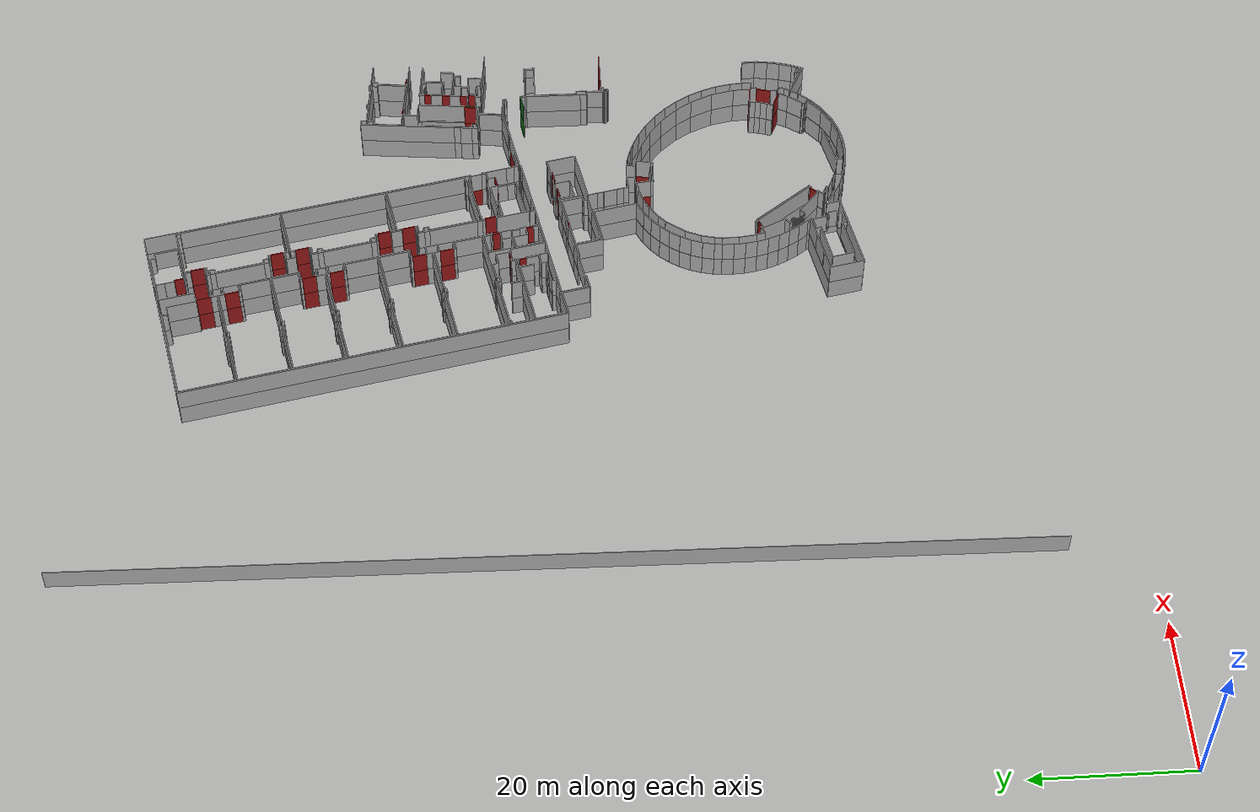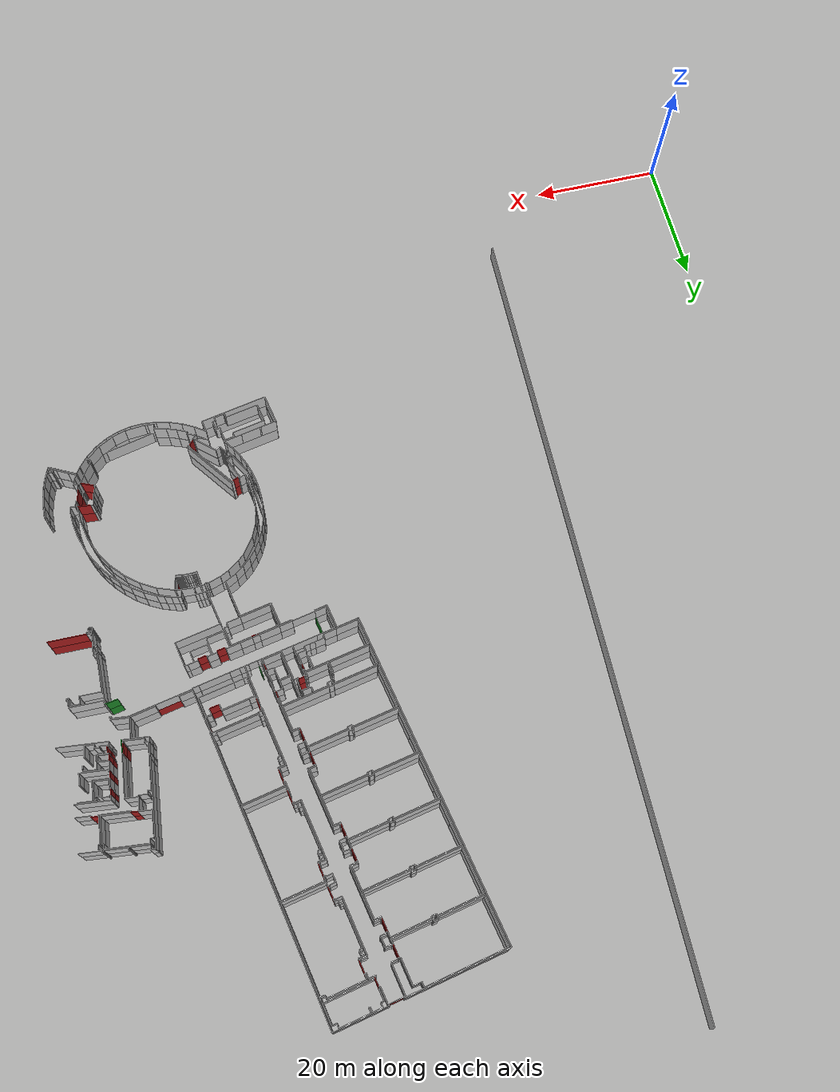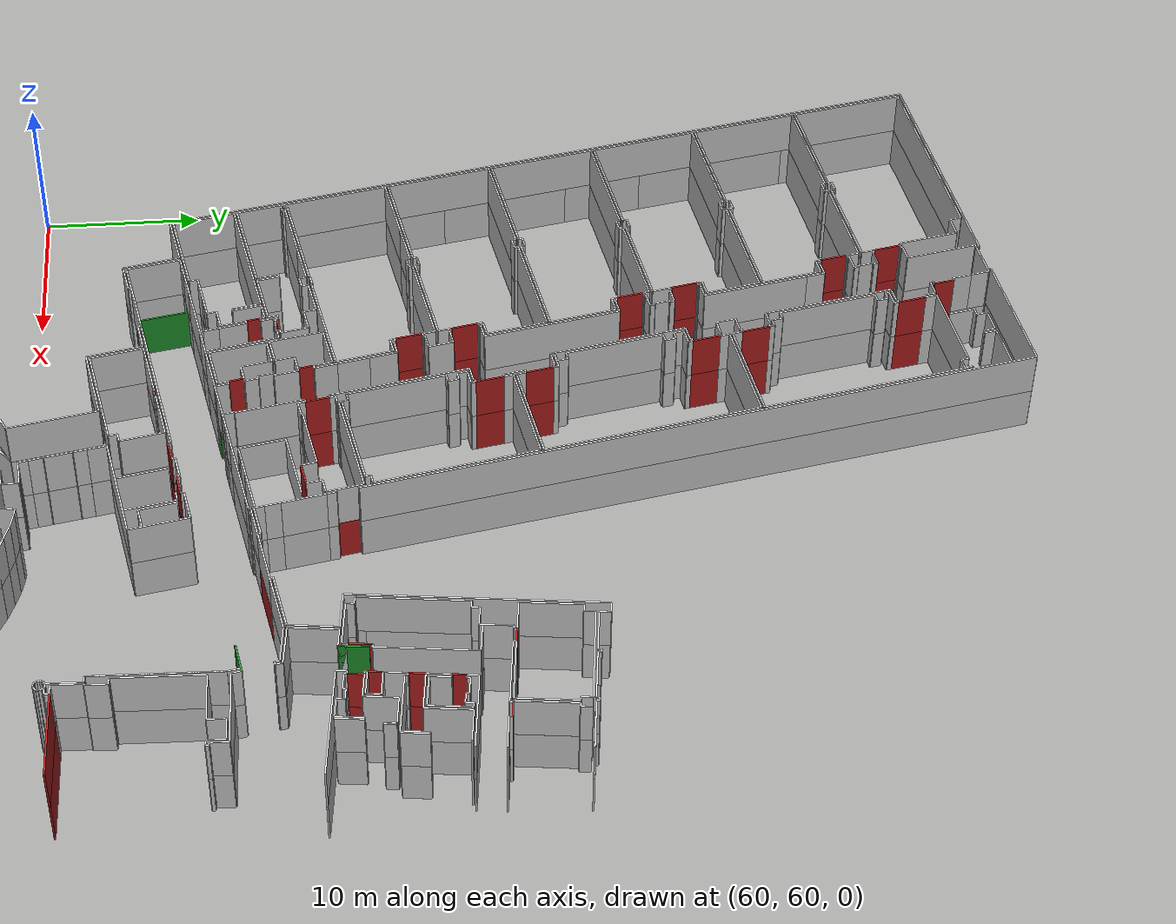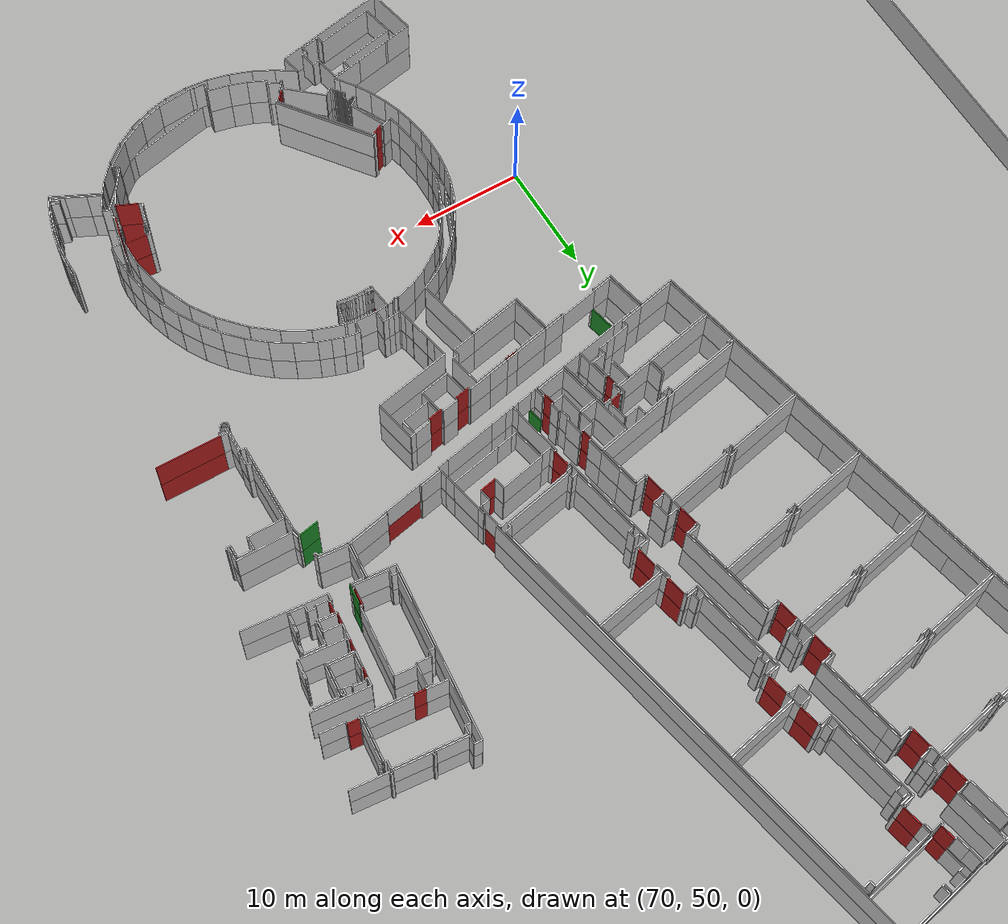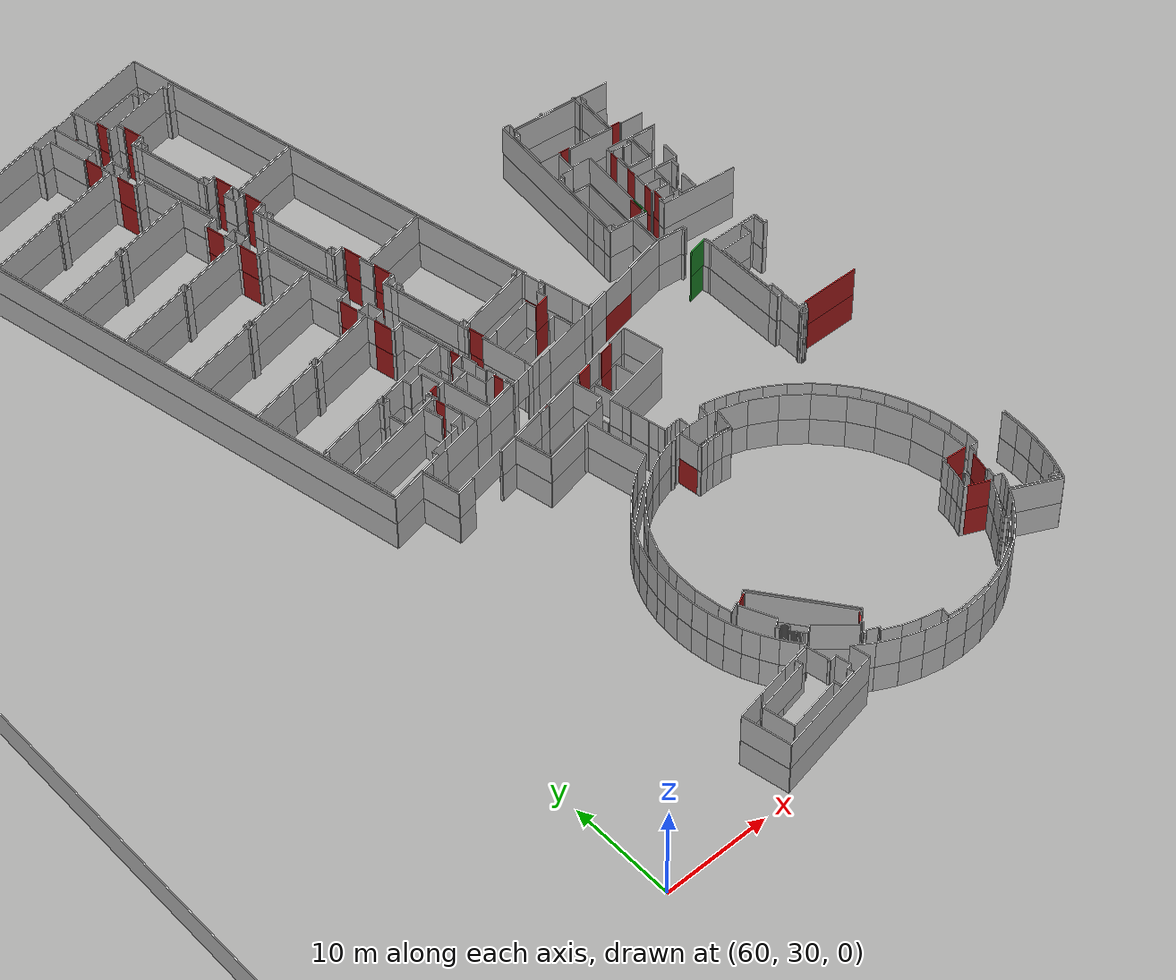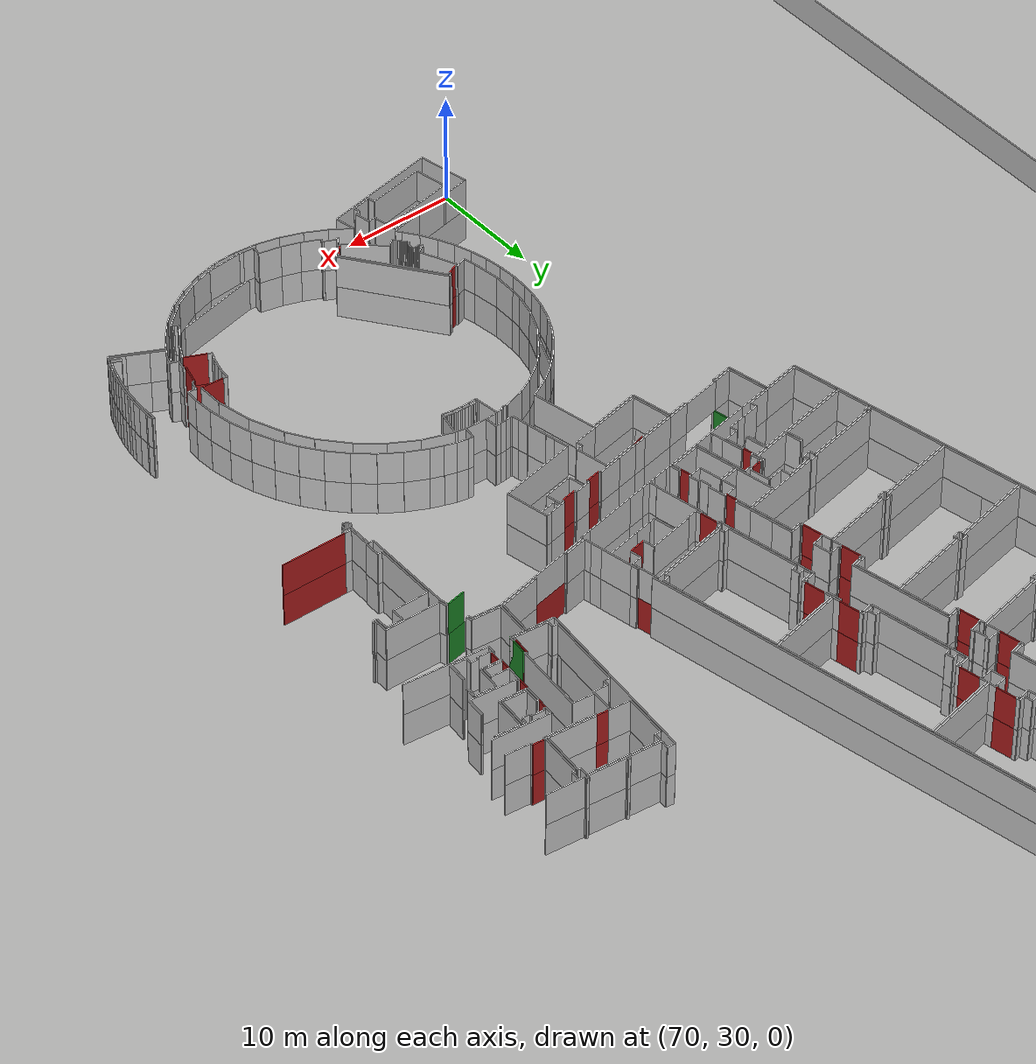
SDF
<sdf version="1.6">
 <world name="default">
  <physics type="ode">
   <max_step_size>0.005</max_step_size>
   <real_time_update_rate>200</real_time_update_rate>
  </physics>
  <plugin filename="libSimEventsPlugin.so" name="elevator_event_plugin">
   <region><name>region1</name><volume><min>140.0 61.0 0</min><max>144.0 63.0 1</max></volume></region>
   <region><name>region2</name><volume><min>140.0 61.0 3</min><max>144.0 63.0 4</max></volume></region>
   <event>
    <name>region1_event</name>
    <type>occupied</type>
    <region>region1</region>
    <topic>/elevator</topic>
    <msg_data>0</msg_data>
   </event>
   <event>
    <name>region2_event</name>
    <type>occupied</type>
    <region>region2</region>
    <topic>/elevator</topic>
    <msg_data>1</msg_data>
   </event>
  </plugin>
  <model name="wall_80.2_77.2_1.5">
   <static>true</static>
   <pose>80.19499999997788 77.22500000009313 1.5 0 0 -1.3773690000310248</pose>
   <link name="link">
    <visual name="visual">
     <geometry><box><size>0.9884331031966657 0.1 3</size></box></geometry>
     <material>
      <script><uri>file://media/materials/scripts/gazebo.material</uri><name>Gazebo/Red</name></script>
     </material>
    </visual>
    <collision name="collision"><geometry><box><size>0.9884331031966657 0.1 3</size></box></geometry></collision>
   </link>
  </model>
  <model name="wall_104.7_79.7_1.5">
   <static>true</static>
   <pose>104.70999999999185 79.65999999991618 1.5 0 0 -1.6724851785951633</pose>
   <link name="link">
    <visual name="visual">
     <geometry><box><size>0.9850888284669952 0.1 3</size></box></geometry>
     <material>
      <script><uri>file://media/materials/scripts/gazebo.material</uri><name>Gazebo/Red</name></script>
     </material>
    </visual>
    <collision name="collision"><geometry><box><size>0.9850888284669952 0.1 3</size></box></geometry></collision>
   </link>
  </model>
  <model name="wall_104.9_83.1_1.5">
   <static>true</static>
   <pose>104.86999999999534 83.12999999988824 1.5 0 0 1.4711276743267871</pose>
   <link name="link">
    <visual name="visual">
     <geometry><box><size>1.0049875621097721 0.1 3</size></box></geometry>
     <material>
      <script><uri>file://media/materials/scripts/gazebo.material</uri><name>Gazebo/Red</name></script>
     </material>
    </visual>
    <collision name="collision"><geometry><box><size>1.0049875621097721 0.1 3</size></box></geometry></collision>
   </link>
  </model>
  <model name="wall_105.1_85.5_1.5">
   <static>true</static>
   <pose>105.10999999998603 85.53499999991618 1.5 0 0 1.4589060606653106</pose>
   <link name="link">
    <visual name="visual">
     <geometry><box><size>0.895600357429266 0.1 3</size></box></geometry>
     <material>
      <script><uri>file://media/materials/scripts/gazebo.material</uri><name>Gazebo/Red</name></script>
     </material>
    </visual>
    <collision name="collision"><geometry><box><size>0.895600357429266 0.1 3</size></box></geometry></collision>
   </link>
  </model>
  <model name="wall_102.4_88.9_1.5">
   <static>true</static>
   <pose>102.38000000000466 88.94000000017695 1.5 0 0 -0.09966865258337218</pose>
   <link name="link">
    <visual name="visual">
     <geometry><box><size>1.004987562121356 0.1 3</size></box></geometry>
     <material>
      <script><uri>file://media/materials/scripts/gazebo.material</uri><name>Gazebo/Red</name></script>
     </material>
    </visual>
    <collision name="collision"><geometry><box><size>1.004987562121356 0.1 3</size></box></geometry></collision>
   </link>
  </model>
  <model name="wall_107.8_88.4_1.5">
   <static>true</static>
   <pose>107.78999999997905 88.4000000001397 1.5 0 0 -0.09966865258337218</pose>
   <link name="link">
    <visual name="visual">
     <geometry><box><size>1.004987562121356 0.1 3</size></box></geometry>
     <material>
      <script><uri>file://media/materials/scripts/gazebo.material</uri><name>Gazebo/Red</name></script>
     </material>
    </visual>
    <collision name="collision"><geometry><box><size>1.004987562121356 0.1 3</size></box></geometry></collision>
   </link>
  </model>
  <model name="wall_102.5_80.0_1.5">
   <static>true</static>
   <pose>102.52499999999418 79.9550000000745 1.5 0 0 -1.6711294309773623</pose>
   <link name="link">
    <visual name="visual">
     <geometry><box><size>1.4975313020620318 0.1 3</size></box></geometry>
     <material>
      <script><uri>file://media/materials/scripts/gazebo.material</uri><name>Gazebo/Red</name></script>
     </material>
    </visual>
    <collision name="collision"><geometry><box><size>1.4975313020620318 0.1 3</size></box></geometry></collision>
   </link>
  </model>
  <model name="wall_102.7_79.6_1.5">
   <static>true</static>
   <pose>102.69000000006054 79.59000000008382 1.5 0 0 1.4711276742268928</pose>
   <link name="link">
    <visual name="visual">
     <geometry><box><size>1.808977612096451 0.1 3</size></box></geometry>
     <material>
      <script><uri>file://media/materials/scripts/gazebo.material</uri><name>Gazebo/Green</name></script>
     </material>
    </visual>
    <collision name="collision"><geometry><box><size>1.808977612096451 0.1 3</size></box></geometry></collision>
   </link>
  </model>
  <model name="wall_104.6_80.8_1.5">
   <static>true</static>
   <pose>104.625 80.77000000001863 1.5 0 0 -1.6704649792092168</pose>
   <link name="link">
    <visual name="visual">
     <geometry><box><size>0.904488806268317 0.1 3</size></box></geometry>
     <material>
      <script><uri>file://media/materials/scripts/gazebo.material</uri><name>Gazebo/Red</name></script>
     </material>
    </visual>
    <collision name="collision"><geometry><box><size>0.904488806268317 0.1 3</size></box></geometry></collision>
   </link>
  </model>
  <model name="wall_103.2_73.0_1.5">
   <static>true</static>
   <pose>103.15500000014435 73.02000000025146 1.5 0 0 -2.9552965370366153</pose>
   <link name="link">
    <visual name="visual">
     <geometry><box><size>1.9436306230085285 0.1 3</size></box></geometry>
     <material>
      <script><uri>file://media/materials/scripts/gazebo.material</uri><name>Gazebo/Green</name></script>
     </material>
    </visual>
    <collision name="collision"><geometry><box><size>1.9436306230085285 0.1 3</size></box></geometry></collision>
   </link>
  </model>
  <model name="wall_71.7_114.6_1.5">
   <static>true</static>
   <pose>71.72999999998137 114.55000000004657 1.5 0 0 -1.3690339825092397</pose>
   <link name="link">
    <visual name="visual">
     <geometry><box><size>1.796440926065282 0.1 3</size></box></geometry>
     <material>
      <script><uri>file://media/materials/scripts/gazebo.material</uri><name>Gazebo/Red</name></script>
     </material>
    </visual>
    <collision name="collision"><geometry><box><size>1.796440926065282 0.1 3</size></box></geometry></collision>
   </link>
  </model>
  <model name="wall_72.4_111.0_1.5">
   <static>true</static>
   <pose>72.43499999999767 111.04000000003725 1.5 0 0 -1.3744936626731843</pose>
   <link name="link">
    <visual name="visual">
     <geometry><box><size>1.7944637079631676 0.1 3</size></box></geometry>
     <material>
      <script><uri>file://media/materials/scripts/gazebo.material</uri><name>Gazebo/Red</name></script>
     </material>
    </visual>
    <collision name="collision"><geometry><box><size>1.7944637079631676 0.1 3</size></box></geometry></collision>
   </link>
  </model>
  <model name="wall_74.4_101.3_1.5">
   <static>true</static>
   <pose>74.38000000000466 101.26000000000931 1.5 0 0 -1.3690339825092397</pose>
   <link name="link">
    <visual name="visual">
     <geometry><box><size>1.796440926065282 0.1 3</size></box></geometry>
     <material>
      <script><uri>file://media/materials/scripts/gazebo.material</uri><name>Gazebo/Red</name></script>
     </material>
    </visual>
    <collision name="collision"><geometry><box><size>1.796440926065282 0.1 3</size></box></geometry></collision>
   </link>
  </model>
  <model name="wall_75.1_97.8_1.5">
   <static>true</static>
   <pose>75.0800000000163 97.75 1.5 0 0 -1.3690339824572944</pose>
   <link name="link">
    <visual name="visual">
     <geometry><box><size>1.7964409256090668 0.1 3</size></box></geometry>
     <material>
      <script><uri>file://media/materials/scripts/gazebo.material</uri><name>Gazebo/Red</name></script>
     </material>
    </visual>
    <collision name="collision"><geometry><box><size>1.7964409256090668 0.1 3</size></box></geometry></collision>
   </link>
  </model>
  <model name="wall_77.2_87.2_1.5">
   <static>true</static>
   <pose>77.19000000000233 87.18999999994412 1.5 0 0 -1.3690339824572944</pose>
   <link name="link">
    <visual name="visual">
     <geometry><box><size>1.7964409256090668 0.1 3</size></box></geometry>
     <material>
      <script><uri>file://media/materials/scripts/gazebo.material</uri><name>Gazebo/Red</name></script>
     </material>
    </visual>
    <collision name="collision"><geometry><box><size>1.7964409256090668 0.1 3</size></box></geometry></collision>
   </link>
  </model>
  <model name="wall_77.9_83.7_1.5">
   <static>true</static>
   <pose>77.88500000000931 83.6699999999255 1.5 0 0 -1.3744936626731843</pose>
   <link name="link">
    <visual name="visual">
     <geometry><box><size>1.7944637079631676 0.1 3</size></box></geometry>
     <material>
      <script><uri>file://media/materials/scripts/gazebo.material</uri><name>Gazebo/Red</name></script>
     </material>
    </visual>
    <collision name="collision"><geometry><box><size>1.7944637079631676 0.1 3</size></box></geometry></collision>
   </link>
  </model>
  <model name="wall_76.4_75.6_1.5">
   <static>true</static>
   <pose>76.39000000001397 75.57500000018626 1.5 0 0 0.19083110263865674</pose>
   <link name="link">
    <visual name="visual">
     <geometry><box><size>0.8962700485807075 0.1 3</size></box></geometry>
     <material>
      <script><uri>file://media/materials/scripts/gazebo.material</uri><name>Gazebo/Red</name></script>
     </material>
    </visual>
    <collision name="collision"><geometry><box><size>0.8962700485807075 0.1 3</size></box></geometry></collision>
   </link>
  </model>
  <model name="wall_75.8_74.0_1.5">
   <static>true</static>
   <pose>75.83999999999651 74.0 1.5 0 0 -1.3690339824572944</pose>
   <link name="link">
    <visual name="visual">
     <geometry><box><size>0.8982204628045334 0.1 3</size></box></geometry>
     <material>
      <script><uri>file://media/materials/scripts/gazebo.material</uri><name>Gazebo/Red</name></script>
     </material>
    </visual>
    <collision name="collision"><geometry><box><size>0.8982204628045334 0.1 3</size></box></geometry></collision>
   </link>
  </model>
  <model name="wall_78.6_105.4_1.5">
   <static>true</static>
   <pose>78.55999999999767 105.38999999989755 1.5 0 0 -1.3690339825092397</pose>
   <link name="link">
    <visual name="visual">
     <geometry><box><size>1.796440926065282 0.1 3</size></box></geometry>
     <material>
      <script><uri>file://media/materials/scripts/gazebo.material</uri><name>Gazebo/Red</name></script>
     </material>
    </visual>
    <collision name="collision"><geometry><box><size>1.796440926065282 0.1 3</size></box></geometry></collision>
   </link>
  </model>
  <model name="wall_76.5_115.5_1.5">
   <static>true</static>
   <pose>76.53999999997905 115.50500000012107 1.5 0 0 -1.3701434494846443</pose>
   <link name="link">
    <visual name="visual">
     <geometry><box><size>1.8062391868343128 0.1 3</size></box></geometry>
     <material>
      <script><uri>file://media/materials/scripts/gazebo.material</uri><name>Gazebo/Red</name></script>
     </material>
    </visual>
    <collision name="collision"><geometry><box><size>1.8062391868343128 0.1 3</size></box></geometry></collision>
   </link>
  </model>
  <model name="wall_79.2_102.2_1.5">
   <static>true</static>
   <pose>79.18499999999767 102.20999999996275 1.5 0 0 -1.3744936626731843</pose>
   <link name="link">
    <visual name="visual">
     <geometry><box><size>1.7944637079631676 0.1 3</size></box></geometry>
     <material>
      <script><uri>file://media/materials/scripts/gazebo.material</uri><name>Gazebo/Red</name></script>
     </material>
    </visual>
    <collision name="collision"><geometry><box><size>1.7944637079631676 0.1 3</size></box></geometry></collision>
   </link>
  </model>
  <model name="wall_81.3_91.7_1.5">
   <static>true</static>
   <pose>81.2949999999837 91.65999999991618 1.5 0 0 -1.374493662723798</pose>
   <link name="link">
    <visual name="visual">
     <geometry><box><size>1.7944637084198858 0.1 3</size></box></geometry>
     <material>
      <script><uri>file://media/materials/scripts/gazebo.material</uri><name>Gazebo/Red</name></script>
     </material>
    </visual>
    <collision name="collision"><geometry><box><size>1.7944637084198858 0.1 3</size></box></geometry></collision>
   </link>
  </model>
  <model name="wall_81.1_72.9_1.5">
   <static>true</static>
   <pose>81.05000000001746 72.92000000015832 1.5 0 0 1.7721134351846652</pose>
   <link name="link">
    <visual name="visual">
     <geometry><box><size>1.0001999799880765 0.1 3</size></box></geometry>
     <material>
      <script><uri>file://media/materials/scripts/gazebo.material</uri><name>Gazebo/Red</name></script>
     </material>
    </visual>
    <collision name="collision"><geometry><box><size>1.0001999799880765 0.1 3</size></box></geometry></collision>
   </link>
  </model>
  <model name="wall_81.6_67.9_1.5">
   <static>true</static>
   <pose>81.55000000001746 67.88999999989755 1.5 0 0 0.2009542638673007</pose>
   <link name="link">
    <visual name="visual">
     <geometry><box><size>1.1021796587332557 0.1 3</size></box></geometry>
     <material>
      <script><uri>file://media/materials/scripts/gazebo.material</uri><name>Gazebo/Red</name></script>
     </material>
    </visual>
    <collision name="collision"><geometry><box><size>1.1021796587332557 0.1 3</size></box></geometry></collision>
   </link>
  </model>
  <model name="wall_86.7_68.9_1.5">
   <static>true</static>
   <pose>86.74499999999534 68.91499999980442 1.5 0 0 0.194586578487565</pose>
   <link name="link">
    <visual name="visual">
     <geometry><box><size>1.3963523910522369 0.1 3</size></box></geometry>
     <material>
      <script><uri>file://media/materials/scripts/gazebo.material</uri><name>Gazebo/Red</name></script>
     </material>
    </visual>
    <collision name="collision"><geometry><box><size>1.3963523910522369 0.1 3</size></box></geometry></collision>
   </link>
  </model>
  <model name="wall_75.1_117.8_1.5">
   <static>true</static>
   <pose>75.06500000000233 117.75500000012107 1.5 0 0 -1.376431060702658</pose>
   <link name="link">
    <visual name="visual">
     <geometry><box><size>1.2943724348298333 0.1 3</size></box></geometry>
     <material>
      <script><uri>file://media/materials/scripts/gazebo.material</uri><name>Gazebo/Red</name></script>
     </material>
    </visual>
    <collision name="collision"><geometry><box><size>1.2943724348298333 0.1 3</size></box></geometry></collision>
   </link>
  </model>
  <model name="wall_108.0_62.3_1.5">
   <static>true</static>
   <pose>107.99499999999534 62.34499999997206 1.5 0 0 -0.012258580285916719</pose>
   <link name="link">
    <visual name="visual">
     <geometry><box><size>5.710429055644689 0.1 3</size></box></geometry>
     <material>
      <script><uri>file://media/materials/scripts/gazebo.material</uri><name>Gazebo/Red</name></script>
     </material>
    </visual>
    <collision name="collision"><geometry><box><size>5.710429055644689 0.1 3</size></box></geometry></collision>
   </link>
  </model>
  <model name="wall_79.8_43.2_1.5">
   <static>true</static>
   <pose>79.82500000001164 43.18500000005588 1.5 0 0 0.42331075582642225</pose>
   <link name="link">
    <visual name="visual">
     <geometry><box><size>0.9980981916532635 0.1 3</size></box></geometry>
     <material>
      <script><uri>file://media/materials/scripts/gazebo.material</uri><name>Gazebo/Red</name></script>
     </material>
    </visual>
    <collision name="collision"><geometry><box><size>0.9980981916532635 0.1 3</size></box></geometry></collision>
   </link>
  </model>
  <model name="wall_85.3_35.8_1.5">
   <static>true</static>
   <pose>85.27999999999884 35.77000000001863 1.5 0 0 0.8424789459730314</pose>
   <link name="link">
    <visual name="visual">
     <geometry><box><size>0.9915644206490059 0.1 3</size></box></geometry>
     <material>
      <script><uri>file://media/materials/scripts/gazebo.material</uri><name>Gazebo/Red</name></script>
     </material>
    </visual>
    <collision name="collision"><geometry><box><size>0.9915644206490059 0.1 3</size></box></geometry></collision>
   </link>
  </model>
  <model name="wall_102.6_42.5_1.5">
   <static>true</static>
   <pose>102.60500000001048 42.48999999999069 1.5 0 0 -0.08271241528552369</pose>
   <link name="link">
    <visual name="visual">
     <geometry><box><size>1.9366207682124321 0.1 3</size></box></geometry>
     <material>
      <script><uri>file://media/materials/scripts/gazebo.material</uri><name>Gazebo/Red</name></script>
     </material>
    </visual>
    <collision name="collision"><geometry><box><size>1.9366207682124321 0.1 3</size></box></geometry></collision>
   </link>
  </model>
  <model name="wall_101.7_39.1_1.5">
   <static>true</static>
   <pose>101.71000000002095 39.06499999994412 1.5 0 0 -0.4219085234522241</pose>
   <link name="link">
    <visual name="visual">
     <geometry><box><size>1.9291708063548034 0.1 3</size></box></geometry>
     <material>
      <script><uri>file://media/materials/scripts/gazebo.material</uri><name>Gazebo/Red</name></script>
     </material>
    </visual>
    <collision name="collision"><geometry><box><size>1.9291708063548034 0.1 3</size></box></geometry></collision>
   </link>
  </model>
  <model name="wall_103.3_40.6_1.5">
   <static>true</static>
   <pose>103.3299999999872 40.59000000008382 1.5 0 0 -1.823690391929414</pose>
   <link name="link">
    <visual name="visual">
     <geometry><box><size>1.8384776308918926 0.1 3</size></box></geometry>
     <material>
      <script><uri>file://media/materials/scripts/gazebo.material</uri><name>Gazebo/Red</name></script>
     </material>
    </visual>
    <collision name="collision"><geometry><box><size>1.8384776308918926 0.1 3</size></box></geometry></collision>
   </link>
  </model>
  <model name="wall_87.9_57.8_1.5">
   <static>true</static>
   <pose>87.93499999999767 57.77499999990687 1.5 0 0 -1.4509545189031208</pose>
   <link name="link">
    <visual name="visual">
     <geometry><box><size>1.9237983263743257 0.1 3</size></box></geometry>
     <material>
      <script><uri>file://media/materials/scripts/gazebo.material</uri><name>Gazebo/Red</name></script>
     </material>
    </visual>
    <collision name="collision"><geometry><box><size>1.9237983263743257 0.1 3</size></box></geometry></collision>
   </link>
  </model>
  <model name="wall_91.5_57.6_1.5">
   <static>true</static>
   <pose>91.49500000002445 57.58999999985099 1.5 0 0 -1.795651920405678</pose>
   <link name="link">
    <visual name="visual">
     <geometry><box><size>1.9285486770039746 0.1 3</size></box></geometry>
     <material>
      <script><uri>file://media/materials/scripts/gazebo.material</uri><name>Gazebo/Red</name></script>
     </material>
    </visual>
    <collision name="collision"><geometry><box><size>1.9285486770039746 0.1 3</size></box></geometry></collision>
   </link>
  </model>
  <model name="wall_89.2_76.9_1.5">
   <static>true</static>
   <pose>89.17999999999302 76.94499999983236 1.5 0 0 0.19349440931601616</pose>
   <link name="link">
    <visual name="visual">
     <geometry><box><size>1.508144555394632 0.1 3</size></box></geometry>
     <material>
      <script><uri>file://media/materials/scripts/gazebo.material</uri><name>Gazebo/Red</name></script>
     </material>
    </visual>
    <collision name="collision"><geometry><box><size>1.508144555394632 0.1 3</size></box></geometry></collision>
   </link>
  </model>
  <model name="wall_81.9_88.5_1.5">
   <static>true</static>
   <pose>81.91500000000815 88.53499999991618 1.5 0 0 -1.3755746765469539</pose>
   <link name="link">
    <visual name="visual">
     <geometry><box><size>1.8042727066855455 0.1 3</size></box></geometry>
     <material>
      <script><uri>file://media/materials/scripts/gazebo.material</uri><name>Gazebo/Red</name></script>
     </material>
    </visual>
    <collision name="collision"><geometry><box><size>1.8042727066855455 0.1 3</size></box></geometry></collision>
   </link>
  </model>
  <model name="wall_83.0_77.9_1.5">
   <static>true</static>
   <pose>83.01999999998952 77.89500000001863 1.5 0 0 -1.3721104451170056</pose>
   <link name="link">
    <visual name="visual">
     <geometry><box><size>1.51990131280261 0.1 3</size></box></geometry>
     <material>
      <script><uri>file://media/materials/scripts/gazebo.material</uri><name>Gazebo/Red</name></script>
     </material>
    </visual>
    <collision name="collision"><geometry><box><size>1.51990131280261 0.1 3</size></box></geometry></collision>
   </link>
  </model>
  <model name="wall_81.9_72.4_1.5">
   <static>true</static>
   <pose>81.875 72.38500000000931 1.5 0 0 1.7681918866447774</pose>
   <link name="link">
    <visual name="visual">
     <geometry><box><size>1.3767352687650285 0.1 3</size></box></geometry>
     <material>
      <script><uri>file://media/materials/scripts/gazebo.material</uri><name>Gazebo/Green</name></script>
     </material>
    </visual>
    <collision name="collision"><geometry><box><size>1.3767352687650285 0.1 3</size></box></geometry></collision>
   </link>
  </model>
  <model name="wall_73.0_120.5_1.5">
   <static>true</static>
   <pose>73.04000000000815 120.50499999988824 1.5 0 0 0.19646185337495456</pose>
   <link name="link">
    <visual name="visual">
     <geometry><box><size>2.100404722931416 0.1 3</size></box></geometry>
     <material>
      <script><uri>file://media/materials/scripts/gazebo.material</uri><name>Gazebo/Red</name></script>
     </material>
    </visual>
    <collision name="collision"><geometry><box><size>2.100404722931416 0.1 3</size></box></geometry></collision>
   </link>
  </model>
  <model name="wall_89.6_69.5_1.5">
   <static>true</static>
   <pose>89.59500000000116 69.4749999998603 1.5 0 0 0.19458657847950467</pose>
   <link name="link">
    <visual name="visual">
     <geometry><box><size>1.396352391109346 0.1 3</size></box></geometry>
     <material>
      <script><uri>file://media/materials/scripts/gazebo.material</uri><name>Gazebo/Red</name></script>
     </material>
    </visual>
    <collision name="collision"><geometry><box><size>1.396352391109346 0.1 3</size></box></geometry></collision>
   </link>
  </model>
  <model name="wall_95.5_74.5_1.5">
   <static>true</static>
   <pose>95.51500000001397 74.51000000000931 1.5 0 0 0.19351316121262999</pose>
   <link name="link">
    <visual name="visual">
     <geometry><box><size>3.5360005656156344 0.1 3</size></box></geometry>
     <material>
      <script><uri>file://media/materials/scripts/gazebo.material</uri><name>Gazebo/Red</name></script>
     </material>
    </visual>
    <collision name="collision"><geometry><box><size>3.5360005656156344 0.1 3</size></box></geometry></collision>
   </link>
  </model>
  <model name="wall_72.2_68.0_1.5">
   <static>true</static>
   <pose>72.16500000003725 68.04500000015832 1.5 0 0 1.767083239622093</pose>
   <link name="link">
    <visual name="visual">
     <geometry><box><size>3.5379372523187618 0.1 3</size></box></geometry>
     <material>
      <script><uri>file://media/materials/scripts/gazebo.material</uri><name>Gazebo/Green</name></script>
     </material>
    </visual>
    <collision name="collision"><geometry><box><size>3.5379372523187618 0.1 3</size></box></geometry></collision>
   </link>
  </model>
  <model name="wall_90.4_79.5_1.5">
   <static>true</static>
   <pose>90.41000000000349 79.52499999990687 1.5 0 0 -1.369193218179265</pose>
   <link name="link">
    <visual name="visual">
     <geometry><box><size>1.3983204211800917 0.1 3</size></box></geometry>
     <material>
      <script><uri>file://media/materials/scripts/gazebo.material</uri><name>Gazebo/Red</name></script>
     </material>
    </visual>
    <collision name="collision"><geometry><box><size>1.3983204211800917 0.1 3</size></box></geometry></collision>
   </link>
  </model>
  <model name="wall_80.2_77.2_4.5">
   <static>true</static>
   <pose>80.19499999997788 77.22500000009313 4.5 0 0 -1.3773690000310248</pose>
   <link name="link">
    <visual name="visual">
     <geometry><box><size>0.9884331031966657 0.1 3</size></box></geometry>
     <material>
      <script><uri>file://media/materials/scripts/gazebo.material</uri><name>Gazebo/Red</name></script>
     </material>
    </visual>
    <collision name="collision"><geometry><box><size>0.9884331031966657 0.1 3</size></box></geometry></collision>
   </link>
  </model>
  <model name="wall_104.7_79.7_4.5">
   <static>true</static>
   <pose>104.70999999999185 79.65999999991618 4.5 0 0 -1.6724851785951633</pose>
   <link name="link">
    <visual name="visual">
     <geometry><box><size>0.9850888284669952 0.1 3</size></box></geometry>
     <material>
      <script><uri>file://media/materials/scripts/gazebo.material</uri><name>Gazebo/Red</name></script>
     </material>
    </visual>
    <collision name="collision"><geometry><box><size>0.9850888284669952 0.1 3</size></box></geometry></collision>
   </link>
  </model>
  <model name="wall_104.9_83.1_4.5">
   <static>true</static>
   <pose>104.86999999999534 83.12999999988824 4.5 0 0 1.4711276743267871</pose>
   <link name="link">
    <visual name="visual">
     <geometry><box><size>1.0049875621097721 0.1 3</size></box></geometry>
     <material>
      <script><uri>file://media/materials/scripts/gazebo.material</uri><name>Gazebo/Red</name></script>
     </material>
    </visual>
    <collision name="collision"><geometry><box><size>1.0049875621097721 0.1 3</size></box></geometry></collision>
   </link>
  </model>
  <model name="wall_105.1_85.5_4.5">
   <static>true</static>
   <pose>105.10999999998603 85.53499999991618 4.5 0 0 1.4589060606653106</pose>
   <link name="link">
    <visual name="visual">
     <geometry><box><size>0.895600357429266 0.1 3</size></box></geometry>
     <material>
      <script><uri>file://media/materials/scripts/gazebo.material</uri><name>Gazebo/Red</name></script>
     </material>
    </visual>
    <collision name="collision"><geometry><box><size>0.895600357429266 0.1 3</size></box></geometry></collision>
   </link>
  </model>
  <model name="wall_102.4_88.9_4.5">
   <static>true</static>
   <pose>102.38000000000466 88.94000000017695 4.5 0 0 -0.09966865258337218</pose>
   <link name="link">
    <visual name="visual">
     <geometry><box><size>1.004987562121356 0.1 3</size></box></geometry>
     <material>
      <script><uri>file://media/materials/scripts/gazebo.material</uri><name>Gazebo/Red</name></script>
     </material>
    </visual>
    <collision name="collision"><geometry><box><size>1.004987562121356 0.1 3</size></box></geometry></collision>
   </link>
  </model>
  <model name="wall_107.8_88.4_4.5">
   <static>true</static>
   <pose>107.78999999997905 88.4000000001397 4.5 0 0 -0.09966865258337218</pose>
   <link name="link">
    <visual name="visual">
     <geometry><box><size>1.004987562121356 0.1 3</size></box></geometry>
     <material>
      <script><uri>file://media/materials/scripts/gazebo.material</uri><name>Gazebo/Red</name></script>
     </material>
    </visual>
    <collision name="collision"><geometry><box><size>1.004987562121356 0.1 3</size></box></geometry></collision>
   </link>
  </model>
  <model name="wall_102.7_79.6_4.5">
   <static>true</static>
   <pose>102.69000000006054 79.59000000008382 4.5 0 0 1.4711276742268928</pose>
   <link name="link">
    <visual name="visual">
     <geometry><box><size>1.808977612096451 0.1 3</size></box></geometry>
     <material>
      <script><uri>file://media/materials/scripts/gazebo.material</uri><name>Gazebo/Green</name></script>
     </material>
    </visual>
    <collision name="collision"><geometry><box><size>1.808977612096451 0.1 3</size></box></geometry></collision>
   </link>
  </model>
  <model name="wall_104.6_80.8_4.5">
   <static>true</static>
   <pose>104.625 80.77000000001863 4.5 0 0 -1.6704649792092168</pose>
   <link name="link">
    <visual name="visual">
     <geometry><box><size>0.904488806268317 0.1 3</size></box></geometry>
     <material>
      <script><uri>file://media/materials/scripts/gazebo.material</uri><name>Gazebo/Red</name></script>
     </material>
    </visual>
    <collision name="collision"><geometry><box><size>0.904488806268317 0.1 3</size></box></geometry></collision>
   </link>
  </model>
  <model name="wall_102.5_80.0_4.5">
   <static>true</static>
   <pose>102.52499999999418 79.9550000000745 4.5 0 0 -1.6711294309773623</pose>
   <link name="link">
    <visual name="visual">
     <geometry><box><size>1.4975313020620318 0.1 3</size></box></geometry>
     <material>
      <script><uri>file://media/materials/scripts/gazebo.material</uri><name>Gazebo/Red</name></script>
     </material>
    </visual>
    <collision name="collision"><geometry><box><size>1.4975313020620318 0.1 3</size></box></geometry></collision>
   </link>
  </model>
  <model name="wall_103.2_73.0_4.5">
   <static>true</static>
   <pose>103.15500000014435 73.02000000025146 4.5 0 0 -2.9552965370366153</pose>
   <link name="link">
    <visual name="visual">
     <geometry><box><size>1.9436306230085285 0.1 3</size></box></geometry>
     <material>
      <script><uri>file://media/materials/scripts/gazebo.material</uri><name>Gazebo/Green</name></script>
     </material>
    </visual>
    <collision name="collision"><geometry><box><size>1.9436306230085285 0.1 3</size></box></geometry></collision>
   </link>
  </model>
  <model name="wall_71.7_114.6_4.5">
   <static>true</static>
   <pose>71.72999999998137 114.55000000004657 4.5 0 0 -1.3690339825092397</pose>
   <link name="link">
    <visual name="visual">
     <geometry><box><size>1.796440926065282 0.1 3</size></box></geometry>
     <material>
      <script><uri>file://media/materials/scripts/gazebo.material</uri><name>Gazebo/Red</name></script>
     </material>
    </visual>
    <collision name="collision"><geometry><box><size>1.796440926065282 0.1 3</size></box></geometry></collision>
   </link>
  </model>
  <model name="wall_72.4_111.0_4.5">
   <static>true</static>
   <pose>72.43499999999767 111.04000000003725 4.5 0 0 -1.3744936626731843</pose>
   <link name="link">
    <visual name="visual">
     <geometry><box><size>1.7944637079631676 0.1 3</size></box></geometry>
     <material>
      <script><uri>file://media/materials/scripts/gazebo.material</uri><name>Gazebo/Red</name></script>
     </material>
    </visual>
    <collision name="collision"><geometry><box><size>1.7944637079631676 0.1 3</size></box></geometry></collision>
   </link>
  </model>
  <model name="wall_74.4_101.3_4.5">
   <static>true</static>
   <pose>74.38000000000466 101.26000000000931 4.5 0 0 -1.3690339825092397</pose>
   <link name="link">
    <visual name="visual">
     <geometry><box><size>1.796440926065282 0.1 3</size></box></geometry>
     <material>
      <script><uri>file://media/materials/scripts/gazebo.material</uri><name>Gazebo/Red</name></script>
     </material>
    </visual>
    <collision name="collision"><geometry><box><size>1.796440926065282 0.1 3</size></box></geometry></collision>
   </link>
  </model>
  <model name="wall_75.1_97.8_4.5">
   <static>true</static>
   <pose>75.0800000000163 97.75 4.5 0 0 -1.3690339824572944</pose>
   <link name="link">
    <visual name="visual">
     <geometry><box><size>1.7964409256090668 0.1 3</size></box></geometry>
     <material>
      <script><uri>file://media/materials/scripts/gazebo.material</uri><name>Gazebo/Red</name></script>
     </material>
    </visual>
    <collision name="collision"><geometry><box><size>1.7964409256090668 0.1 3</size></box></geometry></collision>
   </link>
  </model>
  <model name="wall_77.2_87.2_4.5">
   <static>true</static>
   <pose>77.19000000000233 87.18999999994412 4.5 0 0 -1.3690339824572944</pose>
   <link name="link">
    <visual name="visual">
     <geometry><box><size>1.7964409256090668 0.1 3</size></box></geometry>
     <material>
      <script><uri>file://media/materials/scripts/gazebo.material</uri><name>Gazebo/Red</name></script>
     </material>
    </visual>
    <collision name="collision"><geometry><box><size>1.7964409256090668 0.1 3</size></box></geometry></collision>
   </link>
  </model>
  <model name="wall_77.9_83.7_4.5">
   <static>true</static>
   <pose>77.88500000000931 83.6699999999255 4.5 0 0 -1.3744936626731843</pose>
   <link name="link">
    <visual name="visual">
     <geometry><box><size>1.7944637079631676 0.1 3</size></box></geometry>
     <material>
      <script><uri>file://media/materials/scripts/gazebo.material</uri><name>Gazebo/Red</name></script>
     </material>
    </visual>
    <collision name="collision"><geometry><box><size>1.7944637079631676 0.1 3</size></box></geometry></collision>
   </link>
  </model>
  <model name="wall_76.4_75.6_4.5">
   <static>true</static>
   <pose>76.39000000001397 75.57500000018626 4.5 0 0 0.19083110263865674</pose>
   <link name="link">
    <visual name="visual">
     <geometry><box><size>0.8962700485807075 0.1 3</size></box></geometry>
     <material>
      <script><uri>file://media/materials/scripts/gazebo.material</uri><name>Gazebo/Red</name></script>
     </material>
    </visual>
    <collision name="collision"><geometry><box><size>0.8962700485807075 0.1 3</size></box></geometry></collision>
   </link>
  </model>
  <model name="wall_75.8_74.0_4.5">
   <static>true</static>
   <pose>75.83999999999651 74.0 4.5 0 0 -1.3690339824572944</pose>
   <link name="link">
    <visual name="visual">
     <geometry><box><size>0.8982204628045334 0.1 3</size></box></geometry>
     <material>
      <script><uri>file://media/materials/scripts/gazebo.material</uri><name>Gazebo/Red</name></script>
     </material>
    </visual>
    <collision name="collision"><geometry><box><size>0.8982204628045334 0.1 3</size></box></geometry></collision>
   </link>
  </model>
  <model name="wall_78.6_105.4_4.5">
   <static>true</static>
   <pose>78.55999999999767 105.38999999989755 4.5 0 0 -1.3690339825092397</pose>
   <link name="link">
    <visual name="visual">
     <geometry><box><size>1.796440926065282 0.1 3</size></box></geometry>
     <material>
      <script><uri>file://media/materials/scripts/gazebo.material</uri><name>Gazebo/Red</name></script>
     </material>
    </visual>
    <collision name="collision"><geometry><box><size>1.796440926065282 0.1 3</size></box></geometry></collision>
   </link>
  </model>
  <model name="wall_76.5_115.5_4.5">
   <static>true</static>
   <pose>76.53999999997905 115.50500000012107 4.5 0 0 -1.3701434494846443</pose>
   <link name="link">
    <visual name="visual">
     <geometry><box><size>1.8062391868343128 0.1 3</size></box></geometry>
     <material>
      <script><uri>file://media/materials/scripts/gazebo.material</uri><name>Gazebo/Red</name></script>
     </material>
    </visual>
    <collision name="collision"><geometry><box><size>1.8062391868343128 0.1 3</size></box></geometry></collision>
   </link>
  </model>
  <model name="wall_79.2_102.2_4.5">
   <static>true</static>
   <pose>79.18499999999767 102.20999999996275 4.5 0 0 -1.3744936626731843</pose>
   <link name="link">
    <visual name="visual">
     <geometry><box><size>1.7944637079631676 0.1 3</size></box></geometry>
     <material>
      <script><uri>file://media/materials/scripts/gazebo.material</uri><name>Gazebo/Red</name></script>
     </material>
    </visual>
    <collision name="collision"><geometry><box><size>1.7944637079631676 0.1 3</size></box></geometry></collision>
   </link>
  </model>
  <model name="wall_81.3_91.7_4.5">
   <static>true</static>
   <pose>81.2949999999837 91.65999999991618 4.5 0 0 -1.374493662723798</pose>
   <link name="link">
    <visual name="visual">
     <geometry><box><size>1.7944637084198858 0.1 3</size></box></geometry>
     <material>
      <script><uri>file://media/materials/scripts/gazebo.material</uri><name>Gazebo/Red</name></script>
     </material>
    </visual>
    <collision name="collision"><geometry><box><size>1.7944637084198858 0.1 3</size></box></geometry></collision>
   </link>
  </model>
  <model name="wall_81.1_72.9_4.5">
   <static>true</static>
   <pose>81.05000000001746 72.92000000015832 4.5 0 0 1.7721134351846652</pose>
   <link name="link">
    <visual name="visual">
     <geometry><box><size>1.0001999799880765 0.1 3</size></box></geometry>
     <material>
      <script><uri>file://media/materials/scripts/gazebo.material</uri><name>Gazebo/Red</name></script>
     </material>
    </visual>
    <collision name="collision"><geometry><box><size>1.0001999799880765 0.1 3</size></box></geometry></collision>
   </link>
  </model>
  <model name="wall_81.6_67.9_4.5">
   <static>true</static>
   <pose>81.55000000001746 67.88999999989755 4.5 0 0 0.2009542638673007</pose>
   <link name="link">
    <visual name="visual">
     <geometry><box><size>1.1021796587332557 0.1 3</size></box></geometry>
     <material>
      <script><uri>file://media/materials/scripts/gazebo.material</uri><name>Gazebo/Red</name></script>
     </material>
    </visual>
    <collision name="collision"><geometry><box><size>1.1021796587332557 0.1 3</size></box></geometry></collision>
   </link>
  </model>
  <model name="wall_108.0_62.3_4.5">
   <static>true</static>
   <pose>107.99499999999534 62.34499999997206 4.5 0 0 -0.012258580285916719</pose>
   <link name="link">
    <visual name="visual">
     <geometry><box><size>5.710429055644689 0.1 3</size></box></geometry>
     <material>
      <script><uri>file://media/materials/scripts/gazebo.material</uri><name>Gazebo/Red</name></script>
     </material>
    </visual>
    <collision name="collision"><geometry><box><size>5.710429055644689 0.1 3</size></box></geometry></collision>
   </link>
  </model>
  <model name="wall_79.8_43.2_4.5">
   <static>true</static>
   <pose>79.82500000001164 43.18500000005588 4.5 0 0 0.42331075582642225</pose>
   <link name="link">
    <visual name="visual">
     <geometry><box><size>0.9980981916532635 0.1 3</size></box></geometry>
     <material>
      <script><uri>file://media/materials/scripts/gazebo.material</uri><name>Gazebo/Red</name></script>
     </material>
    </visual>
    <collision name="collision"><geometry><box><size>0.9980981916532635 0.1 3</size></box></geometry></collision>
   </link>
  </model>
  <model name="wall_85.3_35.8_4.5">
   <static>true</static>
   <pose>85.27999999999884 35.77000000001863 4.5 0 0 0.8424789459730314</pose>
   <link name="link">
    <visual name="visual">
     <geometry><box><size>0.9915644206490059 0.1 3</size></box></geometry>
     <material>
      <script><uri>file://media/materials/scripts/gazebo.material</uri><name>Gazebo/Red</name></script>
     </material>
    </visual>
    <collision name="collision"><geometry><box><size>0.9915644206490059 0.1 3</size></box></geometry></collision>
   </link>
  </model>
  <model name="wall_102.6_42.5_4.5">
   <static>true</static>
   <pose>102.60500000001048 42.48999999999069 4.5 0 0 -0.08271241528552369</pose>
   <link name="link">
    <visual name="visual">
     <geometry><box><size>1.9366207682124321 0.1 3</size></box></geometry>
     <material>
      <script><uri>file://media/materials/scripts/gazebo.material</uri><name>Gazebo/Red</name></script>
     </material>
    </visual>
    <collision name="collision"><geometry><box><size>1.9366207682124321 0.1 3</size></box></geometry></collision>
   </link>
  </model>
  <model name="wall_101.7_39.1_4.5">
   <static>true</static>
   <pose>101.71000000002095 39.06499999994412 4.5 0 0 -0.4219085234522241</pose>
   <link name="link">
    <visual name="visual">
     <geometry><box><size>1.9291708063548034 0.1 3</size></box></geometry>
     <material>
      <script><uri>file://media/materials/scripts/gazebo.material</uri><name>Gazebo/Red</name></script>
     </material>
    </visual>
    <collision name="collision"><geometry><box><size>1.9291708063548034 0.1 3</size></box></geometry></collision>
   </link>
  </model>
  <model name="wall_103.3_40.6_4.5">
   <static>true</static>
   <pose>103.3299999999872 40.59000000008382 4.5 0 0 -1.823690391929414</pose>
   <link name="link">
    <visual name="visual">
     <geometry><box><size>1.8384776308918926 0.1 3</size></box></geometry>
     <material>
      <script><uri>file://media/materials/scripts/gazebo.material</uri><name>Gazebo/Red</name></script>
     </material>
    </visual>
    <collision name="collision"><geometry><box><size>1.8384776308918926 0.1 3</size></box></geometry></collision>
   </link>
  </model>
  <model name="wall_75.1_117.8_4.5">
   <static>true</static>
   <pose>75.06500000000233 117.75500000012107 4.5 0 0 -1.376431060702658</pose>
   <link name="link">
    <visual name="visual">
     <geometry><box><size>1.2943724348298333 0.1 3</size></box></geometry>
     <material>
      <script><uri>file://media/materials/scripts/gazebo.material</uri><name>Gazebo/Red</name></script>
     </material>
    </visual>
    <collision name="collision"><geometry><box><size>1.2943724348298333 0.1 3</size></box></geometry></collision>
   </link>
  </model>
  <model name="wall_81.9_88.5_4.5">
   <static>true</static>
   <pose>81.91500000000815 88.53499999991618 4.5 0 0 -1.3755746765469539</pose>
   <link name="link">
    <visual name="visual">
     <geometry><box><size>1.8042727066855455 0.1 3</size></box></geometry>
     <material>
      <script><uri>file://media/materials/scripts/gazebo.material</uri><name>Gazebo/Red</name></script>
     </material>
    </visual>
    <collision name="collision"><geometry><box><size>1.8042727066855455 0.1 3</size></box></geometry></collision>
   </link>
  </model>
  <model name="wall_83.0_77.9_4.5">
   <static>true</static>
   <pose>83.01999999998952 77.89500000001863 4.5 0 0 -1.3721104451170056</pose>
   <link name="link">
    <visual name="visual">
     <geometry><box><size>1.51990131280261 0.1 3</size></box></geometry>
     <material>
      <script><uri>file://media/materials/scripts/gazebo.material</uri><name>Gazebo/Red</name></script>
     </material>
    </visual>
    <collision name="collision"><geometry><box><size>1.51990131280261 0.1 3</size></box></geometry></collision>
   </link>
  </model>
  <model name="wall_86.7_68.9_4.5">
   <static>true</static>
   <pose>86.74499999999534 68.91499999980442 4.5 0 0 0.194586578487565</pose>
   <link name="link">
    <visual name="visual">
     <geometry><box><size>1.3963523910522369 0.1 3</size></box></geometry>
     <material>
      <script><uri>file://media/materials/scripts/gazebo.material</uri><name>Gazebo/Red</name></script>
     </material>
    </visual>
    <collision name="collision"><geometry><box><size>1.3963523910522369 0.1 3</size></box></geometry></collision>
   </link>
  </model>
  <model name="wall_89.6_69.5_4.5">
   <static>true</static>
   <pose>89.59500000000116 69.4749999998603 4.5 0 0 0.19458657847950467</pose>
   <link name="link">
    <visual name="visual">
     <geometry><box><size>1.396352391109346 0.1 3</size></box></geometry>
     <material>
      <script><uri>file://media/materials/scripts/gazebo.material</uri><name>Gazebo/Red</name></script>
     </material>
    </visual>
    <collision name="collision"><geometry><box><size>1.396352391109346 0.1 3</size></box></geometry></collision>
   </link>
  </model>
  <model name="wall_89.2_76.9_4.5">
   <static>true</static>
   <pose>89.17999999999302 76.94499999983236 4.5 0 0 0.19349440931601616</pose>
   <link name="link">
    <visual name="visual">
     <geometry><box><size>1.508144555394632 0.1 3</size></box></geometry>
     <material>
      <script><uri>file://media/materials/scripts/gazebo.material</uri><name>Gazebo/Red</name></script>
     </material>
    </visual>
    <collision name="collision"><geometry><box><size>1.508144555394632 0.1 3</size></box></geometry></collision>
   </link>
  </model>
  <model name="wall_79.8_76.6_1.5">
   <static>true</static>
   <pose>79.77499999999418 76.63500000000931 1.5 0 0 -2.9404657673681704</pose>
   <link name="link">
    <visual name="visual">
     <geometry><box><size>1.0511898021373587 0.1 3</size></box></geometry>
     <material>
      <script><uri>file://media/materials/scripts/gazebo.material</uri><name>Gazebo/White</name></script>
     </material>
    </visual>
    <collision name="collision"><geometry><box><size>1.0511898021373587 0.1 3</size></box></geometry></collision>
   </link>
  </model>
  <model name="wall_79.4_75.9_1.5">
   <static>true</static>
   <pose>79.38000000000466 75.92999999993481 1.5 0 0 -1.3734007669077033</pose>
   <link name="link">
    <visual name="visual">
     <geometry><box><size>1.2237646829864708 0.1 3</size></box></geometry>
     <material>
      <script><uri>file://media/materials/scripts/gazebo.material</uri><name>Gazebo/White</name></script>
     </material>
    </visual>
    <collision name="collision"><geometry><box><size>1.2237646829864708 0.1 3</size></box></geometry></collision>
   </link>
  </model>
  <model name="wall_78.7_75.2_1.5">
   <static>true</static>
   <pose>78.66500000000815 75.16500000003725 1.5 0 0 -2.946501237082923</pose>
   <link name="link">
    <visual name="visual">
     <geometry><box><size>1.7022925717968513 0.1 3</size></box></geometry>
     <material>
      <script><uri>file://media/materials/scripts/gazebo.material</uri><name>Gazebo/White</name></script>
     </material>
    </visual>
    <collision name="collision"><geometry><box><size>1.7022925717968513 0.1 3</size></box></geometry></collision>
   </link>
  </model>
  <model name="wall_77.5_76.7_1.5">
   <static>true</static>
   <pose>77.5 76.67500000004657 1.5 0 0 1.7653199818507113</pose>
   <link name="link">
    <visual name="visual">
     <geometry><box><size>3.414395993534876 0.1 3</size></box></geometry>
     <material>
      <script><uri>file://media/materials/scripts/gazebo.material</uri><name>Gazebo/White</name></script>
     </material>
    </visual>
    <collision name="collision"><geometry><box><size>3.414395993534876 0.1 3</size></box></geometry></collision>
   </link>
  </model>
  <model name="wall_78.5_78.6_1.5">
   <static>true</static>
   <pose>78.51999999998952 78.61499999999069 1.5 0 0 0.19383178298877288</pose>
   <link name="link">
    <visual name="visual">
     <geometry><box><size>2.7515268488324223 0.1 3</size></box></geometry>
     <material>
      <script><uri>file://media/materials/scripts/gazebo.material</uri><name>Gazebo/White</name></script>
     </material>
    </visual>
    <collision name="collision"><geometry><box><size>2.7515268488324223 0.1 3</size></box></geometry></collision>
   </link>
  </model>
  <model name="wall_80.0_78.5_1.5">
   <static>true</static>
   <pose>79.95000000001164 78.46499999985099 1.5 0 0 -1.3803612113601613</pose>
   <link name="link">
    <visual name="visual">
     <geometry><box><size>0.8452810184394953 0.1 3</size></box></geometry>
     <material>
      <script><uri>file://media/materials/scripts/gazebo.material</uri><name>Gazebo/White</name></script>
     </material>
    </visual>
    <collision name="collision"><geometry><box><size>0.8452810184394953 0.1 3</size></box></geometry></collision>
   </link>
  </model>
  <model name="wall_80.1_78.0_1.5">
   <static>true</static>
   <pose>80.05000000001746 77.95499999984168 1.5 0 0 -1.363300100406013</pose>
   <link name="link">
    <visual name="visual">
     <geometry><box><size>0.19416487833047835 0.1 3</size></box></geometry>
     <material>
      <script><uri>file://media/materials/scripts/gazebo.material</uri><name>Gazebo/White</name></script>
     </material>
    </visual>
    <collision name="collision"><geometry><box><size>0.19416487833047835 0.1 3</size></box></geometry></collision>
   </link>
  </model>
  <model name="wall_80.1_77.8_1.5">
   <static>true</static>
   <pose>80.08499999999185 77.78499999991618 1.5 0 0 -1.373400767019641</pose>
   <link name="link">
    <visual name="visual">
     <geometry><box><size>0.15297058531052382 0.1 3</size></box></geometry>
     <material>
      <script><uri>file://media/materials/scripts/gazebo.material</uri><name>Gazebo/White</name></script>
     </material>
    </visual>
    <collision name="collision"><geometry><box><size>0.15297058531052382 0.1 3</size></box></geometry></collision>
   </link>
  </model>
  <model name="wall_108.4_81.5_1.5">
   <static>true</static>
   <pose>108.42999999999302 81.48999999999069 1.5 0 0 -1.6784861976067038</pose>
   <link name="link">
    <visual name="visual">
     <geometry><box><size>0.7443117623918901 0.1 3</size></box></geometry>
     <material>
      <script><uri>file://media/materials/scripts/gazebo.material</uri><name>Gazebo/White</name></script>
     </material>
    </visual>
    <collision name="collision"><geometry><box><size>0.7443117623918901 0.1 3</size></box></geometry></collision>
   </link>
  </model>
  <model name="wall_108.3_81.1_1.5">
   <static>true</static>
   <pose>108.33500000002095 81.125 1.5 0 0 3.0509327683929186</pose>
   <link name="link">
    <visual name="visual">
     <geometry><box><size>0.11045361013772383 0.1 3</size></box></geometry>
     <material>
      <script><uri>file://media/materials/scripts/gazebo.material</uri><name>Gazebo/White</name></script>
     </material>
    </visual>
    <collision name="collision"><geometry><box><size>0.11045361013772383 0.1 3</size></box></geometry></collision>
   </link>
  </model>
  <model name="wall_108.3_81.5_1.5">
   <static>true</static>
   <pose>108.32000000000698 81.5 1.5 0 0 1.463106456050333</pose>
   <link name="link">
    <visual name="visual">
     <geometry><box><size>0.7443117628548539 0.1 3</size></box></geometry>
     <material>
      <script><uri>file://media/materials/scripts/gazebo.material</uri><name>Gazebo/White</name></script>
     </material>
    </visual>
    <collision name="collision"><geometry><box><size>0.7443117628548539 0.1 3</size></box></geometry></collision>
   </link>
  </model>
  <model name="wall_107.5_82.0_1.5">
   <static>true</static>
   <pose>107.46499999999651 81.95999999996275 1.5 0 0 3.04137090397356</pose>
   <link name="link">
    <visual name="visual">
     <geometry><box><size>1.7990275150251853 0.1 3</size></box></geometry>
     <material>
      <script><uri>file://media/materials/scripts/gazebo.material</uri><name>Gazebo/White</name></script>
     </material>
    </visual>
    <collision name="collision"><geometry><box><size>1.7990275150251853 0.1 3</size></box></geometry></collision>
   </link>
  </model>
  <model name="wall_106.5_81.0_1.5">
   <static>true</static>
   <pose>106.46499999999651 81.02000000001863 1.5 0 0 -1.672387129760109</pose>
   <link name="link">
    <visual name="visual">
     <geometry><box><size>2.070676217644975 0.1 3</size></box></geometry>
     <material>
      <script><uri>file://media/materials/scripts/gazebo.material</uri><name>Gazebo/White</name></script>
     </material>
    </visual>
    <collision name="collision"><geometry><box><size>2.070676217644975 0.1 3</size></box></geometry></collision>
   </link>
  </model>
  <model name="wall_105.6_80.1_1.5">
   <static>true</static>
   <pose>105.55999999999767 80.07000000006519 1.5 0 0 3.041924001293137</pose>
   <link name="link">
    <visual name="visual">
     <geometry><box><size>1.6079800993246671 0.1 3</size></box></geometry>
     <material>
      <script><uri>file://media/materials/scripts/gazebo.material</uri><name>Gazebo/White</name></script>
     </material>
    </visual>
    <collision name="collision"><geometry><box><size>1.6079800993246671 0.1 3</size></box></geometry></collision>
   </link>
  </model>
  <model name="wall_104.6_79.1_1.5">
   <static>true</static>
   <pose>104.64999999999418 79.0800000000745 1.5 0 0 -1.6814535479332997</pose>
   <link name="link">
    <visual name="visual">
     <geometry><box><size>0.1811077024621769 0.1 3</size></box></geometry>
     <material>
      <script><uri>file://media/materials/scripts/gazebo.material</uri><name>Gazebo/White</name></script>
     </material>
    </visual>
    <collision name="collision"><geometry><box><size>0.1811077024621769 0.1 3</size></box></geometry></collision>
   </link>
  </model>
  <model name="wall_105.2_78.9_1.5">
   <static>true</static>
   <pose>105.20000000001164 78.93500000005588 1.5 0 0 -0.09790030803535979</pose>
   <link name="link">
    <visual name="visual">
     <geometry><box><size>1.1253888217248873 0.1 3</size></box></geometry>
     <material>
      <script><uri>file://media/materials/scripts/gazebo.material</uri><name>Gazebo/White</name></script>
     </material>
    </visual>
    <collision name="collision"><geometry><box><size>1.1253888217248873 0.1 3</size></box></geometry></collision>
   </link>
  </model>
  <model name="wall_105.8_79.0_1.5">
   <static>true</static>
   <pose>105.77000000001863 78.97999999998137 1.5 0 0 1.4711276743037347</pose>
   <link name="link">
    <visual name="visual">
     <geometry><box><size>0.20099751260961132 0.1 3</size></box></geometry>
     <material>
      <script><uri>file://media/materials/scripts/gazebo.material</uri><name>Gazebo/White</name></script>
     </material>
    </visual>
    <collision name="collision"><geometry><box><size>0.20099751260961132 0.1 3</size></box></geometry></collision>
   </link>
  </model>
  <model name="wall_106.1_79.0_1.5">
   <static>true</static>
   <pose>106.13000000000466 79.0449999999255 1.5 0 0 -0.0996686529192806</pose>
   <link name="link">
    <visual name="visual">
     <geometry><box><size>0.7034912934617817 0.1 3</size></box></geometry>
     <material>
      <script><uri>file://media/materials/scripts/gazebo.material</uri><name>Gazebo/White</name></script>
     </material>
    </visual>
    <collision name="collision"><geometry><box><size>0.7034912934617817 0.1 3</size></box></geometry></collision>
   </link>
  </model>
  <model name="wall_106.5_78.8_1.5">
   <static>true</static>
   <pose>106.4549999999872 78.75999999977648 1.5 0 0 -1.6704649792630062</pose>
   <link name="link">
    <visual name="visual">
     <geometry><box><size>0.5024937810548861 0.1 3</size></box></geometry>
     <material>
      <script><uri>file://media/materials/scripts/gazebo.material</uri><name>Gazebo/White</name></script>
     </material>
    </visual>
    <collision name="collision"><geometry><box><size>0.5024937810548861 0.1 3</size></box></geometry></collision>
   </link>
  </model>
  <model name="wall_107.1_78.4_1.5">
   <static>true</static>
   <pose>107.07499999998254 78.44499999983236 1.5 0 0 -0.10043611196470777</pose>
   <link name="link">
    <visual name="visual">
     <geometry><box><size>1.2965338406369806 0.1 3</size></box></geometry>
     <material>
      <script><uri>file://media/materials/scripts/gazebo.material</uri><name>Gazebo/White</name></script>
     </material>
    </visual>
    <collision name="collision"><geometry><box><size>1.2965338406369806 0.1 3</size></box></geometry></collision>
   </link>
  </model>
  <model name="wall_107.8_79.2_1.5">
   <static>true</static>
   <pose>107.80499999999302 79.2249999998603 1.5 0 0 1.4705418512614783</pose>
   <link name="link">
    <visual name="visual">
     <geometry><box><size>1.6985287750948987 0.1 3</size></box></geometry>
     <material>
      <script><uri>file://media/materials/scripts/gazebo.material</uri><name>Gazebo/White</name></script>
     </material>
    </visual>
    <collision name="collision"><geometry><box><size>1.6985287750948987 0.1 3</size></box></geometry></collision>
   </link>
  </model>
  <model name="wall_107.9_80.1_1.5">
   <static>true</static>
   <pose>107.94500000000698 80.06499999994412 1.5 0 0 -0.09065988519687482</pose>
   <link name="link">
    <visual name="visual">
     <geometry><box><size>0.11045361013772383 0.1 3</size></box></geometry>
     <material>
      <script><uri>file://media/materials/scripts/gazebo.material</uri><name>Gazebo/White</name></script>
     </material>
    </visual>
    <collision name="collision"><geometry><box><size>0.11045361013772383 0.1 3</size></box></geometry></collision>
   </link>
  </model>
  <model name="wall_107.9_79.2_1.5">
   <static>true</static>
   <pose>107.91500000000815 79.20999999996275 1.5 0 0 -1.6704649792657182</pose>
   <link name="link">
    <visual name="visual">
     <geometry><box><size>1.7084788557742698 0.1 3</size></box></geometry>
     <material>
      <script><uri>file://media/materials/scripts/gazebo.material</uri><name>Gazebo/White</name></script>
     </material>
    </visual>
    <collision name="collision"><geometry><box><size>1.7084788557742698 0.1 3</size></box></geometry></collision>
   </link>
  </model>
  <model name="wall_108.8_86.1_1.5">
   <static>true</static>
   <pose>108.77499999999418 86.10000000009313 1.5 0 0 -0.10103726465713746</pose>
   <link name="link">
    <visual name="visual">
     <geometry><box><size>2.18112356362828 0.1 3</size></box></geometry>
     <material>
      <script><uri>file://media/materials/scripts/gazebo.material</uri><name>Gazebo/White</name></script>
     </material>
    </visual>
    <collision name="collision"><geometry><box><size>2.18112356362828 0.1 3</size></box></geometry></collision>
   </link>
  </model>
  <model name="wall_109.1_82.9_1.5">
   <static>true</static>
   <pose>109.14499999998952 82.85499999998137 1.5 0 0 1.470541851323015</pose>
   <link name="link">
    <visual name="visual">
     <geometry><box><size>1.698528775552396 0.1 3</size></box></geometry>
     <material>
      <script><uri>file://media/materials/scripts/gazebo.material</uri><name>Gazebo/White</name></script>
     </material>
    </visual>
    <collision name="collision"><geometry><box><size>1.698528775552396 0.1 3</size></box></geometry></collision>
   </link>
  </model>
  <model name="wall_109.2_83.7_1.5">
   <static>true</static>
   <pose>109.17999999999302 83.7050000000745 1.5 0 0 3.0419240032886226</pose>
   <link name="link">
    <visual name="visual">
     <geometry><box><size>0.10049875616580058 0.1 3</size></box></geometry>
     <material>
      <script><uri>file://media/materials/scripts/gazebo.material</uri><name>Gazebo/White</name></script>
     </material>
    </visual>
    <collision name="collision"><geometry><box><size>0.10049875616580058 0.1 3</size></box></geometry></collision>
   </link>
  </model>
  <model name="wall_109.0_82.9_1.5">
   <static>true</static>
   <pose>109.0450000000128 82.86499999999069 1.5 0 0 -1.6710508022942177</pose>
   <link name="link">
    <visual name="visual">
     <geometry><box><size>1.698528775089073 0.1 3</size></box></geometry>
     <material>
      <script><uri>file://media/materials/scripts/gazebo.material</uri><name>Gazebo/White</name></script>
     </material>
    </visual>
    <collision name="collision"><geometry><box><size>1.698528775089073 0.1 3</size></box></geometry></collision>
   </link>
  </model>
  <model name="wall_107.0_82.2_1.5">
   <static>true</static>
   <pose>106.97500000000582 82.21999999997206 1.5 0 0 3.04117587158638</pose>
   <link name="link">
    <visual name="visual">
     <geometry><box><size>3.990100249387955 0.1 3</size></box></geometry>
     <material>
      <script><uri>file://media/materials/scripts/gazebo.material</uri><name>Gazebo/White</name></script>
     </material>
    </visual>
    <collision name="collision"><geometry><box><size>3.990100249387955 0.1 3</size></box></geometry></collision>
   </link>
  </model>
  <model name="wall_105.0_82.5_1.5">
   <static>true</static>
   <pose>105.0 82.51499999989755 1.5 0 0 1.4659193879370842</pose>
   <link name="link">
    <visual name="visual">
     <geometry><box><size>0.19104973169180559 0.1 3</size></box></geometry>
     <material>
      <script><uri>file://media/materials/scripts/gazebo.material</uri><name>Gazebo/White</name></script>
     </material>
    </visual>
    <collision name="collision"><geometry><box><size>0.19104973169180559 0.1 3</size></box></geometry></collision>
   </link>
  </model>
  <model name="wall_104.9_82.6_1.5">
   <static>true</static>
   <pose>104.91500000000815 82.61999999987893 1.5 0 0 3.0367157147638757</pose>
   <link name="link">
    <visual name="visual">
     <geometry><box><size>0.19104973174969345 0.1 3</size></box></geometry>
     <material>
      <script><uri>file://media/materials/scripts/gazebo.material</uri><name>Gazebo/White</name></script>
     </material>
    </visual>
    <collision name="collision"><geometry><box><size>0.19104973174969345 0.1 3</size></box></geometry></collision>
   </link>
  </model>
  <model name="wall_106.2_83.5_1.5">
   <static>true</static>
   <pose>106.16499999997905 83.5 1.5 0 0 -0.1040406436245778</pose>
   <link name="link">
    <visual name="visual">
     <geometry><box><size>2.5035374971902042 0.1 3</size></box></geometry>
     <material>
      <script><uri>file://media/materials/scripts/gazebo.material</uri><name>Gazebo/White</name></script>
     </material>
    </visual>
    <collision name="collision"><geometry><box><size>2.5035374971902042 0.1 3</size></box></geometry></collision>
   </link>
  </model>
  <model name="wall_107.5_84.8_1.5">
   <static>true</static>
   <pose>107.54999999998836 84.79000000003725 1.5 0 0 1.4725223735240212</pose>
   <link name="link">
    <visual name="visual">
     <geometry><box><size>2.853769436932364 0.1 3</size></box></geometry>
     <material>
      <script><uri>file://media/materials/scripts/gazebo.material</uri><name>Gazebo/White</name></script>
     </material>
    </visual>
    <collision name="collision"><geometry><box><size>2.853769436932364 0.1 3</size></box></geometry></collision>
   </link>
  </model>
  <model name="wall_105.3_86.0_1.5">
   <static>true</static>
   <pose>105.25499999997555 85.96999999997206 1.5 0 0 -0.10487693882591773</pose>
   <link name="link">
    <visual name="visual">
     <geometry><box><size>0.19104973174969345 0.1 3</size></box></geometry>
     <material>
      <script><uri>file://media/materials/scripts/gazebo.material</uri><name>Gazebo/White</name></script>
     </material>
    </visual>
    <collision name="collision"><geometry><box><size>0.19104973174969345 0.1 3</size></box></geometry></collision>
   </link>
  </model>
  <model name="wall_105.4_86.0_1.5">
   <static>true</static>
   <pose>105.35999999998603 86.0449999999255 1.5 0 0 1.4536875820691035</pose>
   <link name="link">
    <visual name="visual">
     <geometry><box><size>0.17117242761441775 0.1 3</size></box></geometry>
     <material>
      <script><uri>file://media/materials/scripts/gazebo.material</uri><name>Gazebo/White</name></script>
     </material>
    </visual>
    <collision name="collision"><geometry><box><size>0.17117242761441775 0.1 3</size></box></geometry></collision>
   </link>
  </model>
  <model name="wall_105.9_86.1_1.5">
   <static>true</static>
   <pose>105.92999999999302 86.07499999995343 1.5 0 0 -0.097900307623563</pose>
   <link name="link">
    <visual name="visual">
     <geometry><box><size>1.1253888216793715 0.1 3</size></box></geometry>
     <material>
      <script><uri>file://media/materials/scripts/gazebo.material</uri><name>Gazebo/White</name></script>
     </material>
    </visual>
    <collision name="collision"><geometry><box><size>1.1253888216793715 0.1 3</size></box></geometry></collision>
   </link>
  </model>
  <model name="wall_106.5_85.9_1.5">
   <static>true</static>
   <pose>106.47999999998137 85.92500000004657 1.5 0 0 -1.675673265652709</pose>
   <link name="link">
    <visual name="visual">
     <geometry><box><size>0.19104973169180559 0.1 3</size></box></geometry>
     <material>
      <script><uri>file://media/materials/scripts/gazebo.material</uri><name>Gazebo/White</name></script>
     </material>
    </visual>
    <collision name="collision"><geometry><box><size>0.19104973169180559 0.1 3</size></box></geometry></collision>
   </link>
  </model>
  <model name="wall_106.8_85.8_1.5">
   <static>true</static>
   <pose>106.81999999997788 85.7949999999255 1.5 0 0 -0.09966865291104755</pose>
   <link name="link">
    <visual name="visual">
     <geometry><box><size>0.7034912935197005 0.1 3</size></box></geometry>
     <material>
      <script><uri>file://media/materials/scripts/gazebo.material</uri><name>Gazebo/White</name></script>
     </material>
    </visual>
    <collision name="collision"><geometry><box><size>0.7034912935197005 0.1 3</size></box></geometry></collision>
   </link>
  </model>
  <model name="wall_107.2_86.0_1.5">
   <static>true</static>
   <pose>107.19499999997788 86.00999999977648 1.5 0 0 1.4711276743267871</pose>
   <link name="link">
    <visual name="visual">
     <geometry><box><size>0.5024937810548861 0.1 3</size></box></geometry>
     <material>
      <script><uri>file://media/materials/scripts/gazebo.material</uri><name>Gazebo/White</name></script>
     </material>
    </visual>
    <collision name="collision"><geometry><box><size>0.5024937810548861 0.1 3</size></box></geometry></collision>
   </link>
  </model>
  <model name="wall_107.4_86.2_1.5">
   <static>true</static>
   <pose>107.35999999998603 86.24499999987893 1.5 0 0 -0.10673567191511722</pose>
   <link name="link">
    <visual name="visual">
     <geometry><box><size>0.28160255681252744 0.1 3</size></box></geometry>
     <material>
      <script><uri>file://media/materials/scripts/gazebo.material</uri><name>Gazebo/White</name></script>
     </material>
    </visual>
    <collision name="collision"><geometry><box><size>0.28160255681252744 0.1 3</size></box></geometry></collision>
   </link>
  </model>
  <model name="wall_107.4_84.9_1.5">
   <static>true</static>
   <pose>107.36499999999069 84.90999999991618 1.5 0 0 -1.6727146942777542</pose>
   <link name="link">
    <visual name="visual">
     <geometry><box><size>2.6537709020747235 0.1 3</size></box></geometry>
     <material>
      <script><uri>file://media/materials/scripts/gazebo.material</uri><name>Gazebo/White</name></script>
     </material>
    </visual>
    <collision name="collision"><geometry><box><size>2.6537709020747235 0.1 3</size></box></geometry></collision>
   </link>
  </model>
  <model name="wall_106.2_83.7_1.5">
   <static>true</static>
   <pose>106.18499999999767 83.69499999983236 1.5 0 0 3.041450292007573</pose>
   <link name="link">
    <visual name="visual">
     <geometry><box><size>2.1005237441762237 0.1 3</size></box></geometry>
     <material>
      <script><uri>file://media/materials/scripts/gazebo.material</uri><name>Gazebo/White</name></script>
     </material>
    </visual>
    <collision name="collision"><geometry><box><size>2.1005237441762237 0.1 3</size></box></geometry></collision>
   </link>
  </model>
  <model name="wall_105.2_84.4_1.5">
   <static>true</static>
   <pose>105.20000000001164 84.43499999982305 1.5 0 0 1.4765878384548259</pose>
   <link name="link">
    <visual name="visual">
     <geometry><box><size>1.2756566936469207 0.1 3</size></box></geometry>
     <material>
      <script><uri>file://media/materials/scripts/gazebo.material</uri><name>Gazebo/White</name></script>
     </material>
    </visual>
    <collision name="collision"><geometry><box><size>1.2756566936469207 0.1 3</size></box></geometry></collision>
   </link>
  </model>
  <model name="wall_105.2_85.1_1.5">
   <static>true</static>
   <pose>105.16000000000349 85.07999999984168 1.5 0 0 3.0419240010121844</pose>
   <link name="link">
    <visual name="visual">
     <geometry><box><size>0.20099751243585498 0.1 3</size></box></geometry>
     <material>
      <script><uri>file://media/materials/scripts/gazebo.material</uri><name>Gazebo/White</name></script>
     </material>
    </visual>
    <collision name="collision"><geometry><box><size>0.20099751243585498 0.1 3</size></box></geometry></collision>
   </link>
  </model>
  <model name="wall_104.9_88.7_1.5">
   <static>true</static>
   <pose>104.94000000000233 88.68500000005588 1.5 0 0 -0.09918799887508435</pose>
   <link name="link">
    <visual name="visual">
     <geometry><box><size>4.1403502267421555 0.1 3</size></box></geometry>
     <material>
      <script><uri>file://media/materials/scripts/gazebo.material</uri><name>Gazebo/White</name></script>
     </material>
    </visual>
    <collision name="collision"><geometry><box><size>4.1403502267421555 0.1 3</size></box></geometry></collision>
   </link>
  </model>
  <model name="wall_107.2_90.4_1.5">
   <static>true</static>
   <pose>107.19000000000233 90.36499999999069 1.5 0 0 1.4703398593399408</pose>
   <link name="link">
    <visual name="visual">
     <geometry><box><size>3.78910279619648 0.1 3</size></box></geometry>
     <material>
      <script><uri>file://media/materials/scripts/gazebo.material</uri><name>Gazebo/White</name></script>
     </material>
    </visual>
    <collision name="collision"><geometry><box><size>3.78910279619648 0.1 3</size></box></geometry></collision>
   </link>
  </model>
  <model name="wall_107.3_92.3_1.5">
   <static>true</static>
   <pose>107.25500000000466 92.26000000000931 1.5 0 0 3.061762667803524</pose>
   <link name="link">
    <visual name="visual">
     <geometry><box><size>0.25079872408117443 0.1 3</size></box></geometry>
     <material>
      <script><uri>file://media/materials/scripts/gazebo.material</uri><name>Gazebo/White</name></script>
     </material>
    </visual>
    <collision name="collision"><geometry><box><size>0.25079872408117443 0.1 3</size></box></geometry></collision>
   </link>
  </model>
  <model name="wall_107.2_92.6_1.5">
   <static>true</static>
   <pose>107.16500000000815 92.62000000011176 1.5 0 0 1.4711276743202006</pose>
   <link name="link">
    <visual name="visual">
     <geometry><box><size>0.7034912936644975 0.1 3</size></box></geometry>
     <material>
      <script><uri>file://media/materials/scripts/gazebo.material</uri><name>Gazebo/White</name></script>
     </material>
    </visual>
    <collision name="collision"><geometry><box><size>0.7034912936644975 0.1 3</size></box></geometry></collision>
   </link>
  </model>
  <model name="wall_104.1_93.3_1.5">
   <static>true</static>
   <pose>104.05999999999767 93.28500000014901 1.5 0 0 3.041608692913362</pose>
   <link name="link">
    <visual name="visual">
     <geometry><box><size>6.311521211261997 0.1 3</size></box></geometry>
     <material>
      <script><uri>file://media/materials/scripts/gazebo.material</uri><name>Gazebo/White</name></script>
     </material>
    </visual>
    <collision name="collision"><geometry><box><size>6.311521211261997 0.1 3</size></box></geometry></collision>
   </link>
  </model>
  <model name="wall_100.9_93.3_1.5">
   <static>true</static>
   <pose>100.88499999998021 93.25500000012107 1.5 0 0 -1.6718996985493473</pose>
   <link name="link">
    <visual name="visual">
     <geometry><box><size>0.693541635321099 0.1 3</size></box></geometry>
     <material>
      <script><uri>file://media/materials/scripts/gazebo.material</uri><name>Gazebo/White</name></script>
     </material>
    </visual>
    <collision name="collision"><geometry><box><size>0.693541635321099 0.1 3</size></box></geometry></collision>
   </link>
  </model>
  <model name="wall_100.6_92.9_1.5">
   <static>true</static>
   <pose>100.59999999997672 92.93500000005588 1.5 0 0 3.0419240014674718</pose>
   <link name="link">
    <visual name="visual">
     <geometry><box><size>0.5024937810375105 0.1 3</size></box></geometry>
     <material>
      <script><uri>file://media/materials/scripts/gazebo.material</uri><name>Gazebo/White</name></script>
     </material>
    </visual>
    <collision name="collision"><geometry><box><size>0.5024937810375105 0.1 3</size></box></geometry></collision>
   </link>
  </model>
  <model name="wall_100.2_91.1_1.5">
   <static>true</static>
   <pose>100.15999999997439 91.07499999995343 1.5 0 0 -1.6712527942498523</pose>
   <link name="link">
    <visual name="visual">
     <geometry><box><size>3.78910279619648 0.1 3</size></box></geometry>
     <material>
      <script><uri>file://media/materials/scripts/gazebo.material</uri><name>Gazebo/White</name></script>
     </material>
    </visual>
    <collision name="collision"><geometry><box><size>3.78910279619648 0.1 3</size></box></geometry></collision>
   </link>
  </model>
  <model name="wall_100.9_89.1_1.5">
   <static>true</static>
   <pose>100.92499999998836 89.09000000008382 1.5 0 0 -0.10433183097900064</pose>
   <link name="link">
    <visual name="visual">
     <geometry><box><size>1.9204426573091837 0.1 3</size></box></geometry>
     <material>
      <script><uri>file://media/materials/scripts/gazebo.material</uri><name>Gazebo/White</name></script>
     </material>
    </visual>
    <collision name="collision"><geometry><box><size>1.9204426573091837 0.1 3</size></box></geometry></collision>
   </link>
  </model>
  <model name="wall_107.9_92.6_1.5">
   <static>true</static>
   <pose>107.85500000001048 92.55000000004657 1.5 0 0 -1.670464979335457</pose>
   <link name="link">
    <visual name="visual">
     <geometry><box><size>0.7034912932011471 0.1 3</size></box></geometry>
     <material>
      <script><uri>file://media/materials/scripts/gazebo.material</uri><name>Gazebo/White</name></script>
     </material>
    </visual>
    <collision name="collision"><geometry><box><size>0.7034912932011471 0.1 3</size></box></geometry></collision>
   </link>
  </model>
  <model name="wall_107.7_92.2_1.5">
   <static>true</static>
   <pose>107.69500000000698 92.21500000008382 1.5 0 0 3.0221637283793843</pose>
   <link name="link">
    <visual name="visual">
     <geometry><box><size>0.2517935662158716 0.1 3</size></box></geometry>
     <material>
      <script><uri>file://media/materials/scripts/gazebo.material</uri><name>Gazebo/White</name></script>
     </material>
    </visual>
    <collision name="collision"><geometry><box><size>0.2517935662158716 0.1 3</size></box></geometry></collision>
   </link>
  </model>
  <model name="wall_107.4_90.3_1.5">
   <static>true</static>
   <pose>107.38000000000466 90.34499999997206 1.5 0 0 -1.6712527942498523</pose>
   <link name="link">
    <visual name="visual">
     <geometry><box><size>3.78910279619648 0.1 3</size></box></geometry>
     <material>
      <script><uri>file://media/materials/scripts/gazebo.material</uri><name>Gazebo/White</name></script>
     </material>
    </visual>
    <collision name="collision"><geometry><box><size>3.78910279619648 0.1 3</size></box></geometry></collision>
   </link>
  </model>
  <model name="wall_107.2_88.5_1.5">
   <static>true</static>
   <pose>107.23999999999069 88.4550000000745 1.5 0 0 -0.09966865030117082</pose>
   <link name="link">
    <visual name="visual">
     <geometry><box><size>0.10049875616580058 0.1 3</size></box></geometry>
     <material>
      <script><uri>file://media/materials/scripts/gazebo.material</uri><name>Gazebo/White</name></script>
     </material>
    </visual>
    <collision name="collision"><geometry><box><size>0.10049875616580058 0.1 3</size></box></geometry></collision>
   </link>
  </model>
  <model name="wall_102.9_83.7_1.5">
   <static>true</static>
   <pose>102.90499999999884 83.67500000004657 1.5 0 0 1.4686322544173183</pose>
   <link name="link">
    <visual name="visual">
     <geometry><box><size>5.98118717285533 0.1 3</size></box></geometry>
     <material>
      <script><uri>file://media/materials/scripts/gazebo.material</uri><name>Gazebo/White</name></script>
     </material>
    </visual>
    <collision name="collision"><geometry><box><size>5.98118717285533 0.1 3</size></box></geometry></collision>
   </link>
  </model>
  <model name="wall_102.4_86.7_1.5">
   <static>true</static>
   <pose>102.35000000000582 86.73499999986961 1.5 0 0 3.0430754111122615</pose>
   <link name="link">
    <visual name="visual">
     <geometry><box><size>1.728380745113411 0.1 3</size></box></geometry>
     <material>
      <script><uri>file://media/materials/scripts/gazebo.material</uri><name>Gazebo/White</name></script>
     </material>
    </visual>
    <collision name="collision"><geometry><box><size>1.728380745113411 0.1 3</size></box></geometry></collision>
   </link>
  </model>
  <model name="wall_100.9_86.9_1.5">
   <static>true</static>
   <pose>100.85999999998603 86.88500000000931 1.5 0 0 3.038781827344916</pose>
   <link name="link">
    <visual name="visual">
     <geometry><box><size>1.2666885963469807 0.1 3</size></box></geometry>
     <material>
      <script><uri>file://media/materials/scripts/gazebo.material</uri><name>Gazebo/White</name></script>
     </material>
    </visual>
    <collision name="collision"><geometry><box><size>1.2666885963469807 0.1 3</size></box></geometry></collision>
   </link>
  </model>
  <model name="wall_100.2_86.7_1.5">
   <static>true</static>
   <pose>100.2049999999872 86.70000000018626 1.5 0 0 -1.6704649792630062</pose>
   <link name="link">
    <visual name="visual">
     <geometry><box><size>0.5024937810548861 0.1 3</size></box></geometry>
     <material>
      <script><uri>file://media/materials/scripts/gazebo.material</uri><name>Gazebo/White</name></script>
     </material>
    </visual>
    <collision name="collision"><geometry><box><size>0.5024937810548861 0.1 3</size></box></geometry></collision>
   </link>
  </model>
  <model name="wall_99.9_86.5_1.5">
   <static>true</static>
   <pose>99.93499999999767 86.47500000009313 1.5 0 0 3.039903802201011</pose>
   <link name="link">
    <visual name="visual">
     <geometry><box><size>0.49254441421281653 0.1 3</size></box></geometry>
     <material>
      <script><uri>file://media/materials/scripts/gazebo.material</uri><name>Gazebo/White</name></script>
     </material>
    </visual>
    <collision name="collision"><geometry><box><size>0.49254441421281653 0.1 3</size></box></geometry></collision>
   </link>
  </model>
  <model name="wall_99.4_83.9_1.5">
   <static>true</static>
   <pose>99.42499999998836 83.9199999999255 1.5 0 0 -1.6731505665400097</pose>
   <link name="link">
    <visual name="visual">
     <geometry><box><size>5.187147578541352 0.1 3</size></box></geometry>
     <material>
      <script><uri>file://media/materials/scripts/gazebo.material</uri><name>Gazebo/White</name></script>
     </material>
    </visual>
    <collision name="collision"><geometry><box><size>5.187147578541352 0.1 3</size></box></geometry></collision>
   </link>
  </model>
  <model name="wall_99.1_80.6_1.5">
   <static>true</static>
   <pose>99.08499999999185 80.59499999997206 1.5 0 0 -1.671129431008509</pose>
   <link name="link">
    <visual name="visual">
     <geometry><box><size>1.4975313015987124 0.1 3</size></box></geometry>
     <material>
      <script><uri>file://media/materials/scripts/gazebo.material</uri><name>Gazebo/White</name></script>
     </material>
    </visual>
    <collision name="collision"><geometry><box><size>1.4975313015987124 0.1 3</size></box></geometry></collision>
   </link>
  </model>
  <model name="wall_99.0_79.8_1.5">
   <static>true</static>
   <pose>99.00500000000466 79.80499999993481 1.5 0 0 -1.6814535476848524</pose>
   <link name="link">
    <visual name="visual">
     <geometry><box><size>0.0905538516971156 0.1 3</size></box></geometry>
     <material>
      <script><uri>file://media/materials/scripts/gazebo.material</uri><name>Gazebo/White</name></script>
     </material>
    </visual>
    <collision name="collision"><geometry><box><size>0.0905538516971156 0.1 3</size></box></geometry></collision>
   </link>
  </model>
  <model name="wall_99.2_79.7_1.5">
   <static>true</static>
   <pose>99.25 79.73499999986961 1.5 0 0 -0.0996686521223214</pose>
   <link name="link">
    <visual name="visual">
     <geometry><box><size>0.5024937810375105 0.1 3</size></box></geometry>
     <material>
      <script><uri>file://media/materials/scripts/gazebo.material</uri><name>Gazebo/White</name></script>
     </material>
    </visual>
    <collision name="collision"><geometry><box><size>0.5024937810375105 0.1 3</size></box></geometry></collision>
   </link>
  </model>
  <model name="wall_99.5_79.5_1.5">
   <static>true</static>
   <pose>99.47500000000582 79.45999999996275 1.5 0 0 -1.6704649792630062</pose>
   <link name="link">
    <visual name="visual">
     <geometry><box><size>0.5024937810548861 0.1 3</size></box></geometry>
     <material>
      <script><uri>file://media/materials/scripts/gazebo.material</uri><name>Gazebo/White</name></script>
     </material>
    </visual>
    <collision name="collision"><geometry><box><size>0.5024937810548861 0.1 3</size></box></geometry></collision>
   </link>
  </model>
  <model name="wall_100.9_79.1_1.5">
   <static>true</static>
   <pose>100.93499999999767 79.06000000005588 1.5 0 0 -0.10066865209668763</pose>
   <link name="link">
    <visual name="visual">
     <geometry><box><size>2.9851130631388623 0.1 3</size></box></geometry>
     <material>
      <script><uri>file://media/materials/scripts/gazebo.material</uri><name>Gazebo/White</name></script>
     </material>
    </visual>
    <collision name="collision"><geometry><box><size>2.9851130631388623 0.1 3</size></box></geometry></collision>
   </link>
  </model>
  <model name="wall_102.4_79.1_1.5">
   <static>true</static>
   <pose>102.43499999999767 79.06000000005588 1.5 0 0 1.471127674150051</pose>
   <link name="link">
    <visual name="visual">
     <geometry><box><size>0.3014962684510667 0.1 3</size></box></geometry>
     <material>
      <script><uri>file://media/materials/scripts/gazebo.material</uri><name>Gazebo/White</name></script>
     </material>
    </visual>
    <collision name="collision"><geometry><box><size>0.3014962684510667 0.1 3</size></box></geometry></collision>
   </link>
  </model>
  <model name="wall_102.6_78.9_1.5">
   <static>true</static>
   <pose>102.625 78.93999999994412 1.5 0 0 1.4711276742115245</pose>
   <link name="link">
    <visual name="visual">
     <geometry><box><size>0.502493781060678 0.1 3</size></box></geometry>
     <material>
      <script><uri>file://media/materials/scripts/gazebo.material</uri><name>Gazebo/White</name></script>
     </material>
    </visual>
    <collision name="collision"><geometry><box><size>0.502493781060678 0.1 3</size></box></geometry></collision>
   </link>
  </model>
  <model name="wall_102.6_79.2_1.5">
   <static>true</static>
   <pose>102.55000000001746 79.19999999995343 1.5 0 0 3.0419240010121844</pose>
   <link name="link">
    <visual name="visual">
     <geometry><box><size>0.20099751243585498 0.1 3</size></box></geometry>
     <material>
      <script><uri>file://media/materials/scripts/gazebo.material</uri><name>Gazebo/White</name></script>
     </material>
    </visual>
    <collision name="collision"><geometry><box><size>0.20099751243585498 0.1 3</size></box></geometry></collision>
   </link>
  </model>
  <model name="wall_102.7_80.7_1.5">
   <static>true</static>
   <pose>102.69999999998254 80.68500000005588 1.5 0 0 -0.14888994887611873</pose>
   <link name="link">
    <visual name="visual">
     <geometry><box><size>0.20223748421176238 0.1 3</size></box></geometry>
     <material>
      <script><uri>file://media/materials/scripts/gazebo.material</uri><name>Gazebo/White</name></script>
     </material>
    </visual>
    <collision name="collision"><geometry><box><size>0.20223748421176238 0.1 3</size></box></geometry></collision>
   </link>
  </model>
  <model name="wall_103.1_83.8_1.5">
   <static>true</static>
   <pose>103.11499999999069 83.75499999988824 1.5 0 0 1.4690420042953642</pose>
   <link name="link">
    <visual name="visual">
     <geometry><box><size>6.202080296085054 0.1 3</size></box></geometry>
     <material>
      <script><uri>file://media/materials/scripts/gazebo.material</uri><name>Gazebo/White</name></script>
     </material>
    </visual>
    <collision name="collision"><geometry><box><size>6.202080296085054 0.1 3</size></box></geometry></collision>
   </link>
  </model>
  <model name="wall_102.5_86.9_1.5">
   <static>true</static>
   <pose>102.47000000000116 86.93499999982305 1.5 0 0 3.0429554602760422</pose>
   <link name="link">
    <visual name="visual">
     <geometry><box><size>1.929378138135752 0.1 3</size></box></geometry>
     <material>
      <script><uri>file://media/materials/scripts/gazebo.material</uri><name>Gazebo/White</name></script>
     </material>
    </visual>
    <collision name="collision"><geometry><box><size>1.929378138135752 0.1 3</size></box></geometry></collision>
   </link>
  </model>
  <model name="wall_101.6_87.9_1.5">
   <static>true</static>
   <pose>101.60000000000582 87.9199999999255 1.5 0 0 1.470015327728778</pose>
   <link name="link">
    <visual name="visual">
     <geometry><box><size>1.789077975082648 0.1 3</size></box></geometry>
     <material>
      <script><uri>file://media/materials/scripts/gazebo.material</uri><name>Gazebo/White</name></script>
     </material>
    </visual>
    <collision name="collision"><geometry><box><size>1.789077975082648 0.1 3</size></box></geometry></collision>
   </link>
  </model>
  <model name="wall_101.8_88.8_1.5">
   <static>true</static>
   <pose>101.77499999999418 88.80000000004657 1.5 0 0 -0.11710874468606086</pose>
   <link name="link">
    <visual name="visual">
     <geometry><box><size>0.1711724276722267 0.1 3</size></box></geometry>
     <material>
      <script><uri>file://media/materials/scripts/gazebo.material</uri><name>Gazebo/White</name></script>
     </material>
    </visual>
    <collision name="collision"><geometry><box><size>0.1711724276722267 0.1 3</size></box></geometry></collision>
   </link>
  </model>
  <model name="wall_101.9_88.9_1.5">
   <static>true</static>
   <pose>101.86999999999534 88.89000000013039 1.5 0 0 1.4711276743037347</pose>
   <link name="link">
    <visual name="visual">
     <geometry><box><size>0.20099751260961132 0.1 3</size></box></geometry>
     <material>
      <script><uri>file://media/materials/scripts/gazebo.material</uri><name>Gazebo/White</name></script>
     </material>
    </visual>
    <collision name="collision"><geometry><box><size>0.20099751260961132 0.1 3</size></box></geometry></collision>
   </link>
  </model>
  <model name="wall_102.9_88.8_1.5">
   <static>true</static>
   <pose>102.86999999999534 88.79000000003725 1.5 0 0 -1.6704649792860586</pose>
   <link name="link">
    <visual name="visual">
     <geometry><box><size>0.20099751260961132 0.1 3</size></box></geometry>
     <material>
      <script><uri>file://media/materials/scripts/gazebo.material</uri><name>Gazebo/White</name></script>
     </material>
    </visual>
    <collision name="collision"><geometry><box><size>0.20099751260961132 0.1 3</size></box></geometry></collision>
   </link>
  </model>
  <model name="wall_105.1_88.5_1.5">
   <static>true</static>
   <pose>105.06500000000233 88.46999999997206 1.5 0 0 -0.099444135193827</pose>
   <link name="link">
    <visual name="visual">
     <geometry><box><size>4.431895756923703 0.1 3</size></box></geometry>
     <material>
      <script><uri>file://media/materials/scripts/gazebo.material</uri><name>Gazebo/White</name></script>
     </material>
    </visual>
    <collision name="collision"><geometry><box><size>4.431895756923703 0.1 3</size></box></geometry></collision>
   </link>
  </model>
  <model name="wall_107.3_88.4_1.5">
   <static>true</static>
   <pose>107.27999999999884 88.35000000009313 1.5 0 0 1.4711276745918913</pose>
   <link name="link">
    <visual name="visual">
     <geometry><box><size>0.20099751260381943 0.1 3</size></box></geometry>
     <material>
      <script><uri>file://media/materials/scripts/gazebo.material</uri><name>Gazebo/White</name></script>
     </material>
    </visual>
    <collision name="collision"><geometry><box><size>0.20099751260381943 0.1 3</size></box></geometry></collision>
   </link>
  </model>
  <model name="wall_108.3_88.2_1.5">
   <static>true</static>
   <pose>108.27999999999884 88.25 1.5 0 0 -1.6704649789979018</pose>
   <link name="link">
    <visual name="visual">
     <geometry><box><size>0.20099751260381943 0.1 3</size></box></geometry>
     <material>
      <script><uri>file://media/materials/scripts/gazebo.material</uri><name>Gazebo/White</name></script>
     </material>
    </visual>
    <collision name="collision"><geometry><box><size>0.20099751260381943 0.1 3</size></box></geometry></collision>
   </link>
  </model>
  <model name="wall_109.4_88.0_1.5">
   <static>true</static>
   <pose>109.36500000001979 88.04000000003725 1.5 0 0 -0.10012073190837828</pose>
   <link name="link">
    <visual name="visual">
     <geometry><box><size>2.2010224896387265 0.1 3</size></box></geometry>
     <material>
      <script><uri>file://media/materials/scripts/gazebo.material</uri><name>Gazebo/White</name></script>
     </material>
    </visual>
    <collision name="collision"><geometry><box><size>2.2010224896387265 0.1 3</size></box></geometry></collision>
   </link>
  </model>
  <model name="wall_107.8_86.4_1.5">
   <static>true</static>
   <pose>107.75 86.40500000002794 1.5 0 0 3.041141375502892</pose>
   <link name="link">
    <visual name="visual">
     <geometry><box><size>5.08563663672627 0.1 3</size></box></geometry>
     <material>
      <script><uri>file://media/materials/scripts/gazebo.material</uri><name>Gazebo/White</name></script>
     </material>
    </visual>
    <collision name="collision"><geometry><box><size>5.08563663672627 0.1 3</size></box></geometry></collision>
   </link>
  </model>
  <model name="wall_105.2_86.3_1.5">
   <static>true</static>
   <pose>105.18999999997322 86.32000000006519 1.5 0 0 -1.6588037002976554</pose>
   <link name="link">
    <visual name="visual">
     <geometry><box><size>0.6826419268018251 0.1 3</size></box></geometry>
     <material>
      <script><uri>file://media/materials/scripts/gazebo.material</uri><name>Gazebo/White</name></script>
     </material>
    </visual>
    <collision name="collision"><geometry><box><size>0.6826419268018251 0.1 3</size></box></geometry></collision>
   </link>
  </model>
  <model name="wall_105.0_84.4_1.5">
   <static>true</static>
   <pose>104.98999999999069 84.35999999986961 1.5 0 0 -1.6663944454706425</pose>
   <link name="link">
    <visual name="visual">
     <geometry><box><size>1.466696969348179 0.1 3</size></box></geometry>
     <material>
      <script><uri>file://media/materials/scripts/gazebo.material</uri><name>Gazebo/White</name></script>
     </material>
    </visual>
    <collision name="collision"><geometry><box><size>1.466696969348179 0.1 3</size></box></geometry></collision>
   </link>
  </model>
  <model name="wall_104.7_81.9_1.5">
   <static>true</static>
   <pose>104.74499999999534 81.92500000004657 1.5 0 0 -1.676780684824448</pose>
   <link name="link">
    <visual name="visual">
     <geometry><box><size>1.417956275459167 0.1 3</size></box></geometry>
     <material>
      <script><uri>file://media/materials/scripts/gazebo.material</uri><name>Gazebo/White</name></script>
     </material>
    </visual>
    <collision name="collision"><geometry><box><size>1.417956275459167 0.1 3</size></box></geometry></collision>
   </link>
  </model>
  <model name="wall_104.6_80.2_1.5">
   <static>true</static>
   <pose>104.57000000000698 80.24499999987893 1.5 0 0 -1.7033478592949163</pose>
   <link name="link">
    <visual name="visual">
     <geometry><box><size>0.15132745941436201 0.1 3</size></box></geometry>
     <material>
      <script><uri>file://media/materials/scripts/gazebo.material</uri><name>Gazebo/White</name></script>
     </material>
    </visual>
    <collision name="collision"><geometry><box><size>0.15132745941436201 0.1 3</size></box></geometry></collision>
   </link>
  </model>
  <model name="wall_104.7_80.2_1.5">
   <static>true</static>
   <pose>104.66000000000349 80.15999999991618 1.5 0 0 -0.09966865257760905</pose>
   <link name="link">
    <visual name="visual">
     <geometry><box><size>0.20099751243585498 0.1 3</size></box></geometry>
     <material>
      <script><uri>file://media/materials/scripts/gazebo.material</uri><name>Gazebo/White</name></script>
     </material>
    </visual>
    <collision name="collision"><geometry><box><size>0.20099751243585498 0.1 3</size></box></geometry></collision>
   </link>
  </model>
  <model name="wall_104.6_79.2_1.5">
   <static>true</static>
   <pose>104.55999999999767 79.17999999993481 1.5 0 0 3.0419240009833683</pose>
   <link name="link">
    <visual name="visual">
     <geometry><box><size>0.20099751237793617 0.1 3</size></box></geometry>
     <material>
      <script><uri>file://media/materials/scripts/gazebo.material</uri><name>Gazebo/White</name></script>
     </material>
    </visual>
    <collision name="collision"><geometry><box><size>0.20099751237793617 0.1 3</size></box></geometry></collision>
   </link>
  </model>
  <model name="wall_104.4_78.8_1.5">
   <static>true</static>
   <pose>104.43000000002212 78.8499999998603 1.5 0 0 -1.6588037002976554</pose>
   <link name="link">
    <visual name="visual">
     <geometry><box><size>0.6826419268018251 0.1 3</size></box></geometry>
     <material>
      <script><uri>file://media/materials/scripts/gazebo.material</uri><name>Gazebo/White</name></script>
     </material>
    </visual>
    <collision name="collision"><geometry><box><size>0.6826419268018251 0.1 3</size></box></geometry></collision>
   </link>
  </model>
  <model name="wall_108.1_78.1_1.5">
   <static>true</static>
   <pose>108.05000000001746 78.1449999997858 1.5 0 0 3.0419240011009996</pose>
   <link name="link">
    <visual name="visual">
     <geometry><box><size>7.336409203404813 0.1 3</size></box></geometry>
     <material>
      <script><uri>file://media/materials/scripts/gazebo.material</uri><name>Gazebo/White</name></script>
     </material>
    </visual>
    <collision name="collision"><geometry><box><size>7.336409203404813 0.1 3</size></box></geometry></collision>
   </link>
  </model>
  <model name="wall_102.0_78.8_1.5">
   <static>true</static>
   <pose>101.98999999999069 78.75499999988824 1.5 0 0 3.035435852165321</pose>
   <link name="link">
    <visual name="visual">
     <geometry><box><size>1.2269066793781709 0.1 3</size></box></geometry>
     <material>
      <script><uri>file://media/materials/scripts/gazebo.material</uri><name>Gazebo/White</name></script>
     </material>
    </visual>
    <collision name="collision"><geometry><box><size>1.2269066793781709 0.1 3</size></box></geometry></collision>
   </link>
  </model>
  <model name="wall_101.2_77.3_1.5">
   <static>true</static>
   <pose>101.22500000000582 77.31499999994412 1.5 0 0 -1.6734245234307366</pose>
   <link name="link">
    <visual name="visual">
     <geometry><box><size>3.0259213470698443 0.1 3</size></box></geometry>
     <material>
      <script><uri>file://media/materials/scripts/gazebo.material</uri><name>Gazebo/White</name></script>
     </material>
    </visual>
    <collision name="collision"><geometry><box><size>3.0259213470698443 0.1 3</size></box></geometry></collision>
   </link>
  </model>
  <model name="wall_102.4_75.7_1.5">
   <static>true</static>
   <pose>102.36499999999069 75.67999999993481 1.5 0 0 -0.10005091556329442</pose>
   <link name="link">
    <visual name="visual">
     <geometry><box><size>2.6030174797640266 0.1 3</size></box></geometry>
     <material>
      <script><uri>file://media/materials/scripts/gazebo.material</uri><name>Gazebo/White</name></script>
     </material>
    </visual>
    <collision name="collision"><geometry><box><size>2.6030174797640266 0.1 3</size></box></geometry></collision>
   </link>
  </model>
  <model name="wall_103.7_75.3_1.5">
   <static>true</static>
   <pose>103.7049999999872 75.32999999984168 1.5 0 0 -1.3690339823938056</pose>
   <link name="link">
    <visual name="visual">
     <geometry><box><size>0.44911023140809897 0.1 3</size></box></geometry>
     <material>
      <script><uri>file://media/materials/scripts/gazebo.material</uri><name>Gazebo/White</name></script>
     </material>
    </visual>
    <collision name="collision"><geometry><box><size>0.44911023140809897 0.1 3</size></box></geometry></collision>
   </link>
  </model>
  <model name="wall_104.2_72.9_1.5">
   <static>true</static>
   <pose>104.17999999999302 72.9000000001397 1.5 0 0 -1.3415643935301684</pose>
   <link name="link">
    <visual name="visual">
     <geometry><box><size>0.6161168721238449 0.1 3</size></box></geometry>
     <material>
      <script><uri>file://media/materials/scripts/gazebo.material</uri><name>Gazebo/White</name></script>
     </material>
    </visual>
    <collision name="collision"><geometry><box><size>0.6161168721238449 0.1 3</size></box></geometry></collision>
   </link>
  </model>
  <model name="wall_106.7_72.6_1.5">
   <static>true</static>
   <pose>106.70000000001164 72.56499999994412 1.5 0 0 -0.01428474264813742</pose>
   <link name="link">
    <visual name="visual">
     <geometry><box><size>4.900499974519937 0.1 3</size></box></geometry>
     <material>
      <script><uri>file://media/materials/scripts/gazebo.material</uri><name>Gazebo/White</name></script>
     </material>
    </visual>
    <collision name="collision"><geometry><box><size>4.900499974519937 0.1 3</size></box></geometry></collision>
   </link>
  </model>
  <model name="wall_109.1_72.0_1.5">
   <static>true</static>
   <pose>109.14000000001397 71.95499999984168 1.5 0 0 -1.5881858781018272</pose>
   <link name="link">
    <visual name="visual">
     <geometry><box><size>1.1501738998023476 0.1 3</size></box></geometry>
     <material>
      <script><uri>file://media/materials/scripts/gazebo.material</uri><name>Gazebo/White</name></script>
     </material>
    </visual>
    <collision name="collision"><geometry><box><size>1.1501738998023476 0.1 3</size></box></geometry></collision>
   </link>
  </model>
  <model name="wall_109.2_71.4_1.5">
   <static>true</static>
   <pose>109.23000000001048 71.37999999988824 1.5 0 0 0.0</pose>
   <link name="link">
    <visual name="visual">
     <geometry><box><size>0.20000000001164153 0.1 3</size></box></geometry>
     <material>
      <script><uri>file://media/materials/scripts/gazebo.material</uri><name>Gazebo/White</name></script>
     </material>
    </visual>
    <collision name="collision"><geometry><box><size>0.20000000001164153 0.1 3</size></box></geometry></collision>
   </link>
  </model>
  <model name="wall_109.3_71.3_1.5">
   <static>true</static>
   <pose>109.3300000000163 71.28000000002794 1.5 0 0 -1.5707963267948966</pose>
   <link name="link">
    <visual name="visual">
     <geometry><box><size>0.19999999972060323 0.1 3</size></box></geometry>
     <material>
      <script><uri>file://media/materials/scripts/gazebo.material</uri><name>Gazebo/White</name></script>
     </material>
    </visual>
    <collision name="collision"><geometry><box><size>0.19999999972060323 0.1 3</size></box></geometry></collision>
   </link>
  </model>
  <model name="wall_105.5_81.1_1.5">
   <static>true</static>
   <pose>105.47000000000116 81.14000000013039 1.5 0 0 -0.099668652581211</pose>
   <link name="link">
    <visual name="visual">
     <geometry><box><size>1.607980099428921 0.1 3</size></box></geometry>
     <material>
      <script><uri>file://media/materials/scripts/gazebo.material</uri><name>Gazebo/White</name></script>
     </material>
    </visual>
    <collision name="collision"><geometry><box><size>1.607980099428921 0.1 3</size></box></geometry></collision>
   </link>
  </model>
  <model name="wall_106.2_80.6_1.5">
   <static>true</static>
   <pose>106.22000000000116 80.61000000010245 1.5 0 0 -1.6814535480184818</pose>
   <link name="link">
    <visual name="visual">
     <geometry><box><size>0.9055385137250358 0.1 3</size></box></geometry>
     <material>
      <script><uri>file://media/materials/scripts/gazebo.material</uri><name>Gazebo/White</name></script>
     </material>
    </visual>
    <collision name="collision"><geometry><box><size>0.9055385137250358 0.1 3</size></box></geometry></collision>
   </link>
  </model>
  <model name="wall_105.4_80.2_1.5">
   <static>true</static>
   <pose>105.375 80.23999999999069 1.5 0 0 3.041301336367988</pose>
   <link name="link">
    <visual name="visual">
     <geometry><box><size>1.598030037200495 0.1 3</size></box></geometry>
     <material>
      <script><uri>file://media/materials/scripts/gazebo.material</uri><name>Gazebo/White</name></script>
     </material>
    </visual>
    <collision name="collision"><geometry><box><size>1.598030037200495 0.1 3</size></box></geometry></collision>
   </link>
  </model>
  <model name="wall_71.5_115.5_1.5">
   <static>true</static>
   <pose>71.5449999999837 115.47999999998137 1.5 0 0 1.6704649797471094</pose>
   <link name="link">
    <visual name="visual">
     <geometry><box><size>0.10049875584145537 0.1 3</size></box></geometry>
     <material>
      <script><uri>file://media/materials/scripts/gazebo.material</uri><name>Gazebo/White</name></script>
     </material>
    </visual>
    <collision name="collision"><geometry><box><size>0.10049875584145537 0.1 3</size></box></geometry></collision>
   </link>
  </model>
  <model name="wall_71.4_115.5_1.5">
   <static>true</static>
   <pose>71.44000000000233 115.51000000000931 1.5 0 0 -2.944197095754793</pose>
   <link name="link">
    <visual name="visual">
     <geometry><box><size>0.20396078041403173 0.1 3</size></box></geometry>
     <material>
      <script><uri>file://media/materials/scripts/gazebo.material</uri><name>Gazebo/White</name></script>
     </material>
    </visual>
    <collision name="collision"><geometry><box><size>0.20396078041403173 0.1 3</size></box></geometry></collision>
   </link>
  </model>
  <model name="wall_71.0_117.4_1.5">
   <static>true</static>
   <pose>70.96500000002561 117.37000000011176 1.5 0 0 1.7676803777493852</pose>
   <link name="link">
    <visual name="visual">
     <geometry><box><size>3.834070943308059 0.1 3</size></box></geometry>
     <material>
      <script><uri>file://media/materials/scripts/gazebo.material</uri><name>Gazebo/White</name></script>
     </material>
    </visual>
    <collision name="collision"><geometry><box><size>3.834070943308059 0.1 3</size></box></geometry></collision>
   </link>
  </model>
  <model name="wall_70.0_119.1_1.5">
   <static>true</static>
   <pose>69.96500000002561 119.12999999988824 1.5 0 0 -2.9519011013949563</pose>
   <link name="link">
    <visual name="visual">
     <geometry><box><size>1.2728314892817856 0.1 3</size></box></geometry>
     <material>
      <script><uri>file://media/materials/scripts/gazebo.material</uri><name>Gazebo/White</name></script>
     </material>
    </visual>
    <collision name="collision"><geometry><box><size>1.2728314892817856 0.1 3</size></box></geometry></collision>
   </link>
  </model>
  <model name="wall_69.3_119.4_1.5">
   <static>true</static>
   <pose>69.27000000001863 119.375 1.5 0 0 1.760276484581226</pose>
   <link name="link">
    <visual name="visual">
     <geometry><box><size>0.7433034378075905 0.1 3</size></box></geometry>
     <material>
      <script><uri>file://media/materials/scripts/gazebo.material</uri><name>Gazebo/White</name></script>
     </material>
    </visual>
    <collision name="collision"><geometry><box><size>0.7433034378075905 0.1 3</size></box></geometry></collision>
   </link>
  </model>
  <model name="wall_63.1_118.5_1.5">
   <static>true</static>
   <pose>63.14500000001863 118.54500000015832 1.5 0 0 -2.9467391918441352</pose>
   <link name="link">
    <visual name="visual">
     <geometry><box><size>12.343589429346915 0.1 3</size></box></geometry>
     <material>
      <script><uri>file://media/materials/scripts/gazebo.material</uri><name>Gazebo/White</name></script>
     </material>
    </visual>
    <collision name="collision"><geometry><box><size>12.343589429346915 0.1 3</size></box></geometry></collision>
   </link>
  </model>
  <model name="wall_57.8_113.8_1.5">
   <static>true</static>
   <pose>57.80000000001746 113.78500000014901 1.5 0 0 -1.3742100465085676</pose>
   <link name="link">
    <visual name="visual">
     <geometry><box><size>7.270027510151529 0.1 3</size></box></geometry>
     <material>
      <script><uri>file://media/materials/scripts/gazebo.material</uri><name>Gazebo/White</name></script>
     </material>
    </visual>
    <collision name="collision"><geometry><box><size>7.270027510151529 0.1 3</size></box></geometry></collision>
   </link>
  </model>
  <model name="wall_61.9_110.9_1.5">
   <static>true</static>
   <pose>61.945000000006985 110.9000000001397 1.5 0 0 0.1954353271142626</pose>
   <link name="link">
    <visual name="visual">
     <geometry><box><size>7.0033206409232305 0.1 3</size></box></geometry>
     <material>
      <script><uri>file://media/materials/scripts/gazebo.material</uri><name>Gazebo/White</name></script>
     </material>
    </visual>
    <collision name="collision"><geometry><box><size>7.0033206409232305 0.1 3</size></box></geometry></collision>
   </link>
  </model>
  <model name="wall_65.4_111.7_1.5">
   <static>true</static>
   <pose>65.35500000001048 111.69999999995343 1.5 0 0 1.7761917161396261</pose>
   <link name="link">
    <visual name="visual">
     <geometry><box><size>0.24515301320319682 0.1 3</size></box></geometry>
     <material>
      <script><uri>file://media/materials/scripts/gazebo.material</uri><name>Gazebo/White</name></script>
     </material>
    </visual>
    <collision name="collision"><geometry><box><size>0.24515301320319682 0.1 3</size></box></geometry></collision>
   </link>
  </model>
  <model name="wall_65.7_111.9_1.5">
   <static>true</static>
   <pose>65.6700000000128 111.88999999989755 1.5 0 0 0.20304521743943982</pose>
   <link name="link">
    <visual name="visual">
     <geometry><box><size>0.6942621983278424 0.1 3</size></box></geometry>
     <material>
      <script><uri>file://media/materials/scripts/gazebo.material</uri><name>Gazebo/White</name></script>
     </material>
    </visual>
    <collision name="collision"><geometry><box><size>0.6942621983278424 0.1 3</size></box></geometry></collision>
   </link>
  </model>
  <model name="wall_66.0_111.8_1.5">
   <static>true</static>
   <pose>66.03500000000349 111.83499999996275 1.5 0 0 -1.373400766989791</pose>
   <link name="link">
    <visual name="visual">
     <geometry><box><size>0.25495097567735614 0.1 3</size></box></geometry>
     <material>
      <script><uri>file://media/materials/scripts/gazebo.material</uri><name>Gazebo/White</name></script>
     </material>
    </visual>
    <collision name="collision"><geometry><box><size>0.25495097567735614 0.1 3</size></box></geometry></collision>
   </link>
  </model>
  <model name="wall_69.1_112.3_1.5">
   <static>true</static>
   <pose>69.05999999999767 112.30000000004657 1.5 0 0 0.19418838678074232</pose>
   <link name="link">
    <visual name="visual">
     <geometry><box><size>6.1149325425875 0.1 3</size></box></geometry>
     <material>
      <script><uri>file://media/materials/scripts/gazebo.material</uri><name>Gazebo/White</name></script>
     </material>
    </visual>
    <collision name="collision"><geometry><box><size>6.1149325425875 0.1 3</size></box></geometry></collision>
   </link>
  </model>
  <model name="wall_72.0_113.3_1.5">
   <static>true</static>
   <pose>71.98499999998603 113.28000000002794 1.5 0 0 1.760784614791112</pose>
   <link name="link">
    <visual name="visual">
     <geometry><box><size>0.7942921374956162 0.1 3</size></box></geometry>
     <material>
      <script><uri>file://media/materials/scripts/gazebo.material</uri><name>Gazebo/White</name></script>
     </material>
    </visual>
    <collision name="collision"><geometry><box><size>0.7942921374956162 0.1 3</size></box></geometry></collision>
   </link>
  </model>
  <model name="wall_72.2_112.3_1.5">
   <static>true</static>
   <pose>72.17999999999302 112.30499999993481 1.5 0 0 1.7756730438677673</pose>
   <link name="link">
    <visual name="visual">
     <geometry><box><size>0.786447709666139 0.1 3</size></box></geometry>
     <material>
      <script><uri>file://media/materials/scripts/gazebo.material</uri><name>Gazebo/White</name></script>
     </material>
    </visual>
    <collision name="collision"><geometry><box><size>0.786447709666139 0.1 3</size></box></geometry></collision>
   </link>
  </model>
  <model name="wall_69.1_112.1_1.5">
   <static>true</static>
   <pose>69.09999999997672 112.0999999998603 1.5 0 0 -2.947404266809051</pose>
   <link name="link">
    <visual name="visual">
     <geometry><box><size>6.1149325425875 0.1 3</size></box></geometry>
     <material>
      <script><uri>file://media/materials/scripts/gazebo.material</uri><name>Gazebo/White</name></script>
     </material>
    </visual>
    <collision name="collision"><geometry><box><size>6.1149325425875 0.1 3</size></box></geometry></collision>
   </link>
  </model>
  <model name="wall_66.1_111.4_1.5">
   <static>true</static>
   <pose>66.125 111.38999999989755 1.5 0 0 -1.3654009372177238</pose>
   <link name="link">
    <visual name="visual">
     <geometry><box><size>0.24515301321506852 0.1 3</size></box></geometry>
     <material>
      <script><uri>file://media/materials/scripts/gazebo.material</uri><name>Gazebo/White</name></script>
     </material>
    </visual>
    <collision name="collision"><geometry><box><size>0.24515301321506852 0.1 3</size></box></geometry></collision>
   </link>
  </model>
  <model name="wall_65.8_111.2_1.5">
   <static>true</static>
   <pose>65.80999999999767 111.2050000000745 1.5 0 0 -2.9526954728846198</pose>
   <link name="link">
    <visual name="visual">
     <geometry><box><size>0.6923149572561651 0.1 3</size></box></geometry>
     <material>
      <script><uri>file://media/materials/scripts/gazebo.material</uri><name>Gazebo/White</name></script>
     </material>
    </visual>
    <collision name="collision"><geometry><box><size>0.6923149572561651 0.1 3</size></box></geometry></collision>
   </link>
  </model>
  <model name="wall_65.4_111.3_1.5">
   <static>true</static>
   <pose>65.44499999997788 111.26000000000931 1.5 0 0 1.7761917161396261</pose>
   <link name="link">
    <visual name="visual">
     <geometry><box><size>0.24515301320319682 0.1 3</size></box></geometry>
     <material>
      <script><uri>file://media/materials/scripts/gazebo.material</uri><name>Gazebo/White</name></script>
     </material>
    </visual>
    <collision name="collision"><geometry><box><size>0.24515301320319682 0.1 3</size></box></geometry></collision>
   </link>
  </model>
  <model name="wall_62.0_110.7_1.5">
   <static>true</static>
   <pose>61.98499999998603 110.70499999984168 1.5 0 0 -2.9475584256050955</pose>
   <link name="link">
    <visual name="visual">
     <geometry><box><size>7.001385577168813 0.1 3</size></box></geometry>
     <material>
      <script><uri>file://media/materials/scripts/gazebo.material</uri><name>Gazebo/White</name></script>
     </material>
    </visual>
    <collision name="collision"><geometry><box><size>7.001385577168813 0.1 3</size></box></geometry></collision>
   </link>
  </model>
  <model name="wall_59.2_106.7_1.5">
   <static>true</static>
   <pose>59.20999999999185 106.70499999984168 1.5 0 0 -1.3748471066906804</pose>
   <link name="link">
    <visual name="visual">
     <geometry><box><size>6.779741882902312 0.1 3</size></box></geometry>
     <material>
      <script><uri>file://media/materials/scripts/gazebo.material</uri><name>Gazebo/White</name></script>
     </material>
    </visual>
    <collision name="collision"><geometry><box><size>6.779741882902312 0.1 3</size></box></geometry></collision>
   </link>
  </model>
  <model name="wall_63.3_104.1_1.5">
   <static>true</static>
   <pose>63.304999999993015 104.05499999993481 1.5 0 0 0.19403422798469777</pose>
   <link name="link">
    <visual name="visual">
     <geometry><box><size>7.001385577168813 0.1 3</size></box></geometry>
     <material>
      <script><uri>file://media/materials/scripts/gazebo.material</uri><name>Gazebo/White</name></script>
     </material>
    </visual>
    <collision name="collision"><geometry><box><size>7.001385577168813 0.1 3</size></box></geometry></collision>
   </link>
  </model>
  <model name="wall_66.7_104.9_1.5">
   <static>true</static>
   <pose>66.71499999999651 104.85499999998137 1.5 0 0 1.7681918866000021</pose>
   <link name="link">
    <visual name="visual">
     <geometry><box><size>0.25495097567735614 0.1 3</size></box></geometry>
     <material>
      <script><uri>file://media/materials/scripts/gazebo.material</uri><name>Gazebo/White</name></script>
     </material>
    </visual>
    <collision name="collision"><geometry><box><size>0.25495097567735614 0.1 3</size></box></geometry></collision>
   </link>
  </model>
  <model name="wall_67.0_105.1_1.5">
   <static>true</static>
   <pose>67.03500000000349 105.05000000004657 1.5 0 0 0.20018106814672346</pose>
   <link name="link">
    <visual name="visual">
     <geometry><box><size>0.7040596565914858 0.1 3</size></box></geometry>
     <material>
      <script><uri>file://media/materials/scripts/gazebo.material</uri><name>Gazebo/White</name></script>
     </material>
    </visual>
    <collision name="collision"><geometry><box><size>0.7040596565914858 0.1 3</size></box></geometry></collision>
   </link>
  </model>
  <model name="wall_67.4_105.0_1.5">
   <static>true</static>
   <pose>67.40499999999884 104.99500000011176 1.5 0 0 -1.373400766989791</pose>
   <link name="link">
    <visual name="visual">
     <geometry><box><size>0.25495097567735614 0.1 3</size></box></geometry>
     <material>
      <script><uri>file://media/materials/scripts/gazebo.material</uri><name>Gazebo/White</name></script>
     </material>
    </visual>
    <collision name="collision"><geometry><box><size>0.25495097567735614 0.1 3</size></box></geometry></collision>
   </link>
  </model>
  <model name="wall_70.9_105.6_1.5">
   <static>true</static>
   <pose>70.9199999999837 105.56000000005588 1.5 0 0 0.19519049174407682</pose>
   <link name="link">
    <visual name="visual">
     <geometry><box><size>7.115110680757645 0.1 3</size></box></geometry>
     <material>
      <script><uri>file://media/materials/scripts/gazebo.material</uri><name>Gazebo/White</name></script>
     </material>
    </visual>
    <collision name="collision"><geometry><box><size>7.115110680757645 0.1 3</size></box></geometry></collision>
   </link>
  </model>
  <model name="wall_74.0_108.2_1.5">
   <static>true</static>
   <pose>74.02999999999884 108.15500000002794 1.5 0 0 1.7676870911146996</pose>
   <link name="link">
    <visual name="visual">
     <geometry><box><size>3.8850611321253985 0.1 3</size></box></geometry>
     <material>
      <script><uri>file://media/materials/scripts/gazebo.material</uri><name>Gazebo/White</name></script>
     </material>
    </visual>
    <collision name="collision"><geometry><box><size>3.8850611321253985 0.1 3</size></box></geometry></collision>
   </link>
  </model>
  <model name="wall_73.2_110.0_1.5">
   <static>true</static>
   <pose>73.16000000000349 109.95999999996275 1.5 0 0 -2.9402755450405995</pose>
   <link name="link">
    <visual name="visual">
     <geometry><box><size>1.0001999800800263 0.1 3</size></box></geometry>
     <material>
      <script><uri>file://media/materials/scripts/gazebo.material</uri><name>Gazebo/White</name></script>
     </material>
    </visual>
    <collision name="collision"><geometry><box><size>1.0001999800800263 0.1 3</size></box></geometry></collision>
   </link>
  </model>
  <model name="wall_72.6_110.0_1.5">
   <static>true</static>
   <pose>72.63999999998487 110.01000000000931 1.5 0 0 1.7681918864582145</pose>
   <link name="link">
    <visual name="visual">
     <geometry><box><size>0.30594117108908153 0.1 3</size></box></geometry>
     <material>
      <script><uri>file://media/materials/scripts/gazebo.material</uri><name>Gazebo/White</name></script>
     </material>
    </visual>
    <collision name="collision"><geometry><box><size>0.30594117108908153 0.1 3</size></box></geometry></collision>
   </link>
  </model>
  <model name="wall_74.2_102.3_1.5">
   <static>true</static>
   <pose>74.17500000001746 102.29000000003725 1.5 0 0 1.7359450042724507</pose>
   <link name="link">
    <visual name="visual">
     <geometry><box><size>0.30413812632926696 0.1 3</size></box></geometry>
     <material>
      <script><uri>file://media/materials/scripts/gazebo.material</uri><name>Gazebo/White</name></script>
     </material>
    </visual>
    <collision name="collision"><geometry><box><size>0.30413812632926696 0.1 3</size></box></geometry></collision>
   </link>
  </model>
  <model name="wall_74.6_102.5_1.5">
   <static>true</static>
   <pose>74.63500000000931 102.53499999991618 1.5 0 0 0.19342732666080192</pose>
   <link name="link">
    <visual name="visual">
     <geometry><box><size>0.9884331034139654 0.1 3</size></box></geometry>
     <material>
      <script><uri>file://media/materials/scripts/gazebo.material</uri><name>Gazebo/White</name></script>
     </material>
    </visual>
    <collision name="collision"><geometry><box><size>0.9884331034139654 0.1 3</size></box></geometry></collision>
   </link>
  </model>
  <model name="wall_74.8_104.3_1.5">
   <static>true</static>
   <pose>74.77999999999884 104.33999999985099 1.5 0 0 1.7670670277288347</pose>
   <link name="link">
    <visual name="visual">
     <geometry><box><size>3.4869470887125433 0.1 3</size></box></geometry>
     <material>
      <script><uri>file://media/materials/scripts/gazebo.material</uri><name>Gazebo/White</name></script>
     </material>
    </visual>
    <collision name="collision"><geometry><box><size>3.4869470887125433 0.1 3</size></box></geometry></collision>
   </link>
  </model>
  <model name="wall_71.0_105.4_1.5">
   <static>true</static>
   <pose>70.9549999999872 105.36499999999069 1.5 0 0 -2.9475101683600555</pose>
   <link name="link">
    <visual name="visual">
     <geometry><box><size>7.1033653995449395 0.1 3</size></box></geometry>
     <material>
      <script><uri>file://media/materials/scripts/gazebo.material</uri><name>Gazebo/White</name></script>
     </material>
    </visual>
    <collision name="collision"><geometry><box><size>7.1033653995449395 0.1 3</size></box></geometry></collision>
   </link>
  </model>
  <model name="wall_67.5_104.6_1.5">
   <static>true</static>
   <pose>67.49499999999534 104.55500000016764 1.5 0 0 -1.3734007667659154</pose>
   <link name="link">
    <visual name="visual">
     <geometry><box><size>0.2549509756887716 0.1 3</size></box></geometry>
     <material>
      <script><uri>file://media/materials/scripts/gazebo.material</uri><name>Gazebo/White</name></script>
     </material>
    </visual>
    <collision name="collision"><geometry><box><size>0.2549509756887716 0.1 3</size></box></geometry></collision>
   </link>
  </model>
  <model name="wall_67.2_104.4_1.5">
   <static>true</static>
   <pose>67.17500000001746 104.36499999999069 1.5 0 0 -2.9553698126839456</pose>
   <link name="link">
    <visual name="visual">
     <geometry><box><size>0.7021395873294909 0.1 3</size></box></geometry>
     <material>
      <script><uri>file://media/materials/scripts/gazebo.material</uri><name>Gazebo/White</name></script>
     </material>
    </visual>
    <collision name="collision"><geometry><box><size>0.7021395873294909 0.1 3</size></box></geometry></collision>
   </link>
  </model>
  <model name="wall_66.8_104.4_1.5">
   <static>true</static>
   <pose>66.80500000002212 104.4199999999255 1.5 0 0 1.7761917157522207</pose>
   <link name="link">
    <visual name="visual">
     <geometry><box><size>0.24515301365907008 0.1 3</size></box></geometry>
     <material>
      <script><uri>file://media/materials/scripts/gazebo.material</uri><name>Gazebo/White</name></script>
     </material>
    </visual>
    <collision name="collision"><geometry><box><size>0.24515301365907008 0.1 3</size></box></geometry></collision>
   </link>
  </model>
  <model name="wall_63.3_103.9_1.5">
   <static>true</static>
   <pose>63.345000000001164 103.86499999999069 1.5 0 0 -2.9475584256066987</pose>
   <link name="link">
    <visual name="visual">
     <geometry><box><size>7.001385577225929 0.1 3</size></box></geometry>
     <material>
      <script><uri>file://media/materials/scripts/gazebo.material</uri><name>Gazebo/White</name></script>
     </material>
    </visual>
    <collision name="collision"><geometry><box><size>7.001385577225929 0.1 3</size></box></geometry></collision>
   </link>
  </model>
  <model name="wall_60.6_99.9_1.5">
   <static>true</static>
   <pose>60.57499999998254 99.86999999987893 1.5 0 0 -1.3731111637109774</pose>
   <link name="link">
    <visual name="visual">
     <geometry><box><size>6.771890430431879 0.1 3</size></box></geometry>
     <material>
      <script><uri>file://media/materials/scripts/gazebo.material</uri><name>Gazebo/White</name></script>
     </material>
    </visual>
    <collision name="collision"><geometry><box><size>6.771890430431879 0.1 3</size></box></geometry></collision>
   </link>
  </model>
  <model name="wall_64.7_97.2_1.5">
   <static>true</static>
   <pose>64.67499999998836 97.2249999998603 1.5 0 0 0.19403422798469777</pose>
   <link name="link">
    <visual name="visual">
     <geometry><box><size>7.001385577168813 0.1 3</size></box></geometry>
     <material>
      <script><uri>file://media/materials/scripts/gazebo.material</uri><name>Gazebo/White</name></script>
     </material>
    </visual>
    <collision name="collision"><geometry><box><size>7.001385577168813 0.1 3</size></box></geometry></collision>
   </link>
  </model>
  <model name="wall_68.1_98.0_1.5">
   <static>true</static>
   <pose>68.08499999999185 98.02000000001863 1.5 0 0 1.7761917157522207</pose>
   <link name="link">
    <visual name="visual">
     <geometry><box><size>0.24515301365907008 0.1 3</size></box></geometry>
     <material>
      <script><uri>file://media/materials/scripts/gazebo.material</uri><name>Gazebo/White</name></script>
     </material>
    </visual>
    <collision name="collision"><geometry><box><size>0.24515301365907008 0.1 3</size></box></geometry></collision>
   </link>
  </model>
  <model name="wall_68.4_98.2_1.5">
   <static>true</static>
   <pose>68.40499999999884 98.20999999996275 1.5 0 0 0.20018106749853645</pose>
   <link name="link">
    <visual name="visual">
     <geometry><box><size>0.7040596564988906 0.1 3</size></box></geometry>
     <material>
      <script><uri>file://media/materials/scripts/gazebo.material</uri><name>Gazebo/White</name></script>
     </material>
    </visual>
    <collision name="collision"><geometry><box><size>0.7040596564988906 0.1 3</size></box></geometry></collision>
   </link>
  </model>
  <model name="wall_68.8_98.2_1.5">
   <static>true</static>
   <pose>68.76999999998952 98.15499999979511 1.5 0 0 -1.412141064690222</pose>
   <link name="link">
    <visual name="visual">
     <geometry><box><size>0.2531797780201326 0.1 3</size></box></geometry>
     <material>
      <script><uri>file://media/materials/scripts/gazebo.material</uri><name>Gazebo/White</name></script>
     </material>
    </visual>
    <collision name="collision"><geometry><box><size>0.2531797780201326 0.1 3</size></box></geometry></collision>
   </link>
  </model>
  <model name="wall_71.8_98.6_1.5">
   <static>true</static>
   <pose>71.78999999997905 98.625 1.5 0 0 0.1957924833792323</pose>
   <link name="link">
    <visual name="visual">
     <geometry><box><size>6.11687011477073 0.1 3</size></box></geometry>
     <material>
      <script><uri>file://media/materials/scripts/gazebo.material</uri><name>Gazebo/White</name></script>
     </material>
    </visual>
    <collision name="collision"><geometry><box><size>6.11687011477073 0.1 3</size></box></geometry></collision>
   </link>
  </model>
  <model name="wall_74.7_99.8_1.5">
   <static>true</static>
   <pose>74.67499999998836 99.80000000004657 1.5 0 0 1.76653351340899</pose>
   <link name="link">
    <visual name="visual">
     <geometry><box><size>1.1825819207381807 0.1 3</size></box></geometry>
     <material>
      <script><uri>file://media/materials/scripts/gazebo.material</uri><name>Gazebo/White</name></script>
     </material>
    </visual>
    <collision name="collision"><geometry><box><size>1.1825819207381807 0.1 3</size></box></geometry></collision>
   </link>
  </model>
  <model name="wall_74.9_98.8_1.5">
   <static>true</static>
   <pose>74.86500000001979 98.81999999983236 1.5 0 0 1.7529646373378367</pose>
   <link name="link">
    <visual name="visual">
     <geometry><box><size>0.3863935816185891 0.1 3</size></box></geometry>
     <material>
      <script><uri>file://media/materials/scripts/gazebo.material</uri><name>Gazebo/White</name></script>
     </material>
    </visual>
    <collision name="collision"><geometry><box><size>0.3863935816185891 0.1 3</size></box></geometry></collision>
   </link>
  </model>
  <model name="wall_71.8_98.4_1.5">
   <static>true</static>
   <pose>71.8300000000163 98.4199999999255 1.5 0 0 -2.947404266883771</pose>
   <link name="link">
    <visual name="visual">
     <geometry><box><size>6.114932542497641 0.1 3</size></box></geometry>
     <material>
      <script><uri>file://media/materials/scripts/gazebo.material</uri><name>Gazebo/White</name></script>
     </material>
    </visual>
    <collision name="collision"><geometry><box><size>6.114932542497641 0.1 3</size></box></geometry></collision>
   </link>
  </model>
  <model name="wall_68.9_97.7_1.5">
   <static>true</static>
   <pose>68.85500000001048 97.70999999996275 1.5 0 0 -1.3654009378375724</pose>
   <link name="link">
    <visual name="visual">
     <geometry><box><size>0.24515301365907008 0.1 3</size></box></geometry>
     <material>
      <script><uri>file://media/materials/scripts/gazebo.material</uri><name>Gazebo/White</name></script>
     </material>
    </visual>
    <collision name="collision"><geometry><box><size>0.24515301365907008 0.1 3</size></box></geometry></collision>
   </link>
  </model>
  <model name="wall_68.5_97.5_1.5">
   <static>true</static>
   <pose>68.54000000000815 97.52499999990687 1.5 0 0 -2.952695472868832</pose>
   <link name="link">
    <visual name="visual">
     <geometry><box><size>0.6923149571989928 0.1 3</size></box></geometry>
     <material>
      <script><uri>file://media/materials/scripts/gazebo.material</uri><name>Gazebo/White</name></script>
     </material>
    </visual>
    <collision name="collision"><geometry><box><size>0.6923149571989928 0.1 3</size></box></geometry></collision>
   </link>
  </model>
  <model name="wall_68.2_97.6_1.5">
   <static>true</static>
   <pose>68.17500000001746 97.5800000000745 1.5 0 0 1.7761917157522207</pose>
   <link name="link">
    <visual name="visual">
     <geometry><box><size>0.24515301365907008 0.1 3</size></box></geometry>
     <material>
      <script><uri>file://media/materials/scripts/gazebo.material</uri><name>Gazebo/White</name></script>
     </material>
    </visual>
    <collision name="collision"><geometry><box><size>0.24515301365907008 0.1 3</size></box></geometry></collision>
   </link>
  </model>
  <model name="wall_64.7_97.0_1.5">
   <static>true</static>
   <pose>64.71500000002561 97.02000000001863 1.5 0 0 -2.946157326410305</pose>
   <link name="link">
    <visual name="visual">
     <geometry><box><size>7.003320641013659 0.1 3</size></box></geometry>
     <material>
      <script><uri>file://media/materials/scripts/gazebo.material</uri><name>Gazebo/White</name></script>
     </material>
    </visual>
    <collision name="collision"><geometry><box><size>7.003320641013659 0.1 3</size></box></geometry></collision>
   </link>
  </model>
  <model name="wall_61.9_93.0_1.5">
   <static>true</static>
   <pose>61.94000000000233 93.02000000001863 1.5 0 0 -1.3745595149757288</pose>
   <link name="link">
    <visual name="visual">
     <geometry><box><size>6.769933529615509 0.1 3</size></box></geometry>
     <material>
      <script><uri>file://media/materials/scripts/gazebo.material</uri><name>Gazebo/White</name></script>
     </material>
    </visual>
    <collision name="collision"><geometry><box><size>6.769933529615509 0.1 3</size></box></geometry></collision>
   </link>
  </model>
  <model name="wall_66.0_90.4_1.5">
   <static>true</static>
   <pose>66.03499999997439 90.38000000012107 1.5 0 0 0.1954353271142626</pose>
   <link name="link">
    <visual name="visual">
     <geometry><box><size>7.0033206409232305 0.1 3</size></box></geometry>
     <material>
      <script><uri>file://media/materials/scripts/gazebo.material</uri><name>Gazebo/White</name></script>
     </material>
    </visual>
    <collision name="collision"><geometry><box><size>7.0033206409232305 0.1 3</size></box></geometry></collision>
   </link>
  </model>
  <model name="wall_69.4_91.2_1.5">
   <static>true</static>
   <pose>69.44999999998254 91.17999999993481 1.5 0 0 1.7359450042881825</pose>
   <link name="link">
    <visual name="visual">
     <geometry><box><size>0.2433105009696346 0.1 3</size></box></geometry>
     <material>
      <script><uri>file://media/materials/scripts/gazebo.material</uri><name>Gazebo/White</name></script>
     </material>
    </visual>
    <collision name="collision"><geometry><box><size>0.2433105009696346 0.1 3</size></box></geometry></collision>
   </link>
  </model>
  <model name="wall_69.8_91.4_1.5">
   <static>true</static>
   <pose>69.76999999998952 91.36499999999069 1.5 0 0 0.1888971813816114</pose>
   <link name="link">
    <visual name="visual">
     <geometry><box><size>0.6923149572864328 0.1 3</size></box></geometry>
     <material>
      <script><uri>file://media/materials/scripts/gazebo.material</uri><name>Gazebo/White</name></script>
     </material>
    </visual>
    <collision name="collision"><geometry><box><size>0.6923149572864328 0.1 3</size></box></geometry></collision>
   </link>
  </model>
  <model name="wall_70.1_91.3_1.5">
   <static>true</static>
   <pose>70.13499999998021 91.31000000005588 1.5 0 0 -1.3654009378375724</pose>
   <link name="link">
    <visual name="visual">
     <geometry><box><size>0.24515301365907008 0.1 3</size></box></geometry>
     <material>
      <script><uri>file://media/materials/scripts/gazebo.material</uri><name>Gazebo/White</name></script>
     </material>
    </visual>
    <collision name="collision"><geometry><box><size>0.24515301365907008 0.1 3</size></box></geometry></collision>
   </link>
  </model>
  <model name="wall_73.6_91.9_1.5">
   <static>true</static>
   <pose>73.64499999998952 91.87999999988824 1.5 0 0 0.1954634617685791</pose>
   <link name="link">
    <visual name="visual">
     <geometry><box><size>7.105300838114702 0.1 3</size></box></geometry>
     <material>
      <script><uri>file://media/materials/scripts/gazebo.material</uri><name>Gazebo/White</name></script>
     </material>
    </visual>
    <collision name="collision"><geometry><box><size>7.105300838114702 0.1 3</size></box></geometry></collision>
   </link>
  </model>
  <model name="wall_76.7_94.7_1.5">
   <static>true</static>
   <pose>76.71499999999651 94.6699999999255 1.5 0 0 1.765901464626056</pose>
   <link name="link">
    <visual name="visual">
     <geometry><box><size>4.281226459975188 0.1 3</size></box></geometry>
     <material>
      <script><uri>file://media/materials/scripts/gazebo.material</uri><name>Gazebo/White</name></script>
     </material>
    </visual>
    <collision name="collision"><geometry><box><size>4.281226459975188 0.1 3</size></box></geometry></collision>
   </link>
  </model>
  <model name="wall_75.8_96.7_1.5">
   <static>true</static>
   <pose>75.80999999999767 96.6699999999255 1.5 0 0 -2.9402755450289626</pose>
   <link name="link">
    <visual name="visual">
     <geometry><box><size>1.0001999800229942 0.1 3</size></box></geometry>
     <material>
      <script><uri>file://media/materials/scripts/gazebo.material</uri><name>Gazebo/White</name></script>
     </material>
    </visual>
    <collision name="collision"><geometry><box><size>1.0001999800229942 0.1 3</size></box></geometry></collision>
   </link>
  </model>
  <model name="wall_75.3_96.7_1.5">
   <static>true</static>
   <pose>75.29000000000815 96.71999999997206 1.5 0 0 1.7681918864582145</pose>
   <link name="link">
    <visual name="visual">
     <geometry><box><size>0.30594117108908153 0.1 3</size></box></geometry>
     <material>
      <script><uri>file://media/materials/scripts/gazebo.material</uri><name>Gazebo/White</name></script>
     </material>
    </visual>
    <collision name="collision"><geometry><box><size>0.30594117108908153 0.1 3</size></box></geometry></collision>
   </link>
  </model>
  <model name="wall_77.0_88.2_1.5">
   <static>true</static>
   <pose>76.98000000001048 88.21499999985099 1.5 0 0 1.7748143063542596</pose>
   <link name="link">
    <visual name="visual">
     <geometry><box><size>0.2961418579352255 0.1 3</size></box></geometry>
     <material>
      <script><uri>file://media/materials/scripts/gazebo.material</uri><name>Gazebo/White</name></script>
     </material>
    </visual>
    <collision name="collision"><geometry><box><size>0.2961418579352255 0.1 3</size></box></geometry></collision>
   </link>
  </model>
  <model name="wall_77.4_88.5_1.5">
   <static>true</static>
   <pose>77.44500000000698 88.45999999996275 1.5 0 0 0.19933730516491843</pose>
   <link name="link">
    <visual name="visual">
     <geometry><box><size>1.0100000000277551 0.1 3</size></box></geometry>
     <material>
      <script><uri>file://media/materials/scripts/gazebo.material</uri><name>Gazebo/White</name></script>
     </material>
    </visual>
    <collision name="collision"><geometry><box><size>1.0100000000277551 0.1 3</size></box></geometry></collision>
   </link>
  </model>
  <model name="wall_77.6_90.5_1.5">
   <static>true</static>
   <pose>77.55499999999302 90.46500000008382 1.5 0 0 1.7702100473778921</pose>
   <link name="link">
    <visual name="visual">
     <geometry><box><size>3.88702971437761 0.1 3</size></box></geometry>
     <material>
      <script><uri>file://media/materials/scripts/gazebo.material</uri><name>Gazebo/White</name></script>
     </material>
    </visual>
    <collision name="collision"><geometry><box><size>3.88702971437761 0.1 3</size></box></geometry></collision>
   </link>
  </model>
  <model name="wall_73.7_91.7_1.5">
   <static>true</static>
   <pose>73.68499999999767 91.68000000016764 1.5 0 0 -2.946129191819623</pose>
   <link name="link">
    <visual name="visual">
     <geometry><box><size>7.105300838057603 0.1 3</size></box></geometry>
     <material>
      <script><uri>file://media/materials/scripts/gazebo.material</uri><name>Gazebo/White</name></script>
     </material>
    </visual>
    <collision name="collision"><geometry><box><size>7.105300838057603 0.1 3</size></box></geometry></collision>
   </link>
  </model>
  <model name="wall_70.2_90.9_1.5">
   <static>true</static>
   <pose>70.22500000000582 90.87000000011176 1.5 0 0 -1.3654009378375724</pose>
   <link name="link">
    <visual name="visual">
     <geometry><box><size>0.24515301365907008 0.1 3</size></box></geometry>
     <material>
      <script><uri>file://media/materials/scripts/gazebo.material</uri><name>Gazebo/White</name></script>
     </material>
    </visual>
    <collision name="collision"><geometry><box><size>0.24515301365907008 0.1 3</size></box></geometry></collision>
   </link>
  </model>
  <model name="wall_69.9_90.7_1.5">
   <static>true</static>
   <pose>69.90499999999884 90.67999999993481 1.5 0 0 -2.9414115854430696</pose>
   <link name="link">
    <visual name="visual">
     <geometry><box><size>0.7040596565914858 0.1 3</size></box></geometry>
     <material>
      <script><uri>file://media/materials/scripts/gazebo.material</uri><name>Gazebo/White</name></script>
     </material>
    </visual>
    <collision name="collision"><geometry><box><size>0.7040596565914858 0.1 3</size></box></geometry></collision>
   </link>
  </model>
  <model name="wall_69.5_90.7_1.5">
   <static>true</static>
   <pose>69.53500000000349 90.73999999999069 1.5 0 0 1.7607846144977208</pose>
   <link name="link">
    <visual name="visual">
     <geometry><box><size>0.2647640461330629 0.1 3</size></box></geometry>
     <material>
      <script><uri>file://media/materials/scripts/gazebo.material</uri><name>Gazebo/White</name></script>
     </material>
    </visual>
    <collision name="collision"><geometry><box><size>0.2647640461330629 0.1 3</size></box></geometry></collision>
   </link>
  </model>
  <model name="wall_66.1_90.2_1.5">
   <static>true</static>
   <pose>66.07500000001164 90.18500000005588 1.5 0 0 -2.94475700407996</pose>
   <link name="link">
    <visual name="visual">
     <geometry><box><size>7.005269445227802 0.1 3</size></box></geometry>
     <material>
      <script><uri>file://media/materials/scripts/gazebo.material</uri><name>Gazebo/White</name></script>
     </material>
    </visual>
    <collision name="collision"><geometry><box><size>7.005269445227802 0.1 3</size></box></geometry></collision>
   </link>
  </model>
  <model name="wall_63.3_86.2_1.5">
   <static>true</static>
   <pose>63.304999999993015 86.17999999993481 1.5 0 0 -1.3731111637194056</pose>
   <link name="link">
    <visual name="visual">
     <geometry><box><size>6.771890430420447 0.1 3</size></box></geometry>
     <material>
      <script><uri>file://media/materials/scripts/gazebo.material</uri><name>Gazebo/White</name></script>
     </material>
    </visual>
    <collision name="collision"><geometry><box><size>6.771890430420447 0.1 3</size></box></geometry></collision>
   </link>
  </model>
  <model name="wall_67.4_83.5_1.5">
   <static>true</static>
   <pose>67.40499999999884 83.54000000003725 1.5 0 0 0.1954353271778743</pose>
   <link name="link">
    <visual name="visual">
     <geometry><box><size>7.003320641070759 0.1 3</size></box></geometry>
     <material>
      <script><uri>file://media/materials/scripts/gazebo.material</uri><name>Gazebo/White</name></script>
     </material>
    </visual>
    <collision name="collision"><geometry><box><size>7.003320641070759 0.1 3</size></box></geometry></collision>
   </link>
  </model>
  <model name="wall_70.8_84.3_1.5">
   <static>true</static>
   <pose>70.81500000000233 84.34000000008382 1.5 0 0 1.7761917163720695</pose>
   <link name="link">
    <visual name="visual">
     <geometry><box><size>0.24515301321506852 0.1 3</size></box></geometry>
     <material>
      <script><uri>file://media/materials/scripts/gazebo.material</uri><name>Gazebo/White</name></script>
     </material>
    </visual>
    <collision name="collision"><geometry><box><size>0.24515301321506852 0.1 3</size></box></geometry></collision>
   </link>
  </model>
  <model name="wall_70.9_84.5_1.5">
   <static>true</static>
   <pose>70.88499999998021 84.47999999998137 1.5 0 0 0.20749622662047904</pose>
   <link name="link">
    <visual name="visual">
     <geometry><box><size>0.19416487839942884 0.1 3</size></box></geometry>
     <material>
      <script><uri>file://media/materials/scripts/gazebo.material</uri><name>Gazebo/White</name></script>
     </material>
    </visual>
    <collision name="collision"><geometry><box><size>0.19416487839942884 0.1 3</size></box></geometry></collision>
   </link>
  </model>
  <model name="wall_71.2_84.5_1.5">
   <static>true</static>
   <pose>71.22499999997672 84.5449999999255 1.5 0 0 0.18164882970920815</pose>
   <link name="link">
    <visual name="visual">
     <geometry><box><size>0.49819674824716687 0.1 3</size></box></geometry>
     <material>
      <script><uri>file://media/materials/scripts/gazebo.material</uri><name>Gazebo/White</name></script>
     </material>
    </visual>
    <collision name="collision"><geometry><box><size>0.49819674824716687 0.1 3</size></box></geometry></collision>
   </link>
  </model>
  <model name="wall_71.5_84.5_1.5">
   <static>true</static>
   <pose>71.49499999999534 84.46499999985099 1.5 0 0 -1.3734007667659154</pose>
   <link name="link">
    <visual name="visual">
     <geometry><box><size>0.2549509756887716 0.1 3</size></box></geometry>
     <material>
      <script><uri>file://media/materials/scripts/gazebo.material</uri><name>Gazebo/White</name></script>
     </material>
    </visual>
    <collision name="collision"><geometry><box><size>0.2549509756887716 0.1 3</size></box></geometry></collision>
   </link>
  </model>
  <model name="wall_74.5_84.9_1.5">
   <static>true</static>
   <pose>74.52000000001863 84.93499999982305 1.5 0 0 0.19579248330455945</pose>
   <link name="link">
    <visual name="visual">
     <geometry><box><size>6.116870114680138 0.1 3</size></box></geometry>
     <material>
      <script><uri>file://media/materials/scripts/gazebo.material</uri><name>Gazebo/White</name></script>
     </material>
    </visual>
    <collision name="collision"><geometry><box><size>6.116870114680138 0.1 3</size></box></geometry></collision>
   </link>
  </model>
  <model name="wall_77.4_85.9_1.5">
   <static>true</static>
   <pose>77.44500000000698 85.9199999999255 1.5 0 0 1.7607846146803983</pose>
   <link name="link">
    <visual name="visual">
     <geometry><box><size>0.7942921379528988 0.1 3</size></box></geometry>
     <material>
      <script><uri>file://media/materials/scripts/gazebo.material</uri><name>Gazebo/White</name></script>
     </material>
    </visual>
    <collision name="collision"><geometry><box><size>0.7942921379528988 0.1 3</size></box></geometry></collision>
   </link>
  </model>
  <model name="wall_77.6_84.9_1.5">
   <static>true</static>
   <pose>77.63000000000466 84.94499999983236 1.5 0 0 1.770624971898348</pose>
   <link name="link">
    <visual name="visual">
     <geometry><box><size>0.8060397012984475 0.1 3</size></box></geometry>
     <material>
      <script><uri>file://media/materials/scripts/gazebo.material</uri><name>Gazebo/White</name></script>
     </material>
    </visual>
    <collision name="collision"><geometry><box><size>0.8060397012984475 0.1 3</size></box></geometry></collision>
   </link>
  </model>
  <model name="wall_74.6_84.7_1.5">
   <static>true</static>
   <pose>74.55499999999302 84.74499999987893 1.5 0 0 -2.945481614557841</pose>
   <link name="link">
    <visual name="visual">
     <geometry><box><size>6.107061486488853 0.1 3</size></box></geometry>
     <material>
      <script><uri>file://media/materials/scripts/gazebo.material</uri><name>Gazebo/White</name></script>
     </material>
    </visual>
    <collision name="collision"><geometry><box><size>6.107061486488853 0.1 3</size></box></geometry></collision>
   </link>
  </model>
  <model name="wall_71.6_84.0_1.5">
   <static>true</static>
   <pose>71.58499999999185 84.03000000002794 1.5 0 0 -1.365400937450167</pose>
   <link name="link">
    <visual name="visual">
     <geometry><box><size>0.24515301320319682 0.1 3</size></box></geometry>
     <material>
      <script><uri>file://media/materials/scripts/gazebo.material</uri><name>Gazebo/White</name></script>
     </material>
    </visual>
    <collision name="collision"><geometry><box><size>0.24515301320319682 0.1 3</size></box></geometry></collision>
   </link>
  </model>
  <model name="wall_71.3_83.8_1.5">
   <static>true</static>
   <pose>71.26999999998952 83.84499999997206 1.5 0 0 -2.9526954722081817</pose>
   <link name="link">
    <visual name="visual">
     <geometry><box><size>0.6923149572864328 0.1 3</size></box></geometry>
     <material>
      <script><uri>file://media/materials/scripts/gazebo.material</uri><name>Gazebo/White</name></script>
     </material>
    </visual>
    <collision name="collision"><geometry><box><size>0.6923149572864328 0.1 3</size></box></geometry></collision>
   </link>
  </model>
  <model name="wall_70.9_83.9_1.5">
   <static>true</static>
   <pose>70.90499999999884 83.89999999990687 1.5 0 0 1.7761917157522207</pose>
   <link name="link">
    <visual name="visual">
     <geometry><box><size>0.24515301365907008 0.1 3</size></box></geometry>
     <material>
      <script><uri>file://media/materials/scripts/gazebo.material</uri><name>Gazebo/White</name></script>
     </material>
    </visual>
    <collision name="collision"><geometry><box><size>0.24515301365907008 0.1 3</size></box></geometry></collision>
   </link>
  </model>
  <model name="wall_69.5_83.8_1.5">
   <static>true</static>
   <pose>69.54999999998836 83.76000000000931 1.5 0 0 -2.948538600466728</pose>
   <link name="link">
    <visual name="visual">
     <geometry><box><size>2.7103505308710134 0.1 3</size></box></geometry>
     <material>
      <script><uri>file://media/materials/scripts/gazebo.material</uri><name>Gazebo/White</name></script>
     </material>
    </visual>
    <collision name="collision"><geometry><box><size>2.7103505308710134 0.1 3</size></box></geometry></collision>
   </link>
  </model>
  <model name="wall_66.1_83.1_1.5">
   <static>true</static>
   <pose>66.10999999998603 83.0800000000745 1.5 0 0 -2.9451086705483704</pose>
   <link name="link">
    <visual name="visual">
     <geometry><box><size>4.30278979262453 0.1 3</size></box></geometry>
     <material>
      <script><uri>file://media/materials/scripts/gazebo.material</uri><name>Gazebo/White</name></script>
     </material>
    </visual>
    <collision name="collision"><geometry><box><size>4.30278979262453 0.1 3</size></box></geometry></collision>
   </link>
  </model>
  <model name="wall_64.7_79.3_1.5">
   <static>true</static>
   <pose>64.66500000000815 79.34000000008382 1.5 0 0 -1.3731111637109774</pose>
   <link name="link">
    <visual name="visual">
     <geometry><box><size>6.771890430431879 0.1 3</size></box></geometry>
     <material>
      <script><uri>file://media/materials/scripts/gazebo.material</uri><name>Gazebo/White</name></script>
     </material>
    </visual>
    <collision name="collision"><geometry><box><size>6.771890430431879 0.1 3</size></box></geometry></collision>
   </link>
  </model>
  <model name="wall_65.5_76.1_1.5">
   <static>true</static>
   <pose>65.48000000001048 76.05000000004657 1.5 0 0 0.19739556003644376</pose>
   <link name="link">
    <visual name="visual">
     <geometry><box><size>0.30594117081511046 0.1 3</size></box></geometry>
     <material>
      <script><uri>file://media/materials/scripts/gazebo.material</uri><name>Gazebo/White</name></script>
     </material>
    </visual>
    <collision name="collision"><geometry><box><size>0.30594117081511046 0.1 3</size></box></geometry></collision>
   </link>
  </model>
  <model name="wall_65.6_76.2_1.5">
   <static>true</static>
   <pose>65.61000000001513 76.1699999999255 1.5 0 0 1.7894652729085172</pose>
   <link name="link">
    <visual name="visual">
     <geometry><box><size>0.18439088885038563 0.1 3</size></box></geometry>
     <material>
      <script><uri>file://media/materials/scripts/gazebo.material</uri><name>Gazebo/White</name></script>
     </material>
    </visual>
    <collision name="collision"><geometry><box><size>0.18439088885038563 0.1 3</size></box></geometry></collision>
   </link>
  </model>
  <model name="wall_68.9_76.9_1.5">
   <static>true</static>
   <pose>68.88000000000466 76.91499999980442 1.5 0 0 0.19651862351580723</pose>
   <link name="link">
    <visual name="visual">
     <geometry><box><size>6.709135562767745 0.1 3</size></box></geometry>
     <material>
      <script><uri>file://media/materials/scripts/gazebo.material</uri><name>Gazebo/White</name></script>
     </material>
    </visual>
    <collision name="collision"><geometry><box><size>6.709135562767745 0.1 3</size></box></geometry></collision>
   </link>
  </model>
  <model name="wall_72.2_77.6_1.5">
   <static>true</static>
   <pose>72.16499999997905 77.59499999997206 1.5 0 0 1.7681918857492749</pose>
   <link name="link">
    <visual name="visual">
     <geometry><box><size>0.05099019541172539 0.1 3</size></box></geometry>
     <material>
      <script><uri>file://media/materials/scripts/gazebo.material</uri><name>Gazebo/White</name></script>
     </material>
    </visual>
    <collision name="collision"><geometry><box><size>0.05099019541172539 0.1 3</size></box></geometry></collision>
   </link>
  </model>
  <model name="wall_72.5_77.7_1.5">
   <static>true</static>
   <pose>72.5 77.68500000005588 1.5 0 0 0.18889718070517353</pose>
   <link name="link">
    <visual name="visual">
     <geometry><box><size>0.6923149572561651 0.1 3</size></box></geometry>
     <material>
      <script><uri>file://media/materials/scripts/gazebo.material</uri><name>Gazebo/White</name></script>
     </material>
    </visual>
    <collision name="collision"><geometry><box><size>0.6923149572561651 0.1 3</size></box></geometry></collision>
   </link>
  </model>
  <model name="wall_72.8_77.7_1.5">
   <static>true</static>
   <pose>72.84500000000116 77.72500000009313 1.5 0 0 -1.3734007671688915</pose>
   <link name="link">
    <visual name="visual">
     <geometry><box><size>0.05099019494369148 0.1 3</size></box></geometry>
     <material>
      <script><uri>file://media/materials/scripts/gazebo.material</uri><name>Gazebo/White</name></script>
     </material>
    </visual>
    <collision name="collision"><geometry><box><size>0.05099019494369148 0.1 3</size></box></geometry></collision>
   </link>
  </model>
  <model name="wall_76.3_78.4_1.5">
   <static>true</static>
   <pose>76.33999999999651 78.39000000013039 1.5 0 0 0.19519049174249012</pose>
   <link name="link">
    <visual name="visual">
     <geometry><box><size>7.115110680814747 0.1 3</size></box></geometry>
     <material>
      <script><uri>file://media/materials/scripts/gazebo.material</uri><name>Gazebo/White</name></script>
     </material>
    </visual>
    <collision name="collision"><geometry><box><size>7.115110680814747 0.1 3</size></box></geometry></collision>
   </link>
  </model>
  <model name="wall_79.5_80.9_1.5">
   <static>true</static>
   <pose>79.46499999999651 80.88500000000931 1.5 0 0 1.7703218088940849</pose>
   <link name="link">
    <visual name="visual">
     <geometry><box><size>3.683069372020626 0.1 3</size></box></geometry>
     <material>
      <script><uri>file://media/materials/scripts/gazebo.material</uri><name>Gazebo/White</name></script>
     </material>
    </visual>
    <collision name="collision"><geometry><box><size>3.683069372020626 0.1 3</size></box></geometry></collision>
   </link>
  </model>
  <model name="wall_78.6_82.6_1.5">
   <static>true</static>
   <pose>78.60999999998603 82.59499999997206 1.5 0 0 -2.950090935171577</pose>
   <link name="link">
    <visual name="visual">
     <geometry><box><size>0.9982484660355146 0.1 3</size></box></geometry>
     <material>
      <script><uri>file://media/materials/scripts/gazebo.material</uri><name>Gazebo/White</name></script>
     </material>
    </visual>
    <collision name="collision"><geometry><box><size>0.9982484660355146 0.1 3</size></box></geometry></collision>
   </link>
  </model>
  <model name="wall_78.1_82.6_1.5">
   <static>true</static>
   <pose>78.08999999999651 82.64500000001863 1.5 0 0 1.7748143063542596</pose>
   <link name="link">
    <visual name="visual">
     <geometry><box><size>0.2961418579352255 0.1 3</size></box></geometry>
     <material>
      <script><uri>file://media/materials/scripts/gazebo.material</uri><name>Gazebo/White</name></script>
     </material>
    </visual>
    <collision name="collision"><geometry><box><size>0.2961418579352255 0.1 3</size></box></geometry></collision>
   </link>
  </model>
  <model name="wall_65.6_74.4_1.5">
   <static>true</static>
   <pose>65.64999999999418 74.41499999980442 1.5 0 0 -1.3740852295395196</pose>
   <link name="link">
    <visual name="visual">
     <geometry><box><size>2.8652574055940305 0.1 3</size></box></geometry>
     <material>
      <script><uri>file://media/materials/scripts/gazebo.material</uri><name>Gazebo/White</name></script>
     </material>
    </visual>
    <collision name="collision"><geometry><box><size>2.8652574055940305 0.1 3</size></box></geometry></collision>
   </link>
  </model>
  <model name="wall_69.0_73.6_1.5">
   <static>true</static>
   <pose>69.01999999998952 73.61999999987893 1.5 0 0 0.19490490500725635</pose>
   <link name="link">
    <visual name="visual">
     <geometry><box><size>6.299269798985721 0.1 3</size></box></geometry>
     <material>
      <script><uri>file://media/materials/scripts/gazebo.material</uri><name>Gazebo/White</name></script>
     </material>
    </visual>
    <collision name="collision"><geometry><box><size>6.299269798985721 0.1 3</size></box></geometry></collision>
   </link>
  </model>
  <model name="wall_72.0_74.9_1.5">
   <static>true</static>
   <pose>71.97500000000582 74.9199999999255 1.5 0 0 1.7640078106303387</pose>
   <link name="link">
    <visual name="visual">
     <geometry><box><size>1.4061649973136765 0.1 3</size></box></geometry>
     <material>
      <script><uri>file://media/materials/scripts/gazebo.material</uri><name>Gazebo/White</name></script>
     </material>
    </visual>
    <collision name="collision"><geometry><box><size>1.4061649973136765 0.1 3</size></box></geometry></collision>
   </link>
  </model>
  <model name="wall_71.9_75.6_1.5">
   <static>true</static>
   <pose>71.93500000002678 75.62999999988824 1.5 0 0 0.20749622662047904</pose>
   <link name="link">
    <visual name="visual">
     <geometry><box><size>0.19416487839942884 0.1 3</size></box></geometry>
     <material>
      <script><uri>file://media/materials/scripts/gazebo.material</uri><name>Gazebo/White</name></script>
     </material>
    </visual>
    <collision name="collision"><geometry><box><size>0.19416487839942884 0.1 3</size></box></geometry></collision>
   </link>
  </model>
  <model name="wall_72.2_75.0_1.5">
   <static>true</static>
   <pose>72.1700000000128 74.95999999996275 1.5 0 0 -1.3706152588342921</pose>
   <link name="link">
    <visual name="visual">
     <geometry><box><size>1.408119313011009 0.1 3</size></box></geometry>
     <material>
      <script><uri>file://media/materials/scripts/gazebo.material</uri><name>Gazebo/White</name></script>
     </material>
    </visual>
    <collision name="collision"><geometry><box><size>1.408119313011009 0.1 3</size></box></geometry></collision>
   </link>
  </model>
  <model name="wall_74.0_74.6_1.5">
   <static>true</static>
   <pose>73.98000000001048 74.60000000009313 1.5 0 0 0.19509141650355566</pose>
   <link name="link">
    <visual name="visual">
     <geometry><box><size>3.404585143650806 0.1 3</size></box></geometry>
     <material>
      <script><uri>file://media/materials/scripts/gazebo.material</uri><name>Gazebo/White</name></script>
     </material>
    </visual>
    <collision name="collision"><geometry><box><size>3.404585143650806 0.1 3</size></box></geometry></collision>
   </link>
  </model>
  <model name="wall_75.6_75.2_1.5">
   <static>true</static>
   <pose>75.59000000002561 75.21999999997206 1.5 0 0 1.7748143065135507</pose>
   <link name="link">
    <visual name="visual">
     <geometry><box><size>0.5922837154144474 0.1 3</size></box></geometry>
     <material>
      <script><uri>file://media/materials/scripts/gazebo.material</uri><name>Gazebo/White</name></script>
     </material>
    </visual>
    <collision name="collision"><geometry><box><size>0.5922837154144474 0.1 3</size></box></geometry></collision>
   </link>
  </model>
  <model name="wall_75.6_75.5_1.5">
   <static>true</static>
   <pose>75.63000000000466 75.52999999979511 1.5 0 0 0.1973955600737564</pose>
   <link name="link">
    <visual name="visual">
     <geometry><box><size>0.20396078050535543 0.1 3</size></box></geometry>
     <material>
      <script><uri>file://media/materials/scripts/gazebo.material</uri><name>Gazebo/White</name></script>
     </material>
    </visual>
    <collision name="collision"><geometry><box><size>0.20396078050535543 0.1 3</size></box></geometry></collision>
   </link>
  </model>
  <model name="wall_75.7_75.5_1.5">
   <static>true</static>
   <pose>75.73999999999069 75.5 1.5 0 0 -1.3734007660495133</pose>
   <link name="link">
    <visual name="visual">
     <geometry><box><size>0.10198038991021388 0.1 3</size></box></geometry>
     <material>
      <script><uri>file://media/materials/scripts/gazebo.material</uri><name>Gazebo/White</name></script>
     </material>
    </visual>
    <collision name="collision"><geometry><box><size>0.10198038991021388 0.1 3</size></box></geometry></collision>
   </link>
  </model>
  <model name="wall_75.9_75.5_1.5">
   <static>true</static>
   <pose>75.85000000000582 75.47000000020489 1.5 0 0 0.19739556001778746</pose>
   <link name="link">
    <visual name="visual">
     <geometry><box><size>0.20396078056243275 0.1 3</size></box></geometry>
     <material>
      <script><uri>file://media/materials/scripts/gazebo.material</uri><name>Gazebo/White</name></script>
     </material>
    </visual>
    <collision name="collision"><geometry><box><size>0.20396078056243275 0.1 3</size></box></geometry></collision>
   </link>
  </model>
  <model name="wall_77.0_75.7_1.5">
   <static>true</static>
   <pose>76.9550000000163 75.68500000005588 1.5 0 0 0.19739555913347878</pose>
   <link name="link">
    <visual name="visual">
     <geometry><box><size>0.25495097564310976 0.1 3</size></box></geometry>
     <material>
      <script><uri>file://media/materials/scripts/gazebo.material</uri><name>Gazebo/White</name></script>
     </material>
    </visual>
    <collision name="collision"><geometry><box><size>0.25495097564310976 0.1 3</size></box></geometry></collision>
   </link>
  </model>
  <model name="wall_76.9_76.6_1.5">
   <static>true</static>
   <pose>76.90499999999884 76.5800000000745 1.5 0 0 1.7692968585652145</pose>
   <link name="link">
    <visual name="visual">
     <geometry><box><size>1.774852106740809 0.1 3</size></box></geometry>
     <material>
      <script><uri>file://media/materials/scripts/gazebo.material</uri><name>Gazebo/White</name></script>
     </material>
    </visual>
    <collision name="collision"><geometry><box><size>1.774852106740809 0.1 3</size></box></geometry></collision>
   </link>
  </model>
  <model name="wall_76.7_77.4_1.5">
   <static>true</static>
   <pose>76.6699999999837 77.43500000005588 1.5 0 0 -2.896613988408541</pose>
   <link name="link">
    <visual name="visual">
     <geometry><box><size>0.12369316882725834 0.1 3</size></box></geometry>
     <material>
      <script><uri>file://media/materials/scripts/gazebo.material</uri><name>Gazebo/White</name></script>
     </material>
    </visual>
    <collision name="collision"><geometry><box><size>0.12369316882725834 0.1 3</size></box></geometry></collision>
   </link>
  </model>
  <model name="wall_76.0_77.3_1.5">
   <static>true</static>
   <pose>75.95999999999185 77.2949999999255 1.5 0 0 -2.9516043656694166</pose>
   <link name="link">
    <visual name="visual">
     <geometry><box><size>1.3238202294759405 0.1 3</size></box></geometry>
     <material>
      <script><uri>file://media/materials/scripts/gazebo.material</uri><name>Gazebo/White</name></script>
     </material>
    </visual>
    <collision name="collision"><geometry><box><size>1.3238202294759405 0.1 3</size></box></geometry></collision>
   </link>
  </model>
  <model name="wall_75.2_77.6_1.5">
   <static>true</static>
   <pose>75.23000000001048 77.56000000005588 1.5 0 0 1.7731179550758815</pose>
   <link name="link">
    <visual name="visual">
     <geometry><box><size>0.7962411697460803 0.1 3</size></box></geometry>
     <material>
      <script><uri>file://media/materials/scripts/gazebo.material</uri><name>Gazebo/White</name></script>
     </material>
    </visual>
    <collision name="collision"><geometry><box><size>0.7962411697460803 0.1 3</size></box></geometry></collision>
   </link>
  </model>
  <model name="wall_74.0_77.7_1.5">
   <static>true</static>
   <pose>74.02000000001863 77.72500000009313 1.5 0 0 -2.9450481572857363</pose>
   <link name="link">
    <visual name="visual">
     <geometry><box><size>2.3043654224557644 0.1 3</size></box></geometry>
     <material>
      <script><uri>file://media/materials/scripts/gazebo.material</uri><name>Gazebo/White</name></script>
     </material>
    </visual>
    <collision name="collision"><geometry><box><size>2.3043654224557644 0.1 3</size></box></geometry></collision>
   </link>
  </model>
  <model name="wall_72.9_77.3_1.5">
   <static>true</static>
   <pose>72.93499999999767 77.28499999991618 1.5 0 0 -1.364472432915976</pose>
   <link name="link">
    <visual name="visual">
     <geometry><box><size>0.4393176528871807 0.1 3</size></box></geometry>
     <material>
      <script><uri>file://media/materials/scripts/gazebo.material</uri><name>Gazebo/White</name></script>
     </material>
    </visual>
    <collision name="collision"><geometry><box><size>0.4393176528871807 0.1 3</size></box></geometry></collision>
   </link>
  </model>
  <model name="wall_72.6_77.0_1.5">
   <static>true</static>
   <pose>72.63499999998021 77.00499999988824 1.5 0 0 -2.9553698133356825</pose>
   <link name="link">
    <visual name="visual">
     <geometry><box><size>0.7021395872432744 0.1 3</size></box></geometry>
     <material>
      <script><uri>file://media/materials/scripts/gazebo.material</uri><name>Gazebo/White</name></script>
     </material>
    </visual>
    <collision name="collision"><geometry><box><size>0.7021395872432744 0.1 3</size></box></geometry></collision>
   </link>
  </model>
  <model name="wall_72.2_77.2_1.5">
   <static>true</static>
   <pose>72.24499999999534 77.15999999991618 1.5 0 0 1.77255867106901</pose>
   <link name="link">
    <visual name="visual">
     <geometry><box><size>0.44911023139643436 0.1 3</size></box></geometry>
     <material>
      <script><uri>file://media/materials/scripts/gazebo.material</uri><name>Gazebo/White</name></script>
     </material>
    </visual>
    <collision name="collision"><geometry><box><size>0.44911023139643436 0.1 3</size></box></geometry></collision>
   </link>
  </model>
  <model name="wall_70.9_77.1_1.5">
   <static>true</static>
   <pose>70.875 77.11499999999069 1.5 0 0 -2.9441970938159456</pose>
   <link name="link">
    <visual name="visual">
     <geometry><box><size>2.702480342186824 0.1 3</size></box></geometry>
     <material>
      <script><uri>file://media/materials/scripts/gazebo.material</uri><name>Gazebo/White</name></script>
     </material>
    </visual>
    <collision name="collision"><geometry><box><size>2.702480342186824 0.1 3</size></box></geometry></collision>
   </link>
  </model>
  <model name="wall_67.7_76.5_1.5">
   <static>true</static>
   <pose>67.68499999999767 76.47999999998137 1.5 0 0 -2.945744281719576</pose>
   <link name="link">
    <visual name="visual">
     <geometry><box><size>3.8026964117835984 0.1 3</size></box></geometry>
     <material>
      <script><uri>file://media/materials/scripts/gazebo.material</uri><name>Gazebo/White</name></script>
     </material>
    </visual>
    <collision name="collision"><geometry><box><size>3.8026964117835984 0.1 3</size></box></geometry></collision>
   </link>
  </model>
  <model name="wall_65.8_76.0_1.5">
   <static>true</static>
   <pose>65.83999999999651 76.01499999989755 1.5 0 0 -1.363300100406013</pose>
   <link name="link">
    <visual name="visual">
     <geometry><box><size>0.19416487833047835 0.1 3</size></box></geometry>
     <material>
      <script><uri>file://media/materials/scripts/gazebo.material</uri><name>Gazebo/White</name></script>
     </material>
    </visual>
    <collision name="collision"><geometry><box><size>0.19416487833047835 0.1 3</size></box></geometry></collision>
   </link>
  </model>
  <model name="wall_65.6_75.9_1.5">
   <static>true</static>
   <pose>65.61499999999069 75.86999999987893 1.5 0 0 -2.9402755450289626</pose>
   <link name="link">
    <visual name="visual">
     <geometry><box><size>0.5000999900114971 0.1 3</size></box></geometry>
     <material>
      <script><uri>file://media/materials/scripts/gazebo.material</uri><name>Gazebo/White</name></script>
     </material>
    </visual>
    <collision name="collision"><geometry><box><size>0.5000999900114971 0.1 3</size></box></geometry></collision>
   </link>
  </model>
  <model name="wall_75.7_74.6_1.5">
   <static>true</static>
   <pose>75.72000000000116 74.58499999996275 1.5 0 0 1.7748143063542596</pose>
   <link name="link">
    <visual name="visual">
     <geometry><box><size>0.2961418579352255 0.1 3</size></box></geometry>
     <material>
      <script><uri>file://media/materials/scripts/gazebo.material</uri><name>Gazebo/White</name></script>
     </material>
    </visual>
    <collision name="collision"><geometry><box><size>0.2961418579352255 0.1 3</size></box></geometry></collision>
   </link>
  </model>
  <model name="wall_75.1_74.6_1.5">
   <static>true</static>
   <pose>75.13500000000931 74.61999999987893 1.5 0 0 -2.945930194077732</pose>
   <link name="link">
    <visual name="visual">
     <geometry><box><size>1.131591799218755 0.1 3</size></box></geometry>
     <material>
      <script><uri>file://media/materials/scripts/gazebo.material</uri><name>Gazebo/White</name></script>
     </material>
    </visual>
    <collision name="collision"><geometry><box><size>1.131591799218755 0.1 3</size></box></geometry></collision>
   </link>
  </model>
  <model name="wall_74.8_73.6_1.5">
   <static>true</static>
   <pose>74.76000000000931 73.60999999986961 1.5 0 0 -1.3734007669325783</pose>
   <link name="link">
    <visual name="visual">
     <geometry><box><size>1.8356470247080154 0.1 3</size></box></geometry>
     <material>
      <script><uri>file://media/materials/scripts/gazebo.material</uri><name>Gazebo/White</name></script>
     </material>
    </visual>
    <collision name="collision"><geometry><box><size>1.8356470247080154 0.1 3</size></box></geometry></collision>
   </link>
  </model>
  <model name="wall_74.9_72.7_1.5">
   <static>true</static>
   <pose>74.86499999999069 72.69500000006519 1.5 0 0 -2.944197095083166</pose>
   <link name="link">
    <visual name="visual">
     <geometry><box><size>0.15297058539043204 0.1 3</size></box></geometry>
     <material>
      <script><uri>file://media/materials/scripts/gazebo.material</uri><name>Gazebo/White</name></script>
     </material>
    </visual>
    <collision name="collision"><geometry><box><size>0.15297058539043204 0.1 3</size></box></geometry></collision>
   </link>
  </model>
  <model name="wall_74.6_73.6_1.5">
   <static>true</static>
   <pose>74.60999999998603 73.5800000000745 1.5 0 0 1.7681918866572148</pose>
   <link name="link">
    <visual name="visual">
     <geometry><box><size>1.8356470247080154 0.1 3</size></box></geometry>
     <material>
      <script><uri>file://media/materials/scripts/gazebo.material</uri><name>Gazebo/White</name></script>
     </material>
    </visual>
    <collision name="collision"><geometry><box><size>1.8356470247080154 0.1 3</size></box></geometry></collision>
   </link>
  </model>
  <model name="wall_70.2_73.6_1.5">
   <static>true</static>
   <pose>70.19999999998254 73.64500000001863 1.5 0 0 -2.9466987942383156</pose>
   <link name="link">
    <visual name="visual">
     <geometry><box><size>8.623253446356873 0.1 3</size></box></geometry>
     <material>
      <script><uri>file://media/materials/scripts/gazebo.material</uri><name>Gazebo/White</name></script>
     </material>
    </visual>
    <collision name="collision"><geometry><box><size>8.623253446356873 0.1 3</size></box></geometry></collision>
   </link>
  </model>
  <model name="wall_66.4_70.9_1.5">
   <static>true</static>
   <pose>66.35999999998603 70.85499999998137 1.5 0 0 -1.3738926508211808</pose>
   <link name="link">
    <visual name="visual">
     <geometry><box><size>3.9870415098427125 0.1 3</size></box></geometry>
     <material>
      <script><uri>file://media/materials/scripts/gazebo.material</uri><name>Gazebo/White</name></script>
     </material>
    </visual>
    <collision name="collision"><geometry><box><size>3.9870415098427125 0.1 3</size></box></geometry></collision>
   </link>
  </model>
  <model name="wall_68.4_69.2_1.5">
   <static>true</static>
   <pose>68.4200000000128 69.22999999998137 1.5 0 0 0.19509141650355566</pose>
   <link name="link">
    <visual name="visual">
     <geometry><box><size>3.404585143650806 0.1 3</size></box></geometry>
     <material>
      <script><uri>file://media/materials/scripts/gazebo.material</uri><name>Gazebo/White</name></script>
     </material>
    </visual>
    <collision name="collision"><geometry><box><size>3.404585143650806 0.1 3</size></box></geometry></collision>
   </link>
  </model>
  <model name="wall_71.1_69.8_1.5">
   <static>true</static>
   <pose>71.09000000002561 69.76000000000931 1.5 0 0 0.19739555980510565</pose>
   <link name="link">
    <visual name="visual">
     <geometry><box><size>2.039607805418849 0.1 3</size></box></geometry>
     <material>
      <script><uri>file://media/materials/scripts/gazebo.material</uri><name>Gazebo/White</name></script>
     </material>
    </visual>
    <collision name="collision"><geometry><box><size>2.039607805418849 0.1 3</size></box></geometry></collision>
   </link>
  </model>
  <model name="wall_72.0_70.2_1.5">
   <static>true</static>
   <pose>72.04000000000815 70.22999999998137 1.5 0 0 1.7539071441075598</pose>
   <link name="link">
    <visual name="visual">
     <geometry><box><size>0.5491812087528287 0.1 3</size></box></geometry>
     <material>
      <script><uri>file://media/materials/scripts/gazebo.material</uri><name>Gazebo/White</name></script>
     </material>
    </visual>
    <collision name="collision"><geometry><box><size>0.5491812087528287 0.1 3</size></box></geometry></collision>
   </link>
  </model>
  <model name="wall_72.7_70.6_1.5">
   <static>true</static>
   <pose>72.72500000000582 70.64500000001863 1.5 0 0 0.19477776480304612</pose>
   <link name="link">
    <visual name="visual">
     <geometry><box><size>1.4983324064140755 0.1 3</size></box></geometry>
     <material>
      <script><uri>file://media/materials/scripts/gazebo.material</uri><name>Gazebo/White</name></script>
     </material>
    </visual>
    <collision name="collision"><geometry><box><size>1.4983324064140755 0.1 3</size></box></geometry></collision>
   </link>
  </model>
  <model name="wall_73.9_70.9_1.5">
   <static>true</static>
   <pose>73.85500000001048 70.86499999999069 1.5 0 0 0.18763977169544066</pose>
   <link name="link">
    <visual name="visual">
     <geometry><box><size>0.8041144196810251 0.1 3</size></box></geometry>
     <material>
      <script><uri>file://media/materials/scripts/gazebo.material</uri><name>Gazebo/White</name></script>
     </material>
    </visual>
    <collision name="collision"><geometry><box><size>0.8041144196810251 0.1 3</size></box></geometry></collision>
   </link>
  </model>
  <model name="wall_74.7_71.0_1.5">
   <static>true</static>
   <pose>74.67499999998836 71.02499999990687 1.5 0 0 0.19739555977086584</pose>
   <link name="link">
    <visual name="visual">
     <geometry><box><size>0.8668333172733308 0.1 3</size></box></geometry>
     <material>
      <script><uri>file://media/materials/scripts/gazebo.material</uri><name>Gazebo/White</name></script>
     </material>
    </visual>
    <collision name="collision"><geometry><box><size>0.8668333172733308 0.1 3</size></box></geometry></collision>
   </link>
  </model>
  <model name="wall_75.0_71.4_1.5">
   <static>true</static>
   <pose>75.03999999997905 71.40500000002794 1.5 0 0 1.7714492040023821</pose>
   <link name="link">
    <visual name="visual">
     <geometry><box><size>0.6020797292489833 0.1 3</size></box></geometry>
     <material>
      <script><uri>file://media/materials/scripts/gazebo.material</uri><name>Gazebo/White</name></script>
     </material>
    </visual>
    <collision name="collision"><geometry><box><size>0.6020797292489833 0.1 3</size></box></geometry></collision>
   </link>
  </model>
  <model name="wall_75.6_71.8_1.5">
   <static>true</static>
   <pose>75.61499999999069 71.82500000018626 1.5 0 0 0.1943652660922386</pose>
   <link name="link">
    <visual name="visual">
     <geometry><box><size>1.2943724348298333 0.1 3</size></box></geometry>
     <material>
      <script><uri>file://media/materials/scripts/gazebo.material</uri><name>Gazebo/White</name></script>
     </material>
    </visual>
    <collision name="collision"><geometry><box><size>1.2943724348298333 0.1 3</size></box></geometry></collision>
   </link>
  </model>
  <model name="wall_76.1_72.8_1.5">
   <static>true</static>
   <pose>76.08999999999651 72.75500000012107 1.5 0 0 1.7669971441026713</pose>
   <link name="link">
    <visual name="visual">
     <geometry><box><size>1.6414932225216863 0.1 3</size></box></geometry>
     <material>
      <script><uri>file://media/materials/scripts/gazebo.material</uri><name>Gazebo/White</name></script>
     </material>
    </visual>
    <collision name="collision"><geometry><box><size>1.6414932225216863 0.1 3</size></box></geometry></collision>
   </link>
  </model>
  <model name="wall_76.8_114.5_1.5">
   <static>true</static>
   <pose>76.75 114.47500000009313 1.5 0 0 -1.3667783470430568</pose>
   <link name="link">
    <visual name="visual">
     <geometry><box><size>0.2961418579470187 0.1 3</size></box></geometry>
     <material>
      <script><uri>file://media/materials/scripts/gazebo.material</uri><name>Gazebo/White</name></script>
     </material>
    </visual>
    <collision name="collision"><geometry><box><size>0.2961418579470187 0.1 3</size></box></geometry></collision>
   </link>
  </model>
  <model name="wall_76.3_114.2_1.5">
   <static>true</static>
   <pose>76.28500000000349 114.23500000010245 1.5 0 0 -2.9519790378789845</pose>
   <link name="link">
    <visual name="visual">
     <geometry><box><size>1.0080674580977094 0.1 3</size></box></geometry>
     <material>
      <script><uri>file://media/materials/scripts/gazebo.material</uri><name>Gazebo/White</name></script>
     </material>
    </visual>
    <collision name="collision"><geometry><box><size>1.0080674580977094 0.1 3</size></box></geometry></collision>
   </link>
  </model>
  <model name="wall_75.8_114.0_1.5">
   <static>true</static>
   <pose>75.81500000000233 114.01500000013039 1.5 0 0 -1.3734007667659154</pose>
   <link name="link">
    <visual name="visual">
     <geometry><box><size>0.2549509756887716 0.1 3</size></box></geometry>
     <material>
      <script><uri>file://media/materials/scripts/gazebo.material</uri><name>Gazebo/White</name></script>
     </material>
    </visual>
    <collision name="collision"><geometry><box><size>0.2549509756887716 0.1 3</size></box></geometry></collision>
   </link>
  </model>
  <model name="wall_76.1_113.9_1.5">
   <static>true</static>
   <pose>76.08500000002095 113.94000000017695 1.5 0 0 0.2013171085608308</pose>
   <link name="link">
    <visual name="visual">
     <geometry><box><size>0.5000999900114971 0.1 3</size></box></geometry>
     <material>
      <script><uri>file://media/materials/scripts/gazebo.material</uri><name>Gazebo/White</name></script>
     </material>
    </visual>
    <collision name="collision"><geometry><box><size>0.5000999900114971 0.1 3</size></box></geometry></collision>
   </link>
  </model>
  <model name="wall_76.4_113.7_1.5">
   <static>true</static>
   <pose>76.39500000001863 113.6500000001397 1.5 0 0 -1.3818991459561358</pose>
   <link name="link">
    <visual name="visual">
     <geometry><box><size>0.6923149573923696 0.1 3</size></box></geometry>
     <material>
      <script><uri>file://media/materials/scripts/gazebo.material</uri><name>Gazebo/White</name></script>
     </material>
    </visual>
    <collision name="collision"><geometry><box><size>0.6923149573923696 0.1 3</size></box></geometry></collision>
   </link>
  </model>
  <model name="wall_76.2_113.3_1.5">
   <static>true</static>
   <pose>76.21499999999651 113.26500000013039 1.5 0 0 -2.9599438239016918</pose>
   <link name="link">
    <visual name="visual">
     <geometry><box><size>0.4981967483044168 0.1 3</size></box></geometry>
     <material>
      <script><uri>file://media/materials/scripts/gazebo.material</uri><name>Gazebo/White</name></script>
     </material>
    </visual>
    <collision name="collision"><geometry><box><size>0.4981967483044168 0.1 3</size></box></geometry></collision>
   </link>
  </model>
  <model name="wall_76.6_110.1_1.5">
   <static>true</static>
   <pose>76.58499999999185 110.13500000000931 1.5 0 0 -1.3740242082667369</pose>
   <link name="link">
    <visual name="visual">
     <geometry><box><size>6.291406838293342 0.1 3</size></box></geometry>
     <material>
      <script><uri>file://media/materials/scripts/gazebo.material</uri><name>Gazebo/White</name></script>
     </material>
    </visual>
    <collision name="collision"><geometry><box><size>6.291406838293342 0.1 3</size></box></geometry></collision>
   </link>
  </model>
  <model name="wall_77.4_107.1_1.5">
   <static>true</static>
   <pose>77.44500000000698 107.0999999998603 1.5 0 0 0.2013171085608308</pose>
   <link name="link">
    <visual name="visual">
     <geometry><box><size>0.5000999900114971 0.1 3</size></box></geometry>
     <material>
      <script><uri>file://media/materials/scripts/gazebo.material</uri><name>Gazebo/White</name></script>
     </material>
    </visual>
    <collision name="collision"><geometry><box><size>0.5000999900114971 0.1 3</size></box></geometry></collision>
   </link>
  </model>
  <model name="wall_77.8_106.8_1.5">
   <static>true</static>
   <pose>77.76000000000931 106.81000000005588 1.5 0 0 -1.3677511094351602</pose>
   <link name="link">
    <visual name="visual">
     <geometry><box><size>0.6942621980193073 0.1 3</size></box></geometry>
     <material>
      <script><uri>file://media/materials/scripts/gazebo.material</uri><name>Gazebo/White</name></script>
     </material>
    </visual>
    <collision name="collision"><geometry><box><size>0.6942621980193073 0.1 3</size></box></geometry></collision>
   </link>
  </model>
  <model name="wall_78.1_106.5_1.5">
   <static>true</static>
   <pose>78.0800000000163 106.52000000001863 1.5 0 0 0.19739555913347878</pose>
   <link name="link">
    <visual name="visual">
     <geometry><box><size>0.5099019512862195 0.1 3</size></box></geometry>
     <material>
      <script><uri>file://media/materials/scripts/gazebo.material</uri><name>Gazebo/White</name></script>
     </material>
    </visual>
    <collision name="collision"><geometry><box><size>0.5099019512862195 0.1 3</size></box></geometry></collision>
   </link>
  </model>
  <model name="wall_78.4_106.4_1.5">
   <static>true</static>
   <pose>78.35500000001048 106.4199999999255 1.5 0 0 -1.4056476493173427</pose>
   <link name="link">
    <visual name="visual">
     <geometry><box><size>0.30413812632926696 0.1 3</size></box></geometry>
     <material>
      <script><uri>file://media/materials/scripts/gazebo.material</uri><name>Gazebo/White</name></script>
     </material>
    </visual>
    <collision name="collision"><geometry><box><size>0.30413812632926696 0.1 3</size></box></geometry></collision>
   </link>
  </model>
  <model name="wall_78.8_104.2_1.5">
   <static>true</static>
   <pose>78.79999999998836 104.19499999983236 1.5 0 0 -1.382574821464652</pose>
   <link name="link">
    <visual name="visual">
     <geometry><box><size>0.6413267496823023 0.1 3</size></box></geometry>
     <material>
      <script><uri>file://media/materials/scripts/gazebo.material</uri><name>Gazebo/White</name></script>
     </material>
    </visual>
    <collision name="collision"><geometry><box><size>0.6413267496823023 0.1 3</size></box></geometry></collision>
   </link>
  </model>
  <model name="wall_82.1_104.5_1.5">
   <static>true</static>
   <pose>82.07499999998254 104.51499999989755 1.5 0 0 0.1950017882431763</pose>
   <link name="link">
    <visual name="visual">
     <geometry><box><size>6.554220014613294 0.1 3</size></box></geometry>
     <material>
      <script><uri>file://media/materials/scripts/gazebo.material</uri><name>Gazebo/White</name></script>
     </material>
    </visual>
    <collision name="collision"><geometry><box><size>6.554220014613294 0.1 3</size></box></geometry></collision>
   </link>
  </model>
  <model name="wall_84.0_111.8_1.5">
   <static>true</static>
   <pose>83.97000000000116 111.76499999989755 1.5 0 0 1.7677557767697853</pose>
   <link name="link">
    <visual name="visual">
     <geometry><box><size>13.490830219051515 0.1 3</size></box></geometry>
     <material>
      <script><uri>file://media/materials/scripts/gazebo.material</uri><name>Gazebo/White</name></script>
     </material>
    </visual>
    <collision name="collision"><geometry><box><size>13.490830219051515 0.1 3</size></box></geometry></collision>
   </link>
  </model>
  <model name="wall_82.6_118.4_1.5">
   <static>true</static>
   <pose>82.625 118.375 1.5 0 0 -2.944197098217425</pose>
   <link name="link">
    <visual name="visual">
     <geometry><box><size>0.050990195137754324 0.1 3</size></box></geometry>
     <material>
      <script><uri>file://media/materials/scripts/gazebo.material</uri><name>Gazebo/White</name></script>
     </material>
    </visual>
    <collision name="collision">
     <geometry><box><size>0.050990195137754324 0.1 3</size></box></geometry>
    </collision>
   </link>
  </model>
  <model name="wall_82.6_118.1_1.5">
   <static>true</static>
   <pose>82.64999999999418 118.13000000012107 1.5 0 0 -1.3654009375276481</pose>
   <link name="link">
    <visual name="visual">
     <geometry><box><size>0.4903060268741386 0.1 3</size></box></geometry>
     <material>
      <script><uri>file://media/materials/scripts/gazebo.material</uri><name>Gazebo/White</name></script>
     </material>
    </visual>
    <collision name="collision"><geometry><box><size>0.4903060268741386 0.1 3</size></box></geometry></collision>
   </link>
  </model>
  <model name="wall_82.4_117.8_1.5">
   <static>true</static>
   <pose>82.35500000001048 117.82499999995343 1.5 0 0 -2.9553698126839456</pose>
   <link name="link">
    <visual name="visual">
     <geometry><box><size>0.7021395873294909 0.1 3</size></box></geometry>
     <material>
      <script><uri>file://media/materials/scripts/gazebo.material</uri><name>Gazebo/White</name></script>
     </material>
    </visual>
    <collision name="collision"><geometry><box><size>0.7021395873294909 0.1 3</size></box></geometry></collision>
   </link>
  </model>
  <model name="wall_82.0_118.0_1.5">
   <static>true</static>
   <pose>81.95999999999185 118.0 1.5 0 0 1.7761917158684424</pose>
   <link name="link">
    <visual name="visual">
     <geometry><box><size>0.4903060273300119 0.1 3</size></box></geometry>
     <material>
      <script><uri>file://media/materials/scripts/gazebo.material</uri><name>Gazebo/White</name></script>
     </material>
    </visual>
    <collision name="collision"><geometry><box><size>0.4903060273300119 0.1 3</size></box></geometry></collision>
   </link>
  </model>
  <model name="wall_79.1_117.7_1.5">
   <static>true</static>
   <pose>79.06499999997322 117.68000000016764 1.5 0 0 -2.947240709618677</pose>
   <link name="link">
    <visual name="visual">
     <geometry><box><size>5.799180976679107 0.1 3</size></box></geometry>
     <material>
      <script><uri>file://media/materials/scripts/gazebo.material</uri><name>Gazebo/White</name></script>
     </material>
    </visual>
    <collision name="collision"><geometry><box><size>5.799180976679107 0.1 3</size></box></geometry></collision>
   </link>
  </model>
  <model name="wall_76.3_116.8_1.5">
   <static>true</static>
   <pose>76.28999999997905 116.75500000012107 1.5 0 0 -1.3813161688905715</pose>
   <link name="link">
    <visual name="visual">
     <geometry><box><size>0.7433034373502634 0.1 3</size></box></geometry>
     <material>
      <script><uri>file://media/materials/scripts/gazebo.material</uri><name>Gazebo/White</name></script>
     </material>
    </visual>
    <collision name="collision"><geometry><box><size>0.7433034373502634 0.1 3</size></box></geometry></collision>
   </link>
  </model>
  <model name="wall_79.4_101.2_1.5">
   <static>true</static>
   <pose>79.38999999998487 101.18500000005588 1.5 0 0 -1.3667783472355337</pose>
   <link name="link">
    <visual name="visual">
     <geometry><box><size>0.2961418579352255 0.1 3</size></box></geometry>
     <material>
      <script><uri>file://media/materials/scripts/gazebo.material</uri><name>Gazebo/White</name></script>
     </material>
    </visual>
    <collision name="collision"><geometry><box><size>0.2961418579352255 0.1 3</size></box></geometry></collision>
   </link>
  </model>
  <model name="wall_78.9_100.9_1.5">
   <static>true</static>
   <pose>78.92999999999302 100.94500000006519 1.5 0 0 -2.950090935171577</pose>
   <link name="link">
    <visual name="visual">
     <geometry><box><size>0.9982484660355146 0.1 3</size></box></geometry>
     <material>
      <script><uri>file://media/materials/scripts/gazebo.material</uri><name>Gazebo/White</name></script>
     </material>
    </visual>
    <collision name="collision"><geometry><box><size>0.9982484660355146 0.1 3</size></box></geometry></collision>
   </link>
  </model>
  <model name="wall_78.5_100.5_1.5">
   <static>true</static>
   <pose>78.50500000000466 100.53000000002794 1.5 0 0 -1.3703977730017727</pose>
   <link name="link">
    <visual name="visual">
     <geometry><box><size>0.6530696748189306 0.1 3</size></box></geometry>
     <material>
      <script><uri>file://media/materials/scripts/gazebo.material</uri><name>Gazebo/White</name></script>
     </material>
    </visual>
    <collision name="collision"><geometry><box><size>0.6530696748189306 0.1 3</size></box></geometry></collision>
   </link>
  </model>
  <model name="wall_78.8_100.3_1.5">
   <static>true</static>
   <pose>78.81500000000233 100.26000000000931 1.5 0 0 0.2013171085608308</pose>
   <link name="link">
    <visual name="visual">
     <geometry><box><size>0.5000999900114971 0.1 3</size></box></geometry>
     <material>
      <script><uri>file://media/materials/scripts/gazebo.material</uri><name>Gazebo/White</name></script>
     </material>
    </visual>
    <collision name="collision"><geometry><box><size>0.5000999900114971 0.1 3</size></box></geometry></collision>
   </link>
  </model>
  <model name="wall_79.1_100.0_1.5">
   <static>true</static>
   <pose>79.125 99.96999999997206 1.5 0 0 -1.3818991459561358</pose>
   <link name="link">
    <visual name="visual">
     <geometry><box><size>0.6923149573923696 0.1 3</size></box></geometry>
     <material>
      <script><uri>file://media/materials/scripts/gazebo.material</uri><name>Gazebo/White</name></script>
     </material>
    </visual>
    <collision name="collision"><geometry><box><size>0.6923149573923696 0.1 3</size></box></geometry></collision>
   </link>
  </model>
  <model name="wall_78.9_99.6_1.5">
   <static>true</static>
   <pose>78.94500000000698 99.57999999984168 1.5 0 0 -2.9402755450289626</pose>
   <link name="link">
    <visual name="visual">
     <geometry><box><size>0.5000999900114971 0.1 3</size></box></geometry>
     <material>
      <script><uri>file://media/materials/scripts/gazebo.material</uri><name>Gazebo/White</name></script>
     </material>
    </visual>
    <collision name="collision"><geometry><box><size>0.5000999900114971 0.1 3</size></box></geometry></collision>
   </link>
  </model>
  <model name="wall_79.3_96.4_1.5">
   <static>true</static>
   <pose>79.31500000000233 96.44999999995343 1.5 0 0 -1.37371297423356</pose>
   <link name="link">
    <visual name="visual">
     <geometry><box><size>6.281600114306311 0.1 3</size></box></geometry>
     <material>
      <script><uri>file://media/materials/scripts/gazebo.material</uri><name>Gazebo/White</name></script>
     </material>
    </visual>
    <collision name="collision"><geometry><box><size>6.281600114306311 0.1 3</size></box></geometry></collision>
   </link>
  </model>
  <model name="wall_80.2_93.4_1.5">
   <static>true</static>
   <pose>80.17499999998836 93.42000000015832 1.5 0 0 0.2013171085608308</pose>
   <link name="link">
    <visual name="visual">
     <geometry><box><size>0.5000999900114971 0.1 3</size></box></geometry>
     <material>
      <script><uri>file://media/materials/scripts/gazebo.material</uri><name>Gazebo/White</name></script>
     </material>
    </visual>
    <collision name="collision"><geometry><box><size>0.5000999900114971 0.1 3</size></box></geometry></collision>
   </link>
  </model>
  <model name="wall_80.5_93.1_1.5">
   <static>true</static>
   <pose>80.48999999999069 93.13000000012107 1.5 0 0 -1.3677511095704145</pose>
   <link name="link">
    <visual name="visual">
     <geometry><box><size>0.6942621984754026 0.1 3</size></box></geometry>
     <material>
      <script><uri>file://media/materials/scripts/gazebo.material</uri><name>Gazebo/White</name></script>
     </material>
    </visual>
    <collision name="collision"><geometry><box><size>0.6942621984754026 0.1 3</size></box></geometry></collision>
   </link>
  </model>
  <model name="wall_80.3_92.7_1.5">
   <static>true</static>
   <pose>80.31500000000233 92.73999999999069 1.5 0 0 -2.9402755450289626</pose>
   <link name="link">
    <visual name="visual">
     <geometry><box><size>0.5000999900114971 0.1 3</size></box></geometry>
     <material>
      <script><uri>file://media/materials/scripts/gazebo.material</uri><name>Gazebo/White</name></script>
     </material>
    </visual>
    <collision name="collision"><geometry><box><size>0.5000999900114971 0.1 3</size></box></geometry></collision>
   </link>
  </model>
  <model name="wall_80.1_92.7_1.5">
   <static>true</static>
   <pose>80.07500000001164 92.66500000003725 1.5 0 0 -1.3734007660495133</pose>
   <link name="link">
    <visual name="visual">
     <geometry><box><size>0.05099019495510694 0.1 3</size></box></geometry>
     <material>
      <script><uri>file://media/materials/scripts/gazebo.material</uri><name>Gazebo/White</name></script>
     </material>
    </visual>
    <collision name="collision"><geometry><box><size>0.05099019495510694 0.1 3</size></box></geometry></collision>
   </link>
  </model>
  <model name="wall_80.6_92.7_1.5">
   <static>true</static>
   <pose>80.57000000000698 92.73999999999069 1.5 0 0 0.20131710810466522</pose>
   <link name="link">
    <visual name="visual">
     <geometry><box><size>1.0001999799298806 0.1 3</size></box></geometry>
     <material>
      <script><uri>file://media/materials/scripts/gazebo.material</uri><name>Gazebo/White</name></script>
     </material>
    </visual>
    <collision name="collision"><geometry><box><size>1.0001999799298806 0.1 3</size></box></geometry></collision>
   </link>
  </model>
  <model name="wall_81.1_92.7_1.5">
   <static>true</static>
   <pose>81.08999999999651 92.68999999994412 1.5 0 0 -1.373400766833078</pose>
   <link name="link">
    <visual name="visual">
     <geometry><box><size>0.3059411706324631 0.1 3</size></box></geometry>
     <material>
      <script><uri>file://media/materials/scripts/gazebo.material</uri><name>Gazebo/White</name></script>
     </material>
    </visual>
    <collision name="collision"><geometry><box><size>0.3059411706324631 0.1 3</size></box></geometry></collision>
   </link>
  </model>
  <model name="wall_81.5_90.5_1.5">
   <static>true</static>
   <pose>81.52999999999884 90.48499999986961 1.5 0 0 -1.3701434493385232</pose>
   <link name="link">
    <visual name="visual">
     <geometry><box><size>0.6020797288042661 0.1 3</size></box></geometry>
     <material>
      <script><uri>file://media/materials/scripts/gazebo.material</uri><name>Gazebo/White</name></script>
     </material>
    </visual>
    <collision name="collision"><geometry><box><size>0.6020797288042661 0.1 3</size></box></geometry></collision>
   </link>
  </model>
  <model name="wall_84.8_90.8_1.5">
   <static>true</static>
   <pose>84.80500000002212 90.8300000000745 1.5 0 0 0.19649816258288277</pose>
   <link name="link">
    <visual name="visual">
     <geometry><box><size>6.556165037625101 0.1 3</size></box></geometry>
     <material>
      <script><uri>file://media/materials/scripts/gazebo.material</uri><name>Gazebo/White</name></script>
     </material>
    </visual>
    <collision name="collision"><geometry><box><size>6.556165037625101 0.1 3</size></box></geometry></collision>
   </link>
  </model>
  <model name="wall_86.7_98.2_1.5">
   <static>true</static>
   <pose>86.67500000001746 98.21000000019558 1.5 0 0 1.7677638655556385</pose>
   <link name="link">
    <visual name="visual">
     <geometry><box><size>13.745781170945156 0.1 3</size></box></geometry>
     <material>
      <script><uri>file://media/materials/scripts/gazebo.material</uri><name>Gazebo/White</name></script>
     </material>
    </visual>
    <collision name="collision"><geometry><box><size>13.745781170945156 0.1 3</size></box></geometry></collision>
   </link>
  </model>
  <model name="wall_82.1_104.3_1.5">
   <static>true</static>
   <pose>82.11000000001513 104.31500000017695 1.5 0 0 -2.9468860624579416</pose>
   <link name="link">
    <visual name="visual">
     <geometry><box><size>6.564030773852092 0.1 3</size></box></geometry>
     <material>
      <script><uri>file://media/materials/scripts/gazebo.material</uri><name>Gazebo/White</name></script>
     </material>
    </visual>
    <collision name="collision"><geometry><box><size>6.564030773852092 0.1 3</size></box></geometry></collision>
   </link>
  </model>
  <model name="wall_79.0_103.4_1.5">
   <static>true</static>
   <pose>78.95000000001164 103.38500000000931 1.5 0 0 -1.370143449587411</pose>
   <link name="link">
    <visual name="visual">
     <geometry><box><size>0.6020797292489833 0.1 3</size></box></geometry>
     <material>
      <script><uri>file://media/materials/scripts/gazebo.material</uri><name>Gazebo/White</name></script>
     </material>
    </visual>
    <collision name="collision"><geometry><box><size>0.6020797292489833 0.1 3</size></box></geometry></collision>
   </link>
  </model>
  <model name="wall_81.2_72.1_1.5">
   <static>true</static>
   <pose>81.21500000002561 72.10000000009313 1.5 0 0 1.7652764429739842</pose>
   <link name="link">
    <visual name="visual">
     <geometry><box><size>0.6726812025007879 0.1 3</size></box></geometry>
     <material>
      <script><uri>file://media/materials/scripts/gazebo.material</uri><name>Gazebo/White</name></script>
     </material>
    </visual>
    <collision name="collision"><geometry><box><size>0.6726812025007879 0.1 3</size></box></geometry></collision>
   </link>
  </model>
  <model name="wall_80.4_73.3_1.5">
   <static>true</static>
   <pose>80.43499999999767 73.31000000005588 1.5 0 0 -2.949804511433895</pose>
   <link name="link">
    <visual name="visual">
     <geometry><box><size>1.049237818672231 0.1 3</size></box></geometry>
     <material>
      <script><uri>file://media/materials/scripts/gazebo.material</uri><name>Gazebo/White</name></script>
     </material>
    </visual>
    <collision name="collision"><geometry><box><size>1.049237818672231 0.1 3</size></box></geometry></collision>
   </link>
  </model>
  <model name="wall_79.7_74.2_1.5">
   <static>true</static>
   <pose>79.72999999998137 74.17500000004657 1.5 0 0 1.76520086863083</pose>
   <link name="link">
    <visual name="visual">
     <geometry><box><size>1.967053634411279 0.1 3</size></box></geometry>
     <material>
      <script><uri>file://media/materials/scripts/gazebo.material</uri><name>Gazebo/White</name></script>
     </material>
    </visual>
    <collision name="collision"><geometry><box><size>1.967053634411279 0.1 3</size></box></geometry></collision>
   </link>
  </model>
  <model name="wall_78.7_75.0_1.5">
   <static>true</static>
   <pose>78.7049999999872 74.97500000009313 1.5 0 0 -2.946501237082923</pose>
   <link name="link">
    <visual name="visual">
     <geometry><box><size>1.7022925717968513 0.1 3</size></box></geometry>
     <material>
      <script><uri>file://media/materials/scripts/gazebo.material</uri><name>Gazebo/White</name></script>
     </material>
    </visual>
    <collision name="collision"><geometry><box><size>1.7022925717968513 0.1 3</size></box></geometry></collision>
   </link>
  </model>
  <model name="wall_78.2_73.0_1.5">
   <static>true</static>
   <pose>78.22500000000582 73.0250000001397 1.5 0 0 -1.374478352720188</pose>
   <link name="link">
    <visual name="visual">
     <geometry><box><size>3.6399175813241733 0.1 3</size></box></geometry>
     <material>
      <script><uri>file://media/materials/scripts/gazebo.material</uri><name>Gazebo/White</name></script>
     </material>
    </visual>
    <collision name="collision"><geometry><box><size>3.6399175813241733 0.1 3</size></box></geometry></collision>
   </link>
  </model>
  <model name="wall_79.9_71.5_1.5">
   <static>true</static>
   <pose>79.93000000002212 71.50500000012107 1.5 0 0 0.19383178298877288</pose>
   <link name="link">
    <visual name="visual">
     <geometry><box><size>2.7515268488324223 0.1 3</size></box></geometry>
     <material>
      <script><uri>file://media/materials/scripts/gazebo.material</uri><name>Gazebo/White</name></script>
     </material>
    </visual>
    <collision name="collision"><geometry><box><size>2.7515268488324223 0.1 3</size></box></geometry></collision>
   </link>
  </model>
  <model name="wall_79.5_67.5_1.5">
   <static>true</static>
   <pose>79.48500000001513 67.47999999998137 1.5 0 0 -2.9473516575252563</pose>
   <link name="link">
    <visual name="visual">
     <geometry><box><size>3.1084562083905816 0.1 3</size></box></geometry>
     <material>
      <script><uri>file://media/materials/scripts/gazebo.material</uri><name>Gazebo/White</name></script>
     </material>
    </visual>
    <collision name="collision"><geometry><box><size>3.1084562083905816 0.1 3</size></box></geometry></collision>
   </link>
  </model>
  <model name="wall_78.3_65.5_1.5">
   <static>true</static>
   <pose>78.29000000000815 65.52000000001863 1.5 0 0 -1.3745595150025516</pose>
   <link name="link">
    <visual name="visual">
     <geometry><box><size>3.384966765264479 0.1 3</size></box></geometry>
     <material>
      <script><uri>file://media/materials/scripts/gazebo.material</uri><name>Gazebo/White</name></script>
     </material>
    </visual>
    <collision name="collision"><geometry><box><size>3.384966765264479 0.1 3</size></box></geometry></collision>
   </link>
  </model>
  <model name="wall_80.9_64.3_1.5">
   <static>true</static>
   <pose>80.89999999999418 64.30999999982305 1.5 0 0 0.19486391966931105</pose>
   <link name="link">
    <visual name="visual">
     <geometry><box><size>4.647967297627117 0.1 3</size></box></geometry>
     <material>
      <script><uri>file://media/materials/scripts/gazebo.material</uri><name>Gazebo/White</name></script>
     </material>
    </visual>
    <collision name="collision"><geometry><box><size>4.647967297627117 0.1 3</size></box></geometry></collision>
   </link>
  </model>
  <model name="wall_84.2_65.0_1.5">
   <static>true</static>
   <pose>84.23999999999069 64.96999999997206 1.5 0 0 0.1955806799877843</pose>
   <link name="link">
    <visual name="visual">
     <geometry><box><size>2.1612033685678047 0.1 3</size></box></geometry>
     <material>
      <script><uri>file://media/materials/scripts/gazebo.material</uri><name>Gazebo/White</name></script>
     </material>
    </visual>
    <collision name="collision"><geometry><box><size>2.1612033685678047 0.1 3</size></box></geometry></collision>
   </link>
  </model>
  <model name="wall_85.2_65.5_1.5">
   <static>true</static>
   <pose>85.24499999999534 65.45000000018626 1.5 0 0 1.7717505904446613</pose>
   <link name="link">
    <visual name="visual">
     <geometry><box><size>0.551089829371909 0.1 3</size></box></geometry>
     <material>
      <script><uri>file://media/materials/scripts/gazebo.material</uri><name>Gazebo/White</name></script>
     </material>
    </visual>
    <collision name="collision"><geometry><box><size>0.551089829371909 0.1 3</size></box></geometry></collision>
   </link>
  </model>
  <model name="wall_85.5_65.8_1.5">
   <static>true</static>
   <pose>85.48500000001513 65.78000000002794 1.5 0 0 0.20065287673540141</pose>
   <link name="link">
    <visual name="visual">
     <geometry><box><size>0.6020797288941763 0.1 3</size></box></geometry>
     <material>
      <script><uri>file://media/materials/scripts/gazebo.material</uri><name>Gazebo/White</name></script>
     </material>
    </visual>
    <collision name="collision"><geometry><box><size>0.6020797288941763 0.1 3</size></box></geometry></collision>
   </link>
  </model>
  <model name="wall_85.5_67.2_1.5">
   <static>true</static>
   <pose>85.5 67.22999999998137 1.5 0 0 1.7695750116283997</pose>
   <link name="link">
    <visual name="visual">
     <geometry><box><size>2.835842026896503 0.1 3</size></box></geometry>
     <material>
      <script><uri>file://media/materials/scripts/gazebo.material</uri><name>Gazebo/White</name></script>
     </material>
    </visual>
    <collision name="collision"><geometry><box><size>2.835842026896503 0.1 3</size></box></geometry></collision>
   </link>
  </model>
  <model name="wall_83.7_68.3_1.5">
   <static>true</static>
   <pose>83.65499999999884 68.31000000005588 1.5 0 0 -2.9460409760625255</pose>
   <link name="link">
    <visual name="visual">
     <geometry><box><size>3.190814942895208 0.1 3</size></box></geometry>
     <material>
      <script><uri>file://media/materials/scripts/gazebo.material</uri><name>Gazebo/White</name></script>
     </material>
    </visual>
    <collision name="collision"><geometry><box><size>3.190814942895208 0.1 3</size></box></geometry></collision>
   </link>
  </model>
  <model name="wall_82.1_68.0_1.5">
   <static>true</static>
   <pose>82.06000000002678 67.98999999999069 1.5 0 0 -2.8198420989021127</pose>
   <link name="link">
    <visual name="visual">
     <geometry><box><size>0.06324555320704896 0.1 3</size></box></geometry>
     <material>
      <script><uri>file://media/materials/scripts/gazebo.material</uri><name>Gazebo/White</name></script>
     </material>
    </visual>
    <collision name="collision"><geometry><box><size>0.06324555320704896 0.1 3</size></box></geometry></collision>
   </link>
  </model>
  <model name="wall_81.5_67.9_1.5">
   <static>true</static>
   <pose>81.52000000001863 67.87999999988824 1.5 0 0 -2.9479706605614444</pose>
   <link name="link">
    <visual name="visual">
     <geometry><box><size>1.039422916869021 0.1 3</size></box></geometry>
     <material>
      <script><uri>file://media/materials/scripts/gazebo.material</uri><name>Gazebo/White</name></script>
     </material>
    </visual>
    <collision name="collision"><geometry><box><size>1.039422916869021 0.1 3</size></box></geometry></collision>
   </link>
  </model>
  <model name="wall_87.8_69.1_1.5">
   <static>true</static>
   <pose>87.75 69.11499999999069 1.5 0 0 -2.9411940992371117</pose>
   <link name="link">
    <visual name="visual">
     <geometry><box><size>0.653069674774366 0.1 3</size></box></geometry>
     <material>
      <script><uri>file://media/materials/scripts/gazebo.material</uri><name>Gazebo/White</name></script>
     </material>
    </visual>
    <collision name="collision"><geometry><box><size>0.653069674774366 0.1 3</size></box></geometry></collision>
   </link>
  </model>
  <model name="wall_85.7_68.7_1.5">
   <static>true</static>
   <pose>85.73999999999069 68.71499999985099 1.5 0 0 -2.9411940999358763</pose>
   <link name="link">
    <visual name="visual">
     <geometry><box><size>0.6530696746816714 0.1 3</size></box></geometry>
     <material>
      <script><uri>file://media/materials/scripts/gazebo.material</uri><name>Gazebo/White</name></script>
     </material>
    </visual>
    <collision name="collision"><geometry><box><size>0.6530696746816714 0.1 3</size></box></geometry></collision>
   </link>
  </model>
  <model name="wall_85.8_67.0_1.5">
   <static>true</static>
   <pose>85.75 66.98999999999069 1.5 0 0 -1.374559514958863</pose>
   <link name="link">
    <visual name="visual">
     <geometry><box><size>3.384966764819104 0.1 3</size></box></geometry>
     <material>
      <script><uri>file://media/materials/scripts/gazebo.material</uri><name>Gazebo/White</name></script>
     </material>
    </visual>
    <collision name="collision"><geometry><box><size>3.384966764819104 0.1 3</size></box></geometry></collision>
   </link>
  </model>
  <model name="wall_87.4_65.6_1.5">
   <static>true</static>
   <pose>87.40499999999884 65.59000000008382 1.5 0 0 0.19376449375486982</pose>
   <link name="link">
    <visual name="visual">
     <geometry><box><size>2.70053698360794 0.1 3</size></box></geometry>
     <material>
      <script><uri>file://media/materials/scripts/gazebo.material</uri><name>Gazebo/White</name></script>
     </material>
    </visual>
    <collision name="collision"><geometry><box><size>2.70053698360794 0.1 3</size></box></geometry></collision>
   </link>
  </model>
  <model name="wall_88.4_67.5_1.5">
   <static>true</static>
   <pose>88.39999999999418 67.51500000013039 1.5 0 0 1.7664587861152812</pose>
   <link name="link">
    <visual name="visual">
     <geometry><box><size>3.394775397645977 0.1 3</size></box></geometry>
     <material>
      <script><uri>file://media/materials/scripts/gazebo.material</uri><name>Gazebo/White</name></script>
     </material>
    </visual>
    <collision name="collision"><geometry><box><size>3.394775397645977 0.1 3</size></box></geometry></collision>
   </link>
  </model>
  <model name="wall_76.5_120.8_1.5">
   <static>true</static>
   <pose>76.51500000001397 120.75499999988824 1.5 0 0 -1.3734007669151658</pose>
   <link name="link">
    <visual name="visual">
     <geometry><box><size>0.764852927043484 0.1 3</size></box></geometry>
     <material>
      <script><uri>file://media/materials/scripts/gazebo.material</uri><name>Gazebo/White</name></script>
     </material>
    </visual>
    <collision name="collision"><geometry><box><size>0.764852927043484 0.1 3</size></box></geometry></collision>
   </link>
  </model>
  <model name="wall_76.7_120.4_1.5">
   <static>true</static>
   <pose>76.68500000002678 120.39999999990687 1.5 0 0 0.20749622662047904</pose>
   <link name="link">
    <visual name="visual">
     <geometry><box><size>0.19416487839942884 0.1 3</size></box></geometry>
     <material>
      <script><uri>file://media/materials/scripts/gazebo.material</uri><name>Gazebo/White</name></script>
     </material>
    </visual>
    <collision name="collision"><geometry><box><size>0.19416487839942884 0.1 3</size></box></geometry></collision>
   </link>
  </model>
  <model name="wall_76.7_120.8_1.5">
   <static>true</static>
   <pose>76.7050000000163 120.7949999999255 1.5 0 0 1.7681918866746276</pose>
   <link name="link">
    <visual name="visual">
     <geometry><box><size>0.764852927043484 0.1 3</size></box></geometry>
     <material>
      <script><uri>file://media/materials/scripts/gazebo.material</uri><name>Gazebo/White</name></script>
     </material>
    </visual>
    <collision name="collision"><geometry><box><size>0.764852927043484 0.1 3</size></box></geometry></collision>
   </link>
  </model>
  <model name="wall_78.9_121.6_1.5">
   <static>true</static>
   <pose>78.89000000001397 121.61499999999069 1.5 0 0 0.19441557721220537</pose>
   <link name="link">
    <visual name="visual">
     <geometry><box><size>4.606788469248449 0.1 3</size></box></geometry>
     <material>
      <script><uri>file://media/materials/scripts/gazebo.material</uri><name>Gazebo/White</name></script>
     </material>
    </visual>
    <collision name="collision"><geometry><box><size>4.606788469248449 0.1 3</size></box></geometry></collision>
   </link>
  </model>
  <model name="wall_81.2_121.7_1.5">
   <static>true</static>
   <pose>81.22000000000116 121.71999999997206 1.5 0 0 -1.3677511096525332</pose>
   <link name="link">
    <visual name="visual">
     <geometry><box><size>0.6942621984636649 0.1 3</size></box></geometry>
     <material>
      <script><uri>file://media/materials/scripts/gazebo.material</uri><name>Gazebo/White</name></script>
     </material>
    </visual>
    <collision name="collision"><geometry><box><size>0.6942621984636649 0.1 3</size></box></geometry></collision>
   </link>
  </model>
  <model name="wall_81.6_121.4_1.5">
   <static>true</static>
   <pose>81.62999999997555 121.44499999983236 1.5 0 0 0.18889718072096112</pose>
   <link name="link">
    <visual name="visual">
     <geometry><box><size>0.6923149571989928 0.1 3</size></box></geometry>
     <material>
      <script><uri>file://media/materials/scripts/gazebo.material</uri><name>Gazebo/White</name></script>
     </material>
    </visual>
    <collision name="collision"><geometry><box><size>0.6923149571989928 0.1 3</size></box></geometry></collision>
   </link>
  </model>
  <model name="wall_82.3_120.0_1.5">
   <static>true</static>
   <pose>82.26499999998487 120.0449999999255 1.5 0 0 -1.3720884317123052</pose>
   <link name="link">
    <visual name="visual">
     <geometry><box><size>2.9888124729202743 0.1 3</size></box></geometry>
     <material>
      <script><uri>file://media/materials/scripts/gazebo.material</uri><name>Gazebo/White</name></script>
     </material>
    </visual>
    <collision name="collision"><geometry><box><size>2.9888124729202743 0.1 3</size></box></geometry></collision>
   </link>
  </model>
  <model name="wall_82.2_118.5_1.5">
   <static>true</static>
   <pose>82.21499999999651 118.51000000000931 1.5 0 0 -2.9414115854430696</pose>
   <link name="link">
    <visual name="visual">
     <geometry><box><size>0.7040596565914858 0.1 3</size></box></geometry>
     <material>
      <script><uri>file://media/materials/scripts/gazebo.material</uri><name>Gazebo/White</name></script>
     </material>
    </visual>
    <collision name="collision"><geometry><box><size>0.7040596565914858 0.1 3</size></box></geometry></collision>
   </link>
  </model>
  <model name="wall_78.5_117.8_1.5">
   <static>true</static>
   <pose>78.52999999999884 117.78000000002794 1.5 0 0 -2.9465012371516703</pose>
   <link name="link">
    <visual name="visual">
     <geometry><box><size>6.809170287154237 0.1 3</size></box></geometry>
     <material>
      <script><uri>file://media/materials/scripts/gazebo.material</uri><name>Gazebo/White</name></script>
     </material>
    </visual>
    <collision name="collision"><geometry><box><size>6.809170287154237 0.1 3</size></box></geometry></collision>
   </link>
  </model>
  <model name="wall_74.8_119.2_1.5">
   <static>true</static>
   <pose>74.77499999999418 119.22500000009313 1.5 0 0 1.7658877432748503</pose>
   <link name="link">
    <visual name="visual">
     <geometry><box><size>1.7022925717284638 0.1 3</size></box></geometry>
     <material>
      <script><uri>file://media/materials/scripts/gazebo.material</uri><name>Gazebo/White</name></script>
     </material>
    </visual>
    <collision name="collision"><geometry><box><size>1.7022925717284638 0.1 3</size></box></geometry></collision>
   </link>
  </model>
  <model name="wall_74.9_120.1_1.5">
   <static>true</static>
   <pose>74.85499999998137 120.11000000010245 1.5 0 0 0.2013171085608308</pose>
   <link name="link">
    <visual name="visual">
     <geometry><box><size>0.5000999900114971 0.1 3</size></box></geometry>
     <material>
      <script><uri>file://media/materials/scripts/gazebo.material</uri><name>Gazebo/White</name></script>
     </material>
    </visual>
    <collision name="collision"><geometry><box><size>0.5000999900114971 0.1 3</size></box></geometry></collision>
   </link>
  </model>
  <model name="wall_75.0_120.5_1.5">
   <static>true</static>
   <pose>75.02999999999884 120.5 1.5 0 0 1.7738415440725144</pose>
   <link name="link">
    <visual name="visual">
     <geometry><box><size>0.6942621980075696 0.1 3</size></box></geometry>
     <material>
      <script><uri>file://media/materials/scripts/gazebo.material</uri><name>Gazebo/White</name></script>
     </material>
    </visual>
    <collision name="collision"><geometry><box><size>0.6942621980075696 0.1 3</size></box></geometry></collision>
   </link>
  </model>
  <model name="wall_75.7_121.0_1.5">
   <static>true</static>
   <pose>75.70000000001164 120.98499999986961 1.5 0 0 0.19349440931601616</pose>
   <link name="link">
    <visual name="visual">
     <geometry><box><size>1.508144555394632 0.1 3</size></box></geometry>
     <material>
      <script><uri>file://media/materials/scripts/gazebo.material</uri><name>Gazebo/White</name></script>
     </material>
    </visual>
    <collision name="collision"><geometry><box><size>1.508144555394632 0.1 3</size></box></geometry></collision>
   </link>
  </model>
  <model name="wall_109.1_71.2_1.5">
   <static>true</static>
   <pose>109.13000000000466 71.18500000005588 1.5 0 0 3.116597860530772</pose>
   <link name="link">
    <visual name="visual">
     <geometry><box><size>0.40012498049254075 0.1 3</size></box></geometry>
     <material>
      <script><uri>file://media/materials/scripts/gazebo.material</uri><name>Gazebo/White</name></script>
     </material>
    </visual>
    <collision name="collision"><geometry><box><size>0.40012498049254075 0.1 3</size></box></geometry></collision>
   </link>
  </model>
  <model name="wall_108.9_71.8_1.5">
   <static>true</static>
   <pose>108.93499999999767 71.76000000000931 1.5 0 0 1.562024621943288</pose>
   <link name="link">
    <visual name="visual">
     <geometry><box><size>1.1400438589359028 0.1 3</size></box></geometry>
     <material>
      <script><uri>file://media/materials/scripts/gazebo.material</uri><name>Gazebo/White</name></script>
     </material>
    </visual>
    <collision name="collision"><geometry><box><size>1.1400438589359028 0.1 3</size></box></geometry></collision>
   </link>
  </model>
  <model name="wall_108.2_72.3_1.5">
   <static>true</static>
   <pose>108.21499999999651 72.34000000008382 1.5 0 0 3.127800424740227</pose>
   <link name="link">
    <visual name="visual">
     <geometry><box><size>1.4501379244866694 0.1 3</size></box></geometry>
     <material>
      <script><uri>file://media/materials/scripts/gazebo.material</uri><name>Gazebo/White</name></script>
     </material>
    </visual>
    <collision name="collision"><geometry><box><size>1.4501379244866694 0.1 3</size></box></geometry></collision>
   </link>
  </model>
  <model name="wall_107.5_71.8_1.5">
   <static>true</static>
   <pose>107.48499999998603 71.78000000002794 1.5 0 0 -1.579568031646505</pose>
   <link name="link">
    <visual name="visual">
     <geometry><box><size>1.1400438589359028 0.1 3</size></box></geometry>
     <material>
      <script><uri>file://media/materials/scripts/gazebo.material</uri><name>Gazebo/White</name></script>
     </material>
    </visual>
    <collision name="collision"><geometry><box><size>1.1400438589359028 0.1 3</size></box></geometry></collision>
   </link>
  </model>
  <model name="wall_105.9_71.2_1.5">
   <static>true</static>
   <pose>105.875 71.22999999998137 1.5 0 0 3.1291322393040306</pose>
   <link name="link">
    <visual name="visual">
     <geometry><box><size>3.2102492114731245 0.1 3</size></box></geometry>
     <material>
      <script><uri>file://media/materials/scripts/gazebo.material</uri><name>Gazebo/White</name></script>
     </material>
    </visual>
    <collision name="collision"><geometry><box><size>3.2102492114731245 0.1 3</size></box></geometry></collision>
   </link>
  </model>
  <model name="wall_104.2_68.5_1.5">
   <static>true</static>
   <pose>104.23000000001048 68.47500000009313 1.5 0 0 -1.585209743017202</pose>
   <link name="link">
    <visual name="visual">
     <geometry><box><size>5.550576546444078 0.1 3</size></box></geometry>
     <material>
      <script><uri>file://media/materials/scripts/gazebo.material</uri><name>Gazebo/White</name></script>
     </material>
    </visual>
    <collision name="collision"><geometry><box><size>5.550576546444078 0.1 3</size></box></geometry></collision>
   </link>
  </model>
  <model name="wall_104.4_65.7_1.5">
   <static>true</static>
   <pose>104.40499999999884 65.69500000006519 1.5 0 0 -0.023251623373661365</pose>
   <link name="link">
    <visual name="visual">
     <geometry><box><size>0.430116263350778 0.1 3</size></box></geometry>
     <material>
      <script><uri>file://media/materials/scripts/gazebo.material</uri><name>Gazebo/White</name></script>
     </material>
    </visual>
    <collision name="collision"><geometry><box><size>0.430116263350778 0.1 3</size></box></geometry></collision>
   </link>
  </model>
  <model name="wall_104.6_65.0_1.5">
   <static>true</static>
   <pose>104.60999999998603 64.99499999987893 1.5 0 0 -1.5851838231958704</pose>
   <link name="link">
    <visual name="visual">
     <geometry><box><size>1.390143877576424 0.1 3</size></box></geometry>
     <material>
      <script><uri>file://media/materials/scripts/gazebo.material</uri><name>Gazebo/White</name></script>
     </material>
    </visual>
    <collision name="collision"><geometry><box><size>1.390143877576424 0.1 3</size></box></geometry></collision>
   </link>
  </model>
  <model name="wall_104.6_64.3_1.5">
   <static>true</static>
   <pose>104.55999999999767 64.29999999981374 1.5 0 0 3.141592653589793</pose>
   <link name="link">
    <visual name="visual">
     <geometry><box><size>0.07999999995809048 0.1 3</size></box></geometry>
     <material>
      <script><uri>file://media/materials/scripts/gazebo.material</uri><name>Gazebo/White</name></script>
     </material>
    </visual>
    <collision name="collision"><geometry><box><size>0.07999999995809048 0.1 3</size></box></geometry></collision>
   </link>
  </model>
  <model name="wall_104.5_63.3_1.5">
   <static>true</static>
   <pose>104.50500000000466 63.34499999997206 1.5 0 0 -1.5865018416432637</pose>
   <link name="link">
    <visual name="visual">
     <geometry><box><size>1.9102355872488803 0.1 3</size></box></geometry>
     <material>
      <script><uri>file://media/materials/scripts/gazebo.material</uri><name>Gazebo/White</name></script>
     </material>
    </visual>
    <collision name="collision"><geometry><box><size>1.9102355872488803 0.1 3</size></box></geometry></collision>
   </link>
  </model>
  <model name="wall_104.8_62.4_1.5">
   <static>true</static>
   <pose>104.81500000000233 62.38500000000931 1.5 0 0 -0.015383402152485081</pose>
   <link name="link">
    <visual name="visual">
     <geometry><box><size>0.6500769185528055 0.1 3</size></box></geometry>
     <material>
      <script><uri>file://media/materials/scripts/gazebo.material</uri><name>Gazebo/White</name></script>
     </material>
    </visual>
    <collision name="collision"><geometry><box><size>0.6500769185528055 0.1 3</size></box></geometry></collision>
   </link>
  </model>
  <model name="wall_79.3_42.9_1.5">
   <static>true</static>
   <pose>79.26999999998952 42.93500000005588 1.5 0 0 0.4228539254915673</pose>
   <link name="link">
    <visual name="visual">
     <geometry><box><size>0.21931712194408015 0.1 3</size></box></geometry>
     <material>
      <script><uri>file://media/materials/scripts/gazebo.material</uri><name>Gazebo/White</name></script>
     </material>
    </visual>
    <collision name="collision"><geometry><box><size>0.21931712194408015 0.1 3</size></box></geometry></collision>
   </link>
  </model>
  <model name="wall_80.4_43.4_1.5">
   <static>true</static>
   <pose>80.37000000002445 43.43000000016764 1.5 0 0 0.4182243299392765</pose>
   <link name="link">
    <visual name="visual">
     <geometry><box><size>0.19697715605979885 0.1 3</size></box></geometry>
     <material>
      <script><uri>file://media/materials/scripts/gazebo.material</uri><name>Gazebo/White</name></script>
     </material>
    </visual>
    <collision name="collision"><geometry><box><size>0.19697715605979885 0.1 3</size></box></geometry></collision>
   </link>
  </model>
  <model name="wall_83.1_39.9_1.5">
   <static>true</static>
   <pose>83.10500000001048 39.88000000012107 1.5 0 0 -0.9358171018698879</pose>
   <link name="link">
    <visual name="visual">
     <geometry><box><size>8.918323833668834 0.1 3</size></box></geometry>
     <material>
      <script><uri>file://media/materials/scripts/gazebo.material</uri><name>Gazebo/White</name></script>
     </material>
    </visual>
    <collision name="collision"><geometry><box><size>8.918323833668834 0.1 3</size></box></geometry></collision>
   </link>
  </model>
  <model name="wall_85.7_36.2_1.5">
   <static>true</static>
   <pose>85.67999999999302 36.21500000008382 1.5 0 0 -2.3217253895523142</pose>
   <link name="link">
    <visual name="visual">
     <geometry><box><size>0.20518284522827895 0.1 3</size></box></geometry>
     <material>
      <script><uri>file://media/materials/scripts/gazebo.material</uri><name>Gazebo/White</name></script>
     </material>
    </visual>
    <collision name="collision"><geometry><box><size>0.20518284522827895 0.1 3</size></box></geometry></collision>
   </link>
  </model>
  <model name="wall_84.9_35.3_1.5">
   <static>true</static>
   <pose>84.86500000001979 35.31000000005588 1.5 0 0 -2.3276308331322193</pose>
   <link name="link">
    <visual name="visual">
     <geometry><box><size>0.24758836783494145 0.1 3</size></box></geometry>
     <material>
      <script><uri>file://media/materials/scripts/gazebo.material</uri><name>Gazebo/White</name></script>
     </material>
    </visual>
    <collision name="collision"><geometry><box><size>0.24758836783494145 0.1 3</size></box></geometry></collision>
   </link>
  </model>
  <model name="wall_83.3_36.5_1.5">
   <static>true</static>
   <pose>83.3300000000163 36.515000000130385 1.5 0 0 2.4126008939400343</pose>
   <link name="link">
    <visual name="visual">
     <geometry><box><size>3.8882000976497033 0.1 3</size></box></geometry>
     <material>
      <script><uri>file://media/materials/scripts/gazebo.material</uri><name>Gazebo/White</name></script>
     </material>
    </visual>
    <collision name="collision"><geometry><box><size>3.8882000976497033 0.1 3</size></box></geometry></collision>
   </link>
  </model>
  <model name="wall_81.6_37.6_1.5">
   <static>true</static>
   <pose>81.55999999999767 37.574999999953434 1.5 0 0 -2.508166770423084</pose>
   <link name="link">
    <visual name="visual">
     <geometry><box><size>0.7940403013767493 0.1 3</size></box></geometry>
     <material>
      <script><uri>file://media/materials/scripts/gazebo.material</uri><name>Gazebo/White</name></script>
     </material>
    </visual>
    <collision name="collision"><geometry><box><size>0.7940403013767493 0.1 3</size></box></geometry></collision>
   </link>
  </model>
  <model name="wall_81.2_37.4_1.5">
   <static>true</static>
   <pose>81.1699999999837 37.419999999925494 1.5 0 0 2.2896263260044316</pose>
   <link name="link">
    <visual name="visual">
     <geometry><box><size>0.21260291637603487 0.1 3</size></box></geometry>
     <material>
      <script><uri>file://media/materials/scripts/gazebo.material</uri><name>Gazebo/White</name></script>
     </material>
    </visual>
    <collision name="collision"><geometry><box><size>0.21260291637603487 0.1 3</size></box></geometry></collision>
   </link>
  </model>
  <model name="wall_81.1_37.6_1.5">
   <static>true</static>
   <pose>81.05499999999302 37.55499999993481 1.5 0 0 2.2565258381046025</pose>
   <link name="link">
    <visual name="visual">
     <geometry><box><size>0.1421267039139652 0.1 3</size></box></geometry>
     <material>
      <script><uri>file://media/materials/scripts/gazebo.material</uri><name>Gazebo/White</name></script>
     </material>
    </visual>
    <collision name="collision"><geometry><box><size>0.1421267039139652 0.1 3</size></box></geometry></collision>
   </link>
  </model>
  <model name="wall_81.0_37.6_1.5">
   <static>true</static>
   <pose>80.98000000001048 37.64500000001863 1.5 0 0 2.2794225967996993</pose>
   <link name="link">
    <visual name="visual">
     <geometry><box><size>0.09219544479768974 0.1 3</size></box></geometry>
     <material>
      <script><uri>file://media/materials/scripts/gazebo.material</uri><name>Gazebo/White</name></script>
     </material>
    </visual>
    <collision name="collision"><geometry><box><size>0.09219544479768974 0.1 3</size></box></geometry></collision>
   </link>
  </model>
  <model name="wall_80.9_37.7_1.5">
   <static>true</static>
   <pose>80.9200000000128 37.71999999997206 1.5 0 0 2.2142974379164873</pose>
   <link name="link">
    <visual name="visual">
     <geometry><box><size>0.09999999968567863 0.1 3</size></box></geometry>
     <material>
      <script><uri>file://media/materials/scripts/gazebo.material</uri><name>Gazebo/White</name></script>
     </material>
    </visual>
    <collision name="collision"><geometry><box><size>0.09999999968567863 0.1 3</size></box></geometry></collision>
   </link>
  </model>
  <model name="wall_80.9_37.8_1.5">
   <static>true</static>
   <pose>80.86999999999534 37.78999999980442 1.5 0 0 2.158798930342464</pose>
   <link name="link">
    <visual name="visual">
     <geometry><box><size>0.0721110255764384 0.1 3</size></box></geometry>
     <material>
      <script><uri>file://media/materials/scripts/gazebo.material</uri><name>Gazebo/White</name></script>
     </material>
    </visual>
    <collision name="collision"><geometry><box><size>0.0721110255764384 0.1 3</size></box></geometry></collision>
   </link>
  </model>
  <model name="wall_80.8_37.9_1.5">
   <static>true</static>
   <pose>80.82499999998254 37.85499999998137 1.5 0 0 2.1910458106539252</pose>
   <link name="link">
    <visual name="visual">
     <geometry><box><size>0.08602325290617123 0.1 3</size></box></geometry>
     <material>
      <script><uri>file://media/materials/scripts/gazebo.material</uri><name>Gazebo/White</name></script>
     </material>
    </visual>
    <collision name="collision"><geometry><box><size>0.08602325290617123 0.1 3</size></box></geometry></collision>
   </link>
  </model>
  <model name="wall_80.7_38.0_1.5">
   <static>true</static>
   <pose>80.72000000000116 37.98999999999069 1.5 0 0 2.158798929670837</pose>
   <link name="link">
    <visual name="visual">
     <geometry><box><size>0.07211102554415061 0.1 3</size></box></geometry>
     <material>
      <script><uri>file://media/materials/scripts/gazebo.material</uri><name>Gazebo/White</name></script>
     </material>
    </visual>
    <collision name="collision"><geometry><box><size>0.07211102554415061 0.1 3</size></box></geometry></collision>
   </link>
  </model>
  <model name="wall_80.7_38.1_1.5">
   <static>true</static>
   <pose>80.67500000001746 38.050000000046566 1.5 0 0 2.2655346024190655</pose>
   <link name="link">
    <visual name="visual">
     <geometry><box><size>0.07810249679454152 0.1 3</size></box></geometry>
     <material>
      <script><uri>file://media/materials/scripts/gazebo.material</uri><name>Gazebo/White</name></script>
     </material>
    </visual>
    <collision name="collision"><geometry><box><size>0.07810249679454152 0.1 3</size></box></geometry></collision>
   </link>
  </model>
  <model name="wall_80.6_38.1_1.5">
   <static>true</static>
   <pose>80.625 38.11499999999069 1.5 0 0 2.191045814350898</pose>
   <link name="link">
    <visual name="visual">
     <geometry><box><size>0.08602325256107957 0.1 3</size></box></geometry>
     <material>
      <script><uri>file://media/materials/scripts/gazebo.material</uri><name>Gazebo/White</name></script>
     </material>
    </visual>
    <collision name="collision"><geometry><box><size>0.08602325256107957 0.1 3</size></box></geometry></collision>
   </link>
  </model>
  <model name="wall_80.6_38.2_1.5">
   <static>true</static>
   <pose>80.58499999999185 38.175000000046566 1.5 0 0 2.1112158241550976</pose>
   <link name="link">
    <visual name="visual">
     <geometry><box><size>0.058309519172461015 0.1 3</size></box></geometry>
     <material>
      <script><uri>file://media/materials/scripts/gazebo.material</uri><name>Gazebo/White</name></script>
     </material>
    </visual>
    <collision name="collision">
     <geometry><box><size>0.058309519172461015 0.1 3</size></box></geometry>
    </collision>
   </link>
  </model>
  <model name="wall_80.5_38.2_1.5">
   <static>true</static>
   <pose>80.5450000000128 38.22999999998137 1.5 0 0 2.265534606235961</pose>
   <link name="link">
    <visual name="visual">
     <geometry><box><size>0.07810249643681061 0.1 3</size></box></geometry>
     <material>
      <script><uri>file://media/materials/scripts/gazebo.material</uri><name>Gazebo/White</name></script>
     </material>
    </visual>
    <collision name="collision"><geometry><box><size>0.07810249643681061 0.1 3</size></box></geometry></collision>
   </link>
  </model>
  <model name="wall_80.5_38.3_1.5">
   <static>true</static>
   <pose>80.5 38.28999999980442 1.5 0 0 2.158798930342464</pose>
   <link name="link">
    <visual name="visual">
     <geometry><box><size>0.0721110255764384 0.1 3</size></box></geometry>
     <material>
      <script><uri>file://media/materials/scripts/gazebo.material</uri><name>Gazebo/White</name></script>
     </material>
    </visual>
    <collision name="collision"><geometry><box><size>0.0721110255764384 0.1 3</size></box></geometry></collision>
   </link>
  </model>
  <model name="wall_80.4_38.4_1.5">
   <static>true</static>
   <pose>80.41000000000349 38.419999999925494 1.5 0 0 2.2142974351225195</pose>
   <link name="link">
    <visual name="visual">
     <geometry><box><size>0.10000000005820765 0.1 3</size></box></geometry>
     <material>
      <script><uri>file://media/materials/scripts/gazebo.material</uri><name>Gazebo/White</name></script>
     </material>
    </visual>
    <collision name="collision"><geometry><box><size>0.10000000005820765 0.1 3</size></box></geometry></collision>
   </link>
  </model>
  <model name="wall_80.4_38.5_1.5">
   <static>true</static>
   <pose>80.4200000000128 38.47999999998137 1.5 0 0 0.4636476092918444</pose>
   <link name="link">
    <visual name="visual">
     <geometry><box><size>0.0894427191312291 0.1 3</size></box></geometry>
     <material>
      <script><uri>file://media/materials/scripts/gazebo.material</uri><name>Gazebo/White</name></script>
     </material>
    </visual>
    <collision name="collision"><geometry><box><size>0.0894427191312291 0.1 3</size></box></geometry></collision>
   </link>
  </model>
  <model name="wall_80.5_38.5_1.5">
   <static>true</static>
   <pose>80.49000000001979 38.52499999990687 1.5 0 0 0.6947382743836776</pose>
   <link name="link">
    <visual name="visual">
     <geometry><box><size>0.07810249663803426 0.1 3</size></box></geometry>
     <material>
      <script><uri>file://media/materials/scripts/gazebo.material</uri><name>Gazebo/White</name></script>
     </material>
    </visual>
    <collision name="collision"><geometry><box><size>0.07810249663803426 0.1 3</size></box></geometry></collision>
   </link>
  </model>
  <model name="wall_80.6_38.6_1.5">
   <static>true</static>
   <pose>80.55000000001746 38.579999999841675 1.5 0 0 0.7853981638825122</pose>
   <link name="link">
    <visual name="visual">
     <geometry><box><size>0.084852813780252 0.1 3</size></box></geometry>
     <material>
      <script><uri>file://media/materials/scripts/gazebo.material</uri><name>Gazebo/White</name></script>
     </material>
    </visual>
    <collision name="collision"><geometry><box><size>0.084852813780252 0.1 3</size></box></geometry></collision>
   </link>
  </model>
  <model name="wall_80.6_38.7_1.5">
   <static>true</static>
   <pose>80.63000000000466 38.71999999997206 1.5 0 0 1.3258176622984403</pose>
   <link name="link">
    <visual name="visual">
     <geometry><box><size>0.08246211213739423 0.1 3</size></box></geometry>
     <material>
      <script><uri>file://media/materials/scripts/gazebo.material</uri><name>Gazebo/White</name></script>
     </material>
    </visual>
    <collision name="collision"><geometry><box><size>0.08246211213739423 0.1 3</size></box></geometry></collision>
   </link>
  </model>
  <model name="wall_80.6_38.8_1.5">
   <static>true</static>
   <pose>80.64500000001863 38.80499999993481 1.5 0 0 1.4601391059049407</pose>
   <link name="link">
    <visual name="visual">
     <geometry><box><size>0.0905538516971156 0.1 3</size></box></geometry>
     <material>
      <script><uri>file://media/materials/scripts/gazebo.material</uri><name>Gazebo/White</name></script>
     </material>
    </visual>
    <collision name="collision"><geometry><box><size>0.0905538516971156 0.1 3</size></box></geometry></collision>
   </link>
  </model>
  <model name="wall_80.6_38.9_1.5">
   <static>true</static>
   <pose>80.64500000001863 38.890000000130385 1.5 0 0 1.695151321341658</pose>
   <link name="link">
    <visual name="visual">
     <geometry><box><size>0.08062257755807112 0.1 3</size></box></geometry>
     <material>
      <script><uri>file://media/materials/scripts/gazebo.material</uri><name>Gazebo/White</name></script>
     </material>
    </visual>
    <collision name="collision"><geometry><box><size>0.08062257755807112 0.1 3</size></box></geometry></collision>
   </link>
  </model>
  <model name="wall_80.6_39.0_1.5">
   <static>true</static>
   <pose>80.625 38.96999999997206 1.5 0 0 1.9295669989791453</pose>
   <link name="link">
    <visual name="visual">
     <geometry><box><size>0.0854400370967353 0.1 3</size></box></geometry>
     <material>
      <script><uri>file://media/materials/scripts/gazebo.material</uri><name>Gazebo/White</name></script>
     </material>
    </visual>
    <collision name="collision"><geometry><box><size>0.0854400370967353 0.1 3</size></box></geometry></collision>
   </link>
  </model>
  <model name="wall_80.5_39.1_1.5">
   <static>true</static>
   <pose>80.53500000000349 39.110000000102445 1.5 0 0 2.2655346024190655</pose>
   <link name="link">
    <visual name="visual">
     <geometry><box><size>0.07810249679454152 0.1 3</size></box></geometry>
     <material>
      <script><uri>file://media/materials/scripts/gazebo.material</uri><name>Gazebo/White</name></script>
     </material>
    </visual>
    <collision name="collision"><geometry><box><size>0.07810249679454152 0.1 3</size></box></geometry></collision>
   </link>
  </model>
  <model name="wall_80.5_39.2_1.5">
   <static>true</static>
   <pose>80.47500000000582 39.16500000003725 1.5 0 0 2.521343169416129</pose>
   <link name="link">
    <visual name="visual">
     <geometry><box><size>0.08602325256784608 0.1 3</size></box></geometry>
     <material>
      <script><uri>file://media/materials/scripts/gazebo.material</uri><name>Gazebo/White</name></script>
     </material>
    </visual>
    <collision name="collision"><geometry><box><size>0.08602325256784608 0.1 3</size></box></geometry></collision>
   </link>
  </model>
  <model name="wall_80.4_39.2_1.5">
   <static>true</static>
   <pose>80.39999999999418 39.205000000074506 1.5 0 0 2.7828219805284427</pose>
   <link name="link">
    <visual name="visual">
     <geometry><box><size>0.08544003755999831 0.1 3</size></box></geometry>
     <material>
      <script><uri>file://media/materials/scripts/gazebo.material</uri><name>Gazebo/White</name></script>
     </material>
    </visual>
    <collision name="collision"><geometry><box><size>0.08544003755999831 0.1 3</size></box></geometry></collision>
   </link>
  </model>
  <model name="wall_80.3_39.2_1.5">
   <static>true</static>
   <pose>80.32000000000698 39.22500000009313 1.5 0 0 3.0172376617295393</pose>
   <link name="link">
    <visual name="visual">
     <geometry><box><size>0.08062257741367569 0.1 3</size></box></geometry>
     <material>
      <script><uri>file://media/materials/scripts/gazebo.material</uri><name>Gazebo/White</name></script>
     </material>
    </visual>
    <collision name="collision"><geometry><box><size>0.08062257741367569 0.1 3</size></box></geometry></collision>
   </link>
  </model>
  <model name="wall_80.2_39.2_1.5">
   <static>true</static>
   <pose>80.23500000001513 39.22999999998137 1.5 0 0 3.141592653589793</pose>
   <link name="link">
    <visual name="visual">
     <geometry><box><size>0.09000000002561137 0.1 3</size></box></geometry>
     <material>
      <script><uri>file://media/materials/scripts/gazebo.material</uri><name>Gazebo/White</name></script>
     </material>
    </visual>
    <collision name="collision"><geometry><box><size>0.09000000002561137 0.1 3</size></box></geometry></collision>
   </link>
  </model>
  <model name="wall_80.1_39.2_1.5">
   <static>true</static>
   <pose>80.14999999999418 39.21999999997206 1.5 0 0 -2.8966139902917303</pose>
   <link name="link">
    <visual name="visual">
     <geometry><box><size>0.08246211253268232 0.1 3</size></box></geometry>
     <material>
      <script><uri>file://media/materials/scripts/gazebo.material</uri><name>Gazebo/White</name></script>
     </material>
    </visual>
    <collision name="collision"><geometry><box><size>0.08246211253268232 0.1 3</size></box></geometry></collision>
   </link>
  </model>
  <model name="wall_80.0_39.1_1.5">
   <static>true</static>
   <pose>80.00499999997555 39.14500000001863 1.5 0 0 -2.521343169416129</pose>
   <link name="link">
    <visual name="visual">
     <geometry><box><size>0.08602325256784608 0.1 3</size></box></geometry>
     <material>
      <script><uri>file://media/materials/scripts/gazebo.material</uri><name>Gazebo/White</name></script>
     </material>
    </visual>
    <collision name="collision"><geometry><box><size>0.08602325256784608 0.1 3</size></box></geometry></collision>
   </link>
  </model>
  <model name="wall_79.9_39.2_1.5">
   <static>true</static>
   <pose>79.875 39.24499999987893 1.5 0 0 2.1327178891317615</pose>
   <link name="link">
    <visual name="visual">
     <geometry><box><size>0.3190611227089686 0.1 3</size></box></geometry>
     <material>
      <script><uri>file://media/materials/scripts/gazebo.material</uri><name>Gazebo/White</name></script>
     </material>
    </visual>
    <collision name="collision"><geometry><box><size>0.3190611227089686 0.1 3</size></box></geometry></collision>
   </link>
  </model>
  <model name="wall_80.2_39.6_1.5">
   <static>true</static>
   <pose>80.15499999999884 39.64500000001863 1.5 0 0 0.6279812908789976</pose>
   <link name="link">
    <visual name="visual">
     <geometry><box><size>0.9021086410927485 0.1 3</size></box></geometry>
     <material>
      <script><uri>file://media/materials/scripts/gazebo.material</uri><name>Gazebo/White</name></script>
     </material>
    </visual>
    <collision name="collision"><geometry><box><size>0.9021086410927485 0.1 3</size></box></geometry></collision>
   </link>
  </model>
  <model name="wall_79.8_41.4_1.5">
   <static>true</static>
   <pose>79.84500000000116 41.4000000001397 1.5 0 0 1.9961589584783586</pose>
   <link name="link">
    <visual name="visual">
     <geometry><box><size>3.2715286946599265 0.1 3</size></box></geometry>
     <material>
      <script><uri>file://media/materials/scripts/gazebo.material</uri><name>Gazebo/White</name></script>
     </material>
    </visual>
    <collision name="collision"><geometry><box><size>3.2715286946599265 0.1 3</size></box></geometry></collision>
   </link>
  </model>
  <model name="wall_100.9_39.7_1.5">
   <static>true</static>
   <pose>100.88500000000931 39.670000000158325 1.5 0 0 1.1071487177940904</pose>
   <link name="link">
    <visual name="visual">
     <geometry><box><size>0.022360679795822902 0.1 3</size></box></geometry>
     <material>
      <script><uri>file://media/materials/scripts/gazebo.material</uri><name>Gazebo/White</name></script>
     </material>
    </visual>
    <collision name="collision">
     <geometry><box><size>0.022360679795822902 0.1 3</size></box></geometry>
    </collision>
   </link>
  </model>
  <model name="wall_100.9_39.8_1.5">
   <static>true</static>
   <pose>100.92999999999302 39.77999999979511 1.5 0 0 1.1071487177940904</pose>
   <link name="link">
    <visual name="visual">
     <geometry><box><size>0.044721359591645804 0.1 3</size></box></geometry>
     <material>
      <script><uri>file://media/materials/scripts/gazebo.material</uri><name>Gazebo/White</name></script>
     </material>
    </visual>
    <collision name="collision">
     <geometry><box><size>0.044721359591645804 0.1 3</size></box></geometry>
    </collision>
   </link>
  </model>
  <model name="wall_101.0_39.9_1.5">
   <static>true</static>
   <pose>100.96499999999651 39.86999999987893 1.5 0 0 1.1071487185701927</pose>
   <link name="link">
    <visual name="visual">
     <geometry><box><size>0.06708203936143745 0.1 3</size></box></geometry>
     <material>
      <script><uri>file://media/materials/scripts/gazebo.material</uri><name>Gazebo/White</name></script>
     </material>
    </visual>
    <collision name="collision"><geometry><box><size>0.06708203936143745 0.1 3</size></box></geometry></collision>
   </link>
  </model>
  <model name="wall_101.0_40.0_1.5">
   <static>true</static>
   <pose>101.00500000000466 39.96999999997206 1.5 0 0 1.1071487177940904</pose>
   <link name="link">
    <visual name="visual">
     <geometry><box><size>0.0670820393874687 0.1 3</size></box></geometry>
     <material>
      <script><uri>file://media/materials/scripts/gazebo.material</uri><name>Gazebo/White</name></script>
     </material>
    </visual>
    <collision name="collision"><geometry><box><size>0.0670820393874687 0.1 3</size></box></geometry></collision>
   </link>
  </model>
  <model name="wall_101.0_40.1_1.5">
   <static>true</static>
   <pose>101.04000000000815 40.06499999994412 1.5 0 0 0.9827937281725927</pose>
   <link name="link">
    <visual name="visual">
     <geometry><box><size>0.03605551294965821 0.1 3</size></box></geometry>
     <material>
      <script><uri>file://media/materials/scripts/gazebo.material</uri><name>Gazebo/White</name></script>
     </material>
    </visual>
    <collision name="collision"><geometry><box><size>0.03605551294965821 0.1 3</size></box></geometry></collision>
   </link>
  </model>
  <model name="wall_101.1_40.1_1.5">
   <static>true</static>
   <pose>101.05999999999767 40.10499999998137 1.5 0 0 1.1902899480768032</pose>
   <link name="link">
    <visual name="visual">
     <geometry><box><size>0.05385164790532047 0.1 3</size></box></geometry>
     <material>
      <script><uri>file://media/materials/scripts/gazebo.material</uri><name>Gazebo/White</name></script>
     </material>
    </visual>
    <collision name="collision"><geometry><box><size>0.05385164790532047 0.1 3</size></box></geometry></collision>
   </link>
  </model>
  <model name="wall_101.1_40.2_1.5">
   <static>true</static>
   <pose>101.0800000000163 40.16500000003725 1.5 0 0 1.2924966686683914</pose>
   <link name="link">
    <visual name="visual">
     <geometry><box><size>0.07280109918447873 0.1 3</size></box></geometry>
     <material>
      <script><uri>file://media/materials/scripts/gazebo.material</uri><name>Gazebo/White</name></script>
     </material>
    </visual>
    <collision name="collision"><geometry><box><size>0.07280109918447873 0.1 3</size></box></geometry></collision>
   </link>
  </model>
  <model name="wall_101.1_40.3_1.5">
   <static>true</static>
   <pose>101.13500000000931 40.31499999994412 1.5 0 0 1.1659045417141096</pose>
   <link name="link">
    <visual name="visual">
     <geometry><box><size>0.07615773134357162 0.1 3</size></box></geometry>
     <material>
      <script><uri>file://media/materials/scripts/gazebo.material</uri><name>Gazebo/White</name></script>
     </material>
    </visual>
    <collision name="collision"><geometry><box><size>0.07615773134357162 0.1 3</size></box></geometry></collision>
   </link>
  </model>
  <model name="wall_101.2_40.4_1.5">
   <static>true</static>
   <pose>101.16000000000349 40.390000000130385 1.5 0 0 1.3258176643528286</pose>
   <link name="link">
    <visual name="visual">
     <geometry><box><size>0.08246211257503461 0.1 3</size></box></geometry>
     <material>
      <script><uri>file://media/materials/scripts/gazebo.material</uri><name>Gazebo/White</name></script>
     </material>
    </visual>
    <collision name="collision"><geometry><box><size>0.08246211257503461 0.1 3</size></box></geometry></collision>
   </link>
  </model>
  <model name="wall_101.2_40.5_1.5">
   <static>true</static>
   <pose>101.18499999999767 40.46999999997206 1.5 0 0 1.2120256546106478</pose>
   <link name="link">
    <visual name="visual">
     <geometry><box><size>0.0854400370967353 0.1 3</size></box></geometry>
     <material>
      <script><uri>file://media/materials/scripts/gazebo.material</uri><name>Gazebo/White</name></script>
     </material>
    </visual>
    <collision name="collision"><geometry><box><size>0.0854400370967353 0.1 3</size></box></geometry></collision>
   </link>
  </model>
  <model name="wall_101.2_40.6_1.5">
   <static>true</static>
   <pose>101.22000000000116 40.59000000008382 1.5 0 0 1.2490457732713693</pose>
   <link name="link">
    <visual name="visual">
     <geometry><box><size>0.06324555324386272 0.1 3</size></box></geometry>
     <material>
      <script><uri>file://media/materials/scripts/gazebo.material</uri><name>Gazebo/White</name></script>
     </material>
    </visual>
    <collision name="collision"><geometry><box><size>0.06324555324386272 0.1 3</size></box></geometry></collision>
   </link>
  </model>
  <model name="wall_101.2_40.7_1.5">
   <static>true</static>
   <pose>101.25 40.69000000017695 1.5 0 0 1.2490457723982544</pose>
   <link name="link">
    <visual name="visual">
     <geometry><box><size>0.06324555326226959 0.1 3</size></box></geometry>
     <material>
      <script><uri>file://media/materials/scripts/gazebo.material</uri><name>Gazebo/White</name></script>
     </material>
    </visual>
    <collision name="collision"><geometry><box><size>0.06324555326226959 0.1 3</size></box></geometry></collision>
   </link>
  </model>
  <model name="wall_101.3_40.8_1.5">
   <static>true</static>
   <pose>101.27000000001863 40.75 1.5 0 0 1.249045770069948</pose>
   <link name="link">
    <visual name="visual">
     <geometry><box><size>0.06324555282050451 0.1 3</size></box></geometry>
     <material>
      <script><uri>file://media/materials/scripts/gazebo.material</uri><name>Gazebo/White</name></script>
     </material>
    </visual>
    <collision name="collision"><geometry><box><size>0.06324555282050451 0.1 3</size></box></geometry></collision>
   </link>
  </model>
  <model name="wall_101.3_40.9_1.5">
   <static>true</static>
   <pose>101.29999999998836 40.860000000102445 1.5 0 0 1.2490457723982544</pose>
   <link name="link">
    <visual name="visual">
     <geometry><box><size>0.06324555326226959 0.1 3</size></box></geometry>
     <material>
      <script><uri>file://media/materials/scripts/gazebo.material</uri><name>Gazebo/White</name></script>
     </material>
    </visual>
    <collision name="collision"><geometry><box><size>0.06324555326226959 0.1 3</size></box></geometry></collision>
   </link>
  </model>
  <model name="wall_101.3_41.0_1.5">
   <static>true</static>
   <pose>101.3300000000163 40.97999999998137 1.5 0 0 1.249045770069948</pose>
   <link name="link">
    <visual name="visual">
     <geometry><box><size>0.06324555282050451 0.1 3</size></box></geometry>
     <material>
      <script><uri>file://media/materials/scripts/gazebo.material</uri><name>Gazebo/White</name></script>
     </material>
    </visual>
    <collision name="collision"><geometry><box><size>0.06324555282050451 0.1 3</size></box></geometry></collision>
   </link>
  </model>
  <model name="wall_101.4_41.0_1.5">
   <static>true</static>
   <pose>101.35000000000582 41.044999999925494 1.5 0 0 1.2924966694371718</pose>
   <link name="link">
    <visual name="visual">
     <geometry><box><size>0.07280109916848786 0.1 3</size></box></geometry>
     <material>
      <script><uri>file://media/materials/scripts/gazebo.material</uri><name>Gazebo/White</name></script>
     </material>
    </visual>
    <collision name="collision"><geometry><box><size>0.07280109916848786 0.1 3</size></box></geometry></collision>
   </link>
  </model>
  <model name="wall_101.4_41.1_1.5">
   <static>true</static>
   <pose>101.36499999999069 41.110000000102445 1.5 0 0 1.4056476493802699</pose>
   <link name="link">
    <visual name="visual">
     <geometry><box><size>0.060827625359632334 0.1 3</size></box></geometry>
     <material>
      <script><uri>file://media/materials/scripts/gazebo.material</uri><name>Gazebo/White</name></script>
     </material>
    </visual>
    <collision name="collision">
     <geometry><box><size>0.060827625359632334 0.1 3</size></box></geometry>
    </collision>
   </link>
  </model>
  <model name="wall_101.4_41.2_1.5">
   <static>true</static>
   <pose>101.38000000000466 41.175000000046566 1.5 0 0 1.292496666911179</pose>
   <link name="link">
    <visual name="visual">
     <geometry><box><size>0.07280109873673425 0.1 3</size></box></geometry>
     <material>
      <script><uri>file://media/materials/scripts/gazebo.material</uri><name>Gazebo/White</name></script>
     </material>
    </visual>
    <collision name="collision"><geometry><box><size>0.07280109873673425 0.1 3</size></box></geometry></collision>
   </link>
  </model>
  <model name="wall_101.4_41.3_1.5">
   <static>true</static>
   <pose>101.41499999997905 41.31499999994412 1.5 0 0 1.428899272656394</pose>
   <link name="link">
    <visual name="visual">
     <geometry><box><size>0.07071067841499978 0.1 3</size></box></geometry>
     <material>
      <script><uri>file://media/materials/scripts/gazebo.material</uri><name>Gazebo/White</name></script>
     </material>
    </visual>
    <collision name="collision"><geometry><box><size>0.07071067841499978 0.1 3</size></box></geometry></collision>
   </link>
  </model>
  <model name="wall_101.4_41.4_1.5">
   <static>true</static>
   <pose>101.42999999999302 41.39500000001863 1.5 0 0 1.3521273803731177</pose>
   <link name="link">
    <visual name="visual">
     <geometry><box><size>0.0921954444315063 0.1 3</size></box></geometry>
     <material>
      <script><uri>file://media/materials/scripts/gazebo.material</uri><name>Gazebo/White</name></script>
     </material>
    </visual>
    <collision name="collision"><geometry><box><size>0.0921954444315063 0.1 3</size></box></geometry></collision>
   </link>
  </model>
  <model name="wall_101.5_41.5_1.5">
   <static>true</static>
   <pose>101.45000000001164 41.484999999869615 1.5 0 0 1.3521273803731177</pose>
   <link name="link">
    <visual name="visual">
     <geometry><box><size>0.0921954444315063 0.1 3</size></box></geometry>
     <material>
      <script><uri>file://media/materials/scripts/gazebo.material</uri><name>Gazebo/White</name></script>
     </material>
    </visual>
    <collision name="collision"><geometry><box><size>0.0921954444315063 0.1 3</size></box></geometry></collision>
   </link>
  </model>
  <model name="wall_101.5_41.6_1.5">
   <static>true</static>
   <pose>101.46499999999651 41.56999999983236 1.5 0 0 1.4464413329645371</pose>
   <link name="link">
    <visual name="visual">
     <geometry><box><size>0.08062257755085135 0.1 3</size></box></geometry>
     <material>
      <script><uri>file://media/materials/scripts/gazebo.material</uri><name>Gazebo/White</name></script>
     </material>
    </visual>
    <collision name="collision"><geometry><box><size>0.08062257755085135 0.1 3</size></box></geometry></collision>
   </link>
  </model>
  <model name="wall_101.5_41.7_1.5">
   <static>true</static>
   <pose>101.47999999998137 41.65500000002794 1.5 0 0 1.3521273814687915</pose>
   <link name="link">
    <visual name="visual">
     <geometry><box><size>0.09219544488607884 0.1 3</size></box></geometry>
     <material>
      <script><uri>file://media/materials/scripts/gazebo.material</uri><name>Gazebo/White</name></script>
     </material>
    </visual>
    <collision name="collision"><geometry><box><size>0.09219544488607884 0.1 3</size></box></geometry></collision>
   </link>
  </model>
  <model name="wall_101.5_41.8_1.5">
   <static>true</static>
   <pose>101.5 41.75 1.5 0 0 1.3734007660495133</pose>
   <link name="link">
    <visual name="visual">
     <geometry><box><size>0.10198038991021388 0.1 3</size></box></geometry>
     <material>
      <script><uri>file://media/materials/scripts/gazebo.material</uri><name>Gazebo/White</name></script>
     </material>
    </visual>
    <collision name="collision"><geometry><box><size>0.10198038991021388 0.1 3</size></box></geometry></collision>
   </link>
  </model>
  <model name="wall_101.5_42.0_1.5">
   <static>true</static>
   <pose>101.53500000000349 41.97999999998137 1.5 0 0 1.3854483771506443</pose>
   <link name="link">
    <visual name="visual">
     <geometry><box><size>0.16278820610187839 0.1 3</size></box></geometry>
     <material>
      <script><uri>file://media/materials/scripts/gazebo.material</uri><name>Gazebo/White</name></script>
     </material>
    </visual>
    <collision name="collision"><geometry><box><size>0.16278820610187839 0.1 3</size></box></geometry></collision>
   </link>
  </model>
  <model name="wall_101.6_42.1_1.5">
   <static>true</static>
   <pose>101.55999999999767 42.13000000012107 1.5 0 0 1.4288992721907328</pose>
   <link name="link">
    <visual name="visual">
     <geometry><box><size>0.1414213563690184 0.1 3</size></box></geometry>
     <material>
      <script><uri>file://media/materials/scripts/gazebo.material</uri><name>Gazebo/White</name></script>
     </material>
    </visual>
    <collision name="collision"><geometry><box><size>0.1414213563690184 0.1 3</size></box></geometry></collision>
   </link>
  </model>
  <model name="wall_101.6_42.3_1.5">
   <static>true</static>
   <pose>101.5800000000163 42.29000000003725 1.5 0 0 1.4601391053370611</pose>
   <link name="link">
    <visual name="visual">
     <geometry><box><size>0.18110770246860486 0.1 3</size></box></geometry>
     <material>
      <script><uri>file://media/materials/scripts/gazebo.material</uri><name>Gazebo/White</name></script>
     </material>
    </visual>
    <collision name="collision"><geometry><box><size>0.18110770246860486 0.1 3</size></box></geometry></collision>
   </link>
  </model>
  <model name="wall_101.6_42.4_1.5">
   <static>true</static>
   <pose>101.61000000001513 42.375 1.5 0 0 -0.24497865799089408</pose>
   <link name="link">
    <visual name="visual">
     <geometry><box><size>0.04123105618163657 0.1 3</size></box></geometry>
     <material>
      <script><uri>file://media/materials/scripts/gazebo.material</uri><name>Gazebo/White</name></script>
     </material>
    </visual>
    <collision name="collision"><geometry><box><size>0.04123105618163657 0.1 3</size></box></geometry></collision>
   </link>
  </model>
  <model name="wall_101.6_42.5_1.5">
   <static>true</static>
   <pose>101.63500000000931 42.46999999997206 1.5 0 0 1.520837930956829</pose>
   <link name="link">
    <visual name="visual">
     <geometry><box><size>0.20024984366642476 0.1 3</size></box></geometry>
     <material>
      <script><uri>file://media/materials/scripts/gazebo.material</uri><name>Gazebo/White</name></script>
     </material>
    </visual>
    <collision name="collision"><geometry><box><size>0.20024984366642476 0.1 3</size></box></geometry></collision>
   </link>
  </model>
  <model name="wall_103.6_42.4_1.5">
   <static>true</static>
   <pose>103.56500000000233 42.35000000009313 1.5 0 0 -1.6539375586833378</pose>
   <link name="link">
    <visual name="visual">
     <geometry><box><size>0.12041594590006904 0.1 3</size></box></geometry>
     <material>
      <script><uri>file://media/materials/scripts/gazebo.material</uri><name>Gazebo/White</name></script>
     </material>
    </visual>
    <collision name="collision"><geometry><box><size>0.12041594590006904 0.1 3</size></box></geometry></collision>
   </link>
  </model>
  <model name="wall_103.7_42.3_1.5">
   <static>true</static>
   <pose>103.66500000000815 42.28499999991618 1.5 0 0 -0.0475831044226998</pose>
   <link name="link">
    <visual name="visual">
     <geometry><box><size>0.21023796044873502 0.1 3</size></box></geometry>
     <material>
      <script><uri>file://media/materials/scripts/gazebo.material</uri><name>Gazebo/White</name></script>
     </material>
    </visual>
    <collision name="collision"><geometry><box><size>0.21023796044873502 0.1 3</size></box></geometry></collision>
   </link>
  </model>
  <model name="wall_103.7_41.9_1.5">
   <static>true</static>
   <pose>103.66500000000815 41.87999999988824 1.5 0 0 -1.8275046573099654</pose>
   <link name="link">
    <visual name="visual">
     <geometry><box><size>0.8271033790952481 0.1 3</size></box></geometry>
     <material>
      <script><uri>file://media/materials/scripts/gazebo.material</uri><name>Gazebo/White</name></script>
     </material>
    </visual>
    <collision name="collision"><geometry><box><size>0.8271033790952481 0.1 3</size></box></geometry></collision>
   </link>
  </model>
  <model name="wall_103.0_39.3_1.5">
   <static>true</static>
   <pose>103.0 39.31000000005588 1.5 0 0 -1.821799013301479</pose>
   <link name="link">
    <visual name="visual">
     <geometry><box><size>0.8052328858089288 0.1 3</size></box></geometry>
     <material>
      <script><uri>file://media/materials/scripts/gazebo.material</uri><name>Gazebo/White</name></script>
     </material>
    </visual>
    <collision name="collision"><geometry><box><size>0.8052328858089288 0.1 3</size></box></geometry></collision>
   </link>
  </model>
  <model name="wall_102.8_38.9_1.5">
   <static>true</static>
   <pose>102.8300000000163 38.949999999953434 1.5 0 0 2.736700867003636</pose>
   <link name="link">
    <visual name="visual">
     <geometry><box><size>0.15231546215213043 0.1 3</size></box></geometry>
     <material>
      <script><uri>file://media/materials/scripts/gazebo.material</uri><name>Gazebo/White</name></script>
     </material>
    </visual>
    <collision name="collision"><geometry><box><size>0.15231546215213043 0.1 3</size></box></geometry></collision>
   </link>
  </model>
  <model name="wall_102.7_38.9_1.5">
   <static>true</static>
   <pose>102.72500000000582 38.90999999991618 1.5 0 0 -2.0344439354630874</pose>
   <link name="link">
    <visual name="visual">
     <geometry><box><size>0.15652475854472905 0.1 3</size></box></geometry>
     <material>
      <script><uri>file://media/materials/scripts/gazebo.material</uri><name>Gazebo/White</name></script>
     </material>
    </visual>
    <collision name="collision"><geometry><box><size>0.15652475854472905 0.1 3</size></box></geometry></collision>
   </link>
  </model>
  <model name="wall_102.7_38.8_1.5">
   <static>true</static>
   <pose>102.67999999999302 38.84499999997206 1.5 0 0 2.677945035275761</pose>
   <link name="link">
    <visual name="visual">
     <geometry><box><size>0.022360679899947934 0.1 3</size></box></geometry>
     <material>
      <script><uri>file://media/materials/scripts/gazebo.material</uri><name>Gazebo/White</name></script>
     </material>
    </visual>
    <collision name="collision">
     <geometry><box><size>0.022360679899947934 0.1 3</size></box></geometry>
    </collision>
   </link>
  </model>
  <model name="wall_102.6_38.8_1.5">
   <static>true</static>
   <pose>102.63000000000466 38.76000000000931 1.5 0 0 -1.9890206558340546</pose>
   <link name="link">
    <visual name="visual">
     <geometry><box><size>0.19697715617209063 0.1 3</size></box></geometry>
     <material>
      <script><uri>file://media/materials/scripts/gazebo.material</uri><name>Gazebo/White</name></script>
     </material>
    </visual>
    <collision name="collision"><geometry><box><size>0.19697715617209063 0.1 3</size></box></geometry></collision>
   </link>
  </model>
  <model name="wall_100.9_39.6_1.5">
   <static>true</static>
   <pose>100.86999999999534 39.550000000046566 1.5 0 0 1.1525719977557387</pose>
   <link name="link">
    <visual name="visual">
     <geometry><box><size>0.19697715617209063 0.1 3</size></box></geometry>
     <material>
      <script><uri>file://media/materials/scripts/gazebo.material</uri><name>Gazebo/White</name></script>
     </material>
    </visual>
    <collision name="collision"><geometry><box><size>0.19697715617209063 0.1 3</size></box></geometry></collision>
   </link>
  </model>
  <model name="wall_91.1_56.7_1.5">
   <static>true</static>
   <pose>91.07500000001164 56.68000000016764 1.5 0 0 1.3258176636680326</pose>
   <link name="link">
    <visual name="visual">
     <geometry><box><size>0.04123105629457602 0.1 3</size></box></geometry>
     <material>
      <script><uri>file://media/materials/scripts/gazebo.material</uri><name>Gazebo/White</name></script>
     </material>
    </visual>
    <collision name="collision"><geometry><box><size>0.04123105629457602 0.1 3</size></box></geometry></collision>
   </link>
  </model>
  <model name="wall_91.2_56.7_1.5">
   <static>true</static>
   <pose>91.18000000002212 56.675000000046566 1.5 0 0 -0.24497866442797658</pose>
   <link name="link">
    <visual name="visual">
     <geometry><box><size>0.20615528135994066 0.1 3</size></box></geometry>
     <material>
      <script><uri>file://media/materials/scripts/gazebo.material</uri><name>Gazebo/White</name></script>
     </material>
    </visual>
    <collision name="collision"><geometry><box><size>0.20615528135994066 0.1 3</size></box></geometry></collision>
   </link>
  </model>
  <model name="wall_91.6_58.6_1.5">
   <static>true</static>
   <pose>91.61000000001513 58.55499999993481 1.5 0 0 2.896613989161817</pose>
   <link name="link">
    <visual name="visual">
     <geometry><box><size>0.20615528135994066 0.1 3</size></box></geometry>
     <material>
      <script><uri>file://media/materials/scripts/gazebo.material</uri><name>Gazebo/White</name></script>
     </material>
    </visual>
    <collision name="collision"><geometry><box><size>0.20615528135994066 0.1 3</size></box></geometry></collision>
   </link>
  </model>
  <model name="wall_91.5_58.6_1.5">
   <static>true</static>
   <pose>91.51500000001397 58.59000000008382 1.5 0 0 1.1071487177940904</pose>
   <link name="link">
    <visual name="visual">
     <geometry><box><size>0.022360679795822902 0.1 3</size></box></geometry>
     <material>
      <script><uri>file://media/materials/scripts/gazebo.material</uri><name>Gazebo/White</name></script>
     </material>
    </visual>
    <collision name="collision">
     <geometry><box><size>0.022360679795822902 0.1 3</size></box></geometry>
    </collision>
   </link>
  </model>
  <model name="wall_91.2_58.7_1.5">
   <static>true</static>
   <pose>91.16500000000815 58.66500000003725 1.5 0 0 2.960499997216104</pose>
   <link name="link">
    <visual name="visual">
     <geometry><box><size>0.7218032973052274 0.1 3</size></box></geometry>
     <material>
      <script><uri>file://media/materials/scripts/gazebo.material</uri><name>Gazebo/White</name></script>
     </material>
    </visual>
    <collision name="collision"><geometry><box><size>0.7218032973052274 0.1 3</size></box></geometry></collision>
   </link>
  </model>
  <model name="wall_89.9_58.8_1.5">
   <static>true</static>
   <pose>89.85999999998603 58.78499999991618 1.5 0 0 3.083762470913302</pose>
   <link name="link">
    <visual name="visual">
     <geometry><box><size>1.90318154679468 0.1 3</size></box></geometry>
     <material>
      <script><uri>file://media/materials/scripts/gazebo.material</uri><name>Gazebo/White</name></script>
     </material>
    </visual>
    <collision name="collision"><geometry><box><size>1.90318154679468 0.1 3</size></box></geometry></collision>
   </link>
  </model>
  <model name="wall_88.5_58.8_1.5">
   <static>true</static>
   <pose>88.45999999999185 58.80999999982305 1.5 0 0 -3.0750244897495804</pose>
   <link name="link">
    <visual name="visual">
     <geometry><box><size>0.9019977826712443 0.1 3</size></box></geometry>
     <material>
      <script><uri>file://media/materials/scripts/gazebo.material</uri><name>Gazebo/White</name></script>
     </material>
    </visual>
    <collision name="collision"><geometry><box><size>0.9019977826712443 0.1 3</size></box></geometry></collision>
   </link>
  </model>
  <model name="wall_88.0_58.8_1.5">
   <static>true</static>
   <pose>88.01500000001397 58.769999999785796 1.5 0 0 -1.1071487177940904</pose>
   <link name="link">
    <visual name="visual">
     <geometry><box><size>0.022360679795822902 0.1 3</size></box></geometry>
     <material>
      <script><uri>file://media/materials/scripts/gazebo.material</uri><name>Gazebo/White</name></script>
     </material>
    </visual>
    <collision name="collision">
     <geometry><box><size>0.022360679795822902 0.1 3</size></box></geometry>
    </collision>
   </link>
  </model>
  <model name="wall_87.9_58.7_1.5">
   <static>true</static>
   <pose>87.9200000000128 58.74499999987893 1.5 0 0 -2.992702706990747</pose>
   <link name="link">
    <visual name="visual">
     <geometry><box><size>0.20223748414268597 0.1 3</size></box></geometry>
     <material>
      <script><uri>file://media/materials/scripts/gazebo.material</uri><name>Gazebo/White</name></script>
     </material>
    </visual>
    <collision name="collision"><geometry><box><size>0.20223748414268597 0.1 3</size></box></geometry></collision>
   </link>
  </model>
  <model name="wall_88.1_56.8_1.5">
   <static>true</static>
   <pose>88.14499999998952 56.83499999996275 1.5 0 0 0.15660187831921837</pose>
   <link name="link">
    <visual name="visual">
     <geometry><box><size>0.19235384065968367 0.1 3</size></box></geometry>
     <material>
      <script><uri>file://media/materials/scripts/gazebo.material</uri><name>Gazebo/White</name></script>
     </material>
    </visual>
    <collision name="collision"><geometry><box><size>0.19235384065968367 0.1 3</size></box></geometry></collision>
   </link>
  </model>
  <model name="wall_88.2_56.8_1.5">
   <static>true</static>
   <pose>88.24499999999534 56.83499999996275 1.5 0 0 -1.2490457747265609</pose>
   <link name="link">
    <visual name="visual">
     <geometry><box><size>0.031622776852017344 0.1 3</size></box></geometry>
     <material>
      <script><uri>file://media/materials/scripts/gazebo.material</uri><name>Gazebo/White</name></script>
     </material>
    </visual>
    <collision name="collision">
     <geometry><box><size>0.031622776852017344 0.1 3</size></box></geometry>
    </collision>
   </link>
  </model>
  <model name="wall_88.3_56.8_1.5">
   <static>true</static>
   <pose>88.31500000000233 56.824999999953434 1.5 0 0 0.07677189311872727</pose>
   <link name="link">
    <visual name="visual">
     <geometry><box><size>0.13038404812726748 0.1 3</size></box></geometry>
     <material>
      <script><uri>file://media/materials/scripts/gazebo.material</uri><name>Gazebo/White</name></script>
     </material>
    </visual>
    <collision name="collision"><geometry><box><size>0.13038404812726748 0.1 3</size></box></geometry></collision>
   </link>
  </model>
  <model name="wall_88.5_56.8_1.5">
   <static>true</static>
   <pose>88.47000000000116 56.83499999996275 1.5 0 0 0.05549850400992342</pose>
   <link name="link">
    <visual name="visual">
     <geometry><box><size>0.18027756375382678 0.1 3</size></box></geometry>
     <material>
      <script><uri>file://media/materials/scripts/gazebo.material</uri><name>Gazebo/White</name></script>
     </material>
    </visual>
    <collision name="collision"><geometry><box><size>0.18027756375382678 0.1 3</size></box></geometry></collision>
   </link>
  </model>
  <model name="wall_88.6_56.8_1.5">
   <static>true</static>
   <pose>88.625 56.83999999985099 1.5 0 0 0.0</pose>
   <link name="link">
    <visual name="visual">
     <geometry><box><size>0.1300000000046566 0.1 3</size></box></geometry>
     <material>
      <script><uri>file://media/materials/scripts/gazebo.material</uri><name>Gazebo/White</name></script>
     </material>
    </visual>
    <collision name="collision"><geometry><box><size>0.1300000000046566 0.1 3</size></box></geometry></collision>
   </link>
  </model>
  <model name="wall_88.8_56.8_1.5">
   <static>true</static>
   <pose>88.77499999999418 56.84499999997206 1.5 0 0 0.0587558241408068</pose>
   <link name="link">
    <visual name="visual">
     <geometry><box><size>0.17029386365721316 0.1 3</size></box></geometry>
     <material>
      <script><uri>file://media/materials/scripts/gazebo.material</uri><name>Gazebo/White</name></script>
     </material>
    </visual>
    <collision name="collision"><geometry><box><size>0.17029386365721316 0.1 3</size></box></geometry></collision>
   </link>
  </model>
  <model name="wall_89.0_56.9_1.5">
   <static>true</static>
   <pose>88.99499999999534 56.85000000009313 1.5 0 0 0.0</pose>
   <link name="link">
    <visual name="visual">
     <geometry><box><size>0.27000000001862645 0.1 3</size></box></geometry>
     <material>
      <script><uri>file://media/materials/scripts/gazebo.material</uri><name>Gazebo/White</name></script>
     </material>
    </visual>
    <collision name="collision"><geometry><box><size>0.27000000001862645 0.1 3</size></box></geometry></collision>
   </link>
  </model>
  <model name="wall_89.3_56.9_1.5">
   <static>true</static>
   <pose>89.30499999999302 56.85000000009313 1.5 0 0 0.0</pose>
   <link name="link">
    <visual name="visual">
     <geometry><box><size>0.34999999997671694 0.1 3</size></box></geometry>
     <material>
      <script><uri>file://media/materials/scripts/gazebo.material</uri><name>Gazebo/White</name></script>
     </material>
    </visual>
    <collision name="collision"><geometry><box><size>0.34999999997671694 0.1 3</size></box></geometry></collision>
   </link>
  </model>
  <model name="wall_89.6_56.8_1.5">
   <static>true</static>
   <pose>89.59999999997672 56.84499999997206 1.5 0 0 -0.04164258010738671</pose>
   <link name="link">
    <visual name="visual">
     <geometry><box><size>0.24020824299006172 0.1 3</size></box></geometry>
     <material>
      <script><uri>file://media/materials/scripts/gazebo.material</uri><name>Gazebo/White</name></script>
     </material>
    </visual>
    <collision name="collision"><geometry><box><size>0.24020824299006172 0.1 3</size></box></geometry></collision>
   </link>
  </model>
  <model name="wall_89.8_56.8_1.5">
   <static>true</static>
   <pose>89.77999999999884 56.83499999996275 1.5 0 0 -0.08314123000171016</pose>
   <link name="link">
    <visual name="visual">
     <geometry><box><size>0.12041594582272691 0.1 3</size></box></geometry>
     <material>
      <script><uri>file://media/materials/scripts/gazebo.material</uri><name>Gazebo/White</name></script>
     </material>
    </visual>
    <collision name="collision"><geometry><box><size>0.12041594582272691 0.1 3</size></box></geometry></collision>
   </link>
  </model>
  <model name="wall_90.0_56.8_1.5">
   <static>true</static>
   <pose>89.95000000001164 56.82000000006519 1.5 0 0 -0.0906598872961675</pose>
   <link name="link">
    <visual name="visual">
     <geometry><box><size>0.22090722031760665 0.1 3</size></box></geometry>
     <material>
      <script><uri>file://media/materials/scripts/gazebo.material</uri><name>Gazebo/White</name></script>
     </material>
    </visual>
    <collision name="collision"><geometry><box><size>0.22090722031760665 0.1 3</size></box></geometry></collision>
   </link>
  </model>
  <model name="wall_90.1_56.8_1.5">
   <static>true</static>
   <pose>90.14999999999418 56.800000000046566 1.5 0 0 -0.11065722128037307</pose>
   <link name="link">
    <visual name="visual">
     <geometry><box><size>0.1811077027578631 0.1 3</size></box></geometry>
     <material>
      <script><uri>file://media/materials/scripts/gazebo.material</uri><name>Gazebo/White</name></script>
     </material>
    </visual>
    <collision name="collision"><geometry><box><size>0.1811077027578631 0.1 3</size></box></geometry></collision>
   </link>
  </model>
  <model name="wall_90.3_56.8_1.5">
   <static>true</static>
   <pose>90.31500000000233 56.78499999991618 1.5 0 0 -0.06656816537267114</pose>
   <link name="link">
    <visual name="visual">
     <geometry><box><size>0.15033296382306774 0.1 3</size></box></geometry>
     <material>
      <script><uri>file://media/materials/scripts/gazebo.material</uri><name>Gazebo/White</name></script>
     </material>
    </visual>
    <collision name="collision"><geometry><box><size>0.15033296382306774 0.1 3</size></box></geometry></collision>
   </link>
  </model>
  <model name="wall_90.5_56.8_1.5">
   <static>true</static>
   <pose>90.45000000001164 56.769999999785796 1.5 0 0 -0.16514867757194485</pose>
   <link name="link">
    <visual name="visual">
     <geometry><box><size>0.1216552506044333 0.1 3</size></box></geometry>
     <material>
      <script><uri>file://media/materials/scripts/gazebo.material</uri><name>Gazebo/White</name></script>
     </material>
    </visual>
    <collision name="collision"><geometry><box><size>0.1216552506044333 0.1 3</size></box></geometry></collision>
   </link>
  </model>
  <model name="wall_90.6_56.8_1.5">
   <static>true</static>
   <pose>90.56500000000233 56.75 1.5 0 0 -0.17985349588092345</pose>
   <link name="link">
    <visual name="visual">
     <geometry><box><size>0.11180339878127696 0.1 3</size></box></geometry>
     <material>
      <script><uri>file://media/materials/scripts/gazebo.material</uri><name>Gazebo/White</name></script>
     </material>
    </visual>
    <collision name="collision"><geometry><box><size>0.11180339878127696 0.1 3</size></box></geometry></collision>
   </link>
  </model>
  <model name="wall_90.7_56.7_1.5">
   <static>true</static>
   <pose>90.67499999998836 56.735000000102445 1.5 0 0 -0.0906598893954602</pose>
   <link name="link">
    <visual name="visual">
     <geometry><box><size>0.11045361017988281 0.1 3</size></box></geometry>
     <material>
      <script><uri>file://media/materials/scripts/gazebo.material</uri><name>Gazebo/White</name></script>
     </material>
    </visual>
    <collision name="collision"><geometry><box><size>0.11045361017988281 0.1 3</size></box></geometry></collision>
   </link>
  </model>
  <model name="wall_90.8_56.7_1.5">
   <static>true</static>
   <pose>90.79999999998836 56.71500000008382 1.5 0 0 -0.2110933318030475</pose>
   <link name="link">
    <visual name="visual">
     <geometry><box><size>0.14317821060349267 0.1 3</size></box></geometry>
     <material>
      <script><uri>file://media/materials/scripts/gazebo.material</uri><name>Gazebo/White</name></script>
     </material>
    </visual>
    <collision name="collision"><geometry><box><size>0.14317821060349267 0.1 3</size></box></geometry></collision>
   </link>
  </model>
  <model name="wall_90.9_56.7_1.5">
   <static>true</static>
   <pose>90.93499999999767 56.69000000017695 1.5 0 0 -0.15264932852984936</pose>
   <link name="link">
    <visual name="visual">
     <geometry><box><size>0.13152946438709381 0.1 3</size></box></geometry>
     <material>
      <script><uri>file://media/materials/scripts/gazebo.material</uri><name>Gazebo/White</name></script>
     </material>
    </visual>
    <collision name="collision"><geometry><box><size>0.13152946438709381 0.1 3</size></box></geometry></collision>
   </link>
  </model>
  <model name="wall_91.0_56.7_1.5">
   <static>true</static>
   <pose>91.03500000000349 56.670000000158325 1.5 0 0 -0.2782996592247629</pose>
   <link name="link">
    <visual name="visual">
     <geometry><box><size>0.07280109890463843 0.1 3</size></box></geometry>
     <material>
      <script><uri>file://media/materials/scripts/gazebo.material</uri><name>Gazebo/White</name></script>
     </material>
    </visual>
    <collision name="collision"><geometry><box><size>0.07280109890463843 0.1 3</size></box></geometry></collision>
   </link>
  </model>
  <model name="wall_78.1_50.1_1.5">
   <static>true</static>
   <pose>78.11000000001513 50.10499999998137 1.5 0 0 1.3352513460828392</pose>
   <link name="link">
    <visual name="visual">
     <geometry><box><size>1.7996944185017383 0.1 3</size></box></geometry>
     <material>
      <script><uri>file://media/materials/scripts/gazebo.material</uri><name>Gazebo/White</name></script>
     </material>
    </visual>
    <collision name="collision"><geometry><box><size>1.7996944185017383 0.1 3</size></box></geometry></collision>
   </link>
  </model>
  <model name="wall_78.8_52.0_1.5">
   <static>true</static>
   <pose>78.75 51.96500000008382 1.5 0 0 1.1591850326473987</pose>
   <link name="link">
    <visual name="visual">
     <geometry><box><size>2.1495348335821967 0.1 3</size></box></geometry>
     <material>
      <script><uri>file://media/materials/scripts/gazebo.material</uri><name>Gazebo/White</name></script>
     </material>
    </visual>
    <collision name="collision"><geometry><box><size>2.1495348335821967 0.1 3</size></box></geometry></collision>
   </link>
  </model>
  <model name="wall_80.1_54.2_1.5">
   <static>true</static>
   <pose>80.07499999998254 54.16500000003725 1.5 0 0 0.9359099816356786</pose>
   <link name="link">
    <visual name="visual">
     <geometry><box><size>3.018111992368174 0.1 3</size></box></geometry>
     <material>
      <script><uri>file://media/materials/scripts/gazebo.material</uri><name>Gazebo/White</name></script>
     </material>
    </visual>
    <collision name="collision"><geometry><box><size>3.018111992368174 0.1 3</size></box></geometry></collision>
   </link>
  </model>
  <model name="wall_81.4_55.8_1.5">
   <static>true</static>
   <pose>81.41499999997905 55.79000000003725 1.5 0 0 0.7444853337953005</pose>
   <link name="link">
    <visual name="visual">
     <geometry><box><size>1.2101652781804741 0.1 3</size></box></geometry>
     <material>
      <script><uri>file://media/materials/scripts/gazebo.material</uri><name>Gazebo/White</name></script>
     </material>
    </visual>
    <collision name="collision"><geometry><box><size>1.2101652781804741 0.1 3</size></box></geometry></collision>
   </link>
  </model>
  <model name="wall_82.7_56.8_1.5">
   <static>true</static>
   <pose>82.7049999999872 56.78000000002794 1.5 0 0 0.6015335773054936</pose>
   <link name="link">
    <visual name="visual">
     <geometry><box><size>2.0498048685846277 0.1 3</size></box></geometry>
     <material>
      <script><uri>file://media/materials/scripts/gazebo.material</uri><name>Gazebo/White</name></script>
     </material>
    </visual>
    <collision name="collision"><geometry><box><size>2.0498048685846277 0.1 3</size></box></geometry></collision>
   </link>
  </model>
  <model name="wall_84.2_57.7_1.5">
   <static>true</static>
   <pose>84.20999999999185 57.67999999993481 1.5 0 0 0.45145309163045305</pose>
   <link name="link">
    <visual name="visual">
     <geometry><box><size>1.4669696657345486 0.1 3</size></box></geometry>
     <material>
      <script><uri>file://media/materials/scripts/gazebo.material</uri><name>Gazebo/White</name></script>
     </material>
    </visual>
    <collision name="collision"><geometry><box><size>1.4669696657345486 0.1 3</size></box></geometry></collision>
   </link>
  </model>
  <model name="wall_85.8_58.3_1.5">
   <static>true</static>
   <pose>85.79000000000815 58.29000000003725 1.5 0 0 0.30535858012147843</pose>
   <link name="link">
    <visual name="visual">
     <geometry><box><size>1.9292485584238948 0.1 3</size></box></geometry>
     <material>
      <script><uri>file://media/materials/scripts/gazebo.material</uri><name>Gazebo/White</name></script>
     </material>
    </visual>
    <collision name="collision"><geometry><box><size>1.9292485584238948 0.1 3</size></box></geometry></collision>
   </link>
  </model>
  <model name="wall_86.7_58.6_1.5">
   <static>true</static>
   <pose>86.72500000000582 58.55499999993481 1.5 0 0 -1.0303768294346956</pose>
   <link name="link">
    <visual name="visual">
     <geometry><box><size>0.058309519172461015 0.1 3</size></box></geometry>
     <material>
      <script><uri>file://media/materials/scripts/gazebo.material</uri><name>Gazebo/White</name></script>
     </material>
    </visual>
    <collision name="collision">
     <geometry><box><size>0.058309519172461015 0.1 3</size></box></geometry>
    </collision>
   </link>
  </model>
  <model name="wall_86.9_58.5_1.5">
   <static>true</static>
   <pose>86.88999999998487 58.49499999987893 1.5 0 0 -0.22923193275564116</pose>
   <link name="link">
    <visual name="visual">
     <geometry><box><size>0.30805843596555793 0.1 3</size></box></geometry>
     <material>
      <script><uri>file://media/materials/scripts/gazebo.material</uri><name>Gazebo/White</name></script>
     </material>
    </visual>
    <collision name="collision"><geometry><box><size>0.30805843596555793 0.1 3</size></box></geometry></collision>
   </link>
  </model>
  <model name="wall_87.2_58.6_1.5">
   <static>true</static>
   <pose>87.19000000000233 58.580000000074506 1.5 0 0 0.6747409426021391</pose>
   <link name="link">
    <visual name="visual">
     <geometry><box><size>0.38418745442196317 0.1 3</size></box></geometry>
     <material>
      <script><uri>file://media/materials/scripts/gazebo.material</uri><name>Gazebo/White</name></script>
     </material>
    </visual>
    <collision name="collision"><geometry><box><size>0.38418745442196317 0.1 3</size></box></geometry></collision>
   </link>
  </model>
  <model name="wall_87.6_58.7_1.5">
   <static>true</static>
   <pose>87.57500000001164 58.72999999998137 1.5 0 0 0.12697278876365076</pose>
   <link name="link">
    <visual name="visual">
     <geometry><box><size>0.4738143095396791 0.1 3</size></box></geometry>
     <material>
      <script><uri>file://media/materials/scripts/gazebo.material</uri><name>Gazebo/White</name></script>
     </material>
    </visual>
    <collision name="collision"><geometry><box><size>0.4738143095396791 0.1 3</size></box></geometry></collision>
   </link>
  </model>
  <model name="wall_87.8_58.7_1.5">
   <static>true</static>
   <pose>87.81500000000233 58.74499999987893 1.5 0 0 -1.249045770069948</pose>
   <link name="link">
    <visual name="visual">
     <geometry><box><size>0.031622776410252254 0.1 3</size></box></geometry>
     <material>
      <script><uri>file://media/materials/scripts/gazebo.material</uri><name>Gazebo/White</name></script>
     </material>
    </visual>
    <collision name="collision">
     <geometry><box><size>0.031622776410252254 0.1 3</size></box></geometry>
    </collision>
   </link>
  </model>
  <model name="wall_88.1_56.7_1.5">
   <static>true</static>
   <pose>88.07499999998254 56.65500000002794 1.5 0 0 -1.4204248986466843</pose>
   <link name="link">
    <visual name="visual">
     <geometry><box><size>0.33376638497708727 0.1 3</size></box></geometry>
     <material>
      <script><uri>file://media/materials/scripts/gazebo.material</uri><name>Gazebo/White</name></script>
     </material>
    </visual>
    <collision name="collision"><geometry><box><size>0.33376638497708727 0.1 3</size></box></geometry></collision>
   </link>
  </model>
  <model name="wall_88.4_56.5_1.5">
   <static>true</static>
   <pose>88.43499999999767 56.52000000001863 1.5 0 0 0.0893139923809162</pose>
   <link name="link">
    <visual name="visual">
     <geometry><box><size>0.6726812023588774 0.1 3</size></box></geometry>
     <material>
      <script><uri>file://media/materials/scripts/gazebo.material</uri><name>Gazebo/White</name></script>
     </material>
    </visual>
    <collision name="collision"><geometry><box><size>0.6726812023588774 0.1 3</size></box></geometry></collision>
   </link>
  </model>
  <model name="wall_89.1_56.5_1.5">
   <static>true</static>
   <pose>89.11000000001513 56.549999999813735 1.5 0 0 0.0</pose>
   <link name="link">
    <visual name="visual">
     <geometry><box><size>0.6799999999930151 0.1 3</size></box></geometry>
     <material>
      <script><uri>file://media/materials/scripts/gazebo.material</uri><name>Gazebo/White</name></script>
     </material>
    </visual>
    <collision name="collision"><geometry><box><size>0.6799999999930151 0.1 3</size></box></geometry></collision>
   </link>
  </model>
  <model name="wall_89.9_56.5_1.5">
   <static>true</static>
   <pose>89.89000000001397 56.514999999897555 1.5 0 0 -0.07937831436985521</pose>
   <link name="link">
    <visual name="visual">
     <geometry><box><size>0.8827797007094841 0.1 3</size></box></geometry>
     <material>
      <script><uri>file://media/materials/scripts/gazebo.material</uri><name>Gazebo/White</name></script>
     </material>
    </visual>
    <collision name="collision"><geometry><box><size>0.8827797007094841 0.1 3</size></box></geometry></collision>
   </link>
  </model>
  <model name="wall_90.8_56.4_1.5">
   <static>true</static>
   <pose>90.76500000001397 56.40500000002794 1.5 0 0 -0.17073521137222075</pose>
   <link name="link">
    <visual name="visual">
     <geometry><box><size>0.882836338153317 0.1 3</size></box></geometry>
     <material>
      <script><uri>file://media/materials/scripts/gazebo.material</uri><name>Gazebo/White</name></script>
     </material>
    </visual>
    <collision name="collision"><geometry><box><size>0.882836338153317 0.1 3</size></box></geometry></collision>
   </link>
  </model>
  <model name="wall_91.2_56.5_1.5">
   <static>true</static>
   <pose>91.24000000001979 56.48999999999069 1.5 0 0 1.3258176634968335</pose>
   <link name="link">
    <visual name="visual">
     <geometry><box><size>0.3298484498907329 0.1 3</size></box></geometry>
     <material>
      <script><uri>file://media/materials/scripts/gazebo.material</uri><name>Gazebo/White</name></script>
     </material>
    </visual>
    <collision name="collision"><geometry><box><size>0.3298484498907329 0.1 3</size></box></geometry></collision>
   </link>
  </model>
  <model name="wall_91.7_58.5_1.5">
   <static>true</static>
   <pose>91.71000000002095 58.544999999925494 1.5 0 0 1.5707963267948966</pose>
   <link name="link">
    <visual name="visual">
     <geometry><box><size>0.03000000026077032 0.1 3</size></box></geometry>
     <material>
      <script><uri>file://media/materials/scripts/gazebo.material</uri><name>Gazebo/White</name></script>
     </material>
    </visual>
    <collision name="collision"><geometry><box><size>0.03000000026077032 0.1 3</size></box></geometry></collision>
   </link>
  </model>
  <model name="wall_93.0_58.1_1.5">
   <static>true</static>
   <pose>92.99000000001979 58.10499999998137 1.5 0 0 -0.34153842534850654</pose>
   <link name="link">
    <visual name="visual">
     <geometry><box><size>2.7169284127962 0.1 3</size></box></geometry>
     <material>
      <script><uri>file://media/materials/scripts/gazebo.material</uri><name>Gazebo/White</name></script>
     </material>
    </visual>
    <collision name="collision"><geometry><box><size>2.7169284127962 0.1 3</size></box></geometry></collision>
   </link>
  </model>
  <model name="wall_95.4_57.0_1.5">
   <static>true</static>
   <pose>95.38500000000931 57.00499999988824 1.5 0 0 -0.5244421648917321</pose>
   <link name="link">
    <visual name="visual">
     <geometry><box><size>2.576237566687715 0.1 3</size></box></geometry>
     <material>
      <script><uri>file://media/materials/scripts/gazebo.material</uri><name>Gazebo/White</name></script>
     </material>
    </visual>
    <collision name="collision"><geometry><box><size>2.576237566687715 0.1 3</size></box></geometry></collision>
   </link>
  </model>
  <model name="wall_97.5_55.6_1.5">
   <static>true</static>
   <pose>97.49499999999534 55.55499999993481 1.5 0 0 -0.6802320401382534</pose>
   <link name="link">
    <visual name="visual">
     <geometry><box><size>2.559726547806053 0.1 3</size></box></geometry>
     <material>
      <script><uri>file://media/materials/scripts/gazebo.material</uri><name>Gazebo/White</name></script>
     </material>
    </visual>
    <collision name="collision"><geometry><box><size>2.559726547806053 0.1 3</size></box></geometry></collision>
   </link>
  </model>
  <model name="wall_99.5_53.7_1.5">
   <static>true</static>
   <pose>99.46499999999651 53.65500000002794 1.5 0 0 -0.8433043686299182</pose>
   <link name="link">
    <visual name="visual">
     <geometry><box><size>2.932336951954985 0.1 3</size></box></geometry>
     <material>
      <script><uri>file://media/materials/scripts/gazebo.material</uri><name>Gazebo/White</name></script>
     </material>
    </visual>
    <collision name="collision"><geometry><box><size>2.932336951954985 0.1 3</size></box></geometry></collision>
   </link>
  </model>
  <model name="wall_101.1_51.5_1.5">
   <static>true</static>
   <pose>101.09500000000116 51.5250000001397 1.5 0 0 -1.0065718003034507</pose>
   <link name="link">
    <visual name="visual">
     <geometry><box><size>2.449693858281046 0.1 3</size></box></geometry>
     <material>
      <script><uri>file://media/materials/scripts/gazebo.material</uri><name>Gazebo/White</name></script>
     </material>
    </visual>
    <collision name="collision"><geometry><box><size>2.449693858281046 0.1 3</size></box></geometry></collision>
   </link>
  </model>
  <model name="wall_102.3_49.1_1.5">
   <static>true</static>
   <pose>102.34500000000116 49.050000000046566 1.5 0 0 -1.1789674300212807</pose>
   <link name="link">
    <visual name="visual">
     <geometry><box><size>3.1161675182897373 0.1 3</size></box></geometry>
     <material>
      <script><uri>file://media/materials/scripts/gazebo.material</uri><name>Gazebo/White</name></script>
     </material>
    </visual>
    <collision name="collision"><geometry><box><size>3.1161675182897373 0.1 3</size></box></geometry></collision>
   </link>
  </model>
  <model name="wall_103.3_46.1_1.5">
   <static>true</static>
   <pose>103.25500000000466 46.125 1.5 0 0 -1.361773383969309</pose>
   <link name="link">
    <visual name="visual">
     <geometry><box><size>3.036083002563812 0.1 3</size></box></geometry>
     <material>
      <script><uri>file://media/materials/scripts/gazebo.material</uri><name>Gazebo/White</name></script>
     </material>
    </visual>
    <collision name="collision"><geometry><box><size>3.036083002563812 0.1 3</size></box></geometry></collision>
   </link>
  </model>
  <model name="wall_103.6_43.5_1.5">
   <static>true</static>
   <pose>103.58499999999185 43.5250000001397 1.5 0 0 -1.5573442234956494</pose>
   <link name="link">
    <visual name="visual">
     <geometry><box><size>2.230201784573564 0.1 3</size></box></geometry>
     <material>
      <script><uri>file://media/materials/scripts/gazebo.material</uri><name>Gazebo/White</name></script>
     </material>
    </visual>
    <collision name="collision"><geometry><box><size>2.230201784573564 0.1 3</size></box></geometry></collision>
   </link>
  </model>
  <model name="wall_101.5_42.6_1.5">
   <static>true</static>
   <pose>101.47000000000116 42.58499999996275 1.5 0 0 3.053585279307601</pose>
   <link name="link">
    <visual name="visual">
     <geometry><box><size>0.3413209633659526 0.1 3</size></box></geometry>
     <material>
      <script><uri>file://media/materials/scripts/gazebo.material</uri><name>Gazebo/White</name></script>
     </material>
    </visual>
    <collision name="collision"><geometry><box><size>0.3413209633659526 0.1 3</size></box></geometry></collision>
   </link>
  </model>
  <model name="wall_101.3_42.2_1.5">
   <static>true</static>
   <pose>101.25999999998021 42.24500000011176 1.5 0 0 -1.6829991418206562</pose>
   <link name="link">
    <visual name="visual">
     <geometry><box><size>0.7144928270806562 0.1 3</size></box></geometry>
     <material>
      <script><uri>file://media/materials/scripts/gazebo.material</uri><name>Gazebo/White</name></script>
     </material>
    </visual>
    <collision name="collision"><geometry><box><size>0.7144928270806562 0.1 3</size></box></geometry></collision>
   </link>
  </model>
  <model name="wall_101.1_41.5_1.5">
   <static>true</static>
   <pose>101.14499999998952 41.54000000003725 1.5 0 0 -1.7818896599154248</pose>
   <link name="link">
    <visual name="visual">
     <geometry><box><size>0.7158910533386299 0.1 3</size></box></geometry>
     <material>
      <script><uri>file://media/materials/scripts/gazebo.material</uri><name>Gazebo/White</name></script>
     </material>
    </visual>
    <collision name="collision"><geometry><box><size>0.7158910533386299 0.1 3</size></box></geometry></collision>
   </link>
  </model>
  <model name="wall_101.0_40.8_1.5">
   <static>true</static>
   <pose>100.9550000000163 40.78000000002794 1.5 0 0 -1.8442573139172422</pose>
   <link name="link">
    <visual name="visual">
     <geometry><box><size>0.8516454659754289 0.1 3</size></box></geometry>
     <material>
      <script><uri>file://media/materials/scripts/gazebo.material</uri><name>Gazebo/White</name></script>
     </material>
    </visual>
    <collision name="collision"><geometry><box><size>0.8516454659754289 0.1 3</size></box></geometry></collision>
   </link>
  </model>
  <model name="wall_100.7_40.0_1.5">
   <static>true</static>
   <pose>100.68000000002212 39.98999999999069 1.5 0 0 -1.9693187723551735</pose>
   <link name="link">
    <visual name="visual">
     <geometry><box><size>0.824621125349411 0.1 3</size></box></geometry>
     <material>
      <script><uri>file://media/materials/scripts/gazebo.material</uri><name>Gazebo/White</name></script>
     </material>
    </visual>
    <collision name="collision"><geometry><box><size>0.824621125349411 0.1 3</size></box></geometry></collision>
   </link>
  </model>
  <model name="wall_100.7_39.5_1.5">
   <static>true</static>
   <pose>100.67500000001746 39.53499999991618 1.5 0 0 -0.4506613258401467</pose>
   <link name="link">
    <visual name="visual">
     <geometry><box><size>0.34438350711179067 0.1 3</size></box></geometry>
     <material>
      <script><uri>file://media/materials/scripts/gazebo.material</uri><name>Gazebo/White</name></script>
     </material>
    </visual>
    <collision name="collision"><geometry><box><size>0.34438350711179067 0.1 3</size></box></geometry></collision>
   </link>
  </model>
  <model name="wall_102.6_38.7_1.5">
   <static>true</static>
   <pose>102.60500000001048 38.65999999991618 1.5 0 0 -0.5880026044430701</pose>
   <link name="link">
    <visual name="visual">
     <geometry><box><size>0.03605551273978751 0.1 3</size></box></geometry>
     <material>
      <script><uri>file://media/materials/scripts/gazebo.material</uri><name>Gazebo/White</name></script>
     </material>
    </visual>
    <collision name="collision"><geometry><box><size>0.03605551273978751 0.1 3</size></box></geometry></collision>
   </link>
  </model>
  <model name="wall_102.3_38.1_1.5">
   <static>true</static>
   <pose>102.30499999999302 38.05499999993481 1.5 0 0 -2.0576955586286396</pose>
   <link name="link">
    <visual name="visual">
     <geometry><box><size>1.3464768842697874 0.1 3</size></box></geometry>
     <material>
      <script><uri>file://media/materials/scripts/gazebo.material</uri><name>Gazebo/White</name></script>
     </material>
    </visual>
    <collision name="collision"><geometry><box><size>1.3464768842697874 0.1 3</size></box></geometry></collision>
   </link>
  </model>
  <model name="wall_101.4_36.6_1.5">
   <static>true</static>
   <pose>101.36499999999069 36.574999999953434 1.5 0 0 -2.1856810573733596</pose>
   <link name="link">
    <visual name="visual">
     <geometry><box><size>2.166887168282174 0.1 3</size></box></geometry>
     <material>
      <script><uri>file://media/materials/scripts/gazebo.material</uri><name>Gazebo/White</name></script>
     </material>
    </visual>
    <collision name="collision"><geometry><box><size>2.166887168282174 0.1 3</size></box></geometry></collision>
   </link>
  </model>
  <model name="wall_100.7_35.7_1.5">
   <static>true</static>
   <pose>100.71499999999651 35.66500000003725 1.5 0 0 -2.3561944919385747</pose>
   <link name="link">
    <visual name="visual">
     <geometry><box><size>0.07071067797871404 0.1 3</size></box></geometry>
     <material>
      <script><uri>file://media/materials/scripts/gazebo.material</uri><name>Gazebo/White</name></script>
     </material>
    </visual>
    <collision name="collision"><geometry><box><size>0.07071067797871404 0.1 3</size></box></geometry></collision>
   </link>
  </model>
  <model name="wall_100.7_35.5_1.5">
   <static>true</static>
   <pose>100.65499999999884 35.52000000001863 1.5 0 0 -1.854590435779707</pose>
   <link name="link">
    <visual name="visual">
     <geometry><box><size>0.25000000021653246 0.1 3</size></box></geometry>
     <material>
      <script><uri>file://media/materials/scripts/gazebo.material</uri><name>Gazebo/White</name></script>
     </material>
    </visual>
    <collision name="collision"><geometry><box><size>0.25000000021653246 0.1 3</size></box></geometry></collision>
   </link>
  </model>
  <model name="wall_100.6_35.3_1.5">
   <static>true</static>
   <pose>100.63500000000931 35.33499999996275 1.5 0 0 -1.3439974783485995</pose>
   <link name="link">
    <visual name="visual">
     <geometry><box><size>0.13341664053864913 0.1 3</size></box></geometry>
     <material>
      <script><uri>file://media/materials/scripts/gazebo.material</uri><name>Gazebo/White</name></script>
     </material>
    </visual>
    <collision name="collision"><geometry><box><size>0.13341664053864913 0.1 3</size></box></geometry></collision>
   </link>
  </model>
  <model name="wall_100.7_35.2_1.5">
   <static>true</static>
   <pose>100.73500000001513 35.17999999993481 1.5 0 0 -0.8139618217489675</pose>
   <link name="link">
    <visual name="visual">
     <geometry><box><size>0.24758836817348331 0.1 3</size></box></geometry>
     <material>
      <script><uri>file://media/materials/scripts/gazebo.material</uri><name>Gazebo/White</name></script>
     </material>
    </visual>
    <collision name="collision"><geometry><box><size>0.24758836817348331 0.1 3</size></box></geometry></collision>
   </link>
  </model>
  <model name="wall_100.9_35.1_1.5">
   <static>true</static>
   <pose>100.88500000000931 35.06499999994412 1.5 0 0 -0.36717383255805336</pose>
   <link name="link">
    <visual name="visual">
     <geometry><box><size>0.13928388270932235 0.1 3</size></box></geometry>
     <material>
      <script><uri>file://media/materials/scripts/gazebo.material</uri><name>Gazebo/White</name></script>
     </material>
    </visual>
    <collision name="collision"><geometry><box><size>0.13928388270932235 0.1 3</size></box></geometry></collision>
   </link>
  </model>
  <model name="wall_101.0_35.0_1.5">
   <static>true</static>
   <pose>101.00500000000466 35.04000000003725 1.5 0 0 0.0</pose>
   <link name="link">
    <visual name="visual">
     <geometry><box><size>0.10999999998603016 0.1 3</size></box></geometry>
     <material>
      <script><uri>file://media/materials/scripts/gazebo.material</uri><name>Gazebo/White</name></script>
     </material>
    </visual>
    <collision name="collision"><geometry><box><size>0.10999999998603016 0.1 3</size></box></geometry></collision>
   </link>
  </model>
  <model name="wall_101.1_35.1_1.5">
   <static>true</static>
   <pose>101.11499999999069 35.05499999993481 1.5 0 0 0.2662520474494707</pose>
   <link name="link">
    <visual name="visual">
     <geometry><box><size>0.11401754244252582 0.1 3</size></box></geometry>
     <material>
      <script><uri>file://media/materials/scripts/gazebo.material</uri><name>Gazebo/White</name></script>
     </material>
    </visual>
    <collision name="collision"><geometry><box><size>0.11401754244252582 0.1 3</size></box></geometry></collision>
   </link>
  </model>
  <model name="wall_100.1_34.2_1.5">
   <static>true</static>
   <pose>100.125 34.17999999993481 1.5 0 0 -2.4361271769906225</pose>
   <link name="link">
    <visual name="visual">
     <geometry><box><size>2.7452686570050546 0.1 3</size></box></geometry>
     <material>
      <script><uri>file://media/materials/scripts/gazebo.material</uri><name>Gazebo/White</name></script>
     </material>
    </visual>
    <collision name="collision"><geometry><box><size>2.7452686570050546 0.1 3</size></box></geometry></collision>
   </link>
  </model>
  <model name="wall_98.0_32.7_1.5">
   <static>true</static>
   <pose>97.96499999999651 32.699999999953434 1.5 0 0 -2.654899479832602</pose>
   <link name="link">
    <visual name="visual">
     <geometry><box><size>2.522954617224051 0.1 3</size></box></geometry>
     <material>
      <script><uri>file://media/materials/scripts/gazebo.material</uri><name>Gazebo/White</name></script>
     </material>
    </visual>
    <collision name="collision"><geometry><box><size>2.522954617224051 0.1 3</size></box></geometry></collision>
   </link>
  </model>
  <model name="wall_95.8_31.8_1.5">
   <static>true</static>
   <pose>95.83499999999185 31.794999999925494 1.5 0 0 -2.8406724192753643</pose>
   <link name="link">
    <visual name="visual">
     <geometry><box><size>2.125511703034424 0.1 3</size></box></geometry>
     <material>
      <script><uri>file://media/materials/scripts/gazebo.material</uri><name>Gazebo/White</name></script>
     </material>
    </visual>
    <collision name="collision"><geometry><box><size>2.125511703034424 0.1 3</size></box></geometry></collision>
   </link>
  </model>
  <model name="wall_93.3_31.3_1.5">
   <static>true</static>
   <pose>93.27499999999418 31.34499999997206 1.5 0 0 -3.0544353790302465</pose>
   <link name="link">
    <visual name="visual">
     <geometry><box><size>3.101773686162215 0.1 3</size></box></geometry>
     <material>
      <script><uri>file://media/materials/scripts/gazebo.material</uri><name>Gazebo/White</name></script>
     </material>
    </visual>
    <collision name="collision"><geometry><box><size>3.101773686162215 0.1 3</size></box></geometry></collision>
   </link>
  </model>
  <model name="wall_91.5_31.2_1.5">
   <static>true</static>
   <pose>91.5449999999837 31.229999999981374 1.5 0 0 3.0339027826561074</pose>
   <link name="link">
    <visual name="visual">
     <geometry><box><size>0.3721558813179423 0.1 3</size></box></geometry>
     <material>
      <script><uri>file://media/materials/scripts/gazebo.material</uri><name>Gazebo/White</name></script>
     </material>
    </visual>
    <collision name="collision"><geometry><box><size>0.3721558813179423 0.1 3</size></box></geometry></collision>
   </link>
  </model>
  <model name="wall_90.9_31.3_1.5">
   <static>true</static>
   <pose>90.86999999999534 31.300000000046566 1.5 0 0 3.039903801730743</pose>
   <link name="link">
    <visual name="visual">
     <geometry><box><size>0.985088828472904 0.1 3</size></box></geometry>
     <material>
      <script><uri>file://media/materials/scripts/gazebo.material</uri><name>Gazebo/White</name></script>
     </material>
    </visual>
    <collision name="collision"><geometry><box><size>0.985088828472904 0.1 3</size></box></geometry></collision>
   </link>
  </model>
  <model name="wall_90.4_31.7_1.5">
   <static>true</static>
   <pose>90.44000000000233 31.739999999990687 1.5 0 0 1.4181469983659853</pose>
   <link name="link">
    <visual name="visual">
     <geometry><box><size>0.7891767860747378 0.1 3</size></box></geometry>
     <material>
      <script><uri>file://media/materials/scripts/gazebo.material</uri><name>Gazebo/White</name></script>
     </material>
    </visual>
    <collision name="collision"><geometry><box><size>0.7891767860747378 0.1 3</size></box></geometry></collision>
   </link>
  </model>
  <model name="wall_89.6_32.3_1.5">
   <static>true</static>
   <pose>89.56500000000233 32.33499999996275 1.5 0 0 2.9257565612511374</pose>
   <link name="link">
    <visual name="visual">
     <geometry><box><size>1.914418971935029 0.1 3</size></box></geometry>
     <material>
      <script><uri>file://media/materials/scripts/gazebo.material</uri><name>Gazebo/White</name></script>
     </material>
    </visual>
    <collision name="collision"><geometry><box><size>1.914418971935029 0.1 3</size></box></geometry></collision>
   </link>
  </model>
  <model name="wall_87.9_32.8_1.5">
   <static>true</static>
   <pose>87.86499999999069 32.80499999993481 1.5 0 0 2.8081238857159727</pose>
   <link name="link">
    <visual name="visual">
     <geometry><box><size>1.6191973319729474 0.1 3</size></box></geometry>
     <material>
      <script><uri>file://media/materials/scripts/gazebo.material</uri><name>Gazebo/White</name></script>
     </material>
    </visual>
    <collision name="collision"><geometry><box><size>1.6191973319729474 0.1 3</size></box></geometry></collision>
   </link>
  </model>
  <model name="wall_86.3_33.4_1.5">
   <static>true</static>
   <pose>86.3299999999872 33.43499999982305 1.5 0 0 2.6989393348950688</pose>
   <link name="link">
    <visual name="visual">
     <geometry><box><size>1.704259369904788 0.1 3</size></box></geometry>
     <material>
      <script><uri>file://media/materials/scripts/gazebo.material</uri><name>Gazebo/White</name></script>
     </material>
    </visual>
    <collision name="collision"><geometry><box><size>1.704259369904788 0.1 3</size></box></geometry></collision>
   </link>
  </model>
  <model name="wall_85.6_33.9_1.5">
   <static>true</static>
   <pose>85.63500000000931 33.92999999993481 1.5 0 0 1.0475180049988588</pose>
   <link name="link">
    <visual name="visual">
     <geometry><box><size>0.3001666206174493 0.1 3</size></box></geometry>
     <material>
      <script><uri>file://media/materials/scripts/gazebo.material</uri><name>Gazebo/White</name></script>
     </material>
    </visual>
    <collision name="collision"><geometry><box><size>0.3001666206174493 0.1 3</size></box></geometry></collision>
   </link>
  </model>
  <model name="wall_85.6_34.1_1.5">
   <static>true</static>
   <pose>85.64500000001863 34.09499999997206 1.5 0 0 2.647651285684841</pose>
   <link name="link">
    <visual name="visual">
     <geometry><box><size>0.14764823052695686 0.1 3</size></box></geometry>
     <material>
      <script><uri>file://media/materials/scripts/gazebo.material</uri><name>Gazebo/White</name></script>
     </material>
    </visual>
    <collision name="collision"><geometry><box><size>0.14764823052695686 0.1 3</size></box></geometry></collision>
   </link>
  </model>
  <model name="wall_85.1_34.3_1.5">
   <static>true</static>
   <pose>85.125 34.3499999998603 1.5 0 0 2.6912186013369697</pose>
   <link name="link">
    <visual name="visual">
     <geometry><box><size>1.0107917688674317 0.1 3</size></box></geometry>
     <material>
      <script><uri>file://media/materials/scripts/gazebo.material</uri><name>Gazebo/White</name></script>
     </material>
    </visual>
    <collision name="collision"><geometry><box><size>1.0107917688674317 0.1 3</size></box></geometry></collision>
   </link>
  </model>
  <model name="wall_84.6_34.5_1.5">
   <static>true</static>
   <pose>84.61499999999069 34.484999999869615 1.5 0 0 -2.145101157111568</pose>
   <link name="link">
    <visual name="visual">
     <geometry><box><size>0.20248456724302388 0.1 3</size></box></geometry>
     <material>
      <script><uri>file://media/materials/scripts/gazebo.material</uri><name>Gazebo/White</name></script>
     </material>
    </visual>
    <collision name="collision"><geometry><box><size>0.20248456724302388 0.1 3</size></box></geometry></collision>
   </link>
  </model>
  <model name="wall_84.5_34.4_1.5">
   <static>true</static>
   <pose>84.48499999998603 34.449999999953434 1.5 0 0 2.5535900496840247</pose>
   <link name="link">
    <visual name="visual">
     <geometry><box><size>0.18027756384423263 0.1 3</size></box></geometry>
     <material>
      <script><uri>file://media/materials/scripts/gazebo.material</uri><name>Gazebo/White</name></script>
     </material>
    </visual>
    <collision name="collision"><geometry><box><size>0.18027756384423263 0.1 3</size></box></geometry></collision>
   </link>
  </model>
  <model name="wall_84.8_34.9_1.5">
   <static>true</static>
   <pose>84.75499999997555 34.88500000000931 1.5 0 0 0.8401379434576747</pose>
   <link name="link">
    <visual name="visual">
     <geometry><box><size>1.0339245620604522 0.1 3</size></box></geometry>
     <material>
      <script><uri>file://media/materials/scripts/gazebo.material</uri><name>Gazebo/White</name></script>
     </material>
    </visual>
    <collision name="collision"><geometry><box><size>1.0339245620604522 0.1 3</size></box></geometry></collision>
   </link>
  </model>
  <model name="wall_85.0_35.3_1.5">
   <static>true</static>
   <pose>85.02499999999418 35.33499999996275 1.5 0 0 2.427501955287879</pose>
   <link name="link">
    <visual name="visual">
     <geometry><box><size>0.19849433231320573 0.1 3</size></box></geometry>
     <material>
      <script><uri>file://media/materials/scripts/gazebo.material</uri><name>Gazebo/White</name></script>
     </material>
    </visual>
    <collision name="collision"><geometry><box><size>0.19849433231320573 0.1 3</size></box></geometry></collision>
   </link>
  </model>
  <model name="wall_85.7_36.1_1.5">
   <static>true</static>
   <pose>85.69000000000233 36.080000000074506 1.5 0 0 -0.6435011091425303</pose>
   <link name="link">
    <visual name="visual">
     <geometry><box><size>0.20000000009313226 0.1 3</size></box></geometry>
     <material>
      <script><uri>file://media/materials/scripts/gazebo.material</uri><name>Gazebo/White</name></script>
     </material>
    </visual>
    <collision name="collision"><geometry><box><size>0.20000000009313226 0.1 3</size></box></geometry></collision>
   </link>
  </model>
  <model name="wall_85.9_36.1_1.5">
   <static>true</static>
   <pose>85.88500000000931 36.14999999990687 1.5 0 0 0.8465463256603086</pose>
   <link name="link">
    <visual name="visual">
     <geometry><box><size>0.34713109897444044 0.1 3</size></box></geometry>
     <material>
      <script><uri>file://media/materials/scripts/gazebo.material</uri><name>Gazebo/White</name></script>
     </material>
    </visual>
    <collision name="collision"><geometry><box><size>0.34713109897444044 0.1 3</size></box></geometry></collision>
   </link>
  </model>
  <model name="wall_83.3_40.0_1.5">
   <static>true</static>
   <pose>83.26500000001397 40.0 1.5 0 0 2.2047677262171748</pose>
   <link name="link">
    <visual name="visual">
     <geometry><box><size>9.234419310697987 0.1 3</size></box></geometry>
     <material>
      <script><uri>file://media/materials/scripts/gazebo.material</uri><name>Gazebo/White</name></script>
     </material>
    </visual>
    <collision name="collision"><geometry><box><size>9.234419310697987 0.1 3</size></box></geometry></collision>
   </link>
  </model>
  <model name="wall_80.4_43.6_1.5">
   <static>true</static>
   <pose>80.36500000001979 43.640000000130385 1.5 0 0 -2.6901395616910224</pose>
   <link name="link">
    <visual name="visual">
     <geometry><box><size>0.3667424164975201 0.1 3</size></box></geometry>
     <material>
      <script><uri>file://media/materials/scripts/gazebo.material</uri><name>Gazebo/White</name></script>
     </material>
    </visual>
    <collision name="collision"><geometry><box><size>0.3667424164975201 0.1 3</size></box></geometry></collision>
   </link>
  </model>
  <model name="wall_80.2_43.5_1.5">
   <static>true</static>
   <pose>80.24000000001979 43.47500000009313 1.5 0 0 -1.1309537437318191</pose>
   <link name="link">
    <visual name="visual">
     <geometry><box><size>0.1878829422200848 0.1 3</size></box></geometry>
     <material>
      <script><uri>file://media/materials/scripts/gazebo.material</uri><name>Gazebo/White</name></script>
     </material>
    </visual>
    <collision name="collision"><geometry><box><size>0.1878829422200848 0.1 3</size></box></geometry></collision>
   </link>
  </model>
  <model name="wall_79.3_43.1_1.5">
   <static>true</static>
   <pose>79.32500000001164 43.07000000006519 1.5 0 0 2.0344439352783015</pose>
   <link name="link">
    <visual name="visual">
     <geometry><box><size>0.20124611811034362 0.1 3</size></box></geometry>
     <material>
      <script><uri>file://media/materials/scripts/gazebo.material</uri><name>Gazebo/White</name></script>
     </material>
    </visual>
    <collision name="collision"><geometry><box><size>0.20124611811034362 0.1 3</size></box></geometry></collision>
   </link>
  </model>
  <model name="wall_78.8_43.0_1.5">
   <static>true</static>
   <pose>78.81000000002678 42.950000000186265 1.5 0 0 -2.7213959400475116</pose>
   <link name="link">
    <visual name="visual">
     <geometry><box><size>1.029563014070432 0.1 3</size></box></geometry>
     <material>
      <script><uri>file://media/materials/scripts/gazebo.material</uri><name>Gazebo/White</name></script>
     </material>
    </visual>
    <collision name="collision"><geometry><box><size>1.029563014070432 0.1 3</size></box></geometry></collision>
   </link>
  </model>
  <model name="wall_78.2_43.3_1.5">
   <static>true</static>
   <pose>78.2050000000163 43.28500000014901 1.5 0 0 1.8136151661143607</pose>
   <link name="link">
    <visual name="visual">
     <geometry><box><size>1.1229425629502219 0.1 3</size></box></geometry>
     <material>
      <script><uri>file://media/materials/scripts/gazebo.material</uri><name>Gazebo/White</name></script>
     </material>
    </visual>
    <collision name="collision"><geometry><box><size>1.1229425629502219 0.1 3</size></box></geometry></collision>
   </link>
  </model>
  <model name="wall_77.9_45.0_1.5">
   <static>true</static>
   <pose>77.91500000000815 45.0 1.5 0 0 1.7025079936748562</pose>
   <link name="link">
    <visual name="visual">
     <geometry><box><size>2.360444873175644 0.1 3</size></box></geometry>
     <material>
      <script><uri>file://media/materials/scripts/gazebo.material</uri><name>Gazebo/White</name></script>
     </material>
    </visual>
    <collision name="collision"><geometry><box><size>2.360444873175644 0.1 3</size></box></geometry></collision>
   </link>
  </model>
  <model name="wall_77.8_47.2_1.5">
   <static>true</static>
   <pose>77.77999999999884 47.21499999985099 1.5 0 0 1.5516599071002037</pose>
   <link name="link">
    <visual name="visual">
     <geometry><box><size>2.090382739924786 0.1 3</size></box></geometry>
     <material>
      <script><uri>file://media/materials/scripts/gazebo.material</uri><name>Gazebo/White</name></script>
     </material>
    </visual>
    <collision name="collision"><geometry><box><size>2.090382739924786 0.1 3</size></box></geometry></collision>
   </link>
  </model>
  <model name="wall_77.9_48.7_1.5">
   <static>true</static>
   <pose>77.85000000000582 48.74499999987893 1.5 0 0 1.4680664593621482</pose>
   <link name="link">
    <visual name="visual">
     <geometry><box><size>0.9751410156507998 0.1 3</size></box></geometry>
     <material>
      <script><uri>file://media/materials/scripts/gazebo.material</uri><name>Gazebo/White</name></script>
     </material>
    </visual>
    <collision name="collision"><geometry><box><size>0.9751410156507998 0.1 3</size></box></geometry></collision>
   </link>
  </model>
  <model name="wall_88.3_76.8_1.5">
   <static>true</static>
   <pose>88.33999999999651 76.77999999979511 1.5 0 0 -2.9441970935720057</pose>
   <link name="link">
    <visual name="visual">
     <geometry><box><size>0.20396078056243275 0.1 3</size></box></geometry>
     <material>
      <script><uri>file://media/materials/scripts/gazebo.material</uri><name>Gazebo/White</name></script>
     </material>
    </visual>
    <collision name="collision"><geometry><box><size>0.20396078056243275 0.1 3</size></box></geometry></collision>
   </link>
  </model>
  <model name="wall_85.8_76.3_1.5">
   <static>true</static>
   <pose>85.83499999999185 76.28499999991618 1.5 0 0 -2.946597089187742</pose>
   <link name="link">
    <visual name="visual">
     <geometry><box><size>4.902917498739577 0.1 3</size></box></geometry>
     <material>
      <script><uri>file://media/materials/scripts/gazebo.material</uri><name>Gazebo/White</name></script>
     </material>
    </visual>
    <collision name="collision"><geometry><box><size>4.902917498739577 0.1 3</size></box></geometry></collision>
   </link>
  </model>
  <model name="wall_83.7_74.3_1.5">
   <static>true</static>
   <pose>83.72500000000582 74.34000000008382 1.5 0 0 -1.3727467447894708</pose>
   <link name="link">
    <visual name="visual">
     <geometry><box><size>2.9986163475345844 0.1 3</size></box></geometry>
     <material>
      <script><uri>file://media/materials/scripts/gazebo.material</uri><name>Gazebo/White</name></script>
     </material>
    </visual>
    <collision name="collision"><geometry><box><size>2.9986163475345844 0.1 3</size></box></geometry></collision>
   </link>
  </model>
  <model name="wall_84.3_72.9_1.5">
   <static>true</static>
   <pose>84.29000000000815 72.92500000004657 1.5 0 0 0.2009542634638528</pose>
   <link name="link">
    <visual name="visual">
     <geometry><box><size>0.5510898292916356 0.1 3</size></box></geometry>
     <material>
      <script><uri>file://media/materials/scripts/gazebo.material</uri><name>Gazebo/White</name></script>
     </material>
    </visual>
    <collision name="collision"><geometry><box><size>0.5510898292916356 0.1 3</size></box></geometry></collision>
   </link>
  </model>
  <model name="wall_85.3_73.1_1.5">
   <static>true</static>
   <pose>85.2950000000128 73.125 1.5 0 0 0.19477776480304612</pose>
   <link name="link">
    <visual name="visual">
     <geometry><box><size>1.4983324064140755 0.1 3</size></box></geometry>
     <material>
      <script><uri>file://media/materials/scripts/gazebo.material</uri><name>Gazebo/White</name></script>
     </material>
    </visual>
    <collision name="collision"><geometry><box><size>1.4983324064140755 0.1 3</size></box></geometry></collision>
   </link>
  </model>
  <model name="wall_88.7_73.8_1.5">
   <static>true</static>
   <pose>88.7050000000163 73.80000000004657 1.5 0 0 0.1955976473787338</pose>
   <link name="link">
    <visual name="visual">
     <geometry><box><size>5.4539985331744765 0.1 3</size></box></geometry>
     <material>
      <script><uri>file://media/materials/scripts/gazebo.material</uri><name>Gazebo/White</name></script>
     </material>
    </visual>
    <collision name="collision"><geometry><box><size>5.4539985331744765 0.1 3</size></box></geometry></collision>
   </link>
  </model>
  <model name="wall_91.4_74.4_1.5">
   <static>true</static>
   <pose>91.36499999999069 74.42999999993481 1.5 0 0 1.7196862747459547</pose>
   <link name="link">
    <visual name="visual">
     <geometry><box><size>0.2022374838894058 0.1 3</size></box></geometry>
     <material>
      <script><uri>file://media/materials/scripts/gazebo.material</uri><name>Gazebo/White</name></script>
     </material>
    </visual>
    <collision name="collision"><geometry><box><size>0.2022374838894058 0.1 3</size></box></geometry></collision>
   </link>
  </model>
  <model name="wall_91.2_75.0_1.5">
   <static>true</static>
   <pose>91.25 75.0199999997858 1.5 0 0 1.7721134351276446</pose>
   <link name="link">
    <visual name="visual">
     <geometry><box><size>1.0001999799764374 0.1 3</size></box></geometry>
     <material>
      <script><uri>file://media/materials/scripts/gazebo.material</uri><name>Gazebo/White</name></script>
     </material>
    </visual>
    <collision name="collision"><geometry><box><size>1.0001999799764374 0.1 3</size></box></geometry></collision>
   </link>
  </model>
  <model name="wall_91.0_76.4_1.5">
   <static>true</static>
   <pose>90.97500000000582 76.38499999977648 1.5 0 0 1.7681918866639668</pose>
   <link name="link">
    <visual name="visual">
     <geometry><box><size>1.784656829764324 0.1 3</size></box></geometry>
     <material>
      <script><uri>file://media/materials/scripts/gazebo.material</uri><name>Gazebo/White</name></script>
     </material>
    </visual>
    <collision name="collision"><geometry><box><size>1.784656829764324 0.1 3</size></box></geometry></collision>
   </link>
  </model>
  <model name="wall_90.5_77.2_1.5">
   <static>true</static>
   <pose>90.4549999999872 77.19499999983236 1.5 0 0 -2.9553698133356825</pose>
   <link name="link">
    <visual name="visual">
     <geometry><box><size>0.7021395872432744 0.1 3</size></box></geometry>
     <material>
      <script><uri>file://media/materials/scripts/gazebo.material</uri><name>Gazebo/White</name></script>
     </material>
    </visual>
    <collision name="collision"><geometry><box><size>0.7021395872432744 0.1 3</size></box></geometry></collision>
   </link>
  </model>
  <model name="wall_90.0_77.1_1.5">
   <static>true</static>
   <pose>90.01499999998487 77.10999999986961 1.5 0 0 -2.9340964269693144</pose>
   <link name="link">
    <visual name="visual">
     <geometry><box><size>0.19416487839942884 0.1 3</size></box></geometry>
     <material>
      <script><uri>file://media/materials/scripts/gazebo.material</uri><name>Gazebo/White</name></script>
     </material>
    </visual>
    <collision name="collision"><geometry><box><size>0.19416487839942884 0.1 3</size></box></geometry></collision>
   </link>
  </model>
  <model name="wall_80.4_76.8_1.5">
   <static>true</static>
   <pose>80.38999999998487 76.76000000000931 1.5 0 0 -2.944197095810762</pose>
   <link name="link">
    <visual name="visual">
     <geometry><box><size>0.20396078047110908 0.1 3</size></box></geometry>
     <material>
      <script><uri>file://media/materials/scripts/gazebo.material</uri><name>Gazebo/White</name></script>
     </material>
    </visual>
    <collision name="collision"><geometry><box><size>0.20396078047110908 0.1 3</size></box></geometry></collision>
   </link>
  </model>
  <model name="wall_80.2_77.7_1.5">
   <static>true</static>
   <pose>80.19999999998254 77.72999999998137 1.5 0 0 0.19739556001778746</pose>
   <link name="link">
    <visual name="visual">
     <geometry><box><size>0.20396078056243275 0.1 3</size></box></geometry>
     <material>
      <script><uri>file://media/materials/scripts/gazebo.material</uri><name>Gazebo/White</name></script>
     </material>
    </visual>
    <collision name="collision"><geometry><box><size>0.20396078056243275 0.1 3</size></box></geometry></collision>
   </link>
  </model>
  <model name="wall_80.2_78.5_1.5">
   <static>true</static>
   <pose>80.15499999999884 78.45999999996275 1.5 0 0 1.772251404259705</pose>
   <link name="link">
    <visual name="visual">
     <geometry><box><size>1.449310180663977 0.1 3</size></box></geometry>
     <material>
      <script><uri>file://media/materials/scripts/gazebo.material</uri><name>Gazebo/White</name></script>
     </material>
    </visual>
    <collision name="collision"><geometry><box><size>1.449310180663977 0.1 3</size></box></geometry></collision>
   </link>
  </model>
  <model name="wall_79.8_80.2_1.5">
   <static>true</static>
   <pose>79.80999999999767 80.17500000004657 1.5 0 0 1.7672349491259145</pose>
   <link name="link">
    <visual name="visual">
     <geometry><box><size>2.0494145507905532 0.1 3</size></box></geometry>
     <material>
      <script><uri>file://media/materials/scripts/gazebo.material</uri><name>Gazebo/White</name></script>
     </material>
    </visual>
    <collision name="collision"><geometry><box><size>2.0494145507905532 0.1 3</size></box></geometry></collision>
   </link>
  </model>
  <model name="wall_79.4_82.1_1.5">
   <static>true</static>
   <pose>79.43499999999767 82.05000000004657 1.5 0 0 1.7692968585848012</pose>
   <link name="link">
    <visual name="visual">
     <geometry><box><size>1.7748521062728133 0.1 3</size></box></geometry>
     <material>
      <script><uri>file://media/materials/scripts/gazebo.material</uri><name>Gazebo/White</name></script>
     </material>
    </visual>
    <collision name="collision"><geometry><box><size>1.7748521062728133 0.1 3</size></box></geometry></collision>
   </link>
  </model>
  <model name="wall_78.8_82.8_1.5">
   <static>true</static>
   <pose>78.77000000001863 82.82499999995343 1.5 0 0 -2.950090935171577</pose>
   <link name="link">
    <visual name="visual">
     <geometry><box><size>0.9982484660355146 0.1 3</size></box></geometry>
     <material>
      <script><uri>file://media/materials/scripts/gazebo.material</uri><name>Gazebo/White</name></script>
     </material>
    </visual>
    <collision name="collision"><geometry><box><size>0.9982484660355146 0.1 3</size></box></geometry></collision>
   </link>
  </model>
  <model name="wall_78.3_82.8_1.5">
   <static>true</static>
   <pose>78.27000000001863 82.78000000002794 1.5 0 0 1.7681918866447774</pose>
   <link name="link">
    <visual name="visual">
     <geometry><box><size>0.10198039036683233 0.1 3</size></box></geometry>
     <material>
      <script><uri>file://media/materials/scripts/gazebo.material</uri><name>Gazebo/White</name></script>
     </material>
    </visual>
    <collision name="collision"><geometry><box><size>0.10198039036683233 0.1 3</size></box></geometry></collision>
   </link>
  </model>
  <model name="wall_78.2_82.8_1.5">
   <static>true</static>
   <pose>78.16000000000349 82.81000000005588 1.5 0 0 -2.9441970935720057</pose>
   <link name="link">
    <visual name="visual">
     <geometry><box><size>0.20396078056243275 0.1 3</size></box></geometry>
     <material>
      <script><uri>file://media/materials/scripts/gazebo.material</uri><name>Gazebo/White</name></script>
     </material>
    </visual>
    <collision name="collision"><geometry><box><size>0.20396078056243275 0.1 3</size></box></geometry></collision>
   </link>
  </model>
  <model name="wall_77.8_84.6_1.5">
   <static>true</static>
   <pose>77.80999999999767 84.56999999983236 1.5 0 0 0.1973955600737564</pose>
   <link name="link">
    <visual name="visual">
     <geometry><box><size>0.20396078050535543 0.1 3</size></box></geometry>
     <material>
      <script><uri>file://media/materials/scripts/gazebo.material</uri><name>Gazebo/White</name></script>
     </material>
    </visual>
    <collision name="collision"><geometry><box><size>0.20396078050535543 0.1 3</size></box></geometry></collision>
   </link>
  </model>
  <model name="wall_77.9_84.6_1.5">
   <static>true</static>
   <pose>77.89999999999418 84.63999999989755 1.5 0 0 1.7681918860850883</pose>
   <link name="link">
    <visual name="visual">
     <geometry><box><size>0.10198039035541688 0.1 3</size></box></geometry>
     <material>
      <script><uri>file://media/materials/scripts/gazebo.material</uri><name>Gazebo/White</name></script>
     </material>
    </visual>
    <collision name="collision"><geometry><box><size>0.10198039035541688 0.1 3</size></box></geometry></collision>
   </link>
  </model>
  <model name="wall_78.4_84.8_1.5">
   <static>true</static>
   <pose>78.38000000000466 84.78499999991618 1.5 0 0 0.19150171841821614</pose>
   <link name="link">
    <visual name="visual">
     <geometry><box><size>0.9982484660355146 0.1 3</size></box></geometry>
     <material>
      <script><uri>file://media/materials/scripts/gazebo.material</uri><name>Gazebo/White</name></script>
     </material>
    </visual>
    <collision name="collision"><geometry><box><size>0.9982484660355146 0.1 3</size></box></geometry></collision>
   </link>
  </model>
  <model name="wall_78.7_85.7_1.5">
   <static>true</static>
   <pose>78.71499999999651 85.65999999991618 1.5 0 0 1.7669588416387134</pose>
   <link name="link">
    <visual name="visual">
     <geometry><box><size>1.5905030651252767 0.1 3</size></box></geometry>
     <material>
      <script><uri>file://media/materials/scripts/gazebo.material</uri><name>Gazebo/White</name></script>
     </material>
    </visual>
    <collision name="collision"><geometry><box><size>1.5905030651252767 0.1 3</size></box></geometry></collision>
   </link>
  </model>
  <model name="wall_78.1_86.3_1.5">
   <static>true</static>
   <pose>78.07000000000698 86.34499999997206 1.5 0 0 -2.950090935171577</pose>
   <link name="link">
    <visual name="visual">
     <geometry><box><size>0.9982484660355146 0.1 3</size></box></geometry>
     <material>
      <script><uri>file://media/materials/scripts/gazebo.material</uri><name>Gazebo/White</name></script>
     </material>
    </visual>
    <collision name="collision"><geometry><box><size>0.9982484660355146 0.1 3</size></box></geometry></collision>
   </link>
  </model>
  <model name="wall_77.6_86.3_1.5">
   <static>true</static>
   <pose>77.57000000000698 86.30000000004657 1.5 0 0 1.7681918866447774</pose>
   <link name="link">
    <visual name="visual">
     <geometry><box><size>0.10198039036683233 0.1 3</size></box></geometry>
     <material>
      <script><uri>file://media/materials/scripts/gazebo.material</uri><name>Gazebo/White</name></script>
     </material>
    </visual>
    <collision name="collision"><geometry><box><size>0.10198039036683233 0.1 3</size></box></geometry></collision>
   </link>
  </model>
  <model name="wall_77.5_86.3_1.5">
   <static>true</static>
   <pose>77.46499999999651 86.3300000000745 1.5 0 0 -2.9340964269693144</pose>
   <link name="link">
    <visual name="visual">
     <geometry><box><size>0.19416487839942884 0.1 3</size></box></geometry>
     <material>
      <script><uri>file://media/materials/scripts/gazebo.material</uri><name>Gazebo/White</name></script>
     </material>
    </visual>
    <collision name="collision"><geometry><box><size>0.19416487839942884 0.1 3</size></box></geometry></collision>
   </link>
  </model>
  <model name="wall_77.1_88.1_1.5">
   <static>true</static>
   <pose>77.11000000001513 88.08999999985099 1.5 0 0 0.19739556001778746</pose>
   <link name="link">
    <visual name="visual">
     <geometry><box><size>0.20396078056243275 0.1 3</size></box></geometry>
     <material>
      <script><uri>file://media/materials/scripts/gazebo.material</uri><name>Gazebo/White</name></script>
     </material>
    </visual>
    <collision name="collision"><geometry><box><size>0.20396078056243275 0.1 3</size></box></geometry></collision>
   </link>
  </model>
  <model name="wall_77.2_88.2_1.5">
   <static>true</static>
   <pose>77.20000000001164 88.15500000002794 1.5 0 0 1.7894652721210018</pose>
   <link name="link">
    <visual name="visual">
     <geometry><box><size>0.09219544488607884 0.1 3</size></box></geometry>
     <material>
      <script><uri>file://media/materials/scripts/gazebo.material</uri><name>Gazebo/White</name></script>
     </material>
    </visual>
    <collision name="collision"><geometry><box><size>0.09219544488607884 0.1 3</size></box></geometry></collision>
   </link>
  </model>
  <model name="wall_77.7_88.3_1.5">
   <static>true</static>
   <pose>77.67999999999302 88.30000000004657 1.5 0 0 0.20131710810466522</pose>
   <link name="link">
    <visual name="visual">
     <geometry><box><size>1.0001999799298806 0.1 3</size></box></geometry>
     <material>
      <script><uri>file://media/materials/scripts/gazebo.material</uri><name>Gazebo/White</name></script>
     </material>
    </visual>
    <collision name="collision"><geometry><box><size>1.0001999799298806 0.1 3</size></box></geometry></collision>
   </link>
  </model>
  <model name="wall_77.3_92.7_1.5">
   <static>true</static>
   <pose>77.30999999999767 92.69999999995343 1.5 0 0 1.768191886639571</pose>
   <link name="link">
    <visual name="visual">
     <geometry><box><size>8.770313563465434 0.1 3</size></box></geometry>
     <material>
      <script><uri>file://media/materials/scripts/gazebo.material</uri><name>Gazebo/White</name></script>
     </material>
    </visual>
    <collision name="collision"><geometry><box><size>8.770313563465434 0.1 3</size></box></geometry></collision>
   </link>
  </model>
  <model name="wall_76.0_96.9_1.5">
   <static>true</static>
   <pose>75.95999999999185 96.90500000002794 1.5 0 0 -2.950090935182675</pose>
   <link name="link">
    <visual name="visual">
     <geometry><box><size>0.9982484660926583 0.1 3</size></box></geometry>
     <material>
      <script><uri>file://media/materials/scripts/gazebo.material</uri><name>Gazebo/White</name></script>
     </material>
    </visual>
    <collision name="collision"><geometry><box><size>0.9982484660926583 0.1 3</size></box></geometry></collision>
   </link>
  </model>
  <model name="wall_75.5_96.9_1.5">
   <static>true</static>
   <pose>75.45999999999185 96.85499999998137 1.5 0 0 1.789465272600359</pose>
   <link name="link">
    <visual name="visual">
     <geometry><box><size>0.0921954444188793 0.1 3</size></box></geometry>
     <material>
      <script><uri>file://media/materials/scripts/gazebo.material</uri><name>Gazebo/White</name></script>
     </material>
    </visual>
    <collision name="collision"><geometry><box><size>0.0921954444188793 0.1 3</size></box></geometry></collision>
   </link>
  </model>
  <model name="wall_75.4_96.9_1.5">
   <static>true</static>
   <pose>75.35500000001048 96.88500000000931 1.5 0 0 -2.9849907776618085</pose>
   <link name="link">
    <visual name="visual">
     <geometry><box><size>0.19235384058705793 0.1 3</size></box></geometry>
     <material>
      <script><uri>file://media/materials/scripts/gazebo.material</uri><name>Gazebo/White</name></script>
     </material>
    </visual>
    <collision name="collision"><geometry><box><size>0.19235384058705793 0.1 3</size></box></geometry></collision>
   </link>
  </model>
  <model name="wall_75.0_98.6_1.5">
   <static>true</static>
   <pose>75.0 98.64999999990687 1.5 0 0 0.1973955600737564</pose>
   <link name="link">
    <visual name="visual">
     <geometry><box><size>0.20396078050535543 0.1 3</size></box></geometry>
     <material>
      <script><uri>file://media/materials/scripts/gazebo.material</uri><name>Gazebo/White</name></script>
     </material>
    </visual>
    <collision name="collision"><geometry><box><size>0.20396078050535543 0.1 3</size></box></geometry></collision>
   </link>
  </model>
  <model name="wall_75.1_98.7_1.5">
   <static>true</static>
   <pose>75.09500000000116 98.71499999985099 1.5 0 0 1.6814535476138674</pose>
   <link name="link">
    <visual name="visual">
     <geometry><box><size>0.09055385122787446 0.1 3</size></box></geometry>
     <material>
      <script><uri>file://media/materials/scripts/gazebo.material</uri><name>Gazebo/White</name></script>
     </material>
    </visual>
    <collision name="collision"><geometry><box><size>0.09055385122787446 0.1 3</size></box></geometry></collision>
   </link>
  </model>
  <model name="wall_75.6_98.9_1.5">
   <static>true</static>
   <pose>75.57500000001164 98.85999999986961 1.5 0 0 0.20333608421816718</pose>
   <link name="link">
    <visual name="visual">
     <geometry><box><size>0.99040395799911 0.1 3</size></box></geometry>
     <material>
      <script><uri>file://media/materials/scripts/gazebo.material</uri><name>Gazebo/White</name></script>
     </material>
    </visual>
    <collision name="collision"><geometry><box><size>0.99040395799911 0.1 3</size></box></geometry></collision>
   </link>
  </model>
  <model name="wall_76.0_99.1_1.5">
   <static>true</static>
   <pose>76.02999999999884 99.10499999998137 1.5 0 0 1.7748143063542596</pose>
   <link name="link">
    <visual name="visual">
     <geometry><box><size>0.2961418579352255 0.1 3</size></box></geometry>
     <material>
      <script><uri>file://media/materials/scripts/gazebo.material</uri><name>Gazebo/White</name></script>
     </material>
    </visual>
    <collision name="collision"><geometry><box><size>0.2961418579352255 0.1 3</size></box></geometry></collision>
   </link>
  </model>
  <model name="wall_76.0_99.2_1.5">
   <static>true</static>
   <pose>75.9549999999872 99.23999999999069 1.5 0 0 -2.922923707578892</pose>
   <link name="link">
    <visual name="visual">
     <geometry><box><size>0.092195444601971 0.1 3</size></box></geometry>
     <material>
      <script><uri>file://media/materials/scripts/gazebo.material</uri><name>Gazebo/White</name></script>
     </material>
    </visual>
    <collision name="collision"><geometry><box><size>0.092195444601971 0.1 3</size></box></geometry></collision>
   </link>
  </model>
  <model name="wall_75.8_99.7_1.5">
   <static>true</static>
   <pose>75.80999999999767 99.71999999997206 1.5 0 0 1.7721134351276446</pose>
   <link name="link">
    <visual name="visual">
     <geometry><box><size>1.0001999799764374 0.1 3</size></box></geometry>
     <material>
      <script><uri>file://media/materials/scripts/gazebo.material</uri><name>Gazebo/White</name></script>
     </material>
    </visual>
    <collision name="collision"><geometry><box><size>1.0001999799764374 0.1 3</size></box></geometry></collision>
   </link>
  </model>
  <model name="wall_75.8_100.2_1.5">
   <static>true</static>
   <pose>75.76000000000931 100.21999999997206 1.5 0 0 0.1973955600737564</pose>
   <link name="link">
    <visual name="visual">
     <geometry><box><size>0.10198039025267772 0.1 3</size></box></geometry>
     <material>
      <script><uri>file://media/materials/scripts/gazebo.material</uri><name>Gazebo/White</name></script>
     </material>
    </visual>
    <collision name="collision"><geometry><box><size>0.10198039025267772 0.1 3</size></box></geometry></collision>
   </link>
  </model>
  <model name="wall_75.8_100.4_1.5">
   <static>true</static>
   <pose>75.77999999999884 100.375 1.5 0 0 1.7748143063542596</pose>
   <link name="link">
    <visual name="visual">
     <geometry><box><size>0.2961418579352255 0.1 3</size></box></geometry>
     <material>
      <script><uri>file://media/materials/scripts/gazebo.material</uri><name>Gazebo/White</name></script>
     </material>
    </visual>
    <collision name="collision"><geometry><box><size>0.2961418579352255 0.1 3</size></box></geometry></collision>
   </link>
  </model>
  <model name="wall_75.3_100.4_1.5">
   <static>true</static>
   <pose>75.26000000000931 100.42500000004657 1.5 0 0 -2.950090935171577</pose>
   <link name="link">
    <visual name="visual">
     <geometry><box><size>0.9982484660355146 0.1 3</size></box></geometry>
     <material>
      <script><uri>file://media/materials/scripts/gazebo.material</uri><name>Gazebo/White</name></script>
     </material>
    </visual>
    <collision name="collision"><geometry><box><size>0.9982484660355146 0.1 3</size></box></geometry></collision>
   </link>
  </model>
  <model name="wall_74.8_100.4_1.5">
   <static>true</static>
   <pose>74.76000000000931 100.375 1.5 0 0 1.7894652732166754</pose>
   <link name="link">
    <visual name="visual">
     <geometry><box><size>0.0921954444315063 0.1 3</size></box></geometry>
     <material>
      <script><uri>file://media/materials/scripts/gazebo.material</uri><name>Gazebo/White</name></script>
     </material>
    </visual>
    <collision name="collision"><geometry><box><size>0.0921954444315063 0.1 3</size></box></geometry></collision>
   </link>
  </model>
  <model name="wall_74.7_100.4_1.5">
   <static>true</static>
   <pose>74.65499999999884 100.39999999990687 1.5 0 0 -2.9340964269693144</pose>
   <link name="link">
    <visual name="visual">
     <geometry><box><size>0.19416487839942884 0.1 3</size></box></geometry>
     <material>
      <script><uri>file://media/materials/scripts/gazebo.material</uri><name>Gazebo/White</name></script>
     </material>
    </visual>
    <collision name="collision"><geometry><box><size>0.19416487839942884 0.1 3</size></box></geometry></collision>
   </link>
  </model>
  <model name="wall_74.3_102.2_1.5">
   <static>true</static>
   <pose>74.30000000001746 102.16000000014901 1.5 0 0 0.19739556001778746</pose>
   <link name="link">
    <visual name="visual">
     <geometry><box><size>0.20396078056243275 0.1 3</size></box></geometry>
     <material>
      <script><uri>file://media/materials/scripts/gazebo.material</uri><name>Gazebo/White</name></script>
     </material>
    </visual>
    <collision name="collision"><geometry><box><size>0.20396078056243275 0.1 3</size></box></geometry></collision>
   </link>
  </model>
  <model name="wall_74.4_102.2_1.5">
   <static>true</static>
   <pose>74.39000000001397 102.22999999998137 1.5 0 0 1.7681918875402798</pose>
   <link name="link">
    <visual name="visual">
     <geometry><box><size>0.10198038991021388 0.1 3</size></box></geometry>
     <material>
      <script><uri>file://media/materials/scripts/gazebo.material</uri><name>Gazebo/White</name></script>
     </material>
    </visual>
    <collision name="collision"><geometry><box><size>0.10198038991021388 0.1 3</size></box></geometry></collision>
   </link>
  </model>
  <model name="wall_74.9_102.4_1.5">
   <static>true</static>
   <pose>74.86999999999534 102.375 1.5 0 0 0.19150171887616704</pose>
   <link name="link">
    <visual name="visual">
     <geometry><box><size>0.9982484661241455 0.1 3</size></box></geometry>
     <material>
      <script><uri>file://media/materials/scripts/gazebo.material</uri><name>Gazebo/White</name></script>
     </material>
    </visual>
    <collision name="collision"><geometry><box><size>0.9982484661241455 0.1 3</size></box></geometry></collision>
   </link>
  </model>
  <model name="wall_74.7_105.8_1.5">
   <static>true</static>
   <pose>74.69500000000698 105.80000000004657 1.5 0 0 1.7679031196908237</pose>
   <link name="link">
    <visual name="visual">
     <geometry><box><size>6.791502042675887 0.1 3</size></box></geometry>
     <material>
      <script><uri>file://media/materials/scripts/gazebo.material</uri><name>Gazebo/White</name></script>
     </material>
    </visual>
    <collision name="collision"><geometry><box><size>6.791502042675887 0.1 3</size></box></geometry></collision>
   </link>
  </model>
  <model name="wall_73.9_109.7_1.5">
   <static>true</static>
   <pose>73.91500000000815 109.70999999996275 1.5 0 0 1.7665335133806872</pose>
   <link name="link">
    <visual name="visual">
     <geometry><box><size>1.1825819212062707 0.1 3</size></box></geometry>
     <material>
      <script><uri>file://media/materials/scripts/gazebo.material</uri><name>Gazebo/White</name></script>
     </material>
    </visual>
    <collision name="collision"><geometry><box><size>1.1825819212062707 0.1 3</size></box></geometry></collision>
   </link>
  </model>
  <model name="wall_73.3_110.2_1.5">
   <static>true</static>
   <pose>73.30999999999767 110.18999999994412 1.5 0 0 -2.9402755450289626</pose>
   <link name="link">
    <visual name="visual">
     <geometry><box><size>1.0001999800229942 0.1 3</size></box></geometry>
     <material>
      <script><uri>file://media/materials/scripts/gazebo.material</uri><name>Gazebo/White</name></script>
     </material>
    </visual>
    <collision name="collision"><geometry><box><size>1.0001999800229942 0.1 3</size></box></geometry></collision>
   </link>
  </model>
  <model name="wall_72.8_110.1_1.5">
   <static>true</static>
   <pose>72.80999999999767 110.13999999989755 1.5 0 0 1.7681918866447774</pose>
   <link name="link">
    <visual name="visual">
     <geometry><box><size>0.10198039036683233 0.1 3</size></box></geometry>
     <material>
      <script><uri>file://media/materials/scripts/gazebo.material</uri><name>Gazebo/White</name></script>
     </material>
    </visual>
    <collision name="collision"><geometry><box><size>0.10198039036683233 0.1 3</size></box></geometry></collision>
   </link>
  </model>
  <model name="wall_72.7_110.2_1.5">
   <static>true</static>
   <pose>72.7049999999872 110.17500000004657 1.5 0 0 -2.9849907776618085</pose>
   <link name="link">
    <visual name="visual">
     <geometry><box><size>0.19235384058705793 0.1 3</size></box></geometry>
     <material>
      <script><uri>file://media/materials/scripts/gazebo.material</uri><name>Gazebo/White</name></script>
     </material>
    </visual>
    <collision name="collision"><geometry><box><size>0.19235384058705793 0.1 3</size></box></geometry></collision>
   </link>
  </model>
  <model name="wall_72.4_111.9_1.5">
   <static>true</static>
   <pose>72.35500000001048 111.93500000005588 1.5 0 0 0.15660187831921837</pose>
   <link name="link">
    <visual name="visual">
     <geometry><box><size>0.19235384065968367 0.1 3</size></box></geometry>
     <material>
      <script><uri>file://media/materials/scripts/gazebo.material</uri><name>Gazebo/White</name></script>
     </material>
    </visual>
    <collision name="collision"><geometry><box><size>0.19235384065968367 0.1 3</size></box></geometry></collision>
   </link>
  </model>
  <model name="wall_72.4_112.0_1.5">
   <static>true</static>
   <pose>72.44000000000233 112.0 1.5 0 0 1.7681918875402798</pose>
   <link name="link">
    <visual name="visual">
     <geometry><box><size>0.10198038991021388 0.1 3</size></box></geometry>
     <material>
      <script><uri>file://media/materials/scripts/gazebo.material</uri><name>Gazebo/White</name></script>
     </material>
    </visual>
    <collision name="collision"><geometry><box><size>0.10198038991021388 0.1 3</size></box></geometry></collision>
   </link>
  </model>
  <model name="wall_72.9_112.1_1.5">
   <static>true</static>
   <pose>72.9199999999837 112.14999999990687 1.5 0 0 0.2013171085608308</pose>
   <link name="link">
    <visual name="visual">
     <geometry><box><size>1.0001999800229942 0.1 3</size></box></geometry>
     <material>
      <script><uri>file://media/materials/scripts/gazebo.material</uri><name>Gazebo/White</name></script>
     </material>
    </visual>
    <collision name="collision"><geometry><box><size>1.0001999800229942 0.1 3</size></box></geometry></collision>
   </link>
  </model>
  <model name="wall_73.4_112.4_1.5">
   <static>true</static>
   <pose>73.37999999997555 112.39500000001863 1.5 0 0 1.7748143063542596</pose>
   <link name="link">
    <visual name="visual">
     <geometry><box><size>0.2961418579352255 0.1 3</size></box></geometry>
     <material>
      <script><uri>file://media/materials/scripts/gazebo.material</uri><name>Gazebo/White</name></script>
     </material>
    </visual>
    <collision name="collision"><geometry><box><size>0.2961418579352255 0.1 3</size></box></geometry></collision>
   </link>
  </model>
  <model name="wall_73.3_112.5_1.5">
   <static>true</static>
   <pose>73.30499999999302 112.53000000002794 1.5 0 0 -2.922923707441933</pose>
   <link name="link">
    <visual name="visual">
     <geometry><box><size>0.09219544454514944 0.1 3</size></box></geometry>
     <material>
      <script><uri>file://media/materials/scripts/gazebo.material</uri><name>Gazebo/White</name></script>
     </material>
    </visual>
    <collision name="collision"><geometry><box><size>0.09219544454514944 0.1 3</size></box></geometry></collision>
   </link>
  </model>
  <model name="wall_73.2_113.0_1.5">
   <static>true</static>
   <pose>73.16000000000349 113.01000000000931 1.5 0 0 1.7721134351846652</pose>
   <link name="link">
    <visual name="visual">
     <geometry><box><size>1.0001999799880765 0.1 3</size></box></geometry>
     <material>
      <script><uri>file://media/materials/scripts/gazebo.material</uri><name>Gazebo/White</name></script>
     </material>
    </visual>
    <collision name="collision"><geometry><box><size>1.0001999799880765 0.1 3</size></box></geometry></collision>
   </link>
  </model>
  <model name="wall_73.1_113.5_1.5">
   <static>true</static>
   <pose>73.10999999998603 113.51000000000931 1.5 0 0 0.1973955600737564</pose>
   <link name="link">
    <visual name="visual">
     <geometry><box><size>0.10198039025267772 0.1 3</size></box></geometry>
     <material>
      <script><uri>file://media/materials/scripts/gazebo.material</uri><name>Gazebo/White</name></script>
     </material>
    </visual>
    <collision name="collision"><geometry><box><size>0.10198039025267772 0.1 3</size></box></geometry></collision>
   </link>
  </model>
  <model name="wall_73.1_113.7_1.5">
   <static>true</static>
   <pose>73.12999999997555 113.66500000003725 1.5 0 0 1.7748143063542596</pose>
   <link name="link">
    <visual name="visual">
     <geometry><box><size>0.2961418579352255 0.1 3</size></box></geometry>
     <material>
      <script><uri>file://media/materials/scripts/gazebo.material</uri><name>Gazebo/White</name></script>
     </material>
    </visual>
    <collision name="collision"><geometry><box><size>0.2961418579352255 0.1 3</size></box></geometry></collision>
   </link>
  </model>
  <model name="wall_72.6_113.7_1.5">
   <static>true</static>
   <pose>72.60999999998603 113.70999999996275 1.5 0 0 -2.9402755450289626</pose>
   <link name="link">
    <visual name="visual">
     <geometry><box><size>1.0001999800229942 0.1 3</size></box></geometry>
     <material>
      <script><uri>file://media/materials/scripts/gazebo.material</uri><name>Gazebo/White</name></script>
     </material>
    </visual>
    <collision name="collision"><geometry><box><size>1.0001999800229942 0.1 3</size></box></geometry></collision>
   </link>
  </model>
  <model name="wall_72.1_113.7_1.5">
   <static>true</static>
   <pose>72.10999999998603 113.65999999991618 1.5 0 0 1.7681918866447774</pose>
   <link name="link">
    <visual name="visual">
     <geometry><box><size>0.10198039036683233 0.1 3</size></box></geometry>
     <material>
      <script><uri>file://media/materials/scripts/gazebo.material</uri><name>Gazebo/White</name></script>
     </material>
    </visual>
    <collision name="collision"><geometry><box><size>0.10198039036683233 0.1 3</size></box></geometry></collision>
   </link>
  </model>
  <model name="wall_72.0_113.7_1.5">
   <static>true</static>
   <pose>72.00499999997555 113.68999999994412 1.5 0 0 -2.9340964269693144</pose>
   <link name="link">
    <visual name="visual">
     <geometry><box><size>0.19416487839942884 0.1 3</size></box></geometry>
     <material>
      <script><uri>file://media/materials/scripts/gazebo.material</uri><name>Gazebo/White</name></script>
     </material>
    </visual>
    <collision name="collision"><geometry><box><size>0.19416487839942884 0.1 3</size></box></geometry></collision>
   </link>
  </model>
  <model name="wall_71.6_115.5_1.5">
   <static>true</static>
   <pose>71.64999999999418 115.45000000018626 1.5 0 0 0.19739556001778746</pose>
   <link name="link">
    <visual name="visual">
     <geometry><box><size>0.20396078056243275 0.1 3</size></box></geometry>
     <material>
      <script><uri>file://media/materials/scripts/gazebo.material</uri><name>Gazebo/White</name></script>
     </material>
    </visual>
    <collision name="collision"><geometry><box><size>0.20396078056243275 0.1 3</size></box></geometry></collision>
   </link>
  </model>
  <model name="wall_71.7_115.5_1.5">
   <static>true</static>
   <pose>71.73999999999069 115.52000000001863 1.5 0 0 1.7681918875402798</pose>
   <link name="link">
    <visual name="visual">
     <geometry><box><size>0.10198038991021388 0.1 3</size></box></geometry>
     <material>
      <script><uri>file://media/materials/scripts/gazebo.material</uri><name>Gazebo/White</name></script>
     </material>
    </visual>
    <collision name="collision"><geometry><box><size>0.10198038991021388 0.1 3</size></box></geometry></collision>
   </link>
  </model>
  <model name="wall_72.2_115.7_1.5">
   <static>true</static>
   <pose>72.22000000000116 115.66499999980442 1.5 0 0 0.19150171840711785</pose>
   <link name="link">
    <visual name="visual">
     <geometry><box><size>0.9982484660926583 0.1 3</size></box></geometry>
     <material>
      <script><uri>file://media/materials/scripts/gazebo.material</uri><name>Gazebo/White</name></script>
     </material>
    </visual>
    <collision name="collision"><geometry><box><size>0.9982484660926583 0.1 3</size></box></geometry></collision>
   </link>
  </model>
  <model name="wall_72.3_118.0_1.5">
   <static>true</static>
   <pose>72.26500000001397 117.98999999999069 1.5 0 0 1.7677606663024836</pose>
   <link name="link">
    <visual name="visual">
     <geometry><box><size>4.547933597123673 0.1 3</size></box></geometry>
     <material>
      <script><uri>file://media/materials/scripts/gazebo.material</uri><name>Gazebo/White</name></script>
     </material>
    </visual>
    <collision name="collision"><geometry><box><size>4.547933597123673 0.1 3</size></box></geometry></collision>
   </link>
  </model>
  <model name="wall_71.8_120.2_1.5">
   <static>true</static>
   <pose>71.81500000000233 120.23999999999069 1.5 0 0 1.8157749926609448</pose>
   <link name="link">
    <visual name="visual">
     <geometry><box><size>0.041231055842818214 0.1 3</size></box></geometry>
     <material>
      <script><uri>file://media/materials/scripts/gazebo.material</uri><name>Gazebo/White</name></script>
     </material>
    </visual>
    <collision name="collision">
     <geometry><box><size>0.041231055842818214 0.1 3</size></box></geometry>
    </collision>
   </link>
  </model>
  <model name="wall_71.9_120.3_1.5">
   <static>true</static>
   <pose>71.91000000000349 120.27999999979511 1.5 0 0 0.19739556001778746</pose>
   <link name="link">
    <visual name="visual">
     <geometry><box><size>0.20396078056243275 0.1 3</size></box></geometry>
     <material>
      <script><uri>file://media/materials/scripts/gazebo.material</uri><name>Gazebo/White</name></script>
     </material>
    </visual>
    <collision name="collision"><geometry><box><size>0.20396078056243275 0.1 3</size></box></geometry></collision>
   </link>
  </model>
  <model name="wall_74.2_120.7_1.5">
   <static>true</static>
   <pose>74.1700000000128 120.72500000009313 1.5 0 0 0.14888994887611873</pose>
   <link name="link">
    <visual name="visual">
     <geometry><box><size>0.20223748421176238 0.1 3</size></box></geometry>
     <material>
      <script><uri>file://media/materials/scripts/gazebo.material</uri><name>Gazebo/White</name></script>
     </material>
    </visual>
    <collision name="collision"><geometry><box><size>0.20223748421176238 0.1 3</size></box></geometry></collision>
   </link>
  </model>
  <model name="wall_74.3_120.7_1.5">
   <static>true</static>
   <pose>74.27500000002328 120.72000000020489 1.5 0 0 -1.3258176636680326</pose>
   <link name="link">
    <visual name="visual">
     <geometry><box><size>0.04123105629457602 0.1 3</size></box></geometry>
     <material>
      <script><uri>file://media/materials/scripts/gazebo.material</uri><name>Gazebo/White</name></script>
     </material>
    </visual>
    <collision name="collision"><geometry><box><size>0.04123105629457602 0.1 3</size></box></geometry></collision>
   </link>
  </model>
  <model name="wall_74.4_120.1_1.5">
   <static>true</static>
   <pose>74.39000000001397 120.14000000013039 1.5 0 0 -1.3768371795778953</pose>
   <link name="link">
    <visual name="visual">
     <geometry><box><size>1.1414026459746998 0.1 3</size></box></geometry>
     <material>
      <script><uri>file://media/materials/scripts/gazebo.material</uri><name>Gazebo/White</name></script>
     </material>
    </visual>
    <collision name="collision"><geometry><box><size>1.1414026459746998 0.1 3</size></box></geometry></collision>
   </link>
  </model>
  <model name="wall_74.6_119.0_1.5">
   <static>true</static>
   <pose>74.625 118.96500000008382 1.5 0 0 -1.3702757771145264</pose>
   <link name="link">
    <visual name="visual">
     <geometry><box><size>1.2551493934803852 0.1 3</size></box></geometry>
     <material>
      <script><uri>file://media/materials/scripts/gazebo.material</uri><name>Gazebo/White</name></script>
     </material>
    </visual>
    <collision name="collision"><geometry><box><size>1.2551493934803852 0.1 3</size></box></geometry></collision>
   </link>
  </model>
  <model name="wall_74.8_118.4_1.5">
   <static>true</static>
   <pose>74.84500000000116 118.37000000011176 1.5 0 0 0.20749622662047904</pose>
   <link name="link">
    <visual name="visual">
     <geometry><box><size>0.19416487839942884 0.1 3</size></box></geometry>
     <material>
      <script><uri>file://media/materials/scripts/gazebo.material</uri><name>Gazebo/White</name></script>
     </material>
    </visual>
    <collision name="collision"><geometry><box><size>0.19416487839942884 0.1 3</size></box></geometry></collision>
   </link>
  </model>
  <model name="wall_75.1_117.1_1.5">
   <static>true</static>
   <pose>75.09500000000116 117.10000000009313 1.5 0 0 -2.9340964269693144</pose>
   <link name="link">
    <visual name="visual">
     <geometry><box><size>0.19416487839942884 0.1 3</size></box></geometry>
     <material>
      <script><uri>file://media/materials/scripts/gazebo.material</uri><name>Gazebo/White</name></script>
     </material>
    </visual>
    <collision name="collision"><geometry><box><size>0.19416487839942884 0.1 3</size></box></geometry></collision>
   </link>
  </model>
  <model name="wall_75.0_117.0_1.5">
   <static>true</static>
   <pose>75.01999999998952 116.97999999998137 1.5 0 0 -1.3734007672248605</pose>
   <link name="link">
    <visual name="visual">
     <geometry><box><size>0.2039607807222492 0.1 3</size></box></geometry>
     <material>
      <script><uri>file://media/materials/scripts/gazebo.material</uri><name>Gazebo/White</name></script>
     </material>
    </visual>
    <collision name="collision"><geometry><box><size>0.2039607807222492 0.1 3</size></box></geometry></collision>
   </link>
  </model>
  <model name="wall_75.5_117.0_1.5">
   <static>true</static>
   <pose>75.52999999999884 116.97999999998137 1.5 0 0 0.20131710854919393</pose>
   <link name="link">
    <visual name="visual">
     <geometry><box><size>1.0001999800800263 0.1 3</size></box></geometry>
     <material>
      <script><uri>file://media/materials/scripts/gazebo.material</uri><name>Gazebo/White</name></script>
     </material>
    </visual>
    <collision name="collision"><geometry><box><size>1.0001999800800263 0.1 3</size></box></geometry></collision>
   </link>
  </model>
  <model name="wall_76.1_116.7_1.5">
   <static>true</static>
   <pose>76.09500000000116 116.71500000008382 1.5 0 0 -1.3681376576882938</pose>
   <link name="link">
    <visual name="visual">
     <geometry><box><size>0.7452516353301937 0.1 3</size></box></geometry>
     <material>
      <script><uri>file://media/materials/scripts/gazebo.material</uri><name>Gazebo/White</name></script>
     </material>
    </visual>
    <collision name="collision"><geometry><box><size>0.7452516353301937 0.1 3</size></box></geometry></collision>
   </link>
  </model>
  <model name="wall_76.3_116.4_1.5">
   <static>true</static>
   <pose>76.26499999998487 116.37000000011176 1.5 0 0 0.20749622662047904</pose>
   <link name="link">
    <visual name="visual">
     <geometry><box><size>0.19416487839942884 0.1 3</size></box></geometry>
     <material>
      <script><uri>file://media/materials/scripts/gazebo.material</uri><name>Gazebo/White</name></script>
     </material>
    </visual>
    <collision name="collision"><geometry><box><size>0.19416487839942884 0.1 3</size></box></geometry></collision>
   </link>
  </model>
  <model name="wall_76.6_114.6_1.5">
   <static>true</static>
   <pose>76.61999999999534 114.60499999998137 1.5 0 0 -2.9927027046709793</pose>
   <link name="link">
    <visual name="visual">
     <geometry><box><size>0.20223748415419868 0.1 3</size></box></geometry>
     <material>
      <script><uri>file://media/materials/scripts/gazebo.material</uri><name>Gazebo/White</name></script>
     </material>
    </visual>
    <collision name="collision"><geometry><box><size>0.20223748415419868 0.1 3</size></box></geometry></collision>
   </link>
  </model>
  <model name="wall_76.5_114.5_1.5">
   <static>true</static>
   <pose>76.52999999999884 114.54000000003725 1.5 0 0 -1.3734007666092025</pose>
   <link name="link">
    <visual name="visual">
     <geometry><box><size>0.10198038989879842 0.1 3</size></box></geometry>
     <material>
      <script><uri>file://media/materials/scripts/gazebo.material</uri><name>Gazebo/White</name></script>
     </material>
    </visual>
    <collision name="collision"><geometry><box><size>0.10198038989879842 0.1 3</size></box></geometry></collision>
   </link>
  </model>
  <model name="wall_76.0_114.4_1.5">
   <static>true</static>
   <pose>76.0449999999837 114.39000000013039 1.5 0 0 -2.942255348424875</pose>
   <link name="link">
    <visual name="visual">
     <geometry><box><size>1.0100000000277551 0.1 3</size></box></geometry>
     <material>
      <script><uri>file://media/materials/scripts/gazebo.material</uri><name>Gazebo/White</name></script>
     </material>
    </visual>
    <collision name="collision"><geometry><box><size>1.0100000000277551 0.1 3</size></box></geometry></collision>
   </link>
  </model>
  <model name="wall_75.6_114.1_1.5">
   <static>true</static>
   <pose>75.59500000000116 114.07000000006519 1.5 0 0 -1.3690339823938056</pose>
   <link name="link">
    <visual name="visual">
     <geometry><box><size>0.44911023140809897 0.1 3</size></box></geometry>
     <material>
      <script><uri>file://media/materials/scripts/gazebo.material</uri><name>Gazebo/White</name></script>
     </material>
    </visual>
    <collision name="collision"><geometry><box><size>0.44911023140809897 0.1 3</size></box></geometry></collision>
   </link>
  </model>
  <model name="wall_75.7_113.5_1.5">
   <static>true</static>
   <pose>75.71000000002095 113.51500000013039 1.5 0 0 -1.3648049900768227</pose>
   <link name="link">
    <visual name="visual">
     <geometry><box><size>0.6844705982758308 0.1 3</size></box></geometry>
     <material>
      <script><uri>file://media/materials/scripts/gazebo.material</uri><name>Gazebo/White</name></script>
     </material>
    </visual>
    <collision name="collision"><geometry><box><size>0.6844705982758308 0.1 3</size></box></geometry></collision>
   </link>
  </model>
  <model name="wall_76.4_110.1_1.5">
   <static>true</static>
   <pose>76.39500000001863 110.10000000009313 1.5 0 0 -1.3737129742480756</pose>
   <link name="link">
    <visual name="visual">
     <geometry><box><size>6.281600114762957 0.1 3</size></box></geometry>
     <material>
      <script><uri>file://media/materials/scripts/gazebo.material</uri><name>Gazebo/White</name></script>
     </material>
    </visual>
    <collision name="collision"><geometry><box><size>6.281600114762957 0.1 3</size></box></geometry></collision>
   </link>
  </model>
  <model name="wall_77.1_106.7_1.5">
   <static>true</static>
   <pose>77.07500000001164 106.67999999993481 1.5 0 0 -1.3818991459561358</pose>
   <link name="link">
    <visual name="visual">
     <geometry><box><size>0.6923149573923696 0.1 3</size></box></geometry>
     <material>
      <script><uri>file://media/materials/scripts/gazebo.material</uri><name>Gazebo/White</name></script>
     </material>
    </visual>
    <collision name="collision"><geometry><box><size>0.6923149573923696 0.1 3</size></box></geometry></collision>
   </link>
  </model>
  <model name="wall_77.2_106.2_1.5">
   <static>true</static>
   <pose>77.16500000000815 106.23499999986961 1.5 0 0 -1.337053145938486</pose>
   <link name="link">
    <visual name="visual">
     <geometry><box><size>0.21587033141029277 0.1 3</size></box></geometry>
     <material>
      <script><uri>file://media/materials/scripts/gazebo.material</uri><name>Gazebo/White</name></script>
     </material>
    </visual>
    <collision name="collision"><geometry><box><size>0.21587033141029277 0.1 3</size></box></geometry></collision>
   </link>
  </model>
  <model name="wall_77.7_106.2_1.5">
   <static>true</static>
   <pose>77.67999999999302 106.22999999998137 1.5 0 0 0.2013171085608308</pose>
   <link name="link">
    <visual name="visual">
     <geometry><box><size>1.0001999800229942 0.1 3</size></box></geometry>
     <material>
      <script><uri>file://media/materials/scripts/gazebo.material</uri><name>Gazebo/White</name></script>
     </material>
    </visual>
    <collision name="collision"><geometry><box><size>1.0001999800229942 0.1 3</size></box></geometry></collision>
   </link>
  </model>
  <model name="wall_78.2_106.3_1.5">
   <static>true</static>
   <pose>78.17499999998836 106.28000000002794 1.5 0 0 -1.4711276743037347</pose>
   <link name="link">
    <visual name="visual">
     <geometry><box><size>0.10049875630480566 0.1 3</size></box></geometry>
     <material>
      <script><uri>file://media/materials/scripts/gazebo.material</uri><name>Gazebo/White</name></script>
     </material>
    </visual>
    <collision name="collision"><geometry><box><size>0.10049875630480566 0.1 3</size></box></geometry></collision>
   </link>
  </model>
  <model name="wall_78.3_106.2_1.5">
   <static>true</static>
   <pose>78.27999999999884 106.25 1.5 0 0 0.19739556001778746</pose>
   <link name="link">
    <visual name="visual">
     <geometry><box><size>0.20396078056243275 0.1 3</size></box></geometry>
     <material>
      <script><uri>file://media/materials/scripts/gazebo.material</uri><name>Gazebo/White</name></script>
     </material>
    </visual>
    <collision name="collision"><geometry><box><size>0.20396078056243275 0.1 3</size></box></geometry></collision>
   </link>
  </model>
  <model name="wall_78.6_104.5_1.5">
   <static>true</static>
   <pose>78.63500000000931 104.48999999999069 1.5 0 0 -2.9533711502210322</pose>
   <link name="link">
    <visual name="visual">
     <geometry><box><size>0.21377558314756415 0.1 3</size></box></geometry>
     <material>
      <script><uri>file://media/materials/scripts/gazebo.material</uri><name>Gazebo/White</name></script>
     </material>
    </visual>
    <collision name="collision"><geometry><box><size>0.21377558314756415 0.1 3</size></box></geometry></collision>
   </link>
  </model>
  <model name="wall_78.5_104.4_1.5">
   <static>true</static>
   <pose>78.54000000000815 104.42000000015832 1.5 0 0 -1.3734007675047049</pose>
   <link name="link">
    <visual name="visual">
     <geometry><box><size>0.10198039035541688 0.1 3</size></box></geometry>
     <material>
      <script><uri>file://media/materials/scripts/gazebo.material</uri><name>Gazebo/White</name></script>
     </material>
    </visual>
    <collision name="collision"><geometry><box><size>0.10198039035541688 0.1 3</size></box></geometry></collision>
   </link>
  </model>
  <model name="wall_78.1_104.3_1.5">
   <static>true</static>
   <pose>78.05999999999767 104.2750000001397 1.5 0 0 -2.950090935171577</pose>
   <link name="link">
    <visual name="visual">
     <geometry><box><size>0.9982484660355146 0.1 3</size></box></geometry>
     <material>
      <script><uri>file://media/materials/scripts/gazebo.material</uri><name>Gazebo/White</name></script>
     </material>
    </visual>
    <collision name="collision"><geometry><box><size>0.9982484660355146 0.1 3</size></box></geometry></collision>
   </link>
  </model>
  <model name="wall_77.7_103.6_1.5">
   <static>true</static>
   <pose>77.69500000000698 103.57000000006519 1.5 0 0 -1.3686763926784307</pose>
   <link name="link">
    <visual name="visual">
     <geometry><box><size>1.2453513562444674 0.1 3</size></box></geometry>
     <material>
      <script><uri>file://media/materials/scripts/gazebo.material</uri><name>Gazebo/White</name></script>
     </material>
    </visual>
    <collision name="collision"><geometry><box><size>1.2453513562444674 0.1 3</size></box></geometry></collision>
   </link>
  </model>
  <model name="wall_78.3_103.1_1.5">
   <static>true</static>
   <pose>78.30999999999767 103.05499999993481 1.5 0 0 0.19150171841821614</pose>
   <link name="link">
    <visual name="visual">
     <geometry><box><size>0.9982484660355146 0.1 3</size></box></geometry>
     <material>
      <script><uri>file://media/materials/scripts/gazebo.material</uri><name>Gazebo/White</name></script>
     </material>
    </visual>
    <collision name="collision"><geometry><box><size>0.9982484660355146 0.1 3</size></box></geometry></collision>
   </link>
  </model>
  <model name="wall_78.8_103.1_1.5">
   <static>true</static>
   <pose>78.80999999999767 103.0999999998603 1.5 0 0 -1.373400766945016</pose>
   <link name="link">
    <visual name="visual">
     <geometry><box><size>0.10198039036683233 0.1 3</size></box></geometry>
     <material>
      <script><uri>file://media/materials/scripts/gazebo.material</uri><name>Gazebo/White</name></script>
     </material>
    </visual>
    <collision name="collision"><geometry><box><size>0.10198039036683233 0.1 3</size></box></geometry></collision>
   </link>
  </model>
  <model name="wall_78.9_103.1_1.5">
   <static>true</static>
   <pose>78.91500000000815 103.06999999983236 1.5 0 0 0.20749622662047904</pose>
   <link name="link">
    <visual name="visual">
     <geometry><box><size>0.19416487839942884 0.1 3</size></box></geometry>
     <material>
      <script><uri>file://media/materials/scripts/gazebo.material</uri><name>Gazebo/White</name></script>
     </material>
    </visual>
    <collision name="collision"><geometry><box><size>0.19416487839942884 0.1 3</size></box></geometry></collision>
   </link>
  </model>
  <model name="wall_79.3_101.3_1.5">
   <static>true</static>
   <pose>79.26499999998487 101.31000000005588 1.5 0 0 -2.9340964269693144</pose>
   <link name="link">
    <visual name="visual">
     <geometry><box><size>0.19416487839942884 0.1 3</size></box></geometry>
     <material>
      <script><uri>file://media/materials/scripts/gazebo.material</uri><name>Gazebo/White</name></script>
     </material>
    </visual>
    <collision name="collision"><geometry><box><size>0.19416487839942884 0.1 3</size></box></geometry></collision>
   </link>
  </model>
  <model name="wall_79.2_101.2_1.5">
   <static>true</static>
   <pose>79.17999999999302 101.24500000011176 1.5 0 0 -1.3521273803731177</pose>
   <link name="link">
    <visual name="visual">
     <geometry><box><size>0.0921954444315063 0.1 3</size></box></geometry>
     <material>
      <script><uri>file://media/materials/scripts/gazebo.material</uri><name>Gazebo/White</name></script>
     </material>
    </visual>
    <collision name="collision"><geometry><box><size>0.0921954444315063 0.1 3</size></box></geometry></collision>
   </link>
  </model>
  <model name="wall_78.7_101.1_1.5">
   <static>true</static>
   <pose>78.69500000000698 101.10000000009313 1.5 0 0 -2.942255348424875</pose>
   <link name="link">
    <visual name="visual">
     <geometry><box><size>1.0100000000277551 0.1 3</size></box></geometry>
     <material>
      <script><uri>file://media/materials/scripts/gazebo.material</uri><name>Gazebo/White</name></script>
     </material>
    </visual>
    <collision name="collision"><geometry><box><size>1.0100000000277551 0.1 3</size></box></geometry></collision>
   </link>
  </model>
  <model name="wall_78.3_100.6_1.5">
   <static>true</static>
   <pose>78.28500000000349 100.58499999996275 1.5 0 0 -1.3687711704277956</pose>
   <link name="link">
    <visual name="visual">
     <geometry><box><size>0.8472307832687256 0.1 3</size></box></geometry>
     <material>
      <script><uri>file://media/materials/scripts/gazebo.material</uri><name>Gazebo/White</name></script>
     </material>
    </visual>
    <collision name="collision"><geometry><box><size>0.8472307832687256 0.1 3</size></box></geometry></collision>
   </link>
  </model>
  <model name="wall_78.4_99.8_1.5">
   <static>true</static>
   <pose>78.43499999999767 99.8300000000745 1.5 0 0 -1.3818991458298349</pose>
   <link name="link">
    <visual name="visual">
     <geometry><box><size>0.6923149569349915 0.1 3</size></box></geometry>
     <material>
      <script><uri>file://media/materials/scripts/gazebo.material</uri><name>Gazebo/White</name></script>
     </material>
    </visual>
    <collision name="collision"><geometry><box><size>0.6923149569349915 0.1 3</size></box></geometry></collision>
   </link>
  </model>
  <model name="wall_79.1_96.4_1.5">
   <static>true</static>
   <pose>79.11999999999534 96.41000000014901 1.5 0 0 -1.3721523281490677</pose>
   <link name="link">
    <visual name="visual">
     <geometry><box><size>6.283565866752152 0.1 3</size></box></geometry>
     <material>
      <script><uri>file://media/materials/scripts/gazebo.material</uri><name>Gazebo/White</name></script>
     </material>
    </visual>
    <collision name="collision"><geometry><box><size>6.283565866752152 0.1 3</size></box></geometry></collision>
   </link>
  </model>
  <model name="wall_79.8_93.0_1.5">
   <static>true</static>
   <pose>79.80499999999302 92.98999999999069 1.5 0 0 -1.3818991459561358</pose>
   <link name="link">
    <visual name="visual">
     <geometry><box><size>0.6923149573923696 0.1 3</size></box></geometry>
     <material>
      <script><uri>file://media/materials/scripts/gazebo.material</uri><name>Gazebo/White</name></script>
     </material>
    </visual>
    <collision name="collision"><geometry><box><size>0.6923149573923696 0.1 3</size></box></geometry></collision>
   </link>
  </model>
  <model name="wall_79.9_92.5_1.5">
   <static>true</static>
   <pose>79.89499999998952 92.52499999990687 1.5 0 0 -1.373400766989791</pose>
   <link name="link">
    <visual name="visual">
     <geometry><box><size>0.25495097567735614 0.1 3</size></box></geometry>
     <material>
      <script><uri>file://media/materials/scripts/gazebo.material</uri><name>Gazebo/White</name></script>
     </material>
    </visual>
    <collision name="collision"><geometry><box><size>0.25495097567735614 0.1 3</size></box></geometry></collision>
   </link>
  </model>
  <model name="wall_80.4_92.5_1.5">
   <static>true</static>
   <pose>80.41000000000349 92.5 1.5 0 0 0.20131710854919393</pose>
   <link name="link">
    <visual name="visual">
     <geometry><box><size>1.0001999800800263 0.1 3</size></box></geometry>
     <material>
      <script><uri>file://media/materials/scripts/gazebo.material</uri><name>Gazebo/White</name></script>
     </material>
    </visual>
    <collision name="collision"><geometry><box><size>1.0001999800800263 0.1 3</size></box></geometry></collision>
   </link>
  </model>
  <model name="wall_80.9_92.6_1.5">
   <static>true</static>
   <pose>80.91000000000349 92.55000000004657 1.5 0 0 -1.3734007675047049</pose>
   <link name="link">
    <visual name="visual">
     <geometry><box><size>0.10198039035541688 0.1 3</size></box></geometry>
     <material>
      <script><uri>file://media/materials/scripts/gazebo.material</uri><name>Gazebo/White</name></script>
     </material>
    </visual>
    <collision name="collision"><geometry><box><size>0.10198039035541688 0.1 3</size></box></geometry></collision>
   </link>
  </model>
  <model name="wall_81.0_92.5_1.5">
   <static>true</static>
   <pose>81.01999999998952 92.52000000001863 1.5 0 0 0.19739556001778746</pose>
   <link name="link">
    <visual name="visual">
     <geometry><box><size>0.20396078056243275 0.1 3</size></box></geometry>
     <material>
      <script><uri>file://media/materials/scripts/gazebo.material</uri><name>Gazebo/White</name></script>
     </material>
    </visual>
    <collision name="collision"><geometry><box><size>0.20396078056243275 0.1 3</size></box></geometry></collision>
   </link>
  </model>
  <model name="wall_81.4_90.8_1.5">
   <static>true</static>
   <pose>81.36999999999534 90.76000000000931 1.5 0 0 -2.944197095754793</pose>
   <link name="link">
    <visual name="visual">
     <geometry><box><size>0.20396078041403173 0.1 3</size></box></geometry>
     <material>
      <script><uri>file://media/materials/scripts/gazebo.material</uri><name>Gazebo/White</name></script>
     </material>
    </visual>
    <collision name="collision"><geometry><box><size>0.20396078041403173 0.1 3</size></box></geometry></collision>
   </link>
  </model>
  <model name="wall_81.4_90.1_1.5">
   <static>true</static>
   <pose>81.41000000000349 90.06000000005588 1.5 0 0 -1.3677511096114738</pose>
   <link name="link">
    <visual name="visual">
     <geometry><box><size>1.3885243969390675 0.1 3</size></box></geometry>
     <material>
      <script><uri>file://media/materials/scripts/gazebo.material</uri><name>Gazebo/White</name></script>
     </material>
    </visual>
    <collision name="collision"><geometry><box><size>1.3885243969390675 0.1 3</size></box></geometry></collision>
   </link>
  </model>
  <model name="wall_81.6_89.4_1.5">
   <static>true</static>
   <pose>81.64499999998952 89.39999999990687 1.5 0 0 0.20749622662047904</pose>
   <link name="link">
    <visual name="visual">
     <geometry><box><size>0.19416487839942884 0.1 3</size></box></geometry>
     <material>
      <script><uri>file://media/materials/scripts/gazebo.material</uri><name>Gazebo/White</name></script>
     </material>
    </visual>
    <collision name="collision"><geometry><box><size>0.19416487839942884 0.1 3</size></box></geometry></collision>
   </link>
  </model>
  <model name="wall_82.0_87.6_1.5">
   <static>true</static>
   <pose>81.99500000002445 87.63500000000931 1.5 0 0 -2.9849907776618085</pose>
   <link name="link">
    <visual name="visual">
     <geometry><box><size>0.19235384058705793 0.1 3</size></box></geometry>
     <material>
      <script><uri>file://media/materials/scripts/gazebo.material</uri><name>Gazebo/White</name></script>
     </material>
    </visual>
    <collision name="collision"><geometry><box><size>0.19235384058705793 0.1 3</size></box></geometry></collision>
   </link>
  </model>
  <model name="wall_81.9_87.6_1.5">
   <static>true</static>
   <pose>81.91000000000349 87.57000000006519 1.5 0 0 -1.3734007675047049</pose>
   <link name="link">
    <visual name="visual">
     <geometry><box><size>0.10198039035541688 0.1 3</size></box></geometry>
     <material>
      <script><uri>file://media/materials/scripts/gazebo.material</uri><name>Gazebo/White</name></script>
     </material>
    </visual>
    <collision name="collision"><geometry><box><size>0.10198039035541688 0.1 3</size></box></geometry></collision>
   </link>
  </model>
  <model name="wall_81.4_87.4_1.5">
   <static>true</static>
   <pose>81.42499999998836 87.42500000004657 1.5 0 0 -2.9519790378681012</pose>
   <link name="link">
    <visual name="visual">
     <geometry><box><size>1.0080674580405449 0.1 3</size></box></geometry>
     <material>
      <script><uri>file://media/materials/scripts/gazebo.material</uri><name>Gazebo/White</name></script>
     </material>
    </visual>
    <collision name="collision"><geometry><box><size>1.0080674580405449 0.1 3</size></box></geometry></collision>
   </link>
  </model>
  <model name="wall_81.0_86.9_1.5">
   <static>true</static>
   <pose>81.01499999998487 86.91000000014901 1.5 0 0 -1.3711124414039455</pose>
   <link name="link">
    <visual name="visual">
     <geometry><box><size>0.8570297542933495 0.1 3</size></box></geometry>
     <material>
      <script><uri>file://media/materials/scripts/gazebo.material</uri><name>Gazebo/White</name></script>
     </material>
    </visual>
    <collision name="collision"><geometry><box><size>0.8570297542933495 0.1 3</size></box></geometry></collision>
   </link>
  </model>
  <model name="wall_81.2_86.2_1.5">
   <static>true</static>
   <pose>81.16499999997905 86.1500000001397 1.5 0 0 -1.3818991459561358</pose>
   <link name="link">
    <visual name="visual">
     <geometry><box><size>0.6923149573923696 0.1 3</size></box></geometry>
     <material>
      <script><uri>file://media/materials/scripts/gazebo.material</uri><name>Gazebo/White</name></script>
     </material>
    </visual>
    <collision name="collision"><geometry><box><size>0.6923149573923696 0.1 3</size></box></geometry></collision>
   </link>
  </model>
  <model name="wall_81.8_82.7_1.5">
   <static>true</static>
   <pose>81.84999999997672 82.72999999998137 1.5 0 0 -1.3721523281490677</pose>
   <link name="link">
    <visual name="visual">
     <geometry><box><size>6.283565866752152 0.1 3</size></box></geometry>
     <material>
      <script><uri>file://media/materials/scripts/gazebo.material</uri><name>Gazebo/White</name></script>
     </material>
    </visual>
    <collision name="collision"><geometry><box><size>6.283565866752152 0.1 3</size></box></geometry></collision>
   </link>
  </model>
  <model name="wall_82.5_79.3_1.5">
   <static>true</static>
   <pose>82.53499999997439 79.31000000005588 1.5 0 0 -1.3818991458298349</pose>
   <link name="link">
    <visual name="visual">
     <geometry><box><size>0.6923149569349915 0.1 3</size></box></geometry>
     <material>
      <script><uri>file://media/materials/scripts/gazebo.material</uri><name>Gazebo/White</name></script>
     </material>
    </visual>
    <collision name="collision"><geometry><box><size>0.6923149569349915 0.1 3</size></box></geometry></collision>
   </link>
  </model>
  <model name="wall_82.6_78.8_1.5">
   <static>true</static>
   <pose>82.63999999998487 78.79000000003725 1.5 0 0 -1.3521273810750338</pose>
   <link name="link">
    <visual name="visual">
     <geometry><box><size>0.3687817786225433 0.1 3</size></box></geometry>
     <material>
      <script><uri>file://media/materials/scripts/gazebo.material</uri><name>Gazebo/White</name></script>
     </material>
    </visual>
    <collision name="collision"><geometry><box><size>0.3687817786225433 0.1 3</size></box></geometry></collision>
   </link>
  </model>
  <model name="wall_82.8_78.6_1.5">
   <static>true</static>
   <pose>82.77499999999418 78.625 1.5 0 0 0.15660187831921837</pose>
   <link name="link">
    <visual name="visual">
     <geometry><box><size>0.19235384065968367 0.1 3</size></box></geometry>
     <material>
      <script><uri>file://media/materials/scripts/gazebo.material</uri><name>Gazebo/White</name></script>
     </material>
    </visual>
    <collision name="collision"><geometry><box><size>0.19235384065968367 0.1 3</size></box></geometry></collision>
   </link>
  </model>
  <model name="wall_83.1_77.1_1.5">
   <static>true</static>
   <pose>83.06999999997788 77.12999999988824 1.5 0 0 -2.9441970935720057</pose>
   <link name="link">
    <visual name="visual">
     <geometry><box><size>0.20396078056243275 0.1 3</size></box></geometry>
     <material>
      <script><uri>file://media/materials/scripts/gazebo.material</uri><name>Gazebo/White</name></script>
     </material>
    </visual>
    <collision name="collision"><geometry><box><size>0.20396078056243275 0.1 3</size></box></geometry></collision>
   </link>
  </model>
  <model name="wall_83.4_75.0_1.5">
   <static>true</static>
   <pose>83.39499999998952 74.9749999998603 1.5 0 0 -1.3743016675951543</pose>
   <link name="link">
    <visual name="visual">
     <geometry><box><size>4.353779966904442 0.1 3</size></box></geometry>
     <material>
      <script><uri>file://media/materials/scripts/gazebo.material</uri><name>Gazebo/White</name></script>
     </material>
    </visual>
    <collision name="collision"><geometry><box><size>4.353779966904442 0.1 3</size></box></geometry></collision>
   </link>
  </model>
  <model name="wall_83.8_72.8_1.5">
   <static>true</static>
   <pose>83.7950000000128 72.83499999996275 1.5 0 0 -2.9441970979935492</pose>
   <link name="link">
    <visual name="visual">
     <geometry><box><size>0.050990195080677016 0.1 3</size></box></geometry>
     <material>
      <script><uri>file://media/materials/scripts/gazebo.material</uri><name>Gazebo/White</name></script>
     </material>
    </visual>
    <collision name="collision">
     <geometry><box><size>0.050990195080677016 0.1 3</size></box></geometry>
    </collision>
   </link>
  </model>
  <model name="wall_83.8_72.5_1.5">
   <static>true</static>
   <pose>83.84500000000116 72.45999999996275 1.5 0 0 -1.3708033702928581</pose>
   <link name="link">
    <visual name="visual">
     <geometry><box><size>0.7550496674526308 0.1 3</size></box></geometry>
     <material>
      <script><uri>file://media/materials/scripts/gazebo.material</uri><name>Gazebo/White</name></script>
     </material>
    </visual>
    <collision name="collision"><geometry><box><size>0.7550496674526308 0.1 3</size></box></geometry></collision>
   </link>
  </model>
  <model name="wall_83.6_72.0_1.5">
   <static>true</static>
   <pose>83.63999999998487 72.03499999991618 1.5 0 0 -2.9476335065532946</pose>
   <link name="link">
    <visual name="visual">
     <geometry><box><size>0.5707013229077953 0.1 3</size></box></geometry>
     <material>
      <script><uri>file://media/materials/scripts/gazebo.material</uri><name>Gazebo/White</name></script>
     </material>
    </visual>
    <collision name="collision"><geometry><box><size>0.5707013229077953 0.1 3</size></box></geometry></collision>
   </link>
  </model>
  <model name="wall_81.8_71.7_1.5">
   <static>true</static>
   <pose>81.76000000000931 71.65999999991618 1.5 0 0 -2.944197093560812</pose>
   <link name="link">
    <visual name="visual">
     <geometry><box><size>0.5099019513775432 0.1 3</size></box></geometry>
     <material>
      <script><uri>file://media/materials/scripts/gazebo.material</uri><name>Gazebo/White</name></script>
     </material>
    </visual>
    <collision name="collision"><geometry><box><size>0.5099019513775432 0.1 3</size></box></geometry></collision>
   </link>
  </model>
  <model name="wall_81.4_72.0_1.5">
   <static>true</static>
   <pose>81.42500000001746 72.04000000003725 1.5 0 0 1.7659547538191616</pose>
   <link name="link">
    <visual name="visual">
     <geometry><box><size>0.8766413180834757 0.1 3</size></box></geometry>
     <material>
      <script><uri>file://media/materials/scripts/gazebo.material</uri><name>Gazebo/White</name></script>
     </material>
    </visual>
    <collision name="collision"><geometry><box><size>0.8766413180834757 0.1 3</size></box></geometry></collision>
   </link>
  </model>
  <model name="wall_81.2_72.5_1.5">
   <static>true</static>
   <pose>81.24500000002445 72.45000000018626 1.5 0 0 -2.9340964269693144</pose>
   <link name="link">
    <visual name="visual">
     <geometry><box><size>0.19416487839942884 0.1 3</size></box></geometry>
     <material>
      <script><uri>file://media/materials/scripts/gazebo.material</uri><name>Gazebo/White</name></script>
     </material>
    </visual>
    <collision name="collision"><geometry><box><size>0.19416487839942884 0.1 3</size></box></geometry></collision>
   </link>
  </model>
  <model name="wall_81.1_73.4_1.5">
   <static>true</static>
   <pose>81.05000000001746 73.43000000016764 1.5 0 0 0.19739556001778746</pose>
   <link name="link">
    <visual name="visual">
     <geometry><box><size>0.20396078056243275 0.1 3</size></box></geometry>
     <material>
      <script><uri>file://media/materials/scripts/gazebo.material</uri><name>Gazebo/White</name></script>
     </material>
    </visual>
    <collision name="collision"><geometry><box><size>0.20396078056243275 0.1 3</size></box></geometry></collision>
   </link>
  </model>
  <model name="wall_81.1_73.9_1.5">
   <static>true</static>
   <pose>81.07000000000698 73.86499999999069 1.5 0 0 1.7612314423339088</pose>
   <link name="link">
    <visual name="visual">
     <geometry><box><size>0.8452810179822523 0.1 3</size></box></geometry>
     <material>
      <script><uri>file://media/materials/scripts/gazebo.material</uri><name>Gazebo/White</name></script>
     </material>
    </visual>
    <collision name="collision"><geometry><box><size>0.8452810179822523 0.1 3</size></box></geometry></collision>
   </link>
  </model>
  <model name="wall_80.9_74.3_1.5">
   <static>true</static>
   <pose>80.88999999998487 74.26000000000931 1.5 0 0 -2.944197095810762</pose>
   <link name="link">
    <visual name="visual">
     <geometry><box><size>0.20396078047110908 0.1 3</size></box></geometry>
     <material>
      <script><uri>file://media/materials/scripts/gazebo.material</uri><name>Gazebo/White</name></script>
     </material>
    </visual>
    <collision name="collision"><geometry><box><size>0.20396078047110908 0.1 3</size></box></geometry></collision>
   </link>
  </model>
  <model name="wall_80.7_74.7_1.5">
   <static>true</static>
   <pose>80.69000000000233 74.7300000002142 1.5 0 0 1.7721134351276446</pose>
   <link name="link">
    <visual name="visual">
     <geometry><box><size>1.0001999799764374 0.1 3</size></box></geometry>
     <material>
      <script><uri>file://media/materials/scripts/gazebo.material</uri><name>Gazebo/White</name></script>
     </material>
    </visual>
    <collision name="collision"><geometry><box><size>1.0001999799764374 0.1 3</size></box></geometry></collision>
   </link>
  </model>
  <model name="wall_80.7_75.2_1.5">
   <static>true</static>
   <pose>80.69000000000233 75.23999999999069 1.5 0 0 0.19739555783500018</pose>
   <link name="link">
    <visual name="visual">
     <geometry><box><size>0.20396078041403173 0.1 3</size></box></geometry>
     <material>
      <script><uri>file://media/materials/scripts/gazebo.material</uri><name>Gazebo/White</name></script>
     </material>
    </visual>
    <collision name="collision"><geometry><box><size>0.20396078041403173 0.1 3</size></box></geometry></collision>
   </link>
  </model>
  <model name="wall_80.6_76.0_1.5">
   <static>true</static>
   <pose>80.63999999998487 76.0199999997858 1.5 0 0 1.765660246474069</pose>
   <link name="link">
    <visual name="visual">
     <geometry><box><size>1.5493224325651649 0.1 3</size></box></geometry>
     <material>
      <script><uri>file://media/materials/scripts/gazebo.material</uri><name>Gazebo/White</name></script>
     </material>
    </visual>
    <collision name="collision"><geometry><box><size>1.5493224325651649 0.1 3</size></box></geometry></collision>
   </link>
  </model>
  <model name="wall_76.0_75.4_1.5">
   <static>true</static>
   <pose>75.97000000000116 75.39500000001863 1.5 0 0 -1.3633001009000834</pose>
   <link name="link">
    <visual name="visual">
     <geometry><box><size>0.1941648787861511 0.1 3</size></box></geometry>
     <material>
      <script><uri>file://media/materials/scripts/gazebo.material</uri><name>Gazebo/White</name></script>
     </material>
    </visual>
    <collision name="collision"><geometry><box><size>0.1941648787861511 0.1 3</size></box></geometry></collision>
   </link>
  </model>
  <model name="wall_75.9_75.3_1.5">
   <static>true</static>
   <pose>75.88999999998487 75.27999999979511 1.5 0 0 -2.9441970935720057</pose>
   <link name="link">
    <visual name="visual">
     <geometry><box><size>0.20396078056243275 0.1 3</size></box></geometry>
     <material>
      <script><uri>file://media/materials/scripts/gazebo.material</uri><name>Gazebo/White</name></script>
     </material>
    </visual>
    <collision name="collision"><geometry><box><size>0.20396078056243275 0.1 3</size></box></geometry></collision>
   </link>
  </model>
  <model name="wall_75.9_74.9_1.5">
   <static>true</static>
   <pose>75.86999999999534 74.86999999987893 1.5 0 0 -1.3684746983247826</pose>
   <link name="link">
    <visual name="visual">
     <geometry><box><size>0.7962411693016136 0.1 3</size></box></geometry>
     <material>
      <script><uri>file://media/materials/scripts/gazebo.material</uri><name>Gazebo/White</name></script>
     </material>
    </visual>
    <collision name="collision"><geometry><box><size>0.7962411693016136 0.1 3</size></box></geometry></collision>
   </link>
  </model>
  <model name="wall_75.9_74.5_1.5">
   <static>true</static>
   <pose>75.85000000000582 74.45999999996275 1.5 0 0 -2.9441970935720057</pose>
   <link name="link">
    <visual name="visual">
     <geometry><box><size>0.20396078056243275 0.1 3</size></box></geometry>
     <material>
      <script><uri>file://media/materials/scripts/gazebo.material</uri><name>Gazebo/White</name></script>
     </material>
    </visual>
    <collision name="collision"><geometry><box><size>0.20396078056243275 0.1 3</size></box></geometry></collision>
   </link>
  </model>
  <model name="wall_76.0_73.6_1.5">
   <static>true</static>
   <pose>76.02499999999418 73.5800000000745 1.5 0 0 0.20749622662047904</pose>
   <link name="link">
    <visual name="visual">
     <geometry><box><size>0.19416487839942884 0.1 3</size></box></geometry>
     <material>
      <script><uri>file://media/materials/scripts/gazebo.material</uri><name>Gazebo/White</name></script>
     </material>
    </visual>
    <collision name="collision"><geometry><box><size>0.19416487839942884 0.1 3</size></box></geometry></collision>
   </link>
  </model>
  <model name="wall_76.3_72.7_1.5">
   <static>true</static>
   <pose>76.2949999999837 72.71999999997206 1.5 0 0 -1.374493662723798</pose>
   <link name="link">
    <visual name="visual">
     <geometry><box><size>1.7944637084198858 0.1 3</size></box></geometry>
     <material>
      <script><uri>file://media/materials/scripts/gazebo.material</uri><name>Gazebo/White</name></script>
     </material>
    </visual>
    <collision name="collision"><geometry><box><size>1.7944637084198858 0.1 3</size></box></geometry></collision>
   </link>
  </model>
  <model name="wall_76.6_71.3_1.5">
   <static>true</static>
   <pose>76.56999999997788 71.3499999998603 1.5 0 0 -1.3694792184051279</pose>
   <link name="link">
    <visual name="visual">
     <geometry><box><size>1.0001999799880765 0.1 3</size></box></geometry>
     <material>
      <script><uri>file://media/materials/scripts/gazebo.material</uri><name>Gazebo/White</name></script>
     </material>
    </visual>
    <collision name="collision"><geometry><box><size>1.0001999799880765 0.1 3</size></box></geometry></collision>
   </link>
  </model>
  <model name="wall_76.7_70.8_1.5">
   <static>true</static>
   <pose>76.69000000000233 70.76499999989755 1.5 0 0 -1.3633001001126588</pose>
   <link name="link">
    <visual name="visual">
     <geometry><box><size>0.19416487834246976 0.1 3</size></box></geometry>
     <material>
      <script><uri>file://media/materials/scripts/gazebo.material</uri><name>Gazebo/White</name></script>
     </material>
    </visual>
    <collision name="collision"><geometry><box><size>0.19416487834246976 0.1 3</size></box></geometry></collision>
   </link>
  </model>
  <model name="wall_77.6_70.8_1.5">
   <static>true</static>
   <pose>77.57000000000698 70.83999999985099 1.5 0 0 0.1951584270363837</pose>
   <link name="link">
    <visual name="visual">
     <geometry><box><size>1.7532826354591435 0.1 3</size></box></geometry>
     <material>
      <script><uri>file://media/materials/scripts/gazebo.material</uri><name>Gazebo/White</name></script>
     </material>
    </visual>
    <collision name="collision"><geometry><box><size>1.7532826354591435 0.1 3</size></box></geometry></collision>
   </link>
  </model>
  <model name="wall_78.0_73.3_1.5">
   <static>true</static>
   <pose>77.97000000000116 73.29999999981374 1.5 0 0 1.769031517003461</pose>
   <link name="link">
    <visual name="visual">
     <geometry><box><size>4.6714879857120994 0.1 3</size></box></geometry>
     <material>
      <script><uri>file://media/materials/scripts/gazebo.material</uri><name>Gazebo/White</name></script>
     </material>
    </visual>
    <collision name="collision"><geometry><box><size>4.6714879857120994 0.1 3</size></box></geometry></collision>
   </link>
  </model>
  <model name="wall_77.2_75.5_1.5">
   <static>true</static>
   <pose>77.19000000000233 75.53000000002794 1.5 0 0 -2.956244704132245</pose>
   <link name="link">
    <visual name="visual">
     <geometry><box><size>0.6511528237924986 0.1 3</size></box></geometry>
     <material>
      <script><uri>file://media/materials/scripts/gazebo.material</uri><name>Gazebo/White</name></script>
     </material>
    </visual>
    <collision name="collision"><geometry><box><size>0.6511528237924986 0.1 3</size></box></geometry></collision>
   </link>
  </model>
  <model name="wall_76.9_75.6_1.5">
   <static>true</static>
   <pose>76.85000000000582 75.56500000017695 1.5 0 0 1.77829255318378</pose>
   <link name="link">
    <visual name="visual">
     <geometry><box><size>0.19416487833047835 0.1 3</size></box></geometry>
     <material>
      <script><uri>file://media/materials/scripts/gazebo.material</uri><name>Gazebo/White</name></script>
     </material>
    </visual>
    <collision name="collision"><geometry><box><size>0.19416487833047835 0.1 3</size></box></geometry></collision>
   </link>
  </model>
  <model name="wall_88.5_68.0_1.5">
   <static>true</static>
   <pose>88.51000000000931 67.99499999987893 1.5 0 0 -1.3757760594104678</pose>
   <link name="link">
    <visual name="visual">
     <geometry><box><size>2.4769537744570123 0.1 3</size></box></geometry>
     <material>
      <script><uri>file://media/materials/scripts/gazebo.material</uri><name>Gazebo/White</name></script>
     </material>
    </visual>
    <collision name="collision"><geometry><box><size>2.4769537744570123 0.1 3</size></box></geometry></collision>
   </link>
  </model>
  <model name="wall_90.1_67.0_1.5">
   <static>true</static>
   <pose>90.0799999999872 67.03999999980442 1.5 0 0 0.19305405312718568</pose>
   <link name="link">
    <visual name="visual">
     <geometry><box><size>2.710350530813887 0.1 3</size></box></geometry>
     <material>
      <script><uri>file://media/materials/scripts/gazebo.material</uri><name>Gazebo/White</name></script>
     </material>
    </visual>
    <collision name="collision"><geometry><box><size>2.710350530813887 0.1 3</size></box></geometry></collision>
   </link>
  </model>
  <model name="wall_91.2_68.5_1.5">
   <static>true</static>
   <pose>91.16499999997905 68.52000000001863 1.5 0 0 1.7689799085101925</pose>
   <link name="link">
    <visual name="visual">
     <geometry><box><size>2.4887145280225713 0.1 3</size></box></geometry>
     <material>
      <script><uri>file://media/materials/scripts/gazebo.material</uri><name>Gazebo/White</name></script>
     </material>
    </visual>
    <collision name="collision"><geometry><box><size>2.4887145280225713 0.1 3</size></box></geometry></collision>
   </link>
  </model>
  <model name="wall_90.6_69.7_1.5">
   <static>true</static>
   <pose>90.60000000000582 69.67500000004657 1.5 0 0 -2.9411940992193695</pose>
   <link name="link">
    <visual name="visual">
     <geometry><box><size>0.6530696747173231 0.1 3</size></box></geometry>
     <material>
      <script><uri>file://media/materials/scripts/gazebo.material</uri><name>Gazebo/White</name></script>
     </material>
    </visual>
    <collision name="collision"><geometry><box><size>0.6530696747173231 0.1 3</size></box></geometry></collision>
   </link>
  </model>
  <model name="wall_88.6_69.3_1.5">
   <static>true</static>
   <pose>88.58999999999651 69.27499999990687 1.5 0 0 -2.9411940999181345</pose>
   <link name="link">
    <visual name="visual">
     <geometry><box><size>0.6530696746246286 0.1 3</size></box></geometry>
     <material>
      <script><uri>file://media/materials/scripts/gazebo.material</uri><name>Gazebo/White</name></script>
     </material>
    </visual>
    <collision name="collision"><geometry><box><size>0.6530696746246286 0.1 3</size></box></geometry></collision>
   </link>
  </model>
  <model name="wall_108.7_42.7_1.5">
   <static>true</static>
   <pose>108.65499999999884 42.71999999997206 1.5 0 0 1.587461450424783</pose>
   <link name="link">
    <visual name="visual">
     <geometry><box><size>0.6000833276394044 0.1 3</size></box></geometry>
     <material>
      <script><uri>file://media/materials/scripts/gazebo.material</uri><name>Gazebo/White</name></script>
     </material>
    </visual>
    <collision name="collision"><geometry><box><size>0.6000833276394044 0.1 3</size></box></geometry></collision>
   </link>
  </model>
  <model name="wall_108.6_43.0_1.5">
   <static>true</static>
   <pose>108.55000000001746 43.014999999897555 1.5 0 0 -3.0916342566630535</pose>
   <link name="link">
    <visual name="visual">
     <geometry><box><size>0.20024984396872697 0.1 3</size></box></geometry>
     <material>
      <script><uri>file://media/materials/scripts/gazebo.material</uri><name>Gazebo/White</name></script>
     </material>
    </visual>
    <collision name="collision"><geometry><box><size>0.20024984396872697 0.1 3</size></box></geometry></collision>
   </link>
  </model>
  <model name="wall_108.5_42.2_1.5">
   <static>true</static>
   <pose>108.46499999999651 42.169999999925494 1.5 0 0 -1.5529410816701883</pose>
   <link name="link">
    <visual name="visual">
     <geometry><box><size>1.6802678354943374 0.1 3</size></box></geometry>
     <material>
      <script><uri>file://media/materials/scripts/gazebo.material</uri><name>Gazebo/White</name></script>
     </material>
    </visual>
    <collision name="collision"><geometry><box><size>1.6802678354943374 0.1 3</size></box></geometry></collision>
   </link>
  </model>
  <model name="wall_108.4_40.5_1.5">
   <static>true</static>
   <pose>108.39999999999418 40.48999999999069 1.5 0 0 -1.6657480331131271</pose>
   <link name="link">
    <visual name="visual">
     <geometry><box><size>1.6876018489427735 0.1 3</size></box></geometry>
     <material>
      <script><uri>file://media/materials/scripts/gazebo.material</uri><name>Gazebo/White</name></script>
     </material>
    </visual>
    <collision name="collision"><geometry><box><size>1.6876018489427735 0.1 3</size></box></geometry></collision>
   </link>
  </model>
  <model name="wall_108.2_38.8_1.5">
   <static>true</static>
   <pose>108.15499999999884 38.829999999841675 1.5 0 0 -1.7693642190444387</pose>
   <link name="link">
    <visual name="visual">
     <geometry><box><size>1.672871782426382 0.1 3</size></box></geometry>
     <material>
      <script><uri>file://media/materials/scripts/gazebo.material</uri><name>Gazebo/White</name></script>
     </material>
    </visual>
    <collision name="collision"><geometry><box><size>1.672871782426382 0.1 3</size></box></geometry></collision>
   </link>
  </model>
  <model name="wall_107.7_37.2_1.5">
   <static>true</static>
   <pose>107.74499999999534 37.204999999841675 1.5 0 0 -1.8662371639558804</pose>
   <link name="link">
    <visual name="visual">
     <geometry><box><size>1.6829141390965354 0.1 3</size></box></geometry>
     <material>
      <script><uri>file://media/materials/scripts/gazebo.material</uri><name>Gazebo/White</name></script>
     </material>
    </visual>
    <collision name="collision"><geometry><box><size>1.6829141390965354 0.1 3</size></box></geometry></collision>
   </link>
  </model>
  <model name="wall_107.4_36.1_1.5">
   <static>true</static>
   <pose>107.35000000000582 36.05499999993481 1.5 0 0 -1.980923667351811</pose>
   <link name="link">
    <visual name="visual">
     <geometry><box><size>0.7523961721831801 0.1 3</size></box></geometry>
     <material>
      <script><uri>file://media/materials/scripts/gazebo.material</uri><name>Gazebo/White</name></script>
     </material>
    </visual>
    <collision name="collision"><geometry><box><size>0.7523961721831801 0.1 3</size></box></geometry></collision>
   </link>
  </model>
  <model name="wall_106.9_35.9_1.5">
   <static>true</static>
   <pose>106.86000000001513 35.87999999988824 1.5 0 0 2.677945044760186</pose>
   <link name="link">
    <visual name="visual">
     <geometry><box><size>0.760263112277041 0.1 3</size></box></geometry>
     <material>
      <script><uri>file://media/materials/scripts/gazebo.material</uri><name>Gazebo/White</name></script>
     </material>
    </visual>
    <collision name="collision"><geometry><box><size>0.760263112277041 0.1 3</size></box></geometry></collision>
   </link>
  </model>
  <model name="wall_106.5_35.9_1.5">
   <static>true</static>
   <pose>106.46000000002095 35.90999999991618 1.5 0 0 -1.9756881133308752</pose>
   <link name="link">
    <visual name="visual">
     <geometry><box><size>0.3046309240443975 0.1 3</size></box></geometry>
     <material>
      <script><uri>file://media/materials/scripts/gazebo.material</uri><name>Gazebo/White</name></script>
     </material>
    </visual>
    <collision name="collision"><geometry><box><size>0.3046309240443975 0.1 3</size></box></geometry></collision>
   </link>
  </model>
  <model name="wall_106.7_35.6_1.5">
   <static>true</static>
   <pose>106.74500000002445 35.60000000009313 1.5 0 0 -0.4578337208438593</pose>
   <link name="link">
    <visual name="visual">
     <geometry><box><size>0.769220384481512 0.1 3</size></box></geometry>
     <material>
      <script><uri>file://media/materials/scripts/gazebo.material</uri><name>Gazebo/White</name></script>
     </material>
    </visual>
    <collision name="collision"><geometry><box><size>0.769220384481512 0.1 3</size></box></geometry></collision>
   </link>
  </model>
  <model name="wall_107.0_35.3_1.5">
   <static>true</static>
   <pose>107.04000000000815 35.31500000017695 1.5 0 0 -1.9809236674937056</pose>
   <link name="link">
    <visual name="visual">
     <geometry><box><size>0.25079872407653264 0.1 3</size></box></geometry>
     <material>
      <script><uri>file://media/materials/scripts/gazebo.material</uri><name>Gazebo/White</name></script>
     </material>
    </visual>
    <collision name="collision"><geometry><box><size>0.25079872407653264 0.1 3</size></box></geometry></collision>
   </link>
  </model>
  <model name="wall_106.4_35.5_1.5">
   <static>true</static>
   <pose>106.44999999998254 35.47000000020489 1.5 0 0 2.6779450445674287</pose>
   <link name="link">
    <visual name="visual">
     <geometry><box><size>1.207476707881124 0.1 3</size></box></geometry>
     <material>
      <script><uri>file://media/materials/scripts/gazebo.material</uri><name>Gazebo/White</name></script>
     </material>
    </visual>
    <collision name="collision"><geometry><box><size>1.207476707881124 0.1 3</size></box></geometry></collision>
   </link>
  </model>
  <model name="wall_105.1_36.2_1.5">
   <static>true</static>
   <pose>105.08499999999185 36.15500000002794 1.5 0 0 2.675523741995435</pose>
   <link name="link">
    <visual name="visual">
     <geometry><box><size>1.8469975634080924 0.1 3</size></box></geometry>
     <material>
      <script><uri>file://media/materials/scripts/gazebo.material</uri><name>Gazebo/White</name></script>
     </material>
    </visual>
    <collision name="collision"><geometry><box><size>1.8469975634080924 0.1 3</size></box></geometry></collision>
   </link>
  </model>
  <model name="wall_103.7_36.9_1.5">
   <static>true</static>
   <pose>103.6700000000128 36.86499999999069 1.5 0 0 2.6779450443719415</pose>
   <link name="link">
    <visual name="visual">
     <geometry><box><size>1.3192801068602384 0.1 3</size></box></geometry>
     <material>
      <script><uri>file://media/materials/scripts/gazebo.material</uri><name>Gazebo/White</name></script>
     </material>
    </visual>
    <collision name="collision"><geometry><box><size>1.3192801068602384 0.1 3</size></box></geometry></collision>
   </link>
  </model>
  <model name="wall_103.3_37.5_1.5">
   <static>true</static>
   <pose>103.27499999999418 37.485000000102445 1.5 0 0 1.0303768265111433</pose>
   <link name="link">
    <visual name="visual">
     <geometry><box><size>0.7580237462272686 0.1 3</size></box></geometry>
     <material>
      <script><uri>file://media/materials/scripts/gazebo.material</uri><name>Gazebo/White</name></script>
     </material>
    </visual>
    <collision name="collision"><geometry><box><size>0.7580237462272686 0.1 3</size></box></geometry></collision>
   </link>
  </model>
  <model name="wall_103.6_38.2_1.5">
   <static>true</static>
   <pose>103.61999999999534 38.18500000005588 1.5 0 0 1.1902899496290074</pose>
   <link name="link">
    <visual name="visual">
     <geometry><box><size>0.8077747210874698 0.1 3</size></box></geometry>
     <material>
      <script><uri>file://media/materials/scripts/gazebo.material</uri><name>Gazebo/White</name></script>
     </material>
    </visual>
    <collision name="collision"><geometry><box><size>0.8077747210874698 0.1 3</size></box></geometry></collision>
   </link>
  </model>
  <model name="wall_103.4_38.7_1.5">
   <static>true</static>
   <pose>103.43000000002212 38.699999999953434 1.5 0 0 2.750985610146119</pose>
   <link name="link">
    <visual name="visual">
     <geometry><box><size>0.7353910523495384 0.1 3</size></box></geometry>
     <material>
      <script><uri>file://media/materials/scripts/gazebo.material</uri><name>Gazebo/White</name></script>
     </material>
    </visual>
    <collision name="collision"><geometry><box><size>0.7353910523495384 0.1 3</size></box></geometry></collision>
   </link>
  </model>
  <model name="wall_103.2_39.2_1.5">
   <static>true</static>
   <pose>103.19500000000698 39.24499999987893 1.5 0 0 1.3171222307161075</pose>
   <link name="link">
    <visual name="visual">
     <geometry><box><size>0.8367795409036232 0.1 3</size></box></geometry>
     <material>
      <script><uri>file://media/materials/scripts/gazebo.material</uri><name>Gazebo/White</name></script>
     </material>
    </visual>
    <collision name="collision"><geometry><box><size>0.8367795409036232 0.1 3</size></box></geometry></collision>
   </link>
  </model>
  <model name="wall_103.2_39.7_1.5">
   <static>true</static>
   <pose>103.19999999998254 39.675000000046566 1.5 0 0 2.896613989161817</pose>
   <link name="link">
    <visual name="visual">
     <geometry><box><size>0.20615528135994066 0.1 3</size></box></geometry>
     <material>
      <script><uri>file://media/materials/scripts/gazebo.material</uri><name>Gazebo/White</name></script>
     </material>
    </visual>
    <collision name="collision"><geometry><box><size>0.20615528135994066 0.1 3</size></box></geometry></collision>
   </link>
  </model>
  <model name="wall_103.7_41.5_1.5">
   <static>true</static>
   <pose>103.66000000000349 41.45999999996275 1.5 0 0 -0.19739556001778746</pose>
   <link name="link">
    <visual name="visual">
     <geometry><box><size>0.20396078056243275 0.1 3</size></box></geometry>
     <material>
      <script><uri>file://media/materials/scripts/gazebo.material</uri><name>Gazebo/White</name></script>
     </material>
    </visual>
    <collision name="collision"><geometry><box><size>0.20396078056243275 0.1 3</size></box></geometry></collision>
   </link>
  </model>
  <model name="wall_103.9_41.8_1.5">
   <static>true</static>
   <pose>103.86000000001513 41.8499999998603 1.5 0 0 1.3315647267707733</pose>
   <link name="link">
    <visual name="visual">
     <geometry><box><size>0.8440379136802625 0.1 3</size></box></geometry>
     <material>
      <script><uri>file://media/materials/scripts/gazebo.material</uri><name>Gazebo/White</name></script>
     </material>
    </visual>
    <collision name="collision"><geometry><box><size>0.8440379136802625 0.1 3</size></box></geometry></collision>
   </link>
  </model>
  <model name="wall_104.3_42.2_1.5">
   <static>true</static>
   <pose>104.33999999999651 42.22999999998137 1.5 0 0 -0.07878396045834442</pose>
   <link name="link">
    <visual name="visual">
     <geometry><box><size>0.762364742020843 0.1 3</size></box></geometry>
     <material>
      <script><uri>file://media/materials/scripts/gazebo.material</uri><name>Gazebo/White</name></script>
     </material>
    </visual>
    <collision name="collision"><geometry><box><size>0.762364742020843 0.1 3</size></box></geometry></collision>
   </link>
  </model>
  <model name="wall_104.8_42.8_1.5">
   <static>true</static>
   <pose>104.75499999997555 42.77000000001863 1.5 0 0 1.509469815630436</pose>
   <link name="link">
    <visual name="visual">
     <geometry><box><size>1.1421471005245114 0.1 3</size></box></geometry>
     <material>
      <script><uri>file://media/materials/scripts/gazebo.material</uri><name>Gazebo/White</name></script>
     </material>
    </visual>
    <collision name="collision"><geometry><box><size>1.1421471005245114 0.1 3</size></box></geometry></collision>
   </link>
  </model>
  <model name="wall_104.7_44.2_1.5">
   <static>true</static>
   <pose>104.72999999998137 44.18999999994412 1.5 0 0 1.6412676713632708</pose>
   <link name="link">
    <visual name="visual">
     <geometry><box><size>1.7042300316072891 0.1 3</size></box></geometry>
     <material>
      <script><uri>file://media/materials/scripts/gazebo.material</uri><name>Gazebo/White</name></script>
     </material>
    </visual>
    <collision name="collision"><geometry><box><size>1.7042300316072891 0.1 3</size></box></geometry></collision>
   </link>
  </model>
  <model name="wall_104.5_46.0_1.5">
   <static>true</static>
   <pose>104.48999999999069 46.015000000130385 1.5 0 0 1.7533561799018222</pose>
   <link name="link">
    <visual name="visual">
     <geometry><box><size>1.982952344539922 0.1 3</size></box></geometry>
     <material>
      <script><uri>file://media/materials/scripts/gazebo.material</uri><name>Gazebo/White</name></script>
     </material>
    </visual>
    <collision name="collision"><geometry><box><size>1.982952344539922 0.1 3</size></box></geometry></collision>
   </link>
  </model>
  <model name="wall_104.0_47.9_1.5">
   <static>true</static>
   <pose>104.01000000000931 47.94500000006519 1.5 0 0 1.8751710629953546</pose>
   <link name="link">
    <visual name="visual">
     <geometry><box><size>2.002023975571336 0.1 3</size></box></geometry>
     <material>
      <script><uri>file://media/materials/scripts/gazebo.material</uri><name>Gazebo/White</name></script>
     </material>
    </visual>
    <collision name="collision"><geometry><box><size>2.002023975571336 0.1 3</size></box></geometry></collision>
   </link>
  </model>
  <model name="wall_103.3_49.8_1.5">
   <static>true</static>
   <pose>103.30999999999767 49.81499999994412 1.5 0 0 1.9829200711588533</pose>
   <link name="link">
    <visual name="visual">
     <geometry><box><size>1.9972230722548738 0.1 3</size></box></geometry>
     <material>
      <script><uri>file://media/materials/scripts/gazebo.material</uri><name>Gazebo/White</name></script>
     </material>
    </visual>
    <collision name="collision"><geometry><box><size>1.9972230722548738 0.1 3</size></box></geometry></collision>
   </link>
  </model>
  <model name="wall_102.4_51.6_1.5">
   <static>true</static>
   <pose>102.40999999997439 51.59499999997206 1.5 0 0 2.0949082599421773</pose>
   <link name="link">
    <visual name="visual">
     <geometry><box><size>1.9982242116278024 0.1 3</size></box></geometry>
     <material>
      <script><uri>file://media/materials/scripts/gazebo.material</uri><name>Gazebo/White</name></script>
     </material>
    </visual>
    <collision name="collision"><geometry><box><size>1.9982242116278024 0.1 3</size></box></geometry></collision>
   </link>
  </model>
  <model name="wall_101.3_53.3_1.5">
   <static>true</static>
   <pose>101.31499999997322 53.26000000000931 1.5 0 0 2.210285420979203</pose>
   <link name="link">
    <visual name="visual">
     <geometry><box><size>1.9940160481559732 0.1 3</size></box></geometry>
     <material>
      <script><uri>file://media/materials/scripts/gazebo.material</uri><name>Gazebo/White</name></script>
     </material>
    </visual>
    <collision name="collision"><geometry><box><size>1.9940160481559732 0.1 3</size></box></geometry></collision>
   </link>
  </model>
  <model name="wall_100.0_54.8_1.5">
   <static>true</static>
   <pose>100.03499999997439 54.79000000003725 1.5 0 0 2.3244030848489046</pose>
   <link name="link">
    <visual name="visual">
     <geometry><box><size>2.00212387226127 0.1 3</size></box></geometry>
     <material>
      <script><uri>file://media/materials/scripts/gazebo.material</uri><name>Gazebo/White</name></script>
     </material>
    </visual>
    <collision name="collision"><geometry><box><size>2.00212387226127 0.1 3</size></box></geometry></collision>
   </link>
  </model>
  <model name="wall_98.6_56.2_1.5">
   <static>true</static>
   <pose>98.58999999999651 56.16500000003725 1.5 0 0 2.4378629690684206</pose>
   <link name="link">
    <visual name="visual">
     <geometry><box><size>1.9936148073225644 0.1 3</size></box></geometry>
     <material>
      <script><uri>file://media/materials/scripts/gazebo.material</uri><name>Gazebo/White</name></script>
     </material>
    </visual>
    <collision name="collision"><geometry><box><size>1.9936148073225644 0.1 3</size></box></geometry></collision>
   </link>
  </model>
  <model name="wall_97.0_57.4_1.5">
   <static>true</static>
   <pose>97.0 57.36499999999069 1.5 0 0 2.552201162109747</pose>
   <link name="link">
    <visual name="visual">
     <geometry><box><size>1.9969226324068652 0.1 3</size></box></geometry>
     <material>
      <script><uri>file://media/materials/scripts/gazebo.material</uri><name>Gazebo/White</name></script>
     </material>
    </visual>
    <collision name="collision"><geometry><box><size>1.9969226324068652 0.1 3</size></box></geometry></collision>
   </link>
  </model>
  <model name="wall_95.3_58.4_1.5">
   <static>true</static>
   <pose>95.27999999999884 58.375 1.5 0 0 2.668996737498951</pose>
   <link name="link">
    <visual name="visual">
     <geometry><box><size>1.9991248085508437 0.1 3</size></box></geometry>
     <material>
      <script><uri>file://media/materials/scripts/gazebo.material</uri><name>Gazebo/White</name></script>
     </material>
    </visual>
    <collision name="collision"><geometry><box><size>1.9991248085508437 0.1 3</size></box></geometry></collision>
   </link>
  </model>
  <model name="wall_93.9_59.0_1.5">
   <static>true</static>
   <pose>93.85500000001048 59.03000000002794 1.5 0 0 2.783846573203131</pose>
   <link name="link">
    <visual name="visual">
     <geometry><box><size>1.142322196204049 0.1 3</size></box></geometry>
     <material>
      <script><uri>file://media/materials/scripts/gazebo.material</uri><name>Gazebo/White</name></script>
     </material>
    </visual>
    <collision name="collision"><geometry><box><size>1.142322196204049 0.1 3</size></box></geometry></collision>
   </link>
  </model>
  <model name="wall_92.8_59.4_1.5">
   <static>true</static>
   <pose>92.84500000000116 59.389999999897555 1.5 0 0 2.816687535686861</pose>
   <link name="link">
    <visual name="visual">
     <geometry><box><size>1.0024470060381399 0.1 3</size></box></geometry>
     <material>
      <script><uri>file://media/materials/scripts/gazebo.material</uri><name>Gazebo/White</name></script>
     </material>
    </visual>
    <collision name="collision"><geometry><box><size>1.0024470060381399 0.1 3</size></box></geometry></collision>
   </link>
  </model>
  <model name="wall_91.9_59.7_1.5">
   <static>true</static>
   <pose>91.91000000000349 59.65499999979511 1.5 0 0 2.917176644587291</pose>
   <link name="link">
    <visual name="visual">
     <geometry><box><size>0.9436630754429067 0.1 3</size></box></geometry>
     <material>
      <script><uri>file://media/materials/scripts/gazebo.material</uri><name>Gazebo/White</name></script>
     </material>
    </visual>
    <collision name="collision"><geometry><box><size>0.9436630754429067 0.1 3</size></box></geometry></collision>
   </link>
  </model>
  <model name="wall_91.2_59.8_1.5">
   <static>true</static>
   <pose>91.20999999999185 59.78999999980442 1.5 0 0 3.0172376589385563</pose>
   <link name="link">
    <visual name="visual">
     <geometry><box><size>0.4837354649441195 0.1 3</size></box></geometry>
     <material>
      <script><uri>file://media/materials/scripts/gazebo.material</uri><name>Gazebo/White</name></script>
     </material>
    </visual>
    <collision name="collision"><geometry><box><size>0.4837354649441195 0.1 3</size></box></geometry></collision>
   </link>
  </model>
  <model name="wall_90.9_59.3_1.5">
   <static>true</static>
   <pose>90.88999999998487 59.27499999990687 1.5 0 0 -1.7165444534999768</pose>
   <link name="link">
    <visual name="visual">
     <geometry><box><size>1.1016805343051854 0.1 3</size></box></geometry>
     <material>
      <script><uri>file://media/materials/scripts/gazebo.material</uri><name>Gazebo/White</name></script>
     </material>
    </visual>
    <collision name="collision"><geometry><box><size>1.1016805343051854 0.1 3</size></box></geometry></collision>
   </link>
  </model>
  <model name="wall_88.9_59.4_1.5">
   <static>true</static>
   <pose>88.89499999998952 59.389999999897555 1.5 0 0 1.5980622952206878</pose>
   <link name="link">
    <visual name="visual">
     <geometry><box><size>1.1004090149590173 0.1 3</size></box></geometry>
     <material>
      <script><uri>file://media/materials/scripts/gazebo.material</uri><name>Gazebo/White</name></script>
     </material>
    </visual>
    <collision name="collision"><geometry><box><size>1.1004090149590173 0.1 3</size></box></geometry></collision>
   </link>
  </model>
  <model name="wall_88.6_59.9_1.5">
   <static>true</static>
   <pose>88.63500000000931 59.925000000046566 1.5 0 0 -3.080444491355916</pose>
   <link name="link">
    <visual name="visual">
     <geometry><box><size>0.4909175083235264 0.1 3</size></box></geometry>
     <material>
      <script><uri>file://media/materials/scripts/gazebo.material</uri><name>Gazebo/White</name></script>
     </material>
    </visual>
    <collision name="collision"><geometry><box><size>0.4909175083235264 0.1 3</size></box></geometry></collision>
   </link>
  </model>
  <model name="wall_88.1_59.9_1.5">
   <static>true</static>
   <pose>88.13500000000931 59.89500000001863 1.5 0 0 -3.08283683036559</pose>
   <link name="link">
    <visual name="visual">
     <geometry><box><size>0.5108815910024022 0.1 3</size></box></geometry>
     <material>
      <script><uri>file://media/materials/scripts/gazebo.material</uri><name>Gazebo/White</name></script>
     </material>
    </visual>
    <collision name="collision"><geometry><box><size>0.5108815910024022 0.1 3</size></box></geometry></collision>
   </link>
  </model>
  <model name="wall_87.6_59.8_1.5">
   <static>true</static>
   <pose>87.63500000000931 59.84499999997206 1.5 0 0 -2.9996955993182444</pose>
   <link name="link">
    <visual name="visual">
     <geometry><box><size>0.494974746797656 0.1 3</size></box></geometry>
     <material>
      <script><uri>file://media/materials/scripts/gazebo.material</uri><name>Gazebo/White</name></script>
     </material>
    </visual>
    <collision name="collision"><geometry><box><size>0.494974746797656 0.1 3</size></box></geometry></collision>
   </link>
  </model>
  <model name="wall_87.3_59.8_1.5">
   <static>true</static>
   <pose>87.29000000000815 59.800000000046566 1.5 0 0 -3.0419240010121844</pose>
   <link name="link">
    <visual name="visual">
     <geometry><box><size>0.20099751243585498 0.1 3</size></box></geometry>
     <material>
      <script><uri>file://media/materials/scripts/gazebo.material</uri><name>Gazebo/White</name></script>
     </material>
    </visual>
    <collision name="collision"><geometry><box><size>0.20099751243585498 0.1 3</size></box></geometry></collision>
   </link>
  </model>
  <model name="wall_87.1_60.1_1.5">
   <static>true</static>
   <pose>87.125 60.10000000009313 1.5 0 0 1.7774795452501364</pose>
   <link name="link">
    <visual name="visual">
     <geometry><box><size>0.6334824386988099 0.1 3</size></box></geometry>
     <material>
      <script><uri>file://media/materials/scripts/gazebo.material</uri><name>Gazebo/White</name></script>
     </material>
    </visual>
    <collision name="collision"><geometry><box><size>0.6334824386988099 0.1 3</size></box></geometry></collision>
   </link>
  </model>
  <model name="wall_87.0_60.9_1.5">
   <static>true</static>
   <pose>86.97500000000582 60.85000000009313 1.5 0 0 1.7616274295219554</pose>
   <link name="link">
    <visual name="visual">
     <geometry><box><size>0.896270048477446 0.1 3</size></box></geometry>
     <material>
      <script><uri>file://media/materials/scripts/gazebo.material</uri><name>Gazebo/White</name></script>
     </material>
    </visual>
    <collision name="collision"><geometry><box><size>0.896270048477446 0.1 3</size></box></geometry></collision>
   </link>
  </model>
  <model name="wall_86.9_61.3_1.5">
   <static>true</static>
   <pose>86.88500000000931 61.32000000006519 1.5 0 0 1.7359450042095235</pose>
   <link name="link">
    <visual name="visual">
     <geometry><box><size>0.060827625359632334 0.1 3</size></box></geometry>
     <material>
      <script><uri>file://media/materials/scripts/gazebo.material</uri><name>Gazebo/White</name></script>
     </material>
    </visual>
    <collision name="collision">
     <geometry><box><size>0.060827625359632334 0.1 3</size></box></geometry>
    </collision>
   </link>
  </model>
  <model name="wall_86.7_62.2_1.5">
   <static>true</static>
   <pose>86.70999999999185 62.19500000006519 1.5 0 0 1.7693295426026865</pose>
   <link name="link">
    <visual name="visual">
     <geometry><box><size>1.7238619433784548 0.1 3</size></box></geometry>
     <material>
      <script><uri>file://media/materials/scripts/gazebo.material</uri><name>Gazebo/White</name></script>
     </material>
    </visual>
    <collision name="collision"><geometry><box><size>1.7238619433784548 0.1 3</size></box></geometry></collision>
   </link>
  </model>
  <model name="wall_86.5_63.1_1.5">
   <static>true</static>
   <pose>86.53500000000349 63.07000000006519 1.5 0 0 1.7359450032656154</pose>
   <link name="link">
    <visual name="visual">
     <geometry><box><size>0.06082762535006306 0.1 3</size></box></geometry>
     <material>
      <script><uri>file://media/materials/scripts/gazebo.material</uri><name>Gazebo/White</name></script>
     </material>
    </visual>
    <collision name="collision"><geometry><box><size>0.06082762535006306 0.1 3</size></box></geometry></collision>
   </link>
  </model>
  <model name="wall_86.5_63.5_1.5">
   <static>true</static>
   <pose>86.45000000001164 63.51000000000931 1.5 0 0 1.7634970855340029</pose>
   <link name="link">
    <visual name="visual">
     <geometry><box><size>0.8354639428099243 0.1 3</size></box></geometry>
     <material>
      <script><uri>file://media/materials/scripts/gazebo.material</uri><name>Gazebo/White</name></script>
     </material>
    </visual>
    <collision name="collision"><geometry><box><size>0.8354639428099243 0.1 3</size></box></geometry></collision>
   </link>
  </model>
  <model name="wall_86.2_64.5_1.5">
   <static>true</static>
   <pose>86.24499999999534 64.52499999990687 1.5 0 0 1.7745410076848542</pose>
   <link name="link">
    <visual name="visual">
     <geometry><box><size>1.2355565547193088 0.1 3</size></box></geometry>
     <material>
      <script><uri>file://media/materials/scripts/gazebo.material</uri><name>Gazebo/White</name></script>
     </material>
    </visual>
    <collision name="collision"><geometry><box><size>1.2355565547193088 0.1 3</size></box></geometry></collision>
   </link>
  </model>
  <model name="wall_89.6_65.8_1.5">
   <static>true</static>
   <pose>89.55999999999767 65.81000000005588 1.5 0 0 0.19515842716344076</pose>
   <link name="link">
    <visual name="visual">
     <geometry><box><size>7.013130542131383 0.1 3</size></box></geometry>
     <material>
      <script><uri>file://media/materials/scripts/gazebo.material</uri><name>Gazebo/White</name></script>
     </material>
    </visual>
    <collision name="collision"><geometry><box><size>7.013130542131383 0.1 3</size></box></geometry></collision>
   </link>
  </model>
  <model name="wall_92.6_68.4_1.5">
   <static>true</static>
   <pose>92.63000000000466 68.35000000009313 1.5 0 0 1.767157760861028</pose>
   <link name="link">
    <visual name="visual">
     <geometry><box><size>3.7928880814026247 0.1 3</size></box></geometry>
     <material>
      <script><uri>file://media/materials/scripts/gazebo.material</uri><name>Gazebo/White</name></script>
     </material>
    </visual>
    <collision name="collision"><geometry><box><size>3.7928880814026247 0.1 3</size></box></geometry></collision>
   </link>
  </model>
  <model name="wall_92.0_70.2_1.5">
   <static>true</static>
   <pose>92.01500000001397 70.15999999991618 1.5 0 0 -2.9402755450289626</pose>
   <link name="link">
    <visual name="visual">
     <geometry><box><size>0.5000999900114971 0.1 3</size></box></geometry>
     <material>
      <script><uri>file://media/materials/scripts/gazebo.material</uri><name>Gazebo/White</name></script>
     </material>
    </visual>
    <collision name="collision"><geometry><box><size>0.5000999900114971 0.1 3</size></box></geometry></collision>
   </link>
  </model>
  <model name="wall_91.0_70.0_1.5">
   <static>true</static>
   <pose>91.00500000000466 69.95999999996275 1.5 0 0 -2.94797066085453</pose>
   <link name="link">
    <visual name="visual">
     <geometry><box><size>1.5591343752139315 0.1 3</size></box></geometry>
     <material>
      <script><uri>file://media/materials/scripts/gazebo.material</uri><name>Gazebo/White</name></script>
     </material>
    </visual>
    <collision name="collision"><geometry><box><size>1.5591343752139315 0.1 3</size></box></geometry></collision>
   </link>
  </model>
  <model name="wall_90.3_69.7_1.5">
   <static>true</static>
   <pose>90.26000000000931 69.70999999996275 1.5 0 0 -1.373400766945016</pose>
   <link name="link">
    <visual name="visual">
     <geometry><box><size>0.20396078073366466 0.1 3</size></box></geometry>
     <material>
      <script><uri>file://media/materials/scripts/gazebo.material</uri><name>Gazebo/White</name></script>
     </material>
    </visual>
    <collision name="collision"><geometry><box><size>0.20396078073366466 0.1 3</size></box></geometry></collision>
   </link>
  </model>
  <model name="wall_88.9_69.4_1.5">
   <static>true</static>
   <pose>88.88999999998487 69.43999999994412 1.5 0 0 1.7681918863649329</pose>
   <link name="link">
    <visual name="visual">
     <geometry><box><size>0.2039607807222492 0.1 3</size></box></geometry>
     <material>
      <script><uri>file://media/materials/scripts/gazebo.material</uri><name>Gazebo/White</name></script>
     </material>
    </visual>
    <collision name="collision"><geometry><box><size>0.2039607807222492 0.1 3</size></box></geometry></collision>
   </link>
  </model>
  <model name="wall_88.1_69.4_1.5">
   <static>true</static>
   <pose>88.13000000000466 69.39500000001863 1.5 0 0 -2.948098244273777</pose>
   <link name="link">
    <visual name="visual">
     <geometry><box><size>1.508144555394632 0.1 3</size></box></geometry>
     <material>
      <script><uri>file://media/materials/scripts/gazebo.material</uri><name>Gazebo/White</name></script>
     </material>
    </visual>
    <collision name="collision"><geometry><box><size>1.508144555394632 0.1 3</size></box></geometry></collision>
   </link>
  </model>
  <model name="wall_87.4_69.1_1.5">
   <static>true</static>
   <pose>87.41000000000349 69.14999999990687 1.5 0 0 -1.3734007672248605</pose>
   <link name="link">
    <visual name="visual">
     <geometry><box><size>0.2039607807222492 0.1 3</size></box></geometry>
     <material>
      <script><uri>file://media/materials/scripts/gazebo.material</uri><name>Gazebo/White</name></script>
     </material>
    </visual>
    <collision name="collision"><geometry><box><size>0.2039607807222492 0.1 3</size></box></geometry></collision>
   </link>
  </model>
  <model name="wall_86.0_68.9_1.5">
   <static>true</static>
   <pose>86.04000000000815 68.875 1.5 0 0 1.7782925526897098</pose>
   <link name="link">
    <visual name="visual">
     <geometry><box><size>0.1941648787861511 0.1 3</size></box></geometry>
     <material>
      <script><uri>file://media/materials/scripts/gazebo.material</uri><name>Gazebo/White</name></script>
     </material>
    </visual>
    <collision name="collision"><geometry><box><size>0.1941648787861511 0.1 3</size></box></geometry></collision>
   </link>
  </model>
  <model name="wall_85.0_68.8_1.5">
   <static>true</static>
   <pose>84.96499999999651 68.76500000013039 1.5 0 0 -2.9496714915424067</pose>
   <link name="link">
    <visual name="visual">
     <geometry><box><size>2.1494650497993386 0.1 3</size></box></geometry>
     <material>
      <script><uri>file://media/materials/scripts/gazebo.material</uri><name>Gazebo/White</name></script>
     </material>
    </visual>
    <collision name="collision"><geometry><box><size>2.1494650497993386 0.1 3</size></box></geometry></collision>
   </link>
  </model>
  <model name="wall_83.0_68.4_1.5">
   <static>true</static>
   <pose>82.97999999998137 68.375 1.5 0 0 -2.9452312194754318</pose>
   <link name="link">
    <visual name="visual">
     <geometry><box><size>1.8964440408382035 0.1 3</size></box></geometry>
     <material>
      <script><uri>file://media/materials/scripts/gazebo.material</uri><name>Gazebo/White</name></script>
     </material>
    </visual>
    <collision name="collision"><geometry><box><size>1.8964440408382035 0.1 3</size></box></geometry></collision>
   </link>
  </model>
  <model name="wall_81.5_68.1_1.5">
   <static>true</static>
   <pose>81.50500000000466 68.08499999996275 1.5 0 0 -2.9512641139252844</pose>
   <link name="link">
    <visual name="visual">
     <geometry><box><size>1.1100450440920377 0.1 3</size></box></geometry>
     <material>
      <script><uri>file://media/materials/scripts/gazebo.material</uri><name>Gazebo/White</name></script>
     </material>
    </visual>
    <collision name="collision"><geometry><box><size>1.1100450440920377 0.1 3</size></box></geometry></collision>
   </link>
  </model>
  <model name="wall_79.4_67.7_1.5">
   <static>true</static>
   <pose>79.44000000000233 67.67999999993481 1.5 0 0 -2.946728733873762</pose>
   <link name="link">
    <visual name="visual">
     <geometry><box><size>3.0986448651528713 0.1 3</size></box></geometry>
     <material>
      <script><uri>file://media/materials/scripts/gazebo.material</uri><name>Gazebo/White</name></script>
     </material>
    </visual>
    <collision name="collision"><geometry><box><size>3.0986448651528713 0.1 3</size></box></geometry></collision>
   </link>
  </model>
  <model name="wall_76.9_67.2_1.5">
   <static>true</static>
   <pose>76.94999999998254 67.18999999994412 1.5 0 0 -2.9481653269346513</pose>
   <link name="link">
    <visual name="visual">
     <geometry><box><size>1.976866206885053 0.1 3</size></box></geometry>
     <material>
      <script><uri>file://media/materials/scripts/gazebo.material</uri><name>Gazebo/White</name></script>
     </material>
    </visual>
    <collision name="collision"><geometry><box><size>1.976866206885053 0.1 3</size></box></geometry></collision>
   </link>
  </model>
  <model name="wall_71.7_66.1_1.5">
   <static>true</static>
   <pose>71.65499999999884 66.14500000001863 1.5 0 0 -2.9509537476359715</pose>
   <link name="link">
    <visual name="visual">
     <geometry><box><size>1.741551032878692 0.1 3</size></box></geometry>
     <material>
      <script><uri>file://media/materials/scripts/gazebo.material</uri><name>Gazebo/White</name></script>
     </material>
    </visual>
    <collision name="collision"><geometry><box><size>1.741551032878692 0.1 3</size></box></geometry></collision>
   </link>
  </model>
  <model name="wall_70.5_67.7_1.5">
   <static>true</static>
   <pose>70.46499999999651 67.67500000004657 1.5 0 0 1.7659217429730192</pose>
   <link name="link">
    <visual name="visual">
     <geometry><box><size>3.455575205499393 0.1 3</size></box></geometry>
     <material>
      <script><uri>file://media/materials/scripts/gazebo.material</uri><name>Gazebo/White</name></script>
     </material>
    </visual>
    <collision name="collision"><geometry><box><size>3.455575205499393 0.1 3</size></box></geometry></collision>
   </link>
  </model>
  <model name="wall_70.7_69.5_1.5">
   <static>true</static>
   <pose>70.66500000000815 69.47500000009313 1.5 0 0 0.19379845302757873</pose>
   <link name="link">
    <visual name="visual">
     <geometry><box><size>1.090412765882398 0.1 3</size></box></geometry>
     <material>
      <script><uri>file://media/materials/scripts/gazebo.material</uri><name>Gazebo/White</name></script>
     </material>
    </visual>
    <collision name="collision"><geometry><box><size>1.090412765882398 0.1 3</size></box></geometry></collision>
   </link>
  </model>
  <model name="wall_72.1_69.8_1.5">
   <static>true</static>
   <pose>72.08499999999185 69.75500000012107 1.5 0 0 0.19522165028584915</pose>
   <link name="link">
    <visual name="visual">
     <geometry><box><size>1.804272706639735 0.1 3</size></box></geometry>
     <material>
      <script><uri>file://media/materials/scripts/gazebo.material</uri><name>Gazebo/White</name></script>
     </material>
    </visual>
    <collision name="collision"><geometry><box><size>1.804272706639735 0.1 3</size></box></geometry></collision>
   </link>
  </model>
  <model name="wall_74.8_70.3_1.5">
   <static>true</static>
   <pose>74.83999999999651 70.30000000004657 1.5 0 0 0.19533794952017633</pose>
   <link name="link">
    <visual name="visual">
     <geometry><box><size>3.8125057377015654 0.1 3</size></box></geometry>
     <material>
      <script><uri>file://media/materials/scripts/gazebo.material</uri><name>Gazebo/White</name></script>
     </material>
    </visual>
    <collision name="collision"><geometry><box><size>3.8125057377015654 0.1 3</size></box></geometry></collision>
   </link>
  </model>
  <model name="wall_79.9_71.3_1.5">
   <static>true</static>
   <pose>79.875 71.2949999999255 1.5 0 0 0.1947324503984289</pose>
   <link name="link">
    <visual name="visual">
     <geometry><box><size>2.9456747954281193 0.1 3</size></box></geometry>
     <material>
      <script><uri>file://media/materials/scripts/gazebo.material</uri><name>Gazebo/White</name></script>
     </material>
    </visual>
    <collision name="collision"><geometry><box><size>2.9456747954281193 0.1 3</size></box></geometry></collision>
   </link>
  </model>
  <model name="wall_81.4_71.6_1.5">
   <static>true</static>
   <pose>81.41500000000815 71.59499999997206 1.5 0 0 0.15660187592798475</pose>
   <link name="link">
    <visual name="visual">
     <geometry><box><size>0.19235384058705793 0.1 3</size></box></geometry>
     <material>
      <script><uri>file://media/materials/scripts/gazebo.material</uri><name>Gazebo/White</name></script>
     </material>
    </visual>
    <collision name="collision"><geometry><box><size>0.19235384058705793 0.1 3</size></box></geometry></collision>
   </link>
  </model>
  <model name="wall_84.3_72.2_1.5">
   <static>true</static>
   <pose>84.30999999999767 72.16500000003725 1.5 0 0 0.18998828837264137</pose>
   <link name="link">
    <visual name="visual">
     <geometry><box><size>0.7942921377902116 0.1 3</size></box></geometry>
     <material>
      <script><uri>file://media/materials/scripts/gazebo.material</uri><name>Gazebo/White</name></script>
     </material>
    </visual>
    <collision name="collision"><geometry><box><size>0.7942921377902116 0.1 3</size></box></geometry></collision>
   </link>
  </model>
  <model name="wall_85.4_72.4_1.5">
   <static>true</static>
   <pose>85.44000000000233 72.38500000000931 1.5 0 0 0.19349440901301387</pose>
   <link name="link">
    <visual name="visual">
     <geometry><box><size>1.5081445553050903 0.1 3</size></box></geometry>
     <material>
      <script><uri>file://media/materials/scripts/gazebo.material</uri><name>Gazebo/White</name></script>
     </material>
    </visual>
    <collision name="collision"><geometry><box><size>1.5081445553050903 0.1 3</size></box></geometry></collision>
   </link>
  </model>
  <model name="wall_88.5_73.0_1.5">
   <static>true</static>
   <pose>88.48999999999069 72.98999999999069 1.5 0 0 0.19656292065681916</pose>
   <link name="link">
    <visual name="visual">
     <geometry><box><size>4.710711199031065 0.1 3</size></box></geometry>
     <material>
      <script><uri>file://media/materials/scripts/gazebo.material</uri><name>Gazebo/White</name></script>
     </material>
    </visual>
    <collision name="collision"><geometry><box><size>4.710711199031065 0.1 3</size></box></geometry></collision>
   </link>
  </model>
  <model name="wall_91.3_73.5_1.5">
   <static>true</static>
   <pose>91.26499999998487 73.54000000003725 1.5 0 0 0.19118445928953165</pose>
   <link name="link">
    <visual name="visual">
     <geometry><box><size>0.9472592041673281 0.1 3</size></box></geometry>
     <material>
      <script><uri>file://media/materials/scripts/gazebo.material</uri><name>Gazebo/White</name></script>
     </material>
    </visual>
    <collision name="collision"><geometry><box><size>0.9472592041673281 0.1 3</size></box></geometry></collision>
   </link>
  </model>
  <model name="wall_91.8_73.6_1.5">
   <static>true</static>
   <pose>91.75500000000466 73.63999999989755 1.5 0 0 0.3805063771123649</pose>
   <link name="link">
    <visual name="visual">
     <geometry><box><size>0.0538516481214983 0.1 3</size></box></geometry>
     <material>
      <script><uri>file://media/materials/scripts/gazebo.material</uri><name>Gazebo/White</name></script>
     </material>
    </visual>
    <collision name="collision"><geometry><box><size>0.0538516481214983 0.1 3</size></box></geometry></collision>
   </link>
  </model>
  <model name="wall_91.8_73.7_1.5">
   <static>true</static>
   <pose>91.76500000001397 73.70999999996275 1.5 0 0 1.8157749899217608</pose>
   <link name="link">
    <visual name="visual">
     <geometry><box><size>0.12369316888372806 0.1 3</size></box></geometry>
     <material>
      <script><uri>file://media/materials/scripts/gazebo.material</uri><name>Gazebo/White</name></script>
     </material>
    </visual>
    <collision name="collision"><geometry><box><size>0.12369316888372806 0.1 3</size></box></geometry></collision>
   </link>
  </model>
  <model name="wall_91.8_73.8_1.5">
   <static>true</static>
   <pose>91.77499999999418 73.77499999990687 1.5 0 0 0.197395555596244</pose>
   <link name="link">
    <visual name="visual">
     <geometry><box><size>0.050990195080677016 0.1 3</size></box></geometry>
     <material>
      <script><uri>file://media/materials/scripts/gazebo.material</uri><name>Gazebo/White</name></script>
     </material>
    </visual>
    <collision name="collision">
     <geometry><box><size>0.050990195080677016 0.1 3</size></box></geometry>
    </collision>
   </link>
  </model>
  <model name="wall_92.8_74.0_1.5">
   <static>true</static>
   <pose>92.79000000000815 73.9749999998603 1.5 0 0 0.19448011627470685</pose>
   <link name="link">
    <visual name="visual">
     <geometry><box><size>2.0180436071250893 0.1 3</size></box></geometry>
     <material>
      <script><uri>file://media/materials/scripts/gazebo.material</uri><name>Gazebo/White</name></script>
     </material>
    </visual>
    <collision name="collision"><geometry><box><size>2.0180436071250893 0.1 3</size></box></geometry></collision>
   </link>
  </model>
  <model name="wall_99.2_75.2_1.5">
   <static>true</static>
   <pose>99.16000000000349 75.22999999998137 1.5 0 0 0.19638851078826064</pose>
   <link name="link">
    <visual name="visual">
     <geometry><box><size>3.8948684187933256 0.1 3</size></box></geometry>
     <material>
      <script><uri>file://media/materials/scripts/gazebo.material</uri><name>Gazebo/White</name></script>
     </material>
    </visual>
    <collision name="collision"><geometry><box><size>3.8948684187933256 0.1 3</size></box></geometry></collision>
   </link>
  </model>
  <model name="wall_102.3_75.5_1.5">
   <static>true</static>
   <pose>102.27999999999884 75.48999999999069 1.5 0 0 -0.09885032196984292</pose>
   <link name="link">
    <visual name="visual">
     <geometry><box><size>2.431871707102348 0.1 3</size></box></geometry>
     <material>
      <script><uri>file://media/materials/scripts/gazebo.material</uri><name>Gazebo/White</name></script>
     </material>
    </visual>
    <collision name="collision"><geometry><box><size>2.431871707102348 0.1 3</size></box></geometry></collision>
   </link>
  </model>
  <model name="wall_103.5_75.2_1.5">
   <static>true</static>
   <pose>103.51999999998952 75.21999999997206 1.5 0 0 -1.3734007671315789</pose>
   <link name="link">
    <visual name="visual">
     <geometry><box><size>0.30594117108908153 0.1 3</size></box></geometry>
     <material>
      <script><uri>file://media/materials/scripts/gazebo.material</uri><name>Gazebo/White</name></script>
     </material>
    </visual>
    <collision name="collision"><geometry><box><size>0.30594117108908153 0.1 3</size></box></geometry></collision>
   </link>
  </model>
  <model name="wall_103.6_75.1_1.5">
   <static>true</static>
   <pose>103.64999999999418 75.08999999985099 1.5 0 0 0.19739556001778746</pose>
   <link name="link">
    <visual name="visual">
     <geometry><box><size>0.20396078056243275 0.1 3</size></box></geometry>
     <material>
      <script><uri>file://media/materials/scripts/gazebo.material</uri><name>Gazebo/White</name></script>
     </material>
    </visual>
    <collision name="collision"><geometry><box><size>0.20396078056243275 0.1 3</size></box></geometry></collision>
   </link>
  </model>
  <model name="wall_104.0_73.2_1.5">
   <static>true</static>
   <pose>104.01999999998952 73.18500000005588 1.5 0 0 -2.9764439747593046</pose>
   <link name="link">
    <visual name="visual">
     <geometry><box><size>0.18248287594492707 0.1 3</size></box></geometry>
     <material>
      <script><uri>file://media/materials/scripts/gazebo.material</uri><name>Gazebo/White</name></script>
     </material>
    </visual>
    <collision name="collision"><geometry><box><size>0.18248287594492707 0.1 3</size></box></geometry></collision>
   </link>
  </model>
  <model name="wall_104.0_72.9_1.5">
   <static>true</static>
   <pose>103.98999999999069 72.875 1.5 0 0 -1.3701434494332612</pose>
   <link name="link">
    <visual name="visual">
     <geometry><box><size>0.6020797287926647 0.1 3</size></box></geometry>
     <material>
      <script><uri>file://media/materials/scripts/gazebo.material</uri><name>Gazebo/White</name></script>
     </material>
    </visual>
    <collision name="collision"><geometry><box><size>0.6020797287926647 0.1 3</size></box></geometry></collision>
   </link>
  </model>
  <model name="wall_104.1_72.5_1.5">
   <static>true</static>
   <pose>104.06500000000233 72.48500000010245 1.5 0 0 -1.4141944496240997</pose>
   <link name="link">
    <visual name="visual">
     <geometry><box><size>0.19235384056587543 0.1 3</size></box></geometry>
     <material>
      <script><uri>file://media/materials/scripts/gazebo.material</uri><name>Gazebo/White</name></script>
     </material>
    </visual>
    <collision name="collision"><geometry><box><size>0.19235384056587543 0.1 3</size></box></geometry></collision>
   </link>
  </model>
  <model name="wall_104.0_68.8_1.5">
   <static>true</static>
   <pose>104.02999999999884 68.78500000014901 1.5 0 0 -1.5846650630720618</pose>
   <link name="link">
    <visual name="visual">
     <geometry><box><size>7.2106934478918046 0.1 3</size></box></geometry>
     <material>
      <script><uri>file://media/materials/scripts/gazebo.material</uri><name>Gazebo/White</name></script>
     </material>
    </visual>
    <collision name="collision"><geometry><box><size>7.2106934478918046 0.1 3</size></box></geometry></collision>
   </link>
  </model>
  <model name="wall_104.0_64.7_1.5">
   <static>true</static>
   <pose>103.97499999997672 64.74500000011176 1.5 0 0 -1.5822900735191543</pose>
   <link name="link">
    <visual name="visual">
     <geometry><box><size>0.8700574694781066 0.1 3</size></box></geometry>
     <material>
      <script><uri>file://media/materials/scripts/gazebo.material</uri><name>Gazebo/White</name></script>
     </material>
    </visual>
    <collision name="collision"><geometry><box><size>0.8700574694781066 0.1 3</size></box></geometry></collision>
   </link>
  </model>
  <model name="wall_104.2_64.3_1.5">
   <static>true</static>
   <pose>104.18499999999767 64.31000000005588 1.5 0 0 0.0</pose>
   <link name="link">
    <visual name="visual">
     <geometry><box><size>0.43000000005122274 0.1 3</size></box></geometry>
     <material>
      <script><uri>file://media/materials/scripts/gazebo.material</uri><name>Gazebo/White</name></script>
     </material>
    </visual>
    <collision name="collision"><geometry><box><size>0.43000000005122274 0.1 3</size></box></geometry></collision>
   </link>
  </model>
  <model name="wall_104.4_63.2_1.5">
   <static>true</static>
   <pose>104.38000000000466 63.199999999953434 1.5 0 0 -1.5888123953640647</pose>
   <link name="link">
    <visual name="visual">
     <geometry><box><size>2.2203603313229805 0.1 3</size></box></geometry>
     <material>
      <script><uri>file://media/materials/scripts/gazebo.material</uri><name>Gazebo/White</name></script>
     </material>
    </visual>
    <collision name="collision"><geometry><box><size>2.2203603313229805 0.1 3</size></box></geometry></collision>
   </link>
  </model>
  <model name="wall_104.3_62.1_1.5">
   <static>true</static>
   <pose>104.30499999999302 62.05999999982305 1.5 0 0 -2.642245931464764</pose>
   <link name="link">
    <visual name="visual">
     <geometry><box><size>0.12529964087591056 0.1 3</size></box></geometry>
     <material>
      <script><uri>file://media/materials/scripts/gazebo.material</uri><name>Gazebo/White</name></script>
     </material>
    </visual>
    <collision name="collision"><geometry><box><size>0.12529964087591056 0.1 3</size></box></geometry></collision>
   </link>
  </model>
  <model name="wall_104.2_62.0_1.5">
   <static>true</static>
   <pose>104.20999999999185 61.9749999998603 1.5 0 0 -2.199592613871065</pose>
   <link name="link">
    <visual name="visual">
     <geometry><box><size>0.13601470499149335 0.1 3</size></box></geometry>
     <material>
      <script><uri>file://media/materials/scripts/gazebo.material</uri><name>Gazebo/White</name></script>
     </material>
    </visual>
    <collision name="collision"><geometry><box><size>0.13601470499149335 0.1 3</size></box></geometry></collision>
   </link>
  </model>
  <model name="wall_104.2_61.9_1.5">
   <static>true</static>
   <pose>104.15499999999884 61.85499999998137 1.5 0 0 -1.7975951748160817</pose>
   <link name="link">
    <visual name="visual">
     <geometry><box><size>0.13341664052556057 0.1 3</size></box></geometry>
     <material>
      <script><uri>file://media/materials/scripts/gazebo.material</uri><name>Gazebo/White</name></script>
     </material>
    </visual>
    <collision name="collision"><geometry><box><size>0.13341664052556057 0.1 3</size></box></geometry></collision>
   </link>
  </model>
  <model name="wall_104.2_61.7_1.5">
   <static>true</static>
   <pose>104.15499999999884 61.70999999996275 1.5 0 0 -1.3854483771506443</pose>
   <link name="link">
    <visual name="visual">
     <geometry><box><size>0.16278820610187839 0.1 3</size></box></geometry>
     <material>
      <script><uri>file://media/materials/scripts/gazebo.material</uri><name>Gazebo/White</name></script>
     </material>
    </visual>
    <collision name="collision"><geometry><box><size>0.16278820610187839 0.1 3</size></box></geometry></collision>
   </link>
  </model>
  <model name="wall_104.2_61.6_1.5">
   <static>true</static>
   <pose>104.22000000000116 61.56499999994412 1.5 0 0 -0.9151006999691199</pose>
   <link name="link">
    <visual name="visual">
     <geometry><box><size>0.16401219460127853 0.1 3</size></box></geometry>
     <material>
      <script><uri>file://media/materials/scripts/gazebo.material</uri><name>Gazebo/White</name></script>
     </material>
    </visual>
    <collision name="collision"><geometry><box><size>0.16401219460127853 0.1 3</size></box></geometry></collision>
   </link>
  </model>
  <model name="wall_104.3_61.5_1.5">
   <static>true</static>
   <pose>104.33500000002095 61.46999999997206 1.5 0 0 -0.4324077759112656</pose>
   <link name="link">
    <visual name="visual">
     <geometry><box><size>0.14317821066040826 0.1 3</size></box></geometry>
     <material>
      <script><uri>file://media/materials/scripts/gazebo.material</uri><name>Gazebo/White</name></script>
     </material>
    </visual>
    <collision name="collision"><geometry><box><size>0.14317821066040826 0.1 3</size></box></geometry></collision>
   </link>
  </model>
  <model name="wall_104.5_61.4_1.5">
   <static>true</static>
   <pose>104.47000000000116 61.43500000005588 1.5 0 0 -0.07130746321929742</pose>
   <link name="link">
    <visual name="visual">
     <geometry><box><size>0.14035668841613164 0.1 3</size></box></geometry>
     <material>
      <script><uri>file://media/materials/scripts/gazebo.material</uri><name>Gazebo/White</name></script>
     </material>
    </visual>
    <collision name="collision"><geometry><box><size>0.14035668841613164 0.1 3</size></box></geometry></collision>
   </link>
  </model>
  <model name="wall_104.6_61.5_1.5">
   <static>true</static>
   <pose>104.61999999999534 61.46500000008382 1.5 0 0 0.41241044064316335</pose>
   <link name="link">
    <visual name="visual">
     <geometry><box><size>0.17464249192840064 0.1 3</size></box></geometry>
     <material>
      <script><uri>file://media/materials/scripts/gazebo.material</uri><name>Gazebo/White</name></script>
     </material>
    </visual>
    <collision name="collision"><geometry><box><size>0.17464249192840064 0.1 3</size></box></geometry></collision>
   </link>
  </model>
  <model name="wall_104.8_61.6_1.5">
   <static>true</static>
   <pose>104.75 61.56000000005588 1.5 0 0 0.8760580511707278</pose>
   <link name="link">
    <visual name="visual">
     <geometry><box><size>0.15620499358908305 0.1 3</size></box></geometry>
     <material>
      <script><uri>file://media/materials/scripts/gazebo.material</uri><name>Gazebo/White</name></script>
     </material>
    </visual>
    <collision name="collision"><geometry><box><size>0.15620499358908305 0.1 3</size></box></geometry></collision>
   </link>
  </model>
  <model name="wall_104.8_61.7_1.5">
   <static>true</static>
   <pose>104.82000000000698 61.68999999994412 1.5 0 0 1.292496666911179</pose>
   <link name="link">
    <visual name="visual">
     <geometry><box><size>0.1456021974734685 0.1 3</size></box></geometry>
     <material>
      <script><uri>file://media/materials/scripts/gazebo.material</uri><name>Gazebo/White</name></script>
     </material>
    </visual>
    <collision name="collision"><geometry><box><size>0.1456021974734685 0.1 3</size></box></geometry></collision>
   </link>
  </model>
  <model name="wall_104.8_61.8_1.5">
   <static>true</static>
   <pose>104.82000000000698 61.83999999985099 1.5 0 0 1.8157749899217608</pose>
   <link name="link">
    <visual name="visual">
     <geometry><box><size>0.16492422517830407 0.1 3</size></box></geometry>
     <material>
      <script><uri>file://media/materials/scripts/gazebo.material</uri><name>Gazebo/White</name></script>
     </material>
    </visual>
    <collision name="collision"><geometry><box><size>0.16492422517830407 0.1 3</size></box></geometry></collision>
   </link>
  </model>
  <model name="wall_104.8_62.0_1.5">
   <static>true</static>
   <pose>104.75500000000466 61.984999999869615 1.5 0 0 2.1763409906326974</pose>
   <link name="link">
    <visual name="visual">
     <geometry><box><size>0.1581138828979777 0.1 3</size></box></geometry>
     <material>
      <script><uri>file://media/materials/scripts/gazebo.material</uri><name>Gazebo/White</name></script>
     </material>
    </visual>
    <collision name="collision"><geometry><box><size>0.1581138828979777 0.1 3</size></box></geometry></collision>
   </link>
  </model>
  <model name="wall_104.7_62.1_1.5">
   <static>true</static>
   <pose>104.6700000000128 62.06999999983236 1.5 0 0 2.6779450442979487</pose>
   <link name="link">
    <visual name="visual">
     <geometry><box><size>0.0894427191312291 0.1 3</size></box></geometry>
     <material>
      <script><uri>file://media/materials/scripts/gazebo.material</uri><name>Gazebo/White</name></script>
     </material>
    </visual>
    <collision name="collision"><geometry><box><size>0.0894427191312291 0.1 3</size></box></geometry></collision>
   </link>
  </model>
  <model name="wall_104.9_62.1_1.5">
   <static>true</static>
   <pose>104.88500000000931 62.08499999996275 1.5 0 0 -0.01960533041874575</pose>
   <link name="link">
    <visual name="visual">
     <geometry><box><size>0.5100980297992036 0.1 3</size></box></geometry>
     <material>
      <script><uri>file://media/materials/scripts/gazebo.material</uri><name>Gazebo/White</name></script>
     </material>
    </visual>
    <collision name="collision"><geometry><box><size>0.5100980297992036 0.1 3</size></box></geometry></collision>
   </link>
  </model>
  <model name="wall_105.1_62.2_1.5">
   <static>true</static>
   <pose>105.14000000001397 62.22999999998137 1.5 0 0 1.5707963267948966</pose>
   <link name="link">
    <visual name="visual">
     <geometry><box><size>0.2999999998137355 0.1 3</size></box></geometry>
     <material>
      <script><uri>file://media/materials/scripts/gazebo.material</uri><name>Gazebo/White</name></script>
     </material>
    </visual>
    <collision name="collision"><geometry><box><size>0.2999999998137355 0.1 3</size></box></geometry></collision>
   </link>
  </model>
  <model name="wall_79.6_32.1_4.5">
   <static>true</static>
   <pose>79.61500000001979 32.05499999993481 4.5 0 0 -2.966920455733987</pose>
   <link name="link">
    <visual name="visual">
     <geometry><box><size>0.1726267649646635 0.1 3</size></box></geometry>
     <material>
      <script><uri>file://media/materials/scripts/gazebo.material</uri><name>Gazebo/White</name></script>
     </material>
    </visual>
    <collision name="collision"><geometry><box><size>0.1726267649646635 0.1 3</size></box></geometry></collision>
   </link>
  </model>
  <model name="wall_79.5_32.3_4.5">
   <static>true</static>
   <pose>79.47000000000116 32.34000000008382 4.5 0 0 1.7681918867007462</pose>
   <link name="link">
    <visual name="visual">
     <geometry><box><size>0.6118823417329601 0.1 3</size></box></geometry>
     <material>
      <script><uri>file://media/materials/scripts/gazebo.material</uri><name>Gazebo/White</name></script>
     </material>
    </visual>
    <collision name="collision"><geometry><box><size>0.6118823417329601 0.1 3</size></box></geometry></collision>
   </link>
  </model>
  <model name="wall_76.9_32.1_4.5">
   <static>true</static>
   <pose>76.87999999997555 32.14500000001863 4.5 0 0 -2.948381169699356</pose>
   <link name="link">
    <visual name="visual">
     <geometry><box><size>5.155938323954138 0.1 3</size></box></geometry>
     <material>
      <script><uri>file://media/materials/scripts/gazebo.material</uri><name>Gazebo/White</name></script>
     </material>
    </visual>
    <collision name="collision"><geometry><box><size>5.155938323954138 0.1 3</size></box></geometry></collision>
   </link>
  </model>
  <model name="wall_74.1_33.1_4.5">
   <static>true</static>
   <pose>74.06999999997788 33.06499999994412 4.5 0 0 1.7661524605065864</pose>
   <link name="link">
    <visual name="visual">
     <geometry><box><size>2.8848743474229677 0.1 3</size></box></geometry>
     <material>
      <script><uri>file://media/materials/scripts/gazebo.material</uri><name>Gazebo/White</name></script>
     </material>
    </visual>
    <collision name="collision"><geometry><box><size>2.8848743474229677 0.1 3</size></box></geometry></collision>
   </link>
  </model>
  <model name="wall_76.3_35.0_4.5">
   <static>true</static>
   <pose>76.31500000000233 34.97500000009313 4.5 0 0 0.1935846027304586</pose>
   <link name="link">
    <visual name="visual">
     <geometry><box><size>5.146124755669345 0.1 3</size></box></geometry>
     <material>
      <script><uri>file://media/materials/scripts/gazebo.material</uri><name>Gazebo/White</name></script>
     </material>
    </visual>
    <collision name="collision"><geometry><box><size>5.146124755669345 0.1 3</size></box></geometry></collision>
   </link>
  </model>
  <model name="wall_78.8_35.8_4.5">
   <static>true</static>
   <pose>78.77500000002328 35.78500000014901 4.5 0 0 1.7742893720946593</pose>
   <link name="link">
    <visual name="visual">
     <geometry><box><size>0.6432728813345039 0.1 3</size></box></geometry>
     <material>
      <script><uri>file://media/materials/scripts/gazebo.material</uri><name>Gazebo/White</name></script>
     </material>
    </visual>
    <collision name="collision"><geometry><box><size>0.6432728813345039 0.1 3</size></box></geometry></collision>
   </link>
  </model>
  <model name="wall_79.5_36.2_4.5">
   <static>true</static>
   <pose>79.47000000000116 36.25 4.5 0 0 0.194863919575871</pose>
   <link name="link">
    <visual name="visual">
     <geometry><box><size>1.549322432474246 0.1 3</size></box></geometry>
     <material>
      <script><uri>file://media/materials/scripts/gazebo.material</uri><name>Gazebo/White</name></script>
     </material>
    </visual>
    <collision name="collision"><geometry><box><size>1.549322432474246 0.1 3</size></box></geometry></collision>
   </link>
  </model>
  <model name="wall_80.4_35.4_4.5">
   <static>true</static>
   <pose>80.42999999999302 35.425000000046566 4.5 0 0 -1.368474698376931</pose>
   <link name="link">
    <visual name="visual">
     <geometry><box><size>1.9906029234704192 0.1 3</size></box></geometry>
     <material>
      <script><uri>file://media/materials/scripts/gazebo.material</uri><name>Gazebo/White</name></script>
     </material>
    </visual>
    <collision name="collision"><geometry><box><size>1.9906029234704192 0.1 3</size></box></geometry></collision>
   </link>
  </model>
  <model name="wall_80.6_34.4_4.5">
   <static>true</static>
   <pose>80.60000000000582 34.44500000006519 4.5 0 0 -2.9764439722422162</pose>
   <link name="link">
    <visual name="visual">
     <geometry><box><size>0.060827625340493775 0.1 3</size></box></geometry>
     <material>
      <script><uri>file://media/materials/scripts/gazebo.material</uri><name>Gazebo/White</name></script>
     </material>
    </visual>
    <collision name="collision">
     <geometry><box><size>0.060827625340493775 0.1 3</size></box></geometry>
    </collision>
   </link>
  </model>
  <model name="wall_80.6_34.3_4.5">
   <static>true</static>
   <pose>80.59500000000116 34.34499999997206 4.5 0 0 -1.3134726118087283</pose>
   <link name="link">
    <visual name="visual">
     <geometry><box><size>0.1964688269868828 0.1 3</size></box></geometry>
     <material>
      <script><uri>file://media/materials/scripts/gazebo.material</uri><name>Gazebo/White</name></script>
     </material>
    </visual>
    <collision name="collision"><geometry><box><size>0.1964688269868828 0.1 3</size></box></geometry></collision>
   </link>
  </model>
  <model name="wall_80.9_34.3_4.5">
   <static>true</static>
   <pose>80.94000000000233 34.31000000005588 4.5 0 0 0.18534795016043343</pose>
   <link name="link">
    <visual name="visual">
     <geometry><box><size>0.6511528238783146 0.1 3</size></box></geometry>
     <material>
      <script><uri>file://media/materials/scripts/gazebo.material</uri><name>Gazebo/White</name></script>
     </material>
    </visual>
    <collision name="collision"><geometry><box><size>0.6511528238783146 0.1 3</size></box></geometry></collision>
   </link>
  </model>
  <model name="wall_81.4_33.7_4.5">
   <static>true</static>
   <pose>81.39999999999418 33.68000000016764 4.5 0 0 -1.3706152588342921</pose>
   <link name="link">
    <visual name="visual">
     <geometry><box><size>1.408119313011009 0.1 3</size></box></geometry>
     <material>
      <script><uri>file://media/materials/scripts/gazebo.material</uri><name>Gazebo/White</name></script>
     </material>
    </visual>
    <collision name="collision"><geometry><box><size>1.408119313011009 0.1 3</size></box></geometry></collision>
   </link>
  </model>
  <model name="wall_81.3_32.9_4.5">
   <static>true</static>
   <pose>81.30999999999767 32.94500000006519 4.5 0 0 -2.9483811690637367</pose>
   <link name="link">
    <visual name="visual">
     <geometry><box><size>0.4687216658345593 0.1 3</size></box></geometry>
     <material>
      <script><uri>file://media/materials/scripts/gazebo.material</uri><name>Gazebo/White</name></script>
     </material>
    </visual>
    <collision name="collision"><geometry><box><size>0.4687216658345593 0.1 3</size></box></geometry></collision>
   </link>
  </model>
  <model name="wall_81.1_32.6_4.5">
   <static>true</static>
   <pose>81.13500000000931 32.63500000000931 4.5 0 0 -1.3661545169134668</pose>
   <link name="link">
    <visual name="visual">
     <geometry><box><size>0.5412947439055198 0.1 3</size></box></geometry>
     <material>
      <script><uri>file://media/materials/scripts/gazebo.material</uri><name>Gazebo/White</name></script>
     </material>
    </visual>
    <collision name="collision"><geometry><box><size>0.5412947439055198 0.1 3</size></box></geometry></collision>
   </link>
  </model>
  <model name="wall_80.4_32.2_4.5">
   <static>true</static>
   <pose>80.44500000000698 32.21999999997206 4.5 0 0 -2.942906771693948</pose>
   <link name="link">
    <visual name="visual">
     <geometry><box><size>1.5199013126318053 0.1 3</size></box></geometry>
     <material>
      <script><uri>file://media/materials/scripts/gazebo.material</uri><name>Gazebo/White</name></script>
     </material>
    </visual>
    <collision name="collision"><geometry><box><size>1.5199013126318053 0.1 3</size></box></geometry></collision>
   </link>
  </model>
  <model name="wall_109.1_93.0_1.5">
   <static>true</static>
   <pose>109.06500000000233 92.95999999996275 1.5 0 0 3.038614747280068</pose>
   <link name="link">
    <visual name="visual">
     <geometry><box><size>3.3075217308649383 0.1 3</size></box></geometry>
     <material>
      <script><uri>file://media/materials/scripts/gazebo.material</uri><name>Gazebo/White</name></script>
     </material>
    </visual>
    <collision name="collision"><geometry><box><size>3.3075217308649383 0.1 3</size></box></geometry></collision>
   </link>
  </model>
  <model name="wall_107.4_93.2_1.5">
   <static>true</static>
   <pose>107.42999999999302 93.2249999998603 1.5 0 0 1.4659193879370842</pose>
   <link name="link">
    <visual name="visual">
     <geometry><box><size>0.19104973169180559 0.1 3</size></box></geometry>
     <material>
      <script><uri>file://media/materials/scripts/gazebo.material</uri><name>Gazebo/White</name></script>
     </material>
    </visual>
    <collision name="collision"><geometry><box><size>0.19104973169180559 0.1 3</size></box></geometry></collision>
   </link>
  </model>
  <model name="wall_107.3_93.3_1.5">
   <static>true</static>
   <pose>107.34500000000116 93.33499999996275 1.5 0 0 2.9849907752705747</pose>
   <link name="link">
    <visual name="visual">
     <geometry><box><size>0.19235384065968367 0.1 3</size></box></geometry>
     <material>
      <script><uri>file://media/materials/scripts/gazebo.material</uri><name>Gazebo/White</name></script>
     </material>
    </visual>
    <collision name="collision"><geometry><box><size>0.19235384065968367 0.1 3</size></box></geometry></collision>
   </link>
  </model>
  <model name="wall_107.2_93.2_1.5">
   <static>true</static>
   <pose>107.23499999998603 93.24500000011176 1.5 0 0 -1.712693381554281</pose>
   <link name="link">
    <visual name="visual">
     <geometry><box><size>0.21213203432303704 0.1 3</size></box></geometry>
     <material>
      <script><uri>file://media/materials/scripts/gazebo.material</uri><name>Gazebo/White</name></script>
     </material>
    </visual>
    <collision name="collision"><geometry><box><size>0.21213203432303704 0.1 3</size></box></geometry></collision>
   </link>
  </model>
  <model name="wall_105.6_93.3_1.5">
   <static>true</static>
   <pose>105.57499999998254 93.31000000005588 1.5 0 0 3.038614747278259</pose>
   <link name="link">
    <visual name="visual">
     <geometry><box><size>3.307521730807039 0.1 3</size></box></geometry>
     <material>
      <script><uri>file://media/materials/scripts/gazebo.material</uri><name>Gazebo/White</name></script>
     </material>
    </visual>
    <collision name="collision"><geometry><box><size>3.307521730807039 0.1 3</size></box></geometry></collision>
   </link>
  </model>
  <model name="wall_103.9_93.6_1.5">
   <static>true</static>
   <pose>103.94500000000698 93.5800000000745 1.5 0 0 1.4219063791853994</pose>
   <link name="link">
    <visual name="visual">
     <geometry><box><size>0.20223748434991518 0.1 3</size></box></geometry>
     <material>
      <script><uri>file://media/materials/scripts/gazebo.material</uri><name>Gazebo/White</name></script>
     </material>
    </visual>
    <collision name="collision"><geometry><box><size>0.20223748434991518 0.1 3</size></box></geometry></collision>
   </link>
  </model>
  <model name="wall_103.9_93.7_1.5">
   <static>true</static>
   <pose>103.86000000001513 93.69000000017695 1.5 0 0 3.0419240010121844</pose>
   <link name="link">
    <visual name="visual">
     <geometry><box><size>0.20099751243585498 0.1 3</size></box></geometry>
     <material>
      <script><uri>file://media/materials/scripts/gazebo.material</uri><name>Gazebo/White</name></script>
     </material>
    </visual>
    <collision name="collision"><geometry><box><size>0.20099751243585498 0.1 3</size></box></geometry></collision>
   </link>
  </model>
  <model name="wall_103.8_93.6_1.5">
   <static>true</static>
   <pose>103.75 93.60000000009313 1.5 0 0 -1.6704649792860586</pose>
   <link name="link">
    <visual name="visual">
     <geometry><box><size>0.20099751260961132 0.1 3</size></box></geometry>
     <material>
      <script><uri>file://media/materials/scripts/gazebo.material</uri><name>Gazebo/White</name></script>
     </material>
    </visual>
    <collision name="collision"><geometry><box><size>0.20099751260961132 0.1 3</size></box></geometry></collision>
   </link>
  </model>
  <model name="wall_102.3_93.6_1.5">
   <static>true</static>
   <pose>102.34500000000116 93.63999999989755 1.5 0 0 3.041569139581511</pose>
   <link name="link">
    <visual name="visual">
     <geometry><box><size>2.804014978520681 0.1 3</size></box></geometry>
     <material>
      <script><uri>file://media/materials/scripts/gazebo.material</uri><name>Gazebo/White</name></script>
     </material>
    </visual>
    <collision name="collision"><geometry><box><size>2.804014978520681 0.1 3</size></box></geometry></collision>
   </link>
  </model>
  <model name="wall_101.0_94.1_1.5">
   <static>true</static>
   <pose>100.98500000001513 94.125 1.5 0 0 1.4696929551082138</pose>
   <link name="link">
    <visual name="visual">
     <geometry><box><size>0.6935416357843824 0.1 3</size></box></geometry>
     <material>
      <script><uri>file://media/materials/scripts/gazebo.material</uri><name>Gazebo/White</name></script>
     </material>
    </visual>
    <collision name="collision"><geometry><box><size>0.6935416357843824 0.1 3</size></box></geometry></collision>
   </link>
  </model>
  <model name="wall_100.7_94.5_1.5">
   <static>true</static>
   <pose>100.6700000000128 94.51000000000931 1.5 0 0 3.0278006469995504</pose>
   <link name="link">
    <visual name="visual">
     <geometry><box><size>0.7045565981194933 0.1 3</size></box></geometry>
     <material>
      <script><uri>file://media/materials/scripts/gazebo.material</uri><name>Gazebo/White</name></script>
     </material>
    </visual>
    <collision name="collision"><geometry><box><size>0.7045565981194933 0.1 3</size></box></geometry></collision>
   </link>
  </model>
  <model name="wall_99.7_88.4_1.5">
   <static>true</static>
   <pose>99.69000000000233 88.375 1.5 0 0 -1.6724688239947545</pose>
   <link name="link">
    <visual name="visual">
     <geometry><box><size>12.414108908448563 0.1 3</size></box></geometry>
     <material>
      <script><uri>file://media/materials/scripts/gazebo.material</uri><name>Gazebo/White</name></script>
     </material>
    </visual>
    <collision name="collision"><geometry><box><size>12.414108908448563 0.1 3</size></box></geometry></collision>
   </link>
  </model>
  <model name="wall_99.0_81.8_1.5">
   <static>true</static>
   <pose>99.01499999998487 81.78000000002794 1.5 0 0 -1.6775319994342452</pose>
   <link name="link">
    <visual name="visual">
     <geometry><box><size>0.8448076707372996 0.1 3</size></box></geometry>
     <material>
      <script><uri>file://media/materials/scripts/gazebo.material</uri><name>Gazebo/White</name></script>
     </material>
    </visual>
    <collision name="collision"><geometry><box><size>0.8448076707372996 0.1 3</size></box></geometry></collision>
   </link>
  </model>
  <model name="wall_98.9_80.6_1.5">
   <static>true</static>
   <pose>98.89499999998952 80.61499999999069 1.5 0 0 -1.671129431008509</pose>
   <link name="link">
    <visual name="visual">
     <geometry><box><size>1.4975313015987124 0.1 3</size></box></geometry>
     <material>
      <script><uri>file://media/materials/scripts/gazebo.material</uri><name>Gazebo/White</name></script>
     </material>
    </visual>
    <collision name="collision"><geometry><box><size>1.4975313015987124 0.1 3</size></box></geometry></collision>
   </link>
  </model>
  <model name="wall_98.8_79.5_1.5">
   <static>true</static>
   <pose>98.77999999999884 79.47500000009313 1.5 0 0 -1.6717181114778847</pose>
   <link name="link">
    <visual name="visual">
     <geometry><box><size>0.794040301282918 0.1 3</size></box></geometry>
     <material>
      <script><uri>file://media/materials/scripts/gazebo.material</uri><name>Gazebo/White</name></script>
     </material>
    </visual>
    <collision name="collision"><geometry><box><size>0.794040301282918 0.1 3</size></box></geometry></collision>
   </link>
  </model>
  <model name="wall_100.0_79.0_1.5">
   <static>true</static>
   <pose>99.96499999999651 78.95999999996275 1.5 0 0 -0.09764763673931534</pose>
   <link name="link">
    <visual name="visual">
     <geometry><box><size>2.461727036079413 0.1 3</size></box></geometry>
     <material>
      <script><uri>file://media/materials/scripts/gazebo.material</uri><name>Gazebo/White</name></script>
     </material>
    </visual>
    <collision name="collision"><geometry><box><size>2.461727036079413 0.1 3</size></box></geometry></collision>
   </link>
  </model>
  <model name="wall_101.0_77.3_1.5">
   <static>true</static>
   <pose>101.02999999999884 77.30999999982305 1.5 0 0 -1.6749927620578993</pose>
   <link name="link">
    <visual name="visual">
     <geometry><box><size>3.0766865294251953 0.1 3</size></box></geometry>
     <material>
      <script><uri>file://media/materials/scripts/gazebo.material</uri><name>Gazebo/White</name></script>
     </material>
    </visual>
    <collision name="collision"><geometry><box><size>3.0766865294251953 0.1 3</size></box></geometry></collision>
   </link>
  </model>
  <model name="wall_99.0_75.4_1.5">
   <static>true</static>
   <pose>99.04000000000815 75.41499999980442 1.5 0 0 -2.9447225797697154</pose>
   <link name="link">
    <visual name="visual">
     <geometry><box><size>3.7320905669323365 0.1 3</size></box></geometry>
     <material>
      <script><uri>file://media/materials/scripts/gazebo.material</uri><name>Gazebo/White</name></script>
     </material>
    </visual>
    <collision name="collision"><geometry><box><size>3.7320905669323365 0.1 3</size></box></geometry></collision>
   </link>
  </model>
  <model name="wall_97.2_74.9_1.5">
   <static>true</static>
   <pose>97.23000000001048 74.94999999995343 1.5 0 0 -1.373400766777109</pose>
   <link name="link">
    <visual name="visual">
     <geometry><box><size>0.20396078026563078 0.1 3</size></box></geometry>
     <material>
      <script><uri>file://media/materials/scripts/gazebo.material</uri><name>Gazebo/White</name></script>
     </material>
    </visual>
    <collision name="collision"><geometry><box><size>0.20396078026563078 0.1 3</size></box></geometry></collision>
   </link>
  </model>
  <model name="wall_93.8_74.3_1.5">
   <static>true</static>
   <pose>93.76000000000931 74.26499999989755 1.5 0 0 1.7782925534771346</pose>
   <link name="link">
    <visual name="visual">
     <geometry><box><size>0.19416487834246976 0.1 3</size></box></geometry>
     <material>
      <script><uri>file://media/materials/scripts/gazebo.material</uri><name>Gazebo/White</name></script>
     </material>
    </visual>
    <collision name="collision"><geometry><box><size>0.19416487834246976 0.1 3</size></box></geometry></collision>
   </link>
  </model>
  <model name="wall_92.7_74.2_1.5">
   <static>true</static>
   <pose>92.72500000000582 74.15999999991618 1.5 0 0 -2.947040688012496</pose>
   <link name="link">
    <visual name="visual">
     <geometry><box><size>2.0690335907864346 0.1 3</size></box></geometry>
     <material>
      <script><uri>file://media/materials/scripts/gazebo.material</uri><name>Gazebo/White</name></script>
     </material>
    </visual>
    <collision name="collision"><geometry><box><size>2.0690335907864346 0.1 3</size></box></geometry></collision>
   </link>
  </model>
  <model name="wall_91.7_74.3_1.5">
   <static>true</static>
   <pose>91.65000000002328 74.27000000001863 1.5 0 0 1.761980786351043</pose>
   <link name="link">
    <visual name="visual">
     <geometry><box><size>0.6315061362627153 0.1 3</size></box></geometry>
     <material>
      <script><uri>file://media/materials/scripts/gazebo.material</uri><name>Gazebo/White</name></script>
     </material>
    </visual>
    <collision name="collision"><geometry><box><size>0.6315061362627153 0.1 3</size></box></geometry></collision>
   </link>
  </model>
  <model name="wall_91.5_75.1_1.5">
   <static>true</static>
   <pose>91.49500000002445 75.07000000006519 1.5 0 0 1.7622980452703567</pose>
   <link name="link">
    <visual name="visual">
     <geometry><box><size>0.9982484660465935 0.1 3</size></box></geometry>
     <material>
      <script><uri>file://media/materials/scripts/gazebo.material</uri><name>Gazebo/White</name></script>
     </material>
    </visual>
    <collision name="collision"><geometry><box><size>0.9982484660465935 0.1 3</size></box></geometry></collision>
   </link>
  </model>
  <model name="wall_91.1_76.9_1.5">
   <static>true</static>
   <pose>91.125 76.92500000004657 1.5 0 0 1.7696003364353865</pose>
   <link name="link">
    <visual name="visual">
     <geometry><box><size>2.7848518811508667 0.1 3</size></box></geometry>
     <material>
      <script><uri>file://media/materials/scripts/gazebo.material</uri><name>Gazebo/White</name></script>
     </material>
    </visual>
    <collision name="collision"><geometry><box><size>2.7848518811508667 0.1 3</size></box></geometry></collision>
   </link>
  </model>
  <model name="wall_90.8_78.6_1.5">
   <static>true</static>
   <pose>90.78999999997905 78.58499999996275 1.5 0 0 1.7714492041565322</pose>
   <link name="link">
    <visual name="visual">
     <geometry><box><size>0.6020797287926647 0.1 3</size></box></geometry>
     <material>
      <script><uri>file://media/materials/scripts/gazebo.material</uri><name>Gazebo/White</name></script>
     </material>
    </visual>
    <collision name="collision"><geometry><box><size>0.6020797287926647 0.1 3</size></box></geometry></collision>
   </link>
  </model>
  <model name="wall_90.6_78.9_1.5">
   <static>true</static>
   <pose>90.63999999998487 78.85999999986961 1.5 0 0 -2.9229237075104124</pose>
   <link name="link">
    <visual name="visual">
     <geometry><box><size>0.18439088914712043 0.1 3</size></box></geometry>
     <material>
      <script><uri>file://media/materials/scripts/gazebo.material</uri><name>Gazebo/White</name></script>
     </material>
    </visual>
    <collision name="collision"><geometry><box><size>0.18439088914712043 0.1 3</size></box></geometry></collision>
   </link>
  </model>
  <model name="wall_90.4_80.2_1.5">
   <static>true</static>
   <pose>90.36500000001979 80.22999999998137 1.5 0 0 0.20749622662047904</pose>
   <link name="link">
    <visual name="visual">
     <geometry><box><size>0.19416487839942884 0.1 3</size></box></geometry>
     <material>
      <script><uri>file://media/materials/scripts/gazebo.material</uri><name>Gazebo/White</name></script>
     </material>
    </visual>
    <collision name="collision"><geometry><box><size>0.19416487839942884 0.1 3</size></box></geometry></collision>
   </link>
  </model>
  <model name="wall_86.2_101.4_1.5">
   <static>true</static>
   <pose>86.25 101.36499999999069 1.5 0 0 1.767599820403571</pose>
   <link name="link">
    <visual name="visual">
     <geometry><box><size>43.061227339674524 0.1 3</size></box></geometry>
     <material>
      <script><uri>file://media/materials/scripts/gazebo.material</uri><name>Gazebo/White</name></script>
     </material>
    </visual>
    <collision name="collision"><geometry><box><size>43.061227339674524 0.1 3</size></box></geometry></collision>
   </link>
  </model>
  <model name="wall_78.0_121.7_1.5">
   <static>true</static>
   <pose>78.03500000000349 121.68999999994412 1.5 0 0 -2.9468394128265745</pose>
   <link name="link">
    <visual name="visual">
     <geometry><box><size>8.164343206863132 0.1 3</size></box></geometry>
     <material>
      <script><uri>file://media/materials/scripts/gazebo.material</uri><name>Gazebo/White</name></script>
     </material>
    </visual>
    <collision name="collision"><geometry><box><size>8.164343206863132 0.1 3</size></box></geometry></collision>
   </link>
  </model>
  <model name="wall_74.1_120.8_1.5">
   <static>true</static>
   <pose>74.05000000001746 120.80499999993481 1.5 0 0 -1.363300100406013</pose>
   <link name="link">
    <visual name="visual">
     <geometry><box><size>0.19416487833047835 0.1 3</size></box></geometry>
     <material>
      <script><uri>file://media/materials/scripts/gazebo.material</uri><name>Gazebo/White</name></script>
     </material>
    </visual>
    <collision name="collision"><geometry><box><size>0.19416487833047835 0.1 3</size></box></geometry></collision>
   </link>
  </model>
  <model name="wall_72.0_120.4_1.5">
   <static>true</static>
   <pose>71.99499999999534 120.39500000001863 1.5 0 0 1.7273982035881303</pose>
   <link name="link">
    <visual name="visual">
     <geometry><box><size>0.1923538410258384 0.1 3</size></box></geometry>
     <material>
      <script><uri>file://media/materials/scripts/gazebo.material</uri><name>Gazebo/White</name></script>
     </material>
    </visual>
    <collision name="collision"><geometry><box><size>0.1923538410258384 0.1 3</size></box></geometry></collision>
   </link>
  </model>
  <model name="wall_64.4_119.0_1.5">
   <static>true</static>
   <pose>64.41499999997905 119.0 1.5 0 0 -2.947122177573041</pose>
   <link name="link">
    <visual name="visual">
     <geometry><box><size>15.42067767650972 0.1 3</size></box></geometry>
     <material>
      <script><uri>file://media/materials/scripts/gazebo.material</uri><name>Gazebo/White</name></script>
     </material>
    </visual>
    <collision name="collision"><geometry><box><size>15.42067767650972 0.1 3</size></box></geometry></collision>
   </link>
  </model>
  <model name="wall_61.7_93.1_1.5">
   <static>true</static>
   <pose>61.72499999997672 93.08999999985099 1.5 0 0 -1.3737551674021267</pose>
   <link name="link">
    <visual name="visual">
     <geometry><box><size>49.803695645859904 0.1 3</size></box></geometry>
     <material>
      <script><uri>file://media/materials/scripts/gazebo.material</uri><name>Gazebo/White</name></script>
     </material>
    </visual>
    <collision name="collision"><geometry><box><size>49.803695645859904 0.1 3</size></box></geometry></collision>
   </link>
  </model>
  <model name="wall_68.3_69.0_1.5">
   <static>true</static>
   <pose>68.26499999998487 69.0 1.5 0 0 0.19566245937417523</pose>
   <link name="link">
    <visual name="visual">
     <geometry><box><size>3.3947753976228294 0.1 3</size></box></geometry>
     <material>
      <script><uri>file://media/materials/scripts/gazebo.material</uri><name>Gazebo/White</name></script>
     </material>
    </visual>
    <collision name="collision"><geometry><box><size>3.3947753976228294 0.1 3</size></box></geometry></collision>
   </link>
  </model>
  <model name="wall_70.3_67.5_1.5">
   <static>true</static>
   <pose>70.29000000000815 67.53500000014901 1.5 0 0 -1.3728651483406</pose>
   <link name="link">
    <visual name="visual">
     <geometry><box><size>3.661488768106995 0.1 3</size></box></geometry>
     <material>
      <script><uri>file://media/materials/scripts/gazebo.material</uri><name>Gazebo/White</name></script>
     </material>
    </visual>
    <collision name="collision"><geometry><box><size>3.661488768106995 0.1 3</size></box></geometry></collision>
   </link>
  </model>
  <model name="wall_71.6_65.9_1.5">
   <static>true</static>
   <pose>71.60000000000582 65.93000000016764 1.5 0 0 0.19739555979685758</pose>
   <link name="link">
    <visual name="visual">
     <geometry><box><size>1.9376274151090942 0.1 3</size></box></geometry>
     <material>
      <script><uri>file://media/materials/scripts/gazebo.material</uri><name>Gazebo/White</name></script>
     </material>
    </visual>
    <collision name="collision"><geometry><box><size>1.9376274151090942 0.1 3</size></box></geometry></collision>
   </link>
  </model>
  <model name="wall_72.5_66.2_1.5">
   <static>true</static>
   <pose>72.52999999999884 66.21500000008382 1.5 0 0 1.77829255318378</pose>
   <link name="link">
    <visual name="visual">
     <geometry><box><size>0.19416487833047835 0.1 3</size></box></geometry>
     <material>
      <script><uri>file://media/materials/scripts/gazebo.material</uri><name>Gazebo/White</name></script>
     </material>
    </visual>
    <collision name="collision"><geometry><box><size>0.19416487833047835 0.1 3</size></box></geometry></collision>
   </link>
  </model>
  <model name="wall_76.0_66.9_1.5">
   <static>true</static>
   <pose>76.00500000000466 66.89999999990687 1.5 0 0 -1.3258176636680326</pose>
   <link name="link">
    <visual name="visual">
     <geometry><box><size>0.2061552814728801 0.1 3</size></box></geometry>
     <material>
      <script><uri>file://media/materials/scripts/gazebo.material</uri><name>Gazebo/White</name></script>
     </material>
    </visual>
    <collision name="collision"><geometry><box><size>0.2061552814728801 0.1 3</size></box></geometry></collision>
   </link>
  </model>
  <model name="wall_76.9_67.0_1.5">
   <static>true</static>
   <pose>76.90000000002328 66.96999999997206 1.5 0 0 0.19297081014186676</pose>
   <link name="link">
    <visual name="visual">
     <geometry><box><size>1.77290721702601 0.1 3</size></box></geometry>
     <material>
      <script><uri>file://media/materials/scripts/gazebo.material</uri><name>Gazebo/White</name></script>
     </material>
    </visual>
    <collision name="collision"><geometry><box><size>1.77290721702601 0.1 3</size></box></geometry></collision>
   </link>
  </model>
  <model name="wall_78.1_65.4_1.5">
   <static>true</static>
   <pose>78.11999999999534 65.38500000000931 1.5 0 0 -1.3739487121216474</pose>
   <link name="link">
    <visual name="visual">
     <geometry><box><size>3.5791200038046584 0.1 3</size></box></geometry>
     <material>
      <script><uri>file://media/materials/scripts/gazebo.material</uri><name>Gazebo/White</name></script>
     </material>
    </visual>
    <collision name="collision"><geometry><box><size>3.5791200038046584 0.1 3</size></box></geometry></collision>
   </link>
  </model>
  <model name="wall_80.6_64.1_1.5">
   <static>true</static>
   <pose>80.59999999997672 64.05000000004657 1.5 0 0 0.19468553945508393</pose>
   <link name="link">
    <visual name="visual">
     <geometry><box><size>4.342027176401746 0.1 3</size></box></geometry>
     <material>
      <script><uri>file://media/materials/scripts/gazebo.material</uri><name>Gazebo/White</name></script>
     </material>
    </visual>
    <collision name="collision"><geometry><box><size>4.342027176401746 0.1 3</size></box></geometry></collision>
   </link>
  </model>
  <model name="wall_83.0_64.5_1.5">
   <static>true</static>
   <pose>82.9549999999872 64.51500000013039 1.5 0 0 0.19739555952650487</pose>
   <link name="link">
    <visual name="visual">
     <geometry><box><size>0.45891175620554253 0.1 3</size></box></geometry>
     <material>
      <script><uri>file://media/materials/scripts/gazebo.material</uri><name>Gazebo/White</name></script>
     </material>
    </visual>
    <collision name="collision"><geometry><box><size>0.45891175620554253 0.1 3</size></box></geometry></collision>
   </link>
  </model>
  <model name="wall_83.7_61.8_1.5">
   <static>true</static>
   <pose>83.73999999999069 61.75500000012107 1.5 0 0 -1.3737435848915833</pose>
   <link name="link">
    <visual name="visual">
     <geometry><box><size>5.720707998012715 0.1 3</size></box></geometry>
     <material>
      <script><uri>file://media/materials/scripts/gazebo.material</uri><name>Gazebo/White</name></script>
     </material>
    </visual>
    <collision name="collision"><geometry><box><size>5.720707998012715 0.1 3</size></box></geometry></collision>
   </link>
  </model>
  <model name="wall_83.4_58.5_1.5">
   <static>true</static>
   <pose>83.44500000000698 58.515000000130385 1.5 0 0 -2.6709521515229318</pose>
   <link name="link">
    <visual name="visual">
     <geometry><box><size>1.9185932346558128 0.1 3</size></box></geometry>
     <material>
      <script><uri>file://media/materials/scripts/gazebo.material</uri><name>Gazebo/White</name></script>
     </material>
    </visual>
    <collision name="collision"><geometry><box><size>1.9185932346558128 0.1 3</size></box></geometry></collision>
   </link>
  </model>
  <model name="wall_82.0_57.6_1.5">
   <static>true</static>
   <pose>81.96500000002561 57.63500000000931 1.5 0 0 -2.52285831789347</pose>
   <link name="link">
    <visual name="visual">
     <geometry><box><size>1.5344705928208873 0.1 3</size></box></geometry>
     <material>
      <script><uri>file://media/materials/scripts/gazebo.material</uri><name>Gazebo/White</name></script>
     </material>
    </visual>
    <collision name="collision"><geometry><box><size>1.5344705928208873 0.1 3</size></box></geometry></collision>
   </link>
  </model>
  <model name="wall_80.8_56.7_1.5">
   <static>true</static>
   <pose>80.76500000001397 56.669999999925494 1.5 0 0 -2.4063806244587402</pose>
   <link name="link">
    <visual name="visual">
     <geometry><box><size>1.5505160431711233 0.1 3</size></box></geometry>
     <material>
      <script><uri>file://media/materials/scripts/gazebo.material</uri><name>Gazebo/White</name></script>
     </material>
    </visual>
    <collision name="collision"><geometry><box><size>1.5505160431711233 0.1 3</size></box></geometry></collision>
   </link>
  </model>
  <model name="wall_79.7_55.6_1.5">
   <static>true</static>
   <pose>79.69000000000233 55.57000000006519 1.5 0 0 -2.282255452669402</pose>
   <link name="link">
    <visual name="visual">
     <geometry><box><size>1.5315351772862982 0.1 3</size></box></geometry>
     <material>
      <script><uri>file://media/materials/scripts/gazebo.material</uri><name>Gazebo/White</name></script>
     </material>
    </visual>
    <collision name="collision"><geometry><box><size>1.5315351772862982 0.1 3</size></box></geometry></collision>
   </link>
  </model>
  <model name="wall_78.8_54.4_1.5">
   <static>true</static>
   <pose>78.76500000001397 54.35000000009313 1.5 0 0 -2.1569938780447484</pose>
   <link name="link">
    <visual name="visual">
     <geometry><box><size>1.5365220469059306 0.1 3</size></box></geometry>
     <material>
      <script><uri>file://media/materials/scripts/gazebo.material</uri><name>Gazebo/White</name></script>
     </material>
    </visual>
    <collision name="collision"><geometry><box><size>1.5365220469059306 0.1 3</size></box></geometry></collision>
   </link>
  </model>
  <model name="wall_78.0_53.0_1.5">
   <static>true</static>
   <pose>78.0 53.02000000001863 1.5 0 0 -2.0286300478758363</pose>
   <link name="link">
    <visual name="visual">
     <geometry><box><size>1.538440769012967 0.1 3</size></box></geometry>
     <material>
      <script><uri>file://media/materials/scripts/gazebo.material</uri><name>Gazebo/White</name></script>
     </material>
    </visual>
    <collision name="collision"><geometry><box><size>1.538440769012967 0.1 3</size></box></geometry></collision>
   </link>
  </model>
  <model name="wall_77.4_51.6_1.5">
   <static>true</static>
   <pose>77.40499999999884 51.610000000102445 1.5 0 0 -1.9111782654188452</pose>
   <link name="link">
    <visual name="visual">
     <geometry><box><size>1.527645246707885 0.1 3</size></box></geometry>
     <material>
      <script><uri>file://media/materials/scripts/gazebo.material</uri><name>Gazebo/White</name></script>
     </material>
    </visual>
    <collision name="collision"><geometry><box><size>1.527645246707885 0.1 3</size></box></geometry></collision>
   </link>
  </model>
  <model name="wall_77.0_50.1_1.5">
   <static>true</static>
   <pose>76.98500000001513 50.140000000130385 1.5 0 0 -1.7873466317813498</pose>
   <link name="link">
    <visual name="visual">
     <geometry><box><size>1.5358710883439264 0.1 3</size></box></geometry>
     <material>
      <script><uri>file://media/materials/scripts/gazebo.material</uri><name>Gazebo/White</name></script>
     </material>
    </visual>
    <collision name="collision"><geometry><box><size>1.5358710883439264 0.1 3</size></box></geometry></collision>
   </link>
  </model>
  <model name="wall_76.8_48.9_1.5">
   <static>true</static>
   <pose>76.76000000000931 48.875 1.5 0 0 -1.6867783112416597</pose>
   <link name="link">
    <visual name="visual">
     <geometry><box><size>1.0369667306794703 0.1 3</size></box></geometry>
     <material>
      <script><uri>file://media/materials/scripts/gazebo.material</uri><name>Gazebo/White</name></script>
     </material>
    </visual>
    <collision name="collision"><geometry><box><size>1.0369667306794703 0.1 3</size></box></geometry></collision>
   </link>
  </model>
  <model name="wall_76.7_47.6_1.5">
   <static>true</static>
   <pose>76.6700000000128 47.61499999999069 1.5 0 0 -1.6110430385750105</pose>
   <link name="link">
    <visual name="visual">
     <geometry><box><size>1.4912075641164553 0.1 3</size></box></geometry>
     <material>
      <script><uri>file://media/materials/scripts/gazebo.material</uri><name>Gazebo/White</name></script>
     </material>
    </visual>
    <collision name="collision"><geometry><box><size>1.4912075641164553 0.1 3</size></box></geometry></collision>
   </link>
  </model>
  <model name="wall_76.7_46.1_1.5">
   <static>true</static>
   <pose>76.67999999999302 46.11499999999069 1.5 0 0 -1.5178656809449116</pose>
   <link name="link">
    <visual name="visual">
     <geometry><box><size>1.5121177205246188 0.1 3</size></box></geometry>
     <material>
      <script><uri>file://media/materials/scripts/gazebo.material</uri><name>Gazebo/White</name></script>
     </material>
    </visual>
    <collision name="collision"><geometry><box><size>1.5121177205246188 0.1 3</size></box></geometry></collision>
   </link>
  </model>
  <model name="wall_76.8_44.6_1.5">
   <static>true</static>
   <pose>76.8299999999872 44.609999999869615 1.5 0 0 -1.4251679462043203</pose>
   <link name="link">
    <visual name="visual">
     <geometry><box><size>1.5160474926641705 0.1 3</size></box></geometry>
     <material>
      <script><uri>file://media/materials/scripts/gazebo.material</uri><name>Gazebo/White</name></script>
     </material>
    </visual>
    <collision name="collision"><geometry><box><size>1.5160474926641705 0.1 3</size></box></geometry></collision>
   </link>
  </model>
  <model name="wall_77.1_43.1_1.5">
   <static>true</static>
   <pose>77.11999999999534 43.125 1.5 0 0 -1.3306253189027035</pose>
   <link name="link">
    <visual name="visual">
     <geometry><box><size>1.513439790418924 0.1 3</size></box></geometry>
     <material>
      <script><uri>file://media/materials/scripts/gazebo.material</uri><name>Gazebo/White</name></script>
     </material>
    </visual>
    <collision name="collision"><geometry><box><size>1.513439790418924 0.1 3</size></box></geometry></collision>
   </link>
  </model>
  <model name="wall_77.5_41.7_1.5">
   <static>true</static>
   <pose>77.54999999998836 41.675000000046566 1.5 0 0 -1.2344330339143665</pose>
   <link name="link">
    <visual name="visual">
     <geometry><box><size>1.5148927356349178 0.1 3</size></box></geometry>
     <material>
      <script><uri>file://media/materials/scripts/gazebo.material</uri><name>Gazebo/White</name></script>
     </material>
    </visual>
    <collision name="collision"><geometry><box><size>1.5148927356349178 0.1 3</size></box></geometry></collision>
   </link>
  </model>
  <model name="wall_78.1_40.3_1.5">
   <static>true</static>
   <pose>78.11499999999069 40.27499999990687 1.5 0 0 -1.1397780825490453</pose>
   <link name="link">
    <visual name="visual">
     <geometry><box><size>1.507912464406368 0.1 3</size></box></geometry>
     <material>
      <script><uri>file://media/materials/scripts/gazebo.material</uri><name>Gazebo/White</name></script>
     </material>
    </visual>
    <collision name="collision"><geometry><box><size>1.507912464406368 0.1 3</size></box></geometry></collision>
   </link>
  </model>
  <model name="wall_78.8_38.9_1.5">
   <static>true</static>
   <pose>78.80999999999767 38.92999999993481 1.5 0 0 -1.048392895018153</pose>
   <link name="link">
    <visual name="visual">
     <geometry><box><size>1.5231546210321498 0.1 3</size></box></geometry>
     <material>
      <script><uri>file://media/materials/scripts/gazebo.material</uri><name>Gazebo/White</name></script>
     </material>
    </visual>
    <collision name="collision"><geometry><box><size>1.5231546210321498 0.1 3</size></box></geometry></collision>
   </link>
  </model>
  <model name="wall_79.6_37.7_1.5">
   <static>true</static>
   <pose>79.63000000000466 37.65500000002794 1.5 0 0 -0.9497782014457066</pose>
   <link name="link">
    <visual name="visual">
     <geometry><box><size>1.5123822268072231 0.1 3</size></box></geometry>
     <material>
      <script><uri>file://media/materials/scripts/gazebo.material</uri><name>Gazebo/White</name></script>
     </material>
    </visual>
    <collision name="collision"><geometry><box><size>1.5123822268072231 0.1 3</size></box></geometry></collision>
   </link>
  </model>
  <model name="wall_80.2_36.8_1.5">
   <static>true</static>
   <pose>80.22500000000582 36.84000000008382 1.5 0 0 -0.911486258352942</pose>
   <link name="link">
    <visual name="visual">
     <geometry><box><size>0.5060632370801604 0.1 3</size></box></geometry>
     <material>
      <script><uri>file://media/materials/scripts/gazebo.material</uri><name>Gazebo/White</name></script>
     </material>
    </visual>
    <collision name="collision"><geometry><box><size>0.5060632370801604 0.1 3</size></box></geometry></collision>
   </link>
  </model>
  <model name="wall_79.0_36.4_1.5">
   <static>true</static>
   <pose>79.0 36.360000000102445 1.5 0 0 -2.9414115856051164</pose>
   <link name="link">
    <visual name="visual">
     <geometry><box><size>2.816238626273348 0.1 3</size></box></geometry>
     <material>
      <script><uri>file://media/materials/scripts/gazebo.material</uri><name>Gazebo/White</name></script>
     </material>
    </visual>
    <collision name="collision"><geometry><box><size>2.816238626273348 0.1 3</size></box></geometry></collision>
   </link>
  </model>
  <model name="wall_76.1_35.8_1.5">
   <static>true</static>
   <pose>76.14999999999418 35.79000000003725 1.5 0 0 -2.9468148887829875</pose>
   <link name="link">
    <visual name="visual">
     <geometry><box><size>2.996664812771044 0.1 3</size></box></geometry>
     <material>
      <script><uri>file://media/materials/scripts/gazebo.material</uri><name>Gazebo/White</name></script>
     </material>
    </visual>
    <collision name="collision"><geometry><box><size>2.996664812771044 0.1 3</size></box></geometry></collision>
   </link>
  </model>
  <model name="wall_74.6_35.5_1.5">
   <static>true</static>
   <pose>74.58499999999185 35.485000000102445 1.5 0 0 -2.9849907776618085</pose>
   <link name="link">
    <visual name="visual">
     <geometry><box><size>0.19235384058705793 0.1 3</size></box></geometry>
     <material>
      <script><uri>file://media/materials/scripts/gazebo.material</uri><name>Gazebo/White</name></script>
     </material>
    </visual>
    <collision name="collision"><geometry><box><size>0.19235384058705793 0.1 3</size></box></geometry></collision>
   </link>
  </model>
  <model name="wall_73.3_35.2_1.5">
   <static>true</static>
   <pose>73.27499999999418 35.230000000214204 1.5 0 0 -2.946572386191703</pose>
   <link name="link">
    <visual name="visual">
     <geometry><box><size>2.4769537742856995 0.1 3</size></box></geometry>
     <material>
      <script><uri>file://media/materials/scripts/gazebo.material</uri><name>Gazebo/White</name></script>
     </material>
    </visual>
    <collision name="collision"><geometry><box><size>2.4769537742856995 0.1 3</size></box></geometry></collision>
   </link>
  </model>
  <model name="wall_72.5_32.8_1.5">
   <static>true</static>
   <pose>72.5 32.765000000130385 1.5 0 0 -1.3755624583535375</pose>
   <link name="link">
    <visual name="visual">
     <geometry><box><size>4.536176804498029 0.1 3</size></box></geometry>
     <material>
      <script><uri>file://media/materials/scripts/gazebo.material</uri><name>Gazebo/White</name></script>
     </material>
    </visual>
    <collision name="collision"><geometry><box><size>4.536176804498029 0.1 3</size></box></geometry></collision>
   </link>
  </model>
  <model name="wall_78.0_31.5_1.5">
   <static>true</static>
   <pose>78.02499999999418 31.540000000037253 1.5 0 0 0.19417892004540582</pose>
   <link name="link">
    <visual name="visual">
     <geometry><box><size>10.364791363055433 0.1 3</size></box></geometry>
     <material>
      <script><uri>file://media/materials/scripts/gazebo.material</uri><name>Gazebo/White</name></script>
     </material>
    </visual>
    <collision name="collision"><geometry><box><size>10.364791363055433 0.1 3</size></box></geometry></collision>
   </link>
  </model>
  <model name="wall_82.9_33.4_1.5">
   <static>true</static>
   <pose>82.93499999999767 33.419999999925494 1.5 0 0 1.767098990916609</pose>
   <link name="link">
    <visual name="visual">
     <geometry><box><size>1.7944637079631676 0.1 3</size></box></geometry>
     <material>
      <script><uri>file://media/materials/scripts/gazebo.material</uri><name>Gazebo/White</name></script>
     </material>
    </visual>
    <collision name="collision"><geometry><box><size>1.7944637079631676 0.1 3</size></box></geometry></collision>
   </link>
  </model>
  <model name="wall_83.6_33.7_1.5">
   <static>true</static>
   <pose>83.58499999999185 33.734999999869615 1.5 0 0 -0.6004846182035232</pose>
   <link name="link">
    <visual name="visual">
     <geometry><box><size>1.9998499942826147 0.1 3</size></box></geometry>
     <material>
      <script><uri>file://media/materials/scripts/gazebo.material</uri><name>Gazebo/White</name></script>
     </material>
    </visual>
    <collision name="collision"><geometry><box><size>1.9998499942826147 0.1 3</size></box></geometry></collision>
   </link>
  </model>
  <model name="wall_85.3_32.7_1.5">
   <static>true</static>
   <pose>85.2949999999837 32.70999999996275 1.5 0 0 -0.47934138766953305</pose>
   <link name="link">
    <visual name="visual">
     <geometry><box><size>1.9948182874459637 0.1 3</size></box></geometry>
     <material>
      <script><uri>file://media/materials/scripts/gazebo.material</uri><name>Gazebo/White</name></script>
     </material>
    </visual>
    <collision name="collision"><geometry><box><size>1.9948182874459637 0.1 3</size></box></geometry></collision>
   </link>
  </model>
  <model name="wall_87.1_31.9_1.5">
   <static>true</static>
   <pose>87.11499999999069 31.899999999906868 1.5 0 0 -0.3581845039546106</pose>
   <link name="link">
    <visual name="visual">
     <geometry><box><size>1.9967223142548778 0.1 3</size></box></geometry>
     <material>
      <script><uri>file://media/materials/scripts/gazebo.material</uri><name>Gazebo/White</name></script>
     </material>
    </visual>
    <collision name="collision"><geometry><box><size>1.9967223142548778 0.1 3</size></box></geometry></collision>
   </link>
  </model>
  <model name="wall_89.0_31.3_1.5">
   <static>true</static>
   <pose>89.02499999999418 31.31499999994412 1.5 0 0 -0.23651453623268864</pose>
   <link name="link">
    <visual name="visual">
     <geometry><box><size>2.0058414692592925 0.1 3</size></box></geometry>
     <material>
      <script><uri>file://media/materials/scripts/gazebo.material</uri><name>Gazebo/White</name></script>
     </material>
    </visual>
    <collision name="collision"><geometry><box><size>2.0058414692592925 0.1 3</size></box></geometry></collision>
   </link>
  </model>
  <model name="wall_91.0_31.0_1.5">
   <static>true</static>
   <pose>90.99499999999534 30.985000000102445 1.5 0 0 -0.09518884171524361</pose>
   <link name="link">
    <visual name="visual">
     <geometry><box><size>1.9990497742531823 0.1 3</size></box></geometry>
     <material>
      <script><uri>file://media/materials/scripts/gazebo.material</uri><name>Gazebo/White</name></script>
     </material>
    </visual>
    <collision name="collision"><geometry><box><size>1.9990497742531823 0.1 3</size></box></geometry></collision>
   </link>
  </model>
  <model name="wall_93.0_30.9_1.5">
   <static>true</static>
   <pose>92.98499999998603 30.945000000065193 1.5 0 0 0.05522018623431974</pose>
   <link name="link">
    <visual name="visual">
     <geometry><box><size>1.9930378822125405 0.1 3</size></box></geometry>
     <material>
      <script><uri>file://media/materials/scripts/gazebo.material</uri><name>Gazebo/White</name></script>
     </material>
    </visual>
    <collision name="collision"><geometry><box><size>1.9930378822125405 0.1 3</size></box></geometry></collision>
   </link>
  </model>
  <model name="wall_95.0_31.2_1.5">
   <static>true</static>
   <pose>94.95999999999185 31.21999999997206 1.5 0 0 0.2208287696999214</pose>
   <link name="link">
    <visual name="visual">
     <geometry><box><size>2.008780724726561 0.1 3</size></box></geometry>
     <material>
      <script><uri>file://media/materials/scripts/gazebo.material</uri><name>Gazebo/White</name></script>
     </material>
    </visual>
    <collision name="collision"><geometry><box><size>2.008780724726561 0.1 3</size></box></geometry></collision>
   </link>
  </model>
  <model name="wall_96.9_31.8_1.5">
   <static>true</static>
   <pose>96.86999999999534 31.81000000005588 1.5 0 0 0.378651091777806</pose>
   <link name="link">
    <visual name="visual">
     <geometry><box><size>2.001799190797828 0.1 3</size></box></geometry>
     <material>
      <script><uri>file://media/materials/scripts/gazebo.material</uri><name>Gazebo/White</name></script>
     </material>
    </visual>
    <collision name="collision"><geometry><box><size>2.001799190797828 0.1 3</size></box></geometry></collision>
   </link>
  </model>
  <model name="wall_98.7_32.7_1.5">
   <static>true</static>
   <pose>98.66000000000349 32.69000000017695 1.5 0 0 0.5352737480904504</pose>
   <link name="link">
    <visual name="visual">
     <geometry><box><size>1.9996999775321596 0.1 3</size></box></geometry>
     <material>
      <script><uri>file://media/materials/scripts/gazebo.material</uri><name>Gazebo/White</name></script>
     </material>
    </visual>
    <collision name="collision"><geometry><box><size>1.9996999775321596 0.1 3</size></box></geometry></collision>
   </link>
  </model>
  <model name="wall_100.3_33.8_1.5">
   <static>true</static>
   <pose>100.28500000000349 33.84500000020489 1.5 0 0 0.7004963699717071</pose>
   <link name="link">
    <visual name="visual">
     <geometry><box><size>2.0012496096198227 0.1 3</size></box></geometry>
     <material>
      <script><uri>file://media/materials/scripts/gazebo.material</uri><name>Gazebo/White</name></script>
     </material>
    </visual>
    <collision name="collision"><geometry><box><size>2.0012496096198227 0.1 3</size></box></geometry></collision>
   </link>
  </model>
  <model name="wall_101.7_35.2_1.5">
   <static>true</static>
   <pose>101.7049999999872 35.24500000011176 1.5 0 0 0.8562015958949653</pose>
   <link name="link">
    <visual name="visual">
     <geometry><box><size>1.999049774097403 0.1 3</size></box></geometry>
     <material>
      <script><uri>file://media/materials/scripts/gazebo.material</uri><name>Gazebo/White</name></script>
     </material>
    </visual>
    <collision name="collision"><geometry><box><size>1.999049774097403 0.1 3</size></box></geometry></collision>
   </link>
  </model>
  <model name="wall_102.4_36.1_1.5">
   <static>true</static>
   <pose>102.39999999999418 36.050000000046566 1.5 0 0 0.8960553849262687</pose>
   <link name="link">
    <visual name="visual">
     <geometry><box><size>0.1280624848315624 0.1 3</size></box></geometry>
     <material>
      <script><uri>file://media/materials/scripts/gazebo.material</uri><name>Gazebo/White</name></script>
     </material>
    </visual>
    <collision name="collision"><geometry><box><size>0.1280624848315624 0.1 3</size></box></geometry></collision>
   </link>
  </model>
  <model name="wall_102.7_36.5_1.5">
   <static>true</static>
   <pose>102.70999999999185 36.545000000158325 1.5 0 0 1.0254345274736425</pose>
   <link name="link">
    <visual name="visual">
     <geometry><box><size>1.0410091259011396 0.1 3</size></box></geometry>
     <material>
      <script><uri>file://media/materials/scripts/gazebo.material</uri><name>Gazebo/White</name></script>
     </material>
    </visual>
    <collision name="collision"><geometry><box><size>1.0410091259011396 0.1 3</size></box></geometry></collision>
   </link>
  </model>
  <model name="wall_105.0_36.0_1.5">
   <static>true</static>
   <pose>105.00999999998021 35.97000000020489 1.5 0 0 -0.46561611040271994</pose>
   <link name="link">
    <visual name="visual">
     <geometry><box><size>4.543698933702924 0.1 3</size></box></geometry>
     <material>
      <script><uri>file://media/materials/scripts/gazebo.material</uri><name>Gazebo/White</name></script>
     </material>
    </visual>
    <collision name="collision"><geometry><box><size>4.543698933702924 0.1 3</size></box></geometry></collision>
   </link>
  </model>
  <model name="wall_107.1_35.1_1.5">
   <static>true</static>
   <pose>107.09999999997672 35.075000000186265 1.5 0 0 1.1232763516528652</pose>
   <link name="link">
    <visual name="visual">
     <geometry><box><size>0.2773084924752259 0.1 3</size></box></geometry>
     <material>
      <script><uri>file://media/materials/scripts/gazebo.material</uri><name>Gazebo/White</name></script>
     </material>
    </visual>
    <collision name="collision"><geometry><box><size>0.2773084924752259 0.1 3</size></box></geometry></collision>
   </link>
  </model>
  <model name="wall_107.3_35.6_1.5">
   <static>true</static>
   <pose>107.31999999997788 35.580000000074506 1.5 0 0 1.1722738810154851</pose>
   <link name="link">
    <visual name="visual">
     <geometry><box><size>0.8246211249202411 0.1 3</size></box></geometry>
     <material>
      <script><uri>file://media/materials/scripts/gazebo.material</uri><name>Gazebo/White</name></script>
     </material>
    </visual>
    <collision name="collision"><geometry><box><size>0.8246211249202411 0.1 3</size></box></geometry></collision>
   </link>
  </model>
  <model name="wall_107.6_36.3_1.5">
   <static>true</static>
   <pose>107.60999999998603 36.30499999993481 1.5 0 0 1.2104383562315624</pose>
   <link name="link">
    <visual name="visual">
     <geometry><box><size>0.7373601561840247 0.1 3</size></box></geometry>
     <material>
      <script><uri>file://media/materials/scripts/gazebo.material</uri><name>Gazebo/White</name></script>
     </material>
    </visual>
    <collision name="collision"><geometry><box><size>0.7373601561840247 0.1 3</size></box></geometry></collision>
   </link>
  </model>
  <model name="wall_107.8_37.0_1.5">
   <static>true</static>
   <pose>107.84500000000116 36.96999999997206 1.5 0 0 1.2537405736165406</pose>
   <link name="link">
    <visual name="visual">
     <geometry><box><size>0.6735725648923759 0.1 3</size></box></geometry>
     <material>
      <script><uri>file://media/materials/scripts/gazebo.material</uri><name>Gazebo/White</name></script>
     </material>
    </visual>
    <collision name="collision"><geometry><box><size>0.6735725648923759 0.1 3</size></box></geometry></collision>
   </link>
  </model>
  <model name="wall_108.0_37.6_1.5">
   <static>true</static>
   <pose>108.02999999999884 37.58499999996275 1.5 0 0 1.3059789968657436</pose>
   <link name="link">
    <visual name="visual">
     <geometry><box><size>0.6113100684725965 0.1 3</size></box></geometry>
     <material>
      <script><uri>file://media/materials/scripts/gazebo.material</uri><name>Gazebo/White</name></script>
     </material>
    </visual>
    <collision name="collision"><geometry><box><size>0.6113100684725965 0.1 3</size></box></geometry></collision>
   </link>
  </model>
  <model name="wall_108.2_38.2_1.5">
   <static>true</static>
   <pose>108.18499999999767 38.175000000046566 1.5 0 0 1.3218336210932762</pose>
   <link name="link">
    <visual name="visual">
     <geometry><box><size>0.6087692505216008 0.1 3</size></box></geometry>
     <material>
      <script><uri>file://media/materials/scripts/gazebo.material</uri><name>Gazebo/White</name></script>
     </material>
    </visual>
    <collision name="collision"><geometry><box><size>0.6087692505216008 0.1 3</size></box></geometry></collision>
   </link>
  </model>
  <model name="wall_108.3_38.8_1.5">
   <static>true</static>
   <pose>108.32000000000698 38.7750000001397 1.5 0 0 1.3765553305803602</pose>
   <link name="link">
    <visual name="visual">
     <geometry><box><size>0.6216912415659501 0.1 3</size></box></geometry>
     <material>
      <script><uri>file://media/materials/scripts/gazebo.material</uri><name>Gazebo/White</name></script>
     </material>
    </visual>
    <collision name="collision"><geometry><box><size>0.6216912415659501 0.1 3</size></box></geometry></collision>
   </link>
  </model>
  <model name="wall_108.4_39.4_1.5">
   <static>true</static>
   <pose>108.42499999998836 39.35000000009313 1.5 0 0 1.4056476494501888</pose>
   <link name="link">
    <visual name="visual">
     <geometry><box><size>0.547448627758227 0.1 3</size></box></geometry>
     <material>
      <script><uri>file://media/materials/scripts/gazebo.material</uri><name>Gazebo/White</name></script>
     </material>
    </visual>
    <collision name="collision"><geometry><box><size>0.547448627758227 0.1 3</size></box></geometry></collision>
   </link>
  </model>
  <model name="wall_108.5_39.8_1.5">
   <static>true</static>
   <pose>108.48999999999069 39.795000000158325 1.5 0 0 1.4570043195761424</pose>
   <link name="link">
    <visual name="visual">
     <geometry><box><size>0.35227829917293063 0.1 3</size></box></geometry>
     <material>
      <script><uri>file://media/materials/scripts/gazebo.material</uri><name>Gazebo/White</name></script>
     </material>
    </visual>
    <collision name="collision"><geometry><box><size>0.35227829917293063 0.1 3</size></box></geometry></collision>
   </link>
  </model>
  <model name="wall_108.5_40.2_1.5">
   <static>true</static>
   <pose>108.54000000000815 40.23999999999069 1.5 0 0 1.4601391055381852</pose>
   <link name="link">
    <visual name="visual">
     <geometry><box><size>0.5433231078621997 0.1 3</size></box></geometry>
     <material>
      <script><uri>file://media/materials/scripts/gazebo.material</uri><name>Gazebo/White</name></script>
     </material>
    </visual>
    <collision name="collision"><geometry><box><size>0.5433231078621997 0.1 3</size></box></geometry></collision>
   </link>
  </model>
  <model name="wall_108.6_40.9_1.5">
   <static>true</static>
   <pose>108.60000000000582 40.92999999993481 1.5 0 0 1.4994888620391533</pose>
   <link name="link">
    <visual name="visual">
     <geometry><box><size>0.8421401311727711 0.1 3</size></box></geometry>
     <material>
      <script><uri>file://media/materials/scripts/gazebo.material</uri><name>Gazebo/White</name></script>
     </material>
    </visual>
    <collision name="collision"><geometry><box><size>0.8421401311727711 0.1 3</size></box></geometry></collision>
   </link>
  </model>
  <model name="wall_108.6_41.8_1.5">
   <static>true</static>
   <pose>108.63000000000466 41.78500000014901 1.5 0 0 1.5707963267948966</pose>
   <link name="link">
    <visual name="visual">
     <geometry><box><size>0.8700000001117587 0.1 3</size></box></geometry>
     <material>
      <script><uri>file://media/materials/scripts/gazebo.material</uri><name>Gazebo/White</name></script>
     </material>
    </visual>
    <collision name="collision"><geometry><box><size>0.8700000001117587 0.1 3</size></box></geometry></collision>
   </link>
  </model>
  <model name="wall_108.6_42.3_1.5">
   <static>true</static>
   <pose>108.64499999998952 42.32000000006519 1.5 0 0 1.4219063791284725</pose>
   <link name="link">
    <visual name="visual">
     <geometry><box><size>0.20223748388077126 0.1 3</size></box></geometry>
     <material>
      <script><uri>file://media/materials/scripts/gazebo.material</uri><name>Gazebo/White</name></script>
     </material>
    </visual>
    <collision name="collision"><geometry><box><size>0.20223748388077126 0.1 3</size></box></geometry></collision>
   </link>
  </model>
  <model name="wall_90.2_80.4_1.5">
   <static>true</static>
   <pose>90.23500000001513 80.37999999988824 1.5 0 0 -1.3677511094351602</pose>
   <link name="link">
    <visual name="visual">
     <geometry><box><size>0.34713109900965367 0.1 3</size></box></geometry>
     <material>
      <script><uri>file://media/materials/scripts/gazebo.material</uri><name>Gazebo/White</name></script>
     </material>
    </visual>
    <collision name="collision"><geometry><box><size>0.34713109900965367 0.1 3</size></box></geometry></collision>
   </link>
  </model>
  <model name="wall_90.6_78.5_1.5">
   <static>true</static>
   <pose>90.60499999998137 78.5449999999255 1.5 0 0 -1.386471917872574</pose>
   <link name="link">
    <visual name="visual">
     <geometry><box><size>0.6001666433758985 0.1 3</size></box></geometry>
     <material>
      <script><uri>file://media/materials/scripts/gazebo.material</uri><name>Gazebo/White</name></script>
     </material>
    </visual>
    <collision name="collision"><geometry><box><size>0.6001666433758985 0.1 3</size></box></geometry></collision>
   </link>
  </model>
  <model name="wall_90.6_78.2_1.5">
   <static>true</static>
   <pose>90.56499999997322 78.22999999998137 1.5 0 0 -2.9340964269693144</pose>
   <link name="link">
    <visual name="visual">
     <geometry><box><size>0.19416487839942884 0.1 3</size></box></geometry>
     <material>
      <script><uri>file://media/materials/scripts/gazebo.material</uri><name>Gazebo/White</name></script>
     </material>
    </visual>
    <collision name="collision"><geometry><box><size>0.19416487839942884 0.1 3</size></box></geometry></collision>
   </link>
  </model>
  <model name="wall_90.1_78.1_1.5">
   <static>true</static>
   <pose>90.09499999997206 78.13500000000931 1.5 0 0 -2.9441970938593127</pose>
   <link name="link">
    <visual name="visual">
     <geometry><box><size>0.764852927020653 0.1 3</size></box></geometry>
     <material>
      <script><uri>file://media/materials/scripts/gazebo.material</uri><name>Gazebo/White</name></script>
     </material>
    </visual>
    <collision name="collision"><geometry><box><size>0.764852927020653 0.1 3</size></box></geometry></collision>
   </link>
  </model>
  <model name="wall_89.8_77.6_1.5">
   <static>true</static>
   <pose>89.81999999997788 77.57499999995343 1.5 0 0 -1.367460242796885</pose>
   <link name="link">
    <visual name="visual">
     <geometry><box><size>0.990403958191881 0.1 3</size></box></geometry>
     <material>
      <script><uri>file://media/materials/scripts/gazebo.material</uri><name>Gazebo/White</name></script>
     </material>
    </visual>
    <collision name="collision"><geometry><box><size>0.990403958191881 0.1 3</size></box></geometry></collision>
   </link>
  </model>
  <model name="wall_88.3_77.3_1.5">
   <static>true</static>
   <pose>88.33999999999651 77.28499999991618 1.5 0 0 1.7741324107929084</pose>
   <link name="link">
    <visual name="visual">
     <geometry><box><size>0.990403958191881 0.1 3</size></box></geometry>
     <material>
      <script><uri>file://media/materials/scripts/gazebo.material</uri><name>Gazebo/White</name></script>
     </material>
    </visual>
    <collision name="collision"><geometry><box><size>0.990403958191881 0.1 3</size></box></geometry></collision>
   </link>
  </model>
  <model name="wall_86.2_77.4_1.5">
   <static>true</static>
   <pose>86.22999999998137 77.37000000011176 1.5 0 0 -2.9451540312923132</pose>
   <link name="link">
    <visual name="visual">
     <geometry><box><size>4.098829101078957 0.1 3</size></box></geometry>
     <material>
      <script><uri>file://media/materials/scripts/gazebo.material</uri><name>Gazebo/White</name></script>
     </material>
    </visual>
    <collision name="collision"><geometry><box><size>4.098829101078957 0.1 3</size></box></geometry></collision>
   </link>
  </model>
  <model name="wall_84.2_76.9_1.5">
   <static>true</static>
   <pose>84.22999999998137 76.92500000004657 1.5 0 0 -1.3521273814687915</pose>
   <link name="link">
    <visual name="visual">
     <geometry><box><size>0.09219544488607884 0.1 3</size></box></geometry>
     <material>
      <script><uri>file://media/materials/scripts/gazebo.material</uri><name>Gazebo/White</name></script>
     </material>
    </visual>
    <collision name="collision"><geometry><box><size>0.09219544488607884 0.1 3</size></box></geometry></collision>
   </link>
  </model>
  <model name="wall_83.8_76.8_1.5">
   <static>true</static>
   <pose>83.75 76.78499999991618 1.5 0 0 -2.950090935171577</pose>
   <link name="link">
    <visual name="visual">
     <geometry><box><size>0.9982484660355146 0.1 3</size></box></geometry>
     <material>
      <script><uri>file://media/materials/scripts/gazebo.material</uri><name>Gazebo/White</name></script>
     </material>
    </visual>
    <collision name="collision"><geometry><box><size>0.9982484660355146 0.1 3</size></box></geometry></collision>
   </link>
  </model>
  <model name="wall_83.2_76.9_1.5">
   <static>true</static>
   <pose>83.21499999999651 76.9199999999255 1.5 0 0 1.7640078107115875</pose>
   <link name="link">
    <visual name="visual">
     <geometry><box><size>0.4687216657786766 0.1 3</size></box></geometry>
     <material>
      <script><uri>file://media/materials/scripts/gazebo.material</uri><name>Gazebo/White</name></script>
     </material>
    </visual>
    <collision name="collision"><geometry><box><size>0.4687216657786766 0.1 3</size></box></geometry></collision>
   </link>
  </model>
  <model name="wall_82.8_78.8_1.5">
   <static>true</static>
   <pose>82.83499999999185 78.82499999995343 1.5 0 0 1.7577755969067386</pose>
   <link name="link">
    <visual name="visual">
     <geometry><box><size>0.37656340732881893 0.1 3</size></box></geometry>
     <material>
      <script><uri>file://media/materials/scripts/gazebo.material</uri><name>Gazebo/White</name></script>
     </material>
    </visual>
    <collision name="collision"><geometry><box><size>0.37656340732881893 0.1 3</size></box></geometry></collision>
   </link>
  </model>
  <model name="wall_83.0_79.1_1.5">
   <static>true</static>
   <pose>83.0449999999837 79.05499999993481 1.5 0 0 0.18164883062852336</pose>
   <link name="link">
    <visual name="visual">
     <geometry><box><size>0.49819674833128924 0.1 3</size></box></geometry>
     <material>
      <script><uri>file://media/materials/scripts/gazebo.material</uri><name>Gazebo/White</name></script>
     </material>
    </visual>
    <collision name="collision"><geometry><box><size>0.49819674833128924 0.1 3</size></box></geometry></collision>
   </link>
  </model>
  <model name="wall_83.3_79.1_1.5">
   <static>true</static>
   <pose>83.27999999999884 79.14000000013039 1.5 0 0 1.8157749892369648</pose>
   <link name="link">
    <visual name="visual">
     <geometry><box><size>0.08246211257503461 0.1 3</size></box></geometry>
     <material>
      <script><uri>file://media/materials/scripts/gazebo.material</uri><name>Gazebo/White</name></script>
     </material>
    </visual>
    <collision name="collision"><geometry><box><size>0.08246211257503461 0.1 3</size></box></geometry></collision>
   </link>
  </model>
  <model name="wall_86.7_79.9_1.5">
   <static>true</static>
   <pose>86.73500000001513 79.86499999999069 1.5 0 0 0.1951745751129922</pose>
   <link name="link">
    <visual name="visual">
     <geometry><box><size>7.064120610446391 0.1 3</size></box></geometry>
     <material>
      <script><uri>file://media/materials/scripts/gazebo.material</uri><name>Gazebo/White</name></script>
     </material>
    </visual>
    <collision name="collision"><geometry><box><size>7.064120610446391 0.1 3</size></box></geometry></collision>
   </link>
  </model>
  <model name="wall_89.1_86.2_1.5">
   <static>true</static>
   <pose>89.07499999998254 86.17500000004657 1.5 0 0 1.7693239616328174</pose>
   <link name="link">
    <visual name="visual">
     <geometry><box><size>10.394161822812528 0.1 3</size></box></geometry>
     <material>
      <script><uri>file://media/materials/scripts/gazebo.material</uri><name>Gazebo/White</name></script>
     </material>
    </visual>
    <collision name="collision"><geometry><box><size>10.394161822812528 0.1 3</size></box></geometry></collision>
   </link>
  </model>
  <model name="wall_84.8_90.6_1.5">
   <static>true</static>
   <pose>84.83499999999185 90.63500000000931 1.5 0 0 -2.946590865346617</pose>
   <link name="link">
    <visual name="visual">
     <geometry><box><size>6.554220014613294 0.1 3</size></box></geometry>
     <material>
      <script><uri>file://media/materials/scripts/gazebo.material</uri><name>Gazebo/White</name></script>
     </material>
    </visual>
    <collision name="collision"><geometry><box><size>6.554220014613294 0.1 3</size></box></geometry></collision>
   </link>
  </model>
  <model name="wall_81.7_89.7_1.5">
   <static>true</static>
   <pose>81.67999999999302 89.70999999996275 1.5 0 0 -1.3667783472355337</pose>
   <link name="link">
    <visual name="visual">
     <geometry><box><size>0.592283715870451 0.1 3</size></box></geometry>
     <material>
      <script><uri>file://media/materials/scripts/gazebo.material</uri><name>Gazebo/White</name></script>
     </material>
    </visual>
    <collision name="collision"><geometry><box><size>0.592283715870451 0.1 3</size></box></geometry></collision>
   </link>
  </model>
  <model name="wall_82.1_87.5_1.5">
   <static>true</static>
   <pose>82.12000000002445 87.50499999988824 1.5 0 0 -1.3667783472355337</pose>
   <link name="link">
    <visual name="visual">
     <geometry><box><size>0.2961418579352255 0.1 3</size></box></geometry>
     <material>
      <script><uri>file://media/materials/scripts/gazebo.material</uri><name>Gazebo/White</name></script>
     </material>
    </visual>
    <collision name="collision"><geometry><box><size>0.2961418579352255 0.1 3</size></box></geometry></collision>
   </link>
  </model>
  <model name="wall_81.7_87.3_1.5">
   <static>true</static>
   <pose>81.66000000000349 87.26499999989755 1.5 0 0 -2.950090935182675</pose>
   <link name="link">
    <visual name="visual">
     <geometry><box><size>0.9982484660926583 0.1 3</size></box></geometry>
     <material>
      <script><uri>file://media/materials/scripts/gazebo.material</uri><name>Gazebo/White</name></script>
     </material>
    </visual>
    <collision name="collision"><geometry><box><size>0.9982484660926583 0.1 3</size></box></geometry></collision>
   </link>
  </model>
  <model name="wall_81.2_86.8_1.5">
   <static>true</static>
   <pose>81.23499999998603 86.8499999998603 1.5 0 0 -1.3703977730017727</pose>
   <link name="link">
    <visual name="visual">
     <geometry><box><size>0.6530696748189306 0.1 3</size></box></geometry>
     <material>
      <script><uri>file://media/materials/scripts/gazebo.material</uri><name>Gazebo/White</name></script>
     </material>
    </visual>
    <collision name="collision"><geometry><box><size>0.6530696748189306 0.1 3</size></box></geometry></collision>
   </link>
  </model>
  <model name="wall_81.5_86.6_1.5">
   <static>true</static>
   <pose>81.5449999999837 86.57999999984168 1.5 0 0 0.2013171085608308</pose>
   <link name="link">
    <visual name="visual">
     <geometry><box><size>0.5000999900114971 0.1 3</size></box></geometry>
     <material>
      <script><uri>file://media/materials/scripts/gazebo.material</uri><name>Gazebo/White</name></script>
     </material>
    </visual>
    <collision name="collision"><geometry><box><size>0.5000999900114971 0.1 3</size></box></geometry></collision>
   </link>
  </model>
  <model name="wall_81.9_86.3_1.5">
   <static>true</static>
   <pose>81.85499999998137 86.29000000003725 1.5 0 0 -1.3818991458298349</pose>
   <link name="link">
    <visual name="visual">
     <geometry><box><size>0.6923149569349915 0.1 3</size></box></geometry>
     <material>
      <script><uri>file://media/materials/scripts/gazebo.material</uri><name>Gazebo/White</name></script>
     </material>
    </visual>
    <collision name="collision"><geometry><box><size>0.6923149569349915 0.1 3</size></box></geometry></collision>
   </link>
  </model>
  <model name="wall_81.7_85.9_1.5">
   <static>true</static>
   <pose>81.67499999998836 85.9000000001397 1.5 0 0 -2.9402755450289626</pose>
   <link name="link">
    <visual name="visual">
     <geometry><box><size>0.5000999900114971 0.1 3</size></box></geometry>
     <material>
      <script><uri>file://media/materials/scripts/gazebo.material</uri><name>Gazebo/White</name></script>
     </material>
    </visual>
    <collision name="collision"><geometry><box><size>0.5000999900114971 0.1 3</size></box></geometry></collision>
   </link>
  </model>
  <model name="wall_82.0_82.8_1.5">
   <static>true</static>
   <pose>82.0449999999837 82.76500000013039 1.5 0 0 -1.3740242082613399</pose>
   <link name="link">
    <visual name="visual">
     <geometry><box><size>6.291406837825287 0.1 3</size></box></geometry>
     <material>
      <script><uri>file://media/materials/scripts/gazebo.material</uri><name>Gazebo/White</name></script>
     </material>
    </visual>
    <collision name="collision"><geometry><box><size>6.291406837825287 0.1 3</size></box></geometry></collision>
   </link>
  </model>
  <model name="wall_82.9_79.7_1.5">
   <static>true</static>
   <pose>82.90499999999884 79.72999999998137 1.5 0 0 0.20131710762522587</pose>
   <link name="link">
    <visual name="visual">
     <geometry><box><size>0.5000999899754156 0.1 3</size></box></geometry>
     <material>
      <script><uri>file://media/materials/scripts/gazebo.material</uri><name>Gazebo/White</name></script>
     </material>
    </visual>
    <collision name="collision"><geometry><box><size>0.5000999899754156 0.1 3</size></box></geometry></collision>
   </link>
  </model>
  <model name="wall_83.2_79.6_1.5">
   <static>true</static>
   <pose>83.19500000000698 79.57499999995343 1.5 0 0 -1.3547113544122191</pose>
   <link name="link">
    <visual name="visual">
     <geometry><box><size>0.41976183692003244 0.1 3</size></box></geometry>
     <material>
      <script><uri>file://media/materials/scripts/gazebo.material</uri><name>Gazebo/White</name></script>
     </material>
    </visual>
    <collision name="collision"><geometry><box><size>0.41976183692003244 0.1 3</size></box></geometry></collision>
   </link>
  </model>
  <model name="wall_86.4_80.0_1.5">
   <static>true</static>
   <pose>86.40499999999884 80.0 1.5 0 0 0.19648398303966225</pose>
   <link name="link">
    <visual name="visual">
     <geometry><box><size>6.454184688993883 0.1 3</size></box></geometry>
     <material>
      <script><uri>file://media/materials/scripts/gazebo.material</uri><name>Gazebo/White</name></script>
     </material>
    </visual>
    <collision name="collision"><geometry><box><size>6.454184688993883 0.1 3</size></box></geometry></collision>
   </link>
  </model>
  <model name="wall_89.5_80.8_1.5">
   <static>true</static>
   <pose>89.53500000000349 80.80000000004657 1.5 0 0 1.7738415438841244</pose>
   <link name="link">
    <visual name="visual">
     <geometry><box><size>0.34713109946574894 0.1 3</size></box></geometry>
     <material>
      <script><uri>file://media/materials/scripts/gazebo.material</uri><name>Gazebo/White</name></script>
     </material>
    </visual>
    <collision name="collision"><geometry><box><size>0.34713109946574894 0.1 3</size></box></geometry></collision>
   </link>
  </model>
  <model name="wall_89.8_81.0_1.5">
   <static>true</static>
   <pose>89.79999999998836 81.0250000001397 1.5 0 0 0.18131977419813103</pose>
   <link name="link">
    <visual name="visual">
     <geometry><box><size>0.6099999999535866 0.1 3</size></box></geometry>
     <material>
      <script><uri>file://media/materials/scripts/gazebo.material</uri><name>Gazebo/White</name></script>
     </material>
    </visual>
    <collision name="collision"><geometry><box><size>0.6099999999535866 0.1 3</size></box></geometry></collision>
   </link>
  </model>
  <model name="wall_91.2_76.4_1.5">
   <static>true</static>
   <pose>91.22000000000116 76.4199999999255 1.5 0 0 -1.3741826276038303</pose>
   <link name="link">
    <visual name="visual">
     <geometry><box><size>5.016652270124415 0.1 3</size></box></geometry>
     <material>
      <script><uri>file://media/materials/scripts/gazebo.material</uri><name>Gazebo/White</name></script>
     </material>
    </visual>
    <collision name="collision"><geometry><box><size>5.016652270124415 0.1 3</size></box></geometry></collision>
   </link>
  </model>
  <model name="wall_104.0_68.4_1.5">
   <static>true</static>
   <pose>104.02499999999418 68.35000000009313 1.5 0 0 -1.5844093472281489</pose>
   <link name="link">
    <visual name="visual">
     <geometry><box><size>8.080748727761168 0.1 3</size></box></geometry>
     <material>
      <script><uri>file://media/materials/scripts/gazebo.material</uri><name>Gazebo/White</name></script>
     </material>
    </visual>
    <collision name="collision"><geometry><box><size>8.080748727761168 0.1 3</size></box></geometry></collision>
   </link>
  </model>
  <model name="wall_104.8_62.1_1.5">
   <static>true</static>
   <pose>104.75 62.08499999996275 1.5 0 0 -0.012819810185927727</pose>
   <link name="link">
    <visual name="visual">
     <geometry><box><size>0.7800640999553278 0.1 3</size></box></geometry>
     <material>
      <script><uri>file://media/materials/scripts/gazebo.material</uri><name>Gazebo/White</name></script>
     </material>
    </visual>
    <collision name="collision"><geometry><box><size>0.7800640999553278 0.1 3</size></box></geometry></collision>
   </link>
  </model>
  <model name="wall_108.5_40.7_1.5">
   <static>true</static>
   <pose>108.50500000000466 40.6500000001397 1.5 0 0 -1.6502465656866598</pose>
   <link name="link">
    <visual name="visual">
     <geometry><box><size>3.149936507426589 0.1 3</size></box></geometry>
     <material>
      <script><uri>file://media/materials/scripts/gazebo.material</uri><name>Gazebo/White</name></script>
     </material>
    </visual>
    <collision name="collision"><geometry><box><size>3.149936507426589 0.1 3</size></box></geometry></collision>
   </link>
  </model>
  <model name="wall_107.7_37.0_1.5">
   <static>true</static>
   <pose>107.70999999999185 37.015000000130385 1.5 0 0 -1.8845353992981464</pose>
   <link name="link">
    <visual name="visual">
     <geometry><box><size>4.341946567974497 0.1 3</size></box></geometry>
     <material>
      <script><uri>file://media/materials/scripts/gazebo.material</uri><name>Gazebo/White</name></script>
     </material>
    </visual>
    <collision name="collision"><geometry><box><size>4.341946567974497 0.1 3</size></box></geometry></collision>
   </link>
  </model>
  <model name="wall_101.2_35.1_1.5">
   <static>true</static>
   <pose>101.25 35.09500000020489 1.5 0 0 -2.3107086442837126</pose>
   <link name="link">
    <visual name="visual">
     <geometry><box><size>5.131832031548245 0.1 3</size></box></geometry>
     <material>
      <script><uri>file://media/materials/scripts/gazebo.material</uri><name>Gazebo/White</name></script>
     </material>
    </visual>
    <collision name="collision"><geometry><box><size>5.131832031548245 0.1 3</size></box></geometry></collision>
   </link>
  </model>
  <model name="wall_94.8_32.1_1.5">
   <static>true</static>
   <pose>94.76000000000931 32.140000000130385 1.5 0 0 -2.9224788678767726</pose>
   <link name="link">
    <visual name="visual">
     <geometry><box><size>9.753194348562348 0.1 3</size></box></geometry>
     <material>
      <script><uri>file://media/materials/scripts/gazebo.material</uri><name>Gazebo/White</name></script>
     </material>
    </visual>
    <collision name="collision"><geometry><box><size>9.753194348562348 0.1 3</size></box></geometry></collision>
   </link>
  </model>
  <model name="wall_86.4_32.7_1.5">
   <static>true</static>
   <pose>86.38000000000466 32.68999999994412 1.5 0 0 2.723112045214399</pose>
   <link name="link">
    <visual name="visual">
     <geometry><box><size>7.923761732800008 0.1 3</size></box></geometry>
     <material>
      <script><uri>file://media/materials/scripts/gazebo.material</uri><name>Gazebo/White</name></script>
     </material>
    </visual>
    <collision name="collision"><geometry><box><size>7.923761732800008 0.1 3</size></box></geometry></collision>
   </link>
  </model>
  <model name="wall_76.2_35.8_1.5">
   <static>true</static>
   <pose>76.22000000000116 35.81500000017695 1.5 0 0 0.19577706414235704</pose>
   <link name="link">
    <visual name="visual">
     <geometry><box><size>8.482033954176845 0.1 3</size></box></geometry>
     <material>
      <script><uri>file://media/materials/scripts/gazebo.material</uri><name>Gazebo/White</name></script>
     </material>
    </visual>
    <collision name="collision"><geometry><box><size>8.482033954176845 0.1 3</size></box></geometry></collision>
   </link>
  </model>
  <model name="wall_79.1_38.8_1.5">
   <static>true</static>
   <pose>79.08999999999651 38.800000000046566 1.5 0 0 2.10917084016099</pose>
   <link name="link">
    <visual name="visual">
     <geometry><box><size>5.031779009320233 0.1 3</size></box></geometry>
     <material>
      <script><uri>file://media/materials/scripts/gazebo.material</uri><name>Gazebo/White</name></script>
     </material>
    </visual>
    <collision name="collision"><geometry><box><size>5.031779009320233 0.1 3</size></box></geometry></collision>
   </link>
  </model>
  <model name="wall_77.3_45.2_1.5">
   <static>true</static>
   <pose>77.30999999999767 45.175000000046566 1.5 0 0 1.686528325479706</pose>
   <link name="link">
    <visual name="visual">
     <geometry><box><size>8.486772060258827 0.1 3</size></box></geometry>
     <material>
      <script><uri>file://media/materials/scripts/gazebo.material</uri><name>Gazebo/White</name></script>
     </material>
    </visual>
    <collision name="collision"><geometry><box><size>8.486772060258827 0.1 3</size></box></geometry></collision>
   </link>
  </model>
  <model name="wall_78.0_52.2_1.5">
   <static>true</static>
   <pose>78.00500000000466 52.19000000017695 1.5 0 0 1.1704391671759413</pose>
   <link name="link">
    <visual name="visual">
     <geometry><box><size>6.080863425618191 0.1 3</size></box></geometry>
     <material>
      <script><uri>file://media/materials/scripts/gazebo.material</uri><name>Gazebo/White</name></script>
     </material>
    </visual>
    <collision name="collision"><geometry><box><size>6.080863425618191 0.1 3</size></box></geometry></collision>
   </link>
  </model>
  <model name="wall_81.7_57.0_1.5">
   <static>true</static>
   <pose>81.74499999999534 56.97000000020489 1.5 0 0 0.6592795022457629</pose>
   <link name="link">
    <visual name="visual">
     <geometry><box><size>6.4648047147274434 0.1 3</size></box></geometry>
     <material>
      <script><uri>file://media/materials/scripts/gazebo.material</uri><name>Gazebo/White</name></script>
     </material>
    </visual>
    <collision name="collision"><geometry><box><size>6.4648047147274434 0.1 3</size></box></geometry></collision>
   </link>
  </model>
  <model name="wall_83.7_61.9_1.5">
   <static>true</static>
   <pose>83.73999999999069 61.85499999998137 1.5 0 0 1.761231442220787</pose>
   <link name="link">
    <visual name="visual">
     <geometry><box><size>5.91696712811791 0.1 3</size></box></geometry>
     <material>
      <script><uri>file://media/materials/scripts/gazebo.material</uri><name>Gazebo/White</name></script>
     </material>
    </visual>
    <collision name="collision"><geometry><box><size>5.91696712811791 0.1 3</size></box></geometry></collision>
   </link>
  </model>
  <model name="wall_78.3_65.6_1.5">
   <static>true</static>
   <pose>78.26999999998952 65.61999999987893 1.5 0 0 1.7670989909072092</pose>
   <link name="link">
    <visual name="visual">
     <geometry><box><size>3.5889274163944065 0.1 3</size></box></geometry>
     <material>
      <script><uri>file://media/materials/scripts/gazebo.material</uri><name>Gazebo/White</name></script>
     </material>
    </visual>
    <collision name="collision"><geometry><box><size>3.5889274163944065 0.1 3</size></box></geometry></collision>
   </link>
  </model>
  <model name="wall_70.4_67.8_1.5">
   <static>true</static>
   <pose>70.44500000000698 67.77000000001863 1.5 0 0 1.7665798514876763</pose>
   <link name="link">
    <visual name="visual">
     <geometry><box><size>3.649726017179997 0.1 3</size></box></geometry>
     <material>
      <script><uri>file://media/materials/scripts/gazebo.material</uri><name>Gazebo/White</name></script>
     </material>
    </visual>
    <collision name="collision"><geometry><box><size>3.649726017179997 0.1 3</size></box></geometry></collision>
   </link>
  </model>
  <model name="wall_61.9_93.1_1.5">
   <static>true</static>
   <pose>61.920000000012806 93.125 1.5 0 0 1.767596435957684</pose>
   <link name="link">
    <visual name="visual">
     <geometry><box><size>49.4036243611494 0.1 3</size></box></geometry>
     <material>
      <script><uri>file://media/materials/scripts/gazebo.material</uri><name>Gazebo/White</name></script>
     </material>
    </visual>
    <collision name="collision"><geometry><box><size>49.4036243611494 0.1 3</size></box></geometry></collision>
   </link>
  </model>
  <model name="wall_64.6_118.8_1.5">
   <static>true</static>
   <pose>64.55000000001746 118.82499999995343 1.5 0 0 0.19520342923642736</pose>
   <link name="link">
    <visual name="visual">
     <geometry><box><size>15.208842822445934 0.1 3</size></box></geometry>
     <material>
      <script><uri>file://media/materials/scripts/gazebo.material</uri><name>Gazebo/White</name></script>
     </material>
    </visual>
    <collision name="collision"><geometry><box><size>15.208842822445934 0.1 3</size></box></geometry></collision>
   </link>
  </model>
  <model name="wall_99.3_83.1_1.5">
   <static>true</static>
   <pose>99.34500000000116 83.12999999988824 1.5 0 0 1.4687778475258746</pose>
   <link name="link">
    <visual name="visual">
     <geometry><box><size>6.775226933691315 0.1 3</size></box></geometry>
     <material>
      <script><uri>file://media/materials/scripts/gazebo.material</uri><name>Gazebo/White</name></script>
     </material>
    </visual>
    <collision name="collision"><geometry><box><size>6.775226933691315 0.1 3</size></box></geometry></collision>
   </link>
  </model>
  <model name="wall_101.6_87.8_1.5">
   <static>true</static>
   <pose>101.58999999999651 87.81499999994412 1.5 0 0 1.4706301619123556</pose>
   <link name="link">
    <visual name="visual">
     <geometry><box><size>2.000025000067313 0.1 3</size></box></geometry>
     <material>
      <script><uri>file://media/materials/scripts/gazebo.material</uri><name>Gazebo/White</name></script>
     </material>
    </visual>
    <collision name="collision"><geometry><box><size>2.000025000067313 0.1 3</size></box></geometry></collision>
   </link>
  </model>
  <model name="wall_32.2_71.6_1.5">
   <static>true</static>
   <pose>32.20999999999185 71.64500000001863 1.5 0 0 1.5528873079003924</pose>
   <link name="link">
    <visual name="visual">
     <geometry><box><size>122.84970044740994 0.1 3</size></box></geometry>
     <material>
      <script><uri>file://media/materials/scripts/gazebo.material</uri><name>Gazebo/White</name></script>
     </material>
    </visual>
    <collision name="collision"><geometry><box><size>122.84970044740994 0.1 3</size></box></geometry></collision>
   </link>
  </model>
  <model name="wall_79.8_76.6_4.5">
   <static>true</static>
   <pose>79.77499999999418 76.63500000000931 4.5 0 0 -2.9404657673681704</pose>
   <link name="link">
    <visual name="visual">
     <geometry><box><size>1.0511898021373587 0.1 3</size></box></geometry>
     <material>
      <script><uri>file://media/materials/scripts/gazebo.material</uri><name>Gazebo/White</name></script>
     </material>
    </visual>
    <collision name="collision"><geometry><box><size>1.0511898021373587 0.1 3</size></box></geometry></collision>
   </link>
  </model>
  <model name="wall_79.4_75.9_4.5">
   <static>true</static>
   <pose>79.38000000000466 75.92999999993481 4.5 0 0 -1.3734007669077033</pose>
   <link name="link">
    <visual name="visual">
     <geometry><box><size>1.2237646829864708 0.1 3</size></box></geometry>
     <material>
      <script><uri>file://media/materials/scripts/gazebo.material</uri><name>Gazebo/White</name></script>
     </material>
    </visual>
    <collision name="collision"><geometry><box><size>1.2237646829864708 0.1 3</size></box></geometry></collision>
   </link>
  </model>
  <model name="wall_78.7_75.2_4.5">
   <static>true</static>
   <pose>78.66500000000815 75.16500000003725 4.5 0 0 -2.946501237082923</pose>
   <link name="link">
    <visual name="visual">
     <geometry><box><size>1.7022925717968513 0.1 3</size></box></geometry>
     <material>
      <script><uri>file://media/materials/scripts/gazebo.material</uri><name>Gazebo/White</name></script>
     </material>
    </visual>
    <collision name="collision"><geometry><box><size>1.7022925717968513 0.1 3</size></box></geometry></collision>
   </link>
  </model>
  <model name="wall_77.5_76.7_4.5">
   <static>true</static>
   <pose>77.5 76.67500000004657 4.5 0 0 1.7653199818507113</pose>
   <link name="link">
    <visual name="visual">
     <geometry><box><size>3.414395993534876 0.1 3</size></box></geometry>
     <material>
      <script><uri>file://media/materials/scripts/gazebo.material</uri><name>Gazebo/White</name></script>
     </material>
    </visual>
    <collision name="collision"><geometry><box><size>3.414395993534876 0.1 3</size></box></geometry></collision>
   </link>
  </model>
  <model name="wall_78.5_78.6_4.5">
   <static>true</static>
   <pose>78.51999999998952 78.61499999999069 4.5 0 0 0.19383178298877288</pose>
   <link name="link">
    <visual name="visual">
     <geometry><box><size>2.7515268488324223 0.1 3</size></box></geometry>
     <material>
      <script><uri>file://media/materials/scripts/gazebo.material</uri><name>Gazebo/White</name></script>
     </material>
    </visual>
    <collision name="collision"><geometry><box><size>2.7515268488324223 0.1 3</size></box></geometry></collision>
   </link>
  </model>
  <model name="wall_80.0_78.5_4.5">
   <static>true</static>
   <pose>79.95000000001164 78.46499999985099 4.5 0 0 -1.3803612113601613</pose>
   <link name="link">
    <visual name="visual">
     <geometry><box><size>0.8452810184394953 0.1 3</size></box></geometry>
     <material>
      <script><uri>file://media/materials/scripts/gazebo.material</uri><name>Gazebo/White</name></script>
     </material>
    </visual>
    <collision name="collision"><geometry><box><size>0.8452810184394953 0.1 3</size></box></geometry></collision>
   </link>
  </model>
  <model name="wall_80.1_78.0_4.5">
   <static>true</static>
   <pose>80.05000000001746 77.95499999984168 4.5 0 0 -1.363300100406013</pose>
   <link name="link">
    <visual name="visual">
     <geometry><box><size>0.19416487833047835 0.1 3</size></box></geometry>
     <material>
      <script><uri>file://media/materials/scripts/gazebo.material</uri><name>Gazebo/White</name></script>
     </material>
    </visual>
    <collision name="collision"><geometry><box><size>0.19416487833047835 0.1 3</size></box></geometry></collision>
   </link>
  </model>
  <model name="wall_80.1_77.8_4.5">
   <static>true</static>
   <pose>80.08499999999185 77.78499999991618 4.5 0 0 -1.373400767019641</pose>
   <link name="link">
    <visual name="visual">
     <geometry><box><size>0.15297058531052382 0.1 3</size></box></geometry>
     <material>
      <script><uri>file://media/materials/scripts/gazebo.material</uri><name>Gazebo/White</name></script>
     </material>
    </visual>
    <collision name="collision"><geometry><box><size>0.15297058531052382 0.1 3</size></box></geometry></collision>
   </link>
  </model>
  <model name="wall_108.4_81.5_4.5">
   <static>true</static>
   <pose>108.42999999999302 81.48999999999069 4.5 0 0 -1.6784861976067038</pose>
   <link name="link">
    <visual name="visual">
     <geometry><box><size>0.7443117623918901 0.1 3</size></box></geometry>
     <material>
      <script><uri>file://media/materials/scripts/gazebo.material</uri><name>Gazebo/White</name></script>
     </material>
    </visual>
    <collision name="collision"><geometry><box><size>0.7443117623918901 0.1 3</size></box></geometry></collision>
   </link>
  </model>
  <model name="wall_108.3_81.1_4.5">
   <static>true</static>
   <pose>108.33500000002095 81.125 4.5 0 0 3.0509327683929186</pose>
   <link name="link">
    <visual name="visual">
     <geometry><box><size>0.11045361013772383 0.1 3</size></box></geometry>
     <material>
      <script><uri>file://media/materials/scripts/gazebo.material</uri><name>Gazebo/White</name></script>
     </material>
    </visual>
    <collision name="collision"><geometry><box><size>0.11045361013772383 0.1 3</size></box></geometry></collision>
   </link>
  </model>
  <model name="wall_108.3_81.5_4.5">
   <static>true</static>
   <pose>108.32000000000698 81.5 4.5 0 0 1.463106456050333</pose>
   <link name="link">
    <visual name="visual">
     <geometry><box><size>0.7443117628548539 0.1 3</size></box></geometry>
     <material>
      <script><uri>file://media/materials/scripts/gazebo.material</uri><name>Gazebo/White</name></script>
     </material>
    </visual>
    <collision name="collision"><geometry><box><size>0.7443117628548539 0.1 3</size></box></geometry></collision>
   </link>
  </model>
  <model name="wall_107.5_82.0_4.5">
   <static>true</static>
   <pose>107.46499999999651 81.95999999996275 4.5 0 0 3.04137090397356</pose>
   <link name="link">
    <visual name="visual">
     <geometry><box><size>1.7990275150251853 0.1 3</size></box></geometry>
     <material>
      <script><uri>file://media/materials/scripts/gazebo.material</uri><name>Gazebo/White</name></script>
     </material>
    </visual>
    <collision name="collision"><geometry><box><size>1.7990275150251853 0.1 3</size></box></geometry></collision>
   </link>
  </model>
  <model name="wall_106.5_81.0_4.5">
   <static>true</static>
   <pose>106.46499999999651 81.02000000001863 4.5 0 0 -1.672387129760109</pose>
   <link name="link">
    <visual name="visual">
     <geometry><box><size>2.070676217644975 0.1 3</size></box></geometry>
     <material>
      <script><uri>file://media/materials/scripts/gazebo.material</uri><name>Gazebo/White</name></script>
     </material>
    </visual>
    <collision name="collision"><geometry><box><size>2.070676217644975 0.1 3</size></box></geometry></collision>
   </link>
  </model>
  <model name="wall_105.6_80.1_4.5">
   <static>true</static>
   <pose>105.55999999999767 80.07000000006519 4.5 0 0 3.041924001293137</pose>
   <link name="link">
    <visual name="visual">
     <geometry><box><size>1.6079800993246671 0.1 3</size></box></geometry>
     <material>
      <script><uri>file://media/materials/scripts/gazebo.material</uri><name>Gazebo/White</name></script>
     </material>
    </visual>
    <collision name="collision"><geometry><box><size>1.6079800993246671 0.1 3</size></box></geometry></collision>
   </link>
  </model>
  <model name="wall_104.6_79.1_4.5">
   <static>true</static>
   <pose>104.64999999999418 79.0800000000745 4.5 0 0 -1.6814535479332997</pose>
   <link name="link">
    <visual name="visual">
     <geometry><box><size>0.1811077024621769 0.1 3</size></box></geometry>
     <material>
      <script><uri>file://media/materials/scripts/gazebo.material</uri><name>Gazebo/White</name></script>
     </material>
    </visual>
    <collision name="collision"><geometry><box><size>0.1811077024621769 0.1 3</size></box></geometry></collision>
   </link>
  </model>
  <model name="wall_105.2_78.9_4.5">
   <static>true</static>
   <pose>105.20000000001164 78.93500000005588 4.5 0 0 -0.09790030803535979</pose>
   <link name="link">
    <visual name="visual">
     <geometry><box><size>1.1253888217248873 0.1 3</size></box></geometry>
     <material>
      <script><uri>file://media/materials/scripts/gazebo.material</uri><name>Gazebo/White</name></script>
     </material>
    </visual>
    <collision name="collision"><geometry><box><size>1.1253888217248873 0.1 3</size></box></geometry></collision>
   </link>
  </model>
  <model name="wall_105.8_79.0_4.5">
   <static>true</static>
   <pose>105.77000000001863 78.97999999998137 4.5 0 0 1.4711276743037347</pose>
   <link name="link">
    <visual name="visual">
     <geometry><box><size>0.20099751260961132 0.1 3</size></box></geometry>
     <material>
      <script><uri>file://media/materials/scripts/gazebo.material</uri><name>Gazebo/White</name></script>
     </material>
    </visual>
    <collision name="collision"><geometry><box><size>0.20099751260961132 0.1 3</size></box></geometry></collision>
   </link>
  </model>
  <model name="wall_106.1_79.0_4.5">
   <static>true</static>
   <pose>106.13000000000466 79.0449999999255 4.5 0 0 -0.0996686529192806</pose>
   <link name="link">
    <visual name="visual">
     <geometry><box><size>0.7034912934617817 0.1 3</size></box></geometry>
     <material>
      <script><uri>file://media/materials/scripts/gazebo.material</uri><name>Gazebo/White</name></script>
     </material>
    </visual>
    <collision name="collision"><geometry><box><size>0.7034912934617817 0.1 3</size></box></geometry></collision>
   </link>
  </model>
  <model name="wall_106.5_78.8_4.5">
   <static>true</static>
   <pose>106.4549999999872 78.75999999977648 4.5 0 0 -1.6704649792630062</pose>
   <link name="link">
    <visual name="visual">
     <geometry><box><size>0.5024937810548861 0.1 3</size></box></geometry>
     <material>
      <script><uri>file://media/materials/scripts/gazebo.material</uri><name>Gazebo/White</name></script>
     </material>
    </visual>
    <collision name="collision"><geometry><box><size>0.5024937810548861 0.1 3</size></box></geometry></collision>
   </link>
  </model>
  <model name="wall_107.1_78.4_4.5">
   <static>true</static>
   <pose>107.07499999998254 78.44499999983236 4.5 0 0 -0.10043611196470777</pose>
   <link name="link">
    <visual name="visual">
     <geometry><box><size>1.2965338406369806 0.1 3</size></box></geometry>
     <material>
      <script><uri>file://media/materials/scripts/gazebo.material</uri><name>Gazebo/White</name></script>
     </material>
    </visual>
    <collision name="collision"><geometry><box><size>1.2965338406369806 0.1 3</size></box></geometry></collision>
   </link>
  </model>
  <model name="wall_107.8_79.2_4.5">
   <static>true</static>
   <pose>107.80499999999302 79.2249999998603 4.5 0 0 1.4705418512614783</pose>
   <link name="link">
    <visual name="visual">
     <geometry><box><size>1.6985287750948987 0.1 3</size></box></geometry>
     <material>
      <script><uri>file://media/materials/scripts/gazebo.material</uri><name>Gazebo/White</name></script>
     </material>
    </visual>
    <collision name="collision"><geometry><box><size>1.6985287750948987 0.1 3</size></box></geometry></collision>
   </link>
  </model>
  <model name="wall_107.9_80.1_4.5">
   <static>true</static>
   <pose>107.94500000000698 80.06499999994412 4.5 0 0 -0.09065988519687482</pose>
   <link name="link">
    <visual name="visual">
     <geometry><box><size>0.11045361013772383 0.1 3</size></box></geometry>
     <material>
      <script><uri>file://media/materials/scripts/gazebo.material</uri><name>Gazebo/White</name></script>
     </material>
    </visual>
    <collision name="collision"><geometry><box><size>0.11045361013772383 0.1 3</size></box></geometry></collision>
   </link>
  </model>
  <model name="wall_107.9_79.2_4.5">
   <static>true</static>
   <pose>107.91500000000815 79.20999999996275 4.5 0 0 -1.6704649792657182</pose>
   <link name="link">
    <visual name="visual">
     <geometry><box><size>1.7084788557742698 0.1 3</size></box></geometry>
     <material>
      <script><uri>file://media/materials/scripts/gazebo.material</uri><name>Gazebo/White</name></script>
     </material>
    </visual>
    <collision name="collision"><geometry><box><size>1.7084788557742698 0.1 3</size></box></geometry></collision>
   </link>
  </model>
  <model name="wall_108.8_86.1_4.5">
   <static>true</static>
   <pose>108.77499999999418 86.10000000009313 4.5 0 0 -0.10103726465713746</pose>
   <link name="link">
    <visual name="visual">
     <geometry><box><size>2.18112356362828 0.1 3</size></box></geometry>
     <material>
      <script><uri>file://media/materials/scripts/gazebo.material</uri><name>Gazebo/White</name></script>
     </material>
    </visual>
    <collision name="collision"><geometry><box><size>2.18112356362828 0.1 3</size></box></geometry></collision>
   </link>
  </model>
  <model name="wall_109.1_82.9_4.5">
   <static>true</static>
   <pose>109.14499999998952 82.85499999998137 4.5 0 0 1.470541851323015</pose>
   <link name="link">
    <visual name="visual">
     <geometry><box><size>1.698528775552396 0.1 3</size></box></geometry>
     <material>
      <script><uri>file://media/materials/scripts/gazebo.material</uri><name>Gazebo/White</name></script>
     </material>
    </visual>
    <collision name="collision"><geometry><box><size>1.698528775552396 0.1 3</size></box></geometry></collision>
   </link>
  </model>
  <model name="wall_109.2_83.7_4.5">
   <static>true</static>
   <pose>109.17999999999302 83.7050000000745 4.5 0 0 3.0419240032886226</pose>
   <link name="link">
    <visual name="visual">
     <geometry><box><size>0.10049875616580058 0.1 3</size></box></geometry>
     <material>
      <script><uri>file://media/materials/scripts/gazebo.material</uri><name>Gazebo/White</name></script>
     </material>
    </visual>
    <collision name="collision"><geometry><box><size>0.10049875616580058 0.1 3</size></box></geometry></collision>
   </link>
  </model>
  <model name="wall_109.0_82.9_4.5">
   <static>true</static>
   <pose>109.0450000000128 82.86499999999069 4.5 0 0 -1.6710508022942177</pose>
   <link name="link">
    <visual name="visual">
     <geometry><box><size>1.698528775089073 0.1 3</size></box></geometry>
     <material>
      <script><uri>file://media/materials/scripts/gazebo.material</uri><name>Gazebo/White</name></script>
     </material>
    </visual>
    <collision name="collision"><geometry><box><size>1.698528775089073 0.1 3</size></box></geometry></collision>
   </link>
  </model>
  <model name="wall_107.0_82.2_4.5">
   <static>true</static>
   <pose>106.97500000000582 82.21999999997206 4.5 0 0 3.04117587158638</pose>
   <link name="link">
    <visual name="visual">
     <geometry><box><size>3.990100249387955 0.1 3</size></box></geometry>
     <material>
      <script><uri>file://media/materials/scripts/gazebo.material</uri><name>Gazebo/White</name></script>
     </material>
    </visual>
    <collision name="collision"><geometry><box><size>3.990100249387955 0.1 3</size></box></geometry></collision>
   </link>
  </model>
  <model name="wall_105.0_82.5_4.5">
   <static>true</static>
   <pose>105.0 82.51499999989755 4.5 0 0 1.4659193879370842</pose>
   <link name="link">
    <visual name="visual">
     <geometry><box><size>0.19104973169180559 0.1 3</size></box></geometry>
     <material>
      <script><uri>file://media/materials/scripts/gazebo.material</uri><name>Gazebo/White</name></script>
     </material>
    </visual>
    <collision name="collision"><geometry><box><size>0.19104973169180559 0.1 3</size></box></geometry></collision>
   </link>
  </model>
  <model name="wall_104.9_82.6_4.5">
   <static>true</static>
   <pose>104.91500000000815 82.61999999987893 4.5 0 0 3.0367157147638757</pose>
   <link name="link">
    <visual name="visual">
     <geometry><box><size>0.19104973174969345 0.1 3</size></box></geometry>
     <material>
      <script><uri>file://media/materials/scripts/gazebo.material</uri><name>Gazebo/White</name></script>
     </material>
    </visual>
    <collision name="collision"><geometry><box><size>0.19104973174969345 0.1 3</size></box></geometry></collision>
   </link>
  </model>
  <model name="wall_106.2_83.5_4.5">
   <static>true</static>
   <pose>106.16499999997905 83.5 4.5 0 0 -0.1040406436245778</pose>
   <link name="link">
    <visual name="visual">
     <geometry><box><size>2.5035374971902042 0.1 3</size></box></geometry>
     <material>
      <script><uri>file://media/materials/scripts/gazebo.material</uri><name>Gazebo/White</name></script>
     </material>
    </visual>
    <collision name="collision"><geometry><box><size>2.5035374971902042 0.1 3</size></box></geometry></collision>
   </link>
  </model>
  <model name="wall_107.5_84.8_4.5">
   <static>true</static>
   <pose>107.54999999998836 84.79000000003725 4.5 0 0 1.4725223735240212</pose>
   <link name="link">
    <visual name="visual">
     <geometry><box><size>2.853769436932364 0.1 3</size></box></geometry>
     <material>
      <script><uri>file://media/materials/scripts/gazebo.material</uri><name>Gazebo/White</name></script>
     </material>
    </visual>
    <collision name="collision"><geometry><box><size>2.853769436932364 0.1 3</size></box></geometry></collision>
   </link>
  </model>
  <model name="wall_105.3_86.0_4.5">
   <static>true</static>
   <pose>105.25499999997555 85.96999999997206 4.5 0 0 -0.10487693882591773</pose>
   <link name="link">
    <visual name="visual">
     <geometry><box><size>0.19104973174969345 0.1 3</size></box></geometry>
     <material>
      <script><uri>file://media/materials/scripts/gazebo.material</uri><name>Gazebo/White</name></script>
     </material>
    </visual>
    <collision name="collision"><geometry><box><size>0.19104973174969345 0.1 3</size></box></geometry></collision>
   </link>
  </model>
  <model name="wall_105.4_86.0_4.5">
   <static>true</static>
   <pose>105.35999999998603 86.0449999999255 4.5 0 0 1.4536875820691035</pose>
   <link name="link">
    <visual name="visual">
     <geometry><box><size>0.17117242761441775 0.1 3</size></box></geometry>
     <material>
      <script><uri>file://media/materials/scripts/gazebo.material</uri><name>Gazebo/White</name></script>
     </material>
    </visual>
    <collision name="collision"><geometry><box><size>0.17117242761441775 0.1 3</size></box></geometry></collision>
   </link>
  </model>
  <model name="wall_105.9_86.1_4.5">
   <static>true</static>
   <pose>105.92999999999302 86.07499999995343 4.5 0 0 -0.097900307623563</pose>
   <link name="link">
    <visual name="visual">
     <geometry><box><size>1.1253888216793715 0.1 3</size></box></geometry>
     <material>
      <script><uri>file://media/materials/scripts/gazebo.material</uri><name>Gazebo/White</name></script>
     </material>
    </visual>
    <collision name="collision"><geometry><box><size>1.1253888216793715 0.1 3</size></box></geometry></collision>
   </link>
  </model>
  <model name="wall_106.5_85.9_4.5">
   <static>true</static>
   <pose>106.47999999998137 85.92500000004657 4.5 0 0 -1.675673265652709</pose>
   <link name="link">
    <visual name="visual">
     <geometry><box><size>0.19104973169180559 0.1 3</size></box></geometry>
     <material>
      <script><uri>file://media/materials/scripts/gazebo.material</uri><name>Gazebo/White</name></script>
     </material>
    </visual>
    <collision name="collision"><geometry><box><size>0.19104973169180559 0.1 3</size></box></geometry></collision>
   </link>
  </model>
  <model name="wall_106.8_85.8_4.5">
   <static>true</static>
   <pose>106.81999999997788 85.7949999999255 4.5 0 0 -0.09966865291104755</pose>
   <link name="link">
    <visual name="visual">
     <geometry><box><size>0.7034912935197005 0.1 3</size></box></geometry>
     <material>
      <script><uri>file://media/materials/scripts/gazebo.material</uri><name>Gazebo/White</name></script>
     </material>
    </visual>
    <collision name="collision"><geometry><box><size>0.7034912935197005 0.1 3</size></box></geometry></collision>
   </link>
  </model>
  <model name="wall_107.2_86.0_4.5">
   <static>true</static>
   <pose>107.19499999997788 86.00999999977648 4.5 0 0 1.4711276743267871</pose>
   <link name="link">
    <visual name="visual">
     <geometry><box><size>0.5024937810548861 0.1 3</size></box></geometry>
     <material>
      <script><uri>file://media/materials/scripts/gazebo.material</uri><name>Gazebo/White</name></script>
     </material>
    </visual>
    <collision name="collision"><geometry><box><size>0.5024937810548861 0.1 3</size></box></geometry></collision>
   </link>
  </model>
  <model name="wall_107.4_86.2_4.5">
   <static>true</static>
   <pose>107.35999999998603 86.24499999987893 4.5 0 0 -0.10673567191511722</pose>
   <link name="link">
    <visual name="visual">
     <geometry><box><size>0.28160255681252744 0.1 3</size></box></geometry>
     <material>
      <script><uri>file://media/materials/scripts/gazebo.material</uri><name>Gazebo/White</name></script>
     </material>
    </visual>
    <collision name="collision"><geometry><box><size>0.28160255681252744 0.1 3</size></box></geometry></collision>
   </link>
  </model>
  <model name="wall_107.4_84.9_4.5">
   <static>true</static>
   <pose>107.36499999999069 84.90999999991618 4.5 0 0 -1.6727146942777542</pose>
   <link name="link">
    <visual name="visual">
     <geometry><box><size>2.6537709020747235 0.1 3</size></box></geometry>
     <material>
      <script><uri>file://media/materials/scripts/gazebo.material</uri><name>Gazebo/White</name></script>
     </material>
    </visual>
    <collision name="collision"><geometry><box><size>2.6537709020747235 0.1 3</size></box></geometry></collision>
   </link>
  </model>
  <model name="wall_106.2_83.7_4.5">
   <static>true</static>
   <pose>106.18499999999767 83.69499999983236 4.5 0 0 3.041450292007573</pose>
   <link name="link">
    <visual name="visual">
     <geometry><box><size>2.1005237441762237 0.1 3</size></box></geometry>
     <material>
      <script><uri>file://media/materials/scripts/gazebo.material</uri><name>Gazebo/White</name></script>
     </material>
    </visual>
    <collision name="collision"><geometry><box><size>2.1005237441762237 0.1 3</size></box></geometry></collision>
   </link>
  </model>
  <model name="wall_105.2_84.4_4.5">
   <static>true</static>
   <pose>105.20000000001164 84.43499999982305 4.5 0 0 1.4765878384548259</pose>
   <link name="link">
    <visual name="visual">
     <geometry><box><size>1.2756566936469207 0.1 3</size></box></geometry>
     <material>
      <script><uri>file://media/materials/scripts/gazebo.material</uri><name>Gazebo/White</name></script>
     </material>
    </visual>
    <collision name="collision"><geometry><box><size>1.2756566936469207 0.1 3</size></box></geometry></collision>
   </link>
  </model>
  <model name="wall_105.2_85.1_4.5">
   <static>true</static>
   <pose>105.16000000000349 85.07999999984168 4.5 0 0 3.0419240010121844</pose>
   <link name="link">
    <visual name="visual">
     <geometry><box><size>0.20099751243585498 0.1 3</size></box></geometry>
     <material>
      <script><uri>file://media/materials/scripts/gazebo.material</uri><name>Gazebo/White</name></script>
     </material>
    </visual>
    <collision name="collision"><geometry><box><size>0.20099751243585498 0.1 3</size></box></geometry></collision>
   </link>
  </model>
  <model name="wall_104.9_88.7_4.5">
   <static>true</static>
   <pose>104.94000000000233 88.68500000005588 4.5 0 0 -0.09918799887508435</pose>
   <link name="link">
    <visual name="visual">
     <geometry><box><size>4.1403502267421555 0.1 3</size></box></geometry>
     <material>
      <script><uri>file://media/materials/scripts/gazebo.material</uri><name>Gazebo/White</name></script>
     </material>
    </visual>
    <collision name="collision"><geometry><box><size>4.1403502267421555 0.1 3</size></box></geometry></collision>
   </link>
  </model>
  <model name="wall_107.2_90.4_4.5">
   <static>true</static>
   <pose>107.19000000000233 90.36499999999069 4.5 0 0 1.4703398593399408</pose>
   <link name="link">
    <visual name="visual">
     <geometry><box><size>3.78910279619648 0.1 3</size></box></geometry>
     <material>
      <script><uri>file://media/materials/scripts/gazebo.material</uri><name>Gazebo/White</name></script>
     </material>
    </visual>
    <collision name="collision"><geometry><box><size>3.78910279619648 0.1 3</size></box></geometry></collision>
   </link>
  </model>
  <model name="wall_107.3_92.3_4.5">
   <static>true</static>
   <pose>107.25500000000466 92.26000000000931 4.5 0 0 3.061762667803524</pose>
   <link name="link">
    <visual name="visual">
     <geometry><box><size>0.25079872408117443 0.1 3</size></box></geometry>
     <material>
      <script><uri>file://media/materials/scripts/gazebo.material</uri><name>Gazebo/White</name></script>
     </material>
    </visual>
    <collision name="collision"><geometry><box><size>0.25079872408117443 0.1 3</size></box></geometry></collision>
   </link>
  </model>
  <model name="wall_107.2_92.6_4.5">
   <static>true</static>
   <pose>107.16500000000815 92.62000000011176 4.5 0 0 1.4711276743202006</pose>
   <link name="link">
    <visual name="visual">
     <geometry><box><size>0.7034912936644975 0.1 3</size></box></geometry>
     <material>
      <script><uri>file://media/materials/scripts/gazebo.material</uri><name>Gazebo/White</name></script>
     </material>
    </visual>
    <collision name="collision"><geometry><box><size>0.7034912936644975 0.1 3</size></box></geometry></collision>
   </link>
  </model>
  <model name="wall_104.1_93.3_4.5">
   <static>true</static>
   <pose>104.05999999999767 93.28500000014901 4.5 0 0 3.041608692913362</pose>
   <link name="link">
    <visual name="visual">
     <geometry><box><size>6.311521211261997 0.1 3</size></box></geometry>
     <material>
      <script><uri>file://media/materials/scripts/gazebo.material</uri><name>Gazebo/White</name></script>
     </material>
    </visual>
    <collision name="collision"><geometry><box><size>6.311521211261997 0.1 3</size></box></geometry></collision>
   </link>
  </model>
  <model name="wall_100.9_93.3_4.5">
   <static>true</static>
   <pose>100.88499999998021 93.25500000012107 4.5 0 0 -1.6718996985493473</pose>
   <link name="link">
    <visual name="visual">
     <geometry><box><size>0.693541635321099 0.1 3</size></box></geometry>
     <material>
      <script><uri>file://media/materials/scripts/gazebo.material</uri><name>Gazebo/White</name></script>
     </material>
    </visual>
    <collision name="collision"><geometry><box><size>0.693541635321099 0.1 3</size></box></geometry></collision>
   </link>
  </model>
  <model name="wall_100.6_92.9_4.5">
   <static>true</static>
   <pose>100.59999999997672 92.93500000005588 4.5 0 0 3.0419240014674718</pose>
   <link name="link">
    <visual name="visual">
     <geometry><box><size>0.5024937810375105 0.1 3</size></box></geometry>
     <material>
      <script><uri>file://media/materials/scripts/gazebo.material</uri><name>Gazebo/White</name></script>
     </material>
    </visual>
    <collision name="collision"><geometry><box><size>0.5024937810375105 0.1 3</size></box></geometry></collision>
   </link>
  </model>
  <model name="wall_100.2_91.1_4.5">
   <static>true</static>
   <pose>100.15999999997439 91.07499999995343 4.5 0 0 -1.6712527942498523</pose>
   <link name="link">
    <visual name="visual">
     <geometry><box><size>3.78910279619648 0.1 3</size></box></geometry>
     <material>
      <script><uri>file://media/materials/scripts/gazebo.material</uri><name>Gazebo/White</name></script>
     </material>
    </visual>
    <collision name="collision"><geometry><box><size>3.78910279619648 0.1 3</size></box></geometry></collision>
   </link>
  </model>
  <model name="wall_100.9_89.1_4.5">
   <static>true</static>
   <pose>100.92499999998836 89.09000000008382 4.5 0 0 -0.10433183097900064</pose>
   <link name="link">
    <visual name="visual">
     <geometry><box><size>1.9204426573091837 0.1 3</size></box></geometry>
     <material>
      <script><uri>file://media/materials/scripts/gazebo.material</uri><name>Gazebo/White</name></script>
     </material>
    </visual>
    <collision name="collision"><geometry><box><size>1.9204426573091837 0.1 3</size></box></geometry></collision>
   </link>
  </model>
  <model name="wall_107.9_92.6_4.5">
   <static>true</static>
   <pose>107.85500000001048 92.55000000004657 4.5 0 0 -1.670464979335457</pose>
   <link name="link">
    <visual name="visual">
     <geometry><box><size>0.7034912932011471 0.1 3</size></box></geometry>
     <material>
      <script><uri>file://media/materials/scripts/gazebo.material</uri><name>Gazebo/White</name></script>
     </material>
    </visual>
    <collision name="collision"><geometry><box><size>0.7034912932011471 0.1 3</size></box></geometry></collision>
   </link>
  </model>
  <model name="wall_107.7_92.2_4.5">
   <static>true</static>
   <pose>107.69500000000698 92.21500000008382 4.5 0 0 3.0221637283793843</pose>
   <link name="link">
    <visual name="visual">
     <geometry><box><size>0.2517935662158716 0.1 3</size></box></geometry>
     <material>
      <script><uri>file://media/materials/scripts/gazebo.material</uri><name>Gazebo/White</name></script>
     </material>
    </visual>
    <collision name="collision"><geometry><box><size>0.2517935662158716 0.1 3</size></box></geometry></collision>
   </link>
  </model>
  <model name="wall_107.4_90.3_4.5">
   <static>true</static>
   <pose>107.38000000000466 90.34499999997206 4.5 0 0 -1.6712527942498523</pose>
   <link name="link">
    <visual name="visual">
     <geometry><box><size>3.78910279619648 0.1 3</size></box></geometry>
     <material>
      <script><uri>file://media/materials/scripts/gazebo.material</uri><name>Gazebo/White</name></script>
     </material>
    </visual>
    <collision name="collision"><geometry><box><size>3.78910279619648 0.1 3</size></box></geometry></collision>
   </link>
  </model>
  <model name="wall_107.2_88.5_4.5">
   <static>true</static>
   <pose>107.23999999999069 88.4550000000745 4.5 0 0 -0.09966865030117082</pose>
   <link name="link">
    <visual name="visual">
     <geometry><box><size>0.10049875616580058 0.1 3</size></box></geometry>
     <material>
      <script><uri>file://media/materials/scripts/gazebo.material</uri><name>Gazebo/White</name></script>
     </material>
    </visual>
    <collision name="collision"><geometry><box><size>0.10049875616580058 0.1 3</size></box></geometry></collision>
   </link>
  </model>
  <model name="wall_102.6_78.9_4.5">
   <static>true</static>
   <pose>102.625 78.93999999994412 4.5 0 0 1.4711276742115245</pose>
   <link name="link">
    <visual name="visual">
     <geometry><box><size>0.502493781060678 0.1 3</size></box></geometry>
     <material>
      <script><uri>file://media/materials/scripts/gazebo.material</uri><name>Gazebo/White</name></script>
     </material>
    </visual>
    <collision name="collision"><geometry><box><size>0.502493781060678 0.1 3</size></box></geometry></collision>
   </link>
  </model>
  <model name="wall_102.6_79.2_4.5">
   <static>true</static>
   <pose>102.55000000001746 79.19999999995343 4.5 0 0 3.0419240010121844</pose>
   <link name="link">
    <visual name="visual">
     <geometry><box><size>0.20099751243585498 0.1 3</size></box></geometry>
     <material>
      <script><uri>file://media/materials/scripts/gazebo.material</uri><name>Gazebo/White</name></script>
     </material>
    </visual>
    <collision name="collision"><geometry><box><size>0.20099751243585498 0.1 3</size></box></geometry></collision>
   </link>
  </model>
  <model name="wall_102.7_80.7_4.5">
   <static>true</static>
   <pose>102.69999999998254 80.68500000005588 4.5 0 0 -0.14888994887611873</pose>
   <link name="link">
    <visual name="visual">
     <geometry><box><size>0.20223748421176238 0.1 3</size></box></geometry>
     <material>
      <script><uri>file://media/materials/scripts/gazebo.material</uri><name>Gazebo/White</name></script>
     </material>
    </visual>
    <collision name="collision"><geometry><box><size>0.20223748421176238 0.1 3</size></box></geometry></collision>
   </link>
  </model>
  <model name="wall_103.1_83.8_4.5">
   <static>true</static>
   <pose>103.11499999999069 83.75499999988824 4.5 0 0 1.4690420042953642</pose>
   <link name="link">
    <visual name="visual">
     <geometry><box><size>6.202080296085054 0.1 3</size></box></geometry>
     <material>
      <script><uri>file://media/materials/scripts/gazebo.material</uri><name>Gazebo/White</name></script>
     </material>
    </visual>
    <collision name="collision"><geometry><box><size>6.202080296085054 0.1 3</size></box></geometry></collision>
   </link>
  </model>
  <model name="wall_102.5_86.9_4.5">
   <static>true</static>
   <pose>102.47000000000116 86.93499999982305 4.5 0 0 3.0429554602760422</pose>
   <link name="link">
    <visual name="visual">
     <geometry><box><size>1.929378138135752 0.1 3</size></box></geometry>
     <material>
      <script><uri>file://media/materials/scripts/gazebo.material</uri><name>Gazebo/White</name></script>
     </material>
    </visual>
    <collision name="collision"><geometry><box><size>1.929378138135752 0.1 3</size></box></geometry></collision>
   </link>
  </model>
  <model name="wall_101.6_87.9_4.5">
   <static>true</static>
   <pose>101.60000000000582 87.9199999999255 4.5 0 0 1.470015327728778</pose>
   <link name="link">
    <visual name="visual">
     <geometry><box><size>1.789077975082648 0.1 3</size></box></geometry>
     <material>
      <script><uri>file://media/materials/scripts/gazebo.material</uri><name>Gazebo/White</name></script>
     </material>
    </visual>
    <collision name="collision"><geometry><box><size>1.789077975082648 0.1 3</size></box></geometry></collision>
   </link>
  </model>
  <model name="wall_101.8_88.8_4.5">
   <static>true</static>
   <pose>101.77499999999418 88.80000000004657 4.5 0 0 -0.11710874468606086</pose>
   <link name="link">
    <visual name="visual">
     <geometry><box><size>0.1711724276722267 0.1 3</size></box></geometry>
     <material>
      <script><uri>file://media/materials/scripts/gazebo.material</uri><name>Gazebo/White</name></script>
     </material>
    </visual>
    <collision name="collision"><geometry><box><size>0.1711724276722267 0.1 3</size></box></geometry></collision>
   </link>
  </model>
  <model name="wall_101.9_88.9_4.5">
   <static>true</static>
   <pose>101.86999999999534 88.89000000013039 4.5 0 0 1.4711276743037347</pose>
   <link name="link">
    <visual name="visual">
     <geometry><box><size>0.20099751260961132 0.1 3</size></box></geometry>
     <material>
      <script><uri>file://media/materials/scripts/gazebo.material</uri><name>Gazebo/White</name></script>
     </material>
    </visual>
    <collision name="collision"><geometry><box><size>0.20099751260961132 0.1 3</size></box></geometry></collision>
   </link>
  </model>
  <model name="wall_102.9_88.8_4.5">
   <static>true</static>
   <pose>102.86999999999534 88.79000000003725 4.5 0 0 -1.6704649792860586</pose>
   <link name="link">
    <visual name="visual">
     <geometry><box><size>0.20099751260961132 0.1 3</size></box></geometry>
     <material>
      <script><uri>file://media/materials/scripts/gazebo.material</uri><name>Gazebo/White</name></script>
     </material>
    </visual>
    <collision name="collision"><geometry><box><size>0.20099751260961132 0.1 3</size></box></geometry></collision>
   </link>
  </model>
  <model name="wall_105.1_88.5_4.5">
   <static>true</static>
   <pose>105.06500000000233 88.46999999997206 4.5 0 0 -0.099444135193827</pose>
   <link name="link">
    <visual name="visual">
     <geometry><box><size>4.431895756923703 0.1 3</size></box></geometry>
     <material>
      <script><uri>file://media/materials/scripts/gazebo.material</uri><name>Gazebo/White</name></script>
     </material>
    </visual>
    <collision name="collision"><geometry><box><size>4.431895756923703 0.1 3</size></box></geometry></collision>
   </link>
  </model>
  <model name="wall_107.3_88.4_4.5">
   <static>true</static>
   <pose>107.27999999999884 88.35000000009313 4.5 0 0 1.4711276745918913</pose>
   <link name="link">
    <visual name="visual">
     <geometry><box><size>0.20099751260381943 0.1 3</size></box></geometry>
     <material>
      <script><uri>file://media/materials/scripts/gazebo.material</uri><name>Gazebo/White</name></script>
     </material>
    </visual>
    <collision name="collision"><geometry><box><size>0.20099751260381943 0.1 3</size></box></geometry></collision>
   </link>
  </model>
  <model name="wall_108.3_88.2_4.5">
   <static>true</static>
   <pose>108.27999999999884 88.25 4.5 0 0 -1.6704649789979018</pose>
   <link name="link">
    <visual name="visual">
     <geometry><box><size>0.20099751260381943 0.1 3</size></box></geometry>
     <material>
      <script><uri>file://media/materials/scripts/gazebo.material</uri><name>Gazebo/White</name></script>
     </material>
    </visual>
    <collision name="collision"><geometry><box><size>0.20099751260381943 0.1 3</size></box></geometry></collision>
   </link>
  </model>
  <model name="wall_109.4_88.0_4.5">
   <static>true</static>
   <pose>109.36500000001979 88.04000000003725 4.5 0 0 -0.10012073190837828</pose>
   <link name="link">
    <visual name="visual">
     <geometry><box><size>2.2010224896387265 0.1 3</size></box></geometry>
     <material>
      <script><uri>file://media/materials/scripts/gazebo.material</uri><name>Gazebo/White</name></script>
     </material>
    </visual>
    <collision name="collision"><geometry><box><size>2.2010224896387265 0.1 3</size></box></geometry></collision>
   </link>
  </model>
  <model name="wall_107.8_86.4_4.5">
   <static>true</static>
   <pose>107.75 86.40500000002794 4.5 0 0 3.041141375502892</pose>
   <link name="link">
    <visual name="visual">
     <geometry><box><size>5.08563663672627 0.1 3</size></box></geometry>
     <material>
      <script><uri>file://media/materials/scripts/gazebo.material</uri><name>Gazebo/White</name></script>
     </material>
    </visual>
    <collision name="collision"><geometry><box><size>5.08563663672627 0.1 3</size></box></geometry></collision>
   </link>
  </model>
  <model name="wall_105.2_86.3_4.5">
   <static>true</static>
   <pose>105.18999999997322 86.32000000006519 4.5 0 0 -1.6588037002976554</pose>
   <link name="link">
    <visual name="visual">
     <geometry><box><size>0.6826419268018251 0.1 3</size></box></geometry>
     <material>
      <script><uri>file://media/materials/scripts/gazebo.material</uri><name>Gazebo/White</name></script>
     </material>
    </visual>
    <collision name="collision"><geometry><box><size>0.6826419268018251 0.1 3</size></box></geometry></collision>
   </link>
  </model>
  <model name="wall_105.0_84.4_4.5">
   <static>true</static>
   <pose>104.98999999999069 84.35999999986961 4.5 0 0 -1.6663944454706425</pose>
   <link name="link">
    <visual name="visual">
     <geometry><box><size>1.466696969348179 0.1 3</size></box></geometry>
     <material>
      <script><uri>file://media/materials/scripts/gazebo.material</uri><name>Gazebo/White</name></script>
     </material>
    </visual>
    <collision name="collision"><geometry><box><size>1.466696969348179 0.1 3</size></box></geometry></collision>
   </link>
  </model>
  <model name="wall_104.7_81.9_4.5">
   <static>true</static>
   <pose>104.74499999999534 81.92500000004657 4.5 0 0 -1.676780684824448</pose>
   <link name="link">
    <visual name="visual">
     <geometry><box><size>1.417956275459167 0.1 3</size></box></geometry>
     <material>
      <script><uri>file://media/materials/scripts/gazebo.material</uri><name>Gazebo/White</name></script>
     </material>
    </visual>
    <collision name="collision"><geometry><box><size>1.417956275459167 0.1 3</size></box></geometry></collision>
   </link>
  </model>
  <model name="wall_104.6_80.2_4.5">
   <static>true</static>
   <pose>104.57000000000698 80.24499999987893 4.5 0 0 -1.7033478592949163</pose>
   <link name="link">
    <visual name="visual">
     <geometry><box><size>0.15132745941436201 0.1 3</size></box></geometry>
     <material>
      <script><uri>file://media/materials/scripts/gazebo.material</uri><name>Gazebo/White</name></script>
     </material>
    </visual>
    <collision name="collision"><geometry><box><size>0.15132745941436201 0.1 3</size></box></geometry></collision>
   </link>
  </model>
  <model name="wall_104.7_80.2_4.5">
   <static>true</static>
   <pose>104.66000000000349 80.15999999991618 4.5 0 0 -0.09966865257760905</pose>
   <link name="link">
    <visual name="visual">
     <geometry><box><size>0.20099751243585498 0.1 3</size></box></geometry>
     <material>
      <script><uri>file://media/materials/scripts/gazebo.material</uri><name>Gazebo/White</name></script>
     </material>
    </visual>
    <collision name="collision"><geometry><box><size>0.20099751243585498 0.1 3</size></box></geometry></collision>
   </link>
  </model>
  <model name="wall_104.6_79.2_4.5">
   <static>true</static>
   <pose>104.55999999999767 79.17999999993481 4.5 0 0 3.0419240009833683</pose>
   <link name="link">
    <visual name="visual">
     <geometry><box><size>0.20099751237793617 0.1 3</size></box></geometry>
     <material>
      <script><uri>file://media/materials/scripts/gazebo.material</uri><name>Gazebo/White</name></script>
     </material>
    </visual>
    <collision name="collision"><geometry><box><size>0.20099751237793617 0.1 3</size></box></geometry></collision>
   </link>
  </model>
  <model name="wall_104.4_78.8_4.5">
   <static>true</static>
   <pose>104.43000000002212 78.8499999998603 4.5 0 0 -1.6588037002976554</pose>
   <link name="link">
    <visual name="visual">
     <geometry><box><size>0.6826419268018251 0.1 3</size></box></geometry>
     <material>
      <script><uri>file://media/materials/scripts/gazebo.material</uri><name>Gazebo/White</name></script>
     </material>
    </visual>
    <collision name="collision"><geometry><box><size>0.6826419268018251 0.1 3</size></box></geometry></collision>
   </link>
  </model>
  <model name="wall_108.1_78.1_4.5">
   <static>true</static>
   <pose>108.05000000001746 78.1449999997858 4.5 0 0 3.0419240011009996</pose>
   <link name="link">
    <visual name="visual">
     <geometry><box><size>7.336409203404813 0.1 3</size></box></geometry>
     <material>
      <script><uri>file://media/materials/scripts/gazebo.material</uri><name>Gazebo/White</name></script>
     </material>
    </visual>
    <collision name="collision"><geometry><box><size>7.336409203404813 0.1 3</size></box></geometry></collision>
   </link>
  </model>
  <model name="wall_102.0_78.8_4.5">
   <static>true</static>
   <pose>101.98999999999069 78.75499999988824 4.5 0 0 3.035435852165321</pose>
   <link name="link">
    <visual name="visual">
     <geometry><box><size>1.2269066793781709 0.1 3</size></box></geometry>
     <material>
      <script><uri>file://media/materials/scripts/gazebo.material</uri><name>Gazebo/White</name></script>
     </material>
    </visual>
    <collision name="collision"><geometry><box><size>1.2269066793781709 0.1 3</size></box></geometry></collision>
   </link>
  </model>
  <model name="wall_101.2_77.3_4.5">
   <static>true</static>
   <pose>101.22500000000582 77.31499999994412 4.5 0 0 -1.6734245234307366</pose>
   <link name="link">
    <visual name="visual">
     <geometry><box><size>3.0259213470698443 0.1 3</size></box></geometry>
     <material>
      <script><uri>file://media/materials/scripts/gazebo.material</uri><name>Gazebo/White</name></script>
     </material>
    </visual>
    <collision name="collision"><geometry><box><size>3.0259213470698443 0.1 3</size></box></geometry></collision>
   </link>
  </model>
  <model name="wall_102.4_75.7_4.5">
   <static>true</static>
   <pose>102.36499999999069 75.67999999993481 4.5 0 0 -0.10005091556329442</pose>
   <link name="link">
    <visual name="visual">
     <geometry><box><size>2.6030174797640266 0.1 3</size></box></geometry>
     <material>
      <script><uri>file://media/materials/scripts/gazebo.material</uri><name>Gazebo/White</name></script>
     </material>
    </visual>
    <collision name="collision"><geometry><box><size>2.6030174797640266 0.1 3</size></box></geometry></collision>
   </link>
  </model>
  <model name="wall_103.7_75.3_4.5">
   <static>true</static>
   <pose>103.7049999999872 75.32999999984168 4.5 0 0 -1.3690339823938056</pose>
   <link name="link">
    <visual name="visual">
     <geometry><box><size>0.44911023140809897 0.1 3</size></box></geometry>
     <material>
      <script><uri>file://media/materials/scripts/gazebo.material</uri><name>Gazebo/White</name></script>
     </material>
    </visual>
    <collision name="collision"><geometry><box><size>0.44911023140809897 0.1 3</size></box></geometry></collision>
   </link>
  </model>
  <model name="wall_104.2_72.9_4.5">
   <static>true</static>
   <pose>104.17999999999302 72.9000000001397 4.5 0 0 -1.3415643935301684</pose>
   <link name="link">
    <visual name="visual">
     <geometry><box><size>0.6161168721238449 0.1 3</size></box></geometry>
     <material>
      <script><uri>file://media/materials/scripts/gazebo.material</uri><name>Gazebo/White</name></script>
     </material>
    </visual>
    <collision name="collision"><geometry><box><size>0.6161168721238449 0.1 3</size></box></geometry></collision>
   </link>
  </model>
  <model name="wall_106.7_72.6_4.5">
   <static>true</static>
   <pose>106.70000000001164 72.56499999994412 4.5 0 0 -0.01428474264813742</pose>
   <link name="link">
    <visual name="visual">
     <geometry><box><size>4.900499974519937 0.1 3</size></box></geometry>
     <material>
      <script><uri>file://media/materials/scripts/gazebo.material</uri><name>Gazebo/White</name></script>
     </material>
    </visual>
    <collision name="collision"><geometry><box><size>4.900499974519937 0.1 3</size></box></geometry></collision>
   </link>
  </model>
  <model name="wall_109.1_72.0_4.5">
   <static>true</static>
   <pose>109.14000000001397 71.95499999984168 4.5 0 0 -1.5881858781018272</pose>
   <link name="link">
    <visual name="visual">
     <geometry><box><size>1.1501738998023476 0.1 3</size></box></geometry>
     <material>
      <script><uri>file://media/materials/scripts/gazebo.material</uri><name>Gazebo/White</name></script>
     </material>
    </visual>
    <collision name="collision"><geometry><box><size>1.1501738998023476 0.1 3</size></box></geometry></collision>
   </link>
  </model>
  <model name="wall_109.2_71.4_4.5">
   <static>true</static>
   <pose>109.23000000001048 71.37999999988824 4.5 0 0 0.0</pose>
   <link name="link">
    <visual name="visual">
     <geometry><box><size>0.20000000001164153 0.1 3</size></box></geometry>
     <material>
      <script><uri>file://media/materials/scripts/gazebo.material</uri><name>Gazebo/White</name></script>
     </material>
    </visual>
    <collision name="collision"><geometry><box><size>0.20000000001164153 0.1 3</size></box></geometry></collision>
   </link>
  </model>
  <model name="wall_109.3_71.3_4.5">
   <static>true</static>
   <pose>109.3300000000163 71.28000000002794 4.5 0 0 -1.5707963267948966</pose>
   <link name="link">
    <visual name="visual">
     <geometry><box><size>0.19999999972060323 0.1 3</size></box></geometry>
     <material>
      <script><uri>file://media/materials/scripts/gazebo.material</uri><name>Gazebo/White</name></script>
     </material>
    </visual>
    <collision name="collision"><geometry><box><size>0.19999999972060323 0.1 3</size></box></geometry></collision>
   </link>
  </model>
  <model name="wall_105.5_81.1_4.5">
   <static>true</static>
   <pose>105.47000000000116 81.14000000013039 4.5 0 0 -0.099668652581211</pose>
   <link name="link">
    <visual name="visual">
     <geometry><box><size>1.607980099428921 0.1 3</size></box></geometry>
     <material>
      <script><uri>file://media/materials/scripts/gazebo.material</uri><name>Gazebo/White</name></script>
     </material>
    </visual>
    <collision name="collision"><geometry><box><size>1.607980099428921 0.1 3</size></box></geometry></collision>
   </link>
  </model>
  <model name="wall_106.2_80.6_4.5">
   <static>true</static>
   <pose>106.22000000000116 80.61000000010245 4.5 0 0 -1.6814535480184818</pose>
   <link name="link">
    <visual name="visual">
     <geometry><box><size>0.9055385137250358 0.1 3</size></box></geometry>
     <material>
      <script><uri>file://media/materials/scripts/gazebo.material</uri><name>Gazebo/White</name></script>
     </material>
    </visual>
    <collision name="collision"><geometry><box><size>0.9055385137250358 0.1 3</size></box></geometry></collision>
   </link>
  </model>
  <model name="wall_105.4_80.2_4.5">
   <static>true</static>
   <pose>105.375 80.23999999999069 4.5 0 0 3.041301336367988</pose>
   <link name="link">
    <visual name="visual">
     <geometry><box><size>1.598030037200495 0.1 3</size></box></geometry>
     <material>
      <script><uri>file://media/materials/scripts/gazebo.material</uri><name>Gazebo/White</name></script>
     </material>
    </visual>
    <collision name="collision"><geometry><box><size>1.598030037200495 0.1 3</size></box></geometry></collision>
   </link>
  </model>
  <model name="wall_71.5_115.5_4.5">
   <static>true</static>
   <pose>71.5449999999837 115.47999999998137 4.5 0 0 1.6704649797471094</pose>
   <link name="link">
    <visual name="visual">
     <geometry><box><size>0.10049875584145537 0.1 3</size></box></geometry>
     <material>
      <script><uri>file://media/materials/scripts/gazebo.material</uri><name>Gazebo/White</name></script>
     </material>
    </visual>
    <collision name="collision"><geometry><box><size>0.10049875584145537 0.1 3</size></box></geometry></collision>
   </link>
  </model>
  <model name="wall_71.4_115.5_4.5">
   <static>true</static>
   <pose>71.44000000000233 115.51000000000931 4.5 0 0 -2.944197095754793</pose>
   <link name="link">
    <visual name="visual">
     <geometry><box><size>0.20396078041403173 0.1 3</size></box></geometry>
     <material>
      <script><uri>file://media/materials/scripts/gazebo.material</uri><name>Gazebo/White</name></script>
     </material>
    </visual>
    <collision name="collision"><geometry><box><size>0.20396078041403173 0.1 3</size></box></geometry></collision>
   </link>
  </model>
  <model name="wall_71.0_117.4_4.5">
   <static>true</static>
   <pose>70.96500000002561 117.37000000011176 4.5 0 0 1.7676803777493852</pose>
   <link name="link">
    <visual name="visual">
     <geometry><box><size>3.834070943308059 0.1 3</size></box></geometry>
     <material>
      <script><uri>file://media/materials/scripts/gazebo.material</uri><name>Gazebo/White</name></script>
     </material>
    </visual>
    <collision name="collision"><geometry><box><size>3.834070943308059 0.1 3</size></box></geometry></collision>
   </link>
  </model>
  <model name="wall_70.0_119.1_4.5">
   <static>true</static>
   <pose>69.96500000002561 119.12999999988824 4.5 0 0 -2.9519011013949563</pose>
   <link name="link">
    <visual name="visual">
     <geometry><box><size>1.2728314892817856 0.1 3</size></box></geometry>
     <material>
      <script><uri>file://media/materials/scripts/gazebo.material</uri><name>Gazebo/White</name></script>
     </material>
    </visual>
    <collision name="collision"><geometry><box><size>1.2728314892817856 0.1 3</size></box></geometry></collision>
   </link>
  </model>
  <model name="wall_69.3_119.4_4.5">
   <static>true</static>
   <pose>69.27000000001863 119.375 4.5 0 0 1.760276484581226</pose>
   <link name="link">
    <visual name="visual">
     <geometry><box><size>0.7433034378075905 0.1 3</size></box></geometry>
     <material>
      <script><uri>file://media/materials/scripts/gazebo.material</uri><name>Gazebo/White</name></script>
     </material>
    </visual>
    <collision name="collision"><geometry><box><size>0.7433034378075905 0.1 3</size></box></geometry></collision>
   </link>
  </model>
  <model name="wall_63.1_118.5_4.5">
   <static>true</static>
   <pose>63.14500000001863 118.54500000015832 4.5 0 0 -2.9467391918441352</pose>
   <link name="link">
    <visual name="visual">
     <geometry><box><size>12.343589429346915 0.1 3</size></box></geometry>
     <material>
      <script><uri>file://media/materials/scripts/gazebo.material</uri><name>Gazebo/White</name></script>
     </material>
    </visual>
    <collision name="collision"><geometry><box><size>12.343589429346915 0.1 3</size></box></geometry></collision>
   </link>
  </model>
  <model name="wall_57.8_113.8_4.5">
   <static>true</static>
   <pose>57.80000000001746 113.78500000014901 4.5 0 0 -1.3742100465085676</pose>
   <link name="link">
    <visual name="visual">
     <geometry><box><size>7.270027510151529 0.1 3</size></box></geometry>
     <material>
      <script><uri>file://media/materials/scripts/gazebo.material</uri><name>Gazebo/White</name></script>
     </material>
    </visual>
    <collision name="collision"><geometry><box><size>7.270027510151529 0.1 3</size></box></geometry></collision>
   </link>
  </model>
  <model name="wall_61.9_110.9_4.5">
   <static>true</static>
   <pose>61.945000000006985 110.9000000001397 4.5 0 0 0.1954353271142626</pose>
   <link name="link">
    <visual name="visual">
     <geometry><box><size>7.0033206409232305 0.1 3</size></box></geometry>
     <material>
      <script><uri>file://media/materials/scripts/gazebo.material</uri><name>Gazebo/White</name></script>
     </material>
    </visual>
    <collision name="collision"><geometry><box><size>7.0033206409232305 0.1 3</size></box></geometry></collision>
   </link>
  </model>
  <model name="wall_65.4_111.7_4.5">
   <static>true</static>
   <pose>65.35500000001048 111.69999999995343 4.5 0 0 1.7761917161396261</pose>
   <link name="link">
    <visual name="visual">
     <geometry><box><size>0.24515301320319682 0.1 3</size></box></geometry>
     <material>
      <script><uri>file://media/materials/scripts/gazebo.material</uri><name>Gazebo/White</name></script>
     </material>
    </visual>
    <collision name="collision"><geometry><box><size>0.24515301320319682 0.1 3</size></box></geometry></collision>
   </link>
  </model>
  <model name="wall_65.7_111.9_4.5">
   <static>true</static>
   <pose>65.6700000000128 111.88999999989755 4.5 0 0 0.20304521743943982</pose>
   <link name="link">
    <visual name="visual">
     <geometry><box><size>0.6942621983278424 0.1 3</size></box></geometry>
     <material>
      <script><uri>file://media/materials/scripts/gazebo.material</uri><name>Gazebo/White</name></script>
     </material>
    </visual>
    <collision name="collision"><geometry><box><size>0.6942621983278424 0.1 3</size></box></geometry></collision>
   </link>
  </model>
  <model name="wall_66.0_111.8_4.5">
   <static>true</static>
   <pose>66.03500000000349 111.83499999996275 4.5 0 0 -1.373400766989791</pose>
   <link name="link">
    <visual name="visual">
     <geometry><box><size>0.25495097567735614 0.1 3</size></box></geometry>
     <material>
      <script><uri>file://media/materials/scripts/gazebo.material</uri><name>Gazebo/White</name></script>
     </material>
    </visual>
    <collision name="collision"><geometry><box><size>0.25495097567735614 0.1 3</size></box></geometry></collision>
   </link>
  </model>
  <model name="wall_69.1_112.3_4.5">
   <static>true</static>
   <pose>69.05999999999767 112.30000000004657 4.5 0 0 0.19418838678074232</pose>
   <link name="link">
    <visual name="visual">
     <geometry><box><size>6.1149325425875 0.1 3</size></box></geometry>
     <material>
      <script><uri>file://media/materials/scripts/gazebo.material</uri><name>Gazebo/White</name></script>
     </material>
    </visual>
    <collision name="collision"><geometry><box><size>6.1149325425875 0.1 3</size></box></geometry></collision>
   </link>
  </model>
  <model name="wall_72.0_113.3_4.5">
   <static>true</static>
   <pose>71.98499999998603 113.28000000002794 4.5 0 0 1.760784614791112</pose>
   <link name="link">
    <visual name="visual">
     <geometry><box><size>0.7942921374956162 0.1 3</size></box></geometry>
     <material>
      <script><uri>file://media/materials/scripts/gazebo.material</uri><name>Gazebo/White</name></script>
     </material>
    </visual>
    <collision name="collision"><geometry><box><size>0.7942921374956162 0.1 3</size></box></geometry></collision>
   </link>
  </model>
  <model name="wall_72.2_112.3_4.5">
   <static>true</static>
   <pose>72.17999999999302 112.30499999993481 4.5 0 0 1.7756730438677673</pose>
   <link name="link">
    <visual name="visual">
     <geometry><box><size>0.786447709666139 0.1 3</size></box></geometry>
     <material>
      <script><uri>file://media/materials/scripts/gazebo.material</uri><name>Gazebo/White</name></script>
     </material>
    </visual>
    <collision name="collision"><geometry><box><size>0.786447709666139 0.1 3</size></box></geometry></collision>
   </link>
  </model>
  <model name="wall_69.1_112.1_4.5">
   <static>true</static>
   <pose>69.09999999997672 112.0999999998603 4.5 0 0 -2.947404266809051</pose>
   <link name="link">
    <visual name="visual">
     <geometry><box><size>6.1149325425875 0.1 3</size></box></geometry>
     <material>
      <script><uri>file://media/materials/scripts/gazebo.material</uri><name>Gazebo/White</name></script>
     </material>
    </visual>
    <collision name="collision"><geometry><box><size>6.1149325425875 0.1 3</size></box></geometry></collision>
   </link>
  </model>
  <model name="wall_66.1_111.4_4.5">
   <static>true</static>
   <pose>66.125 111.38999999989755 4.5 0 0 -1.3654009372177238</pose>
   <link name="link">
    <visual name="visual">
     <geometry><box><size>0.24515301321506852 0.1 3</size></box></geometry>
     <material>
      <script><uri>file://media/materials/scripts/gazebo.material</uri><name>Gazebo/White</name></script>
     </material>
    </visual>
    <collision name="collision"><geometry><box><size>0.24515301321506852 0.1 3</size></box></geometry></collision>
   </link>
  </model>
  <model name="wall_65.8_111.2_4.5">
   <static>true</static>
   <pose>65.80999999999767 111.2050000000745 4.5 0 0 -2.9526954728846198</pose>
   <link name="link">
    <visual name="visual">
     <geometry><box><size>0.6923149572561651 0.1 3</size></box></geometry>
     <material>
      <script><uri>file://media/materials/scripts/gazebo.material</uri><name>Gazebo/White</name></script>
     </material>
    </visual>
    <collision name="collision"><geometry><box><size>0.6923149572561651 0.1 3</size></box></geometry></collision>
   </link>
  </model>
  <model name="wall_65.4_111.3_4.5">
   <static>true</static>
   <pose>65.44499999997788 111.26000000000931 4.5 0 0 1.7761917161396261</pose>
   <link name="link">
    <visual name="visual">
     <geometry><box><size>0.24515301320319682 0.1 3</size></box></geometry>
     <material>
      <script><uri>file://media/materials/scripts/gazebo.material</uri><name>Gazebo/White</name></script>
     </material>
    </visual>
    <collision name="collision"><geometry><box><size>0.24515301320319682 0.1 3</size></box></geometry></collision>
   </link>
  </model>
  <model name="wall_62.0_110.7_4.5">
   <static>true</static>
   <pose>61.98499999998603 110.70499999984168 4.5 0 0 -2.9475584256050955</pose>
   <link name="link">
    <visual name="visual">
     <geometry><box><size>7.001385577168813 0.1 3</size></box></geometry>
     <material>
      <script><uri>file://media/materials/scripts/gazebo.material</uri><name>Gazebo/White</name></script>
     </material>
    </visual>
    <collision name="collision"><geometry><box><size>7.001385577168813 0.1 3</size></box></geometry></collision>
   </link>
  </model>
  <model name="wall_59.2_106.7_4.5">
   <static>true</static>
   <pose>59.20999999999185 106.70499999984168 4.5 0 0 -1.3748471066906804</pose>
   <link name="link">
    <visual name="visual">
     <geometry><box><size>6.779741882902312 0.1 3</size></box></geometry>
     <material>
      <script><uri>file://media/materials/scripts/gazebo.material</uri><name>Gazebo/White</name></script>
     </material>
    </visual>
    <collision name="collision"><geometry><box><size>6.779741882902312 0.1 3</size></box></geometry></collision>
   </link>
  </model>
  <model name="wall_63.3_104.1_4.5">
   <static>true</static>
   <pose>63.304999999993015 104.05499999993481 4.5 0 0 0.19403422798469777</pose>
   <link name="link">
    <visual name="visual">
     <geometry><box><size>7.001385577168813 0.1 3</size></box></geometry>
     <material>
      <script><uri>file://media/materials/scripts/gazebo.material</uri><name>Gazebo/White</name></script>
     </material>
    </visual>
    <collision name="collision"><geometry><box><size>7.001385577168813 0.1 3</size></box></geometry></collision>
   </link>
  </model>
  <model name="wall_66.7_104.9_4.5">
   <static>true</static>
   <pose>66.71499999999651 104.85499999998137 4.5 0 0 1.7681918866000021</pose>
   <link name="link">
    <visual name="visual">
     <geometry><box><size>0.25495097567735614 0.1 3</size></box></geometry>
     <material>
      <script><uri>file://media/materials/scripts/gazebo.material</uri><name>Gazebo/White</name></script>
     </material>
    </visual>
    <collision name="collision"><geometry><box><size>0.25495097567735614 0.1 3</size></box></geometry></collision>
   </link>
  </model>
  <model name="wall_67.0_105.1_4.5">
   <static>true</static>
   <pose>67.03500000000349 105.05000000004657 4.5 0 0 0.20018106814672346</pose>
   <link name="link">
    <visual name="visual">
     <geometry><box><size>0.7040596565914858 0.1 3</size></box></geometry>
     <material>
      <script><uri>file://media/materials/scripts/gazebo.material</uri><name>Gazebo/White</name></script>
     </material>
    </visual>
    <collision name="collision"><geometry><box><size>0.7040596565914858 0.1 3</size></box></geometry></collision>
   </link>
  </model>
  <model name="wall_67.4_105.0_4.5">
   <static>true</static>
   <pose>67.40499999999884 104.99500000011176 4.5 0 0 -1.373400766989791</pose>
   <link name="link">
    <visual name="visual">
     <geometry><box><size>0.25495097567735614 0.1 3</size></box></geometry>
     <material>
      <script><uri>file://media/materials/scripts/gazebo.material</uri><name>Gazebo/White</name></script>
     </material>
    </visual>
    <collision name="collision"><geometry><box><size>0.25495097567735614 0.1 3</size></box></geometry></collision>
   </link>
  </model>
  <model name="wall_70.9_105.6_4.5">
   <static>true</static>
   <pose>70.9199999999837 105.56000000005588 4.5 0 0 0.19519049174407682</pose>
   <link name="link">
    <visual name="visual">
     <geometry><box><size>7.115110680757645 0.1 3</size></box></geometry>
     <material>
      <script><uri>file://media/materials/scripts/gazebo.material</uri><name>Gazebo/White</name></script>
     </material>
    </visual>
    <collision name="collision"><geometry><box><size>7.115110680757645 0.1 3</size></box></geometry></collision>
   </link>
  </model>
  <model name="wall_74.0_108.2_4.5">
   <static>true</static>
   <pose>74.02999999999884 108.15500000002794 4.5 0 0 1.7676870911146996</pose>
   <link name="link">
    <visual name="visual">
     <geometry><box><size>3.8850611321253985 0.1 3</size></box></geometry>
     <material>
      <script><uri>file://media/materials/scripts/gazebo.material</uri><name>Gazebo/White</name></script>
     </material>
    </visual>
    <collision name="collision"><geometry><box><size>3.8850611321253985 0.1 3</size></box></geometry></collision>
   </link>
  </model>
  <model name="wall_73.2_110.0_4.5">
   <static>true</static>
   <pose>73.16000000000349 109.95999999996275 4.5 0 0 -2.9402755450405995</pose>
   <link name="link">
    <visual name="visual">
     <geometry><box><size>1.0001999800800263 0.1 3</size></box></geometry>
     <material>
      <script><uri>file://media/materials/scripts/gazebo.material</uri><name>Gazebo/White</name></script>
     </material>
    </visual>
    <collision name="collision"><geometry><box><size>1.0001999800800263 0.1 3</size></box></geometry></collision>
   </link>
  </model>
  <model name="wall_72.6_110.0_4.5">
   <static>true</static>
   <pose>72.63999999998487 110.01000000000931 4.5 0 0 1.7681918864582145</pose>
   <link name="link">
    <visual name="visual">
     <geometry><box><size>0.30594117108908153 0.1 3</size></box></geometry>
     <material>
      <script><uri>file://media/materials/scripts/gazebo.material</uri><name>Gazebo/White</name></script>
     </material>
    </visual>
    <collision name="collision"><geometry><box><size>0.30594117108908153 0.1 3</size></box></geometry></collision>
   </link>
  </model>
  <model name="wall_74.2_102.3_4.5">
   <static>true</static>
   <pose>74.17500000001746 102.29000000003725 4.5 0 0 1.7359450042724507</pose>
   <link name="link">
    <visual name="visual">
     <geometry><box><size>0.30413812632926696 0.1 3</size></box></geometry>
     <material>
      <script><uri>file://media/materials/scripts/gazebo.material</uri><name>Gazebo/White</name></script>
     </material>
    </visual>
    <collision name="collision"><geometry><box><size>0.30413812632926696 0.1 3</size></box></geometry></collision>
   </link>
  </model>
  <model name="wall_74.6_102.5_4.5">
   <static>true</static>
   <pose>74.63500000000931 102.53499999991618 4.5 0 0 0.19342732666080192</pose>
   <link name="link">
    <visual name="visual">
     <geometry><box><size>0.9884331034139654 0.1 3</size></box></geometry>
     <material>
      <script><uri>file://media/materials/scripts/gazebo.material</uri><name>Gazebo/White</name></script>
     </material>
    </visual>
    <collision name="collision"><geometry><box><size>0.9884331034139654 0.1 3</size></box></geometry></collision>
   </link>
  </model>
  <model name="wall_74.8_104.3_4.5">
   <static>true</static>
   <pose>74.77999999999884 104.33999999985099 4.5 0 0 1.7670670277288347</pose>
   <link name="link">
    <visual name="visual">
     <geometry><box><size>3.4869470887125433 0.1 3</size></box></geometry>
     <material>
      <script><uri>file://media/materials/scripts/gazebo.material</uri><name>Gazebo/White</name></script>
     </material>
    </visual>
    <collision name="collision"><geometry><box><size>3.4869470887125433 0.1 3</size></box></geometry></collision>
   </link>
  </model>
  <model name="wall_71.0_105.4_4.5">
   <static>true</static>
   <pose>70.9549999999872 105.36499999999069 4.5 0 0 -2.9475101683600555</pose>
   <link name="link">
    <visual name="visual">
     <geometry><box><size>7.1033653995449395 0.1 3</size></box></geometry>
     <material>
      <script><uri>file://media/materials/scripts/gazebo.material</uri><name>Gazebo/White</name></script>
     </material>
    </visual>
    <collision name="collision"><geometry><box><size>7.1033653995449395 0.1 3</size></box></geometry></collision>
   </link>
  </model>
  <model name="wall_67.5_104.6_4.5">
   <static>true</static>
   <pose>67.49499999999534 104.55500000016764 4.5 0 0 -1.3734007667659154</pose>
   <link name="link">
    <visual name="visual">
     <geometry><box><size>0.2549509756887716 0.1 3</size></box></geometry>
     <material>
      <script><uri>file://media/materials/scripts/gazebo.material</uri><name>Gazebo/White</name></script>
     </material>
    </visual>
    <collision name="collision"><geometry><box><size>0.2549509756887716 0.1 3</size></box></geometry></collision>
   </link>
  </model>
  <model name="wall_67.2_104.4_4.5">
   <static>true</static>
   <pose>67.17500000001746 104.36499999999069 4.5 0 0 -2.9553698126839456</pose>
   <link name="link">
    <visual name="visual">
     <geometry><box><size>0.7021395873294909 0.1 3</size></box></geometry>
     <material>
      <script><uri>file://media/materials/scripts/gazebo.material</uri><name>Gazebo/White</name></script>
     </material>
    </visual>
    <collision name="collision"><geometry><box><size>0.7021395873294909 0.1 3</size></box></geometry></collision>
   </link>
  </model>
  <model name="wall_66.8_104.4_4.5">
   <static>true</static>
   <pose>66.80500000002212 104.4199999999255 4.5 0 0 1.7761917157522207</pose>
   <link name="link">
    <visual name="visual">
     <geometry><box><size>0.24515301365907008 0.1 3</size></box></geometry>
     <material>
      <script><uri>file://media/materials/scripts/gazebo.material</uri><name>Gazebo/White</name></script>
     </material>
    </visual>
    <collision name="collision"><geometry><box><size>0.24515301365907008 0.1 3</size></box></geometry></collision>
   </link>
  </model>
  <model name="wall_63.3_103.9_4.5">
   <static>true</static>
   <pose>63.345000000001164 103.86499999999069 4.5 0 0 -2.9475584256066987</pose>
   <link name="link">
    <visual name="visual">
     <geometry><box><size>7.001385577225929 0.1 3</size></box></geometry>
     <material>
      <script><uri>file://media/materials/scripts/gazebo.material</uri><name>Gazebo/White</name></script>
     </material>
    </visual>
    <collision name="collision"><geometry><box><size>7.001385577225929 0.1 3</size></box></geometry></collision>
   </link>
  </model>
  <model name="wall_60.6_99.9_4.5">
   <static>true</static>
   <pose>60.57499999998254 99.86999999987893 4.5 0 0 -1.3731111637109774</pose>
   <link name="link">
    <visual name="visual">
     <geometry><box><size>6.771890430431879 0.1 3</size></box></geometry>
     <material>
      <script><uri>file://media/materials/scripts/gazebo.material</uri><name>Gazebo/White</name></script>
     </material>
    </visual>
    <collision name="collision"><geometry><box><size>6.771890430431879 0.1 3</size></box></geometry></collision>
   </link>
  </model>
  <model name="wall_64.7_97.2_4.5">
   <static>true</static>
   <pose>64.67499999998836 97.2249999998603 4.5 0 0 0.19403422798469777</pose>
   <link name="link">
    <visual name="visual">
     <geometry><box><size>7.001385577168813 0.1 3</size></box></geometry>
     <material>
      <script><uri>file://media/materials/scripts/gazebo.material</uri><name>Gazebo/White</name></script>
     </material>
    </visual>
    <collision name="collision"><geometry><box><size>7.001385577168813 0.1 3</size></box></geometry></collision>
   </link>
  </model>
  <model name="wall_68.1_98.0_4.5">
   <static>true</static>
   <pose>68.08499999999185 98.02000000001863 4.5 0 0 1.7761917157522207</pose>
   <link name="link">
    <visual name="visual">
     <geometry><box><size>0.24515301365907008 0.1 3</size></box></geometry>
     <material>
      <script><uri>file://media/materials/scripts/gazebo.material</uri><name>Gazebo/White</name></script>
     </material>
    </visual>
    <collision name="collision"><geometry><box><size>0.24515301365907008 0.1 3</size></box></geometry></collision>
   </link>
  </model>
  <model name="wall_68.4_98.2_4.5">
   <static>true</static>
   <pose>68.40499999999884 98.20999999996275 4.5 0 0 0.20018106749853645</pose>
   <link name="link">
    <visual name="visual">
     <geometry><box><size>0.7040596564988906 0.1 3</size></box></geometry>
     <material>
      <script><uri>file://media/materials/scripts/gazebo.material</uri><name>Gazebo/White</name></script>
     </material>
    </visual>
    <collision name="collision"><geometry><box><size>0.7040596564988906 0.1 3</size></box></geometry></collision>
   </link>
  </model>
  <model name="wall_68.8_98.2_4.5">
   <static>true</static>
   <pose>68.76999999998952 98.15499999979511 4.5 0 0 -1.412141064690222</pose>
   <link name="link">
    <visual name="visual">
     <geometry><box><size>0.2531797780201326 0.1 3</size></box></geometry>
     <material>
      <script><uri>file://media/materials/scripts/gazebo.material</uri><name>Gazebo/White</name></script>
     </material>
    </visual>
    <collision name="collision"><geometry><box><size>0.2531797780201326 0.1 3</size></box></geometry></collision>
   </link>
  </model>
  <model name="wall_71.8_98.6_4.5">
   <static>true</static>
   <pose>71.78999999997905 98.625 4.5 0 0 0.1957924833792323</pose>
   <link name="link">
    <visual name="visual">
     <geometry><box><size>6.11687011477073 0.1 3</size></box></geometry>
     <material>
      <script><uri>file://media/materials/scripts/gazebo.material</uri><name>Gazebo/White</name></script>
     </material>
    </visual>
    <collision name="collision"><geometry><box><size>6.11687011477073 0.1 3</size></box></geometry></collision>
   </link>
  </model>
  <model name="wall_74.7_99.8_4.5">
   <static>true</static>
   <pose>74.67499999998836 99.80000000004657 4.5 0 0 1.76653351340899</pose>
   <link name="link">
    <visual name="visual">
     <geometry><box><size>1.1825819207381807 0.1 3</size></box></geometry>
     <material>
      <script><uri>file://media/materials/scripts/gazebo.material</uri><name>Gazebo/White</name></script>
     </material>
    </visual>
    <collision name="collision"><geometry><box><size>1.1825819207381807 0.1 3</size></box></geometry></collision>
   </link>
  </model>
  <model name="wall_74.9_98.8_4.5">
   <static>true</static>
   <pose>74.86500000001979 98.81999999983236 4.5 0 0 1.7529646373378367</pose>
   <link name="link">
    <visual name="visual">
     <geometry><box><size>0.3863935816185891 0.1 3</size></box></geometry>
     <material>
      <script><uri>file://media/materials/scripts/gazebo.material</uri><name>Gazebo/White</name></script>
     </material>
    </visual>
    <collision name="collision"><geometry><box><size>0.3863935816185891 0.1 3</size></box></geometry></collision>
   </link>
  </model>
  <model name="wall_71.8_98.4_4.5">
   <static>true</static>
   <pose>71.8300000000163 98.4199999999255 4.5 0 0 -2.947404266883771</pose>
   <link name="link">
    <visual name="visual">
     <geometry><box><size>6.114932542497641 0.1 3</size></box></geometry>
     <material>
      <script><uri>file://media/materials/scripts/gazebo.material</uri><name>Gazebo/White</name></script>
     </material>
    </visual>
    <collision name="collision"><geometry><box><size>6.114932542497641 0.1 3</size></box></geometry></collision>
   </link>
  </model>
  <model name="wall_68.9_97.7_4.5">
   <static>true</static>
   <pose>68.85500000001048 97.70999999996275 4.5 0 0 -1.3654009378375724</pose>
   <link name="link">
    <visual name="visual">
     <geometry><box><size>0.24515301365907008 0.1 3</size></box></geometry>
     <material>
      <script><uri>file://media/materials/scripts/gazebo.material</uri><name>Gazebo/White</name></script>
     </material>
    </visual>
    <collision name="collision"><geometry><box><size>0.24515301365907008 0.1 3</size></box></geometry></collision>
   </link>
  </model>
  <model name="wall_68.5_97.5_4.5">
   <static>true</static>
   <pose>68.54000000000815 97.52499999990687 4.5 0 0 -2.952695472868832</pose>
   <link name="link">
    <visual name="visual">
     <geometry><box><size>0.6923149571989928 0.1 3</size></box></geometry>
     <material>
      <script><uri>file://media/materials/scripts/gazebo.material</uri><name>Gazebo/White</name></script>
     </material>
    </visual>
    <collision name="collision"><geometry><box><size>0.6923149571989928 0.1 3</size></box></geometry></collision>
   </link>
  </model>
  <model name="wall_68.2_97.6_4.5">
   <static>true</static>
   <pose>68.17500000001746 97.5800000000745 4.5 0 0 1.7761917157522207</pose>
   <link name="link">
    <visual name="visual">
     <geometry><box><size>0.24515301365907008 0.1 3</size></box></geometry>
     <material>
      <script><uri>file://media/materials/scripts/gazebo.material</uri><name>Gazebo/White</name></script>
     </material>
    </visual>
    <collision name="collision"><geometry><box><size>0.24515301365907008 0.1 3</size></box></geometry></collision>
   </link>
  </model>
  <model name="wall_64.7_97.0_4.5">
   <static>true</static>
   <pose>64.71500000002561 97.02000000001863 4.5 0 0 -2.946157326410305</pose>
   <link name="link">
    <visual name="visual">
     <geometry><box><size>7.003320641013659 0.1 3</size></box></geometry>
     <material>
      <script><uri>file://media/materials/scripts/gazebo.material</uri><name>Gazebo/White</name></script>
     </material>
    </visual>
    <collision name="collision"><geometry><box><size>7.003320641013659 0.1 3</size></box></geometry></collision>
   </link>
  </model>
  <model name="wall_61.9_93.0_4.5">
   <static>true</static>
   <pose>61.94000000000233 93.02000000001863 4.5 0 0 -1.3745595149757288</pose>
   <link name="link">
    <visual name="visual">
     <geometry><box><size>6.769933529615509 0.1 3</size></box></geometry>
     <material>
      <script><uri>file://media/materials/scripts/gazebo.material</uri><name>Gazebo/White</name></script>
     </material>
    </visual>
    <collision name="collision"><geometry><box><size>6.769933529615509 0.1 3</size></box></geometry></collision>
   </link>
  </model>
  <model name="wall_66.0_90.4_4.5">
   <static>true</static>
   <pose>66.03499999997439 90.38000000012107 4.5 0 0 0.1954353271142626</pose>
   <link name="link">
    <visual name="visual">
     <geometry><box><size>7.0033206409232305 0.1 3</size></box></geometry>
     <material>
      <script><uri>file://media/materials/scripts/gazebo.material</uri><name>Gazebo/White</name></script>
     </material>
    </visual>
    <collision name="collision"><geometry><box><size>7.0033206409232305 0.1 3</size></box></geometry></collision>
   </link>
  </model>
  <model name="wall_69.4_91.2_4.5">
   <static>true</static>
   <pose>69.44999999998254 91.17999999993481 4.5 0 0 1.7359450042881825</pose>
   <link name="link">
    <visual name="visual">
     <geometry><box><size>0.2433105009696346 0.1 3</size></box></geometry>
     <material>
      <script><uri>file://media/materials/scripts/gazebo.material</uri><name>Gazebo/White</name></script>
     </material>
    </visual>
    <collision name="collision"><geometry><box><size>0.2433105009696346 0.1 3</size></box></geometry></collision>
   </link>
  </model>
  <model name="wall_69.8_91.4_4.5">
   <static>true</static>
   <pose>69.76999999998952 91.36499999999069 4.5 0 0 0.1888971813816114</pose>
   <link name="link">
    <visual name="visual">
     <geometry><box><size>0.6923149572864328 0.1 3</size></box></geometry>
     <material>
      <script><uri>file://media/materials/scripts/gazebo.material</uri><name>Gazebo/White</name></script>
     </material>
    </visual>
    <collision name="collision"><geometry><box><size>0.6923149572864328 0.1 3</size></box></geometry></collision>
   </link>
  </model>
  <model name="wall_70.1_91.3_4.5">
   <static>true</static>
   <pose>70.13499999998021 91.31000000005588 4.5 0 0 -1.3654009378375724</pose>
   <link name="link">
    <visual name="visual">
     <geometry><box><size>0.24515301365907008 0.1 3</size></box></geometry>
     <material>
      <script><uri>file://media/materials/scripts/gazebo.material</uri><name>Gazebo/White</name></script>
     </material>
    </visual>
    <collision name="collision"><geometry><box><size>0.24515301365907008 0.1 3</size></box></geometry></collision>
   </link>
  </model>
  <model name="wall_73.6_91.9_4.5">
   <static>true</static>
   <pose>73.64499999998952 91.87999999988824 4.5 0 0 0.1954634617685791</pose>
   <link name="link">
    <visual name="visual">
     <geometry><box><size>7.105300838114702 0.1 3</size></box></geometry>
     <material>
      <script><uri>file://media/materials/scripts/gazebo.material</uri><name>Gazebo/White</name></script>
     </material>
    </visual>
    <collision name="collision"><geometry><box><size>7.105300838114702 0.1 3</size></box></geometry></collision>
   </link>
  </model>
  <model name="wall_76.7_94.7_4.5">
   <static>true</static>
   <pose>76.71499999999651 94.6699999999255 4.5 0 0 1.765901464626056</pose>
   <link name="link">
    <visual name="visual">
     <geometry><box><size>4.281226459975188 0.1 3</size></box></geometry>
     <material>
      <script><uri>file://media/materials/scripts/gazebo.material</uri><name>Gazebo/White</name></script>
     </material>
    </visual>
    <collision name="collision"><geometry><box><size>4.281226459975188 0.1 3</size></box></geometry></collision>
   </link>
  </model>
  <model name="wall_75.8_96.7_4.5">
   <static>true</static>
   <pose>75.80999999999767 96.6699999999255 4.5 0 0 -2.9402755450289626</pose>
   <link name="link">
    <visual name="visual">
     <geometry><box><size>1.0001999800229942 0.1 3</size></box></geometry>
     <material>
      <script><uri>file://media/materials/scripts/gazebo.material</uri><name>Gazebo/White</name></script>
     </material>
    </visual>
    <collision name="collision"><geometry><box><size>1.0001999800229942 0.1 3</size></box></geometry></collision>
   </link>
  </model>
  <model name="wall_75.3_96.7_4.5">
   <static>true</static>
   <pose>75.29000000000815 96.71999999997206 4.5 0 0 1.7681918864582145</pose>
   <link name="link">
    <visual name="visual">
     <geometry><box><size>0.30594117108908153 0.1 3</size></box></geometry>
     <material>
      <script><uri>file://media/materials/scripts/gazebo.material</uri><name>Gazebo/White</name></script>
     </material>
    </visual>
    <collision name="collision"><geometry><box><size>0.30594117108908153 0.1 3</size></box></geometry></collision>
   </link>
  </model>
  <model name="wall_77.0_88.2_4.5">
   <static>true</static>
   <pose>76.98000000001048 88.21499999985099 4.5 0 0 1.7748143063542596</pose>
   <link name="link">
    <visual name="visual">
     <geometry><box><size>0.2961418579352255 0.1 3</size></box></geometry>
     <material>
      <script><uri>file://media/materials/scripts/gazebo.material</uri><name>Gazebo/White</name></script>
     </material>
    </visual>
    <collision name="collision"><geometry><box><size>0.2961418579352255 0.1 3</size></box></geometry></collision>
   </link>
  </model>
  <model name="wall_77.4_88.5_4.5">
   <static>true</static>
   <pose>77.44500000000698 88.45999999996275 4.5 0 0 0.19933730516491843</pose>
   <link name="link">
    <visual name="visual">
     <geometry><box><size>1.0100000000277551 0.1 3</size></box></geometry>
     <material>
      <script><uri>file://media/materials/scripts/gazebo.material</uri><name>Gazebo/White</name></script>
     </material>
    </visual>
    <collision name="collision"><geometry><box><size>1.0100000000277551 0.1 3</size></box></geometry></collision>
   </link>
  </model>
  <model name="wall_77.6_90.5_4.5">
   <static>true</static>
   <pose>77.55499999999302 90.46500000008382 4.5 0 0 1.7702100473778921</pose>
   <link name="link">
    <visual name="visual">
     <geometry><box><size>3.88702971437761 0.1 3</size></box></geometry>
     <material>
      <script><uri>file://media/materials/scripts/gazebo.material</uri><name>Gazebo/White</name></script>
     </material>
    </visual>
    <collision name="collision"><geometry><box><size>3.88702971437761 0.1 3</size></box></geometry></collision>
   </link>
  </model>
  <model name="wall_73.7_91.7_4.5">
   <static>true</static>
   <pose>73.68499999999767 91.68000000016764 4.5 0 0 -2.946129191819623</pose>
   <link name="link">
    <visual name="visual">
     <geometry><box><size>7.105300838057603 0.1 3</size></box></geometry>
     <material>
      <script><uri>file://media/materials/scripts/gazebo.material</uri><name>Gazebo/White</name></script>
     </material>
    </visual>
    <collision name="collision"><geometry><box><size>7.105300838057603 0.1 3</size></box></geometry></collision>
   </link>
  </model>
  <model name="wall_70.2_90.9_4.5">
   <static>true</static>
   <pose>70.22500000000582 90.87000000011176 4.5 0 0 -1.3654009378375724</pose>
   <link name="link">
    <visual name="visual">
     <geometry><box><size>0.24515301365907008 0.1 3</size></box></geometry>
     <material>
      <script><uri>file://media/materials/scripts/gazebo.material</uri><name>Gazebo/White</name></script>
     </material>
    </visual>
    <collision name="collision"><geometry><box><size>0.24515301365907008 0.1 3</size></box></geometry></collision>
   </link>
  </model>
  <model name="wall_69.9_90.7_4.5">
   <static>true</static>
   <pose>69.90499999999884 90.67999999993481 4.5 0 0 -2.9414115854430696</pose>
   <link name="link">
    <visual name="visual">
     <geometry><box><size>0.7040596565914858 0.1 3</size></box></geometry>
     <material>
      <script><uri>file://media/materials/scripts/gazebo.material</uri><name>Gazebo/White</name></script>
     </material>
    </visual>
    <collision name="collision"><geometry><box><size>0.7040596565914858 0.1 3</size></box></geometry></collision>
   </link>
  </model>
  <model name="wall_69.5_90.7_4.5">
   <static>true</static>
   <pose>69.53500000000349 90.73999999999069 4.5 0 0 1.7607846144977208</pose>
   <link name="link">
    <visual name="visual">
     <geometry><box><size>0.2647640461330629 0.1 3</size></box></geometry>
     <material>
      <script><uri>file://media/materials/scripts/gazebo.material</uri><name>Gazebo/White</name></script>
     </material>
    </visual>
    <collision name="collision"><geometry><box><size>0.2647640461330629 0.1 3</size></box></geometry></collision>
   </link>
  </model>
  <model name="wall_66.1_90.2_4.5">
   <static>true</static>
   <pose>66.07500000001164 90.18500000005588 4.5 0 0 -2.94475700407996</pose>
   <link name="link">
    <visual name="visual">
     <geometry><box><size>7.005269445227802 0.1 3</size></box></geometry>
     <material>
      <script><uri>file://media/materials/scripts/gazebo.material</uri><name>Gazebo/White</name></script>
     </material>
    </visual>
    <collision name="collision"><geometry><box><size>7.005269445227802 0.1 3</size></box></geometry></collision>
   </link>
  </model>
  <model name="wall_63.3_86.2_4.5">
   <static>true</static>
   <pose>63.304999999993015 86.17999999993481 4.5 0 0 -1.3731111637194056</pose>
   <link name="link">
    <visual name="visual">
     <geometry><box><size>6.771890430420447 0.1 3</size></box></geometry>
     <material>
      <script><uri>file://media/materials/scripts/gazebo.material</uri><name>Gazebo/White</name></script>
     </material>
    </visual>
    <collision name="collision"><geometry><box><size>6.771890430420447 0.1 3</size></box></geometry></collision>
   </link>
  </model>
  <model name="wall_67.4_83.5_4.5">
   <static>true</static>
   <pose>67.40499999999884 83.54000000003725 4.5 0 0 0.1954353271778743</pose>
   <link name="link">
    <visual name="visual">
     <geometry><box><size>7.003320641070759 0.1 3</size></box></geometry>
     <material>
      <script><uri>file://media/materials/scripts/gazebo.material</uri><name>Gazebo/White</name></script>
     </material>
    </visual>
    <collision name="collision"><geometry><box><size>7.003320641070759 0.1 3</size></box></geometry></collision>
   </link>
  </model>
  <model name="wall_70.8_84.3_4.5">
   <static>true</static>
   <pose>70.81500000000233 84.34000000008382 4.5 0 0 1.7761917163720695</pose>
   <link name="link">
    <visual name="visual">
     <geometry><box><size>0.24515301321506852 0.1 3</size></box></geometry>
     <material>
      <script><uri>file://media/materials/scripts/gazebo.material</uri><name>Gazebo/White</name></script>
     </material>
    </visual>
    <collision name="collision"><geometry><box><size>0.24515301321506852 0.1 3</size></box></geometry></collision>
   </link>
  </model>
  <model name="wall_70.9_84.5_4.5">
   <static>true</static>
   <pose>70.88499999998021 84.47999999998137 4.5 0 0 0.20749622662047904</pose>
   <link name="link">
    <visual name="visual">
     <geometry><box><size>0.19416487839942884 0.1 3</size></box></geometry>
     <material>
      <script><uri>file://media/materials/scripts/gazebo.material</uri><name>Gazebo/White</name></script>
     </material>
    </visual>
    <collision name="collision"><geometry><box><size>0.19416487839942884 0.1 3</size></box></geometry></collision>
   </link>
  </model>
  <model name="wall_71.2_84.5_4.5">
   <static>true</static>
   <pose>71.22499999997672 84.5449999999255 4.5 0 0 0.18164882970920815</pose>
   <link name="link">
    <visual name="visual">
     <geometry><box><size>0.49819674824716687 0.1 3</size></box></geometry>
     <material>
      <script><uri>file://media/materials/scripts/gazebo.material</uri><name>Gazebo/White</name></script>
     </material>
    </visual>
    <collision name="collision"><geometry><box><size>0.49819674824716687 0.1 3</size></box></geometry></collision>
   </link>
  </model>
  <model name="wall_71.5_84.5_4.5">
   <static>true</static>
   <pose>71.49499999999534 84.46499999985099 4.5 0 0 -1.3734007667659154</pose>
   <link name="link">
    <visual name="visual">
     <geometry><box><size>0.2549509756887716 0.1 3</size></box></geometry>
     <material>
      <script><uri>file://media/materials/scripts/gazebo.material</uri><name>Gazebo/White</name></script>
     </material>
    </visual>
    <collision name="collision"><geometry><box><size>0.2549509756887716 0.1 3</size></box></geometry></collision>
   </link>
  </model>
  <model name="wall_74.5_84.9_4.5">
   <static>true</static>
   <pose>74.52000000001863 84.93499999982305 4.5 0 0 0.19579248330455945</pose>
   <link name="link">
    <visual name="visual">
     <geometry><box><size>6.116870114680138 0.1 3</size></box></geometry>
     <material>
      <script><uri>file://media/materials/scripts/gazebo.material</uri><name>Gazebo/White</name></script>
     </material>
    </visual>
    <collision name="collision"><geometry><box><size>6.116870114680138 0.1 3</size></box></geometry></collision>
   </link>
  </model>
  <model name="wall_77.4_85.9_4.5">
   <static>true</static>
   <pose>77.44500000000698 85.9199999999255 4.5 0 0 1.7607846146803983</pose>
   <link name="link">
    <visual name="visual">
     <geometry><box><size>0.7942921379528988 0.1 3</size></box></geometry>
     <material>
      <script><uri>file://media/materials/scripts/gazebo.material</uri><name>Gazebo/White</name></script>
     </material>
    </visual>
    <collision name="collision"><geometry><box><size>0.7942921379528988 0.1 3</size></box></geometry></collision>
   </link>
  </model>
  <model name="wall_77.6_84.9_4.5">
   <static>true</static>
   <pose>77.63000000000466 84.94499999983236 4.5 0 0 1.770624971898348</pose>
   <link name="link">
    <visual name="visual">
     <geometry><box><size>0.8060397012984475 0.1 3</size></box></geometry>
     <material>
      <script><uri>file://media/materials/scripts/gazebo.material</uri><name>Gazebo/White</name></script>
     </material>
    </visual>
    <collision name="collision"><geometry><box><size>0.8060397012984475 0.1 3</size></box></geometry></collision>
   </link>
  </model>
  <model name="wall_74.6_84.7_4.5">
   <static>true</static>
   <pose>74.55499999999302 84.74499999987893 4.5 0 0 -2.945481614557841</pose>
   <link name="link">
    <visual name="visual">
     <geometry><box><size>6.107061486488853 0.1 3</size></box></geometry>
     <material>
      <script><uri>file://media/materials/scripts/gazebo.material</uri><name>Gazebo/White</name></script>
     </material>
    </visual>
    <collision name="collision"><geometry><box><size>6.107061486488853 0.1 3</size></box></geometry></collision>
   </link>
  </model>
  <model name="wall_71.6_84.0_4.5">
   <static>true</static>
   <pose>71.58499999999185 84.03000000002794 4.5 0 0 -1.365400937450167</pose>
   <link name="link">
    <visual name="visual">
     <geometry><box><size>0.24515301320319682 0.1 3</size></box></geometry>
     <material>
      <script><uri>file://media/materials/scripts/gazebo.material</uri><name>Gazebo/White</name></script>
     </material>
    </visual>
    <collision name="collision"><geometry><box><size>0.24515301320319682 0.1 3</size></box></geometry></collision>
   </link>
  </model>
  <model name="wall_71.3_83.8_4.5">
   <static>true</static>
   <pose>71.26999999998952 83.84499999997206 4.5 0 0 -2.9526954722081817</pose>
   <link name="link">
    <visual name="visual">
     <geometry><box><size>0.6923149572864328 0.1 3</size></box></geometry>
     <material>
      <script><uri>file://media/materials/scripts/gazebo.material</uri><name>Gazebo/White</name></script>
     </material>
    </visual>
    <collision name="collision"><geometry><box><size>0.6923149572864328 0.1 3</size></box></geometry></collision>
   </link>
  </model>
  <model name="wall_70.9_83.9_4.5">
   <static>true</static>
   <pose>70.90499999999884 83.89999999990687 4.5 0 0 1.7761917157522207</pose>
   <link name="link">
    <visual name="visual">
     <geometry><box><size>0.24515301365907008 0.1 3</size></box></geometry>
     <material>
      <script><uri>file://media/materials/scripts/gazebo.material</uri><name>Gazebo/White</name></script>
     </material>
    </visual>
    <collision name="collision"><geometry><box><size>0.24515301365907008 0.1 3</size></box></geometry></collision>
   </link>
  </model>
  <model name="wall_69.5_83.8_4.5">
   <static>true</static>
   <pose>69.54999999998836 83.76000000000931 4.5 0 0 -2.948538600466728</pose>
   <link name="link">
    <visual name="visual">
     <geometry><box><size>2.7103505308710134 0.1 3</size></box></geometry>
     <material>
      <script><uri>file://media/materials/scripts/gazebo.material</uri><name>Gazebo/White</name></script>
     </material>
    </visual>
    <collision name="collision"><geometry><box><size>2.7103505308710134 0.1 3</size></box></geometry></collision>
   </link>
  </model>
  <model name="wall_66.1_83.1_4.5">
   <static>true</static>
   <pose>66.10999999998603 83.0800000000745 4.5 0 0 -2.9451086705483704</pose>
   <link name="link">
    <visual name="visual">
     <geometry><box><size>4.30278979262453 0.1 3</size></box></geometry>
     <material>
      <script><uri>file://media/materials/scripts/gazebo.material</uri><name>Gazebo/White</name></script>
     </material>
    </visual>
    <collision name="collision"><geometry><box><size>4.30278979262453 0.1 3</size></box></geometry></collision>
   </link>
  </model>
  <model name="wall_64.7_79.3_4.5">
   <static>true</static>
   <pose>64.66500000000815 79.34000000008382 4.5 0 0 -1.3731111637109774</pose>
   <link name="link">
    <visual name="visual">
     <geometry><box><size>6.771890430431879 0.1 3</size></box></geometry>
     <material>
      <script><uri>file://media/materials/scripts/gazebo.material</uri><name>Gazebo/White</name></script>
     </material>
    </visual>
    <collision name="collision"><geometry><box><size>6.771890430431879 0.1 3</size></box></geometry></collision>
   </link>
  </model>
  <model name="wall_65.5_76.1_4.5">
   <static>true</static>
   <pose>65.48000000001048 76.05000000004657 4.5 0 0 0.19739556003644376</pose>
   <link name="link">
    <visual name="visual">
     <geometry><box><size>0.30594117081511046 0.1 3</size></box></geometry>
     <material>
      <script><uri>file://media/materials/scripts/gazebo.material</uri><name>Gazebo/White</name></script>
     </material>
    </visual>
    <collision name="collision"><geometry><box><size>0.30594117081511046 0.1 3</size></box></geometry></collision>
   </link>
  </model>
  <model name="wall_65.6_76.2_4.5">
   <static>true</static>
   <pose>65.61000000001513 76.1699999999255 4.5 0 0 1.7894652729085172</pose>
   <link name="link">
    <visual name="visual">
     <geometry><box><size>0.18439088885038563 0.1 3</size></box></geometry>
     <material>
      <script><uri>file://media/materials/scripts/gazebo.material</uri><name>Gazebo/White</name></script>
     </material>
    </visual>
    <collision name="collision"><geometry><box><size>0.18439088885038563 0.1 3</size></box></geometry></collision>
   </link>
  </model>
  <model name="wall_68.9_76.9_4.5">
   <static>true</static>
   <pose>68.88000000000466 76.91499999980442 4.5 0 0 0.19651862351580723</pose>
   <link name="link">
    <visual name="visual">
     <geometry><box><size>6.709135562767745 0.1 3</size></box></geometry>
     <material>
      <script><uri>file://media/materials/scripts/gazebo.material</uri><name>Gazebo/White</name></script>
     </material>
    </visual>
    <collision name="collision"><geometry><box><size>6.709135562767745 0.1 3</size></box></geometry></collision>
   </link>
  </model>
  <model name="wall_72.2_77.6_4.5">
   <static>true</static>
   <pose>72.16499999997905 77.59499999997206 4.5 0 0 1.7681918857492749</pose>
   <link name="link">
    <visual name="visual">
     <geometry><box><size>0.05099019541172539 0.1 3</size></box></geometry>
     <material>
      <script><uri>file://media/materials/scripts/gazebo.material</uri><name>Gazebo/White</name></script>
     </material>
    </visual>
    <collision name="collision"><geometry><box><size>0.05099019541172539 0.1 3</size></box></geometry></collision>
   </link>
  </model>
  <model name="wall_72.5_77.7_4.5">
   <static>true</static>
   <pose>72.5 77.68500000005588 4.5 0 0 0.18889718070517353</pose>
   <link name="link">
    <visual name="visual">
     <geometry><box><size>0.6923149572561651 0.1 3</size></box></geometry>
     <material>
      <script><uri>file://media/materials/scripts/gazebo.material</uri><name>Gazebo/White</name></script>
     </material>
    </visual>
    <collision name="collision"><geometry><box><size>0.6923149572561651 0.1 3</size></box></geometry></collision>
   </link>
  </model>
  <model name="wall_72.8_77.7_4.5">
   <static>true</static>
   <pose>72.84500000000116 77.72500000009313 4.5 0 0 -1.3734007671688915</pose>
   <link name="link">
    <visual name="visual">
     <geometry><box><size>0.05099019494369148 0.1 3</size></box></geometry>
     <material>
      <script><uri>file://media/materials/scripts/gazebo.material</uri><name>Gazebo/White</name></script>
     </material>
    </visual>
    <collision name="collision"><geometry><box><size>0.05099019494369148 0.1 3</size></box></geometry></collision>
   </link>
  </model>
  <model name="wall_76.3_78.4_4.5">
   <static>true</static>
   <pose>76.33999999999651 78.39000000013039 4.5 0 0 0.19519049174249012</pose>
   <link name="link">
    <visual name="visual">
     <geometry><box><size>7.115110680814747 0.1 3</size></box></geometry>
     <material>
      <script><uri>file://media/materials/scripts/gazebo.material</uri><name>Gazebo/White</name></script>
     </material>
    </visual>
    <collision name="collision"><geometry><box><size>7.115110680814747 0.1 3</size></box></geometry></collision>
   </link>
  </model>
  <model name="wall_79.5_80.9_4.5">
   <static>true</static>
   <pose>79.46499999999651 80.88500000000931 4.5 0 0 1.7703218088940849</pose>
   <link name="link">
    <visual name="visual">
     <geometry><box><size>3.683069372020626 0.1 3</size></box></geometry>
     <material>
      <script><uri>file://media/materials/scripts/gazebo.material</uri><name>Gazebo/White</name></script>
     </material>
    </visual>
    <collision name="collision"><geometry><box><size>3.683069372020626 0.1 3</size></box></geometry></collision>
   </link>
  </model>
  <model name="wall_78.6_82.6_4.5">
   <static>true</static>
   <pose>78.60999999998603 82.59499999997206 4.5 0 0 -2.950090935171577</pose>
   <link name="link">
    <visual name="visual">
     <geometry><box><size>0.9982484660355146 0.1 3</size></box></geometry>
     <material>
      <script><uri>file://media/materials/scripts/gazebo.material</uri><name>Gazebo/White</name></script>
     </material>
    </visual>
    <collision name="collision"><geometry><box><size>0.9982484660355146 0.1 3</size></box></geometry></collision>
   </link>
  </model>
  <model name="wall_78.1_82.6_4.5">
   <static>true</static>
   <pose>78.08999999999651 82.64500000001863 4.5 0 0 1.7748143063542596</pose>
   <link name="link">
    <visual name="visual">
     <geometry><box><size>0.2961418579352255 0.1 3</size></box></geometry>
     <material>
      <script><uri>file://media/materials/scripts/gazebo.material</uri><name>Gazebo/White</name></script>
     </material>
    </visual>
    <collision name="collision"><geometry><box><size>0.2961418579352255 0.1 3</size></box></geometry></collision>
   </link>
  </model>
  <model name="wall_65.6_74.4_4.5">
   <static>true</static>
   <pose>65.64999999999418 74.41499999980442 4.5 0 0 -1.3740852295395196</pose>
   <link name="link">
    <visual name="visual">
     <geometry><box><size>2.8652574055940305 0.1 3</size></box></geometry>
     <material>
      <script><uri>file://media/materials/scripts/gazebo.material</uri><name>Gazebo/White</name></script>
     </material>
    </visual>
    <collision name="collision"><geometry><box><size>2.8652574055940305 0.1 3</size></box></geometry></collision>
   </link>
  </model>
  <model name="wall_69.0_73.6_4.5">
   <static>true</static>
   <pose>69.01999999998952 73.61999999987893 4.5 0 0 0.19490490500725635</pose>
   <link name="link">
    <visual name="visual">
     <geometry><box><size>6.299269798985721 0.1 3</size></box></geometry>
     <material>
      <script><uri>file://media/materials/scripts/gazebo.material</uri><name>Gazebo/White</name></script>
     </material>
    </visual>
    <collision name="collision"><geometry><box><size>6.299269798985721 0.1 3</size></box></geometry></collision>
   </link>
  </model>
  <model name="wall_72.0_74.9_4.5">
   <static>true</static>
   <pose>71.97500000000582 74.9199999999255 4.5 0 0 1.7640078106303387</pose>
   <link name="link">
    <visual name="visual">
     <geometry><box><size>1.4061649973136765 0.1 3</size></box></geometry>
     <material>
      <script><uri>file://media/materials/scripts/gazebo.material</uri><name>Gazebo/White</name></script>
     </material>
    </visual>
    <collision name="collision"><geometry><box><size>1.4061649973136765 0.1 3</size></box></geometry></collision>
   </link>
  </model>
  <model name="wall_71.9_75.6_4.5">
   <static>true</static>
   <pose>71.93500000002678 75.62999999988824 4.5 0 0 0.20749622662047904</pose>
   <link name="link">
    <visual name="visual">
     <geometry><box><size>0.19416487839942884 0.1 3</size></box></geometry>
     <material>
      <script><uri>file://media/materials/scripts/gazebo.material</uri><name>Gazebo/White</name></script>
     </material>
    </visual>
    <collision name="collision"><geometry><box><size>0.19416487839942884 0.1 3</size></box></geometry></collision>
   </link>
  </model>
  <model name="wall_72.2_75.0_4.5">
   <static>true</static>
   <pose>72.1700000000128 74.95999999996275 4.5 0 0 -1.3706152588342921</pose>
   <link name="link">
    <visual name="visual">
     <geometry><box><size>1.408119313011009 0.1 3</size></box></geometry>
     <material>
      <script><uri>file://media/materials/scripts/gazebo.material</uri><name>Gazebo/White</name></script>
     </material>
    </visual>
    <collision name="collision"><geometry><box><size>1.408119313011009 0.1 3</size></box></geometry></collision>
   </link>
  </model>
  <model name="wall_74.0_74.6_4.5">
   <static>true</static>
   <pose>73.98000000001048 74.60000000009313 4.5 0 0 0.19509141650355566</pose>
   <link name="link">
    <visual name="visual">
     <geometry><box><size>3.404585143650806 0.1 3</size></box></geometry>
     <material>
      <script><uri>file://media/materials/scripts/gazebo.material</uri><name>Gazebo/White</name></script>
     </material>
    </visual>
    <collision name="collision"><geometry><box><size>3.404585143650806 0.1 3</size></box></geometry></collision>
   </link>
  </model>
  <model name="wall_75.6_75.2_4.5">
   <static>true</static>
   <pose>75.59000000002561 75.21999999997206 4.5 0 0 1.7748143065135507</pose>
   <link name="link">
    <visual name="visual">
     <geometry><box><size>0.5922837154144474 0.1 3</size></box></geometry>
     <material>
      <script><uri>file://media/materials/scripts/gazebo.material</uri><name>Gazebo/White</name></script>
     </material>
    </visual>
    <collision name="collision"><geometry><box><size>0.5922837154144474 0.1 3</size></box></geometry></collision>
   </link>
  </model>
  <model name="wall_75.6_75.5_4.5">
   <static>true</static>
   <pose>75.63000000000466 75.52999999979511 4.5 0 0 0.1973955600737564</pose>
   <link name="link">
    <visual name="visual">
     <geometry><box><size>0.20396078050535543 0.1 3</size></box></geometry>
     <material>
      <script><uri>file://media/materials/scripts/gazebo.material</uri><name>Gazebo/White</name></script>
     </material>
    </visual>
    <collision name="collision"><geometry><box><size>0.20396078050535543 0.1 3</size></box></geometry></collision>
   </link>
  </model>
  <model name="wall_75.7_75.5_4.5">
   <static>true</static>
   <pose>75.73999999999069 75.5 4.5 0 0 -1.3734007660495133</pose>
   <link name="link">
    <visual name="visual">
     <geometry><box><size>0.10198038991021388 0.1 3</size></box></geometry>
     <material>
      <script><uri>file://media/materials/scripts/gazebo.material</uri><name>Gazebo/White</name></script>
     </material>
    </visual>
    <collision name="collision"><geometry><box><size>0.10198038991021388 0.1 3</size></box></geometry></collision>
   </link>
  </model>
  <model name="wall_75.9_75.5_4.5">
   <static>true</static>
   <pose>75.85000000000582 75.47000000020489 4.5 0 0 0.19739556001778746</pose>
   <link name="link">
    <visual name="visual">
     <geometry><box><size>0.20396078056243275 0.1 3</size></box></geometry>
     <material>
      <script><uri>file://media/materials/scripts/gazebo.material</uri><name>Gazebo/White</name></script>
     </material>
    </visual>
    <collision name="collision"><geometry><box><size>0.20396078056243275 0.1 3</size></box></geometry></collision>
   </link>
  </model>
  <model name="wall_77.0_75.7_4.5">
   <static>true</static>
   <pose>76.9550000000163 75.68500000005588 4.5 0 0 0.19739555913347878</pose>
   <link name="link">
    <visual name="visual">
     <geometry><box><size>0.25495097564310976 0.1 3</size></box></geometry>
     <material>
      <script><uri>file://media/materials/scripts/gazebo.material</uri><name>Gazebo/White</name></script>
     </material>
    </visual>
    <collision name="collision"><geometry><box><size>0.25495097564310976 0.1 3</size></box></geometry></collision>
   </link>
  </model>
  <model name="wall_76.9_76.6_4.5">
   <static>true</static>
   <pose>76.90499999999884 76.5800000000745 4.5 0 0 1.7692968585652145</pose>
   <link name="link">
    <visual name="visual">
     <geometry><box><size>1.774852106740809 0.1 3</size></box></geometry>
     <material>
      <script><uri>file://media/materials/scripts/gazebo.material</uri><name>Gazebo/White</name></script>
     </material>
    </visual>
    <collision name="collision"><geometry><box><size>1.774852106740809 0.1 3</size></box></geometry></collision>
   </link>
  </model>
  <model name="wall_76.7_77.4_4.5">
   <static>true</static>
   <pose>76.6699999999837 77.43500000005588 4.5 0 0 -2.896613988408541</pose>
   <link name="link">
    <visual name="visual">
     <geometry><box><size>0.12369316882725834 0.1 3</size></box></geometry>
     <material>
      <script><uri>file://media/materials/scripts/gazebo.material</uri><name>Gazebo/White</name></script>
     </material>
    </visual>
    <collision name="collision"><geometry><box><size>0.12369316882725834 0.1 3</size></box></geometry></collision>
   </link>
  </model>
  <model name="wall_76.0_77.3_4.5">
   <static>true</static>
   <pose>75.95999999999185 77.2949999999255 4.5 0 0 -2.9516043656694166</pose>
   <link name="link">
    <visual name="visual">
     <geometry><box><size>1.3238202294759405 0.1 3</size></box></geometry>
     <material>
      <script><uri>file://media/materials/scripts/gazebo.material</uri><name>Gazebo/White</name></script>
     </material>
    </visual>
    <collision name="collision"><geometry><box><size>1.3238202294759405 0.1 3</size></box></geometry></collision>
   </link>
  </model>
  <model name="wall_75.2_77.6_4.5">
   <static>true</static>
   <pose>75.23000000001048 77.56000000005588 4.5 0 0 1.7731179550758815</pose>
   <link name="link">
    <visual name="visual">
     <geometry><box><size>0.7962411697460803 0.1 3</size></box></geometry>
     <material>
      <script><uri>file://media/materials/scripts/gazebo.material</uri><name>Gazebo/White</name></script>
     </material>
    </visual>
    <collision name="collision"><geometry><box><size>0.7962411697460803 0.1 3</size></box></geometry></collision>
   </link>
  </model>
  <model name="wall_74.0_77.7_4.5">
   <static>true</static>
   <pose>74.02000000001863 77.72500000009313 4.5 0 0 -2.9450481572857363</pose>
   <link name="link">
    <visual name="visual">
     <geometry><box><size>2.3043654224557644 0.1 3</size></box></geometry>
     <material>
      <script><uri>file://media/materials/scripts/gazebo.material</uri><name>Gazebo/White</name></script>
     </material>
    </visual>
    <collision name="collision"><geometry><box><size>2.3043654224557644 0.1 3</size></box></geometry></collision>
   </link>
  </model>
  <model name="wall_72.9_77.3_4.5">
   <static>true</static>
   <pose>72.93499999999767 77.28499999991618 4.5 0 0 -1.364472432915976</pose>
   <link name="link">
    <visual name="visual">
     <geometry><box><size>0.4393176528871807 0.1 3</size></box></geometry>
     <material>
      <script><uri>file://media/materials/scripts/gazebo.material</uri><name>Gazebo/White</name></script>
     </material>
    </visual>
    <collision name="collision"><geometry><box><size>0.4393176528871807 0.1 3</size></box></geometry></collision>
   </link>
  </model>
  <model name="wall_72.6_77.0_4.5">
   <static>true</static>
   <pose>72.63499999998021 77.00499999988824 4.5 0 0 -2.9553698133356825</pose>
   <link name="link">
    <visual name="visual">
     <geometry><box><size>0.7021395872432744 0.1 3</size></box></geometry>
     <material>
      <script><uri>file://media/materials/scripts/gazebo.material</uri><name>Gazebo/White</name></script>
     </material>
    </visual>
    <collision name="collision"><geometry><box><size>0.7021395872432744 0.1 3</size></box></geometry></collision>
   </link>
  </model>
  <model name="wall_72.2_77.2_4.5">
   <static>true</static>
   <pose>72.24499999999534 77.15999999991618 4.5 0 0 1.77255867106901</pose>
   <link name="link">
    <visual name="visual">
     <geometry><box><size>0.44911023139643436 0.1 3</size></box></geometry>
     <material>
      <script><uri>file://media/materials/scripts/gazebo.material</uri><name>Gazebo/White</name></script>
     </material>
    </visual>
    <collision name="collision"><geometry><box><size>0.44911023139643436 0.1 3</size></box></geometry></collision>
   </link>
  </model>
  <model name="wall_70.9_77.1_4.5">
   <static>true</static>
   <pose>70.875 77.11499999999069 4.5 0 0 -2.9441970938159456</pose>
   <link name="link">
    <visual name="visual">
     <geometry><box><size>2.702480342186824 0.1 3</size></box></geometry>
     <material>
      <script><uri>file://media/materials/scripts/gazebo.material</uri><name>Gazebo/White</name></script>
     </material>
    </visual>
    <collision name="collision"><geometry><box><size>2.702480342186824 0.1 3</size></box></geometry></collision>
   </link>
  </model>
  <model name="wall_67.7_76.5_4.5">
   <static>true</static>
   <pose>67.68499999999767 76.47999999998137 4.5 0 0 -2.945744281719576</pose>
   <link name="link">
    <visual name="visual">
     <geometry><box><size>3.8026964117835984 0.1 3</size></box></geometry>
     <material>
      <script><uri>file://media/materials/scripts/gazebo.material</uri><name>Gazebo/White</name></script>
     </material>
    </visual>
    <collision name="collision"><geometry><box><size>3.8026964117835984 0.1 3</size></box></geometry></collision>
   </link>
  </model>
  <model name="wall_65.8_76.0_4.5">
   <static>true</static>
   <pose>65.83999999999651 76.01499999989755 4.5 0 0 -1.363300100406013</pose>
   <link name="link">
    <visual name="visual">
     <geometry><box><size>0.19416487833047835 0.1 3</size></box></geometry>
     <material>
      <script><uri>file://media/materials/scripts/gazebo.material</uri><name>Gazebo/White</name></script>
     </material>
    </visual>
    <collision name="collision"><geometry><box><size>0.19416487833047835 0.1 3</size></box></geometry></collision>
   </link>
  </model>
  <model name="wall_65.6_75.9_4.5">
   <static>true</static>
   <pose>65.61499999999069 75.86999999987893 4.5 0 0 -2.9402755450289626</pose>
   <link name="link">
    <visual name="visual">
     <geometry><box><size>0.5000999900114971 0.1 3</size></box></geometry>
     <material>
      <script><uri>file://media/materials/scripts/gazebo.material</uri><name>Gazebo/White</name></script>
     </material>
    </visual>
    <collision name="collision"><geometry><box><size>0.5000999900114971 0.1 3</size></box></geometry></collision>
   </link>
  </model>
  <model name="wall_75.7_74.6_4.5">
   <static>true</static>
   <pose>75.72000000000116 74.58499999996275 4.5 0 0 1.7748143063542596</pose>
   <link name="link">
    <visual name="visual">
     <geometry><box><size>0.2961418579352255 0.1 3</size></box></geometry>
     <material>
      <script><uri>file://media/materials/scripts/gazebo.material</uri><name>Gazebo/White</name></script>
     </material>
    </visual>
    <collision name="collision"><geometry><box><size>0.2961418579352255 0.1 3</size></box></geometry></collision>
   </link>
  </model>
  <model name="wall_75.1_74.6_4.5">
   <static>true</static>
   <pose>75.13500000000931 74.61999999987893 4.5 0 0 -2.945930194077732</pose>
   <link name="link">
    <visual name="visual">
     <geometry><box><size>1.131591799218755 0.1 3</size></box></geometry>
     <material>
      <script><uri>file://media/materials/scripts/gazebo.material</uri><name>Gazebo/White</name></script>
     </material>
    </visual>
    <collision name="collision"><geometry><box><size>1.131591799218755 0.1 3</size></box></geometry></collision>
   </link>
  </model>
  <model name="wall_74.8_73.6_4.5">
   <static>true</static>
   <pose>74.76000000000931 73.60999999986961 4.5 0 0 -1.3734007669325783</pose>
   <link name="link">
    <visual name="visual">
     <geometry><box><size>1.8356470247080154 0.1 3</size></box></geometry>
     <material>
      <script><uri>file://media/materials/scripts/gazebo.material</uri><name>Gazebo/White</name></script>
     </material>
    </visual>
    <collision name="collision"><geometry><box><size>1.8356470247080154 0.1 3</size></box></geometry></collision>
   </link>
  </model>
  <model name="wall_74.9_72.7_4.5">
   <static>true</static>
   <pose>74.86499999999069 72.69500000006519 4.5 0 0 -2.944197095083166</pose>
   <link name="link">
    <visual name="visual">
     <geometry><box><size>0.15297058539043204 0.1 3</size></box></geometry>
     <material>
      <script><uri>file://media/materials/scripts/gazebo.material</uri><name>Gazebo/White</name></script>
     </material>
    </visual>
    <collision name="collision"><geometry><box><size>0.15297058539043204 0.1 3</size></box></geometry></collision>
   </link>
  </model>
  <model name="wall_74.6_73.6_4.5">
   <static>true</static>
   <pose>74.60999999998603 73.5800000000745 4.5 0 0 1.7681918866572148</pose>
   <link name="link">
    <visual name="visual">
     <geometry><box><size>1.8356470247080154 0.1 3</size></box></geometry>
     <material>
      <script><uri>file://media/materials/scripts/gazebo.material</uri><name>Gazebo/White</name></script>
     </material>
    </visual>
    <collision name="collision"><geometry><box><size>1.8356470247080154 0.1 3</size></box></geometry></collision>
   </link>
  </model>
  <model name="wall_70.2_73.6_4.5">
   <static>true</static>
   <pose>70.19999999998254 73.64500000001863 4.5 0 0 -2.9466987942383156</pose>
   <link name="link">
    <visual name="visual">
     <geometry><box><size>8.623253446356873 0.1 3</size></box></geometry>
     <material>
      <script><uri>file://media/materials/scripts/gazebo.material</uri><name>Gazebo/White</name></script>
     </material>
    </visual>
    <collision name="collision"><geometry><box><size>8.623253446356873 0.1 3</size></box></geometry></collision>
   </link>
  </model>
  <model name="wall_66.4_70.9_4.5">
   <static>true</static>
   <pose>66.35999999998603 70.85499999998137 4.5 0 0 -1.3738926508211808</pose>
   <link name="link">
    <visual name="visual">
     <geometry><box><size>3.9870415098427125 0.1 3</size></box></geometry>
     <material>
      <script><uri>file://media/materials/scripts/gazebo.material</uri><name>Gazebo/White</name></script>
     </material>
    </visual>
    <collision name="collision"><geometry><box><size>3.9870415098427125 0.1 3</size></box></geometry></collision>
   </link>
  </model>
  <model name="wall_68.4_69.2_4.5">
   <static>true</static>
   <pose>68.4200000000128 69.22999999998137 4.5 0 0 0.19509141650355566</pose>
   <link name="link">
    <visual name="visual">
     <geometry><box><size>3.404585143650806 0.1 3</size></box></geometry>
     <material>
      <script><uri>file://media/materials/scripts/gazebo.material</uri><name>Gazebo/White</name></script>
     </material>
    </visual>
    <collision name="collision"><geometry><box><size>3.404585143650806 0.1 3</size></box></geometry></collision>
   </link>
  </model>
  <model name="wall_71.1_69.8_4.5">
   <static>true</static>
   <pose>71.09000000002561 69.76000000000931 4.5 0 0 0.19739555980510565</pose>
   <link name="link">
    <visual name="visual">
     <geometry><box><size>2.039607805418849 0.1 3</size></box></geometry>
     <material>
      <script><uri>file://media/materials/scripts/gazebo.material</uri><name>Gazebo/White</name></script>
     </material>
    </visual>
    <collision name="collision"><geometry><box><size>2.039607805418849 0.1 3</size></box></geometry></collision>
   </link>
  </model>
  <model name="wall_72.0_70.2_4.5">
   <static>true</static>
   <pose>72.04000000000815 70.22999999998137 4.5 0 0 1.7539071441075598</pose>
   <link name="link">
    <visual name="visual">
     <geometry><box><size>0.5491812087528287 0.1 3</size></box></geometry>
     <material>
      <script><uri>file://media/materials/scripts/gazebo.material</uri><name>Gazebo/White</name></script>
     </material>
    </visual>
    <collision name="collision"><geometry><box><size>0.5491812087528287 0.1 3</size></box></geometry></collision>
   </link>
  </model>
  <model name="wall_72.7_70.6_4.5">
   <static>true</static>
   <pose>72.72500000000582 70.64500000001863 4.5 0 0 0.19477776480304612</pose>
   <link name="link">
    <visual name="visual">
     <geometry><box><size>1.4983324064140755 0.1 3</size></box></geometry>
     <material>
      <script><uri>file://media/materials/scripts/gazebo.material</uri><name>Gazebo/White</name></script>
     </material>
    </visual>
    <collision name="collision"><geometry><box><size>1.4983324064140755 0.1 3</size></box></geometry></collision>
   </link>
  </model>
  <model name="wall_73.9_70.9_4.5">
   <static>true</static>
   <pose>73.85500000001048 70.86499999999069 4.5 0 0 0.18763977169544066</pose>
   <link name="link">
    <visual name="visual">
     <geometry><box><size>0.8041144196810251 0.1 3</size></box></geometry>
     <material>
      <script><uri>file://media/materials/scripts/gazebo.material</uri><name>Gazebo/White</name></script>
     </material>
    </visual>
    <collision name="collision"><geometry><box><size>0.8041144196810251 0.1 3</size></box></geometry></collision>
   </link>
  </model>
  <model name="wall_74.7_71.0_4.5">
   <static>true</static>
   <pose>74.67499999998836 71.02499999990687 4.5 0 0 0.19739555977086584</pose>
   <link name="link">
    <visual name="visual">
     <geometry><box><size>0.8668333172733308 0.1 3</size></box></geometry>
     <material>
      <script><uri>file://media/materials/scripts/gazebo.material</uri><name>Gazebo/White</name></script>
     </material>
    </visual>
    <collision name="collision"><geometry><box><size>0.8668333172733308 0.1 3</size></box></geometry></collision>
   </link>
  </model>
  <model name="wall_75.0_71.4_4.5">
   <static>true</static>
   <pose>75.03999999997905 71.40500000002794 4.5 0 0 1.7714492040023821</pose>
   <link name="link">
    <visual name="visual">
     <geometry><box><size>0.6020797292489833 0.1 3</size></box></geometry>
     <material>
      <script><uri>file://media/materials/scripts/gazebo.material</uri><name>Gazebo/White</name></script>
     </material>
    </visual>
    <collision name="collision"><geometry><box><size>0.6020797292489833 0.1 3</size></box></geometry></collision>
   </link>
  </model>
  <model name="wall_75.6_71.8_4.5">
   <static>true</static>
   <pose>75.61499999999069 71.82500000018626 4.5 0 0 0.1943652660922386</pose>
   <link name="link">
    <visual name="visual">
     <geometry><box><size>1.2943724348298333 0.1 3</size></box></geometry>
     <material>
      <script><uri>file://media/materials/scripts/gazebo.material</uri><name>Gazebo/White</name></script>
     </material>
    </visual>
    <collision name="collision"><geometry><box><size>1.2943724348298333 0.1 3</size></box></geometry></collision>
   </link>
  </model>
  <model name="wall_76.1_72.8_4.5">
   <static>true</static>
   <pose>76.08999999999651 72.75500000012107 4.5 0 0 1.7669971441026713</pose>
   <link name="link">
    <visual name="visual">
     <geometry><box><size>1.6414932225216863 0.1 3</size></box></geometry>
     <material>
      <script><uri>file://media/materials/scripts/gazebo.material</uri><name>Gazebo/White</name></script>
     </material>
    </visual>
    <collision name="collision"><geometry><box><size>1.6414932225216863 0.1 3</size></box></geometry></collision>
   </link>
  </model>
  <model name="wall_76.8_114.5_4.5">
   <static>true</static>
   <pose>76.75 114.47500000009313 4.5 0 0 -1.3667783470430568</pose>
   <link name="link">
    <visual name="visual">
     <geometry><box><size>0.2961418579470187 0.1 3</size></box></geometry>
     <material>
      <script><uri>file://media/materials/scripts/gazebo.material</uri><name>Gazebo/White</name></script>
     </material>
    </visual>
    <collision name="collision"><geometry><box><size>0.2961418579470187 0.1 3</size></box></geometry></collision>
   </link>
  </model>
  <model name="wall_76.3_114.2_4.5">
   <static>true</static>
   <pose>76.28500000000349 114.23500000010245 4.5 0 0 -2.9519790378789845</pose>
   <link name="link">
    <visual name="visual">
     <geometry><box><size>1.0080674580977094 0.1 3</size></box></geometry>
     <material>
      <script><uri>file://media/materials/scripts/gazebo.material</uri><name>Gazebo/White</name></script>
     </material>
    </visual>
    <collision name="collision"><geometry><box><size>1.0080674580977094 0.1 3</size></box></geometry></collision>
   </link>
  </model>
  <model name="wall_75.8_114.0_4.5">
   <static>true</static>
   <pose>75.81500000000233 114.01500000013039 4.5 0 0 -1.3734007667659154</pose>
   <link name="link">
    <visual name="visual">
     <geometry><box><size>0.2549509756887716 0.1 3</size></box></geometry>
     <material>
      <script><uri>file://media/materials/scripts/gazebo.material</uri><name>Gazebo/White</name></script>
     </material>
    </visual>
    <collision name="collision"><geometry><box><size>0.2549509756887716 0.1 3</size></box></geometry></collision>
   </link>
  </model>
  <model name="wall_76.1_113.9_4.5">
   <static>true</static>
   <pose>76.08500000002095 113.94000000017695 4.5 0 0 0.2013171085608308</pose>
   <link name="link">
    <visual name="visual">
     <geometry><box><size>0.5000999900114971 0.1 3</size></box></geometry>
     <material>
      <script><uri>file://media/materials/scripts/gazebo.material</uri><name>Gazebo/White</name></script>
     </material>
    </visual>
    <collision name="collision"><geometry><box><size>0.5000999900114971 0.1 3</size></box></geometry></collision>
   </link>
  </model>
  <model name="wall_76.4_113.7_4.5">
   <static>true</static>
   <pose>76.39500000001863 113.6500000001397 4.5 0 0 -1.3818991459561358</pose>
   <link name="link">
    <visual name="visual">
     <geometry><box><size>0.6923149573923696 0.1 3</size></box></geometry>
     <material>
      <script><uri>file://media/materials/scripts/gazebo.material</uri><name>Gazebo/White</name></script>
     </material>
    </visual>
    <collision name="collision"><geometry><box><size>0.6923149573923696 0.1 3</size></box></geometry></collision>
   </link>
  </model>
  <model name="wall_76.2_113.3_4.5">
   <static>true</static>
   <pose>76.21499999999651 113.26500000013039 4.5 0 0 -2.9599438239016918</pose>
   <link name="link">
    <visual name="visual">
     <geometry><box><size>0.4981967483044168 0.1 3</size></box></geometry>
     <material>
      <script><uri>file://media/materials/scripts/gazebo.material</uri><name>Gazebo/White</name></script>
     </material>
    </visual>
    <collision name="collision"><geometry><box><size>0.4981967483044168 0.1 3</size></box></geometry></collision>
   </link>
  </model>
  <model name="wall_76.6_110.1_4.5">
   <static>true</static>
   <pose>76.58499999999185 110.13500000000931 4.5 0 0 -1.3740242082667369</pose>
   <link name="link">
    <visual name="visual">
     <geometry><box><size>6.291406838293342 0.1 3</size></box></geometry>
     <material>
      <script><uri>file://media/materials/scripts/gazebo.material</uri><name>Gazebo/White</name></script>
     </material>
    </visual>
    <collision name="collision"><geometry><box><size>6.291406838293342 0.1 3</size></box></geometry></collision>
   </link>
  </model>
  <model name="wall_77.4_107.1_4.5">
   <static>true</static>
   <pose>77.44500000000698 107.0999999998603 4.5 0 0 0.2013171085608308</pose>
   <link name="link">
    <visual name="visual">
     <geometry><box><size>0.5000999900114971 0.1 3</size></box></geometry>
     <material>
      <script><uri>file://media/materials/scripts/gazebo.material</uri><name>Gazebo/White</name></script>
     </material>
    </visual>
    <collision name="collision"><geometry><box><size>0.5000999900114971 0.1 3</size></box></geometry></collision>
   </link>
  </model>
  <model name="wall_77.8_106.8_4.5">
   <static>true</static>
   <pose>77.76000000000931 106.81000000005588 4.5 0 0 -1.3677511094351602</pose>
   <link name="link">
    <visual name="visual">
     <geometry><box><size>0.6942621980193073 0.1 3</size></box></geometry>
     <material>
      <script><uri>file://media/materials/scripts/gazebo.material</uri><name>Gazebo/White</name></script>
     </material>
    </visual>
    <collision name="collision"><geometry><box><size>0.6942621980193073 0.1 3</size></box></geometry></collision>
   </link>
  </model>
  <model name="wall_78.1_106.5_4.5">
   <static>true</static>
   <pose>78.0800000000163 106.52000000001863 4.5 0 0 0.19739555913347878</pose>
   <link name="link">
    <visual name="visual">
     <geometry><box><size>0.5099019512862195 0.1 3</size></box></geometry>
     <material>
      <script><uri>file://media/materials/scripts/gazebo.material</uri><name>Gazebo/White</name></script>
     </material>
    </visual>
    <collision name="collision"><geometry><box><size>0.5099019512862195 0.1 3</size></box></geometry></collision>
   </link>
  </model>
  <model name="wall_78.4_106.4_4.5">
   <static>true</static>
   <pose>78.35500000001048 106.4199999999255 4.5 0 0 -1.4056476493173427</pose>
   <link name="link">
    <visual name="visual">
     <geometry><box><size>0.30413812632926696 0.1 3</size></box></geometry>
     <material>
      <script><uri>file://media/materials/scripts/gazebo.material</uri><name>Gazebo/White</name></script>
     </material>
    </visual>
    <collision name="collision"><geometry><box><size>0.30413812632926696 0.1 3</size></box></geometry></collision>
   </link>
  </model>
  <model name="wall_78.8_104.2_4.5">
   <static>true</static>
   <pose>78.79999999998836 104.19499999983236 4.5 0 0 -1.382574821464652</pose>
   <link name="link">
    <visual name="visual">
     <geometry><box><size>0.6413267496823023 0.1 3</size></box></geometry>
     <material>
      <script><uri>file://media/materials/scripts/gazebo.material</uri><name>Gazebo/White</name></script>
     </material>
    </visual>
    <collision name="collision"><geometry><box><size>0.6413267496823023 0.1 3</size></box></geometry></collision>
   </link>
  </model>
  <model name="wall_82.1_104.5_4.5">
   <static>true</static>
   <pose>82.07499999998254 104.51499999989755 4.5 0 0 0.1950017882431763</pose>
   <link name="link">
    <visual name="visual">
     <geometry><box><size>6.554220014613294 0.1 3</size></box></geometry>
     <material>
      <script><uri>file://media/materials/scripts/gazebo.material</uri><name>Gazebo/White</name></script>
     </material>
    </visual>
    <collision name="collision"><geometry><box><size>6.554220014613294 0.1 3</size></box></geometry></collision>
   </link>
  </model>
  <model name="wall_84.0_111.8_4.5">
   <static>true</static>
   <pose>83.97000000000116 111.76499999989755 4.5 0 0 1.7677557767697853</pose>
   <link name="link">
    <visual name="visual">
     <geometry><box><size>13.490830219051515 0.1 3</size></box></geometry>
     <material>
      <script><uri>file://media/materials/scripts/gazebo.material</uri><name>Gazebo/White</name></script>
     </material>
    </visual>
    <collision name="collision"><geometry><box><size>13.490830219051515 0.1 3</size></box></geometry></collision>
   </link>
  </model>
  <model name="wall_82.6_118.4_4.5">
   <static>true</static>
   <pose>82.625 118.375 4.5 0 0 -2.944197098217425</pose>
   <link name="link">
    <visual name="visual">
     <geometry><box><size>0.050990195137754324 0.1 3</size></box></geometry>
     <material>
      <script><uri>file://media/materials/scripts/gazebo.material</uri><name>Gazebo/White</name></script>
     </material>
    </visual>
    <collision name="collision">
     <geometry><box><size>0.050990195137754324 0.1 3</size></box></geometry>
    </collision>
   </link>
  </model>
  <model name="wall_82.6_118.1_4.5">
   <static>true</static>
   <pose>82.64999999999418 118.13000000012107 4.5 0 0 -1.3654009375276481</pose>
   <link name="link">
    <visual name="visual">
     <geometry><box><size>0.4903060268741386 0.1 3</size></box></geometry>
     <material>
      <script><uri>file://media/materials/scripts/gazebo.material</uri><name>Gazebo/White</name></script>
     </material>
    </visual>
    <collision name="collision"><geometry><box><size>0.4903060268741386 0.1 3</size></box></geometry></collision>
   </link>
  </model>
  <model name="wall_82.4_117.8_4.5">
   <static>true</static>
   <pose>82.35500000001048 117.82499999995343 4.5 0 0 -2.9553698126839456</pose>
   <link name="link">
    <visual name="visual">
     <geometry><box><size>0.7021395873294909 0.1 3</size></box></geometry>
     <material>
      <script><uri>file://media/materials/scripts/gazebo.material</uri><name>Gazebo/White</name></script>
     </material>
    </visual>
    <collision name="collision"><geometry><box><size>0.7021395873294909 0.1 3</size></box></geometry></collision>
   </link>
  </model>
  <model name="wall_82.0_118.0_4.5">
   <static>true</static>
   <pose>81.95999999999185 118.0 4.5 0 0 1.7761917158684424</pose>
   <link name="link">
    <visual name="visual">
     <geometry><box><size>0.4903060273300119 0.1 3</size></box></geometry>
     <material>
      <script><uri>file://media/materials/scripts/gazebo.material</uri><name>Gazebo/White</name></script>
     </material>
    </visual>
    <collision name="collision"><geometry><box><size>0.4903060273300119 0.1 3</size></box></geometry></collision>
   </link>
  </model>
  <model name="wall_79.1_117.7_4.5">
   <static>true</static>
   <pose>79.06499999997322 117.68000000016764 4.5 0 0 -2.947240709618677</pose>
   <link name="link">
    <visual name="visual">
     <geometry><box><size>5.799180976679107 0.1 3</size></box></geometry>
     <material>
      <script><uri>file://media/materials/scripts/gazebo.material</uri><name>Gazebo/White</name></script>
     </material>
    </visual>
    <collision name="collision"><geometry><box><size>5.799180976679107 0.1 3</size></box></geometry></collision>
   </link>
  </model>
  <model name="wall_76.3_116.8_4.5">
   <static>true</static>
   <pose>76.28999999997905 116.75500000012107 4.5 0 0 -1.3813161688905715</pose>
   <link name="link">
    <visual name="visual">
     <geometry><box><size>0.7433034373502634 0.1 3</size></box></geometry>
     <material>
      <script><uri>file://media/materials/scripts/gazebo.material</uri><name>Gazebo/White</name></script>
     </material>
    </visual>
    <collision name="collision"><geometry><box><size>0.7433034373502634 0.1 3</size></box></geometry></collision>
   </link>
  </model>
  <model name="wall_79.4_101.2_4.5">
   <static>true</static>
   <pose>79.38999999998487 101.18500000005588 4.5 0 0 -1.3667783472355337</pose>
   <link name="link">
    <visual name="visual">
     <geometry><box><size>0.2961418579352255 0.1 3</size></box></geometry>
     <material>
      <script><uri>file://media/materials/scripts/gazebo.material</uri><name>Gazebo/White</name></script>
     </material>
    </visual>
    <collision name="collision"><geometry><box><size>0.2961418579352255 0.1 3</size></box></geometry></collision>
   </link>
  </model>
  <model name="wall_78.9_100.9_4.5">
   <static>true</static>
   <pose>78.92999999999302 100.94500000006519 4.5 0 0 -2.950090935171577</pose>
   <link name="link">
    <visual name="visual">
     <geometry><box><size>0.9982484660355146 0.1 3</size></box></geometry>
     <material>
      <script><uri>file://media/materials/scripts/gazebo.material</uri><name>Gazebo/White</name></script>
     </material>
    </visual>
    <collision name="collision"><geometry><box><size>0.9982484660355146 0.1 3</size></box></geometry></collision>
   </link>
  </model>
  <model name="wall_78.5_100.5_4.5">
   <static>true</static>
   <pose>78.50500000000466 100.53000000002794 4.5 0 0 -1.3703977730017727</pose>
   <link name="link">
    <visual name="visual">
     <geometry><box><size>0.6530696748189306 0.1 3</size></box></geometry>
     <material>
      <script><uri>file://media/materials/scripts/gazebo.material</uri><name>Gazebo/White</name></script>
     </material>
    </visual>
    <collision name="collision"><geometry><box><size>0.6530696748189306 0.1 3</size></box></geometry></collision>
   </link>
  </model>
  <model name="wall_78.8_100.3_4.5">
   <static>true</static>
   <pose>78.81500000000233 100.26000000000931 4.5 0 0 0.2013171085608308</pose>
   <link name="link">
    <visual name="visual">
     <geometry><box><size>0.5000999900114971 0.1 3</size></box></geometry>
     <material>
      <script><uri>file://media/materials/scripts/gazebo.material</uri><name>Gazebo/White</name></script>
     </material>
    </visual>
    <collision name="collision"><geometry><box><size>0.5000999900114971 0.1 3</size></box></geometry></collision>
   </link>
  </model>
  <model name="wall_79.1_100.0_4.5">
   <static>true</static>
   <pose>79.125 99.96999999997206 4.5 0 0 -1.3818991459561358</pose>
   <link name="link">
    <visual name="visual">
     <geometry><box><size>0.6923149573923696 0.1 3</size></box></geometry>
     <material>
      <script><uri>file://media/materials/scripts/gazebo.material</uri><name>Gazebo/White</name></script>
     </material>
    </visual>
    <collision name="collision"><geometry><box><size>0.6923149573923696 0.1 3</size></box></geometry></collision>
   </link>
  </model>
  <model name="wall_78.9_99.6_4.5">
   <static>true</static>
   <pose>78.94500000000698 99.57999999984168 4.5 0 0 -2.9402755450289626</pose>
   <link name="link">
    <visual name="visual">
     <geometry><box><size>0.5000999900114971 0.1 3</size></box></geometry>
     <material>
      <script><uri>file://media/materials/scripts/gazebo.material</uri><name>Gazebo/White</name></script>
     </material>
    </visual>
    <collision name="collision"><geometry><box><size>0.5000999900114971 0.1 3</size></box></geometry></collision>
   </link>
  </model>
  <model name="wall_79.3_96.4_4.5">
   <static>true</static>
   <pose>79.31500000000233 96.44999999995343 4.5 0 0 -1.37371297423356</pose>
   <link name="link">
    <visual name="visual">
     <geometry><box><size>6.281600114306311 0.1 3</size></box></geometry>
     <material>
      <script><uri>file://media/materials/scripts/gazebo.material</uri><name>Gazebo/White</name></script>
     </material>
    </visual>
    <collision name="collision"><geometry><box><size>6.281600114306311 0.1 3</size></box></geometry></collision>
   </link>
  </model>
  <model name="wall_80.2_93.4_4.5">
   <static>true</static>
   <pose>80.17499999998836 93.42000000015832 4.5 0 0 0.2013171085608308</pose>
   <link name="link">
    <visual name="visual">
     <geometry><box><size>0.5000999900114971 0.1 3</size></box></geometry>
     <material>
      <script><uri>file://media/materials/scripts/gazebo.material</uri><name>Gazebo/White</name></script>
     </material>
    </visual>
    <collision name="collision"><geometry><box><size>0.5000999900114971 0.1 3</size></box></geometry></collision>
   </link>
  </model>
  <model name="wall_80.5_93.1_4.5">
   <static>true</static>
   <pose>80.48999999999069 93.13000000012107 4.5 0 0 -1.3677511095704145</pose>
   <link name="link">
    <visual name="visual">
     <geometry><box><size>0.6942621984754026 0.1 3</size></box></geometry>
     <material>
      <script><uri>file://media/materials/scripts/gazebo.material</uri><name>Gazebo/White</name></script>
     </material>
    </visual>
    <collision name="collision"><geometry><box><size>0.6942621984754026 0.1 3</size></box></geometry></collision>
   </link>
  </model>
  <model name="wall_80.3_92.7_4.5">
   <static>true</static>
   <pose>80.31500000000233 92.73999999999069 4.5 0 0 -2.9402755450289626</pose>
   <link name="link">
    <visual name="visual">
     <geometry><box><size>0.5000999900114971 0.1 3</size></box></geometry>
     <material>
      <script><uri>file://media/materials/scripts/gazebo.material</uri><name>Gazebo/White</name></script>
     </material>
    </visual>
    <collision name="collision"><geometry><box><size>0.5000999900114971 0.1 3</size></box></geometry></collision>
   </link>
  </model>
  <model name="wall_80.1_92.7_4.5">
   <static>true</static>
   <pose>80.07500000001164 92.66500000003725 4.5 0 0 -1.3734007660495133</pose>
   <link name="link">
    <visual name="visual">
     <geometry><box><size>0.05099019495510694 0.1 3</size></box></geometry>
     <material>
      <script><uri>file://media/materials/scripts/gazebo.material</uri><name>Gazebo/White</name></script>
     </material>
    </visual>
    <collision name="collision"><geometry><box><size>0.05099019495510694 0.1 3</size></box></geometry></collision>
   </link>
  </model>
  <model name="wall_80.6_92.7_4.5">
   <static>true</static>
   <pose>80.57000000000698 92.73999999999069 4.5 0 0 0.20131710810466522</pose>
   <link name="link">
    <visual name="visual">
     <geometry><box><size>1.0001999799298806 0.1 3</size></box></geometry>
     <material>
      <script><uri>file://media/materials/scripts/gazebo.material</uri><name>Gazebo/White</name></script>
     </material>
    </visual>
    <collision name="collision"><geometry><box><size>1.0001999799298806 0.1 3</size></box></geometry></collision>
   </link>
  </model>
  <model name="wall_81.1_92.7_4.5">
   <static>true</static>
   <pose>81.08999999999651 92.68999999994412 4.5 0 0 -1.373400766833078</pose>
   <link name="link">
    <visual name="visual">
     <geometry><box><size>0.3059411706324631 0.1 3</size></box></geometry>
     <material>
      <script><uri>file://media/materials/scripts/gazebo.material</uri><name>Gazebo/White</name></script>
     </material>
    </visual>
    <collision name="collision"><geometry><box><size>0.3059411706324631 0.1 3</size></box></geometry></collision>
   </link>
  </model>
  <model name="wall_81.5_90.5_4.5">
   <static>true</static>
   <pose>81.52999999999884 90.48499999986961 4.5 0 0 -1.3701434493385232</pose>
   <link name="link">
    <visual name="visual">
     <geometry><box><size>0.6020797288042661 0.1 3</size></box></geometry>
     <material>
      <script><uri>file://media/materials/scripts/gazebo.material</uri><name>Gazebo/White</name></script>
     </material>
    </visual>
    <collision name="collision"><geometry><box><size>0.6020797288042661 0.1 3</size></box></geometry></collision>
   </link>
  </model>
  <model name="wall_84.8_90.8_4.5">
   <static>true</static>
   <pose>84.80500000002212 90.8300000000745 4.5 0 0 0.19649816258288277</pose>
   <link name="link">
    <visual name="visual">
     <geometry><box><size>6.556165037625101 0.1 3</size></box></geometry>
     <material>
      <script><uri>file://media/materials/scripts/gazebo.material</uri><name>Gazebo/White</name></script>
     </material>
    </visual>
    <collision name="collision"><geometry><box><size>6.556165037625101 0.1 3</size></box></geometry></collision>
   </link>
  </model>
  <model name="wall_86.7_98.2_4.5">
   <static>true</static>
   <pose>86.67500000001746 98.21000000019558 4.5 0 0 1.7677638655556385</pose>
   <link name="link">
    <visual name="visual">
     <geometry><box><size>13.745781170945156 0.1 3</size></box></geometry>
     <material>
      <script><uri>file://media/materials/scripts/gazebo.material</uri><name>Gazebo/White</name></script>
     </material>
    </visual>
    <collision name="collision"><geometry><box><size>13.745781170945156 0.1 3</size></box></geometry></collision>
   </link>
  </model>
  <model name="wall_82.1_104.3_4.5">
   <static>true</static>
   <pose>82.11000000001513 104.31500000017695 4.5 0 0 -2.9468860624579416</pose>
   <link name="link">
    <visual name="visual">
     <geometry><box><size>6.564030773852092 0.1 3</size></box></geometry>
     <material>
      <script><uri>file://media/materials/scripts/gazebo.material</uri><name>Gazebo/White</name></script>
     </material>
    </visual>
    <collision name="collision"><geometry><box><size>6.564030773852092 0.1 3</size></box></geometry></collision>
   </link>
  </model>
  <model name="wall_79.0_103.4_4.5">
   <static>true</static>
   <pose>78.95000000001164 103.38500000000931 4.5 0 0 -1.370143449587411</pose>
   <link name="link">
    <visual name="visual">
     <geometry><box><size>0.6020797292489833 0.1 3</size></box></geometry>
     <material>
      <script><uri>file://media/materials/scripts/gazebo.material</uri><name>Gazebo/White</name></script>
     </material>
    </visual>
    <collision name="collision"><geometry><box><size>0.6020797292489833 0.1 3</size></box></geometry></collision>
   </link>
  </model>
  <model name="wall_81.2_72.1_4.5">
   <static>true</static>
   <pose>81.21500000002561 72.10000000009313 4.5 0 0 1.7652764429739842</pose>
   <link name="link">
    <visual name="visual">
     <geometry><box><size>0.6726812025007879 0.1 3</size></box></geometry>
     <material>
      <script><uri>file://media/materials/scripts/gazebo.material</uri><name>Gazebo/White</name></script>
     </material>
    </visual>
    <collision name="collision"><geometry><box><size>0.6726812025007879 0.1 3</size></box></geometry></collision>
   </link>
  </model>
  <model name="wall_80.4_73.3_4.5">
   <static>true</static>
   <pose>80.43499999999767 73.31000000005588 4.5 0 0 -2.949804511433895</pose>
   <link name="link">
    <visual name="visual">
     <geometry><box><size>1.049237818672231 0.1 3</size></box></geometry>
     <material>
      <script><uri>file://media/materials/scripts/gazebo.material</uri><name>Gazebo/White</name></script>
     </material>
    </visual>
    <collision name="collision"><geometry><box><size>1.049237818672231 0.1 3</size></box></geometry></collision>
   </link>
  </model>
  <model name="wall_79.7_74.2_4.5">
   <static>true</static>
   <pose>79.72999999998137 74.17500000004657 4.5 0 0 1.76520086863083</pose>
   <link name="link">
    <visual name="visual">
     <geometry><box><size>1.967053634411279 0.1 3</size></box></geometry>
     <material>
      <script><uri>file://media/materials/scripts/gazebo.material</uri><name>Gazebo/White</name></script>
     </material>
    </visual>
    <collision name="collision"><geometry><box><size>1.967053634411279 0.1 3</size></box></geometry></collision>
   </link>
  </model>
  <model name="wall_78.7_75.0_4.5">
   <static>true</static>
   <pose>78.7049999999872 74.97500000009313 4.5 0 0 -2.946501237082923</pose>
   <link name="link">
    <visual name="visual">
     <geometry><box><size>1.7022925717968513 0.1 3</size></box></geometry>
     <material>
      <script><uri>file://media/materials/scripts/gazebo.material</uri><name>Gazebo/White</name></script>
     </material>
    </visual>
    <collision name="collision"><geometry><box><size>1.7022925717968513 0.1 3</size></box></geometry></collision>
   </link>
  </model>
  <model name="wall_78.2_73.0_4.5">
   <static>true</static>
   <pose>78.22500000000582 73.0250000001397 4.5 0 0 -1.374478352720188</pose>
   <link name="link">
    <visual name="visual">
     <geometry><box><size>3.6399175813241733 0.1 3</size></box></geometry>
     <material>
      <script><uri>file://media/materials/scripts/gazebo.material</uri><name>Gazebo/White</name></script>
     </material>
    </visual>
    <collision name="collision"><geometry><box><size>3.6399175813241733 0.1 3</size></box></geometry></collision>
   </link>
  </model>
  <model name="wall_79.9_71.5_4.5">
   <static>true</static>
   <pose>79.93000000002212 71.50500000012107 4.5 0 0 0.19383178298877288</pose>
   <link name="link">
    <visual name="visual">
     <geometry><box><size>2.7515268488324223 0.1 3</size></box></geometry>
     <material>
      <script><uri>file://media/materials/scripts/gazebo.material</uri><name>Gazebo/White</name></script>
     </material>
    </visual>
    <collision name="collision"><geometry><box><size>2.7515268488324223 0.1 3</size></box></geometry></collision>
   </link>
  </model>
  <model name="wall_79.5_67.5_4.5">
   <static>true</static>
   <pose>79.48500000001513 67.47999999998137 4.5 0 0 -2.9473516575252563</pose>
   <link name="link">
    <visual name="visual">
     <geometry><box><size>3.1084562083905816 0.1 3</size></box></geometry>
     <material>
      <script><uri>file://media/materials/scripts/gazebo.material</uri><name>Gazebo/White</name></script>
     </material>
    </visual>
    <collision name="collision"><geometry><box><size>3.1084562083905816 0.1 3</size></box></geometry></collision>
   </link>
  </model>
  <model name="wall_78.3_65.5_4.5">
   <static>true</static>
   <pose>78.29000000000815 65.52000000001863 4.5 0 0 -1.3745595150025516</pose>
   <link name="link">
    <visual name="visual">
     <geometry><box><size>3.384966765264479 0.1 3</size></box></geometry>
     <material>
      <script><uri>file://media/materials/scripts/gazebo.material</uri><name>Gazebo/White</name></script>
     </material>
    </visual>
    <collision name="collision"><geometry><box><size>3.384966765264479 0.1 3</size></box></geometry></collision>
   </link>
  </model>
  <model name="wall_80.9_64.3_4.5">
   <static>true</static>
   <pose>80.89999999999418 64.30999999982305 4.5 0 0 0.19486391966931105</pose>
   <link name="link">
    <visual name="visual">
     <geometry><box><size>4.647967297627117 0.1 3</size></box></geometry>
     <material>
      <script><uri>file://media/materials/scripts/gazebo.material</uri><name>Gazebo/White</name></script>
     </material>
    </visual>
    <collision name="collision"><geometry><box><size>4.647967297627117 0.1 3</size></box></geometry></collision>
   </link>
  </model>
  <model name="wall_84.2_65.0_4.5">
   <static>true</static>
   <pose>84.23999999999069 64.96999999997206 4.5 0 0 0.1955806799877843</pose>
   <link name="link">
    <visual name="visual">
     <geometry><box><size>2.1612033685678047 0.1 3</size></box></geometry>
     <material>
      <script><uri>file://media/materials/scripts/gazebo.material</uri><name>Gazebo/White</name></script>
     </material>
    </visual>
    <collision name="collision"><geometry><box><size>2.1612033685678047 0.1 3</size></box></geometry></collision>
   </link>
  </model>
  <model name="wall_85.2_65.5_4.5">
   <static>true</static>
   <pose>85.24499999999534 65.45000000018626 4.5 0 0 1.7717505904446613</pose>
   <link name="link">
    <visual name="visual">
     <geometry><box><size>0.551089829371909 0.1 3</size></box></geometry>
     <material>
      <script><uri>file://media/materials/scripts/gazebo.material</uri><name>Gazebo/White</name></script>
     </material>
    </visual>
    <collision name="collision"><geometry><box><size>0.551089829371909 0.1 3</size></box></geometry></collision>
   </link>
  </model>
  <model name="wall_85.5_65.8_4.5">
   <static>true</static>
   <pose>85.48500000001513 65.78000000002794 4.5 0 0 0.20065287673540141</pose>
   <link name="link">
    <visual name="visual">
     <geometry><box><size>0.6020797288941763 0.1 3</size></box></geometry>
     <material>
      <script><uri>file://media/materials/scripts/gazebo.material</uri><name>Gazebo/White</name></script>
     </material>
    </visual>
    <collision name="collision"><geometry><box><size>0.6020797288941763 0.1 3</size></box></geometry></collision>
   </link>
  </model>
  <model name="wall_85.5_67.2_4.5">
   <static>true</static>
   <pose>85.5 67.22999999998137 4.5 0 0 1.7695750116283997</pose>
   <link name="link">
    <visual name="visual">
     <geometry><box><size>2.835842026896503 0.1 3</size></box></geometry>
     <material>
      <script><uri>file://media/materials/scripts/gazebo.material</uri><name>Gazebo/White</name></script>
     </material>
    </visual>
    <collision name="collision"><geometry><box><size>2.835842026896503 0.1 3</size></box></geometry></collision>
   </link>
  </model>
  <model name="wall_83.7_68.3_4.5">
   <static>true</static>
   <pose>83.65499999999884 68.31000000005588 4.5 0 0 -2.9460409760625255</pose>
   <link name="link">
    <visual name="visual">
     <geometry><box><size>3.190814942895208 0.1 3</size></box></geometry>
     <material>
      <script><uri>file://media/materials/scripts/gazebo.material</uri><name>Gazebo/White</name></script>
     </material>
    </visual>
    <collision name="collision"><geometry><box><size>3.190814942895208 0.1 3</size></box></geometry></collision>
   </link>
  </model>
  <model name="wall_82.1_68.0_4.5">
   <static>true</static>
   <pose>82.06000000002678 67.98999999999069 4.5 0 0 -2.8198420989021127</pose>
   <link name="link">
    <visual name="visual">
     <geometry><box><size>0.06324555320704896 0.1 3</size></box></geometry>
     <material>
      <script><uri>file://media/materials/scripts/gazebo.material</uri><name>Gazebo/White</name></script>
     </material>
    </visual>
    <collision name="collision"><geometry><box><size>0.06324555320704896 0.1 3</size></box></geometry></collision>
   </link>
  </model>
  <model name="wall_81.5_67.9_4.5">
   <static>true</static>
   <pose>81.52000000001863 67.87999999988824 4.5 0 0 -2.9479706605614444</pose>
   <link name="link">
    <visual name="visual">
     <geometry><box><size>1.039422916869021 0.1 3</size></box></geometry>
     <material>
      <script><uri>file://media/materials/scripts/gazebo.material</uri><name>Gazebo/White</name></script>
     </material>
    </visual>
    <collision name="collision"><geometry><box><size>1.039422916869021 0.1 3</size></box></geometry></collision>
   </link>
  </model>
  <model name="wall_109.1_71.2_4.5">
   <static>true</static>
   <pose>109.13000000000466 71.18500000005588 4.5 0 0 3.116597860530772</pose>
   <link name="link">
    <visual name="visual">
     <geometry><box><size>0.40012498049254075 0.1 3</size></box></geometry>
     <material>
      <script><uri>file://media/materials/scripts/gazebo.material</uri><name>Gazebo/White</name></script>
     </material>
    </visual>
    <collision name="collision"><geometry><box><size>0.40012498049254075 0.1 3</size></box></geometry></collision>
   </link>
  </model>
  <model name="wall_108.9_71.8_4.5">
   <static>true</static>
   <pose>108.93499999999767 71.76000000000931 4.5 0 0 1.562024621943288</pose>
   <link name="link">
    <visual name="visual">
     <geometry><box><size>1.1400438589359028 0.1 3</size></box></geometry>
     <material>
      <script><uri>file://media/materials/scripts/gazebo.material</uri><name>Gazebo/White</name></script>
     </material>
    </visual>
    <collision name="collision"><geometry><box><size>1.1400438589359028 0.1 3</size></box></geometry></collision>
   </link>
  </model>
  <model name="wall_108.2_72.3_4.5">
   <static>true</static>
   <pose>108.21499999999651 72.34000000008382 4.5 0 0 3.127800424740227</pose>
   <link name="link">
    <visual name="visual">
     <geometry><box><size>1.4501379244866694 0.1 3</size></box></geometry>
     <material>
      <script><uri>file://media/materials/scripts/gazebo.material</uri><name>Gazebo/White</name></script>
     </material>
    </visual>
    <collision name="collision"><geometry><box><size>1.4501379244866694 0.1 3</size></box></geometry></collision>
   </link>
  </model>
  <model name="wall_107.5_71.8_4.5">
   <static>true</static>
   <pose>107.48499999998603 71.78000000002794 4.5 0 0 -1.579568031646505</pose>
   <link name="link">
    <visual name="visual">
     <geometry><box><size>1.1400438589359028 0.1 3</size></box></geometry>
     <material>
      <script><uri>file://media/materials/scripts/gazebo.material</uri><name>Gazebo/White</name></script>
     </material>
    </visual>
    <collision name="collision"><geometry><box><size>1.1400438589359028 0.1 3</size></box></geometry></collision>
   </link>
  </model>
  <model name="wall_105.9_71.2_4.5">
   <static>true</static>
   <pose>105.875 71.22999999998137 4.5 0 0 3.1291322393040306</pose>
   <link name="link">
    <visual name="visual">
     <geometry><box><size>3.2102492114731245 0.1 3</size></box></geometry>
     <material>
      <script><uri>file://media/materials/scripts/gazebo.material</uri><name>Gazebo/White</name></script>
     </material>
    </visual>
    <collision name="collision"><geometry><box><size>3.2102492114731245 0.1 3</size></box></geometry></collision>
   </link>
  </model>
  <model name="wall_104.2_68.5_4.5">
   <static>true</static>
   <pose>104.23000000001048 68.47500000009313 4.5 0 0 -1.585209743017202</pose>
   <link name="link">
    <visual name="visual">
     <geometry><box><size>5.550576546444078 0.1 3</size></box></geometry>
     <material>
      <script><uri>file://media/materials/scripts/gazebo.material</uri><name>Gazebo/White</name></script>
     </material>
    </visual>
    <collision name="collision"><geometry><box><size>5.550576546444078 0.1 3</size></box></geometry></collision>
   </link>
  </model>
  <model name="wall_104.4_65.7_4.5">
   <static>true</static>
   <pose>104.40499999999884 65.69500000006519 4.5 0 0 -0.023251623373661365</pose>
   <link name="link">
    <visual name="visual">
     <geometry><box><size>0.430116263350778 0.1 3</size></box></geometry>
     <material>
      <script><uri>file://media/materials/scripts/gazebo.material</uri><name>Gazebo/White</name></script>
     </material>
    </visual>
    <collision name="collision"><geometry><box><size>0.430116263350778 0.1 3</size></box></geometry></collision>
   </link>
  </model>
  <model name="wall_104.6_65.0_4.5">
   <static>true</static>
   <pose>104.60999999998603 64.99499999987893 4.5 0 0 -1.5851838231958704</pose>
   <link name="link">
    <visual name="visual">
     <geometry><box><size>1.390143877576424 0.1 3</size></box></geometry>
     <material>
      <script><uri>file://media/materials/scripts/gazebo.material</uri><name>Gazebo/White</name></script>
     </material>
    </visual>
    <collision name="collision"><geometry><box><size>1.390143877576424 0.1 3</size></box></geometry></collision>
   </link>
  </model>
  <model name="wall_104.6_64.3_4.5">
   <static>true</static>
   <pose>104.55999999999767 64.29999999981374 4.5 0 0 3.141592653589793</pose>
   <link name="link">
    <visual name="visual">
     <geometry><box><size>0.07999999995809048 0.1 3</size></box></geometry>
     <material>
      <script><uri>file://media/materials/scripts/gazebo.material</uri><name>Gazebo/White</name></script>
     </material>
    </visual>
    <collision name="collision"><geometry><box><size>0.07999999995809048 0.1 3</size></box></geometry></collision>
   </link>
  </model>
  <model name="wall_104.5_63.3_4.5">
   <static>true</static>
   <pose>104.50500000000466 63.34499999997206 4.5 0 0 -1.5865018416432637</pose>
   <link name="link">
    <visual name="visual">
     <geometry><box><size>1.9102355872488803 0.1 3</size></box></geometry>
     <material>
      <script><uri>file://media/materials/scripts/gazebo.material</uri><name>Gazebo/White</name></script>
     </material>
    </visual>
    <collision name="collision"><geometry><box><size>1.9102355872488803 0.1 3</size></box></geometry></collision>
   </link>
  </model>
  <model name="wall_104.8_62.4_4.5">
   <static>true</static>
   <pose>104.81500000000233 62.38500000000931 4.5 0 0 -0.015383402152485081</pose>
   <link name="link">
    <visual name="visual">
     <geometry><box><size>0.6500769185528055 0.1 3</size></box></geometry>
     <material>
      <script><uri>file://media/materials/scripts/gazebo.material</uri><name>Gazebo/White</name></script>
     </material>
    </visual>
    <collision name="collision"><geometry><box><size>0.6500769185528055 0.1 3</size></box></geometry></collision>
   </link>
  </model>
  <model name="wall_79.3_42.9_4.5">
   <static>true</static>
   <pose>79.26999999998952 42.93500000005588 4.5 0 0 0.4228539254915673</pose>
   <link name="link">
    <visual name="visual">
     <geometry><box><size>0.21931712194408015 0.1 3</size></box></geometry>
     <material>
      <script><uri>file://media/materials/scripts/gazebo.material</uri><name>Gazebo/White</name></script>
     </material>
    </visual>
    <collision name="collision"><geometry><box><size>0.21931712194408015 0.1 3</size></box></geometry></collision>
   </link>
  </model>
  <model name="wall_80.4_43.4_4.5">
   <static>true</static>
   <pose>80.37000000002445 43.43000000016764 4.5 0 0 0.4182243299392765</pose>
   <link name="link">
    <visual name="visual">
     <geometry><box><size>0.19697715605979885 0.1 3</size></box></geometry>
     <material>
      <script><uri>file://media/materials/scripts/gazebo.material</uri><name>Gazebo/White</name></script>
     </material>
    </visual>
    <collision name="collision"><geometry><box><size>0.19697715605979885 0.1 3</size></box></geometry></collision>
   </link>
  </model>
  <model name="wall_83.1_39.9_4.5">
   <static>true</static>
   <pose>83.10500000001048 39.88000000012107 4.5 0 0 -0.9358171018698879</pose>
   <link name="link">
    <visual name="visual">
     <geometry><box><size>8.918323833668834 0.1 3</size></box></geometry>
     <material>
      <script><uri>file://media/materials/scripts/gazebo.material</uri><name>Gazebo/White</name></script>
     </material>
    </visual>
    <collision name="collision"><geometry><box><size>8.918323833668834 0.1 3</size></box></geometry></collision>
   </link>
  </model>
  <model name="wall_85.7_36.2_4.5">
   <static>true</static>
   <pose>85.67999999999302 36.21500000008382 4.5 0 0 -2.3217253895523142</pose>
   <link name="link">
    <visual name="visual">
     <geometry><box><size>0.20518284522827895 0.1 3</size></box></geometry>
     <material>
      <script><uri>file://media/materials/scripts/gazebo.material</uri><name>Gazebo/White</name></script>
     </material>
    </visual>
    <collision name="collision"><geometry><box><size>0.20518284522827895 0.1 3</size></box></geometry></collision>
   </link>
  </model>
  <model name="wall_84.9_35.3_4.5">
   <static>true</static>
   <pose>84.86500000001979 35.31000000005588 4.5 0 0 -2.3276308331322193</pose>
   <link name="link">
    <visual name="visual">
     <geometry><box><size>0.24758836783494145 0.1 3</size></box></geometry>
     <material>
      <script><uri>file://media/materials/scripts/gazebo.material</uri><name>Gazebo/White</name></script>
     </material>
    </visual>
    <collision name="collision"><geometry><box><size>0.24758836783494145 0.1 3</size></box></geometry></collision>
   </link>
  </model>
  <model name="wall_83.3_36.5_4.5">
   <static>true</static>
   <pose>83.3300000000163 36.515000000130385 4.5 0 0 2.4126008939400343</pose>
   <link name="link">
    <visual name="visual">
     <geometry><box><size>3.8882000976497033 0.1 3</size></box></geometry>
     <material>
      <script><uri>file://media/materials/scripts/gazebo.material</uri><name>Gazebo/White</name></script>
     </material>
    </visual>
    <collision name="collision"><geometry><box><size>3.8882000976497033 0.1 3</size></box></geometry></collision>
   </link>
  </model>
  <model name="wall_81.6_37.6_4.5">
   <static>true</static>
   <pose>81.55999999999767 37.574999999953434 4.5 0 0 -2.508166770423084</pose>
   <link name="link">
    <visual name="visual">
     <geometry><box><size>0.7940403013767493 0.1 3</size></box></geometry>
     <material>
      <script><uri>file://media/materials/scripts/gazebo.material</uri><name>Gazebo/White</name></script>
     </material>
    </visual>
    <collision name="collision"><geometry><box><size>0.7940403013767493 0.1 3</size></box></geometry></collision>
   </link>
  </model>
  <model name="wall_81.2_37.4_4.5">
   <static>true</static>
   <pose>81.1699999999837 37.419999999925494 4.5 0 0 2.2896263260044316</pose>
   <link name="link">
    <visual name="visual">
     <geometry><box><size>0.21260291637603487 0.1 3</size></box></geometry>
     <material>
      <script><uri>file://media/materials/scripts/gazebo.material</uri><name>Gazebo/White</name></script>
     </material>
    </visual>
    <collision name="collision"><geometry><box><size>0.21260291637603487 0.1 3</size></box></geometry></collision>
   </link>
  </model>
  <model name="wall_81.1_37.6_4.5">
   <static>true</static>
   <pose>81.05499999999302 37.55499999993481 4.5 0 0 2.2565258381046025</pose>
   <link name="link">
    <visual name="visual">
     <geometry><box><size>0.1421267039139652 0.1 3</size></box></geometry>
     <material>
      <script><uri>file://media/materials/scripts/gazebo.material</uri><name>Gazebo/White</name></script>
     </material>
    </visual>
    <collision name="collision"><geometry><box><size>0.1421267039139652 0.1 3</size></box></geometry></collision>
   </link>
  </model>
  <model name="wall_81.0_37.6_4.5">
   <static>true</static>
   <pose>80.98000000001048 37.64500000001863 4.5 0 0 2.2794225967996993</pose>
   <link name="link">
    <visual name="visual">
     <geometry><box><size>0.09219544479768974 0.1 3</size></box></geometry>
     <material>
      <script><uri>file://media/materials/scripts/gazebo.material</uri><name>Gazebo/White</name></script>
     </material>
    </visual>
    <collision name="collision"><geometry><box><size>0.09219544479768974 0.1 3</size></box></geometry></collision>
   </link>
  </model>
  <model name="wall_80.9_37.7_4.5">
   <static>true</static>
   <pose>80.9200000000128 37.71999999997206 4.5 0 0 2.2142974379164873</pose>
   <link name="link">
    <visual name="visual">
     <geometry><box><size>0.09999999968567863 0.1 3</size></box></geometry>
     <material>
      <script><uri>file://media/materials/scripts/gazebo.material</uri><name>Gazebo/White</name></script>
     </material>
    </visual>
    <collision name="collision"><geometry><box><size>0.09999999968567863 0.1 3</size></box></geometry></collision>
   </link>
  </model>
  <model name="wall_80.9_37.8_4.5">
   <static>true</static>
   <pose>80.86999999999534 37.78999999980442 4.5 0 0 2.158798930342464</pose>
   <link name="link">
    <visual name="visual">
     <geometry><box><size>0.0721110255764384 0.1 3</size></box></geometry>
     <material>
      <script><uri>file://media/materials/scripts/gazebo.material</uri><name>Gazebo/White</name></script>
     </material>
    </visual>
    <collision name="collision"><geometry><box><size>0.0721110255764384 0.1 3</size></box></geometry></collision>
   </link>
  </model>
  <model name="wall_80.8_37.9_4.5">
   <static>true</static>
   <pose>80.82499999998254 37.85499999998137 4.5 0 0 2.1910458106539252</pose>
   <link name="link">
    <visual name="visual">
     <geometry><box><size>0.08602325290617123 0.1 3</size></box></geometry>
     <material>
      <script><uri>file://media/materials/scripts/gazebo.material</uri><name>Gazebo/White</name></script>
     </material>
    </visual>
    <collision name="collision"><geometry><box><size>0.08602325290617123 0.1 3</size></box></geometry></collision>
   </link>
  </model>
  <model name="wall_80.7_38.0_4.5">
   <static>true</static>
   <pose>80.72000000000116 37.98999999999069 4.5 0 0 2.158798929670837</pose>
   <link name="link">
    <visual name="visual">
     <geometry><box><size>0.07211102554415061 0.1 3</size></box></geometry>
     <material>
      <script><uri>file://media/materials/scripts/gazebo.material</uri><name>Gazebo/White</name></script>
     </material>
    </visual>
    <collision name="collision"><geometry><box><size>0.07211102554415061 0.1 3</size></box></geometry></collision>
   </link>
  </model>
  <model name="wall_80.7_38.1_4.5">
   <static>true</static>
   <pose>80.67500000001746 38.050000000046566 4.5 0 0 2.2655346024190655</pose>
   <link name="link">
    <visual name="visual">
     <geometry><box><size>0.07810249679454152 0.1 3</size></box></geometry>
     <material>
      <script><uri>file://media/materials/scripts/gazebo.material</uri><name>Gazebo/White</name></script>
     </material>
    </visual>
    <collision name="collision"><geometry><box><size>0.07810249679454152 0.1 3</size></box></geometry></collision>
   </link>
  </model>
  <model name="wall_80.6_38.1_4.5">
   <static>true</static>
   <pose>80.625 38.11499999999069 4.5 0 0 2.191045814350898</pose>
   <link name="link">
    <visual name="visual">
     <geometry><box><size>0.08602325256107957 0.1 3</size></box></geometry>
     <material>
      <script><uri>file://media/materials/scripts/gazebo.material</uri><name>Gazebo/White</name></script>
     </material>
    </visual>
    <collision name="collision"><geometry><box><size>0.08602325256107957 0.1 3</size></box></geometry></collision>
   </link>
  </model>
  <model name="wall_80.6_38.2_4.5">
   <static>true</static>
   <pose>80.58499999999185 38.175000000046566 4.5 0 0 2.1112158241550976</pose>
   <link name="link">
    <visual name="visual">
     <geometry><box><size>0.058309519172461015 0.1 3</size></box></geometry>
     <material>
      <script><uri>file://media/materials/scripts/gazebo.material</uri><name>Gazebo/White</name></script>
     </material>
    </visual>
    <collision name="collision">
     <geometry><box><size>0.058309519172461015 0.1 3</size></box></geometry>
    </collision>
   </link>
  </model>
  <model name="wall_80.5_38.2_4.5">
   <static>true</static>
   <pose>80.5450000000128 38.22999999998137 4.5 0 0 2.265534606235961</pose>
   <link name="link">
    <visual name="visual">
     <geometry><box><size>0.07810249643681061 0.1 3</size></box></geometry>
     <material>
      <script><uri>file://media/materials/scripts/gazebo.material</uri><name>Gazebo/White</name></script>
     </material>
    </visual>
    <collision name="collision"><geometry><box><size>0.07810249643681061 0.1 3</size></box></geometry></collision>
   </link>
  </model>
  <model name="wall_80.5_38.3_4.5">
   <static>true</static>
   <pose>80.5 38.28999999980442 4.5 0 0 2.158798930342464</pose>
   <link name="link">
    <visual name="visual">
     <geometry><box><size>0.0721110255764384 0.1 3</size></box></geometry>
     <material>
      <script><uri>file://media/materials/scripts/gazebo.material</uri><name>Gazebo/White</name></script>
     </material>
    </visual>
    <collision name="collision"><geometry><box><size>0.0721110255764384 0.1 3</size></box></geometry></collision>
   </link>
  </model>
  <model name="wall_80.4_38.4_4.5">
   <static>true</static>
   <pose>80.41000000000349 38.419999999925494 4.5 0 0 2.2142974351225195</pose>
   <link name="link">
    <visual name="visual">
     <geometry><box><size>0.10000000005820765 0.1 3</size></box></geometry>
     <material>
      <script><uri>file://media/materials/scripts/gazebo.material</uri><name>Gazebo/White</name></script>
     </material>
    </visual>
    <collision name="collision"><geometry><box><size>0.10000000005820765 0.1 3</size></box></geometry></collision>
   </link>
  </model>
  <model name="wall_80.4_38.5_4.5">
   <static>true</static>
   <pose>80.4200000000128 38.47999999998137 4.5 0 0 0.4636476092918444</pose>
   <link name="link">
    <visual name="visual">
     <geometry><box><size>0.0894427191312291 0.1 3</size></box></geometry>
     <material>
      <script><uri>file://media/materials/scripts/gazebo.material</uri><name>Gazebo/White</name></script>
     </material>
    </visual>
    <collision name="collision"><geometry><box><size>0.0894427191312291 0.1 3</size></box></geometry></collision>
   </link>
  </model>
  <model name="wall_80.5_38.5_4.5">
   <static>true</static>
   <pose>80.49000000001979 38.52499999990687 4.5 0 0 0.6947382743836776</pose>
   <link name="link">
    <visual name="visual">
     <geometry><box><size>0.07810249663803426 0.1 3</size></box></geometry>
     <material>
      <script><uri>file://media/materials/scripts/gazebo.material</uri><name>Gazebo/White</name></script>
     </material>
    </visual>
    <collision name="collision"><geometry><box><size>0.07810249663803426 0.1 3</size></box></geometry></collision>
   </link>
  </model>
  <model name="wall_80.6_38.6_4.5">
   <static>true</static>
   <pose>80.55000000001746 38.579999999841675 4.5 0 0 0.7853981638825122</pose>
   <link name="link">
    <visual name="visual">
     <geometry><box><size>0.084852813780252 0.1 3</size></box></geometry>
     <material>
      <script><uri>file://media/materials/scripts/gazebo.material</uri><name>Gazebo/White</name></script>
     </material>
    </visual>
    <collision name="collision"><geometry><box><size>0.084852813780252 0.1 3</size></box></geometry></collision>
   </link>
  </model>
  <model name="wall_80.6_38.7_4.5">
   <static>true</static>
   <pose>80.63000000000466 38.71999999997206 4.5 0 0 1.3258176622984403</pose>
   <link name="link">
    <visual name="visual">
     <geometry><box><size>0.08246211213739423 0.1 3</size></box></geometry>
     <material>
      <script><uri>file://media/materials/scripts/gazebo.material</uri><name>Gazebo/White</name></script>
     </material>
    </visual>
    <collision name="collision"><geometry><box><size>0.08246211213739423 0.1 3</size></box></geometry></collision>
   </link>
  </model>
  <model name="wall_80.6_38.8_4.5">
   <static>true</static>
   <pose>80.64500000001863 38.80499999993481 4.5 0 0 1.4601391059049407</pose>
   <link name="link">
    <visual name="visual">
     <geometry><box><size>0.0905538516971156 0.1 3</size></box></geometry>
     <material>
      <script><uri>file://media/materials/scripts/gazebo.material</uri><name>Gazebo/White</name></script>
     </material>
    </visual>
    <collision name="collision"><geometry><box><size>0.0905538516971156 0.1 3</size></box></geometry></collision>
   </link>
  </model>
  <model name="wall_80.6_38.9_4.5">
   <static>true</static>
   <pose>80.64500000001863 38.890000000130385 4.5 0 0 1.695151321341658</pose>
   <link name="link">
    <visual name="visual">
     <geometry><box><size>0.08062257755807112 0.1 3</size></box></geometry>
     <material>
      <script><uri>file://media/materials/scripts/gazebo.material</uri><name>Gazebo/White</name></script>
     </material>
    </visual>
    <collision name="collision"><geometry><box><size>0.08062257755807112 0.1 3</size></box></geometry></collision>
   </link>
  </model>
  <model name="wall_80.6_39.0_4.5">
   <static>true</static>
   <pose>80.625 38.96999999997206 4.5 0 0 1.9295669989791453</pose>
   <link name="link">
    <visual name="visual">
     <geometry><box><size>0.0854400370967353 0.1 3</size></box></geometry>
     <material>
      <script><uri>file://media/materials/scripts/gazebo.material</uri><name>Gazebo/White</name></script>
     </material>
    </visual>
    <collision name="collision"><geometry><box><size>0.0854400370967353 0.1 3</size></box></geometry></collision>
   </link>
  </model>
  <model name="wall_80.5_39.1_4.5">
   <static>true</static>
   <pose>80.53500000000349 39.110000000102445 4.5 0 0 2.2655346024190655</pose>
   <link name="link">
    <visual name="visual">
     <geometry><box><size>0.07810249679454152 0.1 3</size></box></geometry>
     <material>
      <script><uri>file://media/materials/scripts/gazebo.material</uri><name>Gazebo/White</name></script>
     </material>
    </visual>
    <collision name="collision"><geometry><box><size>0.07810249679454152 0.1 3</size></box></geometry></collision>
   </link>
  </model>
  <model name="wall_80.5_39.2_4.5">
   <static>true</static>
   <pose>80.47500000000582 39.16500000003725 4.5 0 0 2.521343169416129</pose>
   <link name="link">
    <visual name="visual">
     <geometry><box><size>0.08602325256784608 0.1 3</size></box></geometry>
     <material>
      <script><uri>file://media/materials/scripts/gazebo.material</uri><name>Gazebo/White</name></script>
     </material>
    </visual>
    <collision name="collision"><geometry><box><size>0.08602325256784608 0.1 3</size></box></geometry></collision>
   </link>
  </model>
  <model name="wall_80.4_39.2_4.5">
   <static>true</static>
   <pose>80.39999999999418 39.205000000074506 4.5 0 0 2.7828219805284427</pose>
   <link name="link">
    <visual name="visual">
     <geometry><box><size>0.08544003755999831 0.1 3</size></box></geometry>
     <material>
      <script><uri>file://media/materials/scripts/gazebo.material</uri><name>Gazebo/White</name></script>
     </material>
    </visual>
    <collision name="collision"><geometry><box><size>0.08544003755999831 0.1 3</size></box></geometry></collision>
   </link>
  </model>
  <model name="wall_80.3_39.2_4.5">
   <static>true</static>
   <pose>80.32000000000698 39.22500000009313 4.5 0 0 3.0172376617295393</pose>
   <link name="link">
    <visual name="visual">
     <geometry><box><size>0.08062257741367569 0.1 3</size></box></geometry>
     <material>
      <script><uri>file://media/materials/scripts/gazebo.material</uri><name>Gazebo/White</name></script>
     </material>
    </visual>
    <collision name="collision"><geometry><box><size>0.08062257741367569 0.1 3</size></box></geometry></collision>
   </link>
  </model>
  <model name="wall_80.2_39.2_4.5">
   <static>true</static>
   <pose>80.23500000001513 39.22999999998137 4.5 0 0 3.141592653589793</pose>
   <link name="link">
    <visual name="visual">
     <geometry><box><size>0.09000000002561137 0.1 3</size></box></geometry>
     <material>
      <script><uri>file://media/materials/scripts/gazebo.material</uri><name>Gazebo/White</name></script>
     </material>
    </visual>
    <collision name="collision"><geometry><box><size>0.09000000002561137 0.1 3</size></box></geometry></collision>
   </link>
  </model>
  <model name="wall_80.1_39.2_4.5">
   <static>true</static>
   <pose>80.14999999999418 39.21999999997206 4.5 0 0 -2.8966139902917303</pose>
   <link name="link">
    <visual name="visual">
     <geometry><box><size>0.08246211253268232 0.1 3</size></box></geometry>
     <material>
      <script><uri>file://media/materials/scripts/gazebo.material</uri><name>Gazebo/White</name></script>
     </material>
    </visual>
    <collision name="collision"><geometry><box><size>0.08246211253268232 0.1 3</size></box></geometry></collision>
   </link>
  </model>
  <model name="wall_80.0_39.1_4.5">
   <static>true</static>
   <pose>80.00499999997555 39.14500000001863 4.5 0 0 -2.521343169416129</pose>
   <link name="link">
    <visual name="visual">
     <geometry><box><size>0.08602325256784608 0.1 3</size></box></geometry>
     <material>
      <script><uri>file://media/materials/scripts/gazebo.material</uri><name>Gazebo/White</name></script>
     </material>
    </visual>
    <collision name="collision"><geometry><box><size>0.08602325256784608 0.1 3</size></box></geometry></collision>
   </link>
  </model>
  <model name="wall_79.9_39.2_4.5">
   <static>true</static>
   <pose>79.875 39.24499999987893 4.5 0 0 2.1327178891317615</pose>
   <link name="link">
    <visual name="visual">
     <geometry><box><size>0.3190611227089686 0.1 3</size></box></geometry>
     <material>
      <script><uri>file://media/materials/scripts/gazebo.material</uri><name>Gazebo/White</name></script>
     </material>
    </visual>
    <collision name="collision"><geometry><box><size>0.3190611227089686 0.1 3</size></box></geometry></collision>
   </link>
  </model>
  <model name="wall_80.2_39.6_4.5">
   <static>true</static>
   <pose>80.15499999999884 39.64500000001863 4.5 0 0 0.6279812908789976</pose>
   <link name="link">
    <visual name="visual">
     <geometry><box><size>0.9021086410927485 0.1 3</size></box></geometry>
     <material>
      <script><uri>file://media/materials/scripts/gazebo.material</uri><name>Gazebo/White</name></script>
     </material>
    </visual>
    <collision name="collision"><geometry><box><size>0.9021086410927485 0.1 3</size></box></geometry></collision>
   </link>
  </model>
  <model name="wall_79.8_41.4_4.5">
   <static>true</static>
   <pose>79.84500000000116 41.4000000001397 4.5 0 0 1.9961589584783586</pose>
   <link name="link">
    <visual name="visual">
     <geometry><box><size>3.2715286946599265 0.1 3</size></box></geometry>
     <material>
      <script><uri>file://media/materials/scripts/gazebo.material</uri><name>Gazebo/White</name></script>
     </material>
    </visual>
    <collision name="collision"><geometry><box><size>3.2715286946599265 0.1 3</size></box></geometry></collision>
   </link>
  </model>
  <model name="wall_91.1_56.7_4.5">
   <static>true</static>
   <pose>91.07500000001164 56.68000000016764 4.5 0 0 1.3258176636680326</pose>
   <link name="link">
    <visual name="visual">
     <geometry><box><size>0.04123105629457602 0.1 3</size></box></geometry>
     <material>
      <script><uri>file://media/materials/scripts/gazebo.material</uri><name>Gazebo/White</name></script>
     </material>
    </visual>
    <collision name="collision"><geometry><box><size>0.04123105629457602 0.1 3</size></box></geometry></collision>
   </link>
  </model>
  <model name="wall_91.2_56.7_4.5">
   <static>true</static>
   <pose>91.18000000002212 56.675000000046566 4.5 0 0 -0.24497866442797658</pose>
   <link name="link">
    <visual name="visual">
     <geometry><box><size>0.20615528135994066 0.1 3</size></box></geometry>
     <material>
      <script><uri>file://media/materials/scripts/gazebo.material</uri><name>Gazebo/White</name></script>
     </material>
    </visual>
    <collision name="collision"><geometry><box><size>0.20615528135994066 0.1 3</size></box></geometry></collision>
   </link>
  </model>
  <model name="wall_91.5_57.6_4.5">
   <static>true</static>
   <pose>91.49500000002445 57.58999999985099 4.5 0 0 1.3459407331841153</pose>
   <link name="link">
    <visual name="visual">
     <geometry><box><size>1.9285486770039746 0.1 3</size></box></geometry>
     <material>
      <script><uri>file://media/materials/scripts/gazebo.material</uri><name>Gazebo/White</name></script>
     </material>
    </visual>
    <collision name="collision"><geometry><box><size>1.9285486770039746 0.1 3</size></box></geometry></collision>
   </link>
  </model>
  <model name="wall_91.6_58.6_4.5">
   <static>true</static>
   <pose>91.61000000001513 58.55499999993481 4.5 0 0 2.896613989161817</pose>
   <link name="link">
    <visual name="visual">
     <geometry><box><size>0.20615528135994066 0.1 3</size></box></geometry>
     <material>
      <script><uri>file://media/materials/scripts/gazebo.material</uri><name>Gazebo/White</name></script>
     </material>
    </visual>
    <collision name="collision"><geometry><box><size>0.20615528135994066 0.1 3</size></box></geometry></collision>
   </link>
  </model>
  <model name="wall_91.5_58.6_4.5">
   <static>true</static>
   <pose>91.51500000001397 58.59000000008382 4.5 0 0 1.1071487177940904</pose>
   <link name="link">
    <visual name="visual">
     <geometry><box><size>0.022360679795822902 0.1 3</size></box></geometry>
     <material>
      <script><uri>file://media/materials/scripts/gazebo.material</uri><name>Gazebo/White</name></script>
     </material>
    </visual>
    <collision name="collision">
     <geometry><box><size>0.022360679795822902 0.1 3</size></box></geometry>
    </collision>
   </link>
  </model>
  <model name="wall_91.2_58.7_4.5">
   <static>true</static>
   <pose>91.16500000000815 58.66500000003725 4.5 0 0 2.960499997216104</pose>
   <link name="link">
    <visual name="visual">
     <geometry><box><size>0.7218032973052274 0.1 3</size></box></geometry>
     <material>
      <script><uri>file://media/materials/scripts/gazebo.material</uri><name>Gazebo/White</name></script>
     </material>
    </visual>
    <collision name="collision"><geometry><box><size>0.7218032973052274 0.1 3</size></box></geometry></collision>
   </link>
  </model>
  <model name="wall_89.9_58.8_4.5">
   <static>true</static>
   <pose>89.85999999998603 58.78499999991618 4.5 0 0 3.083762470913302</pose>
   <link name="link">
    <visual name="visual">
     <geometry><box><size>1.90318154679468 0.1 3</size></box></geometry>
     <material>
      <script><uri>file://media/materials/scripts/gazebo.material</uri><name>Gazebo/White</name></script>
     </material>
    </visual>
    <collision name="collision"><geometry><box><size>1.90318154679468 0.1 3</size></box></geometry></collision>
   </link>
  </model>
  <model name="wall_88.5_58.8_4.5">
   <static>true</static>
   <pose>88.45999999999185 58.80999999982305 4.5 0 0 -3.0750244897495804</pose>
   <link name="link">
    <visual name="visual">
     <geometry><box><size>0.9019977826712443 0.1 3</size></box></geometry>
     <material>
      <script><uri>file://media/materials/scripts/gazebo.material</uri><name>Gazebo/White</name></script>
     </material>
    </visual>
    <collision name="collision"><geometry><box><size>0.9019977826712443 0.1 3</size></box></geometry></collision>
   </link>
  </model>
  <model name="wall_88.0_58.8_4.5">
   <static>true</static>
   <pose>88.01500000001397 58.769999999785796 4.5 0 0 -1.1071487177940904</pose>
   <link name="link">
    <visual name="visual">
     <geometry><box><size>0.022360679795822902 0.1 3</size></box></geometry>
     <material>
      <script><uri>file://media/materials/scripts/gazebo.material</uri><name>Gazebo/White</name></script>
     </material>
    </visual>
    <collision name="collision">
     <geometry><box><size>0.022360679795822902 0.1 3</size></box></geometry>
    </collision>
   </link>
  </model>
  <model name="wall_87.9_58.7_4.5">
   <static>true</static>
   <pose>87.9200000000128 58.74499999987893 4.5 0 0 -2.992702706990747</pose>
   <link name="link">
    <visual name="visual">
     <geometry><box><size>0.20223748414268597 0.1 3</size></box></geometry>
     <material>
      <script><uri>file://media/materials/scripts/gazebo.material</uri><name>Gazebo/White</name></script>
     </material>
    </visual>
    <collision name="collision"><geometry><box><size>0.20223748414268597 0.1 3</size></box></geometry></collision>
   </link>
  </model>
  <model name="wall_87.9_57.8_4.5">
   <static>true</static>
   <pose>87.93499999999767 57.77499999990687 4.5 0 0 -1.4509545189031208</pose>
   <link name="link">
    <visual name="visual">
     <geometry><box><size>1.9237983263743257 0.1 3</size></box></geometry>
     <material>
      <script><uri>file://media/materials/scripts/gazebo.material</uri><name>Gazebo/White</name></script>
     </material>
    </visual>
    <collision name="collision"><geometry><box><size>1.9237983263743257 0.1 3</size></box></geometry></collision>
   </link>
  </model>
  <model name="wall_88.1_56.8_4.5">
   <static>true</static>
   <pose>88.14499999998952 56.83499999996275 4.5 0 0 0.15660187831921837</pose>
   <link name="link">
    <visual name="visual">
     <geometry><box><size>0.19235384065968367 0.1 3</size></box></geometry>
     <material>
      <script><uri>file://media/materials/scripts/gazebo.material</uri><name>Gazebo/White</name></script>
     </material>
    </visual>
    <collision name="collision"><geometry><box><size>0.19235384065968367 0.1 3</size></box></geometry></collision>
   </link>
  </model>
  <model name="wall_88.2_56.8_4.5">
   <static>true</static>
   <pose>88.24499999999534 56.83499999996275 4.5 0 0 -1.2490457747265609</pose>
   <link name="link">
    <visual name="visual">
     <geometry><box><size>0.031622776852017344 0.1 3</size></box></geometry>
     <material>
      <script><uri>file://media/materials/scripts/gazebo.material</uri><name>Gazebo/White</name></script>
     </material>
    </visual>
    <collision name="collision">
     <geometry><box><size>0.031622776852017344 0.1 3</size></box></geometry>
    </collision>
   </link>
  </model>
  <model name="wall_88.3_56.8_4.5">
   <static>true</static>
   <pose>88.31500000000233 56.824999999953434 4.5 0 0 0.07677189311872727</pose>
   <link name="link">
    <visual name="visual">
     <geometry><box><size>0.13038404812726748 0.1 3</size></box></geometry>
     <material>
      <script><uri>file://media/materials/scripts/gazebo.material</uri><name>Gazebo/White</name></script>
     </material>
    </visual>
    <collision name="collision"><geometry><box><size>0.13038404812726748 0.1 3</size></box></geometry></collision>
   </link>
  </model>
  <model name="wall_88.5_56.8_4.5">
   <static>true</static>
   <pose>88.47000000000116 56.83499999996275 4.5 0 0 0.05549850400992342</pose>
   <link name="link">
    <visual name="visual">
     <geometry><box><size>0.18027756375382678 0.1 3</size></box></geometry>
     <material>
      <script><uri>file://media/materials/scripts/gazebo.material</uri><name>Gazebo/White</name></script>
     </material>
    </visual>
    <collision name="collision"><geometry><box><size>0.18027756375382678 0.1 3</size></box></geometry></collision>
   </link>
  </model>
  <model name="wall_88.6_56.8_4.5">
   <static>true</static>
   <pose>88.625 56.83999999985099 4.5 0 0 0.0</pose>
   <link name="link">
    <visual name="visual">
     <geometry><box><size>0.1300000000046566 0.1 3</size></box></geometry>
     <material>
      <script><uri>file://media/materials/scripts/gazebo.material</uri><name>Gazebo/White</name></script>
     </material>
    </visual>
    <collision name="collision"><geometry><box><size>0.1300000000046566 0.1 3</size></box></geometry></collision>
   </link>
  </model>
  <model name="wall_88.8_56.8_4.5">
   <static>true</static>
   <pose>88.77499999999418 56.84499999997206 4.5 0 0 0.0587558241408068</pose>
   <link name="link">
    <visual name="visual">
     <geometry><box><size>0.17029386365721316 0.1 3</size></box></geometry>
     <material>
      <script><uri>file://media/materials/scripts/gazebo.material</uri><name>Gazebo/White</name></script>
     </material>
    </visual>
    <collision name="collision"><geometry><box><size>0.17029386365721316 0.1 3</size></box></geometry></collision>
   </link>
  </model>
  <model name="wall_89.0_56.9_4.5">
   <static>true</static>
   <pose>88.99499999999534 56.85000000009313 4.5 0 0 0.0</pose>
   <link name="link">
    <visual name="visual">
     <geometry><box><size>0.27000000001862645 0.1 3</size></box></geometry>
     <material>
      <script><uri>file://media/materials/scripts/gazebo.material</uri><name>Gazebo/White</name></script>
     </material>
    </visual>
    <collision name="collision"><geometry><box><size>0.27000000001862645 0.1 3</size></box></geometry></collision>
   </link>
  </model>
  <model name="wall_89.3_56.9_4.5">
   <static>true</static>
   <pose>89.30499999999302 56.85000000009313 4.5 0 0 0.0</pose>
   <link name="link">
    <visual name="visual">
     <geometry><box><size>0.34999999997671694 0.1 3</size></box></geometry>
     <material>
      <script><uri>file://media/materials/scripts/gazebo.material</uri><name>Gazebo/White</name></script>
     </material>
    </visual>
    <collision name="collision"><geometry><box><size>0.34999999997671694 0.1 3</size></box></geometry></collision>
   </link>
  </model>
  <model name="wall_89.6_56.8_4.5">
   <static>true</static>
   <pose>89.59999999997672 56.84499999997206 4.5 0 0 -0.04164258010738671</pose>
   <link name="link">
    <visual name="visual">
     <geometry><box><size>0.24020824299006172 0.1 3</size></box></geometry>
     <material>
      <script><uri>file://media/materials/scripts/gazebo.material</uri><name>Gazebo/White</name></script>
     </material>
    </visual>
    <collision name="collision"><geometry><box><size>0.24020824299006172 0.1 3</size></box></geometry></collision>
   </link>
  </model>
  <model name="wall_89.8_56.8_4.5">
   <static>true</static>
   <pose>89.77999999999884 56.83499999996275 4.5 0 0 -0.08314123000171016</pose>
   <link name="link">
    <visual name="visual">
     <geometry><box><size>0.12041594582272691 0.1 3</size></box></geometry>
     <material>
      <script><uri>file://media/materials/scripts/gazebo.material</uri><name>Gazebo/White</name></script>
     </material>
    </visual>
    <collision name="collision"><geometry><box><size>0.12041594582272691 0.1 3</size></box></geometry></collision>
   </link>
  </model>
  <model name="wall_90.0_56.8_4.5">
   <static>true</static>
   <pose>89.95000000001164 56.82000000006519 4.5 0 0 -0.0906598872961675</pose>
   <link name="link">
    <visual name="visual">
     <geometry><box><size>0.22090722031760665 0.1 3</size></box></geometry>
     <material>
      <script><uri>file://media/materials/scripts/gazebo.material</uri><name>Gazebo/White</name></script>
     </material>
    </visual>
    <collision name="collision"><geometry><box><size>0.22090722031760665 0.1 3</size></box></geometry></collision>
   </link>
  </model>
  <model name="wall_90.1_56.8_4.5">
   <static>true</static>
   <pose>90.14999999999418 56.800000000046566 4.5 0 0 -0.11065722128037307</pose>
   <link name="link">
    <visual name="visual">
     <geometry><box><size>0.1811077027578631 0.1 3</size></box></geometry>
     <material>
      <script><uri>file://media/materials/scripts/gazebo.material</uri><name>Gazebo/White</name></script>
     </material>
    </visual>
    <collision name="collision"><geometry><box><size>0.1811077027578631 0.1 3</size></box></geometry></collision>
   </link>
  </model>
  <model name="wall_90.3_56.8_4.5">
   <static>true</static>
   <pose>90.31500000000233 56.78499999991618 4.5 0 0 -0.06656816537267114</pose>
   <link name="link">
    <visual name="visual">
     <geometry><box><size>0.15033296382306774 0.1 3</size></box></geometry>
     <material>
      <script><uri>file://media/materials/scripts/gazebo.material</uri><name>Gazebo/White</name></script>
     </material>
    </visual>
    <collision name="collision"><geometry><box><size>0.15033296382306774 0.1 3</size></box></geometry></collision>
   </link>
  </model>
  <model name="wall_90.5_56.8_4.5">
   <static>true</static>
   <pose>90.45000000001164 56.769999999785796 4.5 0 0 -0.16514867757194485</pose>
   <link name="link">
    <visual name="visual">
     <geometry><box><size>0.1216552506044333 0.1 3</size></box></geometry>
     <material>
      <script><uri>file://media/materials/scripts/gazebo.material</uri><name>Gazebo/White</name></script>
     </material>
    </visual>
    <collision name="collision"><geometry><box><size>0.1216552506044333 0.1 3</size></box></geometry></collision>
   </link>
  </model>
  <model name="wall_90.6_56.8_4.5">
   <static>true</static>
   <pose>90.56500000000233 56.75 4.5 0 0 -0.17985349588092345</pose>
   <link name="link">
    <visual name="visual">
     <geometry><box><size>0.11180339878127696 0.1 3</size></box></geometry>
     <material>
      <script><uri>file://media/materials/scripts/gazebo.material</uri><name>Gazebo/White</name></script>
     </material>
    </visual>
    <collision name="collision"><geometry><box><size>0.11180339878127696 0.1 3</size></box></geometry></collision>
   </link>
  </model>
  <model name="wall_90.7_56.7_4.5">
   <static>true</static>
   <pose>90.67499999998836 56.735000000102445 4.5 0 0 -0.0906598893954602</pose>
   <link name="link">
    <visual name="visual">
     <geometry><box><size>0.11045361017988281 0.1 3</size></box></geometry>
     <material>
      <script><uri>file://media/materials/scripts/gazebo.material</uri><name>Gazebo/White</name></script>
     </material>
    </visual>
    <collision name="collision"><geometry><box><size>0.11045361017988281 0.1 3</size></box></geometry></collision>
   </link>
  </model>
  <model name="wall_90.8_56.7_4.5">
   <static>true</static>
   <pose>90.79999999998836 56.71500000008382 4.5 0 0 -0.2110933318030475</pose>
   <link name="link">
    <visual name="visual">
     <geometry><box><size>0.14317821060349267 0.1 3</size></box></geometry>
     <material>
      <script><uri>file://media/materials/scripts/gazebo.material</uri><name>Gazebo/White</name></script>
     </material>
    </visual>
    <collision name="collision"><geometry><box><size>0.14317821060349267 0.1 3</size></box></geometry></collision>
   </link>
  </model>
  <model name="wall_90.9_56.7_4.5">
   <static>true</static>
   <pose>90.93499999999767 56.69000000017695 4.5 0 0 -0.15264932852984936</pose>
   <link name="link">
    <visual name="visual">
     <geometry><box><size>0.13152946438709381 0.1 3</size></box></geometry>
     <material>
      <script><uri>file://media/materials/scripts/gazebo.material</uri><name>Gazebo/White</name></script>
     </material>
    </visual>
    <collision name="collision"><geometry><box><size>0.13152946438709381 0.1 3</size></box></geometry></collision>
   </link>
  </model>
  <model name="wall_91.0_56.7_4.5">
   <static>true</static>
   <pose>91.03500000000349 56.670000000158325 4.5 0 0 -0.2782996592247629</pose>
   <link name="link">
    <visual name="visual">
     <geometry><box><size>0.07280109890463843 0.1 3</size></box></geometry>
     <material>
      <script><uri>file://media/materials/scripts/gazebo.material</uri><name>Gazebo/White</name></script>
     </material>
    </visual>
    <collision name="collision"><geometry><box><size>0.07280109890463843 0.1 3</size></box></geometry></collision>
   </link>
  </model>
  <model name="wall_78.1_50.1_4.5">
   <static>true</static>
   <pose>78.11000000001513 50.10499999998137 4.5 0 0 1.3352513460828392</pose>
   <link name="link">
    <visual name="visual">
     <geometry><box><size>1.7996944185017383 0.1 3</size></box></geometry>
     <material>
      <script><uri>file://media/materials/scripts/gazebo.material</uri><name>Gazebo/White</name></script>
     </material>
    </visual>
    <collision name="collision"><geometry><box><size>1.7996944185017383 0.1 3</size></box></geometry></collision>
   </link>
  </model>
  <model name="wall_78.8_52.0_4.5">
   <static>true</static>
   <pose>78.75 51.96500000008382 4.5 0 0 1.1591850326473987</pose>
   <link name="link">
    <visual name="visual">
     <geometry><box><size>2.1495348335821967 0.1 3</size></box></geometry>
     <material>
      <script><uri>file://media/materials/scripts/gazebo.material</uri><name>Gazebo/White</name></script>
     </material>
    </visual>
    <collision name="collision"><geometry><box><size>2.1495348335821967 0.1 3</size></box></geometry></collision>
   </link>
  </model>
  <model name="wall_80.1_54.2_4.5">
   <static>true</static>
   <pose>80.07499999998254 54.16500000003725 4.5 0 0 0.9359099816356786</pose>
   <link name="link">
    <visual name="visual">
     <geometry><box><size>3.018111992368174 0.1 3</size></box></geometry>
     <material>
      <script><uri>file://media/materials/scripts/gazebo.material</uri><name>Gazebo/White</name></script>
     </material>
    </visual>
    <collision name="collision"><geometry><box><size>3.018111992368174 0.1 3</size></box></geometry></collision>
   </link>
  </model>
  <model name="wall_81.4_55.8_4.5">
   <static>true</static>
   <pose>81.41499999997905 55.79000000003725 4.5 0 0 0.7444853337953005</pose>
   <link name="link">
    <visual name="visual">
     <geometry><box><size>1.2101652781804741 0.1 3</size></box></geometry>
     <material>
      <script><uri>file://media/materials/scripts/gazebo.material</uri><name>Gazebo/White</name></script>
     </material>
    </visual>
    <collision name="collision"><geometry><box><size>1.2101652781804741 0.1 3</size></box></geometry></collision>
   </link>
  </model>
  <model name="wall_82.7_56.8_4.5">
   <static>true</static>
   <pose>82.7049999999872 56.78000000002794 4.5 0 0 0.6015335773054936</pose>
   <link name="link">
    <visual name="visual">
     <geometry><box><size>2.0498048685846277 0.1 3</size></box></geometry>
     <material>
      <script><uri>file://media/materials/scripts/gazebo.material</uri><name>Gazebo/White</name></script>
     </material>
    </visual>
    <collision name="collision"><geometry><box><size>2.0498048685846277 0.1 3</size></box></geometry></collision>
   </link>
  </model>
  <model name="wall_84.2_57.7_4.5">
   <static>true</static>
   <pose>84.20999999999185 57.67999999993481 4.5 0 0 0.45145309163045305</pose>
   <link name="link">
    <visual name="visual">
     <geometry><box><size>1.4669696657345486 0.1 3</size></box></geometry>
     <material>
      <script><uri>file://media/materials/scripts/gazebo.material</uri><name>Gazebo/White</name></script>
     </material>
    </visual>
    <collision name="collision"><geometry><box><size>1.4669696657345486 0.1 3</size></box></geometry></collision>
   </link>
  </model>
  <model name="wall_85.8_58.3_4.5">
   <static>true</static>
   <pose>85.79000000000815 58.29000000003725 4.5 0 0 0.30535858012147843</pose>
   <link name="link">
    <visual name="visual">
     <geometry><box><size>1.9292485584238948 0.1 3</size></box></geometry>
     <material>
      <script><uri>file://media/materials/scripts/gazebo.material</uri><name>Gazebo/White</name></script>
     </material>
    </visual>
    <collision name="collision"><geometry><box><size>1.9292485584238948 0.1 3</size></box></geometry></collision>
   </link>
  </model>
  <model name="wall_86.7_58.6_4.5">
   <static>true</static>
   <pose>86.72500000000582 58.55499999993481 4.5 0 0 -1.0303768294346956</pose>
   <link name="link">
    <visual name="visual">
     <geometry><box><size>0.058309519172461015 0.1 3</size></box></geometry>
     <material>
      <script><uri>file://media/materials/scripts/gazebo.material</uri><name>Gazebo/White</name></script>
     </material>
    </visual>
    <collision name="collision">
     <geometry><box><size>0.058309519172461015 0.1 3</size></box></geometry>
    </collision>
   </link>
  </model>
  <model name="wall_86.9_58.5_4.5">
   <static>true</static>
   <pose>86.88999999998487 58.49499999987893 4.5 0 0 -0.22923193275564116</pose>
   <link name="link">
    <visual name="visual">
     <geometry><box><size>0.30805843596555793 0.1 3</size></box></geometry>
     <material>
      <script><uri>file://media/materials/scripts/gazebo.material</uri><name>Gazebo/White</name></script>
     </material>
    </visual>
    <collision name="collision"><geometry><box><size>0.30805843596555793 0.1 3</size></box></geometry></collision>
   </link>
  </model>
  <model name="wall_87.2_58.6_4.5">
   <static>true</static>
   <pose>87.19000000000233 58.580000000074506 4.5 0 0 0.6747409426021391</pose>
   <link name="link">
    <visual name="visual">
     <geometry><box><size>0.38418745442196317 0.1 3</size></box></geometry>
     <material>
      <script><uri>file://media/materials/scripts/gazebo.material</uri><name>Gazebo/White</name></script>
     </material>
    </visual>
    <collision name="collision"><geometry><box><size>0.38418745442196317 0.1 3</size></box></geometry></collision>
   </link>
  </model>
  <model name="wall_87.6_58.7_4.5">
   <static>true</static>
   <pose>87.57500000001164 58.72999999998137 4.5 0 0 0.12697278876365076</pose>
   <link name="link">
    <visual name="visual">
     <geometry><box><size>0.4738143095396791 0.1 3</size></box></geometry>
     <material>
      <script><uri>file://media/materials/scripts/gazebo.material</uri><name>Gazebo/White</name></script>
     </material>
    </visual>
    <collision name="collision"><geometry><box><size>0.4738143095396791 0.1 3</size></box></geometry></collision>
   </link>
  </model>
  <model name="wall_87.8_58.7_4.5">
   <static>true</static>
   <pose>87.81500000000233 58.74499999987893 4.5 0 0 -1.249045770069948</pose>
   <link name="link">
    <visual name="visual">
     <geometry><box><size>0.031622776410252254 0.1 3</size></box></geometry>
     <material>
      <script><uri>file://media/materials/scripts/gazebo.material</uri><name>Gazebo/White</name></script>
     </material>
    </visual>
    <collision name="collision">
     <geometry><box><size>0.031622776410252254 0.1 3</size></box></geometry>
    </collision>
   </link>
  </model>
  <model name="wall_88.1_56.7_4.5">
   <static>true</static>
   <pose>88.07499999998254 56.65500000002794 4.5 0 0 -1.4204248986466843</pose>
   <link name="link">
    <visual name="visual">
     <geometry><box><size>0.33376638497708727 0.1 3</size></box></geometry>
     <material>
      <script><uri>file://media/materials/scripts/gazebo.material</uri><name>Gazebo/White</name></script>
     </material>
    </visual>
    <collision name="collision"><geometry><box><size>0.33376638497708727 0.1 3</size></box></geometry></collision>
   </link>
  </model>
  <model name="wall_88.4_56.5_4.5">
   <static>true</static>
   <pose>88.43499999999767 56.52000000001863 4.5 0 0 0.0893139923809162</pose>
   <link name="link">
    <visual name="visual">
     <geometry><box><size>0.6726812023588774 0.1 3</size></box></geometry>
     <material>
      <script><uri>file://media/materials/scripts/gazebo.material</uri><name>Gazebo/White</name></script>
     </material>
    </visual>
    <collision name="collision"><geometry><box><size>0.6726812023588774 0.1 3</size></box></geometry></collision>
   </link>
  </model>
  <model name="wall_89.1_56.5_4.5">
   <static>true</static>
   <pose>89.11000000001513 56.549999999813735 4.5 0 0 0.0</pose>
   <link name="link">
    <visual name="visual">
     <geometry><box><size>0.6799999999930151 0.1 3</size></box></geometry>
     <material>
      <script><uri>file://media/materials/scripts/gazebo.material</uri><name>Gazebo/White</name></script>
     </material>
    </visual>
    <collision name="collision"><geometry><box><size>0.6799999999930151 0.1 3</size></box></geometry></collision>
   </link>
  </model>
  <model name="wall_89.9_56.5_4.5">
   <static>true</static>
   <pose>89.89000000001397 56.514999999897555 4.5 0 0 -0.07937831436985521</pose>
   <link name="link">
    <visual name="visual">
     <geometry><box><size>0.8827797007094841 0.1 3</size></box></geometry>
     <material>
      <script><uri>file://media/materials/scripts/gazebo.material</uri><name>Gazebo/White</name></script>
     </material>
    </visual>
    <collision name="collision"><geometry><box><size>0.8827797007094841 0.1 3</size></box></geometry></collision>
   </link>
  </model>
  <model name="wall_90.8_56.4_4.5">
   <static>true</static>
   <pose>90.76500000001397 56.40500000002794 4.5 0 0 -0.17073521137222075</pose>
   <link name="link">
    <visual name="visual">
     <geometry><box><size>0.882836338153317 0.1 3</size></box></geometry>
     <material>
      <script><uri>file://media/materials/scripts/gazebo.material</uri><name>Gazebo/White</name></script>
     </material>
    </visual>
    <collision name="collision"><geometry><box><size>0.882836338153317 0.1 3</size></box></geometry></collision>
   </link>
  </model>
  <model name="wall_91.2_56.5_4.5">
   <static>true</static>
   <pose>91.24000000001979 56.48999999999069 4.5 0 0 1.3258176634968335</pose>
   <link name="link">
    <visual name="visual">
     <geometry><box><size>0.3298484498907329 0.1 3</size></box></geometry>
     <material>
      <script><uri>file://media/materials/scripts/gazebo.material</uri><name>Gazebo/White</name></script>
     </material>
    </visual>
    <collision name="collision"><geometry><box><size>0.3298484498907329 0.1 3</size></box></geometry></collision>
   </link>
  </model>
  <model name="wall_91.7_58.5_4.5">
   <static>true</static>
   <pose>91.71000000002095 58.544999999925494 4.5 0 0 1.5707963267948966</pose>
   <link name="link">
    <visual name="visual">
     <geometry><box><size>0.03000000026077032 0.1 3</size></box></geometry>
     <material>
      <script><uri>file://media/materials/scripts/gazebo.material</uri><name>Gazebo/White</name></script>
     </material>
    </visual>
    <collision name="collision"><geometry><box><size>0.03000000026077032 0.1 3</size></box></geometry></collision>
   </link>
  </model>
  <model name="wall_93.0_58.1_4.5">
   <static>true</static>
   <pose>92.99000000001979 58.10499999998137 4.5 0 0 -0.34153842534850654</pose>
   <link name="link">
    <visual name="visual">
     <geometry><box><size>2.7169284127962 0.1 3</size></box></geometry>
     <material>
      <script><uri>file://media/materials/scripts/gazebo.material</uri><name>Gazebo/White</name></script>
     </material>
    </visual>
    <collision name="collision"><geometry><box><size>2.7169284127962 0.1 3</size></box></geometry></collision>
   </link>
  </model>
  <model name="wall_95.4_57.0_4.5">
   <static>true</static>
   <pose>95.38500000000931 57.00499999988824 4.5 0 0 -0.5244421648917321</pose>
   <link name="link">
    <visual name="visual">
     <geometry><box><size>2.576237566687715 0.1 3</size></box></geometry>
     <material>
      <script><uri>file://media/materials/scripts/gazebo.material</uri><name>Gazebo/White</name></script>
     </material>
    </visual>
    <collision name="collision"><geometry><box><size>2.576237566687715 0.1 3</size></box></geometry></collision>
   </link>
  </model>
  <model name="wall_97.5_55.6_4.5">
   <static>true</static>
   <pose>97.49499999999534 55.55499999993481 4.5 0 0 -0.6802320401382534</pose>
   <link name="link">
    <visual name="visual">
     <geometry><box><size>2.559726547806053 0.1 3</size></box></geometry>
     <material>
      <script><uri>file://media/materials/scripts/gazebo.material</uri><name>Gazebo/White</name></script>
     </material>
    </visual>
    <collision name="collision"><geometry><box><size>2.559726547806053 0.1 3</size></box></geometry></collision>
   </link>
  </model>
  <model name="wall_99.5_53.7_4.5">
   <static>true</static>
   <pose>99.46499999999651 53.65500000002794 4.5 0 0 -0.8433043686299182</pose>
   <link name="link">
    <visual name="visual">
     <geometry><box><size>2.932336951954985 0.1 3</size></box></geometry>
     <material>
      <script><uri>file://media/materials/scripts/gazebo.material</uri><name>Gazebo/White</name></script>
     </material>
    </visual>
    <collision name="collision"><geometry><box><size>2.932336951954985 0.1 3</size></box></geometry></collision>
   </link>
  </model>
  <model name="wall_101.1_51.5_4.5">
   <static>true</static>
   <pose>101.09500000000116 51.5250000001397 4.5 0 0 -1.0065718003034507</pose>
   <link name="link">
    <visual name="visual">
     <geometry><box><size>2.449693858281046 0.1 3</size></box></geometry>
     <material>
      <script><uri>file://media/materials/scripts/gazebo.material</uri><name>Gazebo/White</name></script>
     </material>
    </visual>
    <collision name="collision"><geometry><box><size>2.449693858281046 0.1 3</size></box></geometry></collision>
   </link>
  </model>
  <model name="wall_102.3_49.1_4.5">
   <static>true</static>
   <pose>102.34500000000116 49.050000000046566 4.5 0 0 -1.1789674300212807</pose>
   <link name="link">
    <visual name="visual">
     <geometry><box><size>3.1161675182897373 0.1 3</size></box></geometry>
     <material>
      <script><uri>file://media/materials/scripts/gazebo.material</uri><name>Gazebo/White</name></script>
     </material>
    </visual>
    <collision name="collision"><geometry><box><size>3.1161675182897373 0.1 3</size></box></geometry></collision>
   </link>
  </model>
  <model name="wall_103.3_46.1_4.5">
   <static>true</static>
   <pose>103.25500000000466 46.125 4.5 0 0 -1.361773383969309</pose>
   <link name="link">
    <visual name="visual">
     <geometry><box><size>3.036083002563812 0.1 3</size></box></geometry>
     <material>
      <script><uri>file://media/materials/scripts/gazebo.material</uri><name>Gazebo/White</name></script>
     </material>
    </visual>
    <collision name="collision"><geometry><box><size>3.036083002563812 0.1 3</size></box></geometry></collision>
   </link>
  </model>
  <model name="wall_103.6_43.5_4.5">
   <static>true</static>
   <pose>103.58499999999185 43.5250000001397 4.5 0 0 -1.5573442234956494</pose>
   <link name="link">
    <visual name="visual">
     <geometry><box><size>2.230201784573564 0.1 3</size></box></geometry>
     <material>
      <script><uri>file://media/materials/scripts/gazebo.material</uri><name>Gazebo/White</name></script>
     </material>
    </visual>
    <collision name="collision"><geometry><box><size>2.230201784573564 0.1 3</size></box></geometry></collision>
   </link>
  </model>
  <model name="wall_103.6_42.4_4.5">
   <static>true</static>
   <pose>103.58499999999185 42.41000000014901 4.5 0 0 3.141592653589793</pose>
   <link name="link">
    <visual name="visual">
     <geometry><box><size>0.029999999969732016 0.1 3</size></box></geometry>
     <material>
      <script><uri>file://media/materials/scripts/gazebo.material</uri><name>Gazebo/White</name></script>
     </material>
    </visual>
    <collision name="collision">
     <geometry><box><size>0.029999999969732016 0.1 3</size></box></geometry>
    </collision>
   </link>
  </model>
  <model name="wall_101.5_42.6_4.5">
   <static>true</static>
   <pose>101.47000000000116 42.58499999996275 4.5 0 0 3.053585279307601</pose>
   <link name="link">
    <visual name="visual">
     <geometry><box><size>0.3413209633659526 0.1 3</size></box></geometry>
     <material>
      <script><uri>file://media/materials/scripts/gazebo.material</uri><name>Gazebo/White</name></script>
     </material>
    </visual>
    <collision name="collision"><geometry><box><size>0.3413209633659526 0.1 3</size></box></geometry></collision>
   </link>
  </model>
  <model name="wall_101.3_42.2_4.5">
   <static>true</static>
   <pose>101.25999999998021 42.24500000011176 4.5 0 0 -1.6829991418206562</pose>
   <link name="link">
    <visual name="visual">
     <geometry><box><size>0.7144928270806562 0.1 3</size></box></geometry>
     <material>
      <script><uri>file://media/materials/scripts/gazebo.material</uri><name>Gazebo/White</name></script>
     </material>
    </visual>
    <collision name="collision"><geometry><box><size>0.7144928270806562 0.1 3</size></box></geometry></collision>
   </link>
  </model>
  <model name="wall_101.1_41.5_4.5">
   <static>true</static>
   <pose>101.14499999998952 41.54000000003725 4.5 0 0 -1.7818896599154248</pose>
   <link name="link">
    <visual name="visual">
     <geometry><box><size>0.7158910533386299 0.1 3</size></box></geometry>
     <material>
      <script><uri>file://media/materials/scripts/gazebo.material</uri><name>Gazebo/White</name></script>
     </material>
    </visual>
    <collision name="collision"><geometry><box><size>0.7158910533386299 0.1 3</size></box></geometry></collision>
   </link>
  </model>
  <model name="wall_101.0_40.8_4.5">
   <static>true</static>
   <pose>100.9550000000163 40.78000000002794 4.5 0 0 -1.8442573139172422</pose>
   <link name="link">
    <visual name="visual">
     <geometry><box><size>0.8516454659754289 0.1 3</size></box></geometry>
     <material>
      <script><uri>file://media/materials/scripts/gazebo.material</uri><name>Gazebo/White</name></script>
     </material>
    </visual>
    <collision name="collision"><geometry><box><size>0.8516454659754289 0.1 3</size></box></geometry></collision>
   </link>
  </model>
  <model name="wall_100.7_40.0_4.5">
   <static>true</static>
   <pose>100.68000000002212 39.98999999999069 4.5 0 0 -1.9693187723551735</pose>
   <link name="link">
    <visual name="visual">
     <geometry><box><size>0.824621125349411 0.1 3</size></box></geometry>
     <material>
      <script><uri>file://media/materials/scripts/gazebo.material</uri><name>Gazebo/White</name></script>
     </material>
    </visual>
    <collision name="collision"><geometry><box><size>0.824621125349411 0.1 3</size></box></geometry></collision>
   </link>
  </model>
  <model name="wall_100.7_39.5_4.5">
   <static>true</static>
   <pose>100.67500000001746 39.53499999991618 4.5 0 0 -0.4506613258401467</pose>
   <link name="link">
    <visual name="visual">
     <geometry><box><size>0.34438350711179067 0.1 3</size></box></geometry>
     <material>
      <script><uri>file://media/materials/scripts/gazebo.material</uri><name>Gazebo/White</name></script>
     </material>
    </visual>
    <collision name="collision"><geometry><box><size>0.34438350711179067 0.1 3</size></box></geometry></collision>
   </link>
  </model>
  <model name="wall_102.6_38.7_4.5">
   <static>true</static>
   <pose>102.60500000001048 38.65999999991618 4.5 0 0 -0.5880026044430701</pose>
   <link name="link">
    <visual name="visual">
     <geometry><box><size>0.03605551273978751 0.1 3</size></box></geometry>
     <material>
      <script><uri>file://media/materials/scripts/gazebo.material</uri><name>Gazebo/White</name></script>
     </material>
    </visual>
    <collision name="collision"><geometry><box><size>0.03605551273978751 0.1 3</size></box></geometry></collision>
   </link>
  </model>
  <model name="wall_102.3_38.1_4.5">
   <static>true</static>
   <pose>102.30499999999302 38.05499999993481 4.5 0 0 -2.0576955586286396</pose>
   <link name="link">
    <visual name="visual">
     <geometry><box><size>1.3464768842697874 0.1 3</size></box></geometry>
     <material>
      <script><uri>file://media/materials/scripts/gazebo.material</uri><name>Gazebo/White</name></script>
     </material>
    </visual>
    <collision name="collision"><geometry><box><size>1.3464768842697874 0.1 3</size></box></geometry></collision>
   </link>
  </model>
  <model name="wall_101.4_36.6_4.5">
   <static>true</static>
   <pose>101.36499999999069 36.574999999953434 4.5 0 0 -2.1856810573733596</pose>
   <link name="link">
    <visual name="visual">
     <geometry><box><size>2.166887168282174 0.1 3</size></box></geometry>
     <material>
      <script><uri>file://media/materials/scripts/gazebo.material</uri><name>Gazebo/White</name></script>
     </material>
    </visual>
    <collision name="collision"><geometry><box><size>2.166887168282174 0.1 3</size></box></geometry></collision>
   </link>
  </model>
  <model name="wall_100.7_35.7_4.5">
   <static>true</static>
   <pose>100.71499999999651 35.66500000003725 4.5 0 0 -2.3561944919385747</pose>
   <link name="link">
    <visual name="visual">
     <geometry><box><size>0.07071067797871404 0.1 3</size></box></geometry>
     <material>
      <script><uri>file://media/materials/scripts/gazebo.material</uri><name>Gazebo/White</name></script>
     </material>
    </visual>
    <collision name="collision"><geometry><box><size>0.07071067797871404 0.1 3</size></box></geometry></collision>
   </link>
  </model>
  <model name="wall_100.7_35.5_4.5">
   <static>true</static>
   <pose>100.65499999999884 35.52000000001863 4.5 0 0 -1.854590435779707</pose>
   <link name="link">
    <visual name="visual">
     <geometry><box><size>0.25000000021653246 0.1 3</size></box></geometry>
     <material>
      <script><uri>file://media/materials/scripts/gazebo.material</uri><name>Gazebo/White</name></script>
     </material>
    </visual>
    <collision name="collision"><geometry><box><size>0.25000000021653246 0.1 3</size></box></geometry></collision>
   </link>
  </model>
  <model name="wall_100.6_35.3_4.5">
   <static>true</static>
   <pose>100.63500000000931 35.33499999996275 4.5 0 0 -1.3439974783485995</pose>
   <link name="link">
    <visual name="visual">
     <geometry><box><size>0.13341664053864913 0.1 3</size></box></geometry>
     <material>
      <script><uri>file://media/materials/scripts/gazebo.material</uri><name>Gazebo/White</name></script>
     </material>
    </visual>
    <collision name="collision"><geometry><box><size>0.13341664053864913 0.1 3</size></box></geometry></collision>
   </link>
  </model>
  <model name="wall_100.7_35.2_4.5">
   <static>true</static>
   <pose>100.73500000001513 35.17999999993481 4.5 0 0 -0.8139618217489675</pose>
   <link name="link">
    <visual name="visual">
     <geometry><box><size>0.24758836817348331 0.1 3</size></box></geometry>
     <material>
      <script><uri>file://media/materials/scripts/gazebo.material</uri><name>Gazebo/White</name></script>
     </material>
    </visual>
    <collision name="collision"><geometry><box><size>0.24758836817348331 0.1 3</size></box></geometry></collision>
   </link>
  </model>
  <model name="wall_100.9_35.1_4.5">
   <static>true</static>
   <pose>100.88500000000931 35.06499999994412 4.5 0 0 -0.36717383255805336</pose>
   <link name="link">
    <visual name="visual">
     <geometry><box><size>0.13928388270932235 0.1 3</size></box></geometry>
     <material>
      <script><uri>file://media/materials/scripts/gazebo.material</uri><name>Gazebo/White</name></script>
     </material>
    </visual>
    <collision name="collision"><geometry><box><size>0.13928388270932235 0.1 3</size></box></geometry></collision>
   </link>
  </model>
  <model name="wall_101.0_35.0_4.5">
   <static>true</static>
   <pose>101.00500000000466 35.04000000003725 4.5 0 0 0.0</pose>
   <link name="link">
    <visual name="visual">
     <geometry><box><size>0.10999999998603016 0.1 3</size></box></geometry>
     <material>
      <script><uri>file://media/materials/scripts/gazebo.material</uri><name>Gazebo/White</name></script>
     </material>
    </visual>
    <collision name="collision"><geometry><box><size>0.10999999998603016 0.1 3</size></box></geometry></collision>
   </link>
  </model>
  <model name="wall_101.1_35.1_4.5">
   <static>true</static>
   <pose>101.11499999999069 35.05499999993481 4.5 0 0 0.2662520474494707</pose>
   <link name="link">
    <visual name="visual">
     <geometry><box><size>0.11401754244252582 0.1 3</size></box></geometry>
     <material>
      <script><uri>file://media/materials/scripts/gazebo.material</uri><name>Gazebo/White</name></script>
     </material>
    </visual>
    <collision name="collision"><geometry><box><size>0.11401754244252582 0.1 3</size></box></geometry></collision>
   </link>
  </model>
  <model name="wall_100.1_34.2_4.5">
   <static>true</static>
   <pose>100.125 34.17999999993481 4.5 0 0 -2.4361271769906225</pose>
   <link name="link">
    <visual name="visual">
     <geometry><box><size>2.7452686570050546 0.1 3</size></box></geometry>
     <material>
      <script><uri>file://media/materials/scripts/gazebo.material</uri><name>Gazebo/White</name></script>
     </material>
    </visual>
    <collision name="collision"><geometry><box><size>2.7452686570050546 0.1 3</size></box></geometry></collision>
   </link>
  </model>
  <model name="wall_98.0_32.7_4.5">
   <static>true</static>
   <pose>97.96499999999651 32.699999999953434 4.5 0 0 -2.654899479832602</pose>
   <link name="link">
    <visual name="visual">
     <geometry><box><size>2.522954617224051 0.1 3</size></box></geometry>
     <material>
      <script><uri>file://media/materials/scripts/gazebo.material</uri><name>Gazebo/White</name></script>
     </material>
    </visual>
    <collision name="collision"><geometry><box><size>2.522954617224051 0.1 3</size></box></geometry></collision>
   </link>
  </model>
  <model name="wall_95.8_31.8_4.5">
   <static>true</static>
   <pose>95.83499999999185 31.794999999925494 4.5 0 0 -2.8406724192753643</pose>
   <link name="link">
    <visual name="visual">
     <geometry><box><size>2.125511703034424 0.1 3</size></box></geometry>
     <material>
      <script><uri>file://media/materials/scripts/gazebo.material</uri><name>Gazebo/White</name></script>
     </material>
    </visual>
    <collision name="collision"><geometry><box><size>2.125511703034424 0.1 3</size></box></geometry></collision>
   </link>
  </model>
  <model name="wall_93.3_31.3_4.5">
   <static>true</static>
   <pose>93.27499999999418 31.34499999997206 4.5 0 0 -3.0544353790302465</pose>
   <link name="link">
    <visual name="visual">
     <geometry><box><size>3.101773686162215 0.1 3</size></box></geometry>
     <material>
      <script><uri>file://media/materials/scripts/gazebo.material</uri><name>Gazebo/White</name></script>
     </material>
    </visual>
    <collision name="collision"><geometry><box><size>3.101773686162215 0.1 3</size></box></geometry></collision>
   </link>
  </model>
  <model name="wall_91.5_31.2_4.5">
   <static>true</static>
   <pose>91.5449999999837 31.229999999981374 4.5 0 0 3.0339027826561074</pose>
   <link name="link">
    <visual name="visual">
     <geometry><box><size>0.3721558813179423 0.1 3</size></box></geometry>
     <material>
      <script><uri>file://media/materials/scripts/gazebo.material</uri><name>Gazebo/White</name></script>
     </material>
    </visual>
    <collision name="collision"><geometry><box><size>0.3721558813179423 0.1 3</size></box></geometry></collision>
   </link>
  </model>
  <model name="wall_90.9_31.3_4.5">
   <static>true</static>
   <pose>90.86999999999534 31.300000000046566 4.5 0 0 3.039903801730743</pose>
   <link name="link">
    <visual name="visual">
     <geometry><box><size>0.985088828472904 0.1 3</size></box></geometry>
     <material>
      <script><uri>file://media/materials/scripts/gazebo.material</uri><name>Gazebo/White</name></script>
     </material>
    </visual>
    <collision name="collision"><geometry><box><size>0.985088828472904 0.1 3</size></box></geometry></collision>
   </link>
  </model>
  <model name="wall_90.4_31.7_4.5">
   <static>true</static>
   <pose>90.44000000000233 31.739999999990687 4.5 0 0 1.4181469983659853</pose>
   <link name="link">
    <visual name="visual">
     <geometry><box><size>0.7891767860747378 0.1 3</size></box></geometry>
     <material>
      <script><uri>file://media/materials/scripts/gazebo.material</uri><name>Gazebo/White</name></script>
     </material>
    </visual>
    <collision name="collision"><geometry><box><size>0.7891767860747378 0.1 3</size></box></geometry></collision>
   </link>
  </model>
  <model name="wall_89.6_32.3_4.5">
   <static>true</static>
   <pose>89.56500000000233 32.33499999996275 4.5 0 0 2.9257565612511374</pose>
   <link name="link">
    <visual name="visual">
     <geometry><box><size>1.914418971935029 0.1 3</size></box></geometry>
     <material>
      <script><uri>file://media/materials/scripts/gazebo.material</uri><name>Gazebo/White</name></script>
     </material>
    </visual>
    <collision name="collision"><geometry><box><size>1.914418971935029 0.1 3</size></box></geometry></collision>
   </link>
  </model>
  <model name="wall_87.9_32.8_4.5">
   <static>true</static>
   <pose>87.86499999999069 32.80499999993481 4.5 0 0 2.8081238857159727</pose>
   <link name="link">
    <visual name="visual">
     <geometry><box><size>1.6191973319729474 0.1 3</size></box></geometry>
     <material>
      <script><uri>file://media/materials/scripts/gazebo.material</uri><name>Gazebo/White</name></script>
     </material>
    </visual>
    <collision name="collision"><geometry><box><size>1.6191973319729474 0.1 3</size></box></geometry></collision>
   </link>
  </model>
  <model name="wall_86.3_33.4_4.5">
   <static>true</static>
   <pose>86.3299999999872 33.43499999982305 4.5 0 0 2.6989393348950688</pose>
   <link name="link">
    <visual name="visual">
     <geometry><box><size>1.704259369904788 0.1 3</size></box></geometry>
     <material>
      <script><uri>file://media/materials/scripts/gazebo.material</uri><name>Gazebo/White</name></script>
     </material>
    </visual>
    <collision name="collision"><geometry><box><size>1.704259369904788 0.1 3</size></box></geometry></collision>
   </link>
  </model>
  <model name="wall_85.6_33.9_4.5">
   <static>true</static>
   <pose>85.63500000000931 33.92999999993481 4.5 0 0 1.0475180049988588</pose>
   <link name="link">
    <visual name="visual">
     <geometry><box><size>0.3001666206174493 0.1 3</size></box></geometry>
     <material>
      <script><uri>file://media/materials/scripts/gazebo.material</uri><name>Gazebo/White</name></script>
     </material>
    </visual>
    <collision name="collision"><geometry><box><size>0.3001666206174493 0.1 3</size></box></geometry></collision>
   </link>
  </model>
  <model name="wall_85.6_34.1_4.5">
   <static>true</static>
   <pose>85.64500000001863 34.09499999997206 4.5 0 0 2.647651285684841</pose>
   <link name="link">
    <visual name="visual">
     <geometry><box><size>0.14764823052695686 0.1 3</size></box></geometry>
     <material>
      <script><uri>file://media/materials/scripts/gazebo.material</uri><name>Gazebo/White</name></script>
     </material>
    </visual>
    <collision name="collision"><geometry><box><size>0.14764823052695686 0.1 3</size></box></geometry></collision>
   </link>
  </model>
  <model name="wall_85.1_34.3_4.5">
   <static>true</static>
   <pose>85.125 34.3499999998603 4.5 0 0 2.6912186013369697</pose>
   <link name="link">
    <visual name="visual">
     <geometry><box><size>1.0107917688674317 0.1 3</size></box></geometry>
     <material>
      <script><uri>file://media/materials/scripts/gazebo.material</uri><name>Gazebo/White</name></script>
     </material>
    </visual>
    <collision name="collision"><geometry><box><size>1.0107917688674317 0.1 3</size></box></geometry></collision>
   </link>
  </model>
  <model name="wall_84.6_34.5_4.5">
   <static>true</static>
   <pose>84.61499999999069 34.484999999869615 4.5 0 0 -2.145101157111568</pose>
   <link name="link">
    <visual name="visual">
     <geometry><box><size>0.20248456724302388 0.1 3</size></box></geometry>
     <material>
      <script><uri>file://media/materials/scripts/gazebo.material</uri><name>Gazebo/White</name></script>
     </material>
    </visual>
    <collision name="collision"><geometry><box><size>0.20248456724302388 0.1 3</size></box></geometry></collision>
   </link>
  </model>
  <model name="wall_84.5_34.4_4.5">
   <static>true</static>
   <pose>84.48499999998603 34.449999999953434 4.5 0 0 2.5535900496840247</pose>
   <link name="link">
    <visual name="visual">
     <geometry><box><size>0.18027756384423263 0.1 3</size></box></geometry>
     <material>
      <script><uri>file://media/materials/scripts/gazebo.material</uri><name>Gazebo/White</name></script>
     </material>
    </visual>
    <collision name="collision"><geometry><box><size>0.18027756384423263 0.1 3</size></box></geometry></collision>
   </link>
  </model>
  <model name="wall_84.8_34.9_4.5">
   <static>true</static>
   <pose>84.75499999997555 34.88500000000931 4.5 0 0 0.8401379434576747</pose>
   <link name="link">
    <visual name="visual">
     <geometry><box><size>1.0339245620604522 0.1 3</size></box></geometry>
     <material>
      <script><uri>file://media/materials/scripts/gazebo.material</uri><name>Gazebo/White</name></script>
     </material>
    </visual>
    <collision name="collision"><geometry><box><size>1.0339245620604522 0.1 3</size></box></geometry></collision>
   </link>
  </model>
  <model name="wall_85.0_35.3_4.5">
   <static>true</static>
   <pose>85.02499999999418 35.33499999996275 4.5 0 0 2.427501955287879</pose>
   <link name="link">
    <visual name="visual">
     <geometry><box><size>0.19849433231320573 0.1 3</size></box></geometry>
     <material>
      <script><uri>file://media/materials/scripts/gazebo.material</uri><name>Gazebo/White</name></script>
     </material>
    </visual>
    <collision name="collision"><geometry><box><size>0.19849433231320573 0.1 3</size></box></geometry></collision>
   </link>
  </model>
  <model name="wall_85.7_36.1_4.5">
   <static>true</static>
   <pose>85.69000000000233 36.080000000074506 4.5 0 0 -0.6435011091425303</pose>
   <link name="link">
    <visual name="visual">
     <geometry><box><size>0.20000000009313226 0.1 3</size></box></geometry>
     <material>
      <script><uri>file://media/materials/scripts/gazebo.material</uri><name>Gazebo/White</name></script>
     </material>
    </visual>
    <collision name="collision"><geometry><box><size>0.20000000009313226 0.1 3</size></box></geometry></collision>
   </link>
  </model>
  <model name="wall_85.9_36.1_4.5">
   <static>true</static>
   <pose>85.88500000000931 36.14999999990687 4.5 0 0 0.8465463256603086</pose>
   <link name="link">
    <visual name="visual">
     <geometry><box><size>0.34713109897444044 0.1 3</size></box></geometry>
     <material>
      <script><uri>file://media/materials/scripts/gazebo.material</uri><name>Gazebo/White</name></script>
     </material>
    </visual>
    <collision name="collision"><geometry><box><size>0.34713109897444044 0.1 3</size></box></geometry></collision>
   </link>
  </model>
  <model name="wall_83.3_40.0_4.5">
   <static>true</static>
   <pose>83.26500000001397 40.0 4.5 0 0 2.2047677262171748</pose>
   <link name="link">
    <visual name="visual">
     <geometry><box><size>9.234419310697987 0.1 3</size></box></geometry>
     <material>
      <script><uri>file://media/materials/scripts/gazebo.material</uri><name>Gazebo/White</name></script>
     </material>
    </visual>
    <collision name="collision"><geometry><box><size>9.234419310697987 0.1 3</size></box></geometry></collision>
   </link>
  </model>
  <model name="wall_80.4_43.6_4.5">
   <static>true</static>
   <pose>80.36500000001979 43.640000000130385 4.5 0 0 -2.6901395616910224</pose>
   <link name="link">
    <visual name="visual">
     <geometry><box><size>0.3667424164975201 0.1 3</size></box></geometry>
     <material>
      <script><uri>file://media/materials/scripts/gazebo.material</uri><name>Gazebo/White</name></script>
     </material>
    </visual>
    <collision name="collision"><geometry><box><size>0.3667424164975201 0.1 3</size></box></geometry></collision>
   </link>
  </model>
  <model name="wall_80.2_43.5_4.5">
   <static>true</static>
   <pose>80.24000000001979 43.47500000009313 4.5 0 0 -1.1309537437318191</pose>
   <link name="link">
    <visual name="visual">
     <geometry><box><size>0.1878829422200848 0.1 3</size></box></geometry>
     <material>
      <script><uri>file://media/materials/scripts/gazebo.material</uri><name>Gazebo/White</name></script>
     </material>
    </visual>
    <collision name="collision"><geometry><box><size>0.1878829422200848 0.1 3</size></box></geometry></collision>
   </link>
  </model>
  <model name="wall_79.3_43.1_4.5">
   <static>true</static>
   <pose>79.32500000001164 43.07000000006519 4.5 0 0 2.0344439352783015</pose>
   <link name="link">
    <visual name="visual">
     <geometry><box><size>0.20124611811034362 0.1 3</size></box></geometry>
     <material>
      <script><uri>file://media/materials/scripts/gazebo.material</uri><name>Gazebo/White</name></script>
     </material>
    </visual>
    <collision name="collision"><geometry><box><size>0.20124611811034362 0.1 3</size></box></geometry></collision>
   </link>
  </model>
  <model name="wall_78.8_43.0_4.5">
   <static>true</static>
   <pose>78.81000000002678 42.950000000186265 4.5 0 0 -2.7213959400475116</pose>
   <link name="link">
    <visual name="visual">
     <geometry><box><size>1.029563014070432 0.1 3</size></box></geometry>
     <material>
      <script><uri>file://media/materials/scripts/gazebo.material</uri><name>Gazebo/White</name></script>
     </material>
    </visual>
    <collision name="collision"><geometry><box><size>1.029563014070432 0.1 3</size></box></geometry></collision>
   </link>
  </model>
  <model name="wall_78.2_43.3_4.5">
   <static>true</static>
   <pose>78.2050000000163 43.28500000014901 4.5 0 0 1.8136151661143607</pose>
   <link name="link">
    <visual name="visual">
     <geometry><box><size>1.1229425629502219 0.1 3</size></box></geometry>
     <material>
      <script><uri>file://media/materials/scripts/gazebo.material</uri><name>Gazebo/White</name></script>
     </material>
    </visual>
    <collision name="collision"><geometry><box><size>1.1229425629502219 0.1 3</size></box></geometry></collision>
   </link>
  </model>
  <model name="wall_77.9_45.0_4.5">
   <static>true</static>
   <pose>77.91500000000815 45.0 4.5 0 0 1.7025079936748562</pose>
   <link name="link">
    <visual name="visual">
     <geometry><box><size>2.360444873175644 0.1 3</size></box></geometry>
     <material>
      <script><uri>file://media/materials/scripts/gazebo.material</uri><name>Gazebo/White</name></script>
     </material>
    </visual>
    <collision name="collision"><geometry><box><size>2.360444873175644 0.1 3</size></box></geometry></collision>
   </link>
  </model>
  <model name="wall_77.8_47.2_4.5">
   <static>true</static>
   <pose>77.77999999999884 47.21499999985099 4.5 0 0 1.5516599071002037</pose>
   <link name="link">
    <visual name="visual">
     <geometry><box><size>2.090382739924786 0.1 3</size></box></geometry>
     <material>
      <script><uri>file://media/materials/scripts/gazebo.material</uri><name>Gazebo/White</name></script>
     </material>
    </visual>
    <collision name="collision"><geometry><box><size>2.090382739924786 0.1 3</size></box></geometry></collision>
   </link>
  </model>
  <model name="wall_77.9_48.7_4.5">
   <static>true</static>
   <pose>77.85000000000582 48.74499999987893 4.5 0 0 1.4680664593621482</pose>
   <link name="link">
    <visual name="visual">
     <geometry><box><size>0.9751410156507998 0.1 3</size></box></geometry>
     <material>
      <script><uri>file://media/materials/scripts/gazebo.material</uri><name>Gazebo/White</name></script>
     </material>
    </visual>
    <collision name="collision"><geometry><box><size>0.9751410156507998 0.1 3</size></box></geometry></collision>
   </link>
  </model>
  <model name="wall_80.4_76.8_4.5">
   <static>true</static>
   <pose>80.38999999998487 76.76000000000931 4.5 0 0 -2.944197095810762</pose>
   <link name="link">
    <visual name="visual">
     <geometry><box><size>0.20396078047110908 0.1 3</size></box></geometry>
     <material>
      <script><uri>file://media/materials/scripts/gazebo.material</uri><name>Gazebo/White</name></script>
     </material>
    </visual>
    <collision name="collision"><geometry><box><size>0.20396078047110908 0.1 3</size></box></geometry></collision>
   </link>
  </model>
  <model name="wall_80.2_77.7_4.5">
   <static>true</static>
   <pose>80.19999999998254 77.72999999998137 4.5 0 0 0.19739556001778746</pose>
   <link name="link">
    <visual name="visual">
     <geometry><box><size>0.20396078056243275 0.1 3</size></box></geometry>
     <material>
      <script><uri>file://media/materials/scripts/gazebo.material</uri><name>Gazebo/White</name></script>
     </material>
    </visual>
    <collision name="collision"><geometry><box><size>0.20396078056243275 0.1 3</size></box></geometry></collision>
   </link>
  </model>
  <model name="wall_80.2_78.5_4.5">
   <static>true</static>
   <pose>80.15499999999884 78.45999999996275 4.5 0 0 1.772251404259705</pose>
   <link name="link">
    <visual name="visual">
     <geometry><box><size>1.449310180663977 0.1 3</size></box></geometry>
     <material>
      <script><uri>file://media/materials/scripts/gazebo.material</uri><name>Gazebo/White</name></script>
     </material>
    </visual>
    <collision name="collision"><geometry><box><size>1.449310180663977 0.1 3</size></box></geometry></collision>
   </link>
  </model>
  <model name="wall_79.8_80.2_4.5">
   <static>true</static>
   <pose>79.80999999999767 80.17500000004657 4.5 0 0 1.7672349491259145</pose>
   <link name="link">
    <visual name="visual">
     <geometry><box><size>2.0494145507905532 0.1 3</size></box></geometry>
     <material>
      <script><uri>file://media/materials/scripts/gazebo.material</uri><name>Gazebo/White</name></script>
     </material>
    </visual>
    <collision name="collision"><geometry><box><size>2.0494145507905532 0.1 3</size></box></geometry></collision>
   </link>
  </model>
  <model name="wall_79.4_82.1_4.5">
   <static>true</static>
   <pose>79.43499999999767 82.05000000004657 4.5 0 0 1.7692968585848012</pose>
   <link name="link">
    <visual name="visual">
     <geometry><box><size>1.7748521062728133 0.1 3</size></box></geometry>
     <material>
      <script><uri>file://media/materials/scripts/gazebo.material</uri><name>Gazebo/White</name></script>
     </material>
    </visual>
    <collision name="collision"><geometry><box><size>1.7748521062728133 0.1 3</size></box></geometry></collision>
   </link>
  </model>
  <model name="wall_78.8_82.8_4.5">
   <static>true</static>
   <pose>78.77000000001863 82.82499999995343 4.5 0 0 -2.950090935171577</pose>
   <link name="link">
    <visual name="visual">
     <geometry><box><size>0.9982484660355146 0.1 3</size></box></geometry>
     <material>
      <script><uri>file://media/materials/scripts/gazebo.material</uri><name>Gazebo/White</name></script>
     </material>
    </visual>
    <collision name="collision"><geometry><box><size>0.9982484660355146 0.1 3</size></box></geometry></collision>
   </link>
  </model>
  <model name="wall_78.3_82.8_4.5">
   <static>true</static>
   <pose>78.27000000001863 82.78000000002794 4.5 0 0 1.7681918866447774</pose>
   <link name="link">
    <visual name="visual">
     <geometry><box><size>0.10198039036683233 0.1 3</size></box></geometry>
     <material>
      <script><uri>file://media/materials/scripts/gazebo.material</uri><name>Gazebo/White</name></script>
     </material>
    </visual>
    <collision name="collision"><geometry><box><size>0.10198039036683233 0.1 3</size></box></geometry></collision>
   </link>
  </model>
  <model name="wall_78.2_82.8_4.5">
   <static>true</static>
   <pose>78.16000000000349 82.81000000005588 4.5 0 0 -2.9441970935720057</pose>
   <link name="link">
    <visual name="visual">
     <geometry><box><size>0.20396078056243275 0.1 3</size></box></geometry>
     <material>
      <script><uri>file://media/materials/scripts/gazebo.material</uri><name>Gazebo/White</name></script>
     </material>
    </visual>
    <collision name="collision"><geometry><box><size>0.20396078056243275 0.1 3</size></box></geometry></collision>
   </link>
  </model>
  <model name="wall_77.8_84.6_4.5">
   <static>true</static>
   <pose>77.80999999999767 84.56999999983236 4.5 0 0 0.1973955600737564</pose>
   <link name="link">
    <visual name="visual">
     <geometry><box><size>0.20396078050535543 0.1 3</size></box></geometry>
     <material>
      <script><uri>file://media/materials/scripts/gazebo.material</uri><name>Gazebo/White</name></script>
     </material>
    </visual>
    <collision name="collision"><geometry><box><size>0.20396078050535543 0.1 3</size></box></geometry></collision>
   </link>
  </model>
  <model name="wall_77.9_84.6_4.5">
   <static>true</static>
   <pose>77.89999999999418 84.63999999989755 4.5 0 0 1.7681918860850883</pose>
   <link name="link">
    <visual name="visual">
     <geometry><box><size>0.10198039035541688 0.1 3</size></box></geometry>
     <material>
      <script><uri>file://media/materials/scripts/gazebo.material</uri><name>Gazebo/White</name></script>
     </material>
    </visual>
    <collision name="collision"><geometry><box><size>0.10198039035541688 0.1 3</size></box></geometry></collision>
   </link>
  </model>
  <model name="wall_78.4_84.8_4.5">
   <static>true</static>
   <pose>78.38000000000466 84.78499999991618 4.5 0 0 0.19150171841821614</pose>
   <link name="link">
    <visual name="visual">
     <geometry><box><size>0.9982484660355146 0.1 3</size></box></geometry>
     <material>
      <script><uri>file://media/materials/scripts/gazebo.material</uri><name>Gazebo/White</name></script>
     </material>
    </visual>
    <collision name="collision"><geometry><box><size>0.9982484660355146 0.1 3</size></box></geometry></collision>
   </link>
  </model>
  <model name="wall_78.7_85.7_4.5">
   <static>true</static>
   <pose>78.71499999999651 85.65999999991618 4.5 0 0 1.7669588416387134</pose>
   <link name="link">
    <visual name="visual">
     <geometry><box><size>1.5905030651252767 0.1 3</size></box></geometry>
     <material>
      <script><uri>file://media/materials/scripts/gazebo.material</uri><name>Gazebo/White</name></script>
     </material>
    </visual>
    <collision name="collision"><geometry><box><size>1.5905030651252767 0.1 3</size></box></geometry></collision>
   </link>
  </model>
  <model name="wall_78.1_86.3_4.5">
   <static>true</static>
   <pose>78.07000000000698 86.34499999997206 4.5 0 0 -2.950090935171577</pose>
   <link name="link">
    <visual name="visual">
     <geometry><box><size>0.9982484660355146 0.1 3</size></box></geometry>
     <material>
      <script><uri>file://media/materials/scripts/gazebo.material</uri><name>Gazebo/White</name></script>
     </material>
    </visual>
    <collision name="collision"><geometry><box><size>0.9982484660355146 0.1 3</size></box></geometry></collision>
   </link>
  </model>
  <model name="wall_77.6_86.3_4.5">
   <static>true</static>
   <pose>77.57000000000698 86.30000000004657 4.5 0 0 1.7681918866447774</pose>
   <link name="link">
    <visual name="visual">
     <geometry><box><size>0.10198039036683233 0.1 3</size></box></geometry>
     <material>
      <script><uri>file://media/materials/scripts/gazebo.material</uri><name>Gazebo/White</name></script>
     </material>
    </visual>
    <collision name="collision"><geometry><box><size>0.10198039036683233 0.1 3</size></box></geometry></collision>
   </link>
  </model>
  <model name="wall_77.5_86.3_4.5">
   <static>true</static>
   <pose>77.46499999999651 86.3300000000745 4.5 0 0 -2.9340964269693144</pose>
   <link name="link">
    <visual name="visual">
     <geometry><box><size>0.19416487839942884 0.1 3</size></box></geometry>
     <material>
      <script><uri>file://media/materials/scripts/gazebo.material</uri><name>Gazebo/White</name></script>
     </material>
    </visual>
    <collision name="collision"><geometry><box><size>0.19416487839942884 0.1 3</size></box></geometry></collision>
   </link>
  </model>
  <model name="wall_77.1_88.1_4.5">
   <static>true</static>
   <pose>77.11000000001513 88.08999999985099 4.5 0 0 0.19739556001778746</pose>
   <link name="link">
    <visual name="visual">
     <geometry><box><size>0.20396078056243275 0.1 3</size></box></geometry>
     <material>
      <script><uri>file://media/materials/scripts/gazebo.material</uri><name>Gazebo/White</name></script>
     </material>
    </visual>
    <collision name="collision"><geometry><box><size>0.20396078056243275 0.1 3</size></box></geometry></collision>
   </link>
  </model>
  <model name="wall_77.2_88.2_4.5">
   <static>true</static>
   <pose>77.20000000001164 88.15500000002794 4.5 0 0 1.7894652721210018</pose>
   <link name="link">
    <visual name="visual">
     <geometry><box><size>0.09219544488607884 0.1 3</size></box></geometry>
     <material>
      <script><uri>file://media/materials/scripts/gazebo.material</uri><name>Gazebo/White</name></script>
     </material>
    </visual>
    <collision name="collision"><geometry><box><size>0.09219544488607884 0.1 3</size></box></geometry></collision>
   </link>
  </model>
  <model name="wall_77.7_88.3_4.5">
   <static>true</static>
   <pose>77.67999999999302 88.30000000004657 4.5 0 0 0.20131710810466522</pose>
   <link name="link">
    <visual name="visual">
     <geometry><box><size>1.0001999799298806 0.1 3</size></box></geometry>
     <material>
      <script><uri>file://media/materials/scripts/gazebo.material</uri><name>Gazebo/White</name></script>
     </material>
    </visual>
    <collision name="collision"><geometry><box><size>1.0001999799298806 0.1 3</size></box></geometry></collision>
   </link>
  </model>
  <model name="wall_77.3_92.7_4.5">
   <static>true</static>
   <pose>77.30999999999767 92.69999999995343 4.5 0 0 1.768191886639571</pose>
   <link name="link">
    <visual name="visual">
     <geometry><box><size>8.770313563465434 0.1 3</size></box></geometry>
     <material>
      <script><uri>file://media/materials/scripts/gazebo.material</uri><name>Gazebo/White</name></script>
     </material>
    </visual>
    <collision name="collision"><geometry><box><size>8.770313563465434 0.1 3</size></box></geometry></collision>
   </link>
  </model>
  <model name="wall_76.0_96.9_4.5">
   <static>true</static>
   <pose>75.95999999999185 96.90500000002794 4.5 0 0 -2.950090935182675</pose>
   <link name="link">
    <visual name="visual">
     <geometry><box><size>0.9982484660926583 0.1 3</size></box></geometry>
     <material>
      <script><uri>file://media/materials/scripts/gazebo.material</uri><name>Gazebo/White</name></script>
     </material>
    </visual>
    <collision name="collision"><geometry><box><size>0.9982484660926583 0.1 3</size></box></geometry></collision>
   </link>
  </model>
  <model name="wall_75.5_96.9_4.5">
   <static>true</static>
   <pose>75.45999999999185 96.85499999998137 4.5 0 0 1.789465272600359</pose>
   <link name="link">
    <visual name="visual">
     <geometry><box><size>0.0921954444188793 0.1 3</size></box></geometry>
     <material>
      <script><uri>file://media/materials/scripts/gazebo.material</uri><name>Gazebo/White</name></script>
     </material>
    </visual>
    <collision name="collision"><geometry><box><size>0.0921954444188793 0.1 3</size></box></geometry></collision>
   </link>
  </model>
  <model name="wall_75.4_96.9_4.5">
   <static>true</static>
   <pose>75.35500000001048 96.88500000000931 4.5 0 0 -2.9849907776618085</pose>
   <link name="link">
    <visual name="visual">
     <geometry><box><size>0.19235384058705793 0.1 3</size></box></geometry>
     <material>
      <script><uri>file://media/materials/scripts/gazebo.material</uri><name>Gazebo/White</name></script>
     </material>
    </visual>
    <collision name="collision"><geometry><box><size>0.19235384058705793 0.1 3</size></box></geometry></collision>
   </link>
  </model>
  <model name="wall_75.0_98.6_4.5">
   <static>true</static>
   <pose>75.0 98.64999999990687 4.5 0 0 0.1973955600737564</pose>
   <link name="link">
    <visual name="visual">
     <geometry><box><size>0.20396078050535543 0.1 3</size></box></geometry>
     <material>
      <script><uri>file://media/materials/scripts/gazebo.material</uri><name>Gazebo/White</name></script>
     </material>
    </visual>
    <collision name="collision"><geometry><box><size>0.20396078050535543 0.1 3</size></box></geometry></collision>
   </link>
  </model>
  <model name="wall_75.1_98.7_4.5">
   <static>true</static>
   <pose>75.09500000000116 98.71499999985099 4.5 0 0 1.6814535476138674</pose>
   <link name="link">
    <visual name="visual">
     <geometry><box><size>0.09055385122787446 0.1 3</size></box></geometry>
     <material>
      <script><uri>file://media/materials/scripts/gazebo.material</uri><name>Gazebo/White</name></script>
     </material>
    </visual>
    <collision name="collision"><geometry><box><size>0.09055385122787446 0.1 3</size></box></geometry></collision>
   </link>
  </model>
  <model name="wall_75.6_98.9_4.5">
   <static>true</static>
   <pose>75.57500000001164 98.85999999986961 4.5 0 0 0.20333608421816718</pose>
   <link name="link">
    <visual name="visual">
     <geometry><box><size>0.99040395799911 0.1 3</size></box></geometry>
     <material>
      <script><uri>file://media/materials/scripts/gazebo.material</uri><name>Gazebo/White</name></script>
     </material>
    </visual>
    <collision name="collision"><geometry><box><size>0.99040395799911 0.1 3</size></box></geometry></collision>
   </link>
  </model>
  <model name="wall_76.0_99.1_4.5">
   <static>true</static>
   <pose>76.02999999999884 99.10499999998137 4.5 0 0 1.7748143063542596</pose>
   <link name="link">
    <visual name="visual">
     <geometry><box><size>0.2961418579352255 0.1 3</size></box></geometry>
     <material>
      <script><uri>file://media/materials/scripts/gazebo.material</uri><name>Gazebo/White</name></script>
     </material>
    </visual>
    <collision name="collision"><geometry><box><size>0.2961418579352255 0.1 3</size></box></geometry></collision>
   </link>
  </model>
  <model name="wall_76.0_99.2_4.5">
   <static>true</static>
   <pose>75.9549999999872 99.23999999999069 4.5 0 0 -2.922923707578892</pose>
   <link name="link">
    <visual name="visual">
     <geometry><box><size>0.092195444601971 0.1 3</size></box></geometry>
     <material>
      <script><uri>file://media/materials/scripts/gazebo.material</uri><name>Gazebo/White</name></script>
     </material>
    </visual>
    <collision name="collision"><geometry><box><size>0.092195444601971 0.1 3</size></box></geometry></collision>
   </link>
  </model>
  <model name="wall_75.8_99.7_4.5">
   <static>true</static>
   <pose>75.80999999999767 99.71999999997206 4.5 0 0 1.7721134351276446</pose>
   <link name="link">
    <visual name="visual">
     <geometry><box><size>1.0001999799764374 0.1 3</size></box></geometry>
     <material>
      <script><uri>file://media/materials/scripts/gazebo.material</uri><name>Gazebo/White</name></script>
     </material>
    </visual>
    <collision name="collision"><geometry><box><size>1.0001999799764374 0.1 3</size></box></geometry></collision>
   </link>
  </model>
  <model name="wall_75.8_100.2_4.5">
   <static>true</static>
   <pose>75.76000000000931 100.21999999997206 4.5 0 0 0.1973955600737564</pose>
   <link name="link">
    <visual name="visual">
     <geometry><box><size>0.10198039025267772 0.1 3</size></box></geometry>
     <material>
      <script><uri>file://media/materials/scripts/gazebo.material</uri><name>Gazebo/White</name></script>
     </material>
    </visual>
    <collision name="collision"><geometry><box><size>0.10198039025267772 0.1 3</size></box></geometry></collision>
   </link>
  </model>
  <model name="wall_75.8_100.4_4.5">
   <static>true</static>
   <pose>75.77999999999884 100.375 4.5 0 0 1.7748143063542596</pose>
   <link name="link">
    <visual name="visual">
     <geometry><box><size>0.2961418579352255 0.1 3</size></box></geometry>
     <material>
      <script><uri>file://media/materials/scripts/gazebo.material</uri><name>Gazebo/White</name></script>
     </material>
    </visual>
    <collision name="collision"><geometry><box><size>0.2961418579352255 0.1 3</size></box></geometry></collision>
   </link>
  </model>
  <model name="wall_75.3_100.4_4.5">
   <static>true</static>
   <pose>75.26000000000931 100.42500000004657 4.5 0 0 -2.950090935171577</pose>
   <link name="link">
    <visual name="visual">
     <geometry><box><size>0.9982484660355146 0.1 3</size></box></geometry>
     <material>
      <script><uri>file://media/materials/scripts/gazebo.material</uri><name>Gazebo/White</name></script>
     </material>
    </visual>
    <collision name="collision"><geometry><box><size>0.9982484660355146 0.1 3</size></box></geometry></collision>
   </link>
  </model>
  <model name="wall_74.8_100.4_4.5">
   <static>true</static>
   <pose>74.76000000000931 100.375 4.5 0 0 1.7894652732166754</pose>
   <link name="link">
    <visual name="visual">
     <geometry><box><size>0.0921954444315063 0.1 3</size></box></geometry>
     <material>
      <script><uri>file://media/materials/scripts/gazebo.material</uri><name>Gazebo/White</name></script>
     </material>
    </visual>
    <collision name="collision"><geometry><box><size>0.0921954444315063 0.1 3</size></box></geometry></collision>
   </link>
  </model>
  <model name="wall_74.7_100.4_4.5">
   <static>true</static>
   <pose>74.65499999999884 100.39999999990687 4.5 0 0 -2.9340964269693144</pose>
   <link name="link">
    <visual name="visual">
     <geometry><box><size>0.19416487839942884 0.1 3</size></box></geometry>
     <material>
      <script><uri>file://media/materials/scripts/gazebo.material</uri><name>Gazebo/White</name></script>
     </material>
    </visual>
    <collision name="collision"><geometry><box><size>0.19416487839942884 0.1 3</size></box></geometry></collision>
   </link>
  </model>
  <model name="wall_74.3_102.2_4.5">
   <static>true</static>
   <pose>74.30000000001746 102.16000000014901 4.5 0 0 0.19739556001778746</pose>
   <link name="link">
    <visual name="visual">
     <geometry><box><size>0.20396078056243275 0.1 3</size></box></geometry>
     <material>
      <script><uri>file://media/materials/scripts/gazebo.material</uri><name>Gazebo/White</name></script>
     </material>
    </visual>
    <collision name="collision"><geometry><box><size>0.20396078056243275 0.1 3</size></box></geometry></collision>
   </link>
  </model>
  <model name="wall_74.4_102.2_4.5">
   <static>true</static>
   <pose>74.39000000001397 102.22999999998137 4.5 0 0 1.7681918875402798</pose>
   <link name="link">
    <visual name="visual">
     <geometry><box><size>0.10198038991021388 0.1 3</size></box></geometry>
     <material>
      <script><uri>file://media/materials/scripts/gazebo.material</uri><name>Gazebo/White</name></script>
     </material>
    </visual>
    <collision name="collision"><geometry><box><size>0.10198038991021388 0.1 3</size></box></geometry></collision>
   </link>
  </model>
  <model name="wall_74.9_102.4_4.5">
   <static>true</static>
   <pose>74.86999999999534 102.375 4.5 0 0 0.19150171887616704</pose>
   <link name="link">
    <visual name="visual">
     <geometry><box><size>0.9982484661241455 0.1 3</size></box></geometry>
     <material>
      <script><uri>file://media/materials/scripts/gazebo.material</uri><name>Gazebo/White</name></script>
     </material>
    </visual>
    <collision name="collision"><geometry><box><size>0.9982484661241455 0.1 3</size></box></geometry></collision>
   </link>
  </model>
  <model name="wall_74.7_105.8_4.5">
   <static>true</static>
   <pose>74.69500000000698 105.80000000004657 4.5 0 0 1.7679031196908237</pose>
   <link name="link">
    <visual name="visual">
     <geometry><box><size>6.791502042675887 0.1 3</size></box></geometry>
     <material>
      <script><uri>file://media/materials/scripts/gazebo.material</uri><name>Gazebo/White</name></script>
     </material>
    </visual>
    <collision name="collision"><geometry><box><size>6.791502042675887 0.1 3</size></box></geometry></collision>
   </link>
  </model>
  <model name="wall_73.9_109.7_4.5">
   <static>true</static>
   <pose>73.91500000000815 109.70999999996275 4.5 0 0 1.7665335133806872</pose>
   <link name="link">
    <visual name="visual">
     <geometry><box><size>1.1825819212062707 0.1 3</size></box></geometry>
     <material>
      <script><uri>file://media/materials/scripts/gazebo.material</uri><name>Gazebo/White</name></script>
     </material>
    </visual>
    <collision name="collision"><geometry><box><size>1.1825819212062707 0.1 3</size></box></geometry></collision>
   </link>
  </model>
  <model name="wall_73.3_110.2_4.5">
   <static>true</static>
   <pose>73.30999999999767 110.18999999994412 4.5 0 0 -2.9402755450289626</pose>
   <link name="link">
    <visual name="visual">
     <geometry><box><size>1.0001999800229942 0.1 3</size></box></geometry>
     <material>
      <script><uri>file://media/materials/scripts/gazebo.material</uri><name>Gazebo/White</name></script>
     </material>
    </visual>
    <collision name="collision"><geometry><box><size>1.0001999800229942 0.1 3</size></box></geometry></collision>
   </link>
  </model>
  <model name="wall_72.8_110.1_4.5">
   <static>true</static>
   <pose>72.80999999999767 110.13999999989755 4.5 0 0 1.7681918866447774</pose>
   <link name="link">
    <visual name="visual">
     <geometry><box><size>0.10198039036683233 0.1 3</size></box></geometry>
     <material>
      <script><uri>file://media/materials/scripts/gazebo.material</uri><name>Gazebo/White</name></script>
     </material>
    </visual>
    <collision name="collision"><geometry><box><size>0.10198039036683233 0.1 3</size></box></geometry></collision>
   </link>
  </model>
  <model name="wall_72.7_110.2_4.5">
   <static>true</static>
   <pose>72.7049999999872 110.17500000004657 4.5 0 0 -2.9849907776618085</pose>
   <link name="link">
    <visual name="visual">
     <geometry><box><size>0.19235384058705793 0.1 3</size></box></geometry>
     <material>
      <script><uri>file://media/materials/scripts/gazebo.material</uri><name>Gazebo/White</name></script>
     </material>
    </visual>
    <collision name="collision"><geometry><box><size>0.19235384058705793 0.1 3</size></box></geometry></collision>
   </link>
  </model>
  <model name="wall_72.4_111.9_4.5">
   <static>true</static>
   <pose>72.35500000001048 111.93500000005588 4.5 0 0 0.15660187831921837</pose>
   <link name="link">
    <visual name="visual">
     <geometry><box><size>0.19235384065968367 0.1 3</size></box></geometry>
     <material>
      <script><uri>file://media/materials/scripts/gazebo.material</uri><name>Gazebo/White</name></script>
     </material>
    </visual>
    <collision name="collision"><geometry><box><size>0.19235384065968367 0.1 3</size></box></geometry></collision>
   </link>
  </model>
  <model name="wall_72.4_112.0_4.5">
   <static>true</static>
   <pose>72.44000000000233 112.0 4.5 0 0 1.7681918875402798</pose>
   <link name="link">
    <visual name="visual">
     <geometry><box><size>0.10198038991021388 0.1 3</size></box></geometry>
     <material>
      <script><uri>file://media/materials/scripts/gazebo.material</uri><name>Gazebo/White</name></script>
     </material>
    </visual>
    <collision name="collision"><geometry><box><size>0.10198038991021388 0.1 3</size></box></geometry></collision>
   </link>
  </model>
  <model name="wall_72.9_112.1_4.5">
   <static>true</static>
   <pose>72.9199999999837 112.14999999990687 4.5 0 0 0.2013171085608308</pose>
   <link name="link">
    <visual name="visual">
     <geometry><box><size>1.0001999800229942 0.1 3</size></box></geometry>
     <material>
      <script><uri>file://media/materials/scripts/gazebo.material</uri><name>Gazebo/White</name></script>
     </material>
    </visual>
    <collision name="collision"><geometry><box><size>1.0001999800229942 0.1 3</size></box></geometry></collision>
   </link>
  </model>
  <model name="wall_73.4_112.4_4.5">
   <static>true</static>
   <pose>73.37999999997555 112.39500000001863 4.5 0 0 1.7748143063542596</pose>
   <link name="link">
    <visual name="visual">
     <geometry><box><size>0.2961418579352255 0.1 3</size></box></geometry>
     <material>
      <script><uri>file://media/materials/scripts/gazebo.material</uri><name>Gazebo/White</name></script>
     </material>
    </visual>
    <collision name="collision"><geometry><box><size>0.2961418579352255 0.1 3</size></box></geometry></collision>
   </link>
  </model>
  <model name="wall_73.3_112.5_4.5">
   <static>true</static>
   <pose>73.30499999999302 112.53000000002794 4.5 0 0 -2.922923707441933</pose>
   <link name="link">
    <visual name="visual">
     <geometry><box><size>0.09219544454514944 0.1 3</size></box></geometry>
     <material>
      <script><uri>file://media/materials/scripts/gazebo.material</uri><name>Gazebo/White</name></script>
     </material>
    </visual>
    <collision name="collision"><geometry><box><size>0.09219544454514944 0.1 3</size></box></geometry></collision>
   </link>
  </model>
  <model name="wall_73.2_113.0_4.5">
   <static>true</static>
   <pose>73.16000000000349 113.01000000000931 4.5 0 0 1.7721134351846652</pose>
   <link name="link">
    <visual name="visual">
     <geometry><box><size>1.0001999799880765 0.1 3</size></box></geometry>
     <material>
      <script><uri>file://media/materials/scripts/gazebo.material</uri><name>Gazebo/White</name></script>
     </material>
    </visual>
    <collision name="collision"><geometry><box><size>1.0001999799880765 0.1 3</size></box></geometry></collision>
   </link>
  </model>
  <model name="wall_73.1_113.5_4.5">
   <static>true</static>
   <pose>73.10999999998603 113.51000000000931 4.5 0 0 0.1973955600737564</pose>
   <link name="link">
    <visual name="visual">
     <geometry><box><size>0.10198039025267772 0.1 3</size></box></geometry>
     <material>
      <script><uri>file://media/materials/scripts/gazebo.material</uri><name>Gazebo/White</name></script>
     </material>
    </visual>
    <collision name="collision"><geometry><box><size>0.10198039025267772 0.1 3</size></box></geometry></collision>
   </link>
  </model>
  <model name="wall_73.1_113.7_4.5">
   <static>true</static>
   <pose>73.12999999997555 113.66500000003725 4.5 0 0 1.7748143063542596</pose>
   <link name="link">
    <visual name="visual">
     <geometry><box><size>0.2961418579352255 0.1 3</size></box></geometry>
     <material>
      <script><uri>file://media/materials/scripts/gazebo.material</uri><name>Gazebo/White</name></script>
     </material>
    </visual>
    <collision name="collision"><geometry><box><size>0.2961418579352255 0.1 3</size></box></geometry></collision>
   </link>
  </model>
  <model name="wall_72.6_113.7_4.5">
   <static>true</static>
   <pose>72.60999999998603 113.70999999996275 4.5 0 0 -2.9402755450289626</pose>
   <link name="link">
    <visual name="visual">
     <geometry><box><size>1.0001999800229942 0.1 3</size></box></geometry>
     <material>
      <script><uri>file://media/materials/scripts/gazebo.material</uri><name>Gazebo/White</name></script>
     </material>
    </visual>
    <collision name="collision"><geometry><box><size>1.0001999800229942 0.1 3</size></box></geometry></collision>
   </link>
  </model>
  <model name="wall_72.1_113.7_4.5">
   <static>true</static>
   <pose>72.10999999998603 113.65999999991618 4.5 0 0 1.7681918866447774</pose>
   <link name="link">
    <visual name="visual">
     <geometry><box><size>0.10198039036683233 0.1 3</size></box></geometry>
     <material>
      <script><uri>file://media/materials/scripts/gazebo.material</uri><name>Gazebo/White</name></script>
     </material>
    </visual>
    <collision name="collision"><geometry><box><size>0.10198039036683233 0.1 3</size></box></geometry></collision>
   </link>
  </model>
  <model name="wall_72.0_113.7_4.5">
   <static>true</static>
   <pose>72.00499999997555 113.68999999994412 4.5 0 0 -2.9340964269693144</pose>
   <link name="link">
    <visual name="visual">
     <geometry><box><size>0.19416487839942884 0.1 3</size></box></geometry>
     <material>
      <script><uri>file://media/materials/scripts/gazebo.material</uri><name>Gazebo/White</name></script>
     </material>
    </visual>
    <collision name="collision"><geometry><box><size>0.19416487839942884 0.1 3</size></box></geometry></collision>
   </link>
  </model>
  <model name="wall_71.6_115.5_4.5">
   <static>true</static>
   <pose>71.64999999999418 115.45000000018626 4.5 0 0 0.19739556001778746</pose>
   <link name="link">
    <visual name="visual">
     <geometry><box><size>0.20396078056243275 0.1 3</size></box></geometry>
     <material>
      <script><uri>file://media/materials/scripts/gazebo.material</uri><name>Gazebo/White</name></script>
     </material>
    </visual>
    <collision name="collision"><geometry><box><size>0.20396078056243275 0.1 3</size></box></geometry></collision>
   </link>
  </model>
  <model name="wall_71.7_115.5_4.5">
   <static>true</static>
   <pose>71.73999999999069 115.52000000001863 4.5 0 0 1.7681918875402798</pose>
   <link name="link">
    <visual name="visual">
     <geometry><box><size>0.10198038991021388 0.1 3</size></box></geometry>
     <material>
      <script><uri>file://media/materials/scripts/gazebo.material</uri><name>Gazebo/White</name></script>
     </material>
    </visual>
    <collision name="collision"><geometry><box><size>0.10198038991021388 0.1 3</size></box></geometry></collision>
   </link>
  </model>
  <model name="wall_72.2_115.7_4.5">
   <static>true</static>
   <pose>72.22000000000116 115.66499999980442 4.5 0 0 0.19150171840711785</pose>
   <link name="link">
    <visual name="visual">
     <geometry><box><size>0.9982484660926583 0.1 3</size></box></geometry>
     <material>
      <script><uri>file://media/materials/scripts/gazebo.material</uri><name>Gazebo/White</name></script>
     </material>
    </visual>
    <collision name="collision"><geometry><box><size>0.9982484660926583 0.1 3</size></box></geometry></collision>
   </link>
  </model>
  <model name="wall_72.3_118.0_4.5">
   <static>true</static>
   <pose>72.26500000001397 117.98999999999069 4.5 0 0 1.7677606663024836</pose>
   <link name="link">
    <visual name="visual">
     <geometry><box><size>4.547933597123673 0.1 3</size></box></geometry>
     <material>
      <script><uri>file://media/materials/scripts/gazebo.material</uri><name>Gazebo/White</name></script>
     </material>
    </visual>
    <collision name="collision"><geometry><box><size>4.547933597123673 0.1 3</size></box></geometry></collision>
   </link>
  </model>
  <model name="wall_71.8_120.2_4.5">
   <static>true</static>
   <pose>71.81500000000233 120.23999999999069 4.5 0 0 1.8157749926609448</pose>
   <link name="link">
    <visual name="visual">
     <geometry><box><size>0.041231055842818214 0.1 3</size></box></geometry>
     <material>
      <script><uri>file://media/materials/scripts/gazebo.material</uri><name>Gazebo/White</name></script>
     </material>
    </visual>
    <collision name="collision">
     <geometry><box><size>0.041231055842818214 0.1 3</size></box></geometry>
    </collision>
   </link>
  </model>
  <model name="wall_71.9_120.3_4.5">
   <static>true</static>
   <pose>71.91000000000349 120.27999999979511 4.5 0 0 0.19739556001778746</pose>
   <link name="link">
    <visual name="visual">
     <geometry><box><size>0.20396078056243275 0.1 3</size></box></geometry>
     <material>
      <script><uri>file://media/materials/scripts/gazebo.material</uri><name>Gazebo/White</name></script>
     </material>
    </visual>
    <collision name="collision"><geometry><box><size>0.20396078056243275 0.1 3</size></box></geometry></collision>
   </link>
  </model>
  <model name="wall_73.0_120.5_4.5">
   <static>true</static>
   <pose>73.04000000000815 120.50499999988824 4.5 0 0 0.19646185337495456</pose>
   <link name="link">
    <visual name="visual">
     <geometry><box><size>2.100404722931416 0.1 3</size></box></geometry>
     <material>
      <script><uri>file://media/materials/scripts/gazebo.material</uri><name>Gazebo/White</name></script>
     </material>
    </visual>
    <collision name="collision"><geometry><box><size>2.100404722931416 0.1 3</size></box></geometry></collision>
   </link>
  </model>
  <model name="wall_74.2_120.7_4.5">
   <static>true</static>
   <pose>74.1700000000128 120.72500000009313 4.5 0 0 0.14888994887611873</pose>
   <link name="link">
    <visual name="visual">
     <geometry><box><size>0.20223748421176238 0.1 3</size></box></geometry>
     <material>
      <script><uri>file://media/materials/scripts/gazebo.material</uri><name>Gazebo/White</name></script>
     </material>
    </visual>
    <collision name="collision"><geometry><box><size>0.20223748421176238 0.1 3</size></box></geometry></collision>
   </link>
  </model>
  <model name="wall_74.3_120.7_4.5">
   <static>true</static>
   <pose>74.27500000002328 120.72000000020489 4.5 0 0 -1.3258176636680326</pose>
   <link name="link">
    <visual name="visual">
     <geometry><box><size>0.04123105629457602 0.1 3</size></box></geometry>
     <material>
      <script><uri>file://media/materials/scripts/gazebo.material</uri><name>Gazebo/White</name></script>
     </material>
    </visual>
    <collision name="collision"><geometry><box><size>0.04123105629457602 0.1 3</size></box></geometry></collision>
   </link>
  </model>
  <model name="wall_74.4_120.1_4.5">
   <static>true</static>
   <pose>74.39000000001397 120.14000000013039 4.5 0 0 -1.3768371795778953</pose>
   <link name="link">
    <visual name="visual">
     <geometry><box><size>1.1414026459746998 0.1 3</size></box></geometry>
     <material>
      <script><uri>file://media/materials/scripts/gazebo.material</uri><name>Gazebo/White</name></script>
     </material>
    </visual>
    <collision name="collision"><geometry><box><size>1.1414026459746998 0.1 3</size></box></geometry></collision>
   </link>
  </model>
  <model name="wall_74.6_119.0_4.5">
   <static>true</static>
   <pose>74.625 118.96500000008382 4.5 0 0 -1.3702757771145264</pose>
   <link name="link">
    <visual name="visual">
     <geometry><box><size>1.2551493934803852 0.1 3</size></box></geometry>
     <material>
      <script><uri>file://media/materials/scripts/gazebo.material</uri><name>Gazebo/White</name></script>
     </material>
    </visual>
    <collision name="collision"><geometry><box><size>1.2551493934803852 0.1 3</size></box></geometry></collision>
   </link>
  </model>
  <model name="wall_74.8_118.4_4.5">
   <static>true</static>
   <pose>74.84500000000116 118.37000000011176 4.5 0 0 0.20749622662047904</pose>
   <link name="link">
    <visual name="visual">
     <geometry><box><size>0.19416487839942884 0.1 3</size></box></geometry>
     <material>
      <script><uri>file://media/materials/scripts/gazebo.material</uri><name>Gazebo/White</name></script>
     </material>
    </visual>
    <collision name="collision"><geometry><box><size>0.19416487839942884 0.1 3</size></box></geometry></collision>
   </link>
  </model>
  <model name="wall_75.1_117.1_4.5">
   <static>true</static>
   <pose>75.09500000000116 117.10000000009313 4.5 0 0 -2.9340964269693144</pose>
   <link name="link">
    <visual name="visual">
     <geometry><box><size>0.19416487839942884 0.1 3</size></box></geometry>
     <material>
      <script><uri>file://media/materials/scripts/gazebo.material</uri><name>Gazebo/White</name></script>
     </material>
    </visual>
    <collision name="collision"><geometry><box><size>0.19416487839942884 0.1 3</size></box></geometry></collision>
   </link>
  </model>
  <model name="wall_75.0_117.0_4.5">
   <static>true</static>
   <pose>75.01999999998952 116.97999999998137 4.5 0 0 -1.3734007672248605</pose>
   <link name="link">
    <visual name="visual">
     <geometry><box><size>0.2039607807222492 0.1 3</size></box></geometry>
     <material>
      <script><uri>file://media/materials/scripts/gazebo.material</uri><name>Gazebo/White</name></script>
     </material>
    </visual>
    <collision name="collision"><geometry><box><size>0.2039607807222492 0.1 3</size></box></geometry></collision>
   </link>
  </model>
  <model name="wall_75.5_117.0_4.5">
   <static>true</static>
   <pose>75.52999999999884 116.97999999998137 4.5 0 0 0.20131710854919393</pose>
   <link name="link">
    <visual name="visual">
     <geometry><box><size>1.0001999800800263 0.1 3</size></box></geometry>
     <material>
      <script><uri>file://media/materials/scripts/gazebo.material</uri><name>Gazebo/White</name></script>
     </material>
    </visual>
    <collision name="collision"><geometry><box><size>1.0001999800800263 0.1 3</size></box></geometry></collision>
   </link>
  </model>
  <model name="wall_76.1_116.7_4.5">
   <static>true</static>
   <pose>76.09500000000116 116.71500000008382 4.5 0 0 -1.3681376576882938</pose>
   <link name="link">
    <visual name="visual">
     <geometry><box><size>0.7452516353301937 0.1 3</size></box></geometry>
     <material>
      <script><uri>file://media/materials/scripts/gazebo.material</uri><name>Gazebo/White</name></script>
     </material>
    </visual>
    <collision name="collision"><geometry><box><size>0.7452516353301937 0.1 3</size></box></geometry></collision>
   </link>
  </model>
  <model name="wall_76.3_116.4_4.5">
   <static>true</static>
   <pose>76.26499999998487 116.37000000011176 4.5 0 0 0.20749622662047904</pose>
   <link name="link">
    <visual name="visual">
     <geometry><box><size>0.19416487839942884 0.1 3</size></box></geometry>
     <material>
      <script><uri>file://media/materials/scripts/gazebo.material</uri><name>Gazebo/White</name></script>
     </material>
    </visual>
    <collision name="collision"><geometry><box><size>0.19416487839942884 0.1 3</size></box></geometry></collision>
   </link>
  </model>
  <model name="wall_76.6_114.6_4.5">
   <static>true</static>
   <pose>76.61999999999534 114.60499999998137 4.5 0 0 -2.9927027046709793</pose>
   <link name="link">
    <visual name="visual">
     <geometry><box><size>0.20223748415419868 0.1 3</size></box></geometry>
     <material>
      <script><uri>file://media/materials/scripts/gazebo.material</uri><name>Gazebo/White</name></script>
     </material>
    </visual>
    <collision name="collision"><geometry><box><size>0.20223748415419868 0.1 3</size></box></geometry></collision>
   </link>
  </model>
  <model name="wall_76.5_114.5_4.5">
   <static>true</static>
   <pose>76.52999999999884 114.54000000003725 4.5 0 0 -1.3734007666092025</pose>
   <link name="link">
    <visual name="visual">
     <geometry><box><size>0.10198038989879842 0.1 3</size></box></geometry>
     <material>
      <script><uri>file://media/materials/scripts/gazebo.material</uri><name>Gazebo/White</name></script>
     </material>
    </visual>
    <collision name="collision"><geometry><box><size>0.10198038989879842 0.1 3</size></box></geometry></collision>
   </link>
  </model>
  <model name="wall_76.0_114.4_4.5">
   <static>true</static>
   <pose>76.0449999999837 114.39000000013039 4.5 0 0 -2.942255348424875</pose>
   <link name="link">
    <visual name="visual">
     <geometry><box><size>1.0100000000277551 0.1 3</size></box></geometry>
     <material>
      <script><uri>file://media/materials/scripts/gazebo.material</uri><name>Gazebo/White</name></script>
     </material>
    </visual>
    <collision name="collision"><geometry><box><size>1.0100000000277551 0.1 3</size></box></geometry></collision>
   </link>
  </model>
  <model name="wall_75.6_114.1_4.5">
   <static>true</static>
   <pose>75.59500000000116 114.07000000006519 4.5 0 0 -1.3690339823938056</pose>
   <link name="link">
    <visual name="visual">
     <geometry><box><size>0.44911023140809897 0.1 3</size></box></geometry>
     <material>
      <script><uri>file://media/materials/scripts/gazebo.material</uri><name>Gazebo/White</name></script>
     </material>
    </visual>
    <collision name="collision"><geometry><box><size>0.44911023140809897 0.1 3</size></box></geometry></collision>
   </link>
  </model>
  <model name="wall_75.7_113.5_4.5">
   <static>true</static>
   <pose>75.71000000002095 113.51500000013039 4.5 0 0 -1.3648049900768227</pose>
   <link name="link">
    <visual name="visual">
     <geometry><box><size>0.6844705982758308 0.1 3</size></box></geometry>
     <material>
      <script><uri>file://media/materials/scripts/gazebo.material</uri><name>Gazebo/White</name></script>
     </material>
    </visual>
    <collision name="collision"><geometry><box><size>0.6844705982758308 0.1 3</size></box></geometry></collision>
   </link>
  </model>
  <model name="wall_76.4_110.1_4.5">
   <static>true</static>
   <pose>76.39500000001863 110.10000000009313 4.5 0 0 -1.3737129742480756</pose>
   <link name="link">
    <visual name="visual">
     <geometry><box><size>6.281600114762957 0.1 3</size></box></geometry>
     <material>
      <script><uri>file://media/materials/scripts/gazebo.material</uri><name>Gazebo/White</name></script>
     </material>
    </visual>
    <collision name="collision"><geometry><box><size>6.281600114762957 0.1 3</size></box></geometry></collision>
   </link>
  </model>
  <model name="wall_77.1_106.7_4.5">
   <static>true</static>
   <pose>77.07500000001164 106.67999999993481 4.5 0 0 -1.3818991459561358</pose>
   <link name="link">
    <visual name="visual">
     <geometry><box><size>0.6923149573923696 0.1 3</size></box></geometry>
     <material>
      <script><uri>file://media/materials/scripts/gazebo.material</uri><name>Gazebo/White</name></script>
     </material>
    </visual>
    <collision name="collision"><geometry><box><size>0.6923149573923696 0.1 3</size></box></geometry></collision>
   </link>
  </model>
  <model name="wall_77.2_106.2_4.5">
   <static>true</static>
   <pose>77.16500000000815 106.23499999986961 4.5 0 0 -1.337053145938486</pose>
   <link name="link">
    <visual name="visual">
     <geometry><box><size>0.21587033141029277 0.1 3</size></box></geometry>
     <material>
      <script><uri>file://media/materials/scripts/gazebo.material</uri><name>Gazebo/White</name></script>
     </material>
    </visual>
    <collision name="collision"><geometry><box><size>0.21587033141029277 0.1 3</size></box></geometry></collision>
   </link>
  </model>
  <model name="wall_77.7_106.2_4.5">
   <static>true</static>
   <pose>77.67999999999302 106.22999999998137 4.5 0 0 0.2013171085608308</pose>
   <link name="link">
    <visual name="visual">
     <geometry><box><size>1.0001999800229942 0.1 3</size></box></geometry>
     <material>
      <script><uri>file://media/materials/scripts/gazebo.material</uri><name>Gazebo/White</name></script>
     </material>
    </visual>
    <collision name="collision"><geometry><box><size>1.0001999800229942 0.1 3</size></box></geometry></collision>
   </link>
  </model>
  <model name="wall_78.2_106.3_4.5">
   <static>true</static>
   <pose>78.17499999998836 106.28000000002794 4.5 0 0 -1.4711276743037347</pose>
   <link name="link">
    <visual name="visual">
     <geometry><box><size>0.10049875630480566 0.1 3</size></box></geometry>
     <material>
      <script><uri>file://media/materials/scripts/gazebo.material</uri><name>Gazebo/White</name></script>
     </material>
    </visual>
    <collision name="collision"><geometry><box><size>0.10049875630480566 0.1 3</size></box></geometry></collision>
   </link>
  </model>
  <model name="wall_78.3_106.2_4.5">
   <static>true</static>
   <pose>78.27999999999884 106.25 4.5 0 0 0.19739556001778746</pose>
   <link name="link">
    <visual name="visual">
     <geometry><box><size>0.20396078056243275 0.1 3</size></box></geometry>
     <material>
      <script><uri>file://media/materials/scripts/gazebo.material</uri><name>Gazebo/White</name></script>
     </material>
    </visual>
    <collision name="collision"><geometry><box><size>0.20396078056243275 0.1 3</size></box></geometry></collision>
   </link>
  </model>
  <model name="wall_78.6_104.5_4.5">
   <static>true</static>
   <pose>78.63500000000931 104.48999999999069 4.5 0 0 -2.9533711502210322</pose>
   <link name="link">
    <visual name="visual">
     <geometry><box><size>0.21377558314756415 0.1 3</size></box></geometry>
     <material>
      <script><uri>file://media/materials/scripts/gazebo.material</uri><name>Gazebo/White</name></script>
     </material>
    </visual>
    <collision name="collision"><geometry><box><size>0.21377558314756415 0.1 3</size></box></geometry></collision>
   </link>
  </model>
  <model name="wall_78.5_104.4_4.5">
   <static>true</static>
   <pose>78.54000000000815 104.42000000015832 4.5 0 0 -1.3734007675047049</pose>
   <link name="link">
    <visual name="visual">
     <geometry><box><size>0.10198039035541688 0.1 3</size></box></geometry>
     <material>
      <script><uri>file://media/materials/scripts/gazebo.material</uri><name>Gazebo/White</name></script>
     </material>
    </visual>
    <collision name="collision"><geometry><box><size>0.10198039035541688 0.1 3</size></box></geometry></collision>
   </link>
  </model>
  <model name="wall_78.1_104.3_4.5">
   <static>true</static>
   <pose>78.05999999999767 104.2750000001397 4.5 0 0 -2.950090935171577</pose>
   <link name="link">
    <visual name="visual">
     <geometry><box><size>0.9982484660355146 0.1 3</size></box></geometry>
     <material>
      <script><uri>file://media/materials/scripts/gazebo.material</uri><name>Gazebo/White</name></script>
     </material>
    </visual>
    <collision name="collision"><geometry><box><size>0.9982484660355146 0.1 3</size></box></geometry></collision>
   </link>
  </model>
  <model name="wall_77.7_103.6_4.5">
   <static>true</static>
   <pose>77.69500000000698 103.57000000006519 4.5 0 0 -1.3686763926784307</pose>
   <link name="link">
    <visual name="visual">
     <geometry><box><size>1.2453513562444674 0.1 3</size></box></geometry>
     <material>
      <script><uri>file://media/materials/scripts/gazebo.material</uri><name>Gazebo/White</name></script>
     </material>
    </visual>
    <collision name="collision"><geometry><box><size>1.2453513562444674 0.1 3</size></box></geometry></collision>
   </link>
  </model>
  <model name="wall_78.3_103.1_4.5">
   <static>true</static>
   <pose>78.30999999999767 103.05499999993481 4.5 0 0 0.19150171841821614</pose>
   <link name="link">
    <visual name="visual">
     <geometry><box><size>0.9982484660355146 0.1 3</size></box></geometry>
     <material>
      <script><uri>file://media/materials/scripts/gazebo.material</uri><name>Gazebo/White</name></script>
     </material>
    </visual>
    <collision name="collision"><geometry><box><size>0.9982484660355146 0.1 3</size></box></geometry></collision>
   </link>
  </model>
  <model name="wall_78.8_103.1_4.5">
   <static>true</static>
   <pose>78.80999999999767 103.0999999998603 4.5 0 0 -1.373400766945016</pose>
   <link name="link">
    <visual name="visual">
     <geometry><box><size>0.10198039036683233 0.1 3</size></box></geometry>
     <material>
      <script><uri>file://media/materials/scripts/gazebo.material</uri><name>Gazebo/White</name></script>
     </material>
    </visual>
    <collision name="collision"><geometry><box><size>0.10198039036683233 0.1 3</size></box></geometry></collision>
   </link>
  </model>
  <model name="wall_78.9_103.1_4.5">
   <static>true</static>
   <pose>78.91500000000815 103.06999999983236 4.5 0 0 0.20749622662047904</pose>
   <link name="link">
    <visual name="visual">
     <geometry><box><size>0.19416487839942884 0.1 3</size></box></geometry>
     <material>
      <script><uri>file://media/materials/scripts/gazebo.material</uri><name>Gazebo/White</name></script>
     </material>
    </visual>
    <collision name="collision"><geometry><box><size>0.19416487839942884 0.1 3</size></box></geometry></collision>
   </link>
  </model>
  <model name="wall_79.3_101.3_4.5">
   <static>true</static>
   <pose>79.26499999998487 101.31000000005588 4.5 0 0 -2.9340964269693144</pose>
   <link name="link">
    <visual name="visual">
     <geometry><box><size>0.19416487839942884 0.1 3</size></box></geometry>
     <material>
      <script><uri>file://media/materials/scripts/gazebo.material</uri><name>Gazebo/White</name></script>
     </material>
    </visual>
    <collision name="collision"><geometry><box><size>0.19416487839942884 0.1 3</size></box></geometry></collision>
   </link>
  </model>
  <model name="wall_79.2_101.2_4.5">
   <static>true</static>
   <pose>79.17999999999302 101.24500000011176 4.5 0 0 -1.3521273803731177</pose>
   <link name="link">
    <visual name="visual">
     <geometry><box><size>0.0921954444315063 0.1 3</size></box></geometry>
     <material>
      <script><uri>file://media/materials/scripts/gazebo.material</uri><name>Gazebo/White</name></script>
     </material>
    </visual>
    <collision name="collision"><geometry><box><size>0.0921954444315063 0.1 3</size></box></geometry></collision>
   </link>
  </model>
  <model name="wall_78.7_101.1_4.5">
   <static>true</static>
   <pose>78.69500000000698 101.10000000009313 4.5 0 0 -2.942255348424875</pose>
   <link name="link">
    <visual name="visual">
     <geometry><box><size>1.0100000000277551 0.1 3</size></box></geometry>
     <material>
      <script><uri>file://media/materials/scripts/gazebo.material</uri><name>Gazebo/White</name></script>
     </material>
    </visual>
    <collision name="collision"><geometry><box><size>1.0100000000277551 0.1 3</size></box></geometry></collision>
   </link>
  </model>
  <model name="wall_78.3_100.6_4.5">
   <static>true</static>
   <pose>78.28500000000349 100.58499999996275 4.5 0 0 -1.3687711704277956</pose>
   <link name="link">
    <visual name="visual">
     <geometry><box><size>0.8472307832687256 0.1 3</size></box></geometry>
     <material>
      <script><uri>file://media/materials/scripts/gazebo.material</uri><name>Gazebo/White</name></script>
     </material>
    </visual>
    <collision name="collision"><geometry><box><size>0.8472307832687256 0.1 3</size></box></geometry></collision>
   </link>
  </model>
  <model name="wall_78.4_99.8_4.5">
   <static>true</static>
   <pose>78.43499999999767 99.8300000000745 4.5 0 0 -1.3818991458298349</pose>
   <link name="link">
    <visual name="visual">
     <geometry><box><size>0.6923149569349915 0.1 3</size></box></geometry>
     <material>
      <script><uri>file://media/materials/scripts/gazebo.material</uri><name>Gazebo/White</name></script>
     </material>
    </visual>
    <collision name="collision"><geometry><box><size>0.6923149569349915 0.1 3</size></box></geometry></collision>
   </link>
  </model>
  <model name="wall_79.1_96.4_4.5">
   <static>true</static>
   <pose>79.11999999999534 96.41000000014901 4.5 0 0 -1.3721523281490677</pose>
   <link name="link">
    <visual name="visual">
     <geometry><box><size>6.283565866752152 0.1 3</size></box></geometry>
     <material>
      <script><uri>file://media/materials/scripts/gazebo.material</uri><name>Gazebo/White</name></script>
     </material>
    </visual>
    <collision name="collision"><geometry><box><size>6.283565866752152 0.1 3</size></box></geometry></collision>
   </link>
  </model>
  <model name="wall_79.8_93.0_4.5">
   <static>true</static>
   <pose>79.80499999999302 92.98999999999069 4.5 0 0 -1.3818991459561358</pose>
   <link name="link">
    <visual name="visual">
     <geometry><box><size>0.6923149573923696 0.1 3</size></box></geometry>
     <material>
      <script><uri>file://media/materials/scripts/gazebo.material</uri><name>Gazebo/White</name></script>
     </material>
    </visual>
    <collision name="collision"><geometry><box><size>0.6923149573923696 0.1 3</size></box></geometry></collision>
   </link>
  </model>
  <model name="wall_79.9_92.5_4.5">
   <static>true</static>
   <pose>79.89499999998952 92.52499999990687 4.5 0 0 -1.373400766989791</pose>
   <link name="link">
    <visual name="visual">
     <geometry><box><size>0.25495097567735614 0.1 3</size></box></geometry>
     <material>
      <script><uri>file://media/materials/scripts/gazebo.material</uri><name>Gazebo/White</name></script>
     </material>
    </visual>
    <collision name="collision"><geometry><box><size>0.25495097567735614 0.1 3</size></box></geometry></collision>
   </link>
  </model>
  <model name="wall_80.4_92.5_4.5">
   <static>true</static>
   <pose>80.41000000000349 92.5 4.5 0 0 0.20131710854919393</pose>
   <link name="link">
    <visual name="visual">
     <geometry><box><size>1.0001999800800263 0.1 3</size></box></geometry>
     <material>
      <script><uri>file://media/materials/scripts/gazebo.material</uri><name>Gazebo/White</name></script>
     </material>
    </visual>
    <collision name="collision"><geometry><box><size>1.0001999800800263 0.1 3</size></box></geometry></collision>
   </link>
  </model>
  <model name="wall_80.9_92.6_4.5">
   <static>true</static>
   <pose>80.91000000000349 92.55000000004657 4.5 0 0 -1.3734007675047049</pose>
   <link name="link">
    <visual name="visual">
     <geometry><box><size>0.10198039035541688 0.1 3</size></box></geometry>
     <material>
      <script><uri>file://media/materials/scripts/gazebo.material</uri><name>Gazebo/White</name></script>
     </material>
    </visual>
    <collision name="collision"><geometry><box><size>0.10198039035541688 0.1 3</size></box></geometry></collision>
   </link>
  </model>
  <model name="wall_81.0_92.5_4.5">
   <static>true</static>
   <pose>81.01999999998952 92.52000000001863 4.5 0 0 0.19739556001778746</pose>
   <link name="link">
    <visual name="visual">
     <geometry><box><size>0.20396078056243275 0.1 3</size></box></geometry>
     <material>
      <script><uri>file://media/materials/scripts/gazebo.material</uri><name>Gazebo/White</name></script>
     </material>
    </visual>
    <collision name="collision"><geometry><box><size>0.20396078056243275 0.1 3</size></box></geometry></collision>
   </link>
  </model>
  <model name="wall_81.4_90.8_4.5">
   <static>true</static>
   <pose>81.36999999999534 90.76000000000931 4.5 0 0 -2.944197095754793</pose>
   <link name="link">
    <visual name="visual">
     <geometry><box><size>0.20396078041403173 0.1 3</size></box></geometry>
     <material>
      <script><uri>file://media/materials/scripts/gazebo.material</uri><name>Gazebo/White</name></script>
     </material>
    </visual>
    <collision name="collision"><geometry><box><size>0.20396078041403173 0.1 3</size></box></geometry></collision>
   </link>
  </model>
  <model name="wall_81.4_90.1_4.5">
   <static>true</static>
   <pose>81.41000000000349 90.06000000005588 4.5 0 0 -1.3677511096114738</pose>
   <link name="link">
    <visual name="visual">
     <geometry><box><size>1.3885243969390675 0.1 3</size></box></geometry>
     <material>
      <script><uri>file://media/materials/scripts/gazebo.material</uri><name>Gazebo/White</name></script>
     </material>
    </visual>
    <collision name="collision"><geometry><box><size>1.3885243969390675 0.1 3</size></box></geometry></collision>
   </link>
  </model>
  <model name="wall_81.6_89.4_4.5">
   <static>true</static>
   <pose>81.64499999998952 89.39999999990687 4.5 0 0 0.20749622662047904</pose>
   <link name="link">
    <visual name="visual">
     <geometry><box><size>0.19416487839942884 0.1 3</size></box></geometry>
     <material>
      <script><uri>file://media/materials/scripts/gazebo.material</uri><name>Gazebo/White</name></script>
     </material>
    </visual>
    <collision name="collision"><geometry><box><size>0.19416487839942884 0.1 3</size></box></geometry></collision>
   </link>
  </model>
  <model name="wall_82.0_87.6_4.5">
   <static>true</static>
   <pose>81.99500000002445 87.63500000000931 4.5 0 0 -2.9849907776618085</pose>
   <link name="link">
    <visual name="visual">
     <geometry><box><size>0.19235384058705793 0.1 3</size></box></geometry>
     <material>
      <script><uri>file://media/materials/scripts/gazebo.material</uri><name>Gazebo/White</name></script>
     </material>
    </visual>
    <collision name="collision"><geometry><box><size>0.19235384058705793 0.1 3</size></box></geometry></collision>
   </link>
  </model>
  <model name="wall_81.9_87.6_4.5">
   <static>true</static>
   <pose>81.91000000000349 87.57000000006519 4.5 0 0 -1.3734007675047049</pose>
   <link name="link">
    <visual name="visual">
     <geometry><box><size>0.10198039035541688 0.1 3</size></box></geometry>
     <material>
      <script><uri>file://media/materials/scripts/gazebo.material</uri><name>Gazebo/White</name></script>
     </material>
    </visual>
    <collision name="collision"><geometry><box><size>0.10198039035541688 0.1 3</size></box></geometry></collision>
   </link>
  </model>
  <model name="wall_81.4_87.4_4.5">
   <static>true</static>
   <pose>81.42499999998836 87.42500000004657 4.5 0 0 -2.9519790378681012</pose>
   <link name="link">
    <visual name="visual">
     <geometry><box><size>1.0080674580405449 0.1 3</size></box></geometry>
     <material>
      <script><uri>file://media/materials/scripts/gazebo.material</uri><name>Gazebo/White</name></script>
     </material>
    </visual>
    <collision name="collision"><geometry><box><size>1.0080674580405449 0.1 3</size></box></geometry></collision>
   </link>
  </model>
  <model name="wall_81.0_86.9_4.5">
   <static>true</static>
   <pose>81.01499999998487 86.91000000014901 4.5 0 0 -1.3711124414039455</pose>
   <link name="link">
    <visual name="visual">
     <geometry><box><size>0.8570297542933495 0.1 3</size></box></geometry>
     <material>
      <script><uri>file://media/materials/scripts/gazebo.material</uri><name>Gazebo/White</name></script>
     </material>
    </visual>
    <collision name="collision"><geometry><box><size>0.8570297542933495 0.1 3</size></box></geometry></collision>
   </link>
  </model>
  <model name="wall_81.2_86.2_4.5">
   <static>true</static>
   <pose>81.16499999997905 86.1500000001397 4.5 0 0 -1.3818991459561358</pose>
   <link name="link">
    <visual name="visual">
     <geometry><box><size>0.6923149573923696 0.1 3</size></box></geometry>
     <material>
      <script><uri>file://media/materials/scripts/gazebo.material</uri><name>Gazebo/White</name></script>
     </material>
    </visual>
    <collision name="collision"><geometry><box><size>0.6923149573923696 0.1 3</size></box></geometry></collision>
   </link>
  </model>
  <model name="wall_81.8_82.7_4.5">
   <static>true</static>
   <pose>81.84999999997672 82.72999999998137 4.5 0 0 -1.3721523281490677</pose>
   <link name="link">
    <visual name="visual">
     <geometry><box><size>6.283565866752152 0.1 3</size></box></geometry>
     <material>
      <script><uri>file://media/materials/scripts/gazebo.material</uri><name>Gazebo/White</name></script>
     </material>
    </visual>
    <collision name="collision"><geometry><box><size>6.283565866752152 0.1 3</size></box></geometry></collision>
   </link>
  </model>
  <model name="wall_82.5_79.3_4.5">
   <static>true</static>
   <pose>82.53499999997439 79.31000000005588 4.5 0 0 -1.3818991458298349</pose>
   <link name="link">
    <visual name="visual">
     <geometry><box><size>0.6923149569349915 0.1 3</size></box></geometry>
     <material>
      <script><uri>file://media/materials/scripts/gazebo.material</uri><name>Gazebo/White</name></script>
     </material>
    </visual>
    <collision name="collision"><geometry><box><size>0.6923149569349915 0.1 3</size></box></geometry></collision>
   </link>
  </model>
  <model name="wall_82.6_78.8_4.5">
   <static>true</static>
   <pose>82.63999999998487 78.79000000003725 4.5 0 0 -1.3521273810750338</pose>
   <link name="link">
    <visual name="visual">
     <geometry><box><size>0.3687817786225433 0.1 3</size></box></geometry>
     <material>
      <script><uri>file://media/materials/scripts/gazebo.material</uri><name>Gazebo/White</name></script>
     </material>
    </visual>
    <collision name="collision"><geometry><box><size>0.3687817786225433 0.1 3</size></box></geometry></collision>
   </link>
  </model>
  <model name="wall_82.8_78.6_4.5">
   <static>true</static>
   <pose>82.77499999999418 78.625 4.5 0 0 0.15660187831921837</pose>
   <link name="link">
    <visual name="visual">
     <geometry><box><size>0.19235384065968367 0.1 3</size></box></geometry>
     <material>
      <script><uri>file://media/materials/scripts/gazebo.material</uri><name>Gazebo/White</name></script>
     </material>
    </visual>
    <collision name="collision"><geometry><box><size>0.19235384065968367 0.1 3</size></box></geometry></collision>
   </link>
  </model>
  <model name="wall_83.1_77.1_4.5">
   <static>true</static>
   <pose>83.06999999997788 77.12999999988824 4.5 0 0 -2.9441970935720057</pose>
   <link name="link">
    <visual name="visual">
     <geometry><box><size>0.20396078056243275 0.1 3</size></box></geometry>
     <material>
      <script><uri>file://media/materials/scripts/gazebo.material</uri><name>Gazebo/White</name></script>
     </material>
    </visual>
    <collision name="collision"><geometry><box><size>0.20396078056243275 0.1 3</size></box></geometry></collision>
   </link>
  </model>
  <model name="wall_83.4_75.0_4.5">
   <static>true</static>
   <pose>83.39499999998952 74.9749999998603 4.5 0 0 -1.3743016675951543</pose>
   <link name="link">
    <visual name="visual">
     <geometry><box><size>4.353779966904442 0.1 3</size></box></geometry>
     <material>
      <script><uri>file://media/materials/scripts/gazebo.material</uri><name>Gazebo/White</name></script>
     </material>
    </visual>
    <collision name="collision"><geometry><box><size>4.353779966904442 0.1 3</size></box></geometry></collision>
   </link>
  </model>
  <model name="wall_83.8_72.8_4.5">
   <static>true</static>
   <pose>83.7950000000128 72.83499999996275 4.5 0 0 -2.9441970979935492</pose>
   <link name="link">
    <visual name="visual">
     <geometry><box><size>0.050990195080677016 0.1 3</size></box></geometry>
     <material>
      <script><uri>file://media/materials/scripts/gazebo.material</uri><name>Gazebo/White</name></script>
     </material>
    </visual>
    <collision name="collision">
     <geometry><box><size>0.050990195080677016 0.1 3</size></box></geometry>
    </collision>
   </link>
  </model>
  <model name="wall_83.8_72.5_4.5">
   <static>true</static>
   <pose>83.84500000000116 72.45999999996275 4.5 0 0 -1.3708033702928581</pose>
   <link name="link">
    <visual name="visual">
     <geometry><box><size>0.7550496674526308 0.1 3</size></box></geometry>
     <material>
      <script><uri>file://media/materials/scripts/gazebo.material</uri><name>Gazebo/White</name></script>
     </material>
    </visual>
    <collision name="collision"><geometry><box><size>0.7550496674526308 0.1 3</size></box></geometry></collision>
   </link>
  </model>
  <model name="wall_83.6_72.0_4.5">
   <static>true</static>
   <pose>83.63999999998487 72.03499999991618 4.5 0 0 -2.9476335065532946</pose>
   <link name="link">
    <visual name="visual">
     <geometry><box><size>0.5707013229077953 0.1 3</size></box></geometry>
     <material>
      <script><uri>file://media/materials/scripts/gazebo.material</uri><name>Gazebo/White</name></script>
     </material>
    </visual>
    <collision name="collision"><geometry><box><size>0.5707013229077953 0.1 3</size></box></geometry></collision>
   </link>
  </model>
  <model name="wall_82.7_71.8_4.5">
   <static>true</static>
   <pose>82.68499999999767 71.84499999997206 4.5 0 0 -2.944197093723329</pose>
   <link name="link">
    <visual name="visual">
     <geometry><box><size>1.3767352686508738 0.1 3</size></box></geometry>
     <material>
      <script><uri>file://media/materials/scripts/gazebo.material</uri><name>Gazebo/White</name></script>
     </material>
    </visual>
    <collision name="collision"><geometry><box><size>1.3767352686508738 0.1 3</size></box></geometry></collision>
   </link>
  </model>
  <model name="wall_81.8_71.7_4.5">
   <static>true</static>
   <pose>81.76000000000931 71.65999999991618 4.5 0 0 -2.944197093560812</pose>
   <link name="link">
    <visual name="visual">
     <geometry><box><size>0.5099019513775432 0.1 3</size></box></geometry>
     <material>
      <script><uri>file://media/materials/scripts/gazebo.material</uri><name>Gazebo/White</name></script>
     </material>
    </visual>
    <collision name="collision"><geometry><box><size>0.5099019513775432 0.1 3</size></box></geometry></collision>
   </link>
  </model>
  <model name="wall_81.4_72.0_4.5">
   <static>true</static>
   <pose>81.42500000001746 72.04000000003725 4.5 0 0 1.7659547538191616</pose>
   <link name="link">
    <visual name="visual">
     <geometry><box><size>0.8766413180834757 0.1 3</size></box></geometry>
     <material>
      <script><uri>file://media/materials/scripts/gazebo.material</uri><name>Gazebo/White</name></script>
     </material>
    </visual>
    <collision name="collision"><geometry><box><size>0.8766413180834757 0.1 3</size></box></geometry></collision>
   </link>
  </model>
  <model name="wall_81.2_72.5_4.5">
   <static>true</static>
   <pose>81.24500000002445 72.45000000018626 4.5 0 0 -2.9340964269693144</pose>
   <link name="link">
    <visual name="visual">
     <geometry><box><size>0.19416487839942884 0.1 3</size></box></geometry>
     <material>
      <script><uri>file://media/materials/scripts/gazebo.material</uri><name>Gazebo/White</name></script>
     </material>
    </visual>
    <collision name="collision"><geometry><box><size>0.19416487839942884 0.1 3</size></box></geometry></collision>
   </link>
  </model>
  <model name="wall_81.1_73.4_4.5">
   <static>true</static>
   <pose>81.05000000001746 73.43000000016764 4.5 0 0 0.19739556001778746</pose>
   <link name="link">
    <visual name="visual">
     <geometry><box><size>0.20396078056243275 0.1 3</size></box></geometry>
     <material>
      <script><uri>file://media/materials/scripts/gazebo.material</uri><name>Gazebo/White</name></script>
     </material>
    </visual>
    <collision name="collision"><geometry><box><size>0.20396078056243275 0.1 3</size></box></geometry></collision>
   </link>
  </model>
  <model name="wall_81.1_73.9_4.5">
   <static>true</static>
   <pose>81.07000000000698 73.86499999999069 4.5 0 0 1.7612314423339088</pose>
   <link name="link">
    <visual name="visual">
     <geometry><box><size>0.8452810179822523 0.1 3</size></box></geometry>
     <material>
      <script><uri>file://media/materials/scripts/gazebo.material</uri><name>Gazebo/White</name></script>
     </material>
    </visual>
    <collision name="collision"><geometry><box><size>0.8452810179822523 0.1 3</size></box></geometry></collision>
   </link>
  </model>
  <model name="wall_80.9_74.3_4.5">
   <static>true</static>
   <pose>80.88999999998487 74.26000000000931 4.5 0 0 -2.944197095810762</pose>
   <link name="link">
    <visual name="visual">
     <geometry><box><size>0.20396078047110908 0.1 3</size></box></geometry>
     <material>
      <script><uri>file://media/materials/scripts/gazebo.material</uri><name>Gazebo/White</name></script>
     </material>
    </visual>
    <collision name="collision"><geometry><box><size>0.20396078047110908 0.1 3</size></box></geometry></collision>
   </link>
  </model>
  <model name="wall_80.7_74.7_4.5">
   <static>true</static>
   <pose>80.69000000000233 74.7300000002142 4.5 0 0 1.7721134351276446</pose>
   <link name="link">
    <visual name="visual">
     <geometry><box><size>1.0001999799764374 0.1 3</size></box></geometry>
     <material>
      <script><uri>file://media/materials/scripts/gazebo.material</uri><name>Gazebo/White</name></script>
     </material>
    </visual>
    <collision name="collision"><geometry><box><size>1.0001999799764374 0.1 3</size></box></geometry></collision>
   </link>
  </model>
  <model name="wall_80.7_75.2_4.5">
   <static>true</static>
   <pose>80.69000000000233 75.23999999999069 4.5 0 0 0.19739555783500018</pose>
   <link name="link">
    <visual name="visual">
     <geometry><box><size>0.20396078041403173 0.1 3</size></box></geometry>
     <material>
      <script><uri>file://media/materials/scripts/gazebo.material</uri><name>Gazebo/White</name></script>
     </material>
    </visual>
    <collision name="collision"><geometry><box><size>0.20396078041403173 0.1 3</size></box></geometry></collision>
   </link>
  </model>
  <model name="wall_80.6_76.0_4.5">
   <static>true</static>
   <pose>80.63999999998487 76.0199999997858 4.5 0 0 1.765660246474069</pose>
   <link name="link">
    <visual name="visual">
     <geometry><box><size>1.5493224325651649 0.1 3</size></box></geometry>
     <material>
      <script><uri>file://media/materials/scripts/gazebo.material</uri><name>Gazebo/White</name></script>
     </material>
    </visual>
    <collision name="collision"><geometry><box><size>1.5493224325651649 0.1 3</size></box></geometry></collision>
   </link>
  </model>
  <model name="wall_76.0_75.4_4.5">
   <static>true</static>
   <pose>75.97000000000116 75.39500000001863 4.5 0 0 -1.3633001009000834</pose>
   <link name="link">
    <visual name="visual">
     <geometry><box><size>0.1941648787861511 0.1 3</size></box></geometry>
     <material>
      <script><uri>file://media/materials/scripts/gazebo.material</uri><name>Gazebo/White</name></script>
     </material>
    </visual>
    <collision name="collision"><geometry><box><size>0.1941648787861511 0.1 3</size></box></geometry></collision>
   </link>
  </model>
  <model name="wall_75.9_75.3_4.5">
   <static>true</static>
   <pose>75.88999999998487 75.27999999979511 4.5 0 0 -2.9441970935720057</pose>
   <link name="link">
    <visual name="visual">
     <geometry><box><size>0.20396078056243275 0.1 3</size></box></geometry>
     <material>
      <script><uri>file://media/materials/scripts/gazebo.material</uri><name>Gazebo/White</name></script>
     </material>
    </visual>
    <collision name="collision"><geometry><box><size>0.20396078056243275 0.1 3</size></box></geometry></collision>
   </link>
  </model>
  <model name="wall_75.9_74.9_4.5">
   <static>true</static>
   <pose>75.86999999999534 74.86999999987893 4.5 0 0 -1.3684746983247826</pose>
   <link name="link">
    <visual name="visual">
     <geometry><box><size>0.7962411693016136 0.1 3</size></box></geometry>
     <material>
      <script><uri>file://media/materials/scripts/gazebo.material</uri><name>Gazebo/White</name></script>
     </material>
    </visual>
    <collision name="collision"><geometry><box><size>0.7962411693016136 0.1 3</size></box></geometry></collision>
   </link>
  </model>
  <model name="wall_75.9_74.5_4.5">
   <static>true</static>
   <pose>75.85000000000582 74.45999999996275 4.5 0 0 -2.9441970935720057</pose>
   <link name="link">
    <visual name="visual">
     <geometry><box><size>0.20396078056243275 0.1 3</size></box></geometry>
     <material>
      <script><uri>file://media/materials/scripts/gazebo.material</uri><name>Gazebo/White</name></script>
     </material>
    </visual>
    <collision name="collision"><geometry><box><size>0.20396078056243275 0.1 3</size></box></geometry></collision>
   </link>
  </model>
  <model name="wall_76.0_73.6_4.5">
   <static>true</static>
   <pose>76.02499999999418 73.5800000000745 4.5 0 0 0.20749622662047904</pose>
   <link name="link">
    <visual name="visual">
     <geometry><box><size>0.19416487839942884 0.1 3</size></box></geometry>
     <material>
      <script><uri>file://media/materials/scripts/gazebo.material</uri><name>Gazebo/White</name></script>
     </material>
    </visual>
    <collision name="collision"><geometry><box><size>0.19416487839942884 0.1 3</size></box></geometry></collision>
   </link>
  </model>
  <model name="wall_76.3_72.7_4.5">
   <static>true</static>
   <pose>76.2949999999837 72.71999999997206 4.5 0 0 -1.374493662723798</pose>
   <link name="link">
    <visual name="visual">
     <geometry><box><size>1.7944637084198858 0.1 3</size></box></geometry>
     <material>
      <script><uri>file://media/materials/scripts/gazebo.material</uri><name>Gazebo/White</name></script>
     </material>
    </visual>
    <collision name="collision"><geometry><box><size>1.7944637084198858 0.1 3</size></box></geometry></collision>
   </link>
  </model>
  <model name="wall_76.6_71.3_4.5">
   <static>true</static>
   <pose>76.56999999997788 71.3499999998603 4.5 0 0 -1.3694792184051279</pose>
   <link name="link">
    <visual name="visual">
     <geometry><box><size>1.0001999799880765 0.1 3</size></box></geometry>
     <material>
      <script><uri>file://media/materials/scripts/gazebo.material</uri><name>Gazebo/White</name></script>
     </material>
    </visual>
    <collision name="collision"><geometry><box><size>1.0001999799880765 0.1 3</size></box></geometry></collision>
   </link>
  </model>
  <model name="wall_76.7_70.8_4.5">
   <static>true</static>
   <pose>76.69000000000233 70.76499999989755 4.5 0 0 -1.3633001001126588</pose>
   <link name="link">
    <visual name="visual">
     <geometry><box><size>0.19416487834246976 0.1 3</size></box></geometry>
     <material>
      <script><uri>file://media/materials/scripts/gazebo.material</uri><name>Gazebo/White</name></script>
     </material>
    </visual>
    <collision name="collision"><geometry><box><size>0.19416487834246976 0.1 3</size></box></geometry></collision>
   </link>
  </model>
  <model name="wall_77.6_70.8_4.5">
   <static>true</static>
   <pose>77.57000000000698 70.83999999985099 4.5 0 0 0.1951584270363837</pose>
   <link name="link">
    <visual name="visual">
     <geometry><box><size>1.7532826354591435 0.1 3</size></box></geometry>
     <material>
      <script><uri>file://media/materials/scripts/gazebo.material</uri><name>Gazebo/White</name></script>
     </material>
    </visual>
    <collision name="collision"><geometry><box><size>1.7532826354591435 0.1 3</size></box></geometry></collision>
   </link>
  </model>
  <model name="wall_78.0_73.3_4.5">
   <static>true</static>
   <pose>77.97000000000116 73.29999999981374 4.5 0 0 1.769031517003461</pose>
   <link name="link">
    <visual name="visual">
     <geometry><box><size>4.6714879857120994 0.1 3</size></box></geometry>
     <material>
      <script><uri>file://media/materials/scripts/gazebo.material</uri><name>Gazebo/White</name></script>
     </material>
    </visual>
    <collision name="collision"><geometry><box><size>4.6714879857120994 0.1 3</size></box></geometry></collision>
   </link>
  </model>
  <model name="wall_77.2_75.5_4.5">
   <static>true</static>
   <pose>77.19000000000233 75.53000000002794 4.5 0 0 -2.956244704132245</pose>
   <link name="link">
    <visual name="visual">
     <geometry><box><size>0.6511528237924986 0.1 3</size></box></geometry>
     <material>
      <script><uri>file://media/materials/scripts/gazebo.material</uri><name>Gazebo/White</name></script>
     </material>
    </visual>
    <collision name="collision"><geometry><box><size>0.6511528237924986 0.1 3</size></box></geometry></collision>
   </link>
  </model>
  <model name="wall_76.9_75.6_4.5">
   <static>true</static>
   <pose>76.85000000000582 75.56500000017695 4.5 0 0 1.77829255318378</pose>
   <link name="link">
    <visual name="visual">
     <geometry><box><size>0.19416487833047835 0.1 3</size></box></geometry>
     <material>
      <script><uri>file://media/materials/scripts/gazebo.material</uri><name>Gazebo/White</name></script>
     </material>
    </visual>
    <collision name="collision"><geometry><box><size>0.19416487833047835 0.1 3</size></box></geometry></collision>
   </link>
  </model>
  <model name="wall_108.7_42.7_4.5">
   <static>true</static>
   <pose>108.65499999999884 42.71999999997206 4.5 0 0 1.587461450424783</pose>
   <link name="link">
    <visual name="visual">
     <geometry><box><size>0.6000833276394044 0.1 3</size></box></geometry>
     <material>
      <script><uri>file://media/materials/scripts/gazebo.material</uri><name>Gazebo/White</name></script>
     </material>
    </visual>
    <collision name="collision"><geometry><box><size>0.6000833276394044 0.1 3</size></box></geometry></collision>
   </link>
  </model>
  <model name="wall_108.6_43.0_4.5">
   <static>true</static>
   <pose>108.55000000001746 43.014999999897555 4.5 0 0 -3.0916342566630535</pose>
   <link name="link">
    <visual name="visual">
     <geometry><box><size>0.20024984396872697 0.1 3</size></box></geometry>
     <material>
      <script><uri>file://media/materials/scripts/gazebo.material</uri><name>Gazebo/White</name></script>
     </material>
    </visual>
    <collision name="collision"><geometry><box><size>0.20024984396872697 0.1 3</size></box></geometry></collision>
   </link>
  </model>
  <model name="wall_108.5_42.2_4.5">
   <static>true</static>
   <pose>108.46499999999651 42.169999999925494 4.5 0 0 -1.5529410816701883</pose>
   <link name="link">
    <visual name="visual">
     <geometry><box><size>1.6802678354943374 0.1 3</size></box></geometry>
     <material>
      <script><uri>file://media/materials/scripts/gazebo.material</uri><name>Gazebo/White</name></script>
     </material>
    </visual>
    <collision name="collision"><geometry><box><size>1.6802678354943374 0.1 3</size></box></geometry></collision>
   </link>
  </model>
  <model name="wall_108.4_40.5_4.5">
   <static>true</static>
   <pose>108.39999999999418 40.48999999999069 4.5 0 0 -1.6657480331131271</pose>
   <link name="link">
    <visual name="visual">
     <geometry><box><size>1.6876018489427735 0.1 3</size></box></geometry>
     <material>
      <script><uri>file://media/materials/scripts/gazebo.material</uri><name>Gazebo/White</name></script>
     </material>
    </visual>
    <collision name="collision"><geometry><box><size>1.6876018489427735 0.1 3</size></box></geometry></collision>
   </link>
  </model>
  <model name="wall_108.2_38.8_4.5">
   <static>true</static>
   <pose>108.15499999999884 38.829999999841675 4.5 0 0 -1.7693642190444387</pose>
   <link name="link">
    <visual name="visual">
     <geometry><box><size>1.672871782426382 0.1 3</size></box></geometry>
     <material>
      <script><uri>file://media/materials/scripts/gazebo.material</uri><name>Gazebo/White</name></script>
     </material>
    </visual>
    <collision name="collision"><geometry><box><size>1.672871782426382 0.1 3</size></box></geometry></collision>
   </link>
  </model>
  <model name="wall_107.7_37.2_4.5">
   <static>true</static>
   <pose>107.74499999999534 37.204999999841675 4.5 0 0 -1.8662371639558804</pose>
   <link name="link">
    <visual name="visual">
     <geometry><box><size>1.6829141390965354 0.1 3</size></box></geometry>
     <material>
      <script><uri>file://media/materials/scripts/gazebo.material</uri><name>Gazebo/White</name></script>
     </material>
    </visual>
    <collision name="collision"><geometry><box><size>1.6829141390965354 0.1 3</size></box></geometry></collision>
   </link>
  </model>
  <model name="wall_107.4_36.1_4.5">
   <static>true</static>
   <pose>107.35000000000582 36.05499999993481 4.5 0 0 -1.980923667351811</pose>
   <link name="link">
    <visual name="visual">
     <geometry><box><size>0.7523961721831801 0.1 3</size></box></geometry>
     <material>
      <script><uri>file://media/materials/scripts/gazebo.material</uri><name>Gazebo/White</name></script>
     </material>
    </visual>
    <collision name="collision"><geometry><box><size>0.7523961721831801 0.1 3</size></box></geometry></collision>
   </link>
  </model>
  <model name="wall_106.9_35.9_4.5">
   <static>true</static>
   <pose>106.86000000001513 35.87999999988824 4.5 0 0 2.677945044760186</pose>
   <link name="link">
    <visual name="visual">
     <geometry><box><size>0.760263112277041 0.1 3</size></box></geometry>
     <material>
      <script><uri>file://media/materials/scripts/gazebo.material</uri><name>Gazebo/White</name></script>
     </material>
    </visual>
    <collision name="collision"><geometry><box><size>0.760263112277041 0.1 3</size></box></geometry></collision>
   </link>
  </model>
  <model name="wall_106.5_35.9_4.5">
   <static>true</static>
   <pose>106.46000000002095 35.90999999991618 4.5 0 0 -1.9756881133308752</pose>
   <link name="link">
    <visual name="visual">
     <geometry><box><size>0.3046309240443975 0.1 3</size></box></geometry>
     <material>
      <script><uri>file://media/materials/scripts/gazebo.material</uri><name>Gazebo/White</name></script>
     </material>
    </visual>
    <collision name="collision"><geometry><box><size>0.3046309240443975 0.1 3</size></box></geometry></collision>
   </link>
  </model>
  <model name="wall_106.7_35.6_4.5">
   <static>true</static>
   <pose>106.74500000002445 35.60000000009313 4.5 0 0 -0.4578337208438593</pose>
   <link name="link">
    <visual name="visual">
     <geometry><box><size>0.769220384481512 0.1 3</size></box></geometry>
     <material>
      <script><uri>file://media/materials/scripts/gazebo.material</uri><name>Gazebo/White</name></script>
     </material>
    </visual>
    <collision name="collision"><geometry><box><size>0.769220384481512 0.1 3</size></box></geometry></collision>
   </link>
  </model>
  <model name="wall_107.0_35.3_4.5">
   <static>true</static>
   <pose>107.04000000000815 35.31500000017695 4.5 0 0 -1.9809236674937056</pose>
   <link name="link">
    <visual name="visual">
     <geometry><box><size>0.25079872407653264 0.1 3</size></box></geometry>
     <material>
      <script><uri>file://media/materials/scripts/gazebo.material</uri><name>Gazebo/White</name></script>
     </material>
    </visual>
    <collision name="collision"><geometry><box><size>0.25079872407653264 0.1 3</size></box></geometry></collision>
   </link>
  </model>
  <model name="wall_106.4_35.5_4.5">
   <static>true</static>
   <pose>106.44999999998254 35.47000000020489 4.5 0 0 2.6779450445674287</pose>
   <link name="link">
    <visual name="visual">
     <geometry><box><size>1.207476707881124 0.1 3</size></box></geometry>
     <material>
      <script><uri>file://media/materials/scripts/gazebo.material</uri><name>Gazebo/White</name></script>
     </material>
    </visual>
    <collision name="collision"><geometry><box><size>1.207476707881124 0.1 3</size></box></geometry></collision>
   </link>
  </model>
  <model name="wall_105.1_36.2_4.5">
   <static>true</static>
   <pose>105.08499999999185 36.15500000002794 4.5 0 0 2.675523741995435</pose>
   <link name="link">
    <visual name="visual">
     <geometry><box><size>1.8469975634080924 0.1 3</size></box></geometry>
     <material>
      <script><uri>file://media/materials/scripts/gazebo.material</uri><name>Gazebo/White</name></script>
     </material>
    </visual>
    <collision name="collision"><geometry><box><size>1.8469975634080924 0.1 3</size></box></geometry></collision>
   </link>
  </model>
  <model name="wall_103.7_36.9_4.5">
   <static>true</static>
   <pose>103.6700000000128 36.86499999999069 4.5 0 0 2.6779450443719415</pose>
   <link name="link">
    <visual name="visual">
     <geometry><box><size>1.3192801068602384 0.1 3</size></box></geometry>
     <material>
      <script><uri>file://media/materials/scripts/gazebo.material</uri><name>Gazebo/White</name></script>
     </material>
    </visual>
    <collision name="collision"><geometry><box><size>1.3192801068602384 0.1 3</size></box></geometry></collision>
   </link>
  </model>
  <model name="wall_103.3_37.5_4.5">
   <static>true</static>
   <pose>103.27499999999418 37.485000000102445 4.5 0 0 1.0303768265111433</pose>
   <link name="link">
    <visual name="visual">
     <geometry><box><size>0.7580237462272686 0.1 3</size></box></geometry>
     <material>
      <script><uri>file://media/materials/scripts/gazebo.material</uri><name>Gazebo/White</name></script>
     </material>
    </visual>
    <collision name="collision"><geometry><box><size>0.7580237462272686 0.1 3</size></box></geometry></collision>
   </link>
  </model>
  <model name="wall_103.6_38.2_4.5">
   <static>true</static>
   <pose>103.61999999999534 38.18500000005588 4.5 0 0 1.1902899496290074</pose>
   <link name="link">
    <visual name="visual">
     <geometry><box><size>0.8077747210874698 0.1 3</size></box></geometry>
     <material>
      <script><uri>file://media/materials/scripts/gazebo.material</uri><name>Gazebo/White</name></script>
     </material>
    </visual>
    <collision name="collision"><geometry><box><size>0.8077747210874698 0.1 3</size></box></geometry></collision>
   </link>
  </model>
  <model name="wall_103.4_38.7_4.5">
   <static>true</static>
   <pose>103.43000000002212 38.699999999953434 4.5 0 0 2.750985610146119</pose>
   <link name="link">
    <visual name="visual">
     <geometry><box><size>0.7353910523495384 0.1 3</size></box></geometry>
     <material>
      <script><uri>file://media/materials/scripts/gazebo.material</uri><name>Gazebo/White</name></script>
     </material>
    </visual>
    <collision name="collision"><geometry><box><size>0.7353910523495384 0.1 3</size></box></geometry></collision>
   </link>
  </model>
  <model name="wall_103.2_39.2_4.5">
   <static>true</static>
   <pose>103.19500000000698 39.24499999987893 4.5 0 0 1.3171222307161075</pose>
   <link name="link">
    <visual name="visual">
     <geometry><box><size>0.8367795409036232 0.1 3</size></box></geometry>
     <material>
      <script><uri>file://media/materials/scripts/gazebo.material</uri><name>Gazebo/White</name></script>
     </material>
    </visual>
    <collision name="collision"><geometry><box><size>0.8367795409036232 0.1 3</size></box></geometry></collision>
   </link>
  </model>
  <model name="wall_103.2_39.7_4.5">
   <static>true</static>
   <pose>103.19999999998254 39.675000000046566 4.5 0 0 2.896613989161817</pose>
   <link name="link">
    <visual name="visual">
     <geometry><box><size>0.20615528135994066 0.1 3</size></box></geometry>
     <material>
      <script><uri>file://media/materials/scripts/gazebo.material</uri><name>Gazebo/White</name></script>
     </material>
    </visual>
    <collision name="collision"><geometry><box><size>0.20615528135994066 0.1 3</size></box></geometry></collision>
   </link>
  </model>
  <model name="wall_103.7_41.5_4.5">
   <static>true</static>
   <pose>103.66000000000349 41.45999999996275 4.5 0 0 -0.19739556001778746</pose>
   <link name="link">
    <visual name="visual">
     <geometry><box><size>0.20396078056243275 0.1 3</size></box></geometry>
     <material>
      <script><uri>file://media/materials/scripts/gazebo.material</uri><name>Gazebo/White</name></script>
     </material>
    </visual>
    <collision name="collision"><geometry><box><size>0.20396078056243275 0.1 3</size></box></geometry></collision>
   </link>
  </model>
  <model name="wall_103.9_41.8_4.5">
   <static>true</static>
   <pose>103.86000000001513 41.8499999998603 4.5 0 0 1.3315647267707733</pose>
   <link name="link">
    <visual name="visual">
     <geometry><box><size>0.8440379136802625 0.1 3</size></box></geometry>
     <material>
      <script><uri>file://media/materials/scripts/gazebo.material</uri><name>Gazebo/White</name></script>
     </material>
    </visual>
    <collision name="collision"><geometry><box><size>0.8440379136802625 0.1 3</size></box></geometry></collision>
   </link>
  </model>
  <model name="wall_104.3_42.2_4.5">
   <static>true</static>
   <pose>104.33999999999651 42.22999999998137 4.5 0 0 -0.07878396045834442</pose>
   <link name="link">
    <visual name="visual">
     <geometry><box><size>0.762364742020843 0.1 3</size></box></geometry>
     <material>
      <script><uri>file://media/materials/scripts/gazebo.material</uri><name>Gazebo/White</name></script>
     </material>
    </visual>
    <collision name="collision"><geometry><box><size>0.762364742020843 0.1 3</size></box></geometry></collision>
   </link>
  </model>
  <model name="wall_104.8_42.8_4.5">
   <static>true</static>
   <pose>104.75499999997555 42.77000000001863 4.5 0 0 1.509469815630436</pose>
   <link name="link">
    <visual name="visual">
     <geometry><box><size>1.1421471005245114 0.1 3</size></box></geometry>
     <material>
      <script><uri>file://media/materials/scripts/gazebo.material</uri><name>Gazebo/White</name></script>
     </material>
    </visual>
    <collision name="collision"><geometry><box><size>1.1421471005245114 0.1 3</size></box></geometry></collision>
   </link>
  </model>
  <model name="wall_104.7_44.2_4.5">
   <static>true</static>
   <pose>104.72999999998137 44.18999999994412 4.5 0 0 1.6412676713632708</pose>
   <link name="link">
    <visual name="visual">
     <geometry><box><size>1.7042300316072891 0.1 3</size></box></geometry>
     <material>
      <script><uri>file://media/materials/scripts/gazebo.material</uri><name>Gazebo/White</name></script>
     </material>
    </visual>
    <collision name="collision"><geometry><box><size>1.7042300316072891 0.1 3</size></box></geometry></collision>
   </link>
  </model>
  <model name="wall_104.5_46.0_4.5">
   <static>true</static>
   <pose>104.48999999999069 46.015000000130385 4.5 0 0 1.7533561799018222</pose>
   <link name="link">
    <visual name="visual">
     <geometry><box><size>1.982952344539922 0.1 3</size></box></geometry>
     <material>
      <script><uri>file://media/materials/scripts/gazebo.material</uri><name>Gazebo/White</name></script>
     </material>
    </visual>
    <collision name="collision"><geometry><box><size>1.982952344539922 0.1 3</size></box></geometry></collision>
   </link>
  </model>
  <model name="wall_104.0_47.9_4.5">
   <static>true</static>
   <pose>104.01000000000931 47.94500000006519 4.5 0 0 1.8751710629953546</pose>
   <link name="link">
    <visual name="visual">
     <geometry><box><size>2.002023975571336 0.1 3</size></box></geometry>
     <material>
      <script><uri>file://media/materials/scripts/gazebo.material</uri><name>Gazebo/White</name></script>
     </material>
    </visual>
    <collision name="collision"><geometry><box><size>2.002023975571336 0.1 3</size></box></geometry></collision>
   </link>
  </model>
  <model name="wall_103.3_49.8_4.5">
   <static>true</static>
   <pose>103.30999999999767 49.81499999994412 4.5 0 0 1.9829200711588533</pose>
   <link name="link">
    <visual name="visual">
     <geometry><box><size>1.9972230722548738 0.1 3</size></box></geometry>
     <material>
      <script><uri>file://media/materials/scripts/gazebo.material</uri><name>Gazebo/White</name></script>
     </material>
    </visual>
    <collision name="collision"><geometry><box><size>1.9972230722548738 0.1 3</size></box></geometry></collision>
   </link>
  </model>
  <model name="wall_102.4_51.6_4.5">
   <static>true</static>
   <pose>102.40999999997439 51.59499999997206 4.5 0 0 2.0949082599421773</pose>
   <link name="link">
    <visual name="visual">
     <geometry><box><size>1.9982242116278024 0.1 3</size></box></geometry>
     <material>
      <script><uri>file://media/materials/scripts/gazebo.material</uri><name>Gazebo/White</name></script>
     </material>
    </visual>
    <collision name="collision"><geometry><box><size>1.9982242116278024 0.1 3</size></box></geometry></collision>
   </link>
  </model>
  <model name="wall_101.3_53.3_4.5">
   <static>true</static>
   <pose>101.31499999997322 53.26000000000931 4.5 0 0 2.210285420979203</pose>
   <link name="link">
    <visual name="visual">
     <geometry><box><size>1.9940160481559732 0.1 3</size></box></geometry>
     <material>
      <script><uri>file://media/materials/scripts/gazebo.material</uri><name>Gazebo/White</name></script>
     </material>
    </visual>
    <collision name="collision"><geometry><box><size>1.9940160481559732 0.1 3</size></box></geometry></collision>
   </link>
  </model>
  <model name="wall_100.0_54.8_4.5">
   <static>true</static>
   <pose>100.03499999997439 54.79000000003725 4.5 0 0 2.3244030848489046</pose>
   <link name="link">
    <visual name="visual">
     <geometry><box><size>2.00212387226127 0.1 3</size></box></geometry>
     <material>
      <script><uri>file://media/materials/scripts/gazebo.material</uri><name>Gazebo/White</name></script>
     </material>
    </visual>
    <collision name="collision"><geometry><box><size>2.00212387226127 0.1 3</size></box></geometry></collision>
   </link>
  </model>
  <model name="wall_98.6_56.2_4.5">
   <static>true</static>
   <pose>98.58999999999651 56.16500000003725 4.5 0 0 2.4378629690684206</pose>
   <link name="link">
    <visual name="visual">
     <geometry><box><size>1.9936148073225644 0.1 3</size></box></geometry>
     <material>
      <script><uri>file://media/materials/scripts/gazebo.material</uri><name>Gazebo/White</name></script>
     </material>
    </visual>
    <collision name="collision"><geometry><box><size>1.9936148073225644 0.1 3</size></box></geometry></collision>
   </link>
  </model>
  <model name="wall_97.0_57.4_4.5">
   <static>true</static>
   <pose>97.0 57.36499999999069 4.5 0 0 2.552201162109747</pose>
   <link name="link">
    <visual name="visual">
     <geometry><box><size>1.9969226324068652 0.1 3</size></box></geometry>
     <material>
      <script><uri>file://media/materials/scripts/gazebo.material</uri><name>Gazebo/White</name></script>
     </material>
    </visual>
    <collision name="collision"><geometry><box><size>1.9969226324068652 0.1 3</size></box></geometry></collision>
   </link>
  </model>
  <model name="wall_95.3_58.4_4.5">
   <static>true</static>
   <pose>95.27999999999884 58.375 4.5 0 0 2.668996737498951</pose>
   <link name="link">
    <visual name="visual">
     <geometry><box><size>1.9991248085508437 0.1 3</size></box></geometry>
     <material>
      <script><uri>file://media/materials/scripts/gazebo.material</uri><name>Gazebo/White</name></script>
     </material>
    </visual>
    <collision name="collision"><geometry><box><size>1.9991248085508437 0.1 3</size></box></geometry></collision>
   </link>
  </model>
  <model name="wall_93.9_59.0_4.5">
   <static>true</static>
   <pose>93.85500000001048 59.03000000002794 4.5 0 0 2.783846573203131</pose>
   <link name="link">
    <visual name="visual">
     <geometry><box><size>1.142322196204049 0.1 3</size></box></geometry>
     <material>
      <script><uri>file://media/materials/scripts/gazebo.material</uri><name>Gazebo/White</name></script>
     </material>
    </visual>
    <collision name="collision"><geometry><box><size>1.142322196204049 0.1 3</size></box></geometry></collision>
   </link>
  </model>
  <model name="wall_92.8_59.4_4.5">
   <static>true</static>
   <pose>92.84500000000116 59.389999999897555 4.5 0 0 2.816687535686861</pose>
   <link name="link">
    <visual name="visual">
     <geometry><box><size>1.0024470060381399 0.1 3</size></box></geometry>
     <material>
      <script><uri>file://media/materials/scripts/gazebo.material</uri><name>Gazebo/White</name></script>
     </material>
    </visual>
    <collision name="collision"><geometry><box><size>1.0024470060381399 0.1 3</size></box></geometry></collision>
   </link>
  </model>
  <model name="wall_91.9_59.7_4.5">
   <static>true</static>
   <pose>91.91000000000349 59.65499999979511 4.5 0 0 2.917176644587291</pose>
   <link name="link">
    <visual name="visual">
     <geometry><box><size>0.9436630754429067 0.1 3</size></box></geometry>
     <material>
      <script><uri>file://media/materials/scripts/gazebo.material</uri><name>Gazebo/White</name></script>
     </material>
    </visual>
    <collision name="collision"><geometry><box><size>0.9436630754429067 0.1 3</size></box></geometry></collision>
   </link>
  </model>
  <model name="wall_91.2_59.8_4.5">
   <static>true</static>
   <pose>91.20999999999185 59.78999999980442 4.5 0 0 3.0172376589385563</pose>
   <link name="link">
    <visual name="visual">
     <geometry><box><size>0.4837354649441195 0.1 3</size></box></geometry>
     <material>
      <script><uri>file://media/materials/scripts/gazebo.material</uri><name>Gazebo/White</name></script>
     </material>
    </visual>
    <collision name="collision"><geometry><box><size>0.4837354649441195 0.1 3</size></box></geometry></collision>
   </link>
  </model>
  <model name="wall_90.9_59.3_4.5">
   <static>true</static>
   <pose>90.88999999998487 59.27499999990687 4.5 0 0 -1.7165444534999768</pose>
   <link name="link">
    <visual name="visual">
     <geometry><box><size>1.1016805343051854 0.1 3</size></box></geometry>
     <material>
      <script><uri>file://media/materials/scripts/gazebo.material</uri><name>Gazebo/White</name></script>
     </material>
    </visual>
    <collision name="collision"><geometry><box><size>1.1016805343051854 0.1 3</size></box></geometry></collision>
   </link>
  </model>
  <model name="wall_88.9_59.4_4.5">
   <static>true</static>
   <pose>88.89499999998952 59.389999999897555 4.5 0 0 1.5980622952206878</pose>
   <link name="link">
    <visual name="visual">
     <geometry><box><size>1.1004090149590173 0.1 3</size></box></geometry>
     <material>
      <script><uri>file://media/materials/scripts/gazebo.material</uri><name>Gazebo/White</name></script>
     </material>
    </visual>
    <collision name="collision"><geometry><box><size>1.1004090149590173 0.1 3</size></box></geometry></collision>
   </link>
  </model>
  <model name="wall_88.6_59.9_4.5">
   <static>true</static>
   <pose>88.63500000000931 59.925000000046566 4.5 0 0 -3.080444491355916</pose>
   <link name="link">
    <visual name="visual">
     <geometry><box><size>0.4909175083235264 0.1 3</size></box></geometry>
     <material>
      <script><uri>file://media/materials/scripts/gazebo.material</uri><name>Gazebo/White</name></script>
     </material>
    </visual>
    <collision name="collision"><geometry><box><size>0.4909175083235264 0.1 3</size></box></geometry></collision>
   </link>
  </model>
  <model name="wall_88.1_59.9_4.5">
   <static>true</static>
   <pose>88.13500000000931 59.89500000001863 4.5 0 0 -3.08283683036559</pose>
   <link name="link">
    <visual name="visual">
     <geometry><box><size>0.5108815910024022 0.1 3</size></box></geometry>
     <material>
      <script><uri>file://media/materials/scripts/gazebo.material</uri><name>Gazebo/White</name></script>
     </material>
    </visual>
    <collision name="collision"><geometry><box><size>0.5108815910024022 0.1 3</size></box></geometry></collision>
   </link>
  </model>
  <model name="wall_87.6_59.8_4.5">
   <static>true</static>
   <pose>87.63500000000931 59.84499999997206 4.5 0 0 -2.9996955993182444</pose>
   <link name="link">
    <visual name="visual">
     <geometry><box><size>0.494974746797656 0.1 3</size></box></geometry>
     <material>
      <script><uri>file://media/materials/scripts/gazebo.material</uri><name>Gazebo/White</name></script>
     </material>
    </visual>
    <collision name="collision"><geometry><box><size>0.494974746797656 0.1 3</size></box></geometry></collision>
   </link>
  </model>
  <model name="wall_87.3_59.8_4.5">
   <static>true</static>
   <pose>87.29000000000815 59.800000000046566 4.5 0 0 -3.0419240010121844</pose>
   <link name="link">
    <visual name="visual">
     <geometry><box><size>0.20099751243585498 0.1 3</size></box></geometry>
     <material>
      <script><uri>file://media/materials/scripts/gazebo.material</uri><name>Gazebo/White</name></script>
     </material>
    </visual>
    <collision name="collision"><geometry><box><size>0.20099751243585498 0.1 3</size></box></geometry></collision>
   </link>
  </model>
  <model name="wall_87.1_60.1_4.5">
   <static>true</static>
   <pose>87.125 60.10000000009313 4.5 0 0 1.7774795452501364</pose>
   <link name="link">
    <visual name="visual">
     <geometry><box><size>0.6334824386988099 0.1 3</size></box></geometry>
     <material>
      <script><uri>file://media/materials/scripts/gazebo.material</uri><name>Gazebo/White</name></script>
     </material>
    </visual>
    <collision name="collision"><geometry><box><size>0.6334824386988099 0.1 3</size></box></geometry></collision>
   </link>
  </model>
  <model name="wall_87.0_60.9_4.5">
   <static>true</static>
   <pose>86.97500000000582 60.85000000009313 4.5 0 0 1.7616274295219554</pose>
   <link name="link">
    <visual name="visual">
     <geometry><box><size>0.896270048477446 0.1 3</size></box></geometry>
     <material>
      <script><uri>file://media/materials/scripts/gazebo.material</uri><name>Gazebo/White</name></script>
     </material>
    </visual>
    <collision name="collision"><geometry><box><size>0.896270048477446 0.1 3</size></box></geometry></collision>
   </link>
  </model>
  <model name="wall_86.9_61.3_4.5">
   <static>true</static>
   <pose>86.88500000000931 61.32000000006519 4.5 0 0 1.7359450042095235</pose>
   <link name="link">
    <visual name="visual">
     <geometry><box><size>0.060827625359632334 0.1 3</size></box></geometry>
     <material>
      <script><uri>file://media/materials/scripts/gazebo.material</uri><name>Gazebo/White</name></script>
     </material>
    </visual>
    <collision name="collision">
     <geometry><box><size>0.060827625359632334 0.1 3</size></box></geometry>
    </collision>
   </link>
  </model>
  <model name="wall_86.7_62.2_4.5">
   <static>true</static>
   <pose>86.70999999999185 62.19500000006519 4.5 0 0 1.7693295426026865</pose>
   <link name="link">
    <visual name="visual">
     <geometry><box><size>1.7238619433784548 0.1 3</size></box></geometry>
     <material>
      <script><uri>file://media/materials/scripts/gazebo.material</uri><name>Gazebo/White</name></script>
     </material>
    </visual>
    <collision name="collision"><geometry><box><size>1.7238619433784548 0.1 3</size></box></geometry></collision>
   </link>
  </model>
  <model name="wall_86.5_63.1_4.5">
   <static>true</static>
   <pose>86.53500000000349 63.07000000006519 4.5 0 0 1.7359450032656154</pose>
   <link name="link">
    <visual name="visual">
     <geometry><box><size>0.06082762535006306 0.1 3</size></box></geometry>
     <material>
      <script><uri>file://media/materials/scripts/gazebo.material</uri><name>Gazebo/White</name></script>
     </material>
    </visual>
    <collision name="collision"><geometry><box><size>0.06082762535006306 0.1 3</size></box></geometry></collision>
   </link>
  </model>
  <model name="wall_86.5_63.5_4.5">
   <static>true</static>
   <pose>86.45000000001164 63.51000000000931 4.5 0 0 1.7634970855340029</pose>
   <link name="link">
    <visual name="visual">
     <geometry><box><size>0.8354639428099243 0.1 3</size></box></geometry>
     <material>
      <script><uri>file://media/materials/scripts/gazebo.material</uri><name>Gazebo/White</name></script>
     </material>
    </visual>
    <collision name="collision"><geometry><box><size>0.8354639428099243 0.1 3</size></box></geometry></collision>
   </link>
  </model>
  <model name="wall_86.2_64.5_4.5">
   <static>true</static>
   <pose>86.24499999999534 64.52499999990687 4.5 0 0 1.7745410076848542</pose>
   <link name="link">
    <visual name="visual">
     <geometry><box><size>1.2355565547193088 0.1 3</size></box></geometry>
     <material>
      <script><uri>file://media/materials/scripts/gazebo.material</uri><name>Gazebo/White</name></script>
     </material>
    </visual>
    <collision name="collision"><geometry><box><size>1.2355565547193088 0.1 3</size></box></geometry></collision>
   </link>
  </model>
  <model name="wall_89.6_65.8_4.5">
   <static>true</static>
   <pose>89.55999999999767 65.81000000005588 4.5 0 0 0.19515842716344076</pose>
   <link name="link">
    <visual name="visual">
     <geometry><box><size>7.013130542131383 0.1 3</size></box></geometry>
     <material>
      <script><uri>file://media/materials/scripts/gazebo.material</uri><name>Gazebo/White</name></script>
     </material>
    </visual>
    <collision name="collision"><geometry><box><size>7.013130542131383 0.1 3</size></box></geometry></collision>
   </link>
  </model>
  <model name="wall_92.6_68.4_4.5">
   <static>true</static>
   <pose>92.63000000000466 68.35000000009313 4.5 0 0 1.767157760861028</pose>
   <link name="link">
    <visual name="visual">
     <geometry><box><size>3.7928880814026247 0.1 3</size></box></geometry>
     <material>
      <script><uri>file://media/materials/scripts/gazebo.material</uri><name>Gazebo/White</name></script>
     </material>
    </visual>
    <collision name="collision"><geometry><box><size>3.7928880814026247 0.1 3</size></box></geometry></collision>
   </link>
  </model>
  <model name="wall_92.0_70.2_4.5">
   <static>true</static>
   <pose>92.01500000001397 70.15999999991618 4.5 0 0 -2.9402755450289626</pose>
   <link name="link">
    <visual name="visual">
     <geometry><box><size>0.5000999900114971 0.1 3</size></box></geometry>
     <material>
      <script><uri>file://media/materials/scripts/gazebo.material</uri><name>Gazebo/White</name></script>
     </material>
    </visual>
    <collision name="collision"><geometry><box><size>0.5000999900114971 0.1 3</size></box></geometry></collision>
   </link>
  </model>
  <model name="wall_91.0_70.0_4.5">
   <static>true</static>
   <pose>91.00500000000466 69.95999999996275 4.5 0 0 -2.94797066085453</pose>
   <link name="link">
    <visual name="visual">
     <geometry><box><size>1.5591343752139315 0.1 3</size></box></geometry>
     <material>
      <script><uri>file://media/materials/scripts/gazebo.material</uri><name>Gazebo/White</name></script>
     </material>
    </visual>
    <collision name="collision"><geometry><box><size>1.5591343752139315 0.1 3</size></box></geometry></collision>
   </link>
  </model>
  <model name="wall_90.3_69.7_4.5">
   <static>true</static>
   <pose>90.26000000000931 69.70999999996275 4.5 0 0 -1.373400766945016</pose>
   <link name="link">
    <visual name="visual">
     <geometry><box><size>0.20396078073366466 0.1 3</size></box></geometry>
     <material>
      <script><uri>file://media/materials/scripts/gazebo.material</uri><name>Gazebo/White</name></script>
     </material>
    </visual>
    <collision name="collision"><geometry><box><size>0.20396078073366466 0.1 3</size></box></geometry></collision>
   </link>
  </model>
  <model name="wall_88.9_69.4_4.5">
   <static>true</static>
   <pose>88.88999999998487 69.43999999994412 4.5 0 0 1.7681918863649329</pose>
   <link name="link">
    <visual name="visual">
     <geometry><box><size>0.2039607807222492 0.1 3</size></box></geometry>
     <material>
      <script><uri>file://media/materials/scripts/gazebo.material</uri><name>Gazebo/White</name></script>
     </material>
    </visual>
    <collision name="collision"><geometry><box><size>0.2039607807222492 0.1 3</size></box></geometry></collision>
   </link>
  </model>
  <model name="wall_88.1_69.4_4.5">
   <static>true</static>
   <pose>88.13000000000466 69.39500000001863 4.5 0 0 -2.948098244273777</pose>
   <link name="link">
    <visual name="visual">
     <geometry><box><size>1.508144555394632 0.1 3</size></box></geometry>
     <material>
      <script><uri>file://media/materials/scripts/gazebo.material</uri><name>Gazebo/White</name></script>
     </material>
    </visual>
    <collision name="collision"><geometry><box><size>1.508144555394632 0.1 3</size></box></geometry></collision>
   </link>
  </model>
  <model name="wall_87.4_69.1_4.5">
   <static>true</static>
   <pose>87.41000000000349 69.14999999990687 4.5 0 0 -1.3734007672248605</pose>
   <link name="link">
    <visual name="visual">
     <geometry><box><size>0.2039607807222492 0.1 3</size></box></geometry>
     <material>
      <script><uri>file://media/materials/scripts/gazebo.material</uri><name>Gazebo/White</name></script>
     </material>
    </visual>
    <collision name="collision"><geometry><box><size>0.2039607807222492 0.1 3</size></box></geometry></collision>
   </link>
  </model>
  <model name="wall_86.0_68.9_4.5">
   <static>true</static>
   <pose>86.04000000000815 68.875 4.5 0 0 1.7782925526897098</pose>
   <link name="link">
    <visual name="visual">
     <geometry><box><size>0.1941648787861511 0.1 3</size></box></geometry>
     <material>
      <script><uri>file://media/materials/scripts/gazebo.material</uri><name>Gazebo/White</name></script>
     </material>
    </visual>
    <collision name="collision"><geometry><box><size>0.1941648787861511 0.1 3</size></box></geometry></collision>
   </link>
  </model>
  <model name="wall_85.0_68.8_4.5">
   <static>true</static>
   <pose>84.96499999999651 68.76500000013039 4.5 0 0 -2.9496714915424067</pose>
   <link name="link">
    <visual name="visual">
     <geometry><box><size>2.1494650497993386 0.1 3</size></box></geometry>
     <material>
      <script><uri>file://media/materials/scripts/gazebo.material</uri><name>Gazebo/White</name></script>
     </material>
    </visual>
    <collision name="collision"><geometry><box><size>2.1494650497993386 0.1 3</size></box></geometry></collision>
   </link>
  </model>
  <model name="wall_83.0_68.4_4.5">
   <static>true</static>
   <pose>82.97999999998137 68.375 4.5 0 0 -2.9452312194754318</pose>
   <link name="link">
    <visual name="visual">
     <geometry><box><size>1.8964440408382035 0.1 3</size></box></geometry>
     <material>
      <script><uri>file://media/materials/scripts/gazebo.material</uri><name>Gazebo/White</name></script>
     </material>
    </visual>
    <collision name="collision"><geometry><box><size>1.8964440408382035 0.1 3</size></box></geometry></collision>
   </link>
  </model>
  <model name="wall_81.5_68.1_4.5">
   <static>true</static>
   <pose>81.50500000000466 68.08499999996275 4.5 0 0 -2.9512641139252844</pose>
   <link name="link">
    <visual name="visual">
     <geometry><box><size>1.1100450440920377 0.1 3</size></box></geometry>
     <material>
      <script><uri>file://media/materials/scripts/gazebo.material</uri><name>Gazebo/White</name></script>
     </material>
    </visual>
    <collision name="collision"><geometry><box><size>1.1100450440920377 0.1 3</size></box></geometry></collision>
   </link>
  </model>
  <model name="wall_79.4_67.7_4.5">
   <static>true</static>
   <pose>79.44000000000233 67.67999999993481 4.5 0 0 -2.946728733873762</pose>
   <link name="link">
    <visual name="visual">
     <geometry><box><size>3.0986448651528713 0.1 3</size></box></geometry>
     <material>
      <script><uri>file://media/materials/scripts/gazebo.material</uri><name>Gazebo/White</name></script>
     </material>
    </visual>
    <collision name="collision"><geometry><box><size>3.0986448651528713 0.1 3</size></box></geometry></collision>
   </link>
  </model>
  <model name="wall_76.9_67.2_4.5">
   <static>true</static>
   <pose>76.94999999998254 67.18999999994412 4.5 0 0 -2.9481653269346513</pose>
   <link name="link">
    <visual name="visual">
     <geometry><box><size>1.976866206885053 0.1 3</size></box></geometry>
     <material>
      <script><uri>file://media/materials/scripts/gazebo.material</uri><name>Gazebo/White</name></script>
     </material>
    </visual>
    <collision name="collision"><geometry><box><size>1.976866206885053 0.1 3</size></box></geometry></collision>
   </link>
  </model>
  <model name="wall_74.2_66.7_4.5">
   <static>true</static>
   <pose>74.24499999999534 66.65500000002794 4.5 0 0 -2.945305740749762</pose>
   <link name="link">
    <visual name="visual">
     <geometry><box><size>3.537937252090402 0.1 3</size></box></geometry>
     <material>
      <script><uri>file://media/materials/scripts/gazebo.material</uri><name>Gazebo/White</name></script>
     </material>
    </visual>
    <collision name="collision"><geometry><box><size>3.537937252090402 0.1 3</size></box></geometry></collision>
   </link>
  </model>
  <model name="wall_71.7_66.1_4.5">
   <static>true</static>
   <pose>71.65499999999884 66.14500000001863 4.5 0 0 -2.9509537476359715</pose>
   <link name="link">
    <visual name="visual">
     <geometry><box><size>1.741551032878692 0.1 3</size></box></geometry>
     <material>
      <script><uri>file://media/materials/scripts/gazebo.material</uri><name>Gazebo/White</name></script>
     </material>
    </visual>
    <collision name="collision"><geometry><box><size>1.741551032878692 0.1 3</size></box></geometry></collision>
   </link>
  </model>
  <model name="wall_70.5_67.7_4.5">
   <static>true</static>
   <pose>70.46499999999651 67.67500000004657 4.5 0 0 1.7659217429730192</pose>
   <link name="link">
    <visual name="visual">
     <geometry><box><size>3.455575205499393 0.1 3</size></box></geometry>
     <material>
      <script><uri>file://media/materials/scripts/gazebo.material</uri><name>Gazebo/White</name></script>
     </material>
    </visual>
    <collision name="collision"><geometry><box><size>3.455575205499393 0.1 3</size></box></geometry></collision>
   </link>
  </model>
  <model name="wall_70.7_69.5_4.5">
   <static>true</static>
   <pose>70.66500000000815 69.47500000009313 4.5 0 0 0.19379845302757873</pose>
   <link name="link">
    <visual name="visual">
     <geometry><box><size>1.090412765882398 0.1 3</size></box></geometry>
     <material>
      <script><uri>file://media/materials/scripts/gazebo.material</uri><name>Gazebo/White</name></script>
     </material>
    </visual>
    <collision name="collision"><geometry><box><size>1.090412765882398 0.1 3</size></box></geometry></collision>
   </link>
  </model>
  <model name="wall_72.1_69.8_4.5">
   <static>true</static>
   <pose>72.08499999999185 69.75500000012107 4.5 0 0 0.19522165028584915</pose>
   <link name="link">
    <visual name="visual">
     <geometry><box><size>1.804272706639735 0.1 3</size></box></geometry>
     <material>
      <script><uri>file://media/materials/scripts/gazebo.material</uri><name>Gazebo/White</name></script>
     </material>
    </visual>
    <collision name="collision"><geometry><box><size>1.804272706639735 0.1 3</size></box></geometry></collision>
   </link>
  </model>
  <model name="wall_74.8_70.3_4.5">
   <static>true</static>
   <pose>74.83999999999651 70.30000000004657 4.5 0 0 0.19533794952017633</pose>
   <link name="link">
    <visual name="visual">
     <geometry><box><size>3.8125057377015654 0.1 3</size></box></geometry>
     <material>
      <script><uri>file://media/materials/scripts/gazebo.material</uri><name>Gazebo/White</name></script>
     </material>
    </visual>
    <collision name="collision"><geometry><box><size>3.8125057377015654 0.1 3</size></box></geometry></collision>
   </link>
  </model>
  <model name="wall_79.9_71.3_4.5">
   <static>true</static>
   <pose>79.875 71.2949999999255 4.5 0 0 0.1947324503984289</pose>
   <link name="link">
    <visual name="visual">
     <geometry><box><size>2.9456747954281193 0.1 3</size></box></geometry>
     <material>
      <script><uri>file://media/materials/scripts/gazebo.material</uri><name>Gazebo/White</name></script>
     </material>
    </visual>
    <collision name="collision"><geometry><box><size>2.9456747954281193 0.1 3</size></box></geometry></collision>
   </link>
  </model>
  <model name="wall_81.4_71.6_4.5">
   <static>true</static>
   <pose>81.41500000000815 71.59499999997206 4.5 0 0 0.15660187592798475</pose>
   <link name="link">
    <visual name="visual">
     <geometry><box><size>0.19235384058705793 0.1 3</size></box></geometry>
     <material>
      <script><uri>file://media/materials/scripts/gazebo.material</uri><name>Gazebo/White</name></script>
     </material>
    </visual>
    <collision name="collision"><geometry><box><size>0.19235384058705793 0.1 3</size></box></geometry></collision>
   </link>
  </model>
  <model name="wall_84.3_72.2_4.5">
   <static>true</static>
   <pose>84.30999999999767 72.16500000003725 4.5 0 0 0.18998828837264137</pose>
   <link name="link">
    <visual name="visual">
     <geometry><box><size>0.7942921377902116 0.1 3</size></box></geometry>
     <material>
      <script><uri>file://media/materials/scripts/gazebo.material</uri><name>Gazebo/White</name></script>
     </material>
    </visual>
    <collision name="collision"><geometry><box><size>0.7942921377902116 0.1 3</size></box></geometry></collision>
   </link>
  </model>
  <model name="wall_85.4_72.4_4.5">
   <static>true</static>
   <pose>85.44000000000233 72.38500000000931 4.5 0 0 0.19349440901301387</pose>
   <link name="link">
    <visual name="visual">
     <geometry><box><size>1.5081445553050903 0.1 3</size></box></geometry>
     <material>
      <script><uri>file://media/materials/scripts/gazebo.material</uri><name>Gazebo/White</name></script>
     </material>
    </visual>
    <collision name="collision"><geometry><box><size>1.5081445553050903 0.1 3</size></box></geometry></collision>
   </link>
  </model>
  <model name="wall_88.5_73.0_4.5">
   <static>true</static>
   <pose>88.48999999999069 72.98999999999069 4.5 0 0 0.19656292065681916</pose>
   <link name="link">
    <visual name="visual">
     <geometry><box><size>4.710711199031065 0.1 3</size></box></geometry>
     <material>
      <script><uri>file://media/materials/scripts/gazebo.material</uri><name>Gazebo/White</name></script>
     </material>
    </visual>
    <collision name="collision"><geometry><box><size>4.710711199031065 0.1 3</size></box></geometry></collision>
   </link>
  </model>
  <model name="wall_91.3_73.5_4.5">
   <static>true</static>
   <pose>91.26499999998487 73.54000000003725 4.5 0 0 0.19118445928953165</pose>
   <link name="link">
    <visual name="visual">
     <geometry><box><size>0.9472592041673281 0.1 3</size></box></geometry>
     <material>
      <script><uri>file://media/materials/scripts/gazebo.material</uri><name>Gazebo/White</name></script>
     </material>
    </visual>
    <collision name="collision"><geometry><box><size>0.9472592041673281 0.1 3</size></box></geometry></collision>
   </link>
  </model>
  <model name="wall_91.8_73.6_4.5">
   <static>true</static>
   <pose>91.75500000000466 73.63999999989755 4.5 0 0 0.3805063771123649</pose>
   <link name="link">
    <visual name="visual">
     <geometry><box><size>0.0538516481214983 0.1 3</size></box></geometry>
     <material>
      <script><uri>file://media/materials/scripts/gazebo.material</uri><name>Gazebo/White</name></script>
     </material>
    </visual>
    <collision name="collision"><geometry><box><size>0.0538516481214983 0.1 3</size></box></geometry></collision>
   </link>
  </model>
  <model name="wall_91.8_73.7_4.5">
   <static>true</static>
   <pose>91.76500000001397 73.70999999996275 4.5 0 0 1.8157749899217608</pose>
   <link name="link">
    <visual name="visual">
     <geometry><box><size>0.12369316888372806 0.1 3</size></box></geometry>
     <material>
      <script><uri>file://media/materials/scripts/gazebo.material</uri><name>Gazebo/White</name></script>
     </material>
    </visual>
    <collision name="collision"><geometry><box><size>0.12369316888372806 0.1 3</size></box></geometry></collision>
   </link>
  </model>
  <model name="wall_91.8_73.8_4.5">
   <static>true</static>
   <pose>91.77499999999418 73.77499999990687 4.5 0 0 0.197395555596244</pose>
   <link name="link">
    <visual name="visual">
     <geometry><box><size>0.050990195080677016 0.1 3</size></box></geometry>
     <material>
      <script><uri>file://media/materials/scripts/gazebo.material</uri><name>Gazebo/White</name></script>
     </material>
    </visual>
    <collision name="collision">
     <geometry><box><size>0.050990195080677016 0.1 3</size></box></geometry>
    </collision>
   </link>
  </model>
  <model name="wall_92.8_74.0_4.5">
   <static>true</static>
   <pose>92.79000000000815 73.9749999998603 4.5 0 0 0.19448011627470685</pose>
   <link name="link">
    <visual name="visual">
     <geometry><box><size>2.0180436071250893 0.1 3</size></box></geometry>
     <material>
      <script><uri>file://media/materials/scripts/gazebo.material</uri><name>Gazebo/White</name></script>
     </material>
    </visual>
    <collision name="collision"><geometry><box><size>2.0180436071250893 0.1 3</size></box></geometry></collision>
   </link>
  </model>
  <model name="wall_95.5_74.5_4.5">
   <static>true</static>
   <pose>95.51500000001397 74.51000000000931 4.5 0 0 0.19351316121262999</pose>
   <link name="link">
    <visual name="visual">
     <geometry><box><size>3.5360005656156344 0.1 3</size></box></geometry>
     <material>
      <script><uri>file://media/materials/scripts/gazebo.material</uri><name>Gazebo/White</name></script>
     </material>
    </visual>
    <collision name="collision"><geometry><box><size>3.5360005656156344 0.1 3</size></box></geometry></collision>
   </link>
  </model>
  <model name="wall_99.2_75.2_4.5">
   <static>true</static>
   <pose>99.16000000000349 75.22999999998137 4.5 0 0 0.19638851078826064</pose>
   <link name="link">
    <visual name="visual">
     <geometry><box><size>3.8948684187933256 0.1 3</size></box></geometry>
     <material>
      <script><uri>file://media/materials/scripts/gazebo.material</uri><name>Gazebo/White</name></script>
     </material>
    </visual>
    <collision name="collision"><geometry><box><size>3.8948684187933256 0.1 3</size></box></geometry></collision>
   </link>
  </model>
  <model name="wall_102.3_75.5_4.5">
   <static>true</static>
   <pose>102.27999999999884 75.48999999999069 4.5 0 0 -0.09885032196984292</pose>
   <link name="link">
    <visual name="visual">
     <geometry><box><size>2.431871707102348 0.1 3</size></box></geometry>
     <material>
      <script><uri>file://media/materials/scripts/gazebo.material</uri><name>Gazebo/White</name></script>
     </material>
    </visual>
    <collision name="collision"><geometry><box><size>2.431871707102348 0.1 3</size></box></geometry></collision>
   </link>
  </model>
  <model name="wall_103.5_75.2_4.5">
   <static>true</static>
   <pose>103.51999999998952 75.21999999997206 4.5 0 0 -1.3734007671315789</pose>
   <link name="link">
    <visual name="visual">
     <geometry><box><size>0.30594117108908153 0.1 3</size></box></geometry>
     <material>
      <script><uri>file://media/materials/scripts/gazebo.material</uri><name>Gazebo/White</name></script>
     </material>
    </visual>
    <collision name="collision"><geometry><box><size>0.30594117108908153 0.1 3</size></box></geometry></collision>
   </link>
  </model>
  <model name="wall_103.6_75.1_4.5">
   <static>true</static>
   <pose>103.64999999999418 75.08999999985099 4.5 0 0 0.19739556001778746</pose>
   <link name="link">
    <visual name="visual">
     <geometry><box><size>0.20396078056243275 0.1 3</size></box></geometry>
     <material>
      <script><uri>file://media/materials/scripts/gazebo.material</uri><name>Gazebo/White</name></script>
     </material>
    </visual>
    <collision name="collision"><geometry><box><size>0.20396078056243275 0.1 3</size></box></geometry></collision>
   </link>
  </model>
  <model name="wall_104.0_73.2_4.5">
   <static>true</static>
   <pose>104.01999999998952 73.18500000005588 4.5 0 0 -2.9764439747593046</pose>
   <link name="link">
    <visual name="visual">
     <geometry><box><size>0.18248287594492707 0.1 3</size></box></geometry>
     <material>
      <script><uri>file://media/materials/scripts/gazebo.material</uri><name>Gazebo/White</name></script>
     </material>
    </visual>
    <collision name="collision"><geometry><box><size>0.18248287594492707 0.1 3</size></box></geometry></collision>
   </link>
  </model>
  <model name="wall_104.0_72.9_4.5">
   <static>true</static>
   <pose>103.98999999999069 72.875 4.5 0 0 -1.3701434494332612</pose>
   <link name="link">
    <visual name="visual">
     <geometry><box><size>0.6020797287926647 0.1 3</size></box></geometry>
     <material>
      <script><uri>file://media/materials/scripts/gazebo.material</uri><name>Gazebo/White</name></script>
     </material>
    </visual>
    <collision name="collision"><geometry><box><size>0.6020797287926647 0.1 3</size></box></geometry></collision>
   </link>
  </model>
  <model name="wall_104.1_72.5_4.5">
   <static>true</static>
   <pose>104.06500000000233 72.48500000010245 4.5 0 0 -1.4141944496240997</pose>
   <link name="link">
    <visual name="visual">
     <geometry><box><size>0.19235384056587543 0.1 3</size></box></geometry>
     <material>
      <script><uri>file://media/materials/scripts/gazebo.material</uri><name>Gazebo/White</name></script>
     </material>
    </visual>
    <collision name="collision"><geometry><box><size>0.19235384056587543 0.1 3</size></box></geometry></collision>
   </link>
  </model>
  <model name="wall_104.0_68.8_4.5">
   <static>true</static>
   <pose>104.02999999999884 68.78500000014901 4.5 0 0 -1.5846650630720618</pose>
   <link name="link">
    <visual name="visual">
     <geometry><box><size>7.2106934478918046 0.1 3</size></box></geometry>
     <material>
      <script><uri>file://media/materials/scripts/gazebo.material</uri><name>Gazebo/White</name></script>
     </material>
    </visual>
    <collision name="collision"><geometry><box><size>7.2106934478918046 0.1 3</size></box></geometry></collision>
   </link>
  </model>
  <model name="wall_104.0_64.7_4.5">
   <static>true</static>
   <pose>103.97499999997672 64.74500000011176 4.5 0 0 -1.5822900735191543</pose>
   <link name="link">
    <visual name="visual">
     <geometry><box><size>0.8700574694781066 0.1 3</size></box></geometry>
     <material>
      <script><uri>file://media/materials/scripts/gazebo.material</uri><name>Gazebo/White</name></script>
     </material>
    </visual>
    <collision name="collision"><geometry><box><size>0.8700574694781066 0.1 3</size></box></geometry></collision>
   </link>
  </model>
  <model name="wall_104.2_64.3_4.5">
   <static>true</static>
   <pose>104.18499999999767 64.31000000005588 4.5 0 0 0.0</pose>
   <link name="link">
    <visual name="visual">
     <geometry><box><size>0.43000000005122274 0.1 3</size></box></geometry>
     <material>
      <script><uri>file://media/materials/scripts/gazebo.material</uri><name>Gazebo/White</name></script>
     </material>
    </visual>
    <collision name="collision"><geometry><box><size>0.43000000005122274 0.1 3</size></box></geometry></collision>
   </link>
  </model>
  <model name="wall_104.4_63.2_4.5">
   <static>true</static>
   <pose>104.38000000000466 63.199999999953434 4.5 0 0 -1.5888123953640647</pose>
   <link name="link">
    <visual name="visual">
     <geometry><box><size>2.2203603313229805 0.1 3</size></box></geometry>
     <material>
      <script><uri>file://media/materials/scripts/gazebo.material</uri><name>Gazebo/White</name></script>
     </material>
    </visual>
    <collision name="collision"><geometry><box><size>2.2203603313229805 0.1 3</size></box></geometry></collision>
   </link>
  </model>
  <model name="wall_104.3_62.1_4.5">
   <static>true</static>
   <pose>104.30499999999302 62.05999999982305 4.5 0 0 -2.642245931464764</pose>
   <link name="link">
    <visual name="visual">
     <geometry><box><size>0.12529964087591056 0.1 3</size></box></geometry>
     <material>
      <script><uri>file://media/materials/scripts/gazebo.material</uri><name>Gazebo/White</name></script>
     </material>
    </visual>
    <collision name="collision"><geometry><box><size>0.12529964087591056 0.1 3</size></box></geometry></collision>
   </link>
  </model>
  <model name="wall_104.2_62.0_4.5">
   <static>true</static>
   <pose>104.20999999999185 61.9749999998603 4.5 0 0 -2.199592613871065</pose>
   <link name="link">
    <visual name="visual">
     <geometry><box><size>0.13601470499149335 0.1 3</size></box></geometry>
     <material>
      <script><uri>file://media/materials/scripts/gazebo.material</uri><name>Gazebo/White</name></script>
     </material>
    </visual>
    <collision name="collision"><geometry><box><size>0.13601470499149335 0.1 3</size></box></geometry></collision>
   </link>
  </model>
  <model name="wall_104.2_61.9_4.5">
   <static>true</static>
   <pose>104.15499999999884 61.85499999998137 4.5 0 0 -1.7975951748160817</pose>
   <link name="link">
    <visual name="visual">
     <geometry><box><size>0.13341664052556057 0.1 3</size></box></geometry>
     <material>
      <script><uri>file://media/materials/scripts/gazebo.material</uri><name>Gazebo/White</name></script>
     </material>
    </visual>
    <collision name="collision"><geometry><box><size>0.13341664052556057 0.1 3</size></box></geometry></collision>
   </link>
  </model>
  <model name="wall_104.2_61.7_4.5">
   <static>true</static>
   <pose>104.15499999999884 61.70999999996275 4.5 0 0 -1.3854483771506443</pose>
   <link name="link">
    <visual name="visual">
     <geometry><box><size>0.16278820610187839 0.1 3</size></box></geometry>
     <material>
      <script><uri>file://media/materials/scripts/gazebo.material</uri><name>Gazebo/White</name></script>
     </material>
    </visual>
    <collision name="collision"><geometry><box><size>0.16278820610187839 0.1 3</size></box></geometry></collision>
   </link>
  </model>
  <model name="wall_104.2_61.6_4.5">
   <static>true</static>
   <pose>104.22000000000116 61.56499999994412 4.5 0 0 -0.9151006999691199</pose>
   <link name="link">
    <visual name="visual">
     <geometry><box><size>0.16401219460127853 0.1 3</size></box></geometry>
     <material>
      <script><uri>file://media/materials/scripts/gazebo.material</uri><name>Gazebo/White</name></script>
     </material>
    </visual>
    <collision name="collision"><geometry><box><size>0.16401219460127853 0.1 3</size></box></geometry></collision>
   </link>
  </model>
  <model name="wall_104.3_61.5_4.5">
   <static>true</static>
   <pose>104.33500000002095 61.46999999997206 4.5 0 0 -0.4324077759112656</pose>
   <link name="link">
    <visual name="visual">
     <geometry><box><size>0.14317821066040826 0.1 3</size></box></geometry>
     <material>
      <script><uri>file://media/materials/scripts/gazebo.material</uri><name>Gazebo/White</name></script>
     </material>
    </visual>
    <collision name="collision"><geometry><box><size>0.14317821066040826 0.1 3</size></box></geometry></collision>
   </link>
  </model>
  <model name="wall_104.5_61.4_4.5">
   <static>true</static>
   <pose>104.47000000000116 61.43500000005588 4.5 0 0 -0.07130746321929742</pose>
   <link name="link">
    <visual name="visual">
     <geometry><box><size>0.14035668841613164 0.1 3</size></box></geometry>
     <material>
      <script><uri>file://media/materials/scripts/gazebo.material</uri><name>Gazebo/White</name></script>
     </material>
    </visual>
    <collision name="collision"><geometry><box><size>0.14035668841613164 0.1 3</size></box></geometry></collision>
   </link>
  </model>
  <model name="wall_104.6_61.5_4.5">
   <static>true</static>
   <pose>104.61999999999534 61.46500000008382 4.5 0 0 0.41241044064316335</pose>
   <link name="link">
    <visual name="visual">
     <geometry><box><size>0.17464249192840064 0.1 3</size></box></geometry>
     <material>
      <script><uri>file://media/materials/scripts/gazebo.material</uri><name>Gazebo/White</name></script>
     </material>
    </visual>
    <collision name="collision"><geometry><box><size>0.17464249192840064 0.1 3</size></box></geometry></collision>
   </link>
  </model>
  <model name="wall_104.8_61.6_4.5">
   <static>true</static>
   <pose>104.75 61.56000000005588 4.5 0 0 0.8760580511707278</pose>
   <link name="link">
    <visual name="visual">
     <geometry><box><size>0.15620499358908305 0.1 3</size></box></geometry>
     <material>
      <script><uri>file://media/materials/scripts/gazebo.material</uri><name>Gazebo/White</name></script>
     </material>
    </visual>
    <collision name="collision"><geometry><box><size>0.15620499358908305 0.1 3</size></box></geometry></collision>
   </link>
  </model>
  <model name="wall_104.8_61.7_4.5">
   <static>true</static>
   <pose>104.82000000000698 61.68999999994412 4.5 0 0 1.292496666911179</pose>
   <link name="link">
    <visual name="visual">
     <geometry><box><size>0.1456021974734685 0.1 3</size></box></geometry>
     <material>
      <script><uri>file://media/materials/scripts/gazebo.material</uri><name>Gazebo/White</name></script>
     </material>
    </visual>
    <collision name="collision"><geometry><box><size>0.1456021974734685 0.1 3</size></box></geometry></collision>
   </link>
  </model>
  <model name="wall_104.8_61.8_4.5">
   <static>true</static>
   <pose>104.82000000000698 61.83999999985099 4.5 0 0 1.8157749899217608</pose>
   <link name="link">
    <visual name="visual">
     <geometry><box><size>0.16492422517830407 0.1 3</size></box></geometry>
     <material>
      <script><uri>file://media/materials/scripts/gazebo.material</uri><name>Gazebo/White</name></script>
     </material>
    </visual>
    <collision name="collision"><geometry><box><size>0.16492422517830407 0.1 3</size></box></geometry></collision>
   </link>
  </model>
  <model name="wall_104.8_62.0_4.5">
   <static>true</static>
   <pose>104.75500000000466 61.984999999869615 4.5 0 0 2.1763409906326974</pose>
   <link name="link">
    <visual name="visual">
     <geometry><box><size>0.1581138828979777 0.1 3</size></box></geometry>
     <material>
      <script><uri>file://media/materials/scripts/gazebo.material</uri><name>Gazebo/White</name></script>
     </material>
    </visual>
    <collision name="collision"><geometry><box><size>0.1581138828979777 0.1 3</size></box></geometry></collision>
   </link>
  </model>
  <model name="wall_104.7_62.1_4.5">
   <static>true</static>
   <pose>104.6700000000128 62.06999999983236 4.5 0 0 2.6779450442979487</pose>
   <link name="link">
    <visual name="visual">
     <geometry><box><size>0.0894427191312291 0.1 3</size></box></geometry>
     <material>
      <script><uri>file://media/materials/scripts/gazebo.material</uri><name>Gazebo/White</name></script>
     </material>
    </visual>
    <collision name="collision"><geometry><box><size>0.0894427191312291 0.1 3</size></box></geometry></collision>
   </link>
  </model>
  <model name="wall_104.9_62.1_4.5">
   <static>true</static>
   <pose>104.88500000000931 62.08499999996275 4.5 0 0 -0.01960533041874575</pose>
   <link name="link">
    <visual name="visual">
     <geometry><box><size>0.5100980297992036 0.1 3</size></box></geometry>
     <material>
      <script><uri>file://media/materials/scripts/gazebo.material</uri><name>Gazebo/White</name></script>
     </material>
    </visual>
    <collision name="collision"><geometry><box><size>0.5100980297992036 0.1 3</size></box></geometry></collision>
   </link>
  </model>
  <model name="wall_105.1_62.2_4.5">
   <static>true</static>
   <pose>105.14000000001397 62.22999999998137 4.5 0 0 1.5707963267948966</pose>
   <link name="link">
    <visual name="visual">
     <geometry><box><size>0.2999999998137355 0.1 3</size></box></geometry>
     <material>
      <script><uri>file://media/materials/scripts/gazebo.material</uri><name>Gazebo/White</name></script>
     </material>
    </visual>
    <collision name="collision"><geometry><box><size>0.2999999998137355 0.1 3</size></box></geometry></collision>
   </link>
  </model>
  <model name="wall_109.1_93.0_4.5">
   <static>true</static>
   <pose>109.06500000000233 92.95999999996275 4.5 0 0 3.038614747280068</pose>
   <link name="link">
    <visual name="visual">
     <geometry><box><size>3.3075217308649383 0.1 3</size></box></geometry>
     <material>
      <script><uri>file://media/materials/scripts/gazebo.material</uri><name>Gazebo/White</name></script>
     </material>
    </visual>
    <collision name="collision"><geometry><box><size>3.3075217308649383 0.1 3</size></box></geometry></collision>
   </link>
  </model>
  <model name="wall_107.4_93.2_4.5">
   <static>true</static>
   <pose>107.42999999999302 93.2249999998603 4.5 0 0 1.4659193879370842</pose>
   <link name="link">
    <visual name="visual">
     <geometry><box><size>0.19104973169180559 0.1 3</size></box></geometry>
     <material>
      <script><uri>file://media/materials/scripts/gazebo.material</uri><name>Gazebo/White</name></script>
     </material>
    </visual>
    <collision name="collision"><geometry><box><size>0.19104973169180559 0.1 3</size></box></geometry></collision>
   </link>
  </model>
  <model name="wall_107.3_93.3_4.5">
   <static>true</static>
   <pose>107.34500000000116 93.33499999996275 4.5 0 0 2.9849907752705747</pose>
   <link name="link">
    <visual name="visual">
     <geometry><box><size>0.19235384065968367 0.1 3</size></box></geometry>
     <material>
      <script><uri>file://media/materials/scripts/gazebo.material</uri><name>Gazebo/White</name></script>
     </material>
    </visual>
    <collision name="collision"><geometry><box><size>0.19235384065968367 0.1 3</size></box></geometry></collision>
   </link>
  </model>
  <model name="wall_107.2_93.2_4.5">
   <static>true</static>
   <pose>107.23499999998603 93.24500000011176 4.5 0 0 -1.712693381554281</pose>
   <link name="link">
    <visual name="visual">
     <geometry><box><size>0.21213203432303704 0.1 3</size></box></geometry>
     <material>
      <script><uri>file://media/materials/scripts/gazebo.material</uri><name>Gazebo/White</name></script>
     </material>
    </visual>
    <collision name="collision"><geometry><box><size>0.21213203432303704 0.1 3</size></box></geometry></collision>
   </link>
  </model>
  <model name="wall_105.6_93.3_4.5">
   <static>true</static>
   <pose>105.57499999998254 93.31000000005588 4.5 0 0 3.038614747278259</pose>
   <link name="link">
    <visual name="visual">
     <geometry><box><size>3.307521730807039 0.1 3</size></box></geometry>
     <material>
      <script><uri>file://media/materials/scripts/gazebo.material</uri><name>Gazebo/White</name></script>
     </material>
    </visual>
    <collision name="collision"><geometry><box><size>3.307521730807039 0.1 3</size></box></geometry></collision>
   </link>
  </model>
  <model name="wall_103.9_93.6_4.5">
   <static>true</static>
   <pose>103.94500000000698 93.5800000000745 4.5 0 0 1.4219063791853994</pose>
   <link name="link">
    <visual name="visual">
     <geometry><box><size>0.20223748434991518 0.1 3</size></box></geometry>
     <material>
      <script><uri>file://media/materials/scripts/gazebo.material</uri><name>Gazebo/White</name></script>
     </material>
    </visual>
    <collision name="collision"><geometry><box><size>0.20223748434991518 0.1 3</size></box></geometry></collision>
   </link>
  </model>
  <model name="wall_103.9_93.7_4.5">
   <static>true</static>
   <pose>103.86000000001513 93.69000000017695 4.5 0 0 3.0419240010121844</pose>
   <link name="link">
    <visual name="visual">
     <geometry><box><size>0.20099751243585498 0.1 3</size></box></geometry>
     <material>
      <script><uri>file://media/materials/scripts/gazebo.material</uri><name>Gazebo/White</name></script>
     </material>
    </visual>
    <collision name="collision"><geometry><box><size>0.20099751243585498 0.1 3</size></box></geometry></collision>
   </link>
  </model>
  <model name="wall_103.8_93.6_4.5">
   <static>true</static>
   <pose>103.75 93.60000000009313 4.5 0 0 -1.6704649792860586</pose>
   <link name="link">
    <visual name="visual">
     <geometry><box><size>0.20099751260961132 0.1 3</size></box></geometry>
     <material>
      <script><uri>file://media/materials/scripts/gazebo.material</uri><name>Gazebo/White</name></script>
     </material>
    </visual>
    <collision name="collision"><geometry><box><size>0.20099751260961132 0.1 3</size></box></geometry></collision>
   </link>
  </model>
  <model name="wall_102.3_93.6_4.5">
   <static>true</static>
   <pose>102.34500000000116 93.63999999989755 4.5 0 0 3.041569139581511</pose>
   <link name="link">
    <visual name="visual">
     <geometry><box><size>2.804014978520681 0.1 3</size></box></geometry>
     <material>
      <script><uri>file://media/materials/scripts/gazebo.material</uri><name>Gazebo/White</name></script>
     </material>
    </visual>
    <collision name="collision"><geometry><box><size>2.804014978520681 0.1 3</size></box></geometry></collision>
   </link>
  </model>
  <model name="wall_101.0_94.1_4.5">
   <static>true</static>
   <pose>100.98500000001513 94.125 4.5 0 0 1.4696929551082138</pose>
   <link name="link">
    <visual name="visual">
     <geometry><box><size>0.6935416357843824 0.1 3</size></box></geometry>
     <material>
      <script><uri>file://media/materials/scripts/gazebo.material</uri><name>Gazebo/White</name></script>
     </material>
    </visual>
    <collision name="collision"><geometry><box><size>0.6935416357843824 0.1 3</size></box></geometry></collision>
   </link>
  </model>
  <model name="wall_100.7_94.5_4.5">
   <static>true</static>
   <pose>100.6700000000128 94.51000000000931 4.5 0 0 3.0278006469995504</pose>
   <link name="link">
    <visual name="visual">
     <geometry><box><size>0.7045565981194933 0.1 3</size></box></geometry>
     <material>
      <script><uri>file://media/materials/scripts/gazebo.material</uri><name>Gazebo/White</name></script>
     </material>
    </visual>
    <collision name="collision"><geometry><box><size>0.7045565981194933 0.1 3</size></box></geometry></collision>
   </link>
  </model>
  <model name="wall_99.7_88.4_4.5">
   <static>true</static>
   <pose>99.69000000000233 88.375 4.5 0 0 -1.6724688239947545</pose>
   <link name="link">
    <visual name="visual">
     <geometry><box><size>12.414108908448563 0.1 3</size></box></geometry>
     <material>
      <script><uri>file://media/materials/scripts/gazebo.material</uri><name>Gazebo/White</name></script>
     </material>
    </visual>
    <collision name="collision"><geometry><box><size>12.414108908448563 0.1 3</size></box></geometry></collision>
   </link>
  </model>
  <model name="wall_99.0_81.8_4.5">
   <static>true</static>
   <pose>99.01499999998487 81.78000000002794 4.5 0 0 -1.6775319994342452</pose>
   <link name="link">
    <visual name="visual">
     <geometry><box><size>0.8448076707372996 0.1 3</size></box></geometry>
     <material>
      <script><uri>file://media/materials/scripts/gazebo.material</uri><name>Gazebo/White</name></script>
     </material>
    </visual>
    <collision name="collision"><geometry><box><size>0.8448076707372996 0.1 3</size></box></geometry></collision>
   </link>
  </model>
  <model name="wall_98.9_80.6_4.5">
   <static>true</static>
   <pose>98.89499999998952 80.61499999999069 4.5 0 0 -1.671129431008509</pose>
   <link name="link">
    <visual name="visual">
     <geometry><box><size>1.4975313015987124 0.1 3</size></box></geometry>
     <material>
      <script><uri>file://media/materials/scripts/gazebo.material</uri><name>Gazebo/White</name></script>
     </material>
    </visual>
    <collision name="collision"><geometry><box><size>1.4975313015987124 0.1 3</size></box></geometry></collision>
   </link>
  </model>
  <model name="wall_98.8_79.5_4.5">
   <static>true</static>
   <pose>98.77999999999884 79.47500000009313 4.5 0 0 -1.6717181114778847</pose>
   <link name="link">
    <visual name="visual">
     <geometry><box><size>0.794040301282918 0.1 3</size></box></geometry>
     <material>
      <script><uri>file://media/materials/scripts/gazebo.material</uri><name>Gazebo/White</name></script>
     </material>
    </visual>
    <collision name="collision"><geometry><box><size>0.794040301282918 0.1 3</size></box></geometry></collision>
   </link>
  </model>
  <model name="wall_100.0_79.0_4.5">
   <static>true</static>
   <pose>99.96499999999651 78.95999999996275 4.5 0 0 -0.09764763673931534</pose>
   <link name="link">
    <visual name="visual">
     <geometry><box><size>2.461727036079413 0.1 3</size></box></geometry>
     <material>
      <script><uri>file://media/materials/scripts/gazebo.material</uri><name>Gazebo/White</name></script>
     </material>
    </visual>
    <collision name="collision"><geometry><box><size>2.461727036079413 0.1 3</size></box></geometry></collision>
   </link>
  </model>
  <model name="wall_101.0_77.3_4.5">
   <static>true</static>
   <pose>101.02999999999884 77.30999999982305 4.5 0 0 -1.6749927620578993</pose>
   <link name="link">
    <visual name="visual">
     <geometry><box><size>3.0766865294251953 0.1 3</size></box></geometry>
     <material>
      <script><uri>file://media/materials/scripts/gazebo.material</uri><name>Gazebo/White</name></script>
     </material>
    </visual>
    <collision name="collision"><geometry><box><size>3.0766865294251953 0.1 3</size></box></geometry></collision>
   </link>
  </model>
  <model name="wall_99.0_75.4_4.5">
   <static>true</static>
   <pose>99.04000000000815 75.41499999980442 4.5 0 0 -2.9447225797697154</pose>
   <link name="link">
    <visual name="visual">
     <geometry><box><size>3.7320905669323365 0.1 3</size></box></geometry>
     <material>
      <script><uri>file://media/materials/scripts/gazebo.material</uri><name>Gazebo/White</name></script>
     </material>
    </visual>
    <collision name="collision"><geometry><box><size>3.7320905669323365 0.1 3</size></box></geometry></collision>
   </link>
  </model>
  <model name="wall_97.2_74.9_4.5">
   <static>true</static>
   <pose>97.23000000001048 74.94999999995343 4.5 0 0 -1.373400766777109</pose>
   <link name="link">
    <visual name="visual">
     <geometry><box><size>0.20396078026563078 0.1 3</size></box></geometry>
     <material>
      <script><uri>file://media/materials/scripts/gazebo.material</uri><name>Gazebo/White</name></script>
     </material>
    </visual>
    <collision name="collision"><geometry><box><size>0.20396078026563078 0.1 3</size></box></geometry></collision>
   </link>
  </model>
  <model name="wall_93.8_74.3_4.5">
   <static>true</static>
   <pose>93.76000000000931 74.26499999989755 4.5 0 0 1.7782925534771346</pose>
   <link name="link">
    <visual name="visual">
     <geometry><box><size>0.19416487834246976 0.1 3</size></box></geometry>
     <material>
      <script><uri>file://media/materials/scripts/gazebo.material</uri><name>Gazebo/White</name></script>
     </material>
    </visual>
    <collision name="collision"><geometry><box><size>0.19416487834246976 0.1 3</size></box></geometry></collision>
   </link>
  </model>
  <model name="wall_92.7_74.2_4.5">
   <static>true</static>
   <pose>92.72500000000582 74.15999999991618 4.5 0 0 -2.947040688012496</pose>
   <link name="link">
    <visual name="visual">
     <geometry><box><size>2.0690335907864346 0.1 3</size></box></geometry>
     <material>
      <script><uri>file://media/materials/scripts/gazebo.material</uri><name>Gazebo/White</name></script>
     </material>
    </visual>
    <collision name="collision"><geometry><box><size>2.0690335907864346 0.1 3</size></box></geometry></collision>
   </link>
  </model>
  <model name="wall_91.7_74.3_4.5">
   <static>true</static>
   <pose>91.65000000002328 74.27000000001863 4.5 0 0 1.761980786351043</pose>
   <link name="link">
    <visual name="visual">
     <geometry><box><size>0.6315061362627153 0.1 3</size></box></geometry>
     <material>
      <script><uri>file://media/materials/scripts/gazebo.material</uri><name>Gazebo/White</name></script>
     </material>
    </visual>
    <collision name="collision"><geometry><box><size>0.6315061362627153 0.1 3</size></box></geometry></collision>
   </link>
  </model>
  <model name="wall_91.5_75.1_4.5">
   <static>true</static>
   <pose>91.49500000002445 75.07000000006519 4.5 0 0 1.7622980452703567</pose>
   <link name="link">
    <visual name="visual">
     <geometry><box><size>0.9982484660465935 0.1 3</size></box></geometry>
     <material>
      <script><uri>file://media/materials/scripts/gazebo.material</uri><name>Gazebo/White</name></script>
     </material>
    </visual>
    <collision name="collision"><geometry><box><size>0.9982484660465935 0.1 3</size></box></geometry></collision>
   </link>
  </model>
  <model name="wall_91.1_76.9_4.5">
   <static>true</static>
   <pose>91.125 76.92500000004657 4.5 0 0 1.7696003364353865</pose>
   <link name="link">
    <visual name="visual">
     <geometry><box><size>2.7848518811508667 0.1 3</size></box></geometry>
     <material>
      <script><uri>file://media/materials/scripts/gazebo.material</uri><name>Gazebo/White</name></script>
     </material>
    </visual>
    <collision name="collision"><geometry><box><size>2.7848518811508667 0.1 3</size></box></geometry></collision>
   </link>
  </model>
  <model name="wall_90.8_78.6_4.5">
   <static>true</static>
   <pose>90.78999999997905 78.58499999996275 4.5 0 0 1.7714492041565322</pose>
   <link name="link">
    <visual name="visual">
     <geometry><box><size>0.6020797287926647 0.1 3</size></box></geometry>
     <material>
      <script><uri>file://media/materials/scripts/gazebo.material</uri><name>Gazebo/White</name></script>
     </material>
    </visual>
    <collision name="collision"><geometry><box><size>0.6020797287926647 0.1 3</size></box></geometry></collision>
   </link>
  </model>
  <model name="wall_90.6_78.9_4.5">
   <static>true</static>
   <pose>90.63999999998487 78.85999999986961 4.5 0 0 -2.9229237075104124</pose>
   <link name="link">
    <visual name="visual">
     <geometry><box><size>0.18439088914712043 0.1 3</size></box></geometry>
     <material>
      <script><uri>file://media/materials/scripts/gazebo.material</uri><name>Gazebo/White</name></script>
     </material>
    </visual>
    <collision name="collision"><geometry><box><size>0.18439088914712043 0.1 3</size></box></geometry></collision>
   </link>
  </model>
  <model name="wall_90.4_79.5_4.5">
   <static>true</static>
   <pose>90.41000000000349 79.52499999990687 4.5 0 0 1.7723994354105284</pose>
   <link name="link">
    <visual name="visual">
     <geometry><box><size>1.3983204211800917 0.1 3</size></box></geometry>
     <material>
      <script><uri>file://media/materials/scripts/gazebo.material</uri><name>Gazebo/White</name></script>
     </material>
    </visual>
    <collision name="collision"><geometry><box><size>1.3983204211800917 0.1 3</size></box></geometry></collision>
   </link>
  </model>
  <model name="wall_90.4_80.2_4.5">
   <static>true</static>
   <pose>90.36500000001979 80.22999999998137 4.5 0 0 0.20749622662047904</pose>
   <link name="link">
    <visual name="visual">
     <geometry><box><size>0.19416487839942884 0.1 3</size></box></geometry>
     <material>
      <script><uri>file://media/materials/scripts/gazebo.material</uri><name>Gazebo/White</name></script>
     </material>
    </visual>
    <collision name="collision"><geometry><box><size>0.19416487839942884 0.1 3</size></box></geometry></collision>
   </link>
  </model>
  <model name="wall_86.2_101.4_4.5">
   <static>true</static>
   <pose>86.25 101.36499999999069 4.5 0 0 1.767599820403571</pose>
   <link name="link">
    <visual name="visual">
     <geometry><box><size>43.061227339674524 0.1 3</size></box></geometry>
     <material>
      <script><uri>file://media/materials/scripts/gazebo.material</uri><name>Gazebo/White</name></script>
     </material>
    </visual>
    <collision name="collision"><geometry><box><size>43.061227339674524 0.1 3</size></box></geometry></collision>
   </link>
  </model>
  <model name="wall_78.0_121.7_4.5">
   <static>true</static>
   <pose>78.03500000000349 121.68999999994412 4.5 0 0 -2.9468394128265745</pose>
   <link name="link">
    <visual name="visual">
     <geometry><box><size>8.164343206863132 0.1 3</size></box></geometry>
     <material>
      <script><uri>file://media/materials/scripts/gazebo.material</uri><name>Gazebo/White</name></script>
     </material>
    </visual>
    <collision name="collision"><geometry><box><size>8.164343206863132 0.1 3</size></box></geometry></collision>
   </link>
  </model>
  <model name="wall_74.1_120.8_4.5">
   <static>true</static>
   <pose>74.05000000001746 120.80499999993481 4.5 0 0 -1.363300100406013</pose>
   <link name="link">
    <visual name="visual">
     <geometry><box><size>0.19416487833047835 0.1 3</size></box></geometry>
     <material>
      <script><uri>file://media/materials/scripts/gazebo.material</uri><name>Gazebo/White</name></script>
     </material>
    </visual>
    <collision name="collision"><geometry><box><size>0.19416487833047835 0.1 3</size></box></geometry></collision>
   </link>
  </model>
  <model name="wall_72.0_120.4_4.5">
   <static>true</static>
   <pose>71.99499999999534 120.39500000001863 4.5 0 0 1.7273982035881303</pose>
   <link name="link">
    <visual name="visual">
     <geometry><box><size>0.1923538410258384 0.1 3</size></box></geometry>
     <material>
      <script><uri>file://media/materials/scripts/gazebo.material</uri><name>Gazebo/White</name></script>
     </material>
    </visual>
    <collision name="collision"><geometry><box><size>0.1923538410258384 0.1 3</size></box></geometry></collision>
   </link>
  </model>
  <model name="wall_64.4_119.0_4.5">
   <static>true</static>
   <pose>64.41499999997905 119.0 4.5 0 0 -2.947122177573041</pose>
   <link name="link">
    <visual name="visual">
     <geometry><box><size>15.42067767650972 0.1 3</size></box></geometry>
     <material>
      <script><uri>file://media/materials/scripts/gazebo.material</uri><name>Gazebo/White</name></script>
     </material>
    </visual>
    <collision name="collision"><geometry><box><size>15.42067767650972 0.1 3</size></box></geometry></collision>
   </link>
  </model>
  <model name="wall_61.7_93.1_4.5">
   <static>true</static>
   <pose>61.72499999997672 93.08999999985099 4.5 0 0 -1.3737551674021267</pose>
   <link name="link">
    <visual name="visual">
     <geometry><box><size>49.803695645859904 0.1 3</size></box></geometry>
     <material>
      <script><uri>file://media/materials/scripts/gazebo.material</uri><name>Gazebo/White</name></script>
     </material>
    </visual>
    <collision name="collision"><geometry><box><size>49.803695645859904 0.1 3</size></box></geometry></collision>
   </link>
  </model>
  <model name="wall_68.3_69.0_4.5">
   <static>true</static>
   <pose>68.26499999998487 69.0 4.5 0 0 0.19566245937417523</pose>
   <link name="link">
    <visual name="visual">
     <geometry><box><size>3.3947753976228294 0.1 3</size></box></geometry>
     <material>
      <script><uri>file://media/materials/scripts/gazebo.material</uri><name>Gazebo/White</name></script>
     </material>
    </visual>
    <collision name="collision"><geometry><box><size>3.3947753976228294 0.1 3</size></box></geometry></collision>
   </link>
  </model>
  <model name="wall_70.3_67.5_4.5">
   <static>true</static>
   <pose>70.29000000000815 67.53500000014901 4.5 0 0 -1.3728651483406</pose>
   <link name="link">
    <visual name="visual">
     <geometry><box><size>3.661488768106995 0.1 3</size></box></geometry>
     <material>
      <script><uri>file://media/materials/scripts/gazebo.material</uri><name>Gazebo/White</name></script>
     </material>
    </visual>
    <collision name="collision"><geometry><box><size>3.661488768106995 0.1 3</size></box></geometry></collision>
   </link>
  </model>
  <model name="wall_71.6_65.9_4.5">
   <static>true</static>
   <pose>71.60000000000582 65.93000000016764 4.5 0 0 0.19739555979685758</pose>
   <link name="link">
    <visual name="visual">
     <geometry><box><size>1.9376274151090942 0.1 3</size></box></geometry>
     <material>
      <script><uri>file://media/materials/scripts/gazebo.material</uri><name>Gazebo/White</name></script>
     </material>
    </visual>
    <collision name="collision"><geometry><box><size>1.9376274151090942 0.1 3</size></box></geometry></collision>
   </link>
  </model>
  <model name="wall_72.5_66.2_4.5">
   <static>true</static>
   <pose>72.52999999999884 66.21500000008382 4.5 0 0 1.77829255318378</pose>
   <link name="link">
    <visual name="visual">
     <geometry><box><size>0.19416487833047835 0.1 3</size></box></geometry>
     <material>
      <script><uri>file://media/materials/scripts/gazebo.material</uri><name>Gazebo/White</name></script>
     </material>
    </visual>
    <collision name="collision"><geometry><box><size>0.19416487833047835 0.1 3</size></box></geometry></collision>
   </link>
  </model>
  <model name="wall_76.0_66.9_4.5">
   <static>true</static>
   <pose>76.00500000000466 66.89999999990687 4.5 0 0 -1.3258176636680326</pose>
   <link name="link">
    <visual name="visual">
     <geometry><box><size>0.2061552814728801 0.1 3</size></box></geometry>
     <material>
      <script><uri>file://media/materials/scripts/gazebo.material</uri><name>Gazebo/White</name></script>
     </material>
    </visual>
    <collision name="collision"><geometry><box><size>0.2061552814728801 0.1 3</size></box></geometry></collision>
   </link>
  </model>
  <model name="wall_76.9_67.0_4.5">
   <static>true</static>
   <pose>76.90000000002328 66.96999999997206 4.5 0 0 0.19297081014186676</pose>
   <link name="link">
    <visual name="visual">
     <geometry><box><size>1.77290721702601 0.1 3</size></box></geometry>
     <material>
      <script><uri>file://media/materials/scripts/gazebo.material</uri><name>Gazebo/White</name></script>
     </material>
    </visual>
    <collision name="collision"><geometry><box><size>1.77290721702601 0.1 3</size></box></geometry></collision>
   </link>
  </model>
  <model name="wall_78.1_65.4_4.5">
   <static>true</static>
   <pose>78.11999999999534 65.38500000000931 4.5 0 0 -1.3739487121216474</pose>
   <link name="link">
    <visual name="visual">
     <geometry><box><size>3.5791200038046584 0.1 3</size></box></geometry>
     <material>
      <script><uri>file://media/materials/scripts/gazebo.material</uri><name>Gazebo/White</name></script>
     </material>
    </visual>
    <collision name="collision"><geometry><box><size>3.5791200038046584 0.1 3</size></box></geometry></collision>
   </link>
  </model>
  <model name="wall_80.6_64.1_4.5">
   <static>true</static>
   <pose>80.59999999997672 64.05000000004657 4.5 0 0 0.19468553945508393</pose>
   <link name="link">
    <visual name="visual">
     <geometry><box><size>4.342027176401746 0.1 3</size></box></geometry>
     <material>
      <script><uri>file://media/materials/scripts/gazebo.material</uri><name>Gazebo/White</name></script>
     </material>
    </visual>
    <collision name="collision"><geometry><box><size>4.342027176401746 0.1 3</size></box></geometry></collision>
   </link>
  </model>
  <model name="wall_83.0_64.5_4.5">
   <static>true</static>
   <pose>82.9549999999872 64.51500000013039 4.5 0 0 0.19739555952650487</pose>
   <link name="link">
    <visual name="visual">
     <geometry><box><size>0.45891175620554253 0.1 3</size></box></geometry>
     <material>
      <script><uri>file://media/materials/scripts/gazebo.material</uri><name>Gazebo/White</name></script>
     </material>
    </visual>
    <collision name="collision"><geometry><box><size>0.45891175620554253 0.1 3</size></box></geometry></collision>
   </link>
  </model>
  <model name="wall_83.7_61.8_4.5">
   <static>true</static>
   <pose>83.73999999999069 61.75500000012107 4.5 0 0 -1.3737435848915833</pose>
   <link name="link">
    <visual name="visual">
     <geometry><box><size>5.720707998012715 0.1 3</size></box></geometry>
     <material>
      <script><uri>file://media/materials/scripts/gazebo.material</uri><name>Gazebo/White</name></script>
     </material>
    </visual>
    <collision name="collision"><geometry><box><size>5.720707998012715 0.1 3</size></box></geometry></collision>
   </link>
  </model>
  <model name="wall_83.4_58.5_4.5">
   <static>true</static>
   <pose>83.44500000000698 58.515000000130385 4.5 0 0 -2.6709521515229318</pose>
   <link name="link">
    <visual name="visual">
     <geometry><box><size>1.9185932346558128 0.1 3</size></box></geometry>
     <material>
      <script><uri>file://media/materials/scripts/gazebo.material</uri><name>Gazebo/White</name></script>
     </material>
    </visual>
    <collision name="collision"><geometry><box><size>1.9185932346558128 0.1 3</size></box></geometry></collision>
   </link>
  </model>
  <model name="wall_82.0_57.6_4.5">
   <static>true</static>
   <pose>81.96500000002561 57.63500000000931 4.5 0 0 -2.52285831789347</pose>
   <link name="link">
    <visual name="visual">
     <geometry><box><size>1.5344705928208873 0.1 3</size></box></geometry>
     <material>
      <script><uri>file://media/materials/scripts/gazebo.material</uri><name>Gazebo/White</name></script>
     </material>
    </visual>
    <collision name="collision"><geometry><box><size>1.5344705928208873 0.1 3</size></box></geometry></collision>
   </link>
  </model>
  <model name="wall_80.8_56.7_4.5">
   <static>true</static>
   <pose>80.76500000001397 56.669999999925494 4.5 0 0 -2.4063806244587402</pose>
   <link name="link">
    <visual name="visual">
     <geometry><box><size>1.5505160431711233 0.1 3</size></box></geometry>
     <material>
      <script><uri>file://media/materials/scripts/gazebo.material</uri><name>Gazebo/White</name></script>
     </material>
    </visual>
    <collision name="collision"><geometry><box><size>1.5505160431711233 0.1 3</size></box></geometry></collision>
   </link>
  </model>
  <model name="wall_79.7_55.6_4.5">
   <static>true</static>
   <pose>79.69000000000233 55.57000000006519 4.5 0 0 -2.282255452669402</pose>
   <link name="link">
    <visual name="visual">
     <geometry><box><size>1.5315351772862982 0.1 3</size></box></geometry>
     <material>
      <script><uri>file://media/materials/scripts/gazebo.material</uri><name>Gazebo/White</name></script>
     </material>
    </visual>
    <collision name="collision"><geometry><box><size>1.5315351772862982 0.1 3</size></box></geometry></collision>
   </link>
  </model>
  <model name="wall_78.8_54.4_4.5">
   <static>true</static>
   <pose>78.76500000001397 54.35000000009313 4.5 0 0 -2.1569938780447484</pose>
   <link name="link">
    <visual name="visual">
     <geometry><box><size>1.5365220469059306 0.1 3</size></box></geometry>
     <material>
      <script><uri>file://media/materials/scripts/gazebo.material</uri><name>Gazebo/White</name></script>
     </material>
    </visual>
    <collision name="collision"><geometry><box><size>1.5365220469059306 0.1 3</size></box></geometry></collision>
   </link>
  </model>
  <model name="wall_78.0_53.0_4.5">
   <static>true</static>
   <pose>78.0 53.02000000001863 4.5 0 0 -2.0286300478758363</pose>
   <link name="link">
    <visual name="visual">
     <geometry><box><size>1.538440769012967 0.1 3</size></box></geometry>
     <material>
      <script><uri>file://media/materials/scripts/gazebo.material</uri><name>Gazebo/White</name></script>
     </material>
    </visual>
    <collision name="collision"><geometry><box><size>1.538440769012967 0.1 3</size></box></geometry></collision>
   </link>
  </model>
  <model name="wall_77.4_51.6_4.5">
   <static>true</static>
   <pose>77.40499999999884 51.610000000102445 4.5 0 0 -1.9111782654188452</pose>
   <link name="link">
    <visual name="visual">
     <geometry><box><size>1.527645246707885 0.1 3</size></box></geometry>
     <material>
      <script><uri>file://media/materials/scripts/gazebo.material</uri><name>Gazebo/White</name></script>
     </material>
    </visual>
    <collision name="collision"><geometry><box><size>1.527645246707885 0.1 3</size></box></geometry></collision>
   </link>
  </model>
  <model name="wall_77.0_50.1_4.5">
   <static>true</static>
   <pose>76.98500000001513 50.140000000130385 4.5 0 0 -1.7873466317813498</pose>
   <link name="link">
    <visual name="visual">
     <geometry><box><size>1.5358710883439264 0.1 3</size></box></geometry>
     <material>
      <script><uri>file://media/materials/scripts/gazebo.material</uri><name>Gazebo/White</name></script>
     </material>
    </visual>
    <collision name="collision"><geometry><box><size>1.5358710883439264 0.1 3</size></box></geometry></collision>
   </link>
  </model>
  <model name="wall_76.8_48.9_4.5">
   <static>true</static>
   <pose>76.76000000000931 48.875 4.5 0 0 -1.6867783112416597</pose>
   <link name="link">
    <visual name="visual">
     <geometry><box><size>1.0369667306794703 0.1 3</size></box></geometry>
     <material>
      <script><uri>file://media/materials/scripts/gazebo.material</uri><name>Gazebo/White</name></script>
     </material>
    </visual>
    <collision name="collision"><geometry><box><size>1.0369667306794703 0.1 3</size></box></geometry></collision>
   </link>
  </model>
  <model name="wall_76.7_47.6_4.5">
   <static>true</static>
   <pose>76.6700000000128 47.61499999999069 4.5 0 0 -1.6110430385750105</pose>
   <link name="link">
    <visual name="visual">
     <geometry><box><size>1.4912075641164553 0.1 3</size></box></geometry>
     <material>
      <script><uri>file://media/materials/scripts/gazebo.material</uri><name>Gazebo/White</name></script>
     </material>
    </visual>
    <collision name="collision"><geometry><box><size>1.4912075641164553 0.1 3</size></box></geometry></collision>
   </link>
  </model>
  <model name="wall_76.7_46.1_4.5">
   <static>true</static>
   <pose>76.67999999999302 46.11499999999069 4.5 0 0 -1.5178656809449116</pose>
   <link name="link">
    <visual name="visual">
     <geometry><box><size>1.5121177205246188 0.1 3</size></box></geometry>
     <material>
      <script><uri>file://media/materials/scripts/gazebo.material</uri><name>Gazebo/White</name></script>
     </material>
    </visual>
    <collision name="collision"><geometry><box><size>1.5121177205246188 0.1 3</size></box></geometry></collision>
   </link>
  </model>
  <model name="wall_76.8_44.6_4.5">
   <static>true</static>
   <pose>76.8299999999872 44.609999999869615 4.5 0 0 -1.4251679462043203</pose>
   <link name="link">
    <visual name="visual">
     <geometry><box><size>1.5160474926641705 0.1 3</size></box></geometry>
     <material>
      <script><uri>file://media/materials/scripts/gazebo.material</uri><name>Gazebo/White</name></script>
     </material>
    </visual>
    <collision name="collision"><geometry><box><size>1.5160474926641705 0.1 3</size></box></geometry></collision>
   </link>
  </model>
  <model name="wall_77.1_43.1_4.5">
   <static>true</static>
   <pose>77.11999999999534 43.125 4.5 0 0 -1.3306253189027035</pose>
   <link name="link">
    <visual name="visual">
     <geometry><box><size>1.513439790418924 0.1 3</size></box></geometry>
     <material>
      <script><uri>file://media/materials/scripts/gazebo.material</uri><name>Gazebo/White</name></script>
     </material>
    </visual>
    <collision name="collision"><geometry><box><size>1.513439790418924 0.1 3</size></box></geometry></collision>
   </link>
  </model>
  <model name="wall_77.5_41.7_4.5">
   <static>true</static>
   <pose>77.54999999998836 41.675000000046566 4.5 0 0 -1.2344330339143665</pose>
   <link name="link">
    <visual name="visual">
     <geometry><box><size>1.5148927356349178 0.1 3</size></box></geometry>
     <material>
      <script><uri>file://media/materials/scripts/gazebo.material</uri><name>Gazebo/White</name></script>
     </material>
    </visual>
    <collision name="collision"><geometry><box><size>1.5148927356349178 0.1 3</size></box></geometry></collision>
   </link>
  </model>
  <model name="wall_78.1_40.3_4.5">
   <static>true</static>
   <pose>78.11499999999069 40.27499999990687 4.5 0 0 -1.1397780825490453</pose>
   <link name="link">
    <visual name="visual">
     <geometry><box><size>1.507912464406368 0.1 3</size></box></geometry>
     <material>
      <script><uri>file://media/materials/scripts/gazebo.material</uri><name>Gazebo/White</name></script>
     </material>
    </visual>
    <collision name="collision"><geometry><box><size>1.507912464406368 0.1 3</size></box></geometry></collision>
   </link>
  </model>
  <model name="wall_78.8_38.9_4.5">
   <static>true</static>
   <pose>78.80999999999767 38.92999999993481 4.5 0 0 -1.048392895018153</pose>
   <link name="link">
    <visual name="visual">
     <geometry><box><size>1.5231546210321498 0.1 3</size></box></geometry>
     <material>
      <script><uri>file://media/materials/scripts/gazebo.material</uri><name>Gazebo/White</name></script>
     </material>
    </visual>
    <collision name="collision"><geometry><box><size>1.5231546210321498 0.1 3</size></box></geometry></collision>
   </link>
  </model>
  <model name="wall_79.6_37.7_4.5">
   <static>true</static>
   <pose>79.63000000000466 37.65500000002794 4.5 0 0 -0.9497782014457066</pose>
   <link name="link">
    <visual name="visual">
     <geometry><box><size>1.5123822268072231 0.1 3</size></box></geometry>
     <material>
      <script><uri>file://media/materials/scripts/gazebo.material</uri><name>Gazebo/White</name></script>
     </material>
    </visual>
    <collision name="collision"><geometry><box><size>1.5123822268072231 0.1 3</size></box></geometry></collision>
   </link>
  </model>
  <model name="wall_80.2_36.8_4.5">
   <static>true</static>
   <pose>80.22500000000582 36.84000000008382 4.5 0 0 -0.911486258352942</pose>
   <link name="link">
    <visual name="visual">
     <geometry><box><size>0.5060632370801604 0.1 3</size></box></geometry>
     <material>
      <script><uri>file://media/materials/scripts/gazebo.material</uri><name>Gazebo/White</name></script>
     </material>
    </visual>
    <collision name="collision"><geometry><box><size>0.5060632370801604 0.1 3</size></box></geometry></collision>
   </link>
  </model>
  <model name="wall_79.0_36.4_4.5">
   <static>true</static>
   <pose>79.0 36.360000000102445 4.5 0 0 -2.9414115856051164</pose>
   <link name="link">
    <visual name="visual">
     <geometry><box><size>2.816238626273348 0.1 3</size></box></geometry>
     <material>
      <script><uri>file://media/materials/scripts/gazebo.material</uri><name>Gazebo/White</name></script>
     </material>
    </visual>
    <collision name="collision"><geometry><box><size>2.816238626273348 0.1 3</size></box></geometry></collision>
   </link>
  </model>
  <model name="wall_76.1_35.8_4.5">
   <static>true</static>
   <pose>76.14999999999418 35.79000000003725 4.5 0 0 -2.9468148887829875</pose>
   <link name="link">
    <visual name="visual">
     <geometry><box><size>2.996664812771044 0.1 3</size></box></geometry>
     <material>
      <script><uri>file://media/materials/scripts/gazebo.material</uri><name>Gazebo/White</name></script>
     </material>
    </visual>
    <collision name="collision"><geometry><box><size>2.996664812771044 0.1 3</size></box></geometry></collision>
   </link>
  </model>
  <model name="wall_74.6_35.5_4.5">
   <static>true</static>
   <pose>74.58499999999185 35.485000000102445 4.5 0 0 -2.9849907776618085</pose>
   <link name="link">
    <visual name="visual">
     <geometry><box><size>0.19235384058705793 0.1 3</size></box></geometry>
     <material>
      <script><uri>file://media/materials/scripts/gazebo.material</uri><name>Gazebo/White</name></script>
     </material>
    </visual>
    <collision name="collision"><geometry><box><size>0.19235384058705793 0.1 3</size></box></geometry></collision>
   </link>
  </model>
  <model name="wall_73.3_35.2_4.5">
   <static>true</static>
   <pose>73.27499999999418 35.230000000214204 4.5 0 0 -2.946572386191703</pose>
   <link name="link">
    <visual name="visual">
     <geometry><box><size>2.4769537742856995 0.1 3</size></box></geometry>
     <material>
      <script><uri>file://media/materials/scripts/gazebo.material</uri><name>Gazebo/White</name></script>
     </material>
    </visual>
    <collision name="collision"><geometry><box><size>2.4769537742856995 0.1 3</size></box></geometry></collision>
   </link>
  </model>
  <model name="wall_72.5_32.8_4.5">
   <static>true</static>
   <pose>72.5 32.765000000130385 4.5 0 0 -1.3755624583535375</pose>
   <link name="link">
    <visual name="visual">
     <geometry><box><size>4.536176804498029 0.1 3</size></box></geometry>
     <material>
      <script><uri>file://media/materials/scripts/gazebo.material</uri><name>Gazebo/White</name></script>
     </material>
    </visual>
    <collision name="collision"><geometry><box><size>4.536176804498029 0.1 3</size></box></geometry></collision>
   </link>
  </model>
  <model name="wall_78.0_31.5_4.5">
   <static>true</static>
   <pose>78.02499999999418 31.540000000037253 4.5 0 0 0.19417892004540582</pose>
   <link name="link">
    <visual name="visual">
     <geometry><box><size>10.364791363055433 0.1 3</size></box></geometry>
     <material>
      <script><uri>file://media/materials/scripts/gazebo.material</uri><name>Gazebo/White</name></script>
     </material>
    </visual>
    <collision name="collision"><geometry><box><size>10.364791363055433 0.1 3</size></box></geometry></collision>
   </link>
  </model>
  <model name="wall_82.9_33.4_4.5">
   <static>true</static>
   <pose>82.93499999999767 33.419999999925494 4.5 0 0 1.767098990916609</pose>
   <link name="link">
    <visual name="visual">
     <geometry><box><size>1.7944637079631676 0.1 3</size></box></geometry>
     <material>
      <script><uri>file://media/materials/scripts/gazebo.material</uri><name>Gazebo/White</name></script>
     </material>
    </visual>
    <collision name="collision"><geometry><box><size>1.7944637079631676 0.1 3</size></box></geometry></collision>
   </link>
  </model>
  <model name="wall_83.6_33.7_4.5">
   <static>true</static>
   <pose>83.58499999999185 33.734999999869615 4.5 0 0 -0.6004846182035232</pose>
   <link name="link">
    <visual name="visual">
     <geometry><box><size>1.9998499942826147 0.1 3</size></box></geometry>
     <material>
      <script><uri>file://media/materials/scripts/gazebo.material</uri><name>Gazebo/White</name></script>
     </material>
    </visual>
    <collision name="collision"><geometry><box><size>1.9998499942826147 0.1 3</size></box></geometry></collision>
   </link>
  </model>
  <model name="wall_85.3_32.7_4.5">
   <static>true</static>
   <pose>85.2949999999837 32.70999999996275 4.5 0 0 -0.47934138766953305</pose>
   <link name="link">
    <visual name="visual">
     <geometry><box><size>1.9948182874459637 0.1 3</size></box></geometry>
     <material>
      <script><uri>file://media/materials/scripts/gazebo.material</uri><name>Gazebo/White</name></script>
     </material>
    </visual>
    <collision name="collision"><geometry><box><size>1.9948182874459637 0.1 3</size></box></geometry></collision>
   </link>
  </model>
  <model name="wall_87.1_31.9_4.5">
   <static>true</static>
   <pose>87.11499999999069 31.899999999906868 4.5 0 0 -0.3581845039546106</pose>
   <link name="link">
    <visual name="visual">
     <geometry><box><size>1.9967223142548778 0.1 3</size></box></geometry>
     <material>
      <script><uri>file://media/materials/scripts/gazebo.material</uri><name>Gazebo/White</name></script>
     </material>
    </visual>
    <collision name="collision"><geometry><box><size>1.9967223142548778 0.1 3</size></box></geometry></collision>
   </link>
  </model>
  <model name="wall_89.0_31.3_4.5">
   <static>true</static>
   <pose>89.02499999999418 31.31499999994412 4.5 0 0 -0.23651453623268864</pose>
   <link name="link">
    <visual name="visual">
     <geometry><box><size>2.0058414692592925 0.1 3</size></box></geometry>
     <material>
      <script><uri>file://media/materials/scripts/gazebo.material</uri><name>Gazebo/White</name></script>
     </material>
    </visual>
    <collision name="collision"><geometry><box><size>2.0058414692592925 0.1 3</size></box></geometry></collision>
   </link>
  </model>
  <model name="wall_91.0_31.0_4.5">
   <static>true</static>
   <pose>90.99499999999534 30.985000000102445 4.5 0 0 -0.09518884171524361</pose>
   <link name="link">
    <visual name="visual">
     <geometry><box><size>1.9990497742531823 0.1 3</size></box></geometry>
     <material>
      <script><uri>file://media/materials/scripts/gazebo.material</uri><name>Gazebo/White</name></script>
     </material>
    </visual>
    <collision name="collision"><geometry><box><size>1.9990497742531823 0.1 3</size></box></geometry></collision>
   </link>
  </model>
  <model name="wall_93.0_30.9_4.5">
   <static>true</static>
   <pose>92.98499999998603 30.945000000065193 4.5 0 0 0.05522018623431974</pose>
   <link name="link">
    <visual name="visual">
     <geometry><box><size>1.9930378822125405 0.1 3</size></box></geometry>
     <material>
      <script><uri>file://media/materials/scripts/gazebo.material</uri><name>Gazebo/White</name></script>
     </material>
    </visual>
    <collision name="collision"><geometry><box><size>1.9930378822125405 0.1 3</size></box></geometry></collision>
   </link>
  </model>
  <model name="wall_95.0_31.2_4.5">
   <static>true</static>
   <pose>94.95999999999185 31.21999999997206 4.5 0 0 0.2208287696999214</pose>
   <link name="link">
    <visual name="visual">
     <geometry><box><size>2.008780724726561 0.1 3</size></box></geometry>
     <material>
      <script><uri>file://media/materials/scripts/gazebo.material</uri><name>Gazebo/White</name></script>
     </material>
    </visual>
    <collision name="collision"><geometry><box><size>2.008780724726561 0.1 3</size></box></geometry></collision>
   </link>
  </model>
  <model name="wall_96.9_31.8_4.5">
   <static>true</static>
   <pose>96.86999999999534 31.81000000005588 4.5 0 0 0.378651091777806</pose>
   <link name="link">
    <visual name="visual">
     <geometry><box><size>2.001799190797828 0.1 3</size></box></geometry>
     <material>
      <script><uri>file://media/materials/scripts/gazebo.material</uri><name>Gazebo/White</name></script>
     </material>
    </visual>
    <collision name="collision"><geometry><box><size>2.001799190797828 0.1 3</size></box></geometry></collision>
   </link>
  </model>
  <model name="wall_98.7_32.7_4.5">
   <static>true</static>
   <pose>98.66000000000349 32.69000000017695 4.5 0 0 0.5352737480904504</pose>
   <link name="link">
    <visual name="visual">
     <geometry><box><size>1.9996999775321596 0.1 3</size></box></geometry>
     <material>
      <script><uri>file://media/materials/scripts/gazebo.material</uri><name>Gazebo/White</name></script>
     </material>
    </visual>
    <collision name="collision"><geometry><box><size>1.9996999775321596 0.1 3</size></box></geometry></collision>
   </link>
  </model>
  <model name="wall_100.3_33.8_4.5">
   <static>true</static>
   <pose>100.28500000000349 33.84500000020489 4.5 0 0 0.7004963699717071</pose>
   <link name="link">
    <visual name="visual">
     <geometry><box><size>2.0012496096198227 0.1 3</size></box></geometry>
     <material>
      <script><uri>file://media/materials/scripts/gazebo.material</uri><name>Gazebo/White</name></script>
     </material>
    </visual>
    <collision name="collision"><geometry><box><size>2.0012496096198227 0.1 3</size></box></geometry></collision>
   </link>
  </model>
  <model name="wall_101.7_35.2_4.5">
   <static>true</static>
   <pose>101.7049999999872 35.24500000011176 4.5 0 0 0.8562015958949653</pose>
   <link name="link">
    <visual name="visual">
     <geometry><box><size>1.999049774097403 0.1 3</size></box></geometry>
     <material>
      <script><uri>file://media/materials/scripts/gazebo.material</uri><name>Gazebo/White</name></script>
     </material>
    </visual>
    <collision name="collision"><geometry><box><size>1.999049774097403 0.1 3</size></box></geometry></collision>
   </link>
  </model>
  <model name="wall_102.4_36.1_4.5">
   <static>true</static>
   <pose>102.39999999999418 36.050000000046566 4.5 0 0 0.8960553849262687</pose>
   <link name="link">
    <visual name="visual">
     <geometry><box><size>0.1280624848315624 0.1 3</size></box></geometry>
     <material>
      <script><uri>file://media/materials/scripts/gazebo.material</uri><name>Gazebo/White</name></script>
     </material>
    </visual>
    <collision name="collision"><geometry><box><size>0.1280624848315624 0.1 3</size></box></geometry></collision>
   </link>
  </model>
  <model name="wall_102.7_36.5_4.5">
   <static>true</static>
   <pose>102.70999999999185 36.545000000158325 4.5 0 0 1.0254345274736425</pose>
   <link name="link">
    <visual name="visual">
     <geometry><box><size>1.0410091259011396 0.1 3</size></box></geometry>
     <material>
      <script><uri>file://media/materials/scripts/gazebo.material</uri><name>Gazebo/White</name></script>
     </material>
    </visual>
    <collision name="collision"><geometry><box><size>1.0410091259011396 0.1 3</size></box></geometry></collision>
   </link>
  </model>
  <model name="wall_105.0_36.0_4.5">
   <static>true</static>
   <pose>105.00999999998021 35.97000000020489 4.5 0 0 -0.46561611040271994</pose>
   <link name="link">
    <visual name="visual">
     <geometry><box><size>4.543698933702924 0.1 3</size></box></geometry>
     <material>
      <script><uri>file://media/materials/scripts/gazebo.material</uri><name>Gazebo/White</name></script>
     </material>
    </visual>
    <collision name="collision"><geometry><box><size>4.543698933702924 0.1 3</size></box></geometry></collision>
   </link>
  </model>
  <model name="wall_107.1_35.1_4.5">
   <static>true</static>
   <pose>107.09999999997672 35.075000000186265 4.5 0 0 1.1232763516528652</pose>
   <link name="link">
    <visual name="visual">
     <geometry><box><size>0.2773084924752259 0.1 3</size></box></geometry>
     <material>
      <script><uri>file://media/materials/scripts/gazebo.material</uri><name>Gazebo/White</name></script>
     </material>
    </visual>
    <collision name="collision"><geometry><box><size>0.2773084924752259 0.1 3</size></box></geometry></collision>
   </link>
  </model>
  <model name="wall_107.3_35.6_4.5">
   <static>true</static>
   <pose>107.31999999997788 35.580000000074506 4.5 0 0 1.1722738810154851</pose>
   <link name="link">
    <visual name="visual">
     <geometry><box><size>0.8246211249202411 0.1 3</size></box></geometry>
     <material>
      <script><uri>file://media/materials/scripts/gazebo.material</uri><name>Gazebo/White</name></script>
     </material>
    </visual>
    <collision name="collision"><geometry><box><size>0.8246211249202411 0.1 3</size></box></geometry></collision>
   </link>
  </model>
  <model name="wall_107.6_36.3_4.5">
   <static>true</static>
   <pose>107.60999999998603 36.30499999993481 4.5 0 0 1.2104383562315624</pose>
   <link name="link">
    <visual name="visual">
     <geometry><box><size>0.7373601561840247 0.1 3</size></box></geometry>
     <material>
      <script><uri>file://media/materials/scripts/gazebo.material</uri><name>Gazebo/White</name></script>
     </material>
    </visual>
    <collision name="collision"><geometry><box><size>0.7373601561840247 0.1 3</size></box></geometry></collision>
   </link>
  </model>
  <model name="wall_107.8_37.0_4.5">
   <static>true</static>
   <pose>107.84500000000116 36.96999999997206 4.5 0 0 1.2537405736165406</pose>
   <link name="link">
    <visual name="visual">
     <geometry><box><size>0.6735725648923759 0.1 3</size></box></geometry>
     <material>
      <script><uri>file://media/materials/scripts/gazebo.material</uri><name>Gazebo/White</name></script>
     </material>
    </visual>
    <collision name="collision"><geometry><box><size>0.6735725648923759 0.1 3</size></box></geometry></collision>
   </link>
  </model>
  <model name="wall_108.0_37.6_4.5">
   <static>true</static>
   <pose>108.02999999999884 37.58499999996275 4.5 0 0 1.3059789968657436</pose>
   <link name="link">
    <visual name="visual">
     <geometry><box><size>0.6113100684725965 0.1 3</size></box></geometry>
     <material>
      <script><uri>file://media/materials/scripts/gazebo.material</uri><name>Gazebo/White</name></script>
     </material>
    </visual>
    <collision name="collision"><geometry><box><size>0.6113100684725965 0.1 3</size></box></geometry></collision>
   </link>
  </model>
  <model name="wall_108.2_38.2_4.5">
   <static>true</static>
   <pose>108.18499999999767 38.175000000046566 4.5 0 0 1.3218336210932762</pose>
   <link name="link">
    <visual name="visual">
     <geometry><box><size>0.6087692505216008 0.1 3</size></box></geometry>
     <material>
      <script><uri>file://media/materials/scripts/gazebo.material</uri><name>Gazebo/White</name></script>
     </material>
    </visual>
    <collision name="collision"><geometry><box><size>0.6087692505216008 0.1 3</size></box></geometry></collision>
   </link>
  </model>
  <model name="wall_108.3_38.8_4.5">
   <static>true</static>
   <pose>108.32000000000698 38.7750000001397 4.5 0 0 1.3765553305803602</pose>
   <link name="link">
    <visual name="visual">
     <geometry><box><size>0.6216912415659501 0.1 3</size></box></geometry>
     <material>
      <script><uri>file://media/materials/scripts/gazebo.material</uri><name>Gazebo/White</name></script>
     </material>
    </visual>
    <collision name="collision"><geometry><box><size>0.6216912415659501 0.1 3</size></box></geometry></collision>
   </link>
  </model>
  <model name="wall_108.4_39.4_4.5">
   <static>true</static>
   <pose>108.42499999998836 39.35000000009313 4.5 0 0 1.4056476494501888</pose>
   <link name="link">
    <visual name="visual">
     <geometry><box><size>0.547448627758227 0.1 3</size></box></geometry>
     <material>
      <script><uri>file://media/materials/scripts/gazebo.material</uri><name>Gazebo/White</name></script>
     </material>
    </visual>
    <collision name="collision"><geometry><box><size>0.547448627758227 0.1 3</size></box></geometry></collision>
   </link>
  </model>
  <model name="wall_108.5_39.8_4.5">
   <static>true</static>
   <pose>108.48999999999069 39.795000000158325 4.5 0 0 1.4570043195761424</pose>
   <link name="link">
    <visual name="visual">
     <geometry><box><size>0.35227829917293063 0.1 3</size></box></geometry>
     <material>
      <script><uri>file://media/materials/scripts/gazebo.material</uri><name>Gazebo/White</name></script>
     </material>
    </visual>
    <collision name="collision"><geometry><box><size>0.35227829917293063 0.1 3</size></box></geometry></collision>
   </link>
  </model>
  <model name="wall_108.5_40.2_4.5">
   <static>true</static>
   <pose>108.54000000000815 40.23999999999069 4.5 0 0 1.4601391055381852</pose>
   <link name="link">
    <visual name="visual">
     <geometry><box><size>0.5433231078621997 0.1 3</size></box></geometry>
     <material>
      <script><uri>file://media/materials/scripts/gazebo.material</uri><name>Gazebo/White</name></script>
     </material>
    </visual>
    <collision name="collision"><geometry><box><size>0.5433231078621997 0.1 3</size></box></geometry></collision>
   </link>
  </model>
  <model name="wall_108.6_40.9_4.5">
   <static>true</static>
   <pose>108.60000000000582 40.92999999993481 4.5 0 0 1.4994888620391533</pose>
   <link name="link">
    <visual name="visual">
     <geometry><box><size>0.8421401311727711 0.1 3</size></box></geometry>
     <material>
      <script><uri>file://media/materials/scripts/gazebo.material</uri><name>Gazebo/White</name></script>
     </material>
    </visual>
    <collision name="collision"><geometry><box><size>0.8421401311727711 0.1 3</size></box></geometry></collision>
   </link>
  </model>
  <model name="wall_108.6_41.8_4.5">
   <static>true</static>
   <pose>108.63000000000466 41.78500000014901 4.5 0 0 1.5707963267948966</pose>
   <link name="link">
    <visual name="visual">
     <geometry><box><size>0.8700000001117587 0.1 3</size></box></geometry>
     <material>
      <script><uri>file://media/materials/scripts/gazebo.material</uri><name>Gazebo/White</name></script>
     </material>
    </visual>
    <collision name="collision"><geometry><box><size>0.8700000001117587 0.1 3</size></box></geometry></collision>
   </link>
  </model>
  <model name="wall_108.6_42.3_4.5">
   <static>true</static>
   <pose>108.64499999998952 42.32000000006519 4.5 0 0 1.4219063791284725</pose>
   <link name="link">
    <visual name="visual">
     <geometry><box><size>0.20223748388077126 0.1 3</size></box></geometry>
     <material>
      <script><uri>file://media/materials/scripts/gazebo.material</uri><name>Gazebo/White</name></script>
     </material>
    </visual>
    <collision name="collision"><geometry><box><size>0.20223748388077126 0.1 3</size></box></geometry></collision>
   </link>
  </model>
  <model name="wall_90.2_80.4_4.5">
   <static>true</static>
   <pose>90.23500000001513 80.37999999988824 4.5 0 0 -1.3677511094351602</pose>
   <link name="link">
    <visual name="visual">
     <geometry><box><size>0.34713109900965367 0.1 3</size></box></geometry>
     <material>
      <script><uri>file://media/materials/scripts/gazebo.material</uri><name>Gazebo/White</name></script>
     </material>
    </visual>
    <collision name="collision"><geometry><box><size>0.34713109900965367 0.1 3</size></box></geometry></collision>
   </link>
  </model>
  <model name="wall_90.6_78.5_4.5">
   <static>true</static>
   <pose>90.60499999998137 78.5449999999255 4.5 0 0 -1.386471917872574</pose>
   <link name="link">
    <visual name="visual">
     <geometry><box><size>0.6001666433758985 0.1 3</size></box></geometry>
     <material>
      <script><uri>file://media/materials/scripts/gazebo.material</uri><name>Gazebo/White</name></script>
     </material>
    </visual>
    <collision name="collision"><geometry><box><size>0.6001666433758985 0.1 3</size></box></geometry></collision>
   </link>
  </model>
  <model name="wall_90.6_78.2_4.5">
   <static>true</static>
   <pose>90.56499999997322 78.22999999998137 4.5 0 0 -2.9340964269693144</pose>
   <link name="link">
    <visual name="visual">
     <geometry><box><size>0.19416487839942884 0.1 3</size></box></geometry>
     <material>
      <script><uri>file://media/materials/scripts/gazebo.material</uri><name>Gazebo/White</name></script>
     </material>
    </visual>
    <collision name="collision"><geometry><box><size>0.19416487839942884 0.1 3</size></box></geometry></collision>
   </link>
  </model>
  <model name="wall_90.1_78.1_4.5">
   <static>true</static>
   <pose>90.09499999997206 78.13500000000931 4.5 0 0 -2.9441970938593127</pose>
   <link name="link">
    <visual name="visual">
     <geometry><box><size>0.764852927020653 0.1 3</size></box></geometry>
     <material>
      <script><uri>file://media/materials/scripts/gazebo.material</uri><name>Gazebo/White</name></script>
     </material>
    </visual>
    <collision name="collision"><geometry><box><size>0.764852927020653 0.1 3</size></box></geometry></collision>
   </link>
  </model>
  <model name="wall_89.8_77.6_4.5">
   <static>true</static>
   <pose>89.81999999997788 77.57499999995343 4.5 0 0 -1.367460242796885</pose>
   <link name="link">
    <visual name="visual">
     <geometry><box><size>0.990403958191881 0.1 3</size></box></geometry>
     <material>
      <script><uri>file://media/materials/scripts/gazebo.material</uri><name>Gazebo/White</name></script>
     </material>
    </visual>
    <collision name="collision"><geometry><box><size>0.990403958191881 0.1 3</size></box></geometry></collision>
   </link>
  </model>
  <model name="wall_88.3_77.3_4.5">
   <static>true</static>
   <pose>88.33999999999651 77.28499999991618 4.5 0 0 1.7741324107929084</pose>
   <link name="link">
    <visual name="visual">
     <geometry><box><size>0.990403958191881 0.1 3</size></box></geometry>
     <material>
      <script><uri>file://media/materials/scripts/gazebo.material</uri><name>Gazebo/White</name></script>
     </material>
    </visual>
    <collision name="collision"><geometry><box><size>0.990403958191881 0.1 3</size></box></geometry></collision>
   </link>
  </model>
  <model name="wall_86.2_77.4_4.5">
   <static>true</static>
   <pose>86.22999999998137 77.37000000011176 4.5 0 0 -2.9451540312923132</pose>
   <link name="link">
    <visual name="visual">
     <geometry><box><size>4.098829101078957 0.1 3</size></box></geometry>
     <material>
      <script><uri>file://media/materials/scripts/gazebo.material</uri><name>Gazebo/White</name></script>
     </material>
    </visual>
    <collision name="collision"><geometry><box><size>4.098829101078957 0.1 3</size></box></geometry></collision>
   </link>
  </model>
  <model name="wall_84.2_76.9_4.5">
   <static>true</static>
   <pose>84.22999999998137 76.92500000004657 4.5 0 0 -1.3521273814687915</pose>
   <link name="link">
    <visual name="visual">
     <geometry><box><size>0.09219544488607884 0.1 3</size></box></geometry>
     <material>
      <script><uri>file://media/materials/scripts/gazebo.material</uri><name>Gazebo/White</name></script>
     </material>
    </visual>
    <collision name="collision"><geometry><box><size>0.09219544488607884 0.1 3</size></box></geometry></collision>
   </link>
  </model>
  <model name="wall_83.8_76.8_4.5">
   <static>true</static>
   <pose>83.75 76.78499999991618 4.5 0 0 -2.950090935171577</pose>
   <link name="link">
    <visual name="visual">
     <geometry><box><size>0.9982484660355146 0.1 3</size></box></geometry>
     <material>
      <script><uri>file://media/materials/scripts/gazebo.material</uri><name>Gazebo/White</name></script>
     </material>
    </visual>
    <collision name="collision"><geometry><box><size>0.9982484660355146 0.1 3</size></box></geometry></collision>
   </link>
  </model>
  <model name="wall_83.2_76.9_4.5">
   <static>true</static>
   <pose>83.21499999999651 76.9199999999255 4.5 0 0 1.7640078107115875</pose>
   <link name="link">
    <visual name="visual">
     <geometry><box><size>0.4687216657786766 0.1 3</size></box></geometry>
     <material>
      <script><uri>file://media/materials/scripts/gazebo.material</uri><name>Gazebo/White</name></script>
     </material>
    </visual>
    <collision name="collision"><geometry><box><size>0.4687216657786766 0.1 3</size></box></geometry></collision>
   </link>
  </model>
  <model name="wall_82.8_78.8_4.5">
   <static>true</static>
   <pose>82.83499999999185 78.82499999995343 4.5 0 0 1.7577755969067386</pose>
   <link name="link">
    <visual name="visual">
     <geometry><box><size>0.37656340732881893 0.1 3</size></box></geometry>
     <material>
      <script><uri>file://media/materials/scripts/gazebo.material</uri><name>Gazebo/White</name></script>
     </material>
    </visual>
    <collision name="collision"><geometry><box><size>0.37656340732881893 0.1 3</size></box></geometry></collision>
   </link>
  </model>
  <model name="wall_83.0_79.1_4.5">
   <static>true</static>
   <pose>83.0449999999837 79.05499999993481 4.5 0 0 0.18164883062852336</pose>
   <link name="link">
    <visual name="visual">
     <geometry><box><size>0.49819674833128924 0.1 3</size></box></geometry>
     <material>
      <script><uri>file://media/materials/scripts/gazebo.material</uri><name>Gazebo/White</name></script>
     </material>
    </visual>
    <collision name="collision"><geometry><box><size>0.49819674833128924 0.1 3</size></box></geometry></collision>
   </link>
  </model>
  <model name="wall_83.3_79.1_4.5">
   <static>true</static>
   <pose>83.27999999999884 79.14000000013039 4.5 0 0 1.8157749892369648</pose>
   <link name="link">
    <visual name="visual">
     <geometry><box><size>0.08246211257503461 0.1 3</size></box></geometry>
     <material>
      <script><uri>file://media/materials/scripts/gazebo.material</uri><name>Gazebo/White</name></script>
     </material>
    </visual>
    <collision name="collision"><geometry><box><size>0.08246211257503461 0.1 3</size></box></geometry></collision>
   </link>
  </model>
  <model name="wall_86.7_79.9_4.5">
   <static>true</static>
   <pose>86.73500000001513 79.86499999999069 4.5 0 0 0.1951745751129922</pose>
   <link name="link">
    <visual name="visual">
     <geometry><box><size>7.064120610446391 0.1 3</size></box></geometry>
     <material>
      <script><uri>file://media/materials/scripts/gazebo.material</uri><name>Gazebo/White</name></script>
     </material>
    </visual>
    <collision name="collision"><geometry><box><size>7.064120610446391 0.1 3</size></box></geometry></collision>
   </link>
  </model>
  <model name="wall_89.1_86.2_4.5">
   <static>true</static>
   <pose>89.07499999998254 86.17500000004657 4.5 0 0 1.7693239616328174</pose>
   <link name="link">
    <visual name="visual">
     <geometry><box><size>10.394161822812528 0.1 3</size></box></geometry>
     <material>
      <script><uri>file://media/materials/scripts/gazebo.material</uri><name>Gazebo/White</name></script>
     </material>
    </visual>
    <collision name="collision"><geometry><box><size>10.394161822812528 0.1 3</size></box></geometry></collision>
   </link>
  </model>
  <model name="wall_84.8_90.6_4.5">
   <static>true</static>
   <pose>84.83499999999185 90.63500000000931 4.5 0 0 -2.946590865346617</pose>
   <link name="link">
    <visual name="visual">
     <geometry><box><size>6.554220014613294 0.1 3</size></box></geometry>
     <material>
      <script><uri>file://media/materials/scripts/gazebo.material</uri><name>Gazebo/White</name></script>
     </material>
    </visual>
    <collision name="collision"><geometry><box><size>6.554220014613294 0.1 3</size></box></geometry></collision>
   </link>
  </model>
  <model name="wall_81.7_89.7_4.5">
   <static>true</static>
   <pose>81.67999999999302 89.70999999996275 4.5 0 0 -1.3667783472355337</pose>
   <link name="link">
    <visual name="visual">
     <geometry><box><size>0.592283715870451 0.1 3</size></box></geometry>
     <material>
      <script><uri>file://media/materials/scripts/gazebo.material</uri><name>Gazebo/White</name></script>
     </material>
    </visual>
    <collision name="collision"><geometry><box><size>0.592283715870451 0.1 3</size></box></geometry></collision>
   </link>
  </model>
  <model name="wall_82.1_87.5_4.5">
   <static>true</static>
   <pose>82.12000000002445 87.50499999988824 4.5 0 0 -1.3667783472355337</pose>
   <link name="link">
    <visual name="visual">
     <geometry><box><size>0.2961418579352255 0.1 3</size></box></geometry>
     <material>
      <script><uri>file://media/materials/scripts/gazebo.material</uri><name>Gazebo/White</name></script>
     </material>
    </visual>
    <collision name="collision"><geometry><box><size>0.2961418579352255 0.1 3</size></box></geometry></collision>
   </link>
  </model>
  <model name="wall_81.7_87.3_4.5">
   <static>true</static>
   <pose>81.66000000000349 87.26499999989755 4.5 0 0 -2.950090935182675</pose>
   <link name="link">
    <visual name="visual">
     <geometry><box><size>0.9982484660926583 0.1 3</size></box></geometry>
     <material>
      <script><uri>file://media/materials/scripts/gazebo.material</uri><name>Gazebo/White</name></script>
     </material>
    </visual>
    <collision name="collision"><geometry><box><size>0.9982484660926583 0.1 3</size></box></geometry></collision>
   </link>
  </model>
  <model name="wall_81.2_86.8_4.5">
   <static>true</static>
   <pose>81.23499999998603 86.8499999998603 4.5 0 0 -1.3703977730017727</pose>
   <link name="link">
    <visual name="visual">
     <geometry><box><size>0.6530696748189306 0.1 3</size></box></geometry>
     <material>
      <script><uri>file://media/materials/scripts/gazebo.material</uri><name>Gazebo/White</name></script>
     </material>
    </visual>
    <collision name="collision"><geometry><box><size>0.6530696748189306 0.1 3</size></box></geometry></collision>
   </link>
  </model>
  <model name="wall_81.5_86.6_4.5">
   <static>true</static>
   <pose>81.5449999999837 86.57999999984168 4.5 0 0 0.2013171085608308</pose>
   <link name="link">
    <visual name="visual">
     <geometry><box><size>0.5000999900114971 0.1 3</size></box></geometry>
     <material>
      <script><uri>file://media/materials/scripts/gazebo.material</uri><name>Gazebo/White</name></script>
     </material>
    </visual>
    <collision name="collision"><geometry><box><size>0.5000999900114971 0.1 3</size></box></geometry></collision>
   </link>
  </model>
  <model name="wall_81.9_86.3_4.5">
   <static>true</static>
   <pose>81.85499999998137 86.29000000003725 4.5 0 0 -1.3818991458298349</pose>
   <link name="link">
    <visual name="visual">
     <geometry><box><size>0.6923149569349915 0.1 3</size></box></geometry>
     <material>
      <script><uri>file://media/materials/scripts/gazebo.material</uri><name>Gazebo/White</name></script>
     </material>
    </visual>
    <collision name="collision"><geometry><box><size>0.6923149569349915 0.1 3</size></box></geometry></collision>
   </link>
  </model>
  <model name="wall_81.7_85.9_4.5">
   <static>true</static>
   <pose>81.67499999998836 85.9000000001397 4.5 0 0 -2.9402755450289626</pose>
   <link name="link">
    <visual name="visual">
     <geometry><box><size>0.5000999900114971 0.1 3</size></box></geometry>
     <material>
      <script><uri>file://media/materials/scripts/gazebo.material</uri><name>Gazebo/White</name></script>
     </material>
    </visual>
    <collision name="collision"><geometry><box><size>0.5000999900114971 0.1 3</size></box></geometry></collision>
   </link>
  </model>
  <model name="wall_82.0_82.8_4.5">
   <static>true</static>
   <pose>82.0449999999837 82.76500000013039 4.5 0 0 -1.3740242082613399</pose>
   <link name="link">
    <visual name="visual">
     <geometry><box><size>6.291406837825287 0.1 3</size></box></geometry>
     <material>
      <script><uri>file://media/materials/scripts/gazebo.material</uri><name>Gazebo/White</name></script>
     </material>
    </visual>
    <collision name="collision"><geometry><box><size>6.291406837825287 0.1 3</size></box></geometry></collision>
   </link>
  </model>
  <model name="wall_82.9_79.7_4.5">
   <static>true</static>
   <pose>82.90499999999884 79.72999999998137 4.5 0 0 0.20131710762522587</pose>
   <link name="link">
    <visual name="visual">
     <geometry><box><size>0.5000999899754156 0.1 3</size></box></geometry>
     <material>
      <script><uri>file://media/materials/scripts/gazebo.material</uri><name>Gazebo/White</name></script>
     </material>
    </visual>
    <collision name="collision"><geometry><box><size>0.5000999899754156 0.1 3</size></box></geometry></collision>
   </link>
  </model>
  <model name="wall_83.2_79.6_4.5">
   <static>true</static>
   <pose>83.19500000000698 79.57499999995343 4.5 0 0 -1.3547113544122191</pose>
   <link name="link">
    <visual name="visual">
     <geometry><box><size>0.41976183692003244 0.1 3</size></box></geometry>
     <material>
      <script><uri>file://media/materials/scripts/gazebo.material</uri><name>Gazebo/White</name></script>
     </material>
    </visual>
    <collision name="collision"><geometry><box><size>0.41976183692003244 0.1 3</size></box></geometry></collision>
   </link>
  </model>
  <model name="wall_86.4_80.0_4.5">
   <static>true</static>
   <pose>86.40499999999884 80.0 4.5 0 0 0.19648398303966225</pose>
   <link name="link">
    <visual name="visual">
     <geometry><box><size>6.454184688993883 0.1 3</size></box></geometry>
     <material>
      <script><uri>file://media/materials/scripts/gazebo.material</uri><name>Gazebo/White</name></script>
     </material>
    </visual>
    <collision name="collision"><geometry><box><size>6.454184688993883 0.1 3</size></box></geometry></collision>
   </link>
  </model>
  <model name="wall_89.5_80.8_4.5">
   <static>true</static>
   <pose>89.53500000000349 80.80000000004657 4.5 0 0 1.7738415438841244</pose>
   <link name="link">
    <visual name="visual">
     <geometry><box><size>0.34713109946574894 0.1 3</size></box></geometry>
     <material>
      <script><uri>file://media/materials/scripts/gazebo.material</uri><name>Gazebo/White</name></script>
     </material>
    </visual>
    <collision name="collision"><geometry><box><size>0.34713109946574894 0.1 3</size></box></geometry></collision>
   </link>
  </model>
  <model name="wall_89.8_81.0_4.5">
   <static>true</static>
   <pose>89.79999999998836 81.0250000001397 4.5 0 0 0.18131977419813103</pose>
   <link name="link">
    <visual name="visual">
     <geometry><box><size>0.6099999999535866 0.1 3</size></box></geometry>
     <material>
      <script><uri>file://media/materials/scripts/gazebo.material</uri><name>Gazebo/White</name></script>
     </material>
    </visual>
    <collision name="collision"><geometry><box><size>0.6099999999535866 0.1 3</size></box></geometry></collision>
   </link>
  </model>
  <model name="wall_102.4_79.1_4.5">
   <static>true</static>
   <pose>102.43499999999767 79.06000000005588 4.5 0 0 -1.6704649794397421</pose>
   <link name="link">
    <visual name="visual">
     <geometry><box><size>0.3014962684510667 0.1 3</size></box></geometry>
     <material>
      <script><uri>file://media/materials/scripts/gazebo.material</uri><name>Gazebo/White</name></script>
     </material>
    </visual>
    <collision name="collision"><geometry><box><size>0.3014962684510667 0.1 3</size></box></geometry></collision>
   </link>
  </model>
  <model name="wall_100.9_79.1_4.5">
   <static>true</static>
   <pose>100.93499999999767 79.06000000005588 4.5 0 0 3.0409240014931056</pose>
   <link name="link">
    <visual name="visual">
     <geometry><box><size>2.9851130631388623 0.1 3</size></box></geometry>
     <material>
      <script><uri>file://media/materials/scripts/gazebo.material</uri><name>Gazebo/White</name></script>
     </material>
    </visual>
    <collision name="collision"><geometry><box><size>2.9851130631388623 0.1 3</size></box></geometry></collision>
   </link>
  </model>
  <model name="wall_99.5_79.5_4.5">
   <static>true</static>
   <pose>99.47500000000582 79.45999999996275 4.5 0 0 1.4711276743267871</pose>
   <link name="link">
    <visual name="visual">
     <geometry><box><size>0.5024937810548861 0.1 3</size></box></geometry>
     <material>
      <script><uri>file://media/materials/scripts/gazebo.material</uri><name>Gazebo/White</name></script>
     </material>
    </visual>
    <collision name="collision"><geometry><box><size>0.5024937810548861 0.1 3</size></box></geometry></collision>
   </link>
  </model>
  <model name="wall_99.2_79.7_4.5">
   <static>true</static>
   <pose>99.25 79.73499999986961 4.5 0 0 3.0419240014674718</pose>
   <link name="link">
    <visual name="visual">
     <geometry><box><size>0.5024937810375105 0.1 3</size></box></geometry>
     <material>
      <script><uri>file://media/materials/scripts/gazebo.material</uri><name>Gazebo/White</name></script>
     </material>
    </visual>
    <collision name="collision"><geometry><box><size>0.5024937810375105 0.1 3</size></box></geometry></collision>
   </link>
  </model>
  <model name="wall_99.3_83.1_4.5">
   <static>true</static>
   <pose>99.34500000000116 83.12999999988824 4.5 0 0 1.4687778475258746</pose>
   <link name="link">
    <visual name="visual">
     <geometry><box><size>6.775226933691315 0.1 3</size></box></geometry>
     <material>
      <script><uri>file://media/materials/scripts/gazebo.material</uri><name>Gazebo/White</name></script>
     </material>
    </visual>
    <collision name="collision"><geometry><box><size>6.775226933691315 0.1 3</size></box></geometry></collision>
   </link>
  </model>
  <model name="wall_99.9_86.5_4.5">
   <static>true</static>
   <pose>99.93499999999767 86.47500000009313 4.5 0 0 -0.1016888513887821</pose>
   <link name="link">
    <visual name="visual">
     <geometry><box><size>0.49254441421281653 0.1 3</size></box></geometry>
     <material>
      <script><uri>file://media/materials/scripts/gazebo.material</uri><name>Gazebo/White</name></script>
     </material>
    </visual>
    <collision name="collision"><geometry><box><size>0.49254441421281653 0.1 3</size></box></geometry></collision>
   </link>
  </model>
  <model name="wall_100.2_86.7_4.5">
   <static>true</static>
   <pose>100.2049999999872 86.70000000018626 4.5 0 0 1.4711276743267871</pose>
   <link name="link">
    <visual name="visual">
     <geometry><box><size>0.5024937810548861 0.1 3</size></box></geometry>
     <material>
      <script><uri>file://media/materials/scripts/gazebo.material</uri><name>Gazebo/White</name></script>
     </material>
    </visual>
    <collision name="collision"><geometry><box><size>0.5024937810548861 0.1 3</size></box></geometry></collision>
   </link>
  </model>
  <model name="wall_100.9_86.9_4.5">
   <static>true</static>
   <pose>100.85999999998603 86.88500000000931 4.5 0 0 -0.10281082624487747</pose>
   <link name="link">
    <visual name="visual">
     <geometry><box><size>1.2666885963469807 0.1 3</size></box></geometry>
     <material>
      <script><uri>file://media/materials/scripts/gazebo.material</uri><name>Gazebo/White</name></script>
     </material>
    </visual>
    <collision name="collision"><geometry><box><size>1.2666885963469807 0.1 3</size></box></geometry></collision>
   </link>
  </model>
  <model name="wall_101.6_87.8_4.5">
   <static>true</static>
   <pose>101.58999999999651 87.81499999994412 4.5 0 0 1.4706301619123556</pose>
   <link name="link">
    <visual name="visual">
     <geometry><box><size>2.000025000067313 0.1 3</size></box></geometry>
     <material>
      <script><uri>file://media/materials/scripts/gazebo.material</uri><name>Gazebo/White</name></script>
     </material>
    </visual>
    <collision name="collision"><geometry><box><size>2.000025000067313 0.1 3</size></box></geometry></collision>
   </link>
  </model>
  <model name="wall_104.8_62.1_4.5">
   <static>true</static>
   <pose>104.75 62.08499999996275 4.5 0 0 3.1287728434038655</pose>
   <link name="link">
    <visual name="visual">
     <geometry><box><size>0.7800640999553278 0.1 3</size></box></geometry>
     <material>
      <script><uri>file://media/materials/scripts/gazebo.material</uri><name>Gazebo/White</name></script>
     </material>
    </visual>
    <collision name="collision"><geometry><box><size>0.7800640999553278 0.1 3</size></box></geometry></collision>
   </link>
  </model>
  <model name="wall_104.0_68.4_4.5">
   <static>true</static>
   <pose>104.02499999999418 68.35000000009313 4.5 0 0 1.5571833063616443</pose>
   <link name="link">
    <visual name="visual">
     <geometry><box><size>8.080748727761168 0.1 3</size></box></geometry>
     <material>
      <script><uri>file://media/materials/scripts/gazebo.material</uri><name>Gazebo/White</name></script>
     </material>
    </visual>
    <collision name="collision"><geometry><box><size>8.080748727761168 0.1 3</size></box></geometry></collision>
   </link>
  </model>
 </world>
</sdf>
